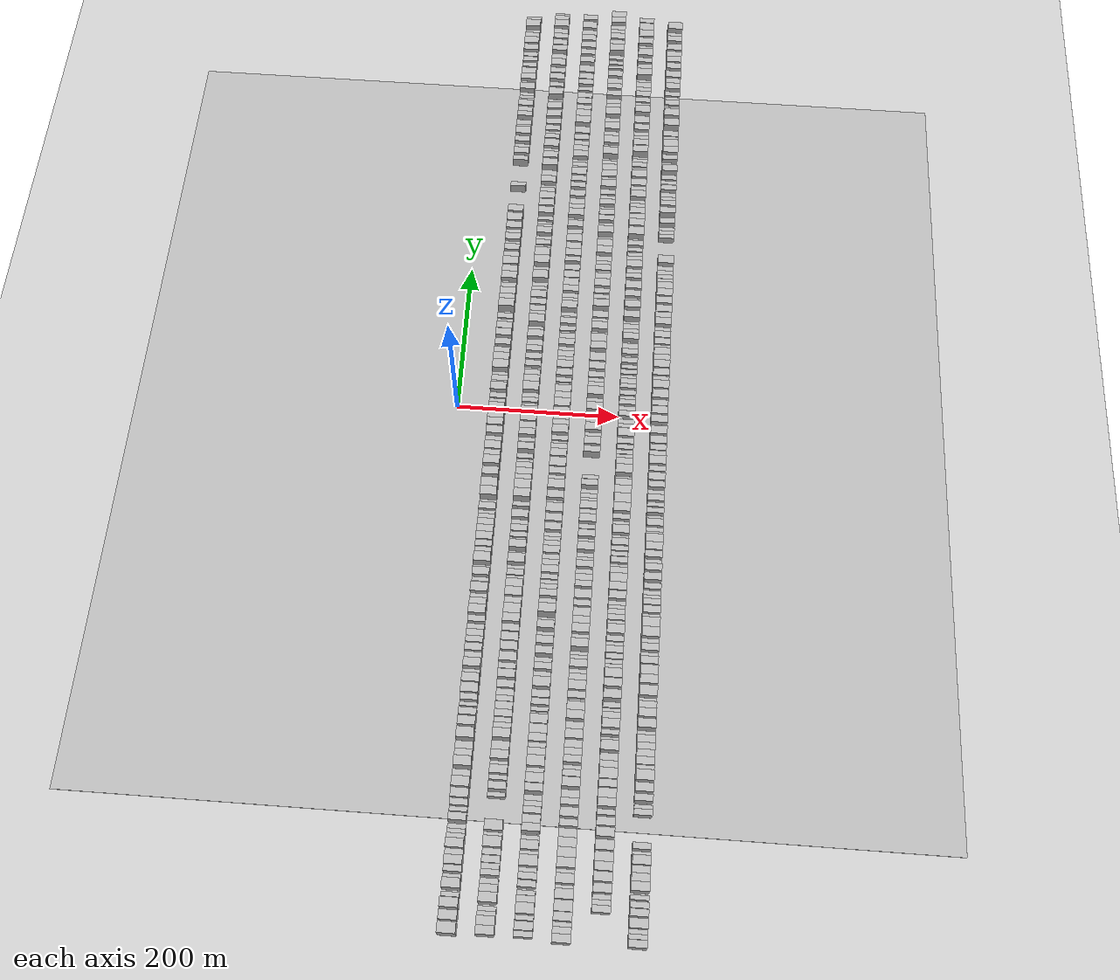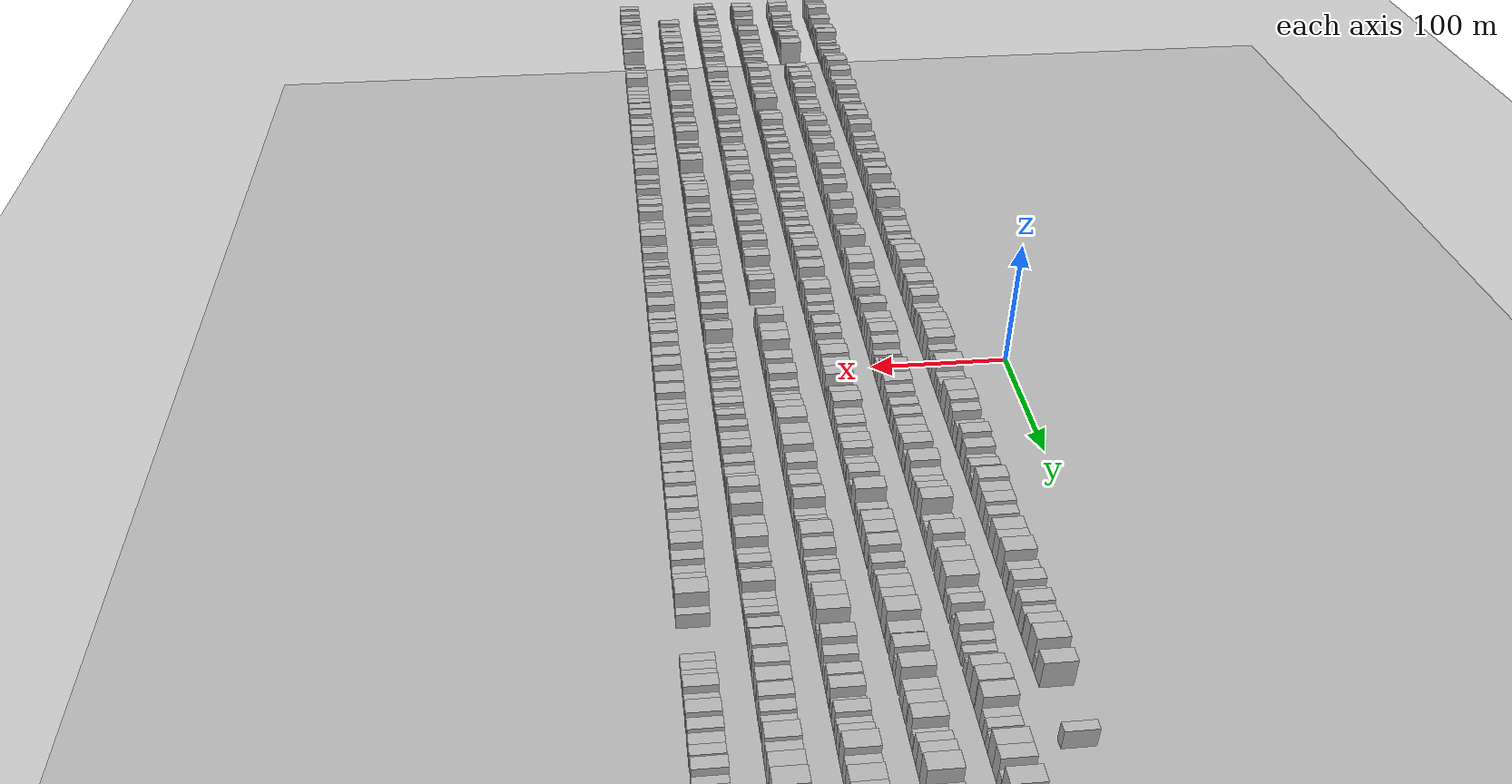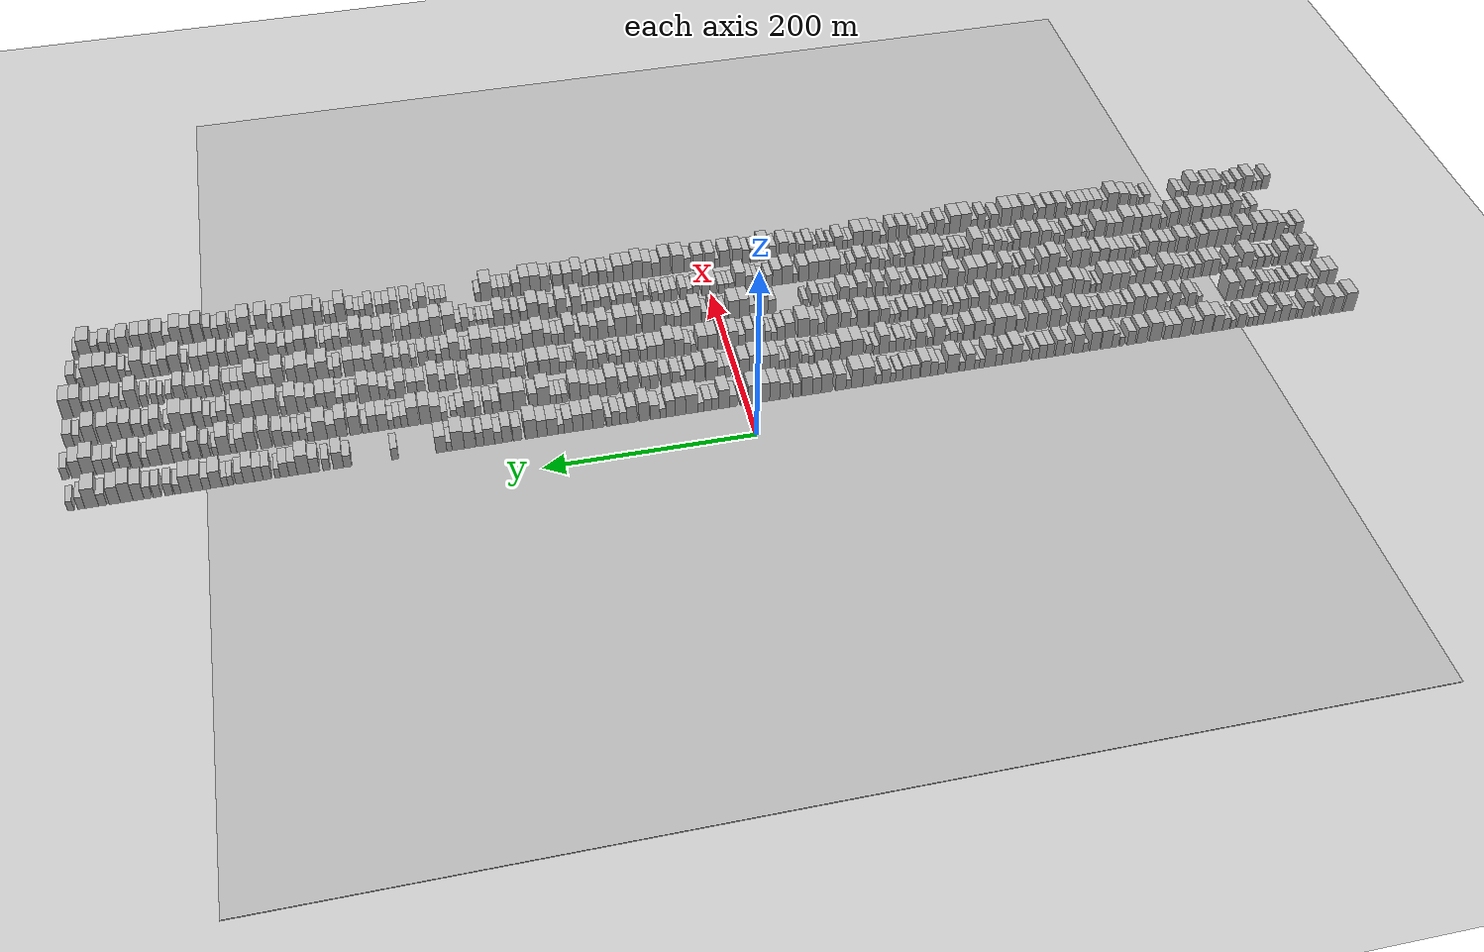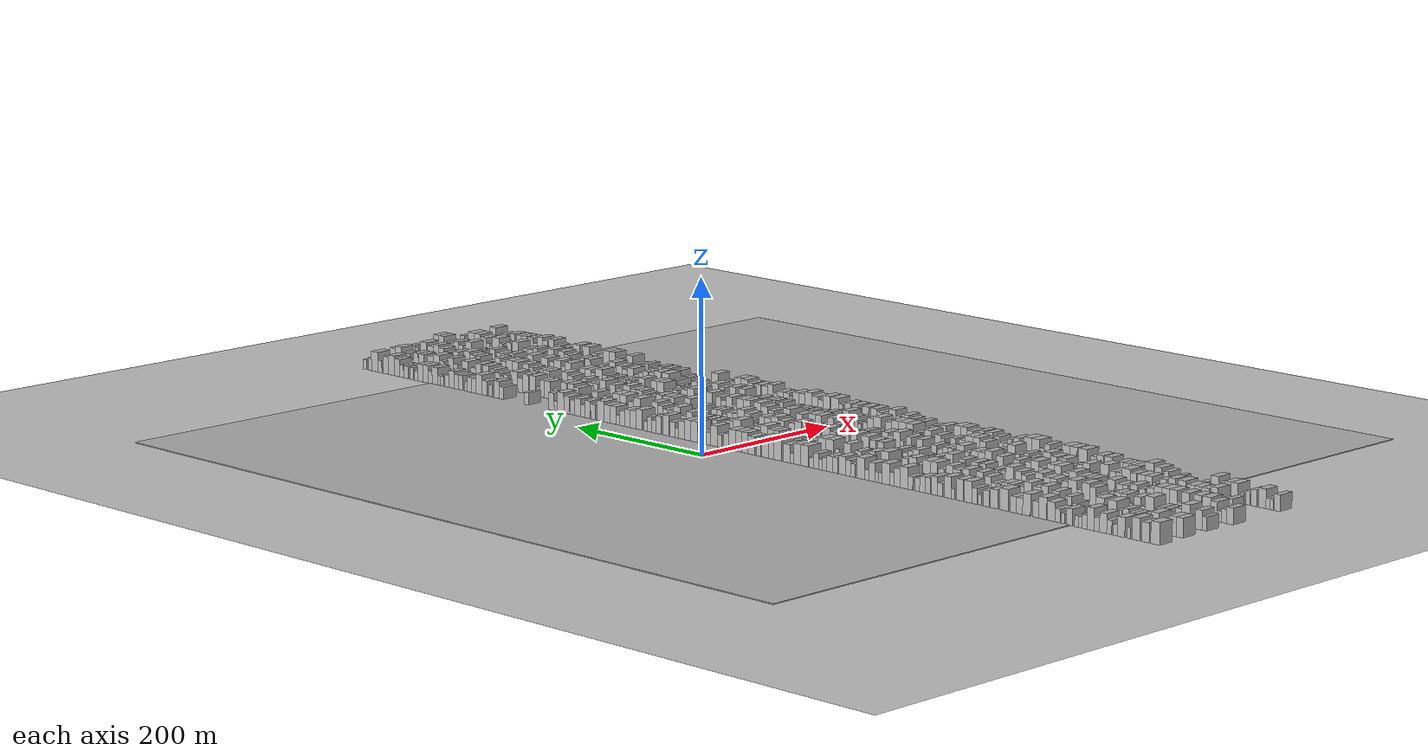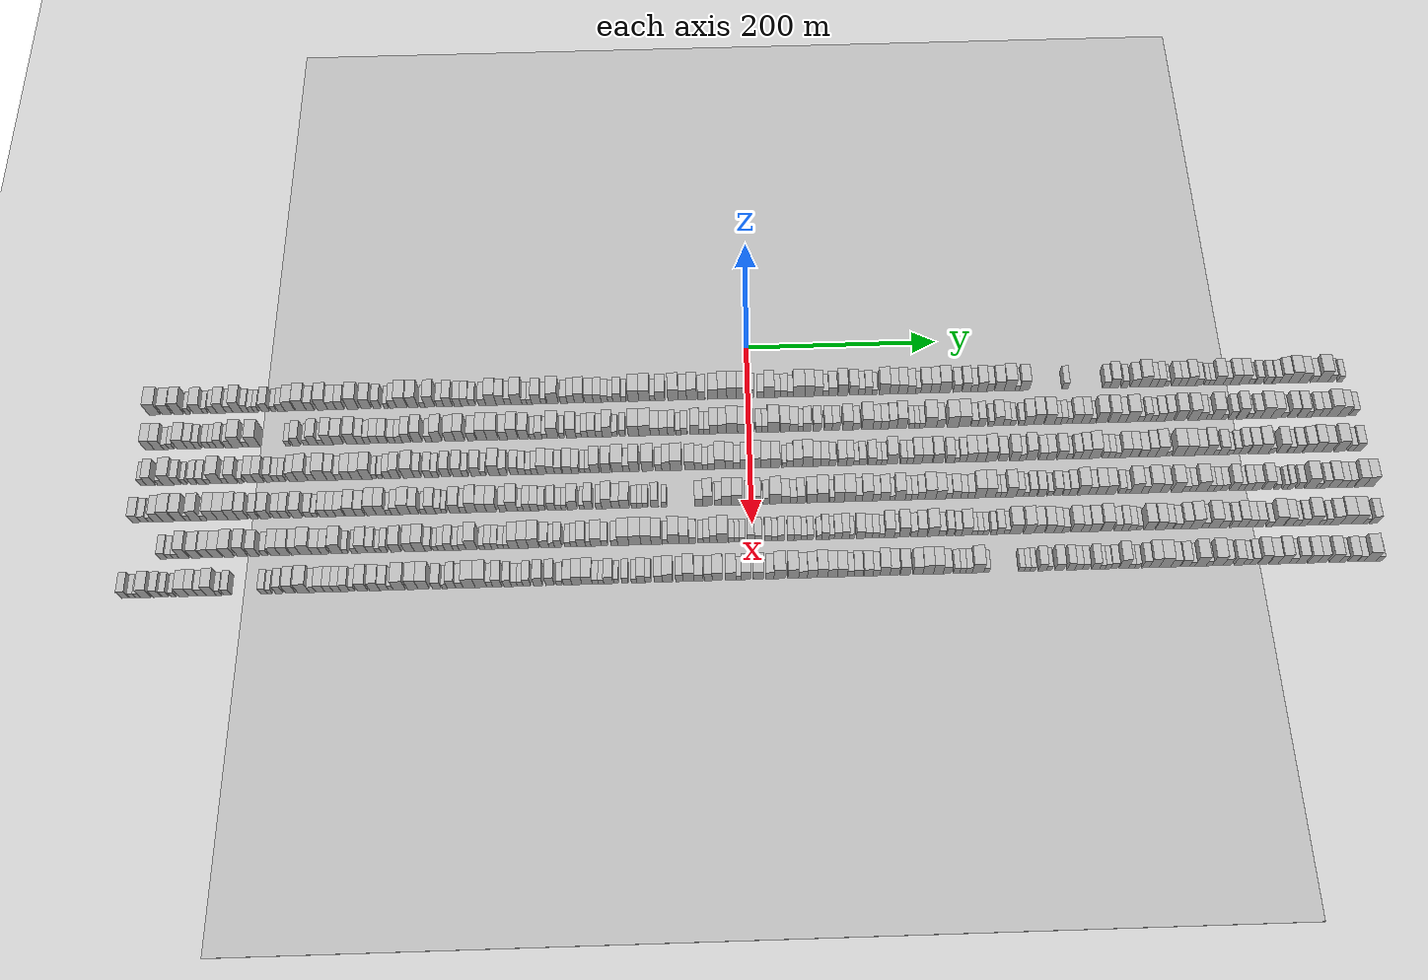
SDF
<?xml version="1.0" encoding="utf-8"?>

<sdf version="1.6">

   <world name="default">

      <gui fullscreen="0">

         <camera name="user_camera">

            <pose>-15 0 4.57585 0 0 0</pose>

            <view_controller>orbit</view_controller>

         </camera>

      </gui>

      <scene>

         <sky>

           <clouds>

             <speed>12</speed>

           </clouds>

         </sky>

         <ambient>0.4 0.4 0.4 1</ambient>

         <background>0.7 0.7 0.7 1</background>

         <shadows>1</shadows>

      </scene>

      <gravity>0 0 -9.8066</gravity>

      <magnetic_field>6e-06 2.3e-05 -4.2e-05</magnetic_field>

      <physics default="0" name="default_physics" type="ode">

         <ode>

            <solver>

               <type>quick</type>

               <iters>10</iters>

               <sor>1.0</sor>

               <use_dynamic_moi_rescaling>0</use_dynamic_moi_rescaling>

            </solver>

            <constraints>

               <cfm>0</cfm>

               <erp>0.2</erp>

               <contact_max_correcting_vel>100</contact_max_correcting_vel>

               <contact_surface_layer>0.001</contact_surface_layer>

            </constraints>

         </ode>

         <max_step_size>0.004</max_step_size>

         <real_time_factor>1</real_time_factor>

         <real_time_update_rate>250</real_time_update_rate>

      </physics>

      <light name="sun" type="directional">

         <cast_shadows>1</cast_shadows>

         <pose>0 0 10 0 0 0</pose>

         <diffuse>0.8 0.8 0.8 1</diffuse>

         <specular>0.2 0.2 0.2 1</specular>

         <attenuation>

            <range>1000</range>

            <constant>0.9</constant>

            <linear>0.01</linear>

            <quadratic>0.001</quadratic>

         </attenuation>

         <direction>-0.5 0.1 -0.9</direction>

      </light>

      <include>

         <name>ground_plane_1</name>

         <uri>model://HANNAS_ground_plane</uri>

         <pose>0 0 0  0 0 0</pose>

      </include>

      <include>

         <name>ground_plane_2</name>

         <uri>model://HANNAS_ground_plane</uri>

         <pose>100 0 0  0 0 0</pose>

      </include>

      <model name="building_1">

         <static>1</static>

         <pose frame="">50.0000 -614.0647 0 0.000000 0.000000 0.000000</pose>

         <link name="link">

            <pose frame="">0 0 12.00 0 0 0</pose>

            <collision name="collision">

               <geometry>

                  <box>

                     <size>20.0000 11.8707 24.0000</size>

                  </box>

               </geometry>

               <max_contacts>10</max_contacts>

               <surface>

                  <contact>

                     <ode/>

                  </contact>

                  <bounce/>

                  <friction>

                     <torsional>

                        <ode/>

                     </torsional>

                     <ode/>

                  </friction>

               </surface>

            </collision>

            <visual name="visual">

               <cast_shadows>0</cast_shadows>

               <geometry>

                  <box>

                     <size>20.0000 11.8707 24.0000</size>

                  </box>

               </geometry>

               <material>

                  <script>

                     <uri>model://HANNAS_wall/materials/scripts</uri>

                     <uri>model://HANNAS_wall/materials/textures</uri>

                     <name>vrc/HANNAS_wall</name>

                  </script>

               </material>

            </visual>

            <self_collide>0</self_collide>

            <enable_wind>0</enable_wind>

            <kinematic>0</kinematic>

         </link>

      </model>

      <model name="building_2">

         <static>1</static>

         <pose frame="">50.0000 -601.0607 0 0.000000 0.000000 0.000000</pose>

         <link name="link">

            <pose frame="">0 0 10.50 0 0 0</pose>

            <collision name="collision">

               <geometry>

                  <box>

                     <size>20.0000 10.1372 21.0000</size>

                  </box>

               </geometry>

               <max_contacts>10</max_contacts>

               <surface>

                  <contact>

                     <ode/>

                  </contact>

                  <bounce/>

                  <friction>

                     <torsional>

                        <ode/>

                     </torsional>

                     <ode/>

                  </friction>

               </surface>

            </collision>

            <visual name="visual">

               <cast_shadows>0</cast_shadows>

               <geometry>

                  <box>

                     <size>20.0000 10.1372 21.0000</size>

                  </box>

               </geometry>

               <material>

                  <script>

                     <uri>model://HANNAS_wall/materials/scripts</uri>

                     <uri>model://HANNAS_wall/materials/textures</uri>

                     <name>vrc/HANNAS_wall</name>

                  </script>

               </material>

            </visual>

            <self_collide>0</self_collide>

            <enable_wind>0</enable_wind>

            <kinematic>0</kinematic>

         </link>

      </model>

      <model name="building_3">

         <static>1</static>

         <pose frame="">50.0000 -588.9129 0 0.000000 0.000000 0.000000</pose>

         <link name="link">

            <pose frame="">0 0 12.00 0 0 0</pose>

            <collision name="collision">

               <geometry>

                  <box>

                     <size>20.0000 10.1585 24.0000</size>

                  </box>

               </geometry>

               <max_contacts>10</max_contacts>

               <surface>

                  <contact>

                     <ode/>

                  </contact>

                  <bounce/>

                  <friction>

                     <torsional>

                        <ode/>

                     </torsional>

                     <ode/>

                  </friction>

               </surface>

            </collision>

            <visual name="visual">

               <cast_shadows>0</cast_shadows>

               <geometry>

                  <box>

                     <size>20.0000 10.1585 24.0000</size>

                  </box>

               </geometry>

               <material>

                  <script>

                     <uri>model://HANNAS_wall/materials/scripts</uri>

                     <uri>model://HANNAS_wall/materials/textures</uri>

                     <name>vrc/HANNAS_wall</name>

                  </script>

               </material>

            </visual>

            <self_collide>0</self_collide>

            <enable_wind>0</enable_wind>

            <kinematic>0</kinematic>

         </link>

      </model>

      <model name="building_4">

         <static>1</static>

         <pose frame="">50.0000 -579.3778 0 0.000000 0.000000 0.000000</pose>

         <link name="link">

            <pose frame="">0 0 6.00 0 0 0</pose>

            <collision name="collision">

               <geometry>

                  <box>

                     <size>20.0000 4.9117 12.0000</size>

                  </box>

               </geometry>

               <max_contacts>10</max_contacts>

               <surface>

                  <contact>

                     <ode/>

                  </contact>

                  <bounce/>

                  <friction>

                     <torsional>

                        <ode/>

                     </torsional>

                     <ode/>

                  </friction>

               </surface>

            </collision>

            <visual name="visual">

               <cast_shadows>0</cast_shadows>

               <geometry>

                  <box>

                     <size>20.0000 4.9117 12.0000</size>

                  </box>

               </geometry>

               <material>

                  <script>

                     <uri>model://HANNAS_wall/materials/scripts</uri>

                     <uri>model://HANNAS_wall/materials/textures</uri>

                     <name>vrc/HANNAS_wall</name>

                  </script>

               </material>

            </visual>

            <self_collide>0</self_collide>

            <enable_wind>0</enable_wind>

            <kinematic>0</kinematic>

         </link>

      </model>

      <model name="building_5">

         <static>1</static>

         <pose frame="">50.0000 -568.7903 0 0.000000 0.000000 0.000000</pose>

         <link name="link">

            <pose frame="">0 0 10.50 0 0 0</pose>

            <collision name="collision">

               <geometry>

                  <box>

                     <size>20.0000 10.2632 21.0000</size>

                  </box>

               </geometry>

               <max_contacts>10</max_contacts>

               <surface>

                  <contact>

                     <ode/>

                  </contact>

                  <bounce/>

                  <friction>

                     <torsional>

                        <ode/>

                     </torsional>

                     <ode/>

                  </friction>

               </surface>

            </collision>

            <visual name="visual">

               <cast_shadows>0</cast_shadows>

               <geometry>

                  <box>

                     <size>20.0000 10.2632 21.0000</size>

                  </box>

               </geometry>

               <material>

                  <script>

                     <uri>model://HANNAS_wall/materials/scripts</uri>

                     <uri>model://HANNAS_wall/materials/textures</uri>

                     <name>vrc/HANNAS_wall</name>

                  </script>

               </material>

            </visual>

            <self_collide>0</self_collide>

            <enable_wind>0</enable_wind>

            <kinematic>0</kinematic>

         </link>

      </model>

      <model name="building_6">

         <static>1</static>

         <pose frame="">50.0000 -561.1024 0 0.000000 0.000000 0.000000</pose>

         <link name="link">

            <pose frame="">0 0 6.00 0 0 0</pose>

            <collision name="collision">

               <geometry>

                  <box>

                     <size>20.0000 5.1128 12.0000</size>

                  </box>

               </geometry>

               <max_contacts>10</max_contacts>

               <surface>

                  <contact>

                     <ode/>

                  </contact>

                  <bounce/>

                  <friction>

                     <torsional>

                        <ode/>

                     </torsional>

                     <ode/>

                  </friction>

               </surface>

            </collision>

            <visual name="visual">

               <cast_shadows>0</cast_shadows>

               <geometry>

                  <box>

                     <size>20.0000 5.1128 12.0000</size>

                  </box>

               </geometry>

               <material>

                  <script>

                     <uri>model://HANNAS_wall/materials/scripts</uri>

                     <uri>model://HANNAS_wall/materials/textures</uri>

                     <name>vrc/HANNAS_wall</name>

                  </script>

               </material>

            </visual>

            <self_collide>0</self_collide>

            <enable_wind>0</enable_wind>

            <kinematic>0</kinematic>

         </link>

      </model>

      <model name="building_7">

         <static>1</static>

         <pose frame="">50.0000 -553.1415 0 0.000000 0.000000 0.000000</pose>

         <link name="link">

            <pose frame="">0 0 7.50 0 0 0</pose>

            <collision name="collision">

               <geometry>

                  <box>

                     <size>20.0000 6.8089 15.0000</size>

                  </box>

               </geometry>

               <max_contacts>10</max_contacts>

               <surface>

                  <contact>

                     <ode/>

                  </contact>

                  <bounce/>

                  <friction>

                     <torsional>

                        <ode/>

                     </torsional>

                     <ode/>

                  </friction>

               </surface>

            </collision>

            <visual name="visual">

               <cast_shadows>0</cast_shadows>

               <geometry>

                  <box>

                     <size>20.0000 6.8089 15.0000</size>

                  </box>

               </geometry>

               <material>

                  <script>

                     <uri>model://HANNAS_wall/materials/scripts</uri>

                     <uri>model://HANNAS_wall/materials/textures</uri>

                     <name>vrc/HANNAS_wall</name>

                  </script>

               </material>

            </visual>

            <self_collide>0</self_collide>

            <enable_wind>0</enable_wind>

            <kinematic>0</kinematic>

         </link>

      </model>

      <model name="building_8">

         <static>1</static>

         <pose frame="">50.0000 -544.9592 0 0.000000 0.000000 0.000000</pose>

         <link name="link">

            <pose frame="">0 0 10.50 0 0 0</pose>

            <collision name="collision">

               <geometry>

                  <box>

                     <size>20.0000 9.5557 21.0000</size>

                  </box>

               </geometry>

               <max_contacts>10</max_contacts>

               <surface>

                  <contact>

                     <ode/>

                  </contact>

                  <bounce/>

                  <friction>

                     <torsional>

                        <ode/>

                     </torsional>

                     <ode/>

                  </friction>

               </surface>

            </collision>

            <visual name="visual">

               <cast_shadows>0</cast_shadows>

               <geometry>

                  <box>

                     <size>20.0000 9.5557 21.0000</size>

                  </box>

               </geometry>

               <material>

                  <script>

                     <uri>model://HANNAS_wall/materials/scripts</uri>

                     <uri>model://HANNAS_wall/materials/textures</uri>

                     <name>vrc/HANNAS_wall</name>

                  </script>

               </material>

            </visual>

            <self_collide>0</self_collide>

            <enable_wind>0</enable_wind>

            <kinematic>0</kinematic>

         </link>

      </model>

      <model name="building_9">

         <static>1</static>

         <pose frame="">50.0000 -536.5706 0 0.000000 0.000000 0.000000</pose>

         <link name="link">

            <pose frame="">0 0 7.50 0 0 0</pose>

            <collision name="collision">

               <geometry>

                  <box>

                     <size>20.0000 7.2216 15.0000</size>

                  </box>

               </geometry>

               <max_contacts>10</max_contacts>

               <surface>

                  <contact>

                     <ode/>

                  </contact>

                  <bounce/>

                  <friction>

                     <torsional>

                        <ode/>

                     </torsional>

                     <ode/>

                  </friction>

               </surface>

            </collision>

            <visual name="visual">

               <cast_shadows>0</cast_shadows>

               <geometry>

                  <box>

                     <size>20.0000 7.2216 15.0000</size>

                  </box>

               </geometry>

               <material>

                  <script>

                     <uri>model://HANNAS_wall/materials/scripts</uri>

                     <uri>model://HANNAS_wall/materials/textures</uri>

                     <name>vrc/HANNAS_wall</name>

                  </script>

               </material>

            </visual>

            <self_collide>0</self_collide>

            <enable_wind>0</enable_wind>

            <kinematic>0</kinematic>

         </link>

      </model>

      <model name="building_10">

         <static>1</static>

         <pose frame="">50.0000 -528.0604 0 0.000000 0.000000 0.000000</pose>

         <link name="link">

            <pose frame="">0 0 12.00 0 0 0</pose>

            <collision name="collision">

               <geometry>

                  <box>

                     <size>20.0000 9.7987 24.0000</size>

                  </box>

               </geometry>

               <max_contacts>10</max_contacts>

               <surface>

                  <contact>

                     <ode/>

                  </contact>

                  <bounce/>

                  <friction>

                     <torsional>

                        <ode/>

                     </torsional>

                     <ode/>

                  </friction>

               </surface>

            </collision>

            <visual name="visual">

               <cast_shadows>0</cast_shadows>

               <geometry>

                  <box>

                     <size>20.0000 9.7987 24.0000</size>

                  </box>

               </geometry>

               <material>

                  <script>

                     <uri>model://HANNAS_wall/materials/scripts</uri>

                     <uri>model://HANNAS_wall/materials/textures</uri>

                     <name>vrc/HANNAS_wall</name>

                  </script>

               </material>

            </visual>

            <self_collide>0</self_collide>

            <enable_wind>0</enable_wind>

            <kinematic>0</kinematic>

         </link>

      </model>

      <model name="building_11">

         <static>1</static>

         <pose frame="">50.0000 -519.9152 0 0.000000 0.000000 0.000000</pose>

         <link name="link">

            <pose frame="">0 0 7.50 0 0 0</pose>

            <collision name="collision">

               <geometry>

                  <box>

                     <size>20.0000 6.4918 15.0000</size>

                  </box>

               </geometry>

               <max_contacts>10</max_contacts>

               <surface>

                  <contact>

                     <ode/>

                  </contact>

                  <bounce/>

                  <friction>

                     <torsional>

                        <ode/>

                     </torsional>

                     <ode/>

                  </friction>

               </surface>

            </collision>

            <visual name="visual">

               <cast_shadows>0</cast_shadows>

               <geometry>

                  <box>

                     <size>20.0000 6.4918 15.0000</size>

                  </box>

               </geometry>

               <material>

                  <script>

                     <uri>model://HANNAS_wall/materials/scripts</uri>

                     <uri>model://HANNAS_wall/materials/textures</uri>

                     <name>vrc/HANNAS_wall</name>

                  </script>

               </material>

            </visual>

            <self_collide>0</self_collide>

            <enable_wind>0</enable_wind>

            <kinematic>0</kinematic>

         </link>

      </model>

      <model name="building_12">

         <static>1</static>

         <pose frame="">50.0000 -514.1275 0 0.000000 0.000000 0.000000</pose>

         <link name="link">

            <pose frame="">0 0 6.00 0 0 0</pose>

            <collision name="collision">

               <geometry>

                  <box>

                     <size>20.0000 5.0837 12.0000</size>

                  </box>

               </geometry>

               <max_contacts>10</max_contacts>

               <surface>

                  <contact>

                     <ode/>

                  </contact>

                  <bounce/>

                  <friction>

                     <torsional>

                        <ode/>

                     </torsional>

                     <ode/>

                  </friction>

               </surface>

            </collision>

            <visual name="visual">

               <cast_shadows>0</cast_shadows>

               <geometry>

                  <box>

                     <size>20.0000 5.0837 12.0000</size>

                  </box>

               </geometry>

               <material>

                  <script>

                     <uri>model://HANNAS_wall/materials/scripts</uri>

                     <uri>model://HANNAS_wall/materials/textures</uri>

                     <name>vrc/HANNAS_wall</name>

                  </script>

               </material>

            </visual>

            <self_collide>0</self_collide>

            <enable_wind>0</enable_wind>

            <kinematic>0</kinematic>

         </link>

      </model>

      <model name="building_13">

         <static>1</static>

         <pose frame="">50.0000 -509.0317 0 0.000000 0.000000 0.000000</pose>

         <link name="link">

            <pose frame="">0 0 6.00 0 0 0</pose>

            <collision name="collision">

               <geometry>

                  <box>

                     <size>20.0000 5.1077 12.0000</size>

                  </box>

               </geometry>

               <max_contacts>10</max_contacts>

               <surface>

                  <contact>

                     <ode/>

                  </contact>

                  <bounce/>

                  <friction>

                     <torsional>

                        <ode/>

                     </torsional>

                     <ode/>

                  </friction>

               </surface>

            </collision>

            <visual name="visual">

               <cast_shadows>0</cast_shadows>

               <geometry>

                  <box>

                     <size>20.0000 5.1077 12.0000</size>

                  </box>

               </geometry>

               <material>

                  <script>

                     <uri>model://HANNAS_wall/materials/scripts</uri>

                     <uri>model://HANNAS_wall/materials/textures</uri>

                     <name>vrc/HANNAS_wall</name>

                  </script>

               </material>

            </visual>

            <self_collide>0</self_collide>

            <enable_wind>0</enable_wind>

            <kinematic>0</kinematic>

         </link>

      </model>

      <model name="building_14">

         <static>1</static>

         <pose frame="">50.0000 -499.3584 0 0.000000 0.000000 0.000000</pose>

         <link name="link">

            <pose frame="">0 0 9.00 0 0 0</pose>

            <collision name="collision">

               <geometry>

                  <box>

                     <size>20.0000 8.2390 18.0000</size>

                  </box>

               </geometry>

               <max_contacts>10</max_contacts>

               <surface>

                  <contact>

                     <ode/>

                  </contact>

                  <bounce/>

                  <friction>

                     <torsional>

                        <ode/>

                     </torsional>

                     <ode/>

                  </friction>

               </surface>

            </collision>

            <visual name="visual">

               <cast_shadows>0</cast_shadows>

               <geometry>

                  <box>

                     <size>20.0000 8.2390 18.0000</size>

                  </box>

               </geometry>

               <material>

                  <script>

                     <uri>model://HANNAS_wall/materials/scripts</uri>

                     <uri>model://HANNAS_wall/materials/textures</uri>

                     <name>vrc/HANNAS_wall</name>

                  </script>

               </material>

            </visual>

            <self_collide>0</self_collide>

            <enable_wind>0</enable_wind>

            <kinematic>0</kinematic>

         </link>

      </model>

      <model name="building_15">

         <static>1</static>

         <pose frame="">50.0000 -490.6600 0 0.000000 0.000000 0.000000</pose>

         <link name="link">

            <pose frame="">0 0 6.00 0 0 0</pose>

            <collision name="collision">

               <geometry>

                  <box>

                     <size>20.0000 5.1577 12.0000</size>

                  </box>

               </geometry>

               <max_contacts>10</max_contacts>

               <surface>

                  <contact>

                     <ode/>

                  </contact>

                  <bounce/>

                  <friction>

                     <torsional>

                        <ode/>

                     </torsional>

                     <ode/>

                  </friction>

               </surface>

            </collision>

            <visual name="visual">

               <cast_shadows>0</cast_shadows>

               <geometry>

                  <box>

                     <size>20.0000 5.1577 12.0000</size>

                  </box>

               </geometry>

               <material>

                  <script>

                     <uri>model://HANNAS_wall/materials/scripts</uri>

                     <uri>model://HANNAS_wall/materials/textures</uri>

                     <name>vrc/HANNAS_wall</name>

                  </script>

               </material>

            </visual>

            <self_collide>0</self_collide>

            <enable_wind>0</enable_wind>

            <kinematic>0</kinematic>

         </link>

      </model>

      <model name="building_16">

         <static>1</static>

         <pose frame="">50.0000 -483.3832 0 0.000000 0.000000 0.000000</pose>

         <link name="link">

            <pose frame="">0 0 7.50 0 0 0</pose>

            <collision name="collision">

               <geometry>

                  <box>

                     <size>20.0000 7.3959 15.0000</size>

                  </box>

               </geometry>

               <max_contacts>10</max_contacts>

               <surface>

                  <contact>

                     <ode/>

                  </contact>

                  <bounce/>

                  <friction>

                     <torsional>

                        <ode/>

                     </torsional>

                     <ode/>

                  </friction>

               </surface>

            </collision>

            <visual name="visual">

               <cast_shadows>0</cast_shadows>

               <geometry>

                  <box>

                     <size>20.0000 7.3959 15.0000</size>

                  </box>

               </geometry>

               <material>

                  <script>

                     <uri>model://HANNAS_wall/materials/scripts</uri>

                     <uri>model://HANNAS_wall/materials/textures</uri>

                     <name>vrc/HANNAS_wall</name>

                  </script>

               </material>

            </visual>

            <self_collide>0</self_collide>

            <enable_wind>0</enable_wind>

            <kinematic>0</kinematic>

         </link>

      </model>

      <model name="building_17">

         <static>1</static>

         <pose frame="">50.0000 -474.5680 0 0.000000 0.000000 0.000000</pose>

         <link name="link">

            <pose frame="">0 0 10.50 0 0 0</pose>

            <collision name="collision">

               <geometry>

                  <box>

                     <size>20.0000 10.2346 21.0000</size>

                  </box>

               </geometry>

               <max_contacts>10</max_contacts>

               <surface>

                  <contact>

                     <ode/>

                  </contact>

                  <bounce/>

                  <friction>

                     <torsional>

                        <ode/>

                     </torsional>

                     <ode/>

                  </friction>

               </surface>

            </collision>

            <visual name="visual">

               <cast_shadows>0</cast_shadows>

               <geometry>

                  <box>

                     <size>20.0000 10.2346 21.0000</size>

                  </box>

               </geometry>

               <material>

                  <script>

                     <uri>model://HANNAS_wall/materials/scripts</uri>

                     <uri>model://HANNAS_wall/materials/textures</uri>

                     <name>vrc/HANNAS_wall</name>

                  </script>

               </material>

            </visual>

            <self_collide>0</self_collide>

            <enable_wind>0</enable_wind>

            <kinematic>0</kinematic>

         </link>

      </model>

      <model name="building_18">

         <static>1</static>

         <pose frame="">50.0000 -462.9156 0 0.000000 0.000000 0.000000</pose>

         <link name="link">

            <pose frame="">0 0 12.00 0 0 0</pose>

            <collision name="collision">

               <geometry>

                  <box>

                     <size>20.0000 11.0701 24.0000</size>

                  </box>

               </geometry>

               <max_contacts>10</max_contacts>

               <surface>

                  <contact>

                     <ode/>

                  </contact>

                  <bounce/>

                  <friction>

                     <torsional>

                        <ode/>

                     </torsional>

                     <ode/>

                  </friction>

               </surface>

            </collision>

            <visual name="visual">

               <cast_shadows>0</cast_shadows>

               <geometry>

                  <box>

                     <size>20.0000 11.0701 24.0000</size>

                  </box>

               </geometry>

               <material>

                  <script>

                     <uri>model://HANNAS_wall/materials/scripts</uri>

                     <uri>model://HANNAS_wall/materials/textures</uri>

                     <name>vrc/HANNAS_wall</name>

                  </script>

               </material>

            </visual>

            <self_collide>0</self_collide>

            <enable_wind>0</enable_wind>

            <kinematic>0</kinematic>

         </link>

      </model>

      <model name="building_19">

         <static>1</static>

         <pose frame="">50.0000 -453.2186 0 0.000000 0.000000 0.000000</pose>

         <link name="link">

            <pose frame="">0 0 9.00 0 0 0</pose>

            <collision name="collision">

               <geometry>

                  <box>

                     <size>20.0000 8.3239 18.0000</size>

                  </box>

               </geometry>

               <max_contacts>10</max_contacts>

               <surface>

                  <contact>

                     <ode/>

                  </contact>

                  <bounce/>

                  <friction>

                     <torsional>

                        <ode/>

                     </torsional>

                     <ode/>

                  </friction>

               </surface>

            </collision>

            <visual name="visual">

               <cast_shadows>0</cast_shadows>

               <geometry>

                  <box>

                     <size>20.0000 8.3239 18.0000</size>

                  </box>

               </geometry>

               <material>

                  <script>

                     <uri>model://HANNAS_wall/materials/scripts</uri>

                     <uri>model://HANNAS_wall/materials/textures</uri>

                     <name>vrc/HANNAS_wall</name>

                  </script>

               </material>

            </visual>

            <self_collide>0</self_collide>

            <enable_wind>0</enable_wind>

            <kinematic>0</kinematic>

         </link>

      </model>

      <model name="building_20">

         <static>1</static>

         <pose frame="">50.0000 -440.6181 0 0.000000 0.000000 0.000000</pose>

         <link name="link">

            <pose frame="">0 0 12.00 0 0 0</pose>

            <collision name="collision">

               <geometry>

                  <box>

                     <size>20.0000 10.8770 24.0000</size>

                  </box>

               </geometry>

               <max_contacts>10</max_contacts>

               <surface>

                  <contact>

                     <ode/>

                  </contact>

                  <bounce/>

                  <friction>

                     <torsional>

                        <ode/>

                     </torsional>

                     <ode/>

                  </friction>

               </surface>

            </collision>

            <visual name="visual">

               <cast_shadows>0</cast_shadows>

               <geometry>

                  <box>

                     <size>20.0000 10.8770 24.0000</size>

                  </box>

               </geometry>

               <material>

                  <script>

                     <uri>model://HANNAS_wall/materials/scripts</uri>

                     <uri>model://HANNAS_wall/materials/textures</uri>

                     <name>vrc/HANNAS_wall</name>

                  </script>

               </material>

            </visual>

            <self_collide>0</self_collide>

            <enable_wind>0</enable_wind>

            <kinematic>0</kinematic>

         </link>

      </model>

      <model name="building_21">

         <static>1</static>

         <pose frame="">50.0000 -430.7888 0 0.000000 0.000000 0.000000</pose>

         <link name="link">

            <pose frame="">0 0 9.00 0 0 0</pose>

            <collision name="collision">

               <geometry>

                  <box>

                     <size>20.0000 8.7816 18.0000</size>

                  </box>

               </geometry>

               <max_contacts>10</max_contacts>

               <surface>

                  <contact>

                     <ode/>

                  </contact>

                  <bounce/>

                  <friction>

                     <torsional>

                        <ode/>

                     </torsional>

                     <ode/>

                  </friction>

               </surface>

            </collision>

            <visual name="visual">

               <cast_shadows>0</cast_shadows>

               <geometry>

                  <box>

                     <size>20.0000 8.7816 18.0000</size>

                  </box>

               </geometry>

               <material>

                  <script>

                     <uri>model://HANNAS_wall/materials/scripts</uri>

                     <uri>model://HANNAS_wall/materials/textures</uri>

                     <name>vrc/HANNAS_wall</name>

                  </script>

               </material>

            </visual>

            <self_collide>0</self_collide>

            <enable_wind>0</enable_wind>

            <kinematic>0</kinematic>

         </link>

      </model>

      <model name="building_22">

         <static>1</static>

         <pose frame="">50.0000 -422.2587 0 0.000000 0.000000 0.000000</pose>

         <link name="link">

            <pose frame="">0 0 9.00 0 0 0</pose>

            <collision name="collision">

               <geometry>

                  <box>

                     <size>20.0000 8.2787 18.0000</size>

                  </box>

               </geometry>

               <max_contacts>10</max_contacts>

               <surface>

                  <contact>

                     <ode/>

                  </contact>

                  <bounce/>

                  <friction>

                     <torsional>

                        <ode/>

                     </torsional>

                     <ode/>

                  </friction>

               </surface>

            </collision>

            <visual name="visual">

               <cast_shadows>0</cast_shadows>

               <geometry>

                  <box>

                     <size>20.0000 8.2787 18.0000</size>

                  </box>

               </geometry>

               <material>

                  <script>

                     <uri>model://HANNAS_wall/materials/scripts</uri>

                     <uri>model://HANNAS_wall/materials/textures</uri>

                     <name>vrc/HANNAS_wall</name>

                  </script>

               </material>

            </visual>

            <self_collide>0</self_collide>

            <enable_wind>0</enable_wind>

            <kinematic>0</kinematic>

         </link>

      </model>

      <model name="building_23">

         <static>1</static>

         <pose frame="">50.0000 -409.2521 0 0.000000 0.000000 0.000000</pose>

         <link name="link">

            <pose frame="">0 0 12.00 0 0 0</pose>

            <collision name="collision">

               <geometry>

                  <box>

                     <size>20.0000 11.7345 24.0000</size>

                  </box>

               </geometry>

               <max_contacts>10</max_contacts>

               <surface>

                  <contact>

                     <ode/>

                  </contact>

                  <bounce/>

                  <friction>

                     <torsional>

                        <ode/>

                     </torsional>

                     <ode/>

                  </friction>

               </surface>

            </collision>

            <visual name="visual">

               <cast_shadows>0</cast_shadows>

               <geometry>

                  <box>

                     <size>20.0000 11.7345 24.0000</size>

                  </box>

               </geometry>

               <material>

                  <script>

                     <uri>model://HANNAS_wall/materials/scripts</uri>

                     <uri>model://HANNAS_wall/materials/textures</uri>

                     <name>vrc/HANNAS_wall</name>

                  </script>

               </material>

            </visual>

            <self_collide>0</self_collide>

            <enable_wind>0</enable_wind>

            <kinematic>0</kinematic>

         </link>

      </model>

      <model name="building_24">

         <static>1</static>

         <pose frame="">50.0000 -395.3235 0 0.000000 0.000000 0.000000</pose>

         <link name="link">

            <pose frame="">0 0 10.50 0 0 0</pose>

            <collision name="collision">

               <geometry>

                  <box>

                     <size>20.0000 10.1227 21.0000</size>

                  </box>

               </geometry>

               <max_contacts>10</max_contacts>

               <surface>

                  <contact>

                     <ode/>

                  </contact>

                  <bounce/>

                  <friction>

                     <torsional>

                        <ode/>

                     </torsional>

                     <ode/>

                  </friction>

               </surface>

            </collision>

            <visual name="visual">

               <cast_shadows>0</cast_shadows>

               <geometry>

                  <box>

                     <size>20.0000 10.1227 21.0000</size>

                  </box>

               </geometry>

               <material>

                  <script>

                     <uri>model://HANNAS_wall/materials/scripts</uri>

                     <uri>model://HANNAS_wall/materials/textures</uri>

                     <name>vrc/HANNAS_wall</name>

                  </script>

               </material>

            </visual>

            <self_collide>0</self_collide>

            <enable_wind>0</enable_wind>

            <kinematic>0</kinematic>

         </link>

      </model>

      <model name="building_25">

         <static>1</static>

         <pose frame="">50.0000 -384.2467 0 0.000000 0.000000 0.000000</pose>

         <link name="link">

            <pose frame="">0 0 9.00 0 0 0</pose>

            <collision name="collision">

               <geometry>

                  <box>

                     <size>20.0000 8.0308 18.0000</size>

                  </box>

               </geometry>

               <max_contacts>10</max_contacts>

               <surface>

                  <contact>

                     <ode/>

                  </contact>

                  <bounce/>

                  <friction>

                     <torsional>

                        <ode/>

                     </torsional>

                     <ode/>

                  </friction>

               </surface>

            </collision>

            <visual name="visual">

               <cast_shadows>0</cast_shadows>

               <geometry>

                  <box>

                     <size>20.0000 8.0308 18.0000</size>

                  </box>

               </geometry>

               <material>

                  <script>

                     <uri>model://HANNAS_wall/materials/scripts</uri>

                     <uri>model://HANNAS_wall/materials/textures</uri>

                     <name>vrc/HANNAS_wall</name>

                  </script>

               </material>

            </visual>

            <self_collide>0</self_collide>

            <enable_wind>0</enable_wind>

            <kinematic>0</kinematic>

         </link>

      </model>

      <model name="building_26">

         <static>1</static>

         <pose frame="">50.0000 -374.8311 0 0.000000 0.000000 0.000000</pose>

         <link name="link">

            <pose frame="">0 0 6.00 0 0 0</pose>

            <collision name="collision">

               <geometry>

                  <box>

                     <size>20.0000 4.8004 12.0000</size>

                  </box>

               </geometry>

               <max_contacts>10</max_contacts>

               <surface>

                  <contact>

                     <ode/>

                  </contact>

                  <bounce/>

                  <friction>

                     <torsional>

                        <ode/>

                     </torsional>

                     <ode/>

                  </friction>

               </surface>

            </collision>

            <visual name="visual">

               <cast_shadows>0</cast_shadows>

               <geometry>

                  <box>

                     <size>20.0000 4.8004 12.0000</size>

                  </box>

               </geometry>

               <material>

                  <script>

                     <uri>model://HANNAS_wall/materials/scripts</uri>

                     <uri>model://HANNAS_wall/materials/textures</uri>

                     <name>vrc/HANNAS_wall</name>

                  </script>

               </material>

            </visual>

            <self_collide>0</self_collide>

            <enable_wind>0</enable_wind>

            <kinematic>0</kinematic>

         </link>

      </model>

      <model name="building_27">

         <static>1</static>

         <pose frame="">50.0000 -367.8223 0 0.000000 0.000000 0.000000</pose>

         <link name="link">

            <pose frame="">0 0 9.00 0 0 0</pose>

            <collision name="collision">

               <geometry>

                  <box>

                     <size>20.0000 7.2173 18.0000</size>

                  </box>

               </geometry>

               <max_contacts>10</max_contacts>

               <surface>

                  <contact>

                     <ode/>

                  </contact>

                  <bounce/>

                  <friction>

                     <torsional>

                        <ode/>

                     </torsional>

                     <ode/>

                  </friction>

               </surface>

            </collision>

            <visual name="visual">

               <cast_shadows>0</cast_shadows>

               <geometry>

                  <box>

                     <size>20.0000 7.2173 18.0000</size>

                  </box>

               </geometry>

               <material>

                  <script>

                     <uri>model://HANNAS_wall/materials/scripts</uri>

                     <uri>model://HANNAS_wall/materials/textures</uri>

                     <name>vrc/HANNAS_wall</name>

                  </script>

               </material>

            </visual>

            <self_collide>0</self_collide>

            <enable_wind>0</enable_wind>

            <kinematic>0</kinematic>

         </link>

      </model>

      <model name="building_28">

         <static>1</static>

         <pose frame="">50.0000 -358.6477 0 0.000000 0.000000 0.000000</pose>

         <link name="link">

            <pose frame="">0 0 12.00 0 0 0</pose>

            <collision name="collision">

               <geometry>

                  <box>

                     <size>20.0000 11.1320 24.0000</size>

                  </box>

               </geometry>

               <max_contacts>10</max_contacts>

               <surface>

                  <contact>

                     <ode/>

                  </contact>

                  <bounce/>

                  <friction>

                     <torsional>

                        <ode/>

                     </torsional>

                     <ode/>

                  </friction>

               </surface>

            </collision>

            <visual name="visual">

               <cast_shadows>0</cast_shadows>

               <geometry>

                  <box>

                     <size>20.0000 11.1320 24.0000</size>

                  </box>

               </geometry>

               <material>

                  <script>

                     <uri>model://HANNAS_wall/materials/scripts</uri>

                     <uri>model://HANNAS_wall/materials/textures</uri>

                     <name>vrc/HANNAS_wall</name>

                  </script>

               </material>

            </visual>

            <self_collide>0</self_collide>

            <enable_wind>0</enable_wind>

            <kinematic>0</kinematic>

         </link>

      </model>

      <model name="building_29">

         <static>1</static>

         <pose frame="">50.0000 -347.0237 0 0.000000 0.000000 0.000000</pose>

         <link name="link">

            <pose frame="">0 0 12.00 0 0 0</pose>

            <collision name="collision">

               <geometry>

                  <box>

                     <size>20.0000 10.1159 24.0000</size>

                  </box>

               </geometry>

               <max_contacts>10</max_contacts>

               <surface>

                  <contact>

                     <ode/>

                  </contact>

                  <bounce/>

                  <friction>

                     <torsional>

                        <ode/>

                     </torsional>

                     <ode/>

                  </friction>

               </surface>

            </collision>

            <visual name="visual">

               <cast_shadows>0</cast_shadows>

               <geometry>

                  <box>

                     <size>20.0000 10.1159 24.0000</size>

                  </box>

               </geometry>

               <material>

                  <script>

                     <uri>model://HANNAS_wall/materials/scripts</uri>

                     <uri>model://HANNAS_wall/materials/textures</uri>

                     <name>vrc/HANNAS_wall</name>

                  </script>

               </material>

            </visual>

            <self_collide>0</self_collide>

            <enable_wind>0</enable_wind>

            <kinematic>0</kinematic>

         </link>

      </model>

      <model name="building_30">

         <static>1</static>

         <pose frame="">50.0000 -337.2994 0 0.000000 0.000000 0.000000</pose>

         <link name="link">

            <pose frame="">0 0 6.00 0 0 0</pose>

            <collision name="collision">

               <geometry>

                  <box>

                     <size>20.0000 5.3329 12.0000</size>

                  </box>

               </geometry>

               <max_contacts>10</max_contacts>

               <surface>

                  <contact>

                     <ode/>

                  </contact>

                  <bounce/>

                  <friction>

                     <torsional>

                        <ode/>

                     </torsional>

                     <ode/>

                  </friction>

               </surface>

            </collision>

            <visual name="visual">

               <cast_shadows>0</cast_shadows>

               <geometry>

                  <box>

                     <size>20.0000 5.3329 12.0000</size>

                  </box>

               </geometry>

               <material>

                  <script>

                     <uri>model://HANNAS_wall/materials/scripts</uri>

                     <uri>model://HANNAS_wall/materials/textures</uri>

                     <name>vrc/HANNAS_wall</name>

                  </script>

               </material>

            </visual>

            <self_collide>0</self_collide>

            <enable_wind>0</enable_wind>

            <kinematic>0</kinematic>

         </link>

      </model>

      <model name="building_31">

         <static>1</static>

         <pose frame="">50.0000 -329.6168 0 0.000000 0.000000 0.000000</pose>

         <link name="link">

            <pose frame="">0 0 12.00 0 0 0</pose>

            <collision name="collision">

               <geometry>

                  <box>

                     <size>20.0000 10.0321 24.0000</size>

                  </box>

               </geometry>

               <max_contacts>10</max_contacts>

               <surface>

                  <contact>

                     <ode/>

                  </contact>

                  <bounce/>

                  <friction>

                     <torsional>

                        <ode/>

                     </torsional>

                     <ode/>

                  </friction>

               </surface>

            </collision>

            <visual name="visual">

               <cast_shadows>0</cast_shadows>

               <geometry>

                  <box>

                     <size>20.0000 10.0321 24.0000</size>

                  </box>

               </geometry>

               <material>

                  <script>

                     <uri>model://HANNAS_wall/materials/scripts</uri>

                     <uri>model://HANNAS_wall/materials/textures</uri>

                     <name>vrc/HANNAS_wall</name>

                  </script>

               </material>

            </visual>

            <self_collide>0</self_collide>

            <enable_wind>0</enable_wind>

            <kinematic>0</kinematic>

         </link>

      </model>

      <model name="building_32">

         <static>1</static>

         <pose frame="">50.0000 -318.9343 0 0.000000 0.000000 0.000000</pose>

         <link name="link">

            <pose frame="">0 0 7.50 0 0 0</pose>

            <collision name="collision">

               <geometry>

                  <box>

                     <size>20.0000 7.3329 15.0000</size>

                  </box>

               </geometry>

               <max_contacts>10</max_contacts>

               <surface>

                  <contact>

                     <ode/>

                  </contact>

                  <bounce/>

                  <friction>

                     <torsional>

                        <ode/>

                     </torsional>

                     <ode/>

                  </friction>

               </surface>

            </collision>

            <visual name="visual">

               <cast_shadows>0</cast_shadows>

               <geometry>

                  <box>

                     <size>20.0000 7.3329 15.0000</size>

                  </box>

               </geometry>

               <material>

                  <script>

                     <uri>model://HANNAS_wall/materials/scripts</uri>

                     <uri>model://HANNAS_wall/materials/textures</uri>

                     <name>vrc/HANNAS_wall</name>

                  </script>

               </material>

            </visual>

            <self_collide>0</self_collide>

            <enable_wind>0</enable_wind>

            <kinematic>0</kinematic>

         </link>

      </model>

      <model name="building_33">

         <static>1</static>

         <pose frame="">50.0000 -310.8922 0 0.000000 0.000000 0.000000</pose>

         <link name="link">

            <pose frame="">0 0 10.50 0 0 0</pose>

            <collision name="collision">

               <geometry>

                  <box>

                     <size>20.0000 8.7513 21.0000</size>

                  </box>

               </geometry>

               <max_contacts>10</max_contacts>

               <surface>

                  <contact>

                     <ode/>

                  </contact>

                  <bounce/>

                  <friction>

                     <torsional>

                        <ode/>

                     </torsional>

                     <ode/>

                  </friction>

               </surface>

            </collision>

            <visual name="visual">

               <cast_shadows>0</cast_shadows>

               <geometry>

                  <box>

                     <size>20.0000 8.7513 21.0000</size>

                  </box>

               </geometry>

               <material>

                  <script>

                     <uri>model://HANNAS_wall/materials/scripts</uri>

                     <uri>model://HANNAS_wall/materials/textures</uri>

                     <name>vrc/HANNAS_wall</name>

                  </script>

               </material>

            </visual>

            <self_collide>0</self_collide>

            <enable_wind>0</enable_wind>

            <kinematic>0</kinematic>

         </link>

      </model>

      <model name="building_34">

         <static>1</static>

         <pose frame="">50.0000 -300.9000 0 0.000000 0.000000 0.000000</pose>

         <link name="link">

            <pose frame="">0 0 9.00 0 0 0</pose>

            <collision name="collision">

               <geometry>

                  <box>

                     <size>20.0000 7.2331 18.0000</size>

                  </box>

               </geometry>

               <max_contacts>10</max_contacts>

               <surface>

                  <contact>

                     <ode/>

                  </contact>

                  <bounce/>

                  <friction>

                     <torsional>

                        <ode/>

                     </torsional>

                     <ode/>

                  </friction>

               </surface>

            </collision>

            <visual name="visual">

               <cast_shadows>0</cast_shadows>

               <geometry>

                  <box>

                     <size>20.0000 7.2331 18.0000</size>

                  </box>

               </geometry>

               <material>

                  <script>

                     <uri>model://HANNAS_wall/materials/scripts</uri>

                     <uri>model://HANNAS_wall/materials/textures</uri>

                     <name>vrc/HANNAS_wall</name>

                  </script>

               </material>

            </visual>

            <self_collide>0</self_collide>

            <enable_wind>0</enable_wind>

            <kinematic>0</kinematic>

         </link>

      </model>

      <model name="building_35">

         <static>1</static>

         <pose frame="">50.0000 -293.3137 0 0.000000 0.000000 0.000000</pose>

         <link name="link">

            <pose frame="">0 0 9.00 0 0 0</pose>

            <collision name="collision">

               <geometry>

                  <box>

                     <size>20.0000 7.9395 18.0000</size>

                  </box>

               </geometry>

               <max_contacts>10</max_contacts>

               <surface>

                  <contact>

                     <ode/>

                  </contact>

                  <bounce/>

                  <friction>

                     <torsional>

                        <ode/>

                     </torsional>

                     <ode/>

                  </friction>

               </surface>

            </collision>

            <visual name="visual">

               <cast_shadows>0</cast_shadows>

               <geometry>

                  <box>

                     <size>20.0000 7.9395 18.0000</size>

                  </box>

               </geometry>

               <material>

                  <script>

                     <uri>model://HANNAS_wall/materials/scripts</uri>

                     <uri>model://HANNAS_wall/materials/textures</uri>

                     <name>vrc/HANNAS_wall</name>

                  </script>

               </material>

            </visual>

            <self_collide>0</self_collide>

            <enable_wind>0</enable_wind>

            <kinematic>0</kinematic>

         </link>

      </model>

      <model name="building_36">

         <static>1</static>

         <pose frame="">50.0000 -285.8344 0 0.000000 0.000000 0.000000</pose>

         <link name="link">

            <pose frame="">0 0 7.50 0 0 0</pose>

            <collision name="collision">

               <geometry>

                  <box>

                     <size>20.0000 7.0191 15.0000</size>

                  </box>

               </geometry>

               <max_contacts>10</max_contacts>

               <surface>

                  <contact>

                     <ode/>

                  </contact>

                  <bounce/>

                  <friction>

                     <torsional>

                        <ode/>

                     </torsional>

                     <ode/>

                  </friction>

               </surface>

            </collision>

            <visual name="visual">

               <cast_shadows>0</cast_shadows>

               <geometry>

                  <box>

                     <size>20.0000 7.0191 15.0000</size>

                  </box>

               </geometry>

               <material>

                  <script>

                     <uri>model://HANNAS_wall/materials/scripts</uri>

                     <uri>model://HANNAS_wall/materials/textures</uri>

                     <name>vrc/HANNAS_wall</name>

                  </script>

               </material>

            </visual>

            <self_collide>0</self_collide>

            <enable_wind>0</enable_wind>

            <kinematic>0</kinematic>

         </link>

      </model>

      <model name="building_37">

         <static>1</static>

         <pose frame="">50.0000 -275.5826 0 0.000000 0.000000 0.000000</pose>

         <link name="link">

            <pose frame="">0 0 7.50 0 0 0</pose>

            <collision name="collision">

               <geometry>

                  <box>

                     <size>20.0000 7.4845 15.0000</size>

                  </box>

               </geometry>

               <max_contacts>10</max_contacts>

               <surface>

                  <contact>

                     <ode/>

                  </contact>

                  <bounce/>

                  <friction>

                     <torsional>

                        <ode/>

                     </torsional>

                     <ode/>

                  </friction>

               </surface>

            </collision>

            <visual name="visual">

               <cast_shadows>0</cast_shadows>

               <geometry>

                  <box>

                     <size>20.0000 7.4845 15.0000</size>

                  </box>

               </geometry>

               <material>

                  <script>

                     <uri>model://HANNAS_wall/materials/scripts</uri>

                     <uri>model://HANNAS_wall/materials/textures</uri>

                     <name>vrc/HANNAS_wall</name>

                  </script>

               </material>

            </visual>

            <self_collide>0</self_collide>

            <enable_wind>0</enable_wind>

            <kinematic>0</kinematic>

         </link>

      </model>

      <model name="building_38">

         <static>1</static>

         <pose frame="">50.0000 -266.4854 0 0.000000 0.000000 0.000000</pose>

         <link name="link">

            <pose frame="">0 0 12.00 0 0 0</pose>

            <collision name="collision">

               <geometry>

                  <box>

                     <size>20.0000 10.7098 24.0000</size>

                  </box>

               </geometry>

               <max_contacts>10</max_contacts>

               <surface>

                  <contact>

                     <ode/>

                  </contact>

                  <bounce/>

                  <friction>

                     <torsional>

                        <ode/>

                     </torsional>

                     <ode/>

                  </friction>

               </surface>

            </collision>

            <visual name="visual">

               <cast_shadows>0</cast_shadows>

               <geometry>

                  <box>

                     <size>20.0000 10.7098 24.0000</size>

                  </box>

               </geometry>

               <material>

                  <script>

                     <uri>model://HANNAS_wall/materials/scripts</uri>

                     <uri>model://HANNAS_wall/materials/textures</uri>

                     <name>vrc/HANNAS_wall</name>

                  </script>

               </material>

            </visual>

            <self_collide>0</self_collide>

            <enable_wind>0</enable_wind>

            <kinematic>0</kinematic>

         </link>

      </model>

      <model name="building_39">

         <static>1</static>

         <pose frame="">50.0000 -256.7298 0 0.000000 0.000000 0.000000</pose>

         <link name="link">

            <pose frame="">0 0 10.50 0 0 0</pose>

            <collision name="collision">

               <geometry>

                  <box>

                     <size>20.0000 8.8016 21.0000</size>

                  </box>

               </geometry>

               <max_contacts>10</max_contacts>

               <surface>

                  <contact>

                     <ode/>

                  </contact>

                  <bounce/>

                  <friction>

                     <torsional>

                        <ode/>

                     </torsional>

                     <ode/>

                  </friction>

               </surface>

            </collision>

            <visual name="visual">

               <cast_shadows>0</cast_shadows>

               <geometry>

                  <box>

                     <size>20.0000 8.8016 21.0000</size>

                  </box>

               </geometry>

               <material>

                  <script>

                     <uri>model://HANNAS_wall/materials/scripts</uri>

                     <uri>model://HANNAS_wall/materials/textures</uri>

                     <name>vrc/HANNAS_wall</name>

                  </script>

               </material>

            </visual>

            <self_collide>0</self_collide>

            <enable_wind>0</enable_wind>

            <kinematic>0</kinematic>

         </link>

      </model>

      <model name="building_40">

         <static>1</static>

         <pose frame="">50.0000 -248.9597 0 0.000000 0.000000 0.000000</pose>

         <link name="link">

            <pose frame="">0 0 7.50 0 0 0</pose>

            <collision name="collision">

               <geometry>

                  <box>

                     <size>20.0000 6.7386 15.0000</size>

                  </box>

               </geometry>

               <max_contacts>10</max_contacts>

               <surface>

                  <contact>

                     <ode/>

                  </contact>

                  <bounce/>

                  <friction>

                     <torsional>

                        <ode/>

                     </torsional>

                     <ode/>

                  </friction>

               </surface>

            </collision>

            <visual name="visual">

               <cast_shadows>0</cast_shadows>

               <geometry>

                  <box>

                     <size>20.0000 6.7386 15.0000</size>

                  </box>

               </geometry>

               <material>

                  <script>

                     <uri>model://HANNAS_wall/materials/scripts</uri>

                     <uri>model://HANNAS_wall/materials/textures</uri>

                     <name>vrc/HANNAS_wall</name>

                  </script>

               </material>

            </visual>

            <self_collide>0</self_collide>

            <enable_wind>0</enable_wind>

            <kinematic>0</kinematic>

         </link>

      </model>

      <model name="building_41">

         <static>1</static>

         <pose frame="">50.0000 -240.0426 0 0.000000 0.000000 0.000000</pose>

         <link name="link">

            <pose frame="">0 0 12.00 0 0 0</pose>

            <collision name="collision">

               <geometry>

                  <box>

                     <size>20.0000 11.0955 24.0000</size>

                  </box>

               </geometry>

               <max_contacts>10</max_contacts>

               <surface>

                  <contact>

                     <ode/>

                  </contact>

                  <bounce/>

                  <friction>

                     <torsional>

                        <ode/>

                     </torsional>

                     <ode/>

                  </friction>

               </surface>

            </collision>

            <visual name="visual">

               <cast_shadows>0</cast_shadows>

               <geometry>

                  <box>

                     <size>20.0000 11.0955 24.0000</size>

                  </box>

               </geometry>

               <material>

                  <script>

                     <uri>model://HANNAS_wall/materials/scripts</uri>

                     <uri>model://HANNAS_wall/materials/textures</uri>

                     <name>vrc/HANNAS_wall</name>

                  </script>

               </material>

            </visual>

            <self_collide>0</self_collide>

            <enable_wind>0</enable_wind>

            <kinematic>0</kinematic>

         </link>

      </model>

      <model name="building_42">

         <static>1</static>

         <pose frame="">50.0000 -231.9525 0 0.000000 0.000000 0.000000</pose>

         <link name="link">

            <pose frame="">0 0 6.00 0 0 0</pose>

            <collision name="collision">

               <geometry>

                  <box>

                     <size>20.0000 5.0847 12.0000</size>

                  </box>

               </geometry>

               <max_contacts>10</max_contacts>

               <surface>

                  <contact>

                     <ode/>

                  </contact>

                  <bounce/>

                  <friction>

                     <torsional>

                        <ode/>

                     </torsional>

                     <ode/>

                  </friction>

               </surface>

            </collision>

            <visual name="visual">

               <cast_shadows>0</cast_shadows>

               <geometry>

                  <box>

                     <size>20.0000 5.0847 12.0000</size>

                  </box>

               </geometry>

               <material>

                  <script>

                     <uri>model://HANNAS_wall/materials/scripts</uri>

                     <uri>model://HANNAS_wall/materials/textures</uri>

                     <name>vrc/HANNAS_wall</name>

                  </script>

               </material>

            </visual>

            <self_collide>0</self_collide>

            <enable_wind>0</enable_wind>

            <kinematic>0</kinematic>

         </link>

      </model>

      <model name="building_43">

         <static>1</static>

         <pose frame="">50.0000 -226.9144 0 0.000000 0.000000 0.000000</pose>

         <link name="link">

            <pose frame="">0 0 6.00 0 0 0</pose>

            <collision name="collision">

               <geometry>

                  <box>

                     <size>20.0000 4.9913 12.0000</size>

                  </box>

               </geometry>

               <max_contacts>10</max_contacts>

               <surface>

                  <contact>

                     <ode/>

                  </contact>

                  <bounce/>

                  <friction>

                     <torsional>

                        <ode/>

                     </torsional>

                     <ode/>

                  </friction>

               </surface>

            </collision>

            <visual name="visual">

               <cast_shadows>0</cast_shadows>

               <geometry>

                  <box>

                     <size>20.0000 4.9913 12.0000</size>

                  </box>

               </geometry>

               <material>

                  <script>

                     <uri>model://HANNAS_wall/materials/scripts</uri>

                     <uri>model://HANNAS_wall/materials/textures</uri>

                     <name>vrc/HANNAS_wall</name>

                  </script>

               </material>

            </visual>

            <self_collide>0</self_collide>

            <enable_wind>0</enable_wind>

            <kinematic>0</kinematic>

         </link>

      </model>

      <model name="building_44">

         <static>1</static>

         <pose frame="">50.0000 -219.6413 0 0.000000 0.000000 0.000000</pose>

         <link name="link">

            <pose frame="">0 0 10.50 0 0 0</pose>

            <collision name="collision">

               <geometry>

                  <box>

                     <size>20.0000 9.5550 21.0000</size>

                  </box>

               </geometry>

               <max_contacts>10</max_contacts>

               <surface>

                  <contact>

                     <ode/>

                  </contact>

                  <bounce/>

                  <friction>

                     <torsional>

                        <ode/>

                     </torsional>

                     <ode/>

                  </friction>

               </surface>

            </collision>

            <visual name="visual">

               <cast_shadows>0</cast_shadows>

               <geometry>

                  <box>

                     <size>20.0000 9.5550 21.0000</size>

                  </box>

               </geometry>

               <material>

                  <script>

                     <uri>model://HANNAS_wall/materials/scripts</uri>

                     <uri>model://HANNAS_wall/materials/textures</uri>

                     <name>vrc/HANNAS_wall</name>

                  </script>

               </material>

            </visual>

            <self_collide>0</self_collide>

            <enable_wind>0</enable_wind>

            <kinematic>0</kinematic>

         </link>

      </model>

      <model name="building_45">

         <static>1</static>

         <pose frame="">50.0000 -212.1446 0 0.000000 0.000000 0.000000</pose>

         <link name="link">

            <pose frame="">0 0 6.00 0 0 0</pose>

            <collision name="collision">

               <geometry>

                  <box>

                     <size>20.0000 5.4385 12.0000</size>

                  </box>

               </geometry>

               <max_contacts>10</max_contacts>

               <surface>

                  <contact>

                     <ode/>

                  </contact>

                  <bounce/>

                  <friction>

                     <torsional>

                        <ode/>

                     </torsional>

                     <ode/>

                  </friction>

               </surface>

            </collision>

            <visual name="visual">

               <cast_shadows>0</cast_shadows>

               <geometry>

                  <box>

                     <size>20.0000 5.4385 12.0000</size>

                  </box>

               </geometry>

               <material>

                  <script>

                     <uri>model://HANNAS_wall/materials/scripts</uri>

                     <uri>model://HANNAS_wall/materials/textures</uri>

                     <name>vrc/HANNAS_wall</name>

                  </script>

               </material>

            </visual>

            <self_collide>0</self_collide>

            <enable_wind>0</enable_wind>

            <kinematic>0</kinematic>

         </link>

      </model>

      <model name="building_46">

         <static>1</static>

         <pose frame="">50.0000 -202.5630 0 0.000000 0.000000 0.000000</pose>

         <link name="link">

            <pose frame="">0 0 12.00 0 0 0</pose>

            <collision name="collision">

               <geometry>

                  <box>

                     <size>20.0000 11.7247 24.0000</size>

                  </box>

               </geometry>

               <max_contacts>10</max_contacts>

               <surface>

                  <contact>

                     <ode/>

                  </contact>

                  <bounce/>

                  <friction>

                     <torsional>

                        <ode/>

                     </torsional>

                     <ode/>

                  </friction>

               </surface>

            </collision>

            <visual name="visual">

               <cast_shadows>0</cast_shadows>

               <geometry>

                  <box>

                     <size>20.0000 11.7247 24.0000</size>

                  </box>

               </geometry>

               <material>

                  <script>

                     <uri>model://HANNAS_wall/materials/scripts</uri>

                     <uri>model://HANNAS_wall/materials/textures</uri>

                     <name>vrc/HANNAS_wall</name>

                  </script>

               </material>

            </visual>

            <self_collide>0</self_collide>

            <enable_wind>0</enable_wind>

            <kinematic>0</kinematic>

         </link>

      </model>

      <model name="building_47">

         <static>1</static>

         <pose frame="">50.0000 -191.1888 0 0.000000 0.000000 0.000000</pose>

         <link name="link">

            <pose frame="">0 0 7.50 0 0 0</pose>

            <collision name="collision">

               <geometry>

                  <box>

                     <size>20.0000 7.0238 15.0000</size>

                  </box>

               </geometry>

               <max_contacts>10</max_contacts>

               <surface>

                  <contact>

                     <ode/>

                  </contact>

                  <bounce/>

                  <friction>

                     <torsional>

                        <ode/>

                     </torsional>

                     <ode/>

                  </friction>

               </surface>

            </collision>

            <visual name="visual">

               <cast_shadows>0</cast_shadows>

               <geometry>

                  <box>

                     <size>20.0000 7.0238 15.0000</size>

                  </box>

               </geometry>

               <material>

                  <script>

                     <uri>model://HANNAS_wall/materials/scripts</uri>

                     <uri>model://HANNAS_wall/materials/textures</uri>

                     <name>vrc/HANNAS_wall</name>

                  </script>

               </material>

            </visual>

            <self_collide>0</self_collide>

            <enable_wind>0</enable_wind>

            <kinematic>0</kinematic>

         </link>

      </model>

      <model name="building_48">

         <static>1</static>

         <pose frame="">50.0000 -183.8771 0 0.000000 0.000000 0.000000</pose>

         <link name="link">

            <pose frame="">0 0 9.00 0 0 0</pose>

            <collision name="collision">

               <geometry>

                  <box>

                     <size>20.0000 7.5996 18.0000</size>

                  </box>

               </geometry>

               <max_contacts>10</max_contacts>

               <surface>

                  <contact>

                     <ode/>

                  </contact>

                  <bounce/>

                  <friction>

                     <torsional>

                        <ode/>

                     </torsional>

                     <ode/>

                  </friction>

               </surface>

            </collision>

            <visual name="visual">

               <cast_shadows>0</cast_shadows>

               <geometry>

                  <box>

                     <size>20.0000 7.5996 18.0000</size>

                  </box>

               </geometry>

               <material>

                  <script>

                     <uri>model://HANNAS_wall/materials/scripts</uri>

                     <uri>model://HANNAS_wall/materials/textures</uri>

                     <name>vrc/HANNAS_wall</name>

                  </script>

               </material>

            </visual>

            <self_collide>0</self_collide>

            <enable_wind>0</enable_wind>

            <kinematic>0</kinematic>

         </link>

      </model>

      <model name="building_49">

         <static>1</static>

         <pose frame="">50.0000 -175.2569 0 0.000000 0.000000 0.000000</pose>

         <link name="link">

            <pose frame="">0 0 10.50 0 0 0</pose>

            <collision name="collision">

               <geometry>

                  <box>

                     <size>20.0000 9.6407 21.0000</size>

                  </box>

               </geometry>

               <max_contacts>10</max_contacts>

               <surface>

                  <contact>

                     <ode/>

                  </contact>

                  <bounce/>

                  <friction>

                     <torsional>

                        <ode/>

                     </torsional>

                     <ode/>

                  </friction>

               </surface>

            </collision>

            <visual name="visual">

               <cast_shadows>0</cast_shadows>

               <geometry>

                  <box>

                     <size>20.0000 9.6407 21.0000</size>

                  </box>

               </geometry>

               <material>

                  <script>

                     <uri>model://HANNAS_wall/materials/scripts</uri>

                     <uri>model://HANNAS_wall/materials/textures</uri>

                     <name>vrc/HANNAS_wall</name>

                  </script>

               </material>

            </visual>

            <self_collide>0</self_collide>

            <enable_wind>0</enable_wind>

            <kinematic>0</kinematic>

         </link>

      </model>

      <model name="building_50">

         <static>1</static>

         <pose frame="">50.0000 -164.9805 0 0.000000 0.000000 0.000000</pose>

         <link name="link">

            <pose frame="">0 0 9.00 0 0 0</pose>

            <collision name="collision">

               <geometry>

                  <box>

                     <size>20.0000 8.9122 18.0000</size>

                  </box>

               </geometry>

               <max_contacts>10</max_contacts>

               <surface>

                  <contact>

                     <ode/>

                  </contact>

                  <bounce/>

                  <friction>

                     <torsional>

                        <ode/>

                     </torsional>

                     <ode/>

                  </friction>

               </surface>

            </collision>

            <visual name="visual">

               <cast_shadows>0</cast_shadows>

               <geometry>

                  <box>

                     <size>20.0000 8.9122 18.0000</size>

                  </box>

               </geometry>

               <material>

                  <script>

                     <uri>model://HANNAS_wall/materials/scripts</uri>

                     <uri>model://HANNAS_wall/materials/textures</uri>

                     <name>vrc/HANNAS_wall</name>

                  </script>

               </material>

            </visual>

            <self_collide>0</self_collide>

            <enable_wind>0</enable_wind>

            <kinematic>0</kinematic>

         </link>

      </model>

      <model name="building_51">

         <static>1</static>

         <pose frame="">50.0000 -156.5188 0 0.000000 0.000000 0.000000</pose>

         <link name="link">

            <pose frame="">0 0 9.00 0 0 0</pose>

            <collision name="collision">

               <geometry>

                  <box>

                     <size>20.0000 8.0112 18.0000</size>

                  </box>

               </geometry>

               <max_contacts>10</max_contacts>

               <surface>

                  <contact>

                     <ode/>

                  </contact>

                  <bounce/>

                  <friction>

                     <torsional>

                        <ode/>

                     </torsional>

                     <ode/>

                  </friction>

               </surface>

            </collision>

            <visual name="visual">

               <cast_shadows>0</cast_shadows>

               <geometry>

                  <box>

                     <size>20.0000 8.0112 18.0000</size>

                  </box>

               </geometry>

               <material>

                  <script>

                     <uri>model://HANNAS_wall/materials/scripts</uri>

                     <uri>model://HANNAS_wall/materials/textures</uri>

                     <name>vrc/HANNAS_wall</name>

                  </script>

               </material>

            </visual>

            <self_collide>0</self_collide>

            <enable_wind>0</enable_wind>

            <kinematic>0</kinematic>

         </link>

      </model>

      <model name="building_52">

         <static>1</static>

         <pose frame="">50.0000 -149.0171 0 0.000000 0.000000 0.000000</pose>

         <link name="link">

            <pose frame="">0 0 7.50 0 0 0</pose>

            <collision name="collision">

               <geometry>

                  <box>

                     <size>20.0000 6.9921 15.0000</size>

                  </box>

               </geometry>

               <max_contacts>10</max_contacts>

               <surface>

                  <contact>

                     <ode/>

                  </contact>

                  <bounce/>

                  <friction>

                     <torsional>

                        <ode/>

                     </torsional>

                     <ode/>

                  </friction>

               </surface>

            </collision>

            <visual name="visual">

               <cast_shadows>0</cast_shadows>

               <geometry>

                  <box>

                     <size>20.0000 6.9921 15.0000</size>

                  </box>

               </geometry>

               <material>

                  <script>

                     <uri>model://HANNAS_wall/materials/scripts</uri>

                     <uri>model://HANNAS_wall/materials/textures</uri>

                     <name>vrc/HANNAS_wall</name>

                  </script>

               </material>

            </visual>

            <self_collide>0</self_collide>

            <enable_wind>0</enable_wind>

            <kinematic>0</kinematic>

         </link>

      </model>

      <model name="building_53">

         <static>1</static>

         <pose frame="">50.0000 -142.9342 0 0.000000 0.000000 0.000000</pose>

         <link name="link">

            <pose frame="">0 0 6.00 0 0 0</pose>

            <collision name="collision">

               <geometry>

                  <box>

                     <size>20.0000 5.1737 12.0000</size>

                  </box>

               </geometry>

               <max_contacts>10</max_contacts>

               <surface>

                  <contact>

                     <ode/>

                  </contact>

                  <bounce/>

                  <friction>

                     <torsional>

                        <ode/>

                     </torsional>

                     <ode/>

                  </friction>

               </surface>

            </collision>

            <visual name="visual">

               <cast_shadows>0</cast_shadows>

               <geometry>

                  <box>

                     <size>20.0000 5.1737 12.0000</size>

                  </box>

               </geometry>

               <material>

                  <script>

                     <uri>model://HANNAS_wall/materials/scripts</uri>

                     <uri>model://HANNAS_wall/materials/textures</uri>

                     <name>vrc/HANNAS_wall</name>

                  </script>

               </material>

            </visual>

            <self_collide>0</self_collide>

            <enable_wind>0</enable_wind>

            <kinematic>0</kinematic>

         </link>

      </model>

      <model name="building_54">

         <static>1</static>

         <pose frame="">50.0000 -136.0577 0 0.000000 0.000000 0.000000</pose>

         <link name="link">

            <pose frame="">0 0 9.00 0 0 0</pose>

            <collision name="collision">

               <geometry>

                  <box>

                     <size>20.0000 8.5793 18.0000</size>

                  </box>

               </geometry>

               <max_contacts>10</max_contacts>

               <surface>

                  <contact>

                     <ode/>

                  </contact>

                  <bounce/>

                  <friction>

                     <torsional>

                        <ode/>

                     </torsional>

                     <ode/>

                  </friction>

               </surface>

            </collision>

            <visual name="visual">

               <cast_shadows>0</cast_shadows>

               <geometry>

                  <box>

                     <size>20.0000 8.5793 18.0000</size>

                  </box>

               </geometry>

               <material>

                  <script>

                     <uri>model://HANNAS_wall/materials/scripts</uri>

                     <uri>model://HANNAS_wall/materials/textures</uri>

                     <name>vrc/HANNAS_wall</name>

                  </script>

               </material>

            </visual>

            <self_collide>0</self_collide>

            <enable_wind>0</enable_wind>

            <kinematic>0</kinematic>

         </link>

      </model>

      <model name="building_55">

         <static>1</static>

         <pose frame="">50.0000 -129.1107 0 0.000000 0.000000 0.000000</pose>

         <link name="link">

            <pose frame="">0 0 6.00 0 0 0</pose>

            <collision name="collision">

               <geometry>

                  <box>

                     <size>20.0000 5.3147 12.0000</size>

                  </box>

               </geometry>

               <max_contacts>10</max_contacts>

               <surface>

                  <contact>

                     <ode/>

                  </contact>

                  <bounce/>

                  <friction>

                     <torsional>

                        <ode/>

                     </torsional>

                     <ode/>

                  </friction>

               </surface>

            </collision>

            <visual name="visual">

               <cast_shadows>0</cast_shadows>

               <geometry>

                  <box>

                     <size>20.0000 5.3147 12.0000</size>

                  </box>

               </geometry>

               <material>

                  <script>

                     <uri>model://HANNAS_wall/materials/scripts</uri>

                     <uri>model://HANNAS_wall/materials/textures</uri>

                     <name>vrc/HANNAS_wall</name>

                  </script>

               </material>

            </visual>

            <self_collide>0</self_collide>

            <enable_wind>0</enable_wind>

            <kinematic>0</kinematic>

         </link>

      </model>

      <model name="building_56">

         <static>1</static>

         <pose frame="">50.0000 -118.7897 0 0.000000 0.000000 0.000000</pose>

         <link name="link">

            <pose frame="">0 0 12.00 0 0 0</pose>

            <collision name="collision">

               <geometry>

                  <box>

                     <size>20.0000 11.3274 24.0000</size>

                  </box>

               </geometry>

               <max_contacts>10</max_contacts>

               <surface>

                  <contact>

                     <ode/>

                  </contact>

                  <bounce/>

                  <friction>

                     <torsional>

                        <ode/>

                     </torsional>

                     <ode/>

                  </friction>

               </surface>

            </collision>

            <visual name="visual">

               <cast_shadows>0</cast_shadows>

               <geometry>

                  <box>

                     <size>20.0000 11.3274 24.0000</size>

                  </box>

               </geometry>

               <material>

                  <script>

                     <uri>model://HANNAS_wall/materials/scripts</uri>

                     <uri>model://HANNAS_wall/materials/textures</uri>

                     <name>vrc/HANNAS_wall</name>

                  </script>

               </material>

            </visual>

            <self_collide>0</self_collide>

            <enable_wind>0</enable_wind>

            <kinematic>0</kinematic>

         </link>

      </model>

      <model name="building_57">

         <static>1</static>

         <pose frame="">50.0000 -107.4738 0 0.000000 0.000000 0.000000</pose>

         <link name="link">

            <pose frame="">0 0 12.00 0 0 0</pose>

            <collision name="collision">

               <geometry>

                  <box>

                     <size>20.0000 11.3045 24.0000</size>

                  </box>

               </geometry>

               <max_contacts>10</max_contacts>

               <surface>

                  <contact>

                     <ode/>

                  </contact>

                  <bounce/>

                  <friction>

                     <torsional>

                        <ode/>

                     </torsional>

                     <ode/>

                  </friction>

               </surface>

            </collision>

            <visual name="visual">

               <cast_shadows>0</cast_shadows>

               <geometry>

                  <box>

                     <size>20.0000 11.3045 24.0000</size>

                  </box>

               </geometry>

               <material>

                  <script>

                     <uri>model://HANNAS_wall/materials/scripts</uri>

                     <uri>model://HANNAS_wall/materials/textures</uri>

                     <name>vrc/HANNAS_wall</name>

                  </script>

               </material>

            </visual>

            <self_collide>0</self_collide>

            <enable_wind>0</enable_wind>

            <kinematic>0</kinematic>

         </link>

      </model>

      <model name="building_58">

         <static>1</static>

         <pose frame="">50.0000 -99.1936 0 0.000000 0.000000 0.000000</pose>

         <link name="link">

            <pose frame="">0 0 6.00 0 0 0</pose>

            <collision name="collision">

               <geometry>

                  <box>

                     <size>20.0000 5.2559 12.0000</size>

                  </box>

               </geometry>

               <max_contacts>10</max_contacts>

               <surface>

                  <contact>

                     <ode/>

                  </contact>

                  <bounce/>

                  <friction>

                     <torsional>

                        <ode/>

                     </torsional>

                     <ode/>

                  </friction>

               </surface>

            </collision>

            <visual name="visual">

               <cast_shadows>0</cast_shadows>

               <geometry>

                  <box>

                     <size>20.0000 5.2559 12.0000</size>

                  </box>

               </geometry>

               <material>

                  <script>

                     <uri>model://HANNAS_wall/materials/scripts</uri>

                     <uri>model://HANNAS_wall/materials/textures</uri>

                     <name>vrc/HANNAS_wall</name>

                  </script>

               </material>

            </visual>

            <self_collide>0</self_collide>

            <enable_wind>0</enable_wind>

            <kinematic>0</kinematic>

         </link>

      </model>

      <model name="building_59">

         <static>1</static>

         <pose frame="">50.0000 -91.4151 0 0.000000 0.000000 0.000000</pose>

         <link name="link">

            <pose frame="">0 0 10.50 0 0 0</pose>

            <collision name="collision">

               <geometry>

                  <box>

                     <size>20.0000 10.3010 21.0000</size>

                  </box>

               </geometry>

               <max_contacts>10</max_contacts>

               <surface>

                  <contact>

                     <ode/>

                  </contact>

                  <bounce/>

                  <friction>

                     <torsional>

                        <ode/>

                     </torsional>

                     <ode/>

                  </friction>

               </surface>

            </collision>

            <visual name="visual">

               <cast_shadows>0</cast_shadows>

               <geometry>

                  <box>

                     <size>20.0000 10.3010 21.0000</size>

                  </box>

               </geometry>

               <material>

                  <script>

                     <uri>model://HANNAS_wall/materials/scripts</uri>

                     <uri>model://HANNAS_wall/materials/textures</uri>

                     <name>vrc/HANNAS_wall</name>

                  </script>

               </material>

            </visual>

            <self_collide>0</self_collide>

            <enable_wind>0</enable_wind>

            <kinematic>0</kinematic>

         </link>

      </model>

      <model name="building_60">

         <static>1</static>

         <pose frame="">50.0000 -77.7323 0 0.000000 0.000000 0.000000</pose>

         <link name="link">

            <pose frame="">0 0 12.00 0 0 0</pose>

            <collision name="collision">

               <geometry>

                  <box>

                     <size>20.0000 11.0646 24.0000</size>

                  </box>

               </geometry>

               <max_contacts>10</max_contacts>

               <surface>

                  <contact>

                     <ode/>

                  </contact>

                  <bounce/>

                  <friction>

                     <torsional>

                        <ode/>

                     </torsional>

                     <ode/>

                  </friction>

               </surface>

            </collision>

            <visual name="visual">

               <cast_shadows>0</cast_shadows>

               <geometry>

                  <box>

                     <size>20.0000 11.0646 24.0000</size>

                  </box>

               </geometry>

               <material>

                  <script>

                     <uri>model://HANNAS_wall/materials/scripts</uri>

                     <uri>model://HANNAS_wall/materials/textures</uri>

                     <name>vrc/HANNAS_wall</name>

                  </script>

               </material>

            </visual>

            <self_collide>0</self_collide>

            <enable_wind>0</enable_wind>

            <kinematic>0</kinematic>

         </link>

      </model>

      <model name="building_61">

         <static>1</static>

         <pose frame="">50.0000 -67.9628 0 0.000000 0.000000 0.000000</pose>

         <link name="link">

            <pose frame="">0 0 10.50 0 0 0</pose>

            <collision name="collision">

               <geometry>

                  <box>

                     <size>20.0000 8.4744 21.0000</size>

                  </box>

               </geometry>

               <max_contacts>10</max_contacts>

               <surface>

                  <contact>

                     <ode/>

                  </contact>

                  <bounce/>

                  <friction>

                     <torsional>

                        <ode/>

                     </torsional>

                     <ode/>

                  </friction>

               </surface>

            </collision>

            <visual name="visual">

               <cast_shadows>0</cast_shadows>

               <geometry>

                  <box>

                     <size>20.0000 8.4744 21.0000</size>

                  </box>

               </geometry>

               <material>

                  <script>

                     <uri>model://HANNAS_wall/materials/scripts</uri>

                     <uri>model://HANNAS_wall/materials/textures</uri>

                     <name>vrc/HANNAS_wall</name>

                  </script>

               </material>

            </visual>

            <self_collide>0</self_collide>

            <enable_wind>0</enable_wind>

            <kinematic>0</kinematic>

         </link>

      </model>

      <model name="building_62">

         <static>1</static>

         <pose frame="">50.0000 -58.4521 0 0.000000 0.000000 0.000000</pose>

         <link name="link">

            <pose frame="">0 0 12.00 0 0 0</pose>

            <collision name="collision">

               <geometry>

                  <box>

                     <size>20.0000 10.5471 24.0000</size>

                  </box>

               </geometry>

               <max_contacts>10</max_contacts>

               <surface>

                  <contact>

                     <ode/>

                  </contact>

                  <bounce/>

                  <friction>

                     <torsional>

                        <ode/>

                     </torsional>

                     <ode/>

                  </friction>

               </surface>

            </collision>

            <visual name="visual">

               <cast_shadows>0</cast_shadows>

               <geometry>

                  <box>

                     <size>20.0000 10.5471 24.0000</size>

                  </box>

               </geometry>

               <material>

                  <script>

                     <uri>model://HANNAS_wall/materials/scripts</uri>

                     <uri>model://HANNAS_wall/materials/textures</uri>

                     <name>vrc/HANNAS_wall</name>

                  </script>

               </material>

            </visual>

            <self_collide>0</self_collide>

            <enable_wind>0</enable_wind>

            <kinematic>0</kinematic>

         </link>

      </model>

      <model name="building_63">

         <static>1</static>

         <pose frame="">50.0000 -48.3704 0 0.000000 0.000000 0.000000</pose>

         <link name="link">

            <pose frame="">0 0 9.00 0 0 0</pose>

            <collision name="collision">

               <geometry>

                  <box>

                     <size>20.0000 7.6163 18.0000</size>

                  </box>

               </geometry>

               <max_contacts>10</max_contacts>

               <surface>

                  <contact>

                     <ode/>

                  </contact>

                  <bounce/>

                  <friction>

                     <torsional>

                        <ode/>

                     </torsional>

                     <ode/>

                  </friction>

               </surface>

            </collision>

            <visual name="visual">

               <cast_shadows>0</cast_shadows>

               <geometry>

                  <box>

                     <size>20.0000 7.6163 18.0000</size>

                  </box>

               </geometry>

               <material>

                  <script>

                     <uri>model://HANNAS_wall/materials/scripts</uri>

                     <uri>model://HANNAS_wall/materials/textures</uri>

                     <name>vrc/HANNAS_wall</name>

                  </script>

               </material>

            </visual>

            <self_collide>0</self_collide>

            <enable_wind>0</enable_wind>

            <kinematic>0</kinematic>

         </link>

      </model>

      <model name="building_64">

         <static>1</static>

         <pose frame="">50.0000 -36.5707 0 0.000000 0.000000 0.000000</pose>

         <link name="link">

            <pose frame="">0 0 10.50 0 0 0</pose>

            <collision name="collision">

               <geometry>

                  <box>

                     <size>20.0000 9.9831 21.0000</size>

                  </box>

               </geometry>

               <max_contacts>10</max_contacts>

               <surface>

                  <contact>

                     <ode/>

                  </contact>

                  <bounce/>

                  <friction>

                     <torsional>

                        <ode/>

                     </torsional>

                     <ode/>

                  </friction>

               </surface>

            </collision>

            <visual name="visual">

               <cast_shadows>0</cast_shadows>

               <geometry>

                  <box>

                     <size>20.0000 9.9831 21.0000</size>

                  </box>

               </geometry>

               <material>

                  <script>

                     <uri>model://HANNAS_wall/materials/scripts</uri>

                     <uri>model://HANNAS_wall/materials/textures</uri>

                     <name>vrc/HANNAS_wall</name>

                  </script>

               </material>

            </visual>

            <self_collide>0</self_collide>

            <enable_wind>0</enable_wind>

            <kinematic>0</kinematic>

         </link>

      </model>

      <model name="building_65">

         <static>1</static>

         <pose frame="">50.0000 -26.7552 0 0.000000 0.000000 0.000000</pose>

         <link name="link">

            <pose frame="">0 0 12.00 0 0 0</pose>

            <collision name="collision">

               <geometry>

                  <box>

                     <size>20.0000 9.6478 24.0000</size>

                  </box>

               </geometry>

               <max_contacts>10</max_contacts>

               <surface>

                  <contact>

                     <ode/>

                  </contact>

                  <bounce/>

                  <friction>

                     <torsional>

                        <ode/>

                     </torsional>

                     <ode/>

                  </friction>

               </surface>

            </collision>

            <visual name="visual">

               <cast_shadows>0</cast_shadows>

               <geometry>

                  <box>

                     <size>20.0000 9.6478 24.0000</size>

                  </box>

               </geometry>

               <material>

                  <script>

                     <uri>model://HANNAS_wall/materials/scripts</uri>

                     <uri>model://HANNAS_wall/materials/textures</uri>

                     <name>vrc/HANNAS_wall</name>

                  </script>

               </material>

            </visual>

            <self_collide>0</self_collide>

            <enable_wind>0</enable_wind>

            <kinematic>0</kinematic>

         </link>

      </model>

      <model name="building_66">

         <static>1</static>

         <pose frame="">50.0000 -16.9286 0 0.000000 0.000000 0.000000</pose>

         <link name="link">

            <pose frame="">0 0 12.00 0 0 0</pose>

            <collision name="collision">

               <geometry>

                  <box>

                     <size>20.0000 10.0054 24.0000</size>

                  </box>

               </geometry>

               <max_contacts>10</max_contacts>

               <surface>

                  <contact>

                     <ode/>

                  </contact>

                  <bounce/>

                  <friction>

                     <torsional>

                        <ode/>

                     </torsional>

                     <ode/>

                  </friction>

               </surface>

            </collision>

            <visual name="visual">

               <cast_shadows>0</cast_shadows>

               <geometry>

                  <box>

                     <size>20.0000 10.0054 24.0000</size>

                  </box>

               </geometry>

               <material>

                  <script>

                     <uri>model://HANNAS_wall/materials/scripts</uri>

                     <uri>model://HANNAS_wall/materials/textures</uri>

                     <name>vrc/HANNAS_wall</name>

                  </script>

               </material>

            </visual>

            <self_collide>0</self_collide>

            <enable_wind>0</enable_wind>

            <kinematic>0</kinematic>

         </link>

      </model>

      <model name="building_67">

         <static>1</static>

         <pose frame="">50.0000 -6.4677 0 0.000000 0.000000 0.000000</pose>

         <link name="link">

            <pose frame="">0 0 12.00 0 0 0</pose>

            <collision name="collision">

               <geometry>

                  <box>

                     <size>20.0000 10.9163 24.0000</size>

                  </box>

               </geometry>

               <max_contacts>10</max_contacts>

               <surface>

                  <contact>

                     <ode/>

                  </contact>

                  <bounce/>

                  <friction>

                     <torsional>

                        <ode/>

                     </torsional>

                     <ode/>

                  </friction>

               </surface>

            </collision>

            <visual name="visual">

               <cast_shadows>0</cast_shadows>

               <geometry>

                  <box>

                     <size>20.0000 10.9163 24.0000</size>

                  </box>

               </geometry>

               <material>

                  <script>

                     <uri>model://HANNAS_wall/materials/scripts</uri>

                     <uri>model://HANNAS_wall/materials/textures</uri>

                     <name>vrc/HANNAS_wall</name>

                  </script>

               </material>

            </visual>

            <self_collide>0</self_collide>

            <enable_wind>0</enable_wind>

            <kinematic>0</kinematic>

         </link>

      </model>

      <model name="building_68">

         <static>1</static>

         <pose frame="">50.0000 2.7453 0 0.000000 0.000000 0.000000</pose>

         <link name="link">

            <pose frame="">0 0 9.00 0 0 0</pose>

            <collision name="collision">

               <geometry>

                  <box>

                     <size>20.0000 7.5098 18.0000</size>

                  </box>

               </geometry>

               <max_contacts>10</max_contacts>

               <surface>

                  <contact>

                     <ode/>

                  </contact>

                  <bounce/>

                  <friction>

                     <torsional>

                        <ode/>

                     </torsional>

                     <ode/>

                  </friction>

               </surface>

            </collision>

            <visual name="visual">

               <cast_shadows>0</cast_shadows>

               <geometry>

                  <box>

                     <size>20.0000 7.5098 18.0000</size>

                  </box>

               </geometry>

               <material>

                  <script>

                     <uri>model://HANNAS_wall/materials/scripts</uri>

                     <uri>model://HANNAS_wall/materials/textures</uri>

                     <name>vrc/HANNAS_wall</name>

                  </script>

               </material>

            </visual>

            <self_collide>0</self_collide>

            <enable_wind>0</enable_wind>

            <kinematic>0</kinematic>

         </link>

      </model>

      <model name="building_69">

         <static>1</static>

         <pose frame="">50.0000 13.1117 0 0.000000 0.000000 0.000000</pose>

         <link name="link">

            <pose frame="">0 0 7.50 0 0 0</pose>

            <collision name="collision">

               <geometry>

                  <box>

                     <size>20.0000 7.2229 15.0000</size>

                  </box>

               </geometry>

               <max_contacts>10</max_contacts>

               <surface>

                  <contact>

                     <ode/>

                  </contact>

                  <bounce/>

                  <friction>

                     <torsional>

                        <ode/>

                     </torsional>

                     <ode/>

                  </friction>

               </surface>

            </collision>

            <visual name="visual">

               <cast_shadows>0</cast_shadows>

               <geometry>

                  <box>

                     <size>20.0000 7.2229 15.0000</size>

                  </box>

               </geometry>

               <material>

                  <script>

                     <uri>model://HANNAS_wall/materials/scripts</uri>

                     <uri>model://HANNAS_wall/materials/textures</uri>

                     <name>vrc/HANNAS_wall</name>

                  </script>

               </material>

            </visual>

            <self_collide>0</self_collide>

            <enable_wind>0</enable_wind>

            <kinematic>0</kinematic>

         </link>

      </model>

      <model name="building_70">

         <static>1</static>

         <pose frame="">50.0000 21.9807 0 0.000000 0.000000 0.000000</pose>

         <link name="link">

            <pose frame="">0 0 12.00 0 0 0</pose>

            <collision name="collision">

               <geometry>

                  <box>

                     <size>20.0000 10.5153 24.0000</size>

                  </box>

               </geometry>

               <max_contacts>10</max_contacts>

               <surface>

                  <contact>

                     <ode/>

                  </contact>

                  <bounce/>

                  <friction>

                     <torsional>

                        <ode/>

                     </torsional>

                     <ode/>

                  </friction>

               </surface>

            </collision>

            <visual name="visual">

               <cast_shadows>0</cast_shadows>

               <geometry>

                  <box>

                     <size>20.0000 10.5153 24.0000</size>

                  </box>

               </geometry>

               <material>

                  <script>

                     <uri>model://HANNAS_wall/materials/scripts</uri>

                     <uri>model://HANNAS_wall/materials/textures</uri>

                     <name>vrc/HANNAS_wall</name>

                  </script>

               </material>

            </visual>

            <self_collide>0</self_collide>

            <enable_wind>0</enable_wind>

            <kinematic>0</kinematic>

         </link>

      </model>

      <model name="building_71">

         <static>1</static>

         <pose frame="">50.0000 30.4927 0 0.000000 0.000000 0.000000</pose>

         <link name="link">

            <pose frame="">0 0 7.50 0 0 0</pose>

            <collision name="collision">

               <geometry>

                  <box>

                     <size>20.0000 6.5086 15.0000</size>

                  </box>

               </geometry>

               <max_contacts>10</max_contacts>

               <surface>

                  <contact>

                     <ode/>

                  </contact>

                  <bounce/>

                  <friction>

                     <torsional>

                        <ode/>

                     </torsional>

                     <ode/>

                  </friction>

               </surface>

            </collision>

            <visual name="visual">

               <cast_shadows>0</cast_shadows>

               <geometry>

                  <box>

                     <size>20.0000 6.5086 15.0000</size>

                  </box>

               </geometry>

               <material>

                  <script>

                     <uri>model://HANNAS_wall/materials/scripts</uri>

                     <uri>model://HANNAS_wall/materials/textures</uri>

                     <name>vrc/HANNAS_wall</name>

                  </script>

               </material>

            </visual>

            <self_collide>0</self_collide>

            <enable_wind>0</enable_wind>

            <kinematic>0</kinematic>

         </link>

      </model>

      <model name="building_72">

         <static>1</static>

         <pose frame="">50.0000 37.4899 0 0.000000 0.000000 0.000000</pose>

         <link name="link">

            <pose frame="">0 0 7.50 0 0 0</pose>

            <collision name="collision">

               <geometry>

                  <box>

                     <size>20.0000 7.4859 15.0000</size>

                  </box>

               </geometry>

               <max_contacts>10</max_contacts>

               <surface>

                  <contact>

                     <ode/>

                  </contact>

                  <bounce/>

                  <friction>

                     <torsional>

                        <ode/>

                     </torsional>

                     <ode/>

                  </friction>

               </surface>

            </collision>

            <visual name="visual">

               <cast_shadows>0</cast_shadows>

               <geometry>

                  <box>

                     <size>20.0000 7.4859 15.0000</size>

                  </box>

               </geometry>

               <material>

                  <script>

                     <uri>model://HANNAS_wall/materials/scripts</uri>

                     <uri>model://HANNAS_wall/materials/textures</uri>

                     <name>vrc/HANNAS_wall</name>

                  </script>

               </material>

            </visual>

            <self_collide>0</self_collide>

            <enable_wind>0</enable_wind>

            <kinematic>0</kinematic>

         </link>

      </model>

      <model name="building_73">

         <static>1</static>

         <pose frame="">50.0000 44.1917 0 0.000000 0.000000 0.000000</pose>

         <link name="link">

            <pose frame="">0 0 6.00 0 0 0</pose>

            <collision name="collision">

               <geometry>

                  <box>

                     <size>20.0000 5.9176 12.0000</size>

                  </box>

               </geometry>

               <max_contacts>10</max_contacts>

               <surface>

                  <contact>

                     <ode/>

                  </contact>

                  <bounce/>

                  <friction>

                     <torsional>

                        <ode/>

                     </torsional>

                     <ode/>

                  </friction>

               </surface>

            </collision>

            <visual name="visual">

               <cast_shadows>0</cast_shadows>

               <geometry>

                  <box>

                     <size>20.0000 5.9176 12.0000</size>

                  </box>

               </geometry>

               <material>

                  <script>

                     <uri>model://HANNAS_wall/materials/scripts</uri>

                     <uri>model://HANNAS_wall/materials/textures</uri>

                     <name>vrc/HANNAS_wall</name>

                  </script>

               </material>

            </visual>

            <self_collide>0</self_collide>

            <enable_wind>0</enable_wind>

            <kinematic>0</kinematic>

         </link>

      </model>

      <model name="building_74">

         <static>1</static>

         <pose frame="">50.0000 53.0995 0 0.000000 0.000000 0.000000</pose>

         <link name="link">

            <pose frame="">0 0 12.00 0 0 0</pose>

            <collision name="collision">

               <geometry>

                  <box>

                     <size>20.0000 11.8979 24.0000</size>

                  </box>

               </geometry>

               <max_contacts>10</max_contacts>

               <surface>

                  <contact>

                     <ode/>

                  </contact>

                  <bounce/>

                  <friction>

                     <torsional>

                        <ode/>

                     </torsional>

                     <ode/>

                  </friction>

               </surface>

            </collision>

            <visual name="visual">

               <cast_shadows>0</cast_shadows>

               <geometry>

                  <box>

                     <size>20.0000 11.8979 24.0000</size>

                  </box>

               </geometry>

               <material>

                  <script>

                     <uri>model://HANNAS_wall/materials/scripts</uri>

                     <uri>model://HANNAS_wall/materials/textures</uri>

                     <name>vrc/HANNAS_wall</name>

                  </script>

               </material>

            </visual>

            <self_collide>0</self_collide>

            <enable_wind>0</enable_wind>

            <kinematic>0</kinematic>

         </link>

      </model>

      <model name="building_75">

         <static>1</static>

         <pose frame="">50.0000 64.0061 0 0.000000 0.000000 0.000000</pose>

         <link name="link">

            <pose frame="">0 0 12.00 0 0 0</pose>

            <collision name="collision">

               <geometry>

                  <box>

                     <size>20.0000 9.9154 24.0000</size>

                  </box>

               </geometry>

               <max_contacts>10</max_contacts>

               <surface>

                  <contact>

                     <ode/>

                  </contact>

                  <bounce/>

                  <friction>

                     <torsional>

                        <ode/>

                     </torsional>

                     <ode/>

                  </friction>

               </surface>

            </collision>

            <visual name="visual">

               <cast_shadows>0</cast_shadows>

               <geometry>

                  <box>

                     <size>20.0000 9.9154 24.0000</size>

                  </box>

               </geometry>

               <material>

                  <script>

                     <uri>model://HANNAS_wall/materials/scripts</uri>

                     <uri>model://HANNAS_wall/materials/textures</uri>

                     <name>vrc/HANNAS_wall</name>

                  </script>

               </material>

            </visual>

            <self_collide>0</self_collide>

            <enable_wind>0</enable_wind>

            <kinematic>0</kinematic>

         </link>

      </model>

      <model name="building_76">

         <static>1</static>

         <pose frame="">50.0000 73.4314 0 0.000000 0.000000 0.000000</pose>

         <link name="link">

            <pose frame="">0 0 10.50 0 0 0</pose>

            <collision name="collision">

               <geometry>

                  <box>

                     <size>20.0000 8.9352 21.0000</size>

                  </box>

               </geometry>

               <max_contacts>10</max_contacts>

               <surface>

                  <contact>

                     <ode/>

                  </contact>

                  <bounce/>

                  <friction>

                     <torsional>

                        <ode/>

                     </torsional>

                     <ode/>

                  </friction>

               </surface>

            </collision>

            <visual name="visual">

               <cast_shadows>0</cast_shadows>

               <geometry>

                  <box>

                     <size>20.0000 8.9352 21.0000</size>

                  </box>

               </geometry>

               <material>

                  <script>

                     <uri>model://HANNAS_wall/materials/scripts</uri>

                     <uri>model://HANNAS_wall/materials/textures</uri>

                     <name>vrc/HANNAS_wall</name>

                  </script>

               </material>

            </visual>

            <self_collide>0</self_collide>

            <enable_wind>0</enable_wind>

            <kinematic>0</kinematic>

         </link>

      </model>

      <model name="building_77">

         <static>1</static>

         <pose frame="">50.0000 80.8159 0 0.000000 0.000000 0.000000</pose>

         <link name="link">

            <pose frame="">0 0 6.00 0 0 0</pose>

            <collision name="collision">

               <geometry>

                  <box>

                     <size>20.0000 5.8337 12.0000</size>

                  </box>

               </geometry>

               <max_contacts>10</max_contacts>

               <surface>

                  <contact>

                     <ode/>

                  </contact>

                  <bounce/>

                  <friction>

                     <torsional>

                        <ode/>

                     </torsional>

                     <ode/>

                  </friction>

               </surface>

            </collision>

            <visual name="visual">

               <cast_shadows>0</cast_shadows>

               <geometry>

                  <box>

                     <size>20.0000 5.8337 12.0000</size>

                  </box>

               </geometry>

               <material>

                  <script>

                     <uri>model://HANNAS_wall/materials/scripts</uri>

                     <uri>model://HANNAS_wall/materials/textures</uri>

                     <name>vrc/HANNAS_wall</name>

                  </script>

               </material>

            </visual>

            <self_collide>0</self_collide>

            <enable_wind>0</enable_wind>

            <kinematic>0</kinematic>

         </link>

      </model>

      <model name="building_78">

         <static>1</static>

         <pose frame="">50.0000 88.1796 0 0.000000 0.000000 0.000000</pose>

         <link name="link">

            <pose frame="">0 0 9.00 0 0 0</pose>

            <collision name="collision">

               <geometry>

                  <box>

                     <size>20.0000 8.8938 18.0000</size>

                  </box>

               </geometry>

               <max_contacts>10</max_contacts>

               <surface>

                  <contact>

                     <ode/>

                  </contact>

                  <bounce/>

                  <friction>

                     <torsional>

                        <ode/>

                     </torsional>

                     <ode/>

                  </friction>

               </surface>

            </collision>

            <visual name="visual">

               <cast_shadows>0</cast_shadows>

               <geometry>

                  <box>

                     <size>20.0000 8.8938 18.0000</size>

                  </box>

               </geometry>

               <material>

                  <script>

                     <uri>model://HANNAS_wall/materials/scripts</uri>

                     <uri>model://HANNAS_wall/materials/textures</uri>

                     <name>vrc/HANNAS_wall</name>

                  </script>

               </material>

            </visual>

            <self_collide>0</self_collide>

            <enable_wind>0</enable_wind>

            <kinematic>0</kinematic>

         </link>

      </model>

      <model name="building_79">

         <static>1</static>

         <pose frame="">50.0000 98.5539 0 0.000000 0.000000 0.000000</pose>

         <link name="link">

            <pose frame="">0 0 12.00 0 0 0</pose>

            <collision name="collision">

               <geometry>

                  <box>

                     <size>20.0000 9.8548 24.0000</size>

                  </box>

               </geometry>

               <max_contacts>10</max_contacts>

               <surface>

                  <contact>

                     <ode/>

                  </contact>

                  <bounce/>

                  <friction>

                     <torsional>

                        <ode/>

                     </torsional>

                     <ode/>

                  </friction>

               </surface>

            </collision>

            <visual name="visual">

               <cast_shadows>0</cast_shadows>

               <geometry>

                  <box>

                     <size>20.0000 9.8548 24.0000</size>

                  </box>

               </geometry>

               <material>

                  <script>

                     <uri>model://HANNAS_wall/materials/scripts</uri>

                     <uri>model://HANNAS_wall/materials/textures</uri>

                     <name>vrc/HANNAS_wall</name>

                  </script>

               </material>

            </visual>

            <self_collide>0</self_collide>

            <enable_wind>0</enable_wind>

            <kinematic>0</kinematic>

         </link>

      </model>

      <model name="building_80">

         <static>1</static>

         <pose frame="">50.0000 110.1919 0 0.000000 0.000000 0.000000</pose>

         <link name="link">

            <pose frame="">0 0 10.50 0 0 0</pose>

            <collision name="collision">

               <geometry>

                  <box>

                     <size>20.0000 9.4211 21.0000</size>

                  </box>

               </geometry>

               <max_contacts>10</max_contacts>

               <surface>

                  <contact>

                     <ode/>

                  </contact>

                  <bounce/>

                  <friction>

                     <torsional>

                        <ode/>

                     </torsional>

                     <ode/>

                  </friction>

               </surface>

            </collision>

            <visual name="visual">

               <cast_shadows>0</cast_shadows>

               <geometry>

                  <box>

                     <size>20.0000 9.4211 21.0000</size>

                  </box>

               </geometry>

               <material>

                  <script>

                     <uri>model://HANNAS_wall/materials/scripts</uri>

                     <uri>model://HANNAS_wall/materials/textures</uri>

                     <name>vrc/HANNAS_wall</name>

                  </script>

               </material>

            </visual>

            <self_collide>0</self_collide>

            <enable_wind>0</enable_wind>

            <kinematic>0</kinematic>

         </link>

      </model>

      <model name="building_81">

         <static>1</static>

         <pose frame="">50.0000 118.2377 0 0.000000 0.000000 0.000000</pose>

         <link name="link">

            <pose frame="">0 0 7.50 0 0 0</pose>

            <collision name="collision">

               <geometry>

                  <box>

                     <size>20.0000 6.6705 15.0000</size>

                  </box>

               </geometry>

               <max_contacts>10</max_contacts>

               <surface>

                  <contact>

                     <ode/>

                  </contact>

                  <bounce/>

                  <friction>

                     <torsional>

                        <ode/>

                     </torsional>

                     <ode/>

                  </friction>

               </surface>

            </collision>

            <visual name="visual">

               <cast_shadows>0</cast_shadows>

               <geometry>

                  <box>

                     <size>20.0000 6.6705 15.0000</size>

                  </box>

               </geometry>

               <material>

                  <script>

                     <uri>model://HANNAS_wall/materials/scripts</uri>

                     <uri>model://HANNAS_wall/materials/textures</uri>

                     <name>vrc/HANNAS_wall</name>

                  </script>

               </material>

            </visual>

            <self_collide>0</self_collide>

            <enable_wind>0</enable_wind>

            <kinematic>0</kinematic>

         </link>

      </model>

      <model name="building_82">

         <static>1</static>

         <pose frame="">50.0000 125.3388 0 0.000000 0.000000 0.000000</pose>

         <link name="link">

            <pose frame="">0 0 9.00 0 0 0</pose>

            <collision name="collision">

               <geometry>

                  <box>

                     <size>20.0000 7.5318 18.0000</size>

                  </box>

               </geometry>

               <max_contacts>10</max_contacts>

               <surface>

                  <contact>

                     <ode/>

                  </contact>

                  <bounce/>

                  <friction>

                     <torsional>

                        <ode/>

                     </torsional>

                     <ode/>

                  </friction>

               </surface>

            </collision>

            <visual name="visual">

               <cast_shadows>0</cast_shadows>

               <geometry>

                  <box>

                     <size>20.0000 7.5318 18.0000</size>

                  </box>

               </geometry>

               <material>

                  <script>

                     <uri>model://HANNAS_wall/materials/scripts</uri>

                     <uri>model://HANNAS_wall/materials/textures</uri>

                     <name>vrc/HANNAS_wall</name>

                  </script>

               </material>

            </visual>

            <self_collide>0</self_collide>

            <enable_wind>0</enable_wind>

            <kinematic>0</kinematic>

         </link>

      </model>

      <model name="building_83">

         <static>1</static>

         <pose frame="">50.0000 131.7995 0 0.000000 0.000000 0.000000</pose>

         <link name="link">

            <pose frame="">0 0 6.00 0 0 0</pose>

            <collision name="collision">

               <geometry>

                  <box>

                     <size>20.0000 5.3895 12.0000</size>

                  </box>

               </geometry>

               <max_contacts>10</max_contacts>

               <surface>

                  <contact>

                     <ode/>

                  </contact>

                  <bounce/>

                  <friction>

                     <torsional>

                        <ode/>

                     </torsional>

                     <ode/>

                  </friction>

               </surface>

            </collision>

            <visual name="visual">

               <cast_shadows>0</cast_shadows>

               <geometry>

                  <box>

                     <size>20.0000 5.3895 12.0000</size>

                  </box>

               </geometry>

               <material>

                  <script>

                     <uri>model://HANNAS_wall/materials/scripts</uri>

                     <uri>model://HANNAS_wall/materials/textures</uri>

                     <name>vrc/HANNAS_wall</name>

                  </script>

               </material>

            </visual>

            <self_collide>0</self_collide>

            <enable_wind>0</enable_wind>

            <kinematic>0</kinematic>

         </link>

      </model>

      <model name="building_84">

         <static>1</static>

         <pose frame="">50.0000 141.9292 0 0.000000 0.000000 0.000000</pose>

         <link name="link">

            <pose frame="">0 0 12.00 0 0 0</pose>

            <collision name="collision">

               <geometry>

                  <box>

                     <size>20.0000 10.8699 24.0000</size>

                  </box>

               </geometry>

               <max_contacts>10</max_contacts>

               <surface>

                  <contact>

                     <ode/>

                  </contact>

                  <bounce/>

                  <friction>

                     <torsional>

                        <ode/>

                     </torsional>

                     <ode/>

                  </friction>

               </surface>

            </collision>

            <visual name="visual">

               <cast_shadows>0</cast_shadows>

               <geometry>

                  <box>

                     <size>20.0000 10.8699 24.0000</size>

                  </box>

               </geometry>

               <material>

                  <script>

                     <uri>model://HANNAS_wall/materials/scripts</uri>

                     <uri>model://HANNAS_wall/materials/textures</uri>

                     <name>vrc/HANNAS_wall</name>

                  </script>

               </material>

            </visual>

            <self_collide>0</self_collide>

            <enable_wind>0</enable_wind>

            <kinematic>0</kinematic>

         </link>

      </model>

      <model name="building_85">

         <static>1</static>

         <pose frame="">50.0000 151.8474 0 0.000000 0.000000 0.000000</pose>

         <link name="link">

            <pose frame="">0 0 10.50 0 0 0</pose>

            <collision name="collision">

               <geometry>

                  <box>

                     <size>20.0000 8.9664 21.0000</size>

                  </box>

               </geometry>

               <max_contacts>10</max_contacts>

               <surface>

                  <contact>

                     <ode/>

                  </contact>

                  <bounce/>

                  <friction>

                     <torsional>

                        <ode/>

                     </torsional>

                     <ode/>

                  </friction>

               </surface>

            </collision>

            <visual name="visual">

               <cast_shadows>0</cast_shadows>

               <geometry>

                  <box>

                     <size>20.0000 8.9664 21.0000</size>

                  </box>

               </geometry>

               <material>

                  <script>

                     <uri>model://HANNAS_wall/materials/scripts</uri>

                     <uri>model://HANNAS_wall/materials/textures</uri>

                     <name>vrc/HANNAS_wall</name>

                  </script>

               </material>

            </visual>

            <self_collide>0</self_collide>

            <enable_wind>0</enable_wind>

            <kinematic>0</kinematic>

         </link>

      </model>

      <model name="building_86">

         <static>1</static>

         <pose frame="">50.0000 161.1051 0 0.000000 0.000000 0.000000</pose>

         <link name="link">

            <pose frame="">0 0 10.50 0 0 0</pose>

            <collision name="collision">

               <geometry>

                  <box>

                     <size>20.0000 9.5489 21.0000</size>

                  </box>

               </geometry>

               <max_contacts>10</max_contacts>

               <surface>

                  <contact>

                     <ode/>

                  </contact>

                  <bounce/>

                  <friction>

                     <torsional>

                        <ode/>

                     </torsional>

                     <ode/>

                  </friction>

               </surface>

            </collision>

            <visual name="visual">

               <cast_shadows>0</cast_shadows>

               <geometry>

                  <box>

                     <size>20.0000 9.5489 21.0000</size>

                  </box>

               </geometry>

               <material>

                  <script>

                     <uri>model://HANNAS_wall/materials/scripts</uri>

                     <uri>model://HANNAS_wall/materials/textures</uri>

                     <name>vrc/HANNAS_wall</name>

                  </script>

               </material>

            </visual>

            <self_collide>0</self_collide>

            <enable_wind>0</enable_wind>

            <kinematic>0</kinematic>

         </link>

      </model>

      <model name="building_87">

         <static>1</static>

         <pose frame="">50.0000 170.0418 0 0.000000 0.000000 0.000000</pose>

         <link name="link">

            <pose frame="">0 0 9.00 0 0 0</pose>

            <collision name="collision">

               <geometry>

                  <box>

                     <size>20.0000 8.3246 18.0000</size>

                  </box>

               </geometry>

               <max_contacts>10</max_contacts>

               <surface>

                  <contact>

                     <ode/>

                  </contact>

                  <bounce/>

                  <friction>

                     <torsional>

                        <ode/>

                     </torsional>

                     <ode/>

                  </friction>

               </surface>

            </collision>

            <visual name="visual">

               <cast_shadows>0</cast_shadows>

               <geometry>

                  <box>

                     <size>20.0000 8.3246 18.0000</size>

                  </box>

               </geometry>

               <material>

                  <script>

                     <uri>model://HANNAS_wall/materials/scripts</uri>

                     <uri>model://HANNAS_wall/materials/textures</uri>

                     <name>vrc/HANNAS_wall</name>

                  </script>

               </material>

            </visual>

            <self_collide>0</self_collide>

            <enable_wind>0</enable_wind>

            <kinematic>0</kinematic>

         </link>

      </model>

      <model name="building_88">

         <static>1</static>

         <pose frame="">50.0000 176.9949 0 0.000000 0.000000 0.000000</pose>

         <link name="link">

            <pose frame="">0 0 6.00 0 0 0</pose>

            <collision name="collision">

               <geometry>

                  <box>

                     <size>20.0000 5.5816 12.0000</size>

                  </box>

               </geometry>

               <max_contacts>10</max_contacts>

               <surface>

                  <contact>

                     <ode/>

                  </contact>

                  <bounce/>

                  <friction>

                     <torsional>

                        <ode/>

                     </torsional>

                     <ode/>

                  </friction>

               </surface>

            </collision>

            <visual name="visual">

               <cast_shadows>0</cast_shadows>

               <geometry>

                  <box>

                     <size>20.0000 5.5816 12.0000</size>

                  </box>

               </geometry>

               <material>

                  <script>

                     <uri>model://HANNAS_wall/materials/scripts</uri>

                     <uri>model://HANNAS_wall/materials/textures</uri>

                     <name>vrc/HANNAS_wall</name>

                  </script>

               </material>

            </visual>

            <self_collide>0</self_collide>

            <enable_wind>0</enable_wind>

            <kinematic>0</kinematic>

         </link>

      </model>

      <model name="building_89">

         <static>1</static>

         <pose frame="">50.0000 184.9259 0 0.000000 0.000000 0.000000</pose>

         <link name="link">

            <pose frame="">0 0 10.50 0 0 0</pose>

            <collision name="collision">

               <geometry>

                  <box>

                     <size>20.0000 10.2804 21.0000</size>

                  </box>

               </geometry>

               <max_contacts>10</max_contacts>

               <surface>

                  <contact>

                     <ode/>

                  </contact>

                  <bounce/>

                  <friction>

                     <torsional>

                        <ode/>

                     </torsional>

                     <ode/>

                  </friction>

               </surface>

            </collision>

            <visual name="visual">

               <cast_shadows>0</cast_shadows>

               <geometry>

                  <box>

                     <size>20.0000 10.2804 21.0000</size>

                  </box>

               </geometry>

               <material>

                  <script>

                     <uri>model://HANNAS_wall/materials/scripts</uri>

                     <uri>model://HANNAS_wall/materials/textures</uri>

                     <name>vrc/HANNAS_wall</name>

                  </script>

               </material>

            </visual>

            <self_collide>0</self_collide>

            <enable_wind>0</enable_wind>

            <kinematic>0</kinematic>

         </link>

      </model>

      <model name="building_90">

         <static>1</static>

         <pose frame="">50.0000 194.7069 0 0.000000 0.000000 0.000000</pose>

         <link name="link">

            <pose frame="">0 0 10.50 0 0 0</pose>

            <collision name="collision">

               <geometry>

                  <box>

                     <size>20.0000 9.2816 21.0000</size>

                  </box>

               </geometry>

               <max_contacts>10</max_contacts>

               <surface>

                  <contact>

                     <ode/>

                  </contact>

                  <bounce/>

                  <friction>

                     <torsional>

                        <ode/>

                     </torsional>

                     <ode/>

                  </friction>

               </surface>

            </collision>

            <visual name="visual">

               <cast_shadows>0</cast_shadows>

               <geometry>

                  <box>

                     <size>20.0000 9.2816 21.0000</size>

                  </box>

               </geometry>

               <material>

                  <script>

                     <uri>model://HANNAS_wall/materials/scripts</uri>

                     <uri>model://HANNAS_wall/materials/textures</uri>

                     <name>vrc/HANNAS_wall</name>

                  </script>

               </material>

            </visual>

            <self_collide>0</self_collide>

            <enable_wind>0</enable_wind>

            <kinematic>0</kinematic>

         </link>

      </model>

      <model name="building_91">

         <static>1</static>

         <pose frame="">50.0000 205.0362 0 0.000000 0.000000 0.000000</pose>

         <link name="link">

            <pose frame="">0 0 12.00 0 0 0</pose>

            <collision name="collision">

               <geometry>

                  <box>

                     <size>20.0000 11.3770 24.0000</size>

                  </box>

               </geometry>

               <max_contacts>10</max_contacts>

               <surface>

                  <contact>

                     <ode/>

                  </contact>

                  <bounce/>

                  <friction>

                     <torsional>

                        <ode/>

                     </torsional>

                     <ode/>

                  </friction>

               </surface>

            </collision>

            <visual name="visual">

               <cast_shadows>0</cast_shadows>

               <geometry>

                  <box>

                     <size>20.0000 11.3770 24.0000</size>

                  </box>

               </geometry>

               <material>

                  <script>

                     <uri>model://HANNAS_wall/materials/scripts</uri>

                     <uri>model://HANNAS_wall/materials/textures</uri>

                     <name>vrc/HANNAS_wall</name>

                  </script>

               </material>

            </visual>

            <self_collide>0</self_collide>

            <enable_wind>0</enable_wind>

            <kinematic>0</kinematic>

         </link>

      </model>

      <model name="building_92">

         <static>1</static>

         <pose frame="">50.0000 217.8585 0 0.000000 0.000000 0.000000</pose>

         <link name="link">

            <pose frame="">0 0 9.00 0 0 0</pose>

            <collision name="collision">

               <geometry>

                  <box>

                     <size>20.0000 8.2677 18.0000</size>

                  </box>

               </geometry>

               <max_contacts>10</max_contacts>

               <surface>

                  <contact>

                     <ode/>

                  </contact>

                  <bounce/>

                  <friction>

                     <torsional>

                        <ode/>

                     </torsional>

                     <ode/>

                  </friction>

               </surface>

            </collision>

            <visual name="visual">

               <cast_shadows>0</cast_shadows>

               <geometry>

                  <box>

                     <size>20.0000 8.2677 18.0000</size>

                  </box>

               </geometry>

               <material>

                  <script>

                     <uri>model://HANNAS_wall/materials/scripts</uri>

                     <uri>model://HANNAS_wall/materials/textures</uri>

                     <name>vrc/HANNAS_wall</name>

                  </script>

               </material>

            </visual>

            <self_collide>0</self_collide>

            <enable_wind>0</enable_wind>

            <kinematic>0</kinematic>

         </link>

      </model>

      <model name="building_93">

         <static>1</static>

         <pose frame="">50.0000 227.4027 0 0.000000 0.000000 0.000000</pose>

         <link name="link">

            <pose frame="">0 0 10.50 0 0 0</pose>

            <collision name="collision">

               <geometry>

                  <box>

                     <size>20.0000 8.8206 21.0000</size>

                  </box>

               </geometry>

               <max_contacts>10</max_contacts>

               <surface>

                  <contact>

                     <ode/>

                  </contact>

                  <bounce/>

                  <friction>

                     <torsional>

                        <ode/>

                     </torsional>

                     <ode/>

                  </friction>

               </surface>

            </collision>

            <visual name="visual">

               <cast_shadows>0</cast_shadows>

               <geometry>

                  <box>

                     <size>20.0000 8.8206 21.0000</size>

                  </box>

               </geometry>

               <material>

                  <script>

                     <uri>model://HANNAS_wall/materials/scripts</uri>

                     <uri>model://HANNAS_wall/materials/textures</uri>

                     <name>vrc/HANNAS_wall</name>

                  </script>

               </material>

            </visual>

            <self_collide>0</self_collide>

            <enable_wind>0</enable_wind>

            <kinematic>0</kinematic>

         </link>

      </model>

      <model name="building_94">

         <static>1</static>

         <pose frame="">50.0000 235.4547 0 0.000000 0.000000 0.000000</pose>

         <link name="link">

            <pose frame="">0 0 7.50 0 0 0</pose>

            <collision name="collision">

               <geometry>

                  <box>

                     <size>20.0000 7.2835 15.0000</size>

                  </box>

               </geometry>

               <max_contacts>10</max_contacts>

               <surface>

                  <contact>

                     <ode/>

                  </contact>

                  <bounce/>

                  <friction>

                     <torsional>

                        <ode/>

                     </torsional>

                     <ode/>

                  </friction>

               </surface>

            </collision>

            <visual name="visual">

               <cast_shadows>0</cast_shadows>

               <geometry>

                  <box>

                     <size>20.0000 7.2835 15.0000</size>

                  </box>

               </geometry>

               <material>

                  <script>

                     <uri>model://HANNAS_wall/materials/scripts</uri>

                     <uri>model://HANNAS_wall/materials/textures</uri>

                     <name>vrc/HANNAS_wall</name>

                  </script>

               </material>

            </visual>

            <self_collide>0</self_collide>

            <enable_wind>0</enable_wind>

            <kinematic>0</kinematic>

         </link>

      </model>

      <model name="building_95">

         <static>1</static>

         <pose frame="">50.0000 243.9097 0 0.000000 0.000000 0.000000</pose>

         <link name="link">

            <pose frame="">0 0 10.50 0 0 0</pose>

            <collision name="collision">

               <geometry>

                  <box>

                     <size>20.0000 9.6265 21.0000</size>

                  </box>

               </geometry>

               <max_contacts>10</max_contacts>

               <surface>

                  <contact>

                     <ode/>

                  </contact>

                  <bounce/>

                  <friction>

                     <torsional>

                        <ode/>

                     </torsional>

                     <ode/>

                  </friction>

               </surface>

            </collision>

            <visual name="visual">

               <cast_shadows>0</cast_shadows>

               <geometry>

                  <box>

                     <size>20.0000 9.6265 21.0000</size>

                  </box>

               </geometry>

               <material>

                  <script>

                     <uri>model://HANNAS_wall/materials/scripts</uri>

                     <uri>model://HANNAS_wall/materials/textures</uri>

                     <name>vrc/HANNAS_wall</name>

                  </script>

               </material>

            </visual>

            <self_collide>0</self_collide>

            <enable_wind>0</enable_wind>

            <kinematic>0</kinematic>

         </link>

      </model>

      <model name="building_96">

         <static>1</static>

         <pose frame="">50.0000 252.3314 0 0.000000 0.000000 0.000000</pose>

         <link name="link">

            <pose frame="">0 0 9.00 0 0 0</pose>

            <collision name="collision">

               <geometry>

                  <box>

                     <size>20.0000 7.2169 18.0000</size>

                  </box>

               </geometry>

               <max_contacts>10</max_contacts>

               <surface>

                  <contact>

                     <ode/>

                  </contact>

                  <bounce/>

                  <friction>

                     <torsional>

                        <ode/>

                     </torsional>

                     <ode/>

                  </friction>

               </surface>

            </collision>

            <visual name="visual">

               <cast_shadows>0</cast_shadows>

               <geometry>

                  <box>

                     <size>20.0000 7.2169 18.0000</size>

                  </box>

               </geometry>

               <material>

                  <script>

                     <uri>model://HANNAS_wall/materials/scripts</uri>

                     <uri>model://HANNAS_wall/materials/textures</uri>

                     <name>vrc/HANNAS_wall</name>

                  </script>

               </material>

            </visual>

            <self_collide>0</self_collide>

            <enable_wind>0</enable_wind>

            <kinematic>0</kinematic>

         </link>

      </model>

      <model name="building_97">

         <static>1</static>

         <pose frame="">50.0000 261.9530 0 0.000000 0.000000 0.000000</pose>

         <link name="link">

            <pose frame="">0 0 10.50 0 0 0</pose>

            <collision name="collision">

               <geometry>

                  <box>

                     <size>20.0000 10.0264 21.0000</size>

                  </box>

               </geometry>

               <max_contacts>10</max_contacts>

               <surface>

                  <contact>

                     <ode/>

                  </contact>

                  <bounce/>

                  <friction>

                     <torsional>

                        <ode/>

                     </torsional>

                     <ode/>

                  </friction>

               </surface>

            </collision>

            <visual name="visual">

               <cast_shadows>0</cast_shadows>

               <geometry>

                  <box>

                     <size>20.0000 10.0264 21.0000</size>

                  </box>

               </geometry>

               <material>

                  <script>

                     <uri>model://HANNAS_wall/materials/scripts</uri>

                     <uri>model://HANNAS_wall/materials/textures</uri>

                     <name>vrc/HANNAS_wall</name>

                  </script>

               </material>

            </visual>

            <self_collide>0</self_collide>

            <enable_wind>0</enable_wind>

            <kinematic>0</kinematic>

         </link>

      </model>

      <model name="building_98">

         <static>1</static>

         <pose frame="">50.0000 272.6972 0 0.000000 0.000000 0.000000</pose>

         <link name="link">

            <pose frame="">0 0 12.00 0 0 0</pose>

            <collision name="collision">

               <geometry>

                  <box>

                     <size>20.0000 11.4619 24.0000</size>

                  </box>

               </geometry>

               <max_contacts>10</max_contacts>

               <surface>

                  <contact>

                     <ode/>

                  </contact>

                  <bounce/>

                  <friction>

                     <torsional>

                        <ode/>

                     </torsional>

                     <ode/>

                  </friction>

               </surface>

            </collision>

            <visual name="visual">

               <cast_shadows>0</cast_shadows>

               <geometry>

                  <box>

                     <size>20.0000 11.4619 24.0000</size>

                  </box>

               </geometry>

               <material>

                  <script>

                     <uri>model://HANNAS_wall/materials/scripts</uri>

                     <uri>model://HANNAS_wall/materials/textures</uri>

                     <name>vrc/HANNAS_wall</name>

                  </script>

               </material>

            </visual>

            <self_collide>0</self_collide>

            <enable_wind>0</enable_wind>

            <kinematic>0</kinematic>

         </link>

      </model>

      <model name="building_99">

         <static>1</static>

         <pose frame="">50.0000 280.8445 0 0.000000 0.000000 0.000000</pose>

         <link name="link">

            <pose frame="">0 0 6.00 0 0 0</pose>

            <collision name="collision">

               <geometry>

                  <box>

                     <size>20.0000 4.8327 12.0000</size>

                  </box>

               </geometry>

               <max_contacts>10</max_contacts>

               <surface>

                  <contact>

                     <ode/>

                  </contact>

                  <bounce/>

                  <friction>

                     <torsional>

                        <ode/>

                     </torsional>

                     <ode/>

                  </friction>

               </surface>

            </collision>

            <visual name="visual">

               <cast_shadows>0</cast_shadows>

               <geometry>

                  <box>

                     <size>20.0000 4.8327 12.0000</size>

                  </box>

               </geometry>

               <material>

                  <script>

                     <uri>model://HANNAS_wall/materials/scripts</uri>

                     <uri>model://HANNAS_wall/materials/textures</uri>

                     <name>vrc/HANNAS_wall</name>

                  </script>

               </material>

            </visual>

            <self_collide>0</self_collide>

            <enable_wind>0</enable_wind>

            <kinematic>0</kinematic>

         </link>

      </model>

      <model name="building_100">

         <static>1</static>

         <pose frame="">50.0000 288.2170 0 0.000000 0.000000 0.000000</pose>

         <link name="link">

            <pose frame="">0 0 10.50 0 0 0</pose>

            <collision name="collision">

               <geometry>

                  <box>

                     <size>20.0000 9.9124 21.0000</size>

                  </box>

               </geometry>

               <max_contacts>10</max_contacts>

               <surface>

                  <contact>

                     <ode/>

                  </contact>

                  <bounce/>

                  <friction>

                     <torsional>

                        <ode/>

                     </torsional>

                     <ode/>

                  </friction>

               </surface>

            </collision>

            <visual name="visual">

               <cast_shadows>0</cast_shadows>

               <geometry>

                  <box>

                     <size>20.0000 9.9124 21.0000</size>

                  </box>

               </geometry>

               <material>

                  <script>

                     <uri>model://HANNAS_wall/materials/scripts</uri>

                     <uri>model://HANNAS_wall/materials/textures</uri>

                     <name>vrc/HANNAS_wall</name>

                  </script>

               </material>

            </visual>

            <self_collide>0</self_collide>

            <enable_wind>0</enable_wind>

            <kinematic>0</kinematic>

         </link>

      </model>

      <model name="building_101">

         <static>1</static>

         <pose frame="">50.0000 330.6214 0 0.000000 0.000000 0.000000</pose>

         <link name="link">

            <pose frame="">0 0 7.50 0 0 0</pose>

            <collision name="collision">

               <geometry>

                  <box>

                     <size>20.0000 6.2988 15.0000</size>

                  </box>

               </geometry>

               <max_contacts>10</max_contacts>

               <surface>

                  <contact>

                     <ode/>

                  </contact>

                  <bounce/>

                  <friction>

                     <torsional>

                        <ode/>

                     </torsional>

                     <ode/>

                  </friction>

               </surface>

            </collision>

            <visual name="visual">

               <cast_shadows>0</cast_shadows>

               <geometry>

                  <box>

                     <size>20.0000 6.2988 15.0000</size>

                  </box>

               </geometry>

               <material>

                  <script>

                     <uri>model://HANNAS_wall/materials/scripts</uri>

                     <uri>model://HANNAS_wall/materials/textures</uri>

                     <name>vrc/HANNAS_wall</name>

                  </script>

               </material>

            </visual>

            <self_collide>0</self_collide>

            <enable_wind>0</enable_wind>

            <kinematic>0</kinematic>

         </link>

      </model>

      <model name="building_102">

         <static>1</static>

         <pose frame="">50.0000 373.6239 0 0.000000 0.000000 0.000000</pose>

         <link name="link">

            <pose frame="">0 0 7.50 0 0 0</pose>

            <collision name="collision">

               <geometry>

                  <box>

                     <size>20.0000 7.2355 15.0000</size>

                  </box>

               </geometry>

               <max_contacts>10</max_contacts>

               <surface>

                  <contact>

                     <ode/>

                  </contact>

                  <bounce/>

                  <friction>

                     <torsional>

                        <ode/>

                     </torsional>

                     <ode/>

                  </friction>

               </surface>

            </collision>

            <visual name="visual">

               <cast_shadows>0</cast_shadows>

               <geometry>

                  <box>

                     <size>20.0000 7.2355 15.0000</size>

                  </box>

               </geometry>

               <material>

                  <script>

                     <uri>model://HANNAS_wall/materials/scripts</uri>

                     <uri>model://HANNAS_wall/materials/textures</uri>

                     <name>vrc/HANNAS_wall</name>

                  </script>

               </material>

            </visual>

            <self_collide>0</self_collide>

            <enable_wind>0</enable_wind>

            <kinematic>0</kinematic>

         </link>

      </model>

      <model name="building_103">

         <static>1</static>

         <pose frame="">50.0000 381.9095 0 0.000000 0.000000 0.000000</pose>

         <link name="link">

            <pose frame="">0 0 10.50 0 0 0</pose>

            <collision name="collision">

               <geometry>

                  <box>

                     <size>20.0000 9.3357 21.0000</size>

                  </box>

               </geometry>

               <max_contacts>10</max_contacts>

               <surface>

                  <contact>

                     <ode/>

                  </contact>

                  <bounce/>

                  <friction>

                     <torsional>

                        <ode/>

                     </torsional>

                     <ode/>

                  </friction>

               </surface>

            </collision>

            <visual name="visual">

               <cast_shadows>0</cast_shadows>

               <geometry>

                  <box>

                     <size>20.0000 9.3357 21.0000</size>

                  </box>

               </geometry>

               <material>

                  <script>

                     <uri>model://HANNAS_wall/materials/scripts</uri>

                     <uri>model://HANNAS_wall/materials/textures</uri>

                     <name>vrc/HANNAS_wall</name>

                  </script>

               </material>

            </visual>

            <self_collide>0</self_collide>

            <enable_wind>0</enable_wind>

            <kinematic>0</kinematic>

         </link>

      </model>

      <model name="building_104">

         <static>1</static>

         <pose frame="">50.0000 392.7868 0 0.000000 0.000000 0.000000</pose>

         <link name="link">

            <pose frame="">0 0 7.50 0 0 0</pose>

            <collision name="collision">

               <geometry>

                  <box>

                     <size>20.0000 6.4188 15.0000</size>

                  </box>

               </geometry>

               <max_contacts>10</max_contacts>

               <surface>

                  <contact>

                     <ode/>

                  </contact>

                  <bounce/>

                  <friction>

                     <torsional>

                        <ode/>

                     </torsional>

                     <ode/>

                  </friction>

               </surface>

            </collision>

            <visual name="visual">

               <cast_shadows>0</cast_shadows>

               <geometry>

                  <box>

                     <size>20.0000 6.4188 15.0000</size>

                  </box>

               </geometry>

               <material>

                  <script>

                     <uri>model://HANNAS_wall/materials/scripts</uri>

                     <uri>model://HANNAS_wall/materials/textures</uri>

                     <name>vrc/HANNAS_wall</name>

                  </script>

               </material>

            </visual>

            <self_collide>0</self_collide>

            <enable_wind>0</enable_wind>

            <kinematic>0</kinematic>

         </link>

      </model>

      <model name="building_105">

         <static>1</static>

         <pose frame="">50.0000 403.3970 0 0.000000 0.000000 0.000000</pose>

         <link name="link">

            <pose frame="">0 0 9.00 0 0 0</pose>

            <collision name="collision">

               <geometry>

                  <box>

                     <size>20.0000 8.8015 18.0000</size>

                  </box>

               </geometry>

               <max_contacts>10</max_contacts>

               <surface>

                  <contact>

                     <ode/>

                  </contact>

                  <bounce/>

                  <friction>

                     <torsional>

                        <ode/>

                     </torsional>

                     <ode/>

                  </friction>

               </surface>

            </collision>

            <visual name="visual">

               <cast_shadows>0</cast_shadows>

               <geometry>

                  <box>

                     <size>20.0000 8.8015 18.0000</size>

                  </box>

               </geometry>

               <material>

                  <script>

                     <uri>model://HANNAS_wall/materials/scripts</uri>

                     <uri>model://HANNAS_wall/materials/textures</uri>

                     <name>vrc/HANNAS_wall</name>

                  </script>

               </material>

            </visual>

            <self_collide>0</self_collide>

            <enable_wind>0</enable_wind>

            <kinematic>0</kinematic>

         </link>

      </model>

      <model name="building_106">

         <static>1</static>

         <pose frame="">50.0000 413.3961 0 0.000000 0.000000 0.000000</pose>

         <link name="link">

            <pose frame="">0 0 12.00 0 0 0</pose>

            <collision name="collision">

               <geometry>

                  <box>

                     <size>20.0000 11.1968 24.0000</size>

                  </box>

               </geometry>

               <max_contacts>10</max_contacts>

               <surface>

                  <contact>

                     <ode/>

                  </contact>

                  <bounce/>

                  <friction>

                     <torsional>

                        <ode/>

                     </torsional>

                     <ode/>

                  </friction>

               </surface>

            </collision>

            <visual name="visual">

               <cast_shadows>0</cast_shadows>

               <geometry>

                  <box>

                     <size>20.0000 11.1968 24.0000</size>

                  </box>

               </geometry>

               <material>

                  <script>

                     <uri>model://HANNAS_wall/materials/scripts</uri>

                     <uri>model://HANNAS_wall/materials/textures</uri>

                     <name>vrc/HANNAS_wall</name>

                  </script>

               </material>

            </visual>

            <self_collide>0</self_collide>

            <enable_wind>0</enable_wind>

            <kinematic>0</kinematic>

         </link>

      </model>

      <model name="building_107">

         <static>1</static>

         <pose frame="">50.0000 422.7425 0 0.000000 0.000000 0.000000</pose>

         <link name="link">

            <pose frame="">0 0 9.00 0 0 0</pose>

            <collision name="collision">

               <geometry>

                  <box>

                     <size>20.0000 7.4959 18.0000</size>

                  </box>

               </geometry>

               <max_contacts>10</max_contacts>

               <surface>

                  <contact>

                     <ode/>

                  </contact>

                  <bounce/>

                  <friction>

                     <torsional>

                        <ode/>

                     </torsional>

                     <ode/>

                  </friction>

               </surface>

            </collision>

            <visual name="visual">

               <cast_shadows>0</cast_shadows>

               <geometry>

                  <box>

                     <size>20.0000 7.4959 18.0000</size>

                  </box>

               </geometry>

               <material>

                  <script>

                     <uri>model://HANNAS_wall/materials/scripts</uri>

                     <uri>model://HANNAS_wall/materials/textures</uri>

                     <name>vrc/HANNAS_wall</name>

                  </script>

               </material>

            </visual>

            <self_collide>0</self_collide>

            <enable_wind>0</enable_wind>

            <kinematic>0</kinematic>

         </link>

      </model>

      <model name="building_108">

         <static>1</static>

         <pose frame="">50.0000 430.3907 0 0.000000 0.000000 0.000000</pose>

         <link name="link">

            <pose frame="">0 0 9.00 0 0 0</pose>

            <collision name="collision">

               <geometry>

                  <box>

                     <size>20.0000 7.8006 18.0000</size>

                  </box>

               </geometry>

               <max_contacts>10</max_contacts>

               <surface>

                  <contact>

                     <ode/>

                  </contact>

                  <bounce/>

                  <friction>

                     <torsional>

                        <ode/>

                     </torsional>

                     <ode/>

                  </friction>

               </surface>

            </collision>

            <visual name="visual">

               <cast_shadows>0</cast_shadows>

               <geometry>

                  <box>

                     <size>20.0000 7.8006 18.0000</size>

                  </box>

               </geometry>

               <material>

                  <script>

                     <uri>model://HANNAS_wall/materials/scripts</uri>

                     <uri>model://HANNAS_wall/materials/textures</uri>

                     <name>vrc/HANNAS_wall</name>

                  </script>

               </material>

            </visual>

            <self_collide>0</self_collide>

            <enable_wind>0</enable_wind>

            <kinematic>0</kinematic>

         </link>

      </model>

      <model name="building_109">

         <static>1</static>

         <pose frame="">50.0000 436.7287 0 0.000000 0.000000 0.000000</pose>

         <link name="link">

            <pose frame="">0 0 6.00 0 0 0</pose>

            <collision name="collision">

               <geometry>

                  <box>

                     <size>20.0000 4.8754 12.0000</size>

                  </box>

               </geometry>

               <max_contacts>10</max_contacts>

               <surface>

                  <contact>

                     <ode/>

                  </contact>

                  <bounce/>

                  <friction>

                     <torsional>

                        <ode/>

                     </torsional>

                     <ode/>

                  </friction>

               </surface>

            </collision>

            <visual name="visual">

               <cast_shadows>0</cast_shadows>

               <geometry>

                  <box>

                     <size>20.0000 4.8754 12.0000</size>

                  </box>

               </geometry>

               <material>

                  <script>

                     <uri>model://HANNAS_wall/materials/scripts</uri>

                     <uri>model://HANNAS_wall/materials/textures</uri>

                     <name>vrc/HANNAS_wall</name>

                  </script>

               </material>

            </visual>

            <self_collide>0</self_collide>

            <enable_wind>0</enable_wind>

            <kinematic>0</kinematic>

         </link>

      </model>

      <model name="building_110">

         <static>1</static>

         <pose frame="">50.0000 445.9561 0 0.000000 0.000000 0.000000</pose>

         <link name="link">

            <pose frame="">0 0 9.00 0 0 0</pose>

            <collision name="collision">

               <geometry>

                  <box>

                     <size>20.0000 7.5793 18.0000</size>

                  </box>

               </geometry>

               <max_contacts>10</max_contacts>

               <surface>

                  <contact>

                     <ode/>

                  </contact>

                  <bounce/>

                  <friction>

                     <torsional>

                        <ode/>

                     </torsional>

                     <ode/>

                  </friction>

               </surface>

            </collision>

            <visual name="visual">

               <cast_shadows>0</cast_shadows>

               <geometry>

                  <box>

                     <size>20.0000 7.5793 18.0000</size>

                  </box>

               </geometry>

               <material>

                  <script>

                     <uri>model://HANNAS_wall/materials/scripts</uri>

                     <uri>model://HANNAS_wall/materials/textures</uri>

                     <name>vrc/HANNAS_wall</name>

                  </script>

               </material>

            </visual>

            <self_collide>0</self_collide>

            <enable_wind>0</enable_wind>

            <kinematic>0</kinematic>

         </link>

      </model>

      <model name="building_111">

         <static>1</static>

         <pose frame="">50.0000 453.5369 0 0.000000 0.000000 0.000000</pose>

         <link name="link">

            <pose frame="">0 0 9.00 0 0 0</pose>

            <collision name="collision">

               <geometry>

                  <box>

                     <size>20.0000 7.5823 18.0000</size>

                  </box>

               </geometry>

               <max_contacts>10</max_contacts>

               <surface>

                  <contact>

                     <ode/>

                  </contact>

                  <bounce/>

                  <friction>

                     <torsional>

                        <ode/>

                     </torsional>

                     <ode/>

                  </friction>

               </surface>

            </collision>

            <visual name="visual">

               <cast_shadows>0</cast_shadows>

               <geometry>

                  <box>

                     <size>20.0000 7.5823 18.0000</size>

                  </box>

               </geometry>

               <material>

                  <script>

                     <uri>model://HANNAS_wall/materials/scripts</uri>

                     <uri>model://HANNAS_wall/materials/textures</uri>

                     <name>vrc/HANNAS_wall</name>

                  </script>

               </material>

            </visual>

            <self_collide>0</self_collide>

            <enable_wind>0</enable_wind>

            <kinematic>0</kinematic>

         </link>

      </model>

      <model name="building_112">

         <static>1</static>

         <pose frame="">50.0000 462.0447 0 0.000000 0.000000 0.000000</pose>

         <link name="link">

            <pose frame="">0 0 10.50 0 0 0</pose>

            <collision name="collision">

               <geometry>

                  <box>

                     <size>20.0000 9.4333 21.0000</size>

                  </box>

               </geometry>

               <max_contacts>10</max_contacts>

               <surface>

                  <contact>

                     <ode/>

                  </contact>

                  <bounce/>

                  <friction>

                     <torsional>

                        <ode/>

                     </torsional>

                     <ode/>

                  </friction>

               </surface>

            </collision>

            <visual name="visual">

               <cast_shadows>0</cast_shadows>

               <geometry>

                  <box>

                     <size>20.0000 9.4333 21.0000</size>

                  </box>

               </geometry>

               <material>

                  <script>

                     <uri>model://HANNAS_wall/materials/scripts</uri>

                     <uri>model://HANNAS_wall/materials/textures</uri>

                     <name>vrc/HANNAS_wall</name>

                  </script>

               </material>

            </visual>

            <self_collide>0</self_collide>

            <enable_wind>0</enable_wind>

            <kinematic>0</kinematic>

         </link>

      </model>

      <model name="building_113">

         <static>1</static>

         <pose frame="">50.0000 470.3872 0 0.000000 0.000000 0.000000</pose>

         <link name="link">

            <pose frame="">0 0 7.50 0 0 0</pose>

            <collision name="collision">

               <geometry>

                  <box>

                     <size>20.0000 7.2516 15.0000</size>

                  </box>

               </geometry>

               <max_contacts>10</max_contacts>

               <surface>

                  <contact>

                     <ode/>

                  </contact>

                  <bounce/>

                  <friction>

                     <torsional>

                        <ode/>

                     </torsional>

                     <ode/>

                  </friction>

               </surface>

            </collision>

            <visual name="visual">

               <cast_shadows>0</cast_shadows>

               <geometry>

                  <box>

                     <size>20.0000 7.2516 15.0000</size>

                  </box>

               </geometry>

               <material>

                  <script>

                     <uri>model://HANNAS_wall/materials/scripts</uri>

                     <uri>model://HANNAS_wall/materials/textures</uri>

                     <name>vrc/HANNAS_wall</name>

                  </script>

               </material>

            </visual>

            <self_collide>0</self_collide>

            <enable_wind>0</enable_wind>

            <kinematic>0</kinematic>

         </link>

      </model>

      <model name="building_114">

         <static>1</static>

         <pose frame="">50.0000 478.5228 0 0.000000 0.000000 0.000000</pose>

         <link name="link">

            <pose frame="">0 0 6.00 0 0 0</pose>

            <collision name="collision">

               <geometry>

                  <box>

                     <size>20.0000 5.0196 12.0000</size>

                  </box>

               </geometry>

               <max_contacts>10</max_contacts>

               <surface>

                  <contact>

                     <ode/>

                  </contact>

                  <bounce/>

                  <friction>

                     <torsional>

                        <ode/>

                     </torsional>

                     <ode/>

                  </friction>

               </surface>

            </collision>

            <visual name="visual">

               <cast_shadows>0</cast_shadows>

               <geometry>

                  <box>

                     <size>20.0000 5.0196 12.0000</size>

                  </box>

               </geometry>

               <material>

                  <script>

                     <uri>model://HANNAS_wall/materials/scripts</uri>

                     <uri>model://HANNAS_wall/materials/textures</uri>

                     <name>vrc/HANNAS_wall</name>

                  </script>

               </material>

            </visual>

            <self_collide>0</self_collide>

            <enable_wind>0</enable_wind>

            <kinematic>0</kinematic>

         </link>

      </model>

      <model name="building_115">

         <static>1</static>

         <pose frame="">50.0000 483.6006 0 0.000000 0.000000 0.000000</pose>

         <link name="link">

            <pose frame="">0 0 6.00 0 0 0</pose>

            <collision name="collision">

               <geometry>

                  <box>

                     <size>20.0000 5.1360 12.0000</size>

                  </box>

               </geometry>

               <max_contacts>10</max_contacts>

               <surface>

                  <contact>

                     <ode/>

                  </contact>

                  <bounce/>

                  <friction>

                     <torsional>

                        <ode/>

                     </torsional>

                     <ode/>

                  </friction>

               </surface>

            </collision>

            <visual name="visual">

               <cast_shadows>0</cast_shadows>

               <geometry>

                  <box>

                     <size>20.0000 5.1360 12.0000</size>

                  </box>

               </geometry>

               <material>

                  <script>

                     <uri>model://HANNAS_wall/materials/scripts</uri>

                     <uri>model://HANNAS_wall/materials/textures</uri>

                     <name>vrc/HANNAS_wall</name>

                  </script>

               </material>

            </visual>

            <self_collide>0</self_collide>

            <enable_wind>0</enable_wind>

            <kinematic>0</kinematic>

         </link>

      </model>

      <model name="building_116">

         <static>1</static>

         <pose frame="">50.0000 491.2625 0 0.000000 0.000000 0.000000</pose>

         <link name="link">

            <pose frame="">0 0 10.50 0 0 0</pose>

            <collision name="collision">

               <geometry>

                  <box>

                     <size>20.0000 10.1878 21.0000</size>

                  </box>

               </geometry>

               <max_contacts>10</max_contacts>

               <surface>

                  <contact>

                     <ode/>

                  </contact>

                  <bounce/>

                  <friction>

                     <torsional>

                        <ode/>

                     </torsional>

                     <ode/>

                  </friction>

               </surface>

            </collision>

            <visual name="visual">

               <cast_shadows>0</cast_shadows>

               <geometry>

                  <box>

                     <size>20.0000 10.1878 21.0000</size>

                  </box>

               </geometry>

               <material>

                  <script>

                     <uri>model://HANNAS_wall/materials/scripts</uri>

                     <uri>model://HANNAS_wall/materials/textures</uri>

                     <name>vrc/HANNAS_wall</name>

                  </script>

               </material>

            </visual>

            <self_collide>0</self_collide>

            <enable_wind>0</enable_wind>

            <kinematic>0</kinematic>

         </link>

      </model>

      <model name="building_117">

         <static>1</static>

         <pose frame="">50.0000 499.8749 0 0.000000 0.000000 0.000000</pose>

         <link name="link">

            <pose frame="">0 0 7.50 0 0 0</pose>

            <collision name="collision">

               <geometry>

                  <box>

                     <size>20.0000 7.0372 15.0000</size>

                  </box>

               </geometry>

               <max_contacts>10</max_contacts>

               <surface>

                  <contact>

                     <ode/>

                  </contact>

                  <bounce/>

                  <friction>

                     <torsional>

                        <ode/>

                     </torsional>

                     <ode/>

                  </friction>

               </surface>

            </collision>

            <visual name="visual">

               <cast_shadows>0</cast_shadows>

               <geometry>

                  <box>

                     <size>20.0000 7.0372 15.0000</size>

                  </box>

               </geometry>

               <material>

                  <script>

                     <uri>model://HANNAS_wall/materials/scripts</uri>

                     <uri>model://HANNAS_wall/materials/textures</uri>

                     <name>vrc/HANNAS_wall</name>

                  </script>

               </material>

            </visual>

            <self_collide>0</self_collide>

            <enable_wind>0</enable_wind>

            <kinematic>0</kinematic>

         </link>

      </model>

      <model name="building_118">

         <static>1</static>

         <pose frame="">50.0000 508.2300 0 0.000000 0.000000 0.000000</pose>

         <link name="link">

            <pose frame="">0 0 10.50 0 0 0</pose>

            <collision name="collision">

               <geometry>

                  <box>

                     <size>20.0000 9.6730 21.0000</size>

                  </box>

               </geometry>

               <max_contacts>10</max_contacts>

               <surface>

                  <contact>

                     <ode/>

                  </contact>

                  <bounce/>

                  <friction>

                     <torsional>

                        <ode/>

                     </torsional>

                     <ode/>

                  </friction>

               </surface>

            </collision>

            <visual name="visual">

               <cast_shadows>0</cast_shadows>

               <geometry>

                  <box>

                     <size>20.0000 9.6730 21.0000</size>

                  </box>

               </geometry>

               <material>

                  <script>

                     <uri>model://HANNAS_wall/materials/scripts</uri>

                     <uri>model://HANNAS_wall/materials/textures</uri>

                     <name>vrc/HANNAS_wall</name>

                  </script>

               </material>

            </visual>

            <self_collide>0</self_collide>

            <enable_wind>0</enable_wind>

            <kinematic>0</kinematic>

         </link>

      </model>

      <model name="building_119">

         <static>1</static>

         <pose frame="">50.0000 517.9013 0 0.000000 0.000000 0.000000</pose>

         <link name="link">

            <pose frame="">0 0 10.50 0 0 0</pose>

            <collision name="collision">

               <geometry>

                  <box>

                     <size>20.0000 9.6695 21.0000</size>

                  </box>

               </geometry>

               <max_contacts>10</max_contacts>

               <surface>

                  <contact>

                     <ode/>

                  </contact>

                  <bounce/>

                  <friction>

                     <torsional>

                        <ode/>

                     </torsional>

                     <ode/>

                  </friction>

               </surface>

            </collision>

            <visual name="visual">

               <cast_shadows>0</cast_shadows>

               <geometry>

                  <box>

                     <size>20.0000 9.6695 21.0000</size>

                  </box>

               </geometry>

               <material>

                  <script>

                     <uri>model://HANNAS_wall/materials/scripts</uri>

                     <uri>model://HANNAS_wall/materials/textures</uri>

                     <name>vrc/HANNAS_wall</name>

                  </script>

               </material>

            </visual>

            <self_collide>0</self_collide>

            <enable_wind>0</enable_wind>

            <kinematic>0</kinematic>

         </link>

      </model>

      <model name="building_120">

         <static>1</static>

         <pose frame="">50.0000 525.6360 0 0.000000 0.000000 0.000000</pose>

         <link name="link">

            <pose frame="">0 0 6.00 0 0 0</pose>

            <collision name="collision">

               <geometry>

                  <box>

                     <size>20.0000 5.7998 12.0000</size>

                  </box>

               </geometry>

               <max_contacts>10</max_contacts>

               <surface>

                  <contact>

                     <ode/>

                  </contact>

                  <bounce/>

                  <friction>

                     <torsional>

                        <ode/>

                     </torsional>

                     <ode/>

                  </friction>

               </surface>

            </collision>

            <visual name="visual">

               <cast_shadows>0</cast_shadows>

               <geometry>

                  <box>

                     <size>20.0000 5.7998 12.0000</size>

                  </box>

               </geometry>

               <material>

                  <script>

                     <uri>model://HANNAS_wall/materials/scripts</uri>

                     <uri>model://HANNAS_wall/materials/textures</uri>

                     <name>vrc/HANNAS_wall</name>

                  </script>

               </material>

            </visual>

            <self_collide>0</self_collide>

            <enable_wind>0</enable_wind>

            <kinematic>0</kinematic>

         </link>

      </model>

      <model name="building_121">

         <static>1</static>

         <pose frame="">50.0000 533.1571 0 0.000000 0.000000 0.000000</pose>

         <link name="link">

            <pose frame="">0 0 7.50 0 0 0</pose>

            <collision name="collision">

               <geometry>

                  <box>

                     <size>20.0000 7.2424 15.0000</size>

                  </box>

               </geometry>

               <max_contacts>10</max_contacts>

               <surface>

                  <contact>

                     <ode/>

                  </contact>

                  <bounce/>

                  <friction>

                     <torsional>

                        <ode/>

                     </torsional>

                     <ode/>

                  </friction>

               </surface>

            </collision>

            <visual name="visual">

               <cast_shadows>0</cast_shadows>

               <geometry>

                  <box>

                     <size>20.0000 7.2424 15.0000</size>

                  </box>

               </geometry>

               <material>

                  <script>

                     <uri>model://HANNAS_wall/materials/scripts</uri>

                     <uri>model://HANNAS_wall/materials/textures</uri>

                     <name>vrc/HANNAS_wall</name>

                  </script>

               </material>

            </visual>

            <self_collide>0</self_collide>

            <enable_wind>0</enable_wind>

            <kinematic>0</kinematic>

         </link>

      </model>

      <model name="building_122">

         <static>1</static>

         <pose frame="">50.0000 543.4093 0 0.000000 0.000000 0.000000</pose>

         <link name="link">

            <pose frame="">0 0 7.50 0 0 0</pose>

            <collision name="collision">

               <geometry>

                  <box>

                     <size>20.0000 7.2619 15.0000</size>

                  </box>

               </geometry>

               <max_contacts>10</max_contacts>

               <surface>

                  <contact>

                     <ode/>

                  </contact>

                  <bounce/>

                  <friction>

                     <torsional>

                        <ode/>

                     </torsional>

                     <ode/>

                  </friction>

               </surface>

            </collision>

            <visual name="visual">

               <cast_shadows>0</cast_shadows>

               <geometry>

                  <box>

                     <size>20.0000 7.2619 15.0000</size>

                  </box>

               </geometry>

               <material>

                  <script>

                     <uri>model://HANNAS_wall/materials/scripts</uri>

                     <uri>model://HANNAS_wall/materials/textures</uri>

                     <name>vrc/HANNAS_wall</name>

                  </script>

               </material>

            </visual>

            <self_collide>0</self_collide>

            <enable_wind>0</enable_wind>

            <kinematic>0</kinematic>

         </link>

      </model>

      <model name="building_123">

         <static>1</static>

         <pose frame="">50.0000 551.6006 0 0.000000 0.000000 0.000000</pose>

         <link name="link">

            <pose frame="">0 0 7.50 0 0 0</pose>

            <collision name="collision">

               <geometry>

                  <box>

                     <size>20.0000 7.1207 15.0000</size>

                  </box>

               </geometry>

               <max_contacts>10</max_contacts>

               <surface>

                  <contact>

                     <ode/>

                  </contact>

                  <bounce/>

                  <friction>

                     <torsional>

                        <ode/>

                     </torsional>

                     <ode/>

                  </friction>

               </surface>

            </collision>

            <visual name="visual">

               <cast_shadows>0</cast_shadows>

               <geometry>

                  <box>

                     <size>20.0000 7.1207 15.0000</size>

                  </box>

               </geometry>

               <material>

                  <script>

                     <uri>model://HANNAS_wall/materials/scripts</uri>

                     <uri>model://HANNAS_wall/materials/textures</uri>

                     <name>vrc/HANNAS_wall</name>

                  </script>

               </material>

            </visual>

            <self_collide>0</self_collide>

            <enable_wind>0</enable_wind>

            <kinematic>0</kinematic>

         </link>

      </model>

      <model name="building_124">

         <static>1</static>

         <pose frame="">50.0000 559.9631 0 0.000000 0.000000 0.000000</pose>

         <link name="link">

            <pose frame="">0 0 10.50 0 0 0</pose>

            <collision name="collision">

               <geometry>

                  <box>

                     <size>20.0000 9.6043 21.0000</size>

                  </box>

               </geometry>

               <max_contacts>10</max_contacts>

               <surface>

                  <contact>

                     <ode/>

                  </contact>

                  <bounce/>

                  <friction>

                     <torsional>

                        <ode/>

                     </torsional>

                     <ode/>

                  </friction>

               </surface>

            </collision>

            <visual name="visual">

               <cast_shadows>0</cast_shadows>

               <geometry>

                  <box>

                     <size>20.0000 9.6043 21.0000</size>

                  </box>

               </geometry>

               <material>

                  <script>

                     <uri>model://HANNAS_wall/materials/scripts</uri>

                     <uri>model://HANNAS_wall/materials/textures</uri>

                     <name>vrc/HANNAS_wall</name>

                  </script>

               </material>

            </visual>

            <self_collide>0</self_collide>

            <enable_wind>0</enable_wind>

            <kinematic>0</kinematic>

         </link>

      </model>

      <model name="building_125">

         <static>1</static>

         <pose frame="">50.0000 570.2019 0 0.000000 0.000000 0.000000</pose>

         <link name="link">

            <pose frame="">0 0 12.00 0 0 0</pose>

            <collision name="collision">

               <geometry>

                  <box>

                     <size>20.0000 10.8734 24.0000</size>

                  </box>

               </geometry>

               <max_contacts>10</max_contacts>

               <surface>

                  <contact>

                     <ode/>

                  </contact>

                  <bounce/>

                  <friction>

                     <torsional>

                        <ode/>

                     </torsional>

                     <ode/>

                  </friction>

               </surface>

            </collision>

            <visual name="visual">

               <cast_shadows>0</cast_shadows>

               <geometry>

                  <box>

                     <size>20.0000 10.8734 24.0000</size>

                  </box>

               </geometry>

               <material>

                  <script>

                     <uri>model://HANNAS_wall/materials/scripts</uri>

                     <uri>model://HANNAS_wall/materials/textures</uri>

                     <name>vrc/HANNAS_wall</name>

                  </script>

               </material>

            </visual>

            <self_collide>0</self_collide>

            <enable_wind>0</enable_wind>

            <kinematic>0</kinematic>

         </link>

      </model>

      <model name="building_126">

         <static>1</static>

         <pose frame="">50.0000 580.6736 0 0.000000 0.000000 0.000000</pose>

         <link name="link">

            <pose frame="">0 0 10.50 0 0 0</pose>

            <collision name="collision">

               <geometry>

                  <box>

                     <size>20.0000 10.0700 21.0000</size>

                  </box>

               </geometry>

               <max_contacts>10</max_contacts>

               <surface>

                  <contact>

                     <ode/>

                  </contact>

                  <bounce/>

                  <friction>

                     <torsional>

                        <ode/>

                     </torsional>

                     <ode/>

                  </friction>

               </surface>

            </collision>

            <visual name="visual">

               <cast_shadows>0</cast_shadows>

               <geometry>

                  <box>

                     <size>20.0000 10.0700 21.0000</size>

                  </box>

               </geometry>

               <material>

                  <script>

                     <uri>model://HANNAS_wall/materials/scripts</uri>

                     <uri>model://HANNAS_wall/materials/textures</uri>

                     <name>vrc/HANNAS_wall</name>

                  </script>

               </material>

            </visual>

            <self_collide>0</self_collide>

            <enable_wind>0</enable_wind>

            <kinematic>0</kinematic>

         </link>

      </model>

      <model name="building_127">

         <static>1</static>

         <pose frame="">50.0000 591.2926 0 0.000000 0.000000 0.000000</pose>

         <link name="link">

            <pose frame="">0 0 7.50 0 0 0</pose>

            <collision name="collision">

               <geometry>

                  <box>

                     <size>20.0000 7.1679 15.0000</size>

                  </box>

               </geometry>

               <max_contacts>10</max_contacts>

               <surface>

                  <contact>

                     <ode/>

                  </contact>

                  <bounce/>

                  <friction>

                     <torsional>

                        <ode/>

                     </torsional>

                     <ode/>

                  </friction>

               </surface>

            </collision>

            <visual name="visual">

               <cast_shadows>0</cast_shadows>

               <geometry>

                  <box>

                     <size>20.0000 7.1679 15.0000</size>

                  </box>

               </geometry>

               <material>

                  <script>

                     <uri>model://HANNAS_wall/materials/scripts</uri>

                     <uri>model://HANNAS_wall/materials/textures</uri>

                     <name>vrc/HANNAS_wall</name>

                  </script>

               </material>

            </visual>

            <self_collide>0</self_collide>

            <enable_wind>0</enable_wind>

            <kinematic>0</kinematic>

         </link>

      </model>

      <model name="building_128">

         <static>1</static>

         <pose frame="">50.0000 600.7836 0 0.000000 0.000000 0.000000</pose>

         <link name="link">

            <pose frame="">0 0 12.00 0 0 0</pose>

            <collision name="collision">

               <geometry>

                  <box>

                     <size>20.0000 11.8140 24.0000</size>

                  </box>

               </geometry>

               <max_contacts>10</max_contacts>

               <surface>

                  <contact>

                     <ode/>

                  </contact>

                  <bounce/>

                  <friction>

                     <torsional>

                        <ode/>

                     </torsional>

                     <ode/>

                  </friction>

               </surface>

            </collision>

            <visual name="visual">

               <cast_shadows>0</cast_shadows>

               <geometry>

                  <box>

                     <size>20.0000 11.8140 24.0000</size>

                  </box>

               </geometry>

               <material>

                  <script>

                     <uri>model://HANNAS_wall/materials/scripts</uri>

                     <uri>model://HANNAS_wall/materials/textures</uri>

                     <name>vrc/HANNAS_wall</name>

                  </script>

               </material>

            </visual>

            <self_collide>0</self_collide>

            <enable_wind>0</enable_wind>

            <kinematic>0</kinematic>

         </link>

      </model>

      <model name="building_129">

         <static>1</static>

         <pose frame="">50.0000 609.8811 0 0.000000 0.000000 0.000000</pose>

         <link name="link">

            <pose frame="">0 0 7.50 0 0 0</pose>

            <collision name="collision">

               <geometry>

                  <box>

                     <size>20.0000 6.3809 15.0000</size>

                  </box>

               </geometry>

               <max_contacts>10</max_contacts>

               <surface>

                  <contact>

                     <ode/>

                  </contact>

                  <bounce/>

                  <friction>

                     <torsional>

                        <ode/>

                     </torsional>

                     <ode/>

                  </friction>

               </surface>

            </collision>

            <visual name="visual">

               <cast_shadows>0</cast_shadows>

               <geometry>

                  <box>

                     <size>20.0000 6.3809 15.0000</size>

                  </box>

               </geometry>

               <material>

                  <script>

                     <uri>model://HANNAS_wall/materials/scripts</uri>

                     <uri>model://HANNAS_wall/materials/textures</uri>

                     <name>vrc/HANNAS_wall</name>

                  </script>

               </material>

            </visual>

            <self_collide>0</self_collide>

            <enable_wind>0</enable_wind>

            <kinematic>0</kinematic>

         </link>

      </model>

      <model name="building_130">

         <static>1</static>

         <pose frame="">50.0000 618.9133 0 0.000000 0.000000 0.000000</pose>

         <link name="link">

            <pose frame="">0 0 6.00 0 0 0</pose>

            <collision name="collision">

               <geometry>

                  <box>

                     <size>20.0000 5.6835 12.0000</size>

                  </box>

               </geometry>

               <max_contacts>10</max_contacts>

               <surface>

                  <contact>

                     <ode/>

                  </contact>

                  <bounce/>

                  <friction>

                     <torsional>

                        <ode/>

                     </torsional>

                     <ode/>

                  </friction>

               </surface>

            </collision>

            <visual name="visual">

               <cast_shadows>0</cast_shadows>

               <geometry>

                  <box>

                     <size>20.0000 5.6835 12.0000</size>

                  </box>

               </geometry>

               <material>

                  <script>

                     <uri>model://HANNAS_wall/materials/scripts</uri>

                     <uri>model://HANNAS_wall/materials/textures</uri>

                     <name>vrc/HANNAS_wall</name>

                  </script>

               </material>

            </visual>

            <self_collide>0</self_collide>

            <enable_wind>0</enable_wind>

            <kinematic>0</kinematic>

         </link>

      </model>

      <model name="building_131">

         <static>1</static>

         <pose frame="">90.0000 -613.3997 0 0.000000 0.000000 0.000000</pose>

         <link name="link">

            <pose frame="">0 0 10.50 0 0 0</pose>

            <collision name="collision">

               <geometry>

                  <box>

                     <size>20.0000 9.2005 21.0000</size>

                  </box>

               </geometry>

               <max_contacts>10</max_contacts>

               <surface>

                  <contact>

                     <ode/>

                  </contact>

                  <bounce/>

                  <friction>

                     <torsional>

                        <ode/>

                     </torsional>

                     <ode/>

                  </friction>

               </surface>

            </collision>

            <visual name="visual">

               <cast_shadows>0</cast_shadows>

               <geometry>

                  <box>

                     <size>20.0000 9.2005 21.0000</size>

                  </box>

               </geometry>

               <material>

                  <script>

                     <uri>model://HANNAS_wall/materials/scripts</uri>

                     <uri>model://HANNAS_wall/materials/textures</uri>

                     <name>vrc/HANNAS_wall</name>

                  </script>

               </material>

            </visual>

            <self_collide>0</self_collide>

            <enable_wind>0</enable_wind>

            <kinematic>0</kinematic>

         </link>

      </model>

      <model name="building_132">

         <static>1</static>

         <pose frame="">90.0000 -604.0309 0 0.000000 0.000000 0.000000</pose>

         <link name="link">

            <pose frame="">0 0 10.50 0 0 0</pose>

            <collision name="collision">

               <geometry>

                  <box>

                     <size>20.0000 9.5371 21.0000</size>

                  </box>

               </geometry>

               <max_contacts>10</max_contacts>

               <surface>

                  <contact>

                     <ode/>

                  </contact>

                  <bounce/>

                  <friction>

                     <torsional>

                        <ode/>

                     </torsional>

                     <ode/>

                  </friction>

               </surface>

            </collision>

            <visual name="visual">

               <cast_shadows>0</cast_shadows>

               <geometry>

                  <box>

                     <size>20.0000 9.5371 21.0000</size>

                  </box>

               </geometry>

               <material>

                  <script>

                     <uri>model://HANNAS_wall/materials/scripts</uri>

                     <uri>model://HANNAS_wall/materials/textures</uri>

                     <name>vrc/HANNAS_wall</name>

                  </script>

               </material>

            </visual>

            <self_collide>0</self_collide>

            <enable_wind>0</enable_wind>

            <kinematic>0</kinematic>

         </link>

      </model>

      <model name="building_133">

         <static>1</static>

         <pose frame="">90.0000 -596.4315 0 0.000000 0.000000 0.000000</pose>

         <link name="link">

            <pose frame="">0 0 6.00 0 0 0</pose>

            <collision name="collision">

               <geometry>

                  <box>

                     <size>20.0000 5.6618 12.0000</size>

                  </box>

               </geometry>

               <max_contacts>10</max_contacts>

               <surface>

                  <contact>

                     <ode/>

                  </contact>

                  <bounce/>

                  <friction>

                     <torsional>

                        <ode/>

                     </torsional>

                     <ode/>

                  </friction>

               </surface>

            </collision>

            <visual name="visual">

               <cast_shadows>0</cast_shadows>

               <geometry>

                  <box>

                     <size>20.0000 5.6618 12.0000</size>

                  </box>

               </geometry>

               <material>

                  <script>

                     <uri>model://HANNAS_wall/materials/scripts</uri>

                     <uri>model://HANNAS_wall/materials/textures</uri>

                     <name>vrc/HANNAS_wall</name>

                  </script>

               </material>

            </visual>

            <self_collide>0</self_collide>

            <enable_wind>0</enable_wind>

            <kinematic>0</kinematic>

         </link>

      </model>

      <model name="building_134">

         <static>1</static>

         <pose frame="">90.0000 -591.1035 0 0.000000 0.000000 0.000000</pose>

         <link name="link">

            <pose frame="">0 0 6.00 0 0 0</pose>

            <collision name="collision">

               <geometry>

                  <box>

                     <size>20.0000 4.9941 12.0000</size>

                  </box>

               </geometry>

               <max_contacts>10</max_contacts>

               <surface>

                  <contact>

                     <ode/>

                  </contact>

                  <bounce/>

                  <friction>

                     <torsional>

                        <ode/>

                     </torsional>

                     <ode/>

                  </friction>

               </surface>

            </collision>

            <visual name="visual">

               <cast_shadows>0</cast_shadows>

               <geometry>

                  <box>

                     <size>20.0000 4.9941 12.0000</size>

                  </box>

               </geometry>

               <material>

                  <script>

                     <uri>model://HANNAS_wall/materials/scripts</uri>

                     <uri>model://HANNAS_wall/materials/textures</uri>

                     <name>vrc/HANNAS_wall</name>

                  </script>

               </material>

            </visual>

            <self_collide>0</self_collide>

            <enable_wind>0</enable_wind>

            <kinematic>0</kinematic>

         </link>

      </model>

      <model name="building_135">

         <static>1</static>

         <pose frame="">90.0000 -580.3953 0 0.000000 0.000000 0.000000</pose>

         <link name="link">

            <pose frame="">0 0 10.50 0 0 0</pose>

            <collision name="collision">

               <geometry>

                  <box>

                     <size>20.0000 10.4223 21.0000</size>

                  </box>

               </geometry>

               <max_contacts>10</max_contacts>

               <surface>

                  <contact>

                     <ode/>

                  </contact>

                  <bounce/>

                  <friction>

                     <torsional>

                        <ode/>

                     </torsional>

                     <ode/>

                  </friction>

               </surface>

            </collision>

            <visual name="visual">

               <cast_shadows>0</cast_shadows>

               <geometry>

                  <box>

                     <size>20.0000 10.4223 21.0000</size>

                  </box>

               </geometry>

               <material>

                  <script>

                     <uri>model://HANNAS_wall/materials/scripts</uri>

                     <uri>model://HANNAS_wall/materials/textures</uri>

                     <name>vrc/HANNAS_wall</name>

                  </script>

               </material>

            </visual>

            <self_collide>0</self_collide>

            <enable_wind>0</enable_wind>

            <kinematic>0</kinematic>

         </link>

      </model>

      <model name="building_136">

         <static>1</static>

         <pose frame="">90.0000 -571.0325 0 0.000000 0.000000 0.000000</pose>

         <link name="link">

            <pose frame="">0 0 9.00 0 0 0</pose>

            <collision name="collision">

               <geometry>

                  <box>

                     <size>20.0000 8.3033 18.0000</size>

                  </box>

               </geometry>

               <max_contacts>10</max_contacts>

               <surface>

                  <contact>

                     <ode/>

                  </contact>

                  <bounce/>

                  <friction>

                     <torsional>

                        <ode/>

                     </torsional>

                     <ode/>

                  </friction>

               </surface>

            </collision>

            <visual name="visual">

               <cast_shadows>0</cast_shadows>

               <geometry>

                  <box>

                     <size>20.0000 8.3033 18.0000</size>

                  </box>

               </geometry>

               <material>

                  <script>

                     <uri>model://HANNAS_wall/materials/scripts</uri>

                     <uri>model://HANNAS_wall/materials/textures</uri>

                     <name>vrc/HANNAS_wall</name>

                  </script>

               </material>

            </visual>

            <self_collide>0</self_collide>

            <enable_wind>0</enable_wind>

            <kinematic>0</kinematic>

         </link>

      </model>

      <model name="building_137">

         <static>1</static>

         <pose frame="">90.0000 -563.7155 0 0.000000 0.000000 0.000000</pose>

         <link name="link">

            <pose frame="">0 0 7.50 0 0 0</pose>

            <collision name="collision">

               <geometry>

                  <box>

                     <size>20.0000 6.3308 15.0000</size>

                  </box>

               </geometry>

               <max_contacts>10</max_contacts>

               <surface>

                  <contact>

                     <ode/>

                  </contact>

                  <bounce/>

                  <friction>

                     <torsional>

                        <ode/>

                     </torsional>

                     <ode/>

                  </friction>

               </surface>

            </collision>

            <visual name="visual">

               <cast_shadows>0</cast_shadows>

               <geometry>

                  <box>

                     <size>20.0000 6.3308 15.0000</size>

                  </box>

               </geometry>

               <material>

                  <script>

                     <uri>model://HANNAS_wall/materials/scripts</uri>

                     <uri>model://HANNAS_wall/materials/textures</uri>

                     <name>vrc/HANNAS_wall</name>

                  </script>

               </material>

            </visual>

            <self_collide>0</self_collide>

            <enable_wind>0</enable_wind>

            <kinematic>0</kinematic>

         </link>

      </model>

      <model name="building_138">

         <static>1</static>

         <pose frame="">90.0000 -554.4207 0 0.000000 0.000000 0.000000</pose>

         <link name="link">

            <pose frame="">0 0 7.50 0 0 0</pose>

            <collision name="collision">

               <geometry>

                  <box>

                     <size>20.0000 6.2587 15.0000</size>

                  </box>

               </geometry>

               <max_contacts>10</max_contacts>

               <surface>

                  <contact>

                     <ode/>

                  </contact>

                  <bounce/>

                  <friction>

                     <torsional>

                        <ode/>

                     </torsional>

                     <ode/>

                  </friction>

               </surface>

            </collision>

            <visual name="visual">

               <cast_shadows>0</cast_shadows>

               <geometry>

                  <box>

                     <size>20.0000 6.2587 15.0000</size>

                  </box>

               </geometry>

               <material>

                  <script>

                     <uri>model://HANNAS_wall/materials/scripts</uri>

                     <uri>model://HANNAS_wall/materials/textures</uri>

                     <name>vrc/HANNAS_wall</name>

                  </script>

               </material>

            </visual>

            <self_collide>0</self_collide>

            <enable_wind>0</enable_wind>

            <kinematic>0</kinematic>

         </link>

      </model>

      <model name="building_139">

         <static>1</static>

         <pose frame="">90.0000 -548.2397 0 0.000000 0.000000 0.000000</pose>

         <link name="link">

            <pose frame="">0 0 7.50 0 0 0</pose>

            <collision name="collision">

               <geometry>

                  <box>

                     <size>20.0000 6.1033 15.0000</size>

                  </box>

               </geometry>

               <max_contacts>10</max_contacts>

               <surface>

                  <contact>

                     <ode/>

                  </contact>

                  <bounce/>

                  <friction>

                     <torsional>

                        <ode/>

                     </torsional>

                     <ode/>

                  </friction>

               </surface>

            </collision>

            <visual name="visual">

               <cast_shadows>0</cast_shadows>

               <geometry>

                  <box>

                     <size>20.0000 6.1033 15.0000</size>

                  </box>

               </geometry>

               <material>

                  <script>

                     <uri>model://HANNAS_wall/materials/scripts</uri>

                     <uri>model://HANNAS_wall/materials/textures</uri>

                     <name>vrc/HANNAS_wall</name>

                  </script>

               </material>

            </visual>

            <self_collide>0</self_collide>

            <enable_wind>0</enable_wind>

            <kinematic>0</kinematic>

         </link>

      </model>

      <model name="building_140">

         <static>1</static>

         <pose frame="">90.0000 -541.3703 0 0.000000 0.000000 0.000000</pose>

         <link name="link">

            <pose frame="">0 0 9.00 0 0 0</pose>

            <collision name="collision">

               <geometry>

                  <box>

                     <size>20.0000 7.6355 18.0000</size>

                  </box>

               </geometry>

               <max_contacts>10</max_contacts>

               <surface>

                  <contact>

                     <ode/>

                  </contact>

                  <bounce/>

                  <friction>

                     <torsional>

                        <ode/>

                     </torsional>

                     <ode/>

                  </friction>

               </surface>

            </collision>

            <visual name="visual">

               <cast_shadows>0</cast_shadows>

               <geometry>

                  <box>

                     <size>20.0000 7.6355 18.0000</size>

                  </box>

               </geometry>

               <material>

                  <script>

                     <uri>model://HANNAS_wall/materials/scripts</uri>

                     <uri>model://HANNAS_wall/materials/textures</uri>

                     <name>vrc/HANNAS_wall</name>

                  </script>

               </material>

            </visual>

            <self_collide>0</self_collide>

            <enable_wind>0</enable_wind>

            <kinematic>0</kinematic>

         </link>

      </model>

      <model name="building_141">

         <static>1</static>

         <pose frame="">90.0000 -533.0863 0 0.000000 0.000000 0.000000</pose>

         <link name="link">

            <pose frame="">0 0 7.50 0 0 0</pose>

            <collision name="collision">

               <geometry>

                  <box>

                     <size>20.0000 6.9325 15.0000</size>

                  </box>

               </geometry>

               <max_contacts>10</max_contacts>

               <surface>

                  <contact>

                     <ode/>

                  </contact>

                  <bounce/>

                  <friction>

                     <torsional>

                        <ode/>

                     </torsional>

                     <ode/>

                  </friction>

               </surface>

            </collision>

            <visual name="visual">

               <cast_shadows>0</cast_shadows>

               <geometry>

                  <box>

                     <size>20.0000 6.9325 15.0000</size>

                  </box>

               </geometry>

               <material>

                  <script>

                     <uri>model://HANNAS_wall/materials/scripts</uri>

                     <uri>model://HANNAS_wall/materials/textures</uri>

                     <name>vrc/HANNAS_wall</name>

                  </script>

               </material>

            </visual>

            <self_collide>0</self_collide>

            <enable_wind>0</enable_wind>

            <kinematic>0</kinematic>

         </link>

      </model>

      <model name="building_142">

         <static>1</static>

         <pose frame="">90.0000 -523.8484 0 0.000000 0.000000 0.000000</pose>

         <link name="link">

            <pose frame="">0 0 12.00 0 0 0</pose>

            <collision name="collision">

               <geometry>

                  <box>

                     <size>20.0000 11.5434 24.0000</size>

                  </box>

               </geometry>

               <max_contacts>10</max_contacts>

               <surface>

                  <contact>

                     <ode/>

                  </contact>

                  <bounce/>

                  <friction>

                     <torsional>

                        <ode/>

                     </torsional>

                     <ode/>

                  </friction>

               </surface>

            </collision>

            <visual name="visual">

               <cast_shadows>0</cast_shadows>

               <geometry>

                  <box>

                     <size>20.0000 11.5434 24.0000</size>

                  </box>

               </geometry>

               <material>

                  <script>

                     <uri>model://HANNAS_wall/materials/scripts</uri>

                     <uri>model://HANNAS_wall/materials/textures</uri>

                     <name>vrc/HANNAS_wall</name>

                  </script>

               </material>

            </visual>

            <self_collide>0</self_collide>

            <enable_wind>0</enable_wind>

            <kinematic>0</kinematic>

         </link>

      </model>

      <model name="building_143">

         <static>1</static>

         <pose frame="">90.0000 -515.1799 0 0.000000 0.000000 0.000000</pose>

         <link name="link">

            <pose frame="">0 0 6.00 0 0 0</pose>

            <collision name="collision">

               <geometry>

                  <box>

                     <size>20.0000 5.7935 12.0000</size>

                  </box>

               </geometry>

               <max_contacts>10</max_contacts>

               <surface>

                  <contact>

                     <ode/>

                  </contact>

                  <bounce/>

                  <friction>

                     <torsional>

                        <ode/>

                     </torsional>

                     <ode/>

                  </friction>

               </surface>

            </collision>

            <visual name="visual">

               <cast_shadows>0</cast_shadows>

               <geometry>

                  <box>

                     <size>20.0000 5.7935 12.0000</size>

                  </box>

               </geometry>

               <material>

                  <script>

                     <uri>model://HANNAS_wall/materials/scripts</uri>

                     <uri>model://HANNAS_wall/materials/textures</uri>

                     <name>vrc/HANNAS_wall</name>

                  </script>

               </material>

            </visual>

            <self_collide>0</self_collide>

            <enable_wind>0</enable_wind>

            <kinematic>0</kinematic>

         </link>

      </model>

      <model name="building_144">

         <static>1</static>

         <pose frame="">90.0000 -506.5988 0 0.000000 0.000000 0.000000</pose>

         <link name="link">

            <pose frame="">0 0 12.00 0 0 0</pose>

            <collision name="collision">

               <geometry>

                  <box>

                     <size>20.0000 11.3687 24.0000</size>

                  </box>

               </geometry>

               <max_contacts>10</max_contacts>

               <surface>

                  <contact>

                     <ode/>

                  </contact>

                  <bounce/>

                  <friction>

                     <torsional>

                        <ode/>

                     </torsional>

                     <ode/>

                  </friction>

               </surface>

            </collision>

            <visual name="visual">

               <cast_shadows>0</cast_shadows>

               <geometry>

                  <box>

                     <size>20.0000 11.3687 24.0000</size>

                  </box>

               </geometry>

               <material>

                  <script>

                     <uri>model://HANNAS_wall/materials/scripts</uri>

                     <uri>model://HANNAS_wall/materials/textures</uri>

                     <name>vrc/HANNAS_wall</name>

                  </script>

               </material>

            </visual>

            <self_collide>0</self_collide>

            <enable_wind>0</enable_wind>

            <kinematic>0</kinematic>

         </link>

      </model>

      <model name="building_145">

         <static>1</static>

         <pose frame="">90.0000 -472.2191 0 0.000000 0.000000 0.000000</pose>

         <link name="link">

            <pose frame="">0 0 6.00 0 0 0</pose>

            <collision name="collision">

               <geometry>

                  <box>

                     <size>20.0000 5.1303 12.0000</size>

                  </box>

               </geometry>

               <max_contacts>10</max_contacts>

               <surface>

                  <contact>

                     <ode/>

                  </contact>

                  <bounce/>

                  <friction>

                     <torsional>

                        <ode/>

                     </torsional>

                     <ode/>

                  </friction>

               </surface>

            </collision>

            <visual name="visual">

               <cast_shadows>0</cast_shadows>

               <geometry>

                  <box>

                     <size>20.0000 5.1303 12.0000</size>

                  </box>

               </geometry>

               <material>

                  <script>

                     <uri>model://HANNAS_wall/materials/scripts</uri>

                     <uri>model://HANNAS_wall/materials/textures</uri>

                     <name>vrc/HANNAS_wall</name>

                  </script>

               </material>

            </visual>

            <self_collide>0</self_collide>

            <enable_wind>0</enable_wind>

            <kinematic>0</kinematic>

         </link>

      </model>

      <model name="building_146">

         <static>1</static>

         <pose frame="">90.0000 -463.4423 0 0.000000 0.000000 0.000000</pose>

         <link name="link">

            <pose frame="">0 0 9.00 0 0 0</pose>

            <collision name="collision">

               <geometry>

                  <box>

                     <size>20.0000 8.4232 18.0000</size>

                  </box>

               </geometry>

               <max_contacts>10</max_contacts>

               <surface>

                  <contact>

                     <ode/>

                  </contact>

                  <bounce/>

                  <friction>

                     <torsional>

                        <ode/>

                     </torsional>

                     <ode/>

                  </friction>

               </surface>

            </collision>

            <visual name="visual">

               <cast_shadows>0</cast_shadows>

               <geometry>

                  <box>

                     <size>20.0000 8.4232 18.0000</size>

                  </box>

               </geometry>

               <material>

                  <script>

                     <uri>model://HANNAS_wall/materials/scripts</uri>

                     <uri>model://HANNAS_wall/materials/textures</uri>

                     <name>vrc/HANNAS_wall</name>

                  </script>

               </material>

            </visual>

            <self_collide>0</self_collide>

            <enable_wind>0</enable_wind>

            <kinematic>0</kinematic>

         </link>

      </model>

      <model name="building_147">

         <static>1</static>

         <pose frame="">90.0000 -453.5476 0 0.000000 0.000000 0.000000</pose>

         <link name="link">

            <pose frame="">0 0 6.00 0 0 0</pose>

            <collision name="collision">

               <geometry>

                  <box>

                     <size>20.0000 5.3661 12.0000</size>

                  </box>

               </geometry>

               <max_contacts>10</max_contacts>

               <surface>

                  <contact>

                     <ode/>

                  </contact>

                  <bounce/>

                  <friction>

                     <torsional>

                        <ode/>

                     </torsional>

                     <ode/>

                  </friction>

               </surface>

            </collision>

            <visual name="visual">

               <cast_shadows>0</cast_shadows>

               <geometry>

                  <box>

                     <size>20.0000 5.3661 12.0000</size>

                  </box>

               </geometry>

               <material>

                  <script>

                     <uri>model://HANNAS_wall/materials/scripts</uri>

                     <uri>model://HANNAS_wall/materials/textures</uri>

                     <name>vrc/HANNAS_wall</name>

                  </script>

               </material>

            </visual>

            <self_collide>0</self_collide>

            <enable_wind>0</enable_wind>

            <kinematic>0</kinematic>

         </link>

      </model>

      <model name="building_148">

         <static>1</static>

         <pose frame="">90.0000 -446.2421 0 0.000000 0.000000 0.000000</pose>

         <link name="link">

            <pose frame="">0 0 10.50 0 0 0</pose>

            <collision name="collision">

               <geometry>

                  <box>

                     <size>20.0000 9.2450 21.0000</size>

                  </box>

               </geometry>

               <max_contacts>10</max_contacts>

               <surface>

                  <contact>

                     <ode/>

                  </contact>

                  <bounce/>

                  <friction>

                     <torsional>

                        <ode/>

                     </torsional>

                     <ode/>

                  </friction>

               </surface>

            </collision>

            <visual name="visual">

               <cast_shadows>0</cast_shadows>

               <geometry>

                  <box>

                     <size>20.0000 9.2450 21.0000</size>

                  </box>

               </geometry>

               <material>

                  <script>

                     <uri>model://HANNAS_wall/materials/scripts</uri>

                     <uri>model://HANNAS_wall/materials/textures</uri>

                     <name>vrc/HANNAS_wall</name>

                  </script>

               </material>

            </visual>

            <self_collide>0</self_collide>

            <enable_wind>0</enable_wind>

            <kinematic>0</kinematic>

         </link>

      </model>

      <model name="building_149">

         <static>1</static>

         <pose frame="">90.0000 -438.6717 0 0.000000 0.000000 0.000000</pose>

         <link name="link">

            <pose frame="">0 0 6.00 0 0 0</pose>

            <collision name="collision">

               <geometry>

                  <box>

                     <size>20.0000 5.8957 12.0000</size>

                  </box>

               </geometry>

               <max_contacts>10</max_contacts>

               <surface>

                  <contact>

                     <ode/>

                  </contact>

                  <bounce/>

                  <friction>

                     <torsional>

                        <ode/>

                     </torsional>

                     <ode/>

                  </friction>

               </surface>

            </collision>

            <visual name="visual">

               <cast_shadows>0</cast_shadows>

               <geometry>

                  <box>

                     <size>20.0000 5.8957 12.0000</size>

                  </box>

               </geometry>

               <material>

                  <script>

                     <uri>model://HANNAS_wall/materials/scripts</uri>

                     <uri>model://HANNAS_wall/materials/textures</uri>

                     <name>vrc/HANNAS_wall</name>

                  </script>

               </material>

            </visual>

            <self_collide>0</self_collide>

            <enable_wind>0</enable_wind>

            <kinematic>0</kinematic>

         </link>

      </model>

      <model name="building_150">

         <static>1</static>

         <pose frame="">90.0000 -430.8221 0 0.000000 0.000000 0.000000</pose>

         <link name="link">

            <pose frame="">0 0 12.00 0 0 0</pose>

            <collision name="collision">

               <geometry>

                  <box>

                     <size>20.0000 9.8035 24.0000</size>

                  </box>

               </geometry>

               <max_contacts>10</max_contacts>

               <surface>

                  <contact>

                     <ode/>

                  </contact>

                  <bounce/>

                  <friction>

                     <torsional>

                        <ode/>

                     </torsional>

                     <ode/>

                  </friction>

               </surface>

            </collision>

            <visual name="visual">

               <cast_shadows>0</cast_shadows>

               <geometry>

                  <box>

                     <size>20.0000 9.8035 24.0000</size>

                  </box>

               </geometry>

               <material>

                  <script>

                     <uri>model://HANNAS_wall/materials/scripts</uri>

                     <uri>model://HANNAS_wall/materials/textures</uri>

                     <name>vrc/HANNAS_wall</name>

                  </script>

               </material>

            </visual>

            <self_collide>0</self_collide>

            <enable_wind>0</enable_wind>

            <kinematic>0</kinematic>

         </link>

      </model>

      <model name="building_151">

         <static>1</static>

         <pose frame="">90.0000 -420.6980 0 0.000000 0.000000 0.000000</pose>

         <link name="link">

            <pose frame="">0 0 10.50 0 0 0</pose>

            <collision name="collision">

               <geometry>

                  <box>

                     <size>20.0000 10.4447 21.0000</size>

                  </box>

               </geometry>

               <max_contacts>10</max_contacts>

               <surface>

                  <contact>

                     <ode/>

                  </contact>

                  <bounce/>

                  <friction>

                     <torsional>

                        <ode/>

                     </torsional>

                     <ode/>

                  </friction>

               </surface>

            </collision>

            <visual name="visual">

               <cast_shadows>0</cast_shadows>

               <geometry>

                  <box>

                     <size>20.0000 10.4447 21.0000</size>

                  </box>

               </geometry>

               <material>

                  <script>

                     <uri>model://HANNAS_wall/materials/scripts</uri>

                     <uri>model://HANNAS_wall/materials/textures</uri>

                     <name>vrc/HANNAS_wall</name>

                  </script>

               </material>

            </visual>

            <self_collide>0</self_collide>

            <enable_wind>0</enable_wind>

            <kinematic>0</kinematic>

         </link>

      </model>

      <model name="building_152">

         <static>1</static>

         <pose frame="">90.0000 -407.1530 0 0.000000 0.000000 0.000000</pose>

         <link name="link">

            <pose frame="">0 0 12.00 0 0 0</pose>

            <collision name="collision">

               <geometry>

                  <box>

                     <size>20.0000 10.6453 24.0000</size>

                  </box>

               </geometry>

               <max_contacts>10</max_contacts>

               <surface>

                  <contact>

                     <ode/>

                  </contact>

                  <bounce/>

                  <friction>

                     <torsional>

                        <ode/>

                     </torsional>

                     <ode/>

                  </friction>

               </surface>

            </collision>

            <visual name="visual">

               <cast_shadows>0</cast_shadows>

               <geometry>

                  <box>

                     <size>20.0000 10.6453 24.0000</size>

                  </box>

               </geometry>

               <material>

                  <script>

                     <uri>model://HANNAS_wall/materials/scripts</uri>

                     <uri>model://HANNAS_wall/materials/textures</uri>

                     <name>vrc/HANNAS_wall</name>

                  </script>

               </material>

            </visual>

            <self_collide>0</self_collide>

            <enable_wind>0</enable_wind>

            <kinematic>0</kinematic>

         </link>

      </model>

      <model name="building_153">

         <static>1</static>

         <pose frame="">90.0000 -398.0143 0 0.000000 0.000000 0.000000</pose>

         <link name="link">

            <pose frame="">0 0 9.00 0 0 0</pose>

            <collision name="collision">

               <geometry>

                  <box>

                     <size>20.0000 7.6323 18.0000</size>

                  </box>

               </geometry>

               <max_contacts>10</max_contacts>

               <surface>

                  <contact>

                     <ode/>

                  </contact>

                  <bounce/>

                  <friction>

                     <torsional>

                        <ode/>

                     </torsional>

                     <ode/>

                  </friction>

               </surface>

            </collision>

            <visual name="visual">

               <cast_shadows>0</cast_shadows>

               <geometry>

                  <box>

                     <size>20.0000 7.6323 18.0000</size>

                  </box>

               </geometry>

               <material>

                  <script>

                     <uri>model://HANNAS_wall/materials/scripts</uri>

                     <uri>model://HANNAS_wall/materials/textures</uri>

                     <name>vrc/HANNAS_wall</name>

                  </script>

               </material>

            </visual>

            <self_collide>0</self_collide>

            <enable_wind>0</enable_wind>

            <kinematic>0</kinematic>

         </link>

      </model>

      <model name="building_154">

         <static>1</static>

         <pose frame="">90.0000 -390.9142 0 0.000000 0.000000 0.000000</pose>

         <link name="link">

            <pose frame="">0 0 7.50 0 0 0</pose>

            <collision name="collision">

               <geometry>

                  <box>

                     <size>20.0000 6.5679 15.0000</size>

                  </box>

               </geometry>

               <max_contacts>10</max_contacts>

               <surface>

                  <contact>

                     <ode/>

                  </contact>

                  <bounce/>

                  <friction>

                     <torsional>

                        <ode/>

                     </torsional>

                     <ode/>

                  </friction>

               </surface>

            </collision>

            <visual name="visual">

               <cast_shadows>0</cast_shadows>

               <geometry>

                  <box>

                     <size>20.0000 6.5679 15.0000</size>

                  </box>

               </geometry>

               <material>

                  <script>

                     <uri>model://HANNAS_wall/materials/scripts</uri>

                     <uri>model://HANNAS_wall/materials/textures</uri>

                     <name>vrc/HANNAS_wall</name>

                  </script>

               </material>

            </visual>

            <self_collide>0</self_collide>

            <enable_wind>0</enable_wind>

            <kinematic>0</kinematic>

         </link>

      </model>

      <model name="building_155">

         <static>1</static>

         <pose frame="">90.0000 -383.4702 0 0.000000 0.000000 0.000000</pose>

         <link name="link">

            <pose frame="">0 0 9.00 0 0 0</pose>

            <collision name="collision">

               <geometry>

                  <box>

                     <size>20.0000 8.3200 18.0000</size>

                  </box>

               </geometry>

               <max_contacts>10</max_contacts>

               <surface>

                  <contact>

                     <ode/>

                  </contact>

                  <bounce/>

                  <friction>

                     <torsional>

                        <ode/>

                     </torsional>

                     <ode/>

                  </friction>

               </surface>

            </collision>

            <visual name="visual">

               <cast_shadows>0</cast_shadows>

               <geometry>

                  <box>

                     <size>20.0000 8.3200 18.0000</size>

                  </box>

               </geometry>

               <material>

                  <script>

                     <uri>model://HANNAS_wall/materials/scripts</uri>

                     <uri>model://HANNAS_wall/materials/textures</uri>

                     <name>vrc/HANNAS_wall</name>

                  </script>

               </material>

            </visual>

            <self_collide>0</self_collide>

            <enable_wind>0</enable_wind>

            <kinematic>0</kinematic>

         </link>

      </model>

      <model name="building_156">

         <static>1</static>

         <pose frame="">90.0000 -374.9344 0 0.000000 0.000000 0.000000</pose>

         <link name="link">

            <pose frame="">0 0 9.00 0 0 0</pose>

            <collision name="collision">

               <geometry>

                  <box>

                     <size>20.0000 8.7517 18.0000</size>

                  </box>

               </geometry>

               <max_contacts>10</max_contacts>

               <surface>

                  <contact>

                     <ode/>

                  </contact>

                  <bounce/>

                  <friction>

                     <torsional>

                        <ode/>

                     </torsional>

                     <ode/>

                  </friction>

               </surface>

            </collision>

            <visual name="visual">

               <cast_shadows>0</cast_shadows>

               <geometry>

                  <box>

                     <size>20.0000 8.7517 18.0000</size>

                  </box>

               </geometry>

               <material>

                  <script>

                     <uri>model://HANNAS_wall/materials/scripts</uri>

                     <uri>model://HANNAS_wall/materials/textures</uri>

                     <name>vrc/HANNAS_wall</name>

                  </script>

               </material>

            </visual>

            <self_collide>0</self_collide>

            <enable_wind>0</enable_wind>

            <kinematic>0</kinematic>

         </link>

      </model>

      <model name="building_157">

         <static>1</static>

         <pose frame="">90.0000 -366.1807 0 0.000000 0.000000 0.000000</pose>

         <link name="link">

            <pose frame="">0 0 7.50 0 0 0</pose>

            <collision name="collision">

               <geometry>

                  <box>

                     <size>20.0000 6.7557 15.0000</size>

                  </box>

               </geometry>

               <max_contacts>10</max_contacts>

               <surface>

                  <contact>

                     <ode/>

                  </contact>

                  <bounce/>

                  <friction>

                     <torsional>

                        <ode/>

                     </torsional>

                     <ode/>

                  </friction>

               </surface>

            </collision>

            <visual name="visual">

               <cast_shadows>0</cast_shadows>

               <geometry>

                  <box>

                     <size>20.0000 6.7557 15.0000</size>

                  </box>

               </geometry>

               <material>

                  <script>

                     <uri>model://HANNAS_wall/materials/scripts</uri>

                     <uri>model://HANNAS_wall/materials/textures</uri>

                     <name>vrc/HANNAS_wall</name>

                  </script>

               </material>

            </visual>

            <self_collide>0</self_collide>

            <enable_wind>0</enable_wind>

            <kinematic>0</kinematic>

         </link>

      </model>

      <model name="building_158">

         <static>1</static>

         <pose frame="">90.0000 -359.0996 0 0.000000 0.000000 0.000000</pose>

         <link name="link">

            <pose frame="">0 0 7.50 0 0 0</pose>

            <collision name="collision">

               <geometry>

                  <box>

                     <size>20.0000 7.4064 15.0000</size>

                  </box>

               </geometry>

               <max_contacts>10</max_contacts>

               <surface>

                  <contact>

                     <ode/>

                  </contact>

                  <bounce/>

                  <friction>

                     <torsional>

                        <ode/>

                     </torsional>

                     <ode/>

                  </friction>

               </surface>

            </collision>

            <visual name="visual">

               <cast_shadows>0</cast_shadows>

               <geometry>

                  <box>

                     <size>20.0000 7.4064 15.0000</size>

                  </box>

               </geometry>

               <material>

                  <script>

                     <uri>model://HANNAS_wall/materials/scripts</uri>

                     <uri>model://HANNAS_wall/materials/textures</uri>

                     <name>vrc/HANNAS_wall</name>

                  </script>

               </material>

            </visual>

            <self_collide>0</self_collide>

            <enable_wind>0</enable_wind>

            <kinematic>0</kinematic>

         </link>

      </model>

      <model name="building_159">

         <static>1</static>

         <pose frame="">90.0000 -350.9977 0 0.000000 0.000000 0.000000</pose>

         <link name="link">

            <pose frame="">0 0 10.50 0 0 0</pose>

            <collision name="collision">

               <geometry>

                  <box>

                     <size>20.0000 8.7975 21.0000</size>

                  </box>

               </geometry>

               <max_contacts>10</max_contacts>

               <surface>

                  <contact>

                     <ode/>

                  </contact>

                  <bounce/>

                  <friction>

                     <torsional>

                        <ode/>

                     </torsional>

                     <ode/>

                  </friction>

               </surface>

            </collision>

            <visual name="visual">

               <cast_shadows>0</cast_shadows>

               <geometry>

                  <box>

                     <size>20.0000 8.7975 21.0000</size>

                  </box>

               </geometry>

               <material>

                  <script>

                     <uri>model://HANNAS_wall/materials/scripts</uri>

                     <uri>model://HANNAS_wall/materials/textures</uri>

                     <name>vrc/HANNAS_wall</name>

                  </script>

               </material>

            </visual>

            <self_collide>0</self_collide>

            <enable_wind>0</enable_wind>

            <kinematic>0</kinematic>

         </link>

      </model>

      <model name="building_160">

         <static>1</static>

         <pose frame="">90.0000 -339.7776 0 0.000000 0.000000 0.000000</pose>

         <link name="link">

            <pose frame="">0 0 12.00 0 0 0</pose>

            <collision name="collision">

               <geometry>

                  <box>

                     <size>20.0000 9.6427 24.0000</size>

                  </box>

               </geometry>

               <max_contacts>10</max_contacts>

               <surface>

                  <contact>

                     <ode/>

                  </contact>

                  <bounce/>

                  <friction>

                     <torsional>

                        <ode/>

                     </torsional>

                     <ode/>

                  </friction>

               </surface>

            </collision>

            <visual name="visual">

               <cast_shadows>0</cast_shadows>

               <geometry>

                  <box>

                     <size>20.0000 9.6427 24.0000</size>

                  </box>

               </geometry>

               <material>

                  <script>

                     <uri>model://HANNAS_wall/materials/scripts</uri>

                     <uri>model://HANNAS_wall/materials/textures</uri>

                     <name>vrc/HANNAS_wall</name>

                  </script>

               </material>

            </visual>

            <self_collide>0</self_collide>

            <enable_wind>0</enable_wind>

            <kinematic>0</kinematic>

         </link>

      </model>

      <model name="building_161">

         <static>1</static>

         <pose frame="">90.0000 -328.5496 0 0.000000 0.000000 0.000000</pose>

         <link name="link">

            <pose frame="">0 0 7.50 0 0 0</pose>

            <collision name="collision">

               <geometry>

                  <box>

                     <size>20.0000 6.8134 15.0000</size>

                  </box>

               </geometry>

               <max_contacts>10</max_contacts>

               <surface>

                  <contact>

                     <ode/>

                  </contact>

                  <bounce/>

                  <friction>

                     <torsional>

                        <ode/>

                     </torsional>

                     <ode/>

                  </friction>

               </surface>

            </collision>

            <visual name="visual">

               <cast_shadows>0</cast_shadows>

               <geometry>

                  <box>

                     <size>20.0000 6.8134 15.0000</size>

                  </box>

               </geometry>

               <material>

                  <script>

                     <uri>model://HANNAS_wall/materials/scripts</uri>

                     <uri>model://HANNAS_wall/materials/textures</uri>

                     <name>vrc/HANNAS_wall</name>

                  </script>

               </material>

            </visual>

            <self_collide>0</self_collide>

            <enable_wind>0</enable_wind>

            <kinematic>0</kinematic>

         </link>

      </model>

      <model name="building_162">

         <static>1</static>

         <pose frame="">90.0000 -319.9287 0 0.000000 0.000000 0.000000</pose>

         <link name="link">

            <pose frame="">0 0 12.00 0 0 0</pose>

            <collision name="collision">

               <geometry>

                  <box>

                     <size>20.0000 10.4284 24.0000</size>

                  </box>

               </geometry>

               <max_contacts>10</max_contacts>

               <surface>

                  <contact>

                     <ode/>

                  </contact>

                  <bounce/>

                  <friction>

                     <torsional>

                        <ode/>

                     </torsional>

                     <ode/>

                  </friction>

               </surface>

            </collision>

            <visual name="visual">

               <cast_shadows>0</cast_shadows>

               <geometry>

                  <box>

                     <size>20.0000 10.4284 24.0000</size>

                  </box>

               </geometry>

               <material>

                  <script>

                     <uri>model://HANNAS_wall/materials/scripts</uri>

                     <uri>model://HANNAS_wall/materials/textures</uri>

                     <name>vrc/HANNAS_wall</name>

                  </script>

               </material>

            </visual>

            <self_collide>0</self_collide>

            <enable_wind>0</enable_wind>

            <kinematic>0</kinematic>

         </link>

      </model>

      <model name="building_163">

         <static>1</static>

         <pose frame="">90.0000 -306.5840 0 0.000000 0.000000 0.000000</pose>

         <link name="link">

            <pose frame="">0 0 10.50 0 0 0</pose>

            <collision name="collision">

               <geometry>

                  <box>

                     <size>20.0000 10.2610 21.0000</size>

                  </box>

               </geometry>

               <max_contacts>10</max_contacts>

               <surface>

                  <contact>

                     <ode/>

                  </contact>

                  <bounce/>

                  <friction>

                     <torsional>

                        <ode/>

                     </torsional>

                     <ode/>

                  </friction>

               </surface>

            </collision>

            <visual name="visual">

               <cast_shadows>0</cast_shadows>

               <geometry>

                  <box>

                     <size>20.0000 10.2610 21.0000</size>

                  </box>

               </geometry>

               <material>

                  <script>

                     <uri>model://HANNAS_wall/materials/scripts</uri>

                     <uri>model://HANNAS_wall/materials/textures</uri>

                     <name>vrc/HANNAS_wall</name>

                  </script>

               </material>

            </visual>

            <self_collide>0</self_collide>

            <enable_wind>0</enable_wind>

            <kinematic>0</kinematic>

         </link>

      </model>

      <model name="building_164">

         <static>1</static>

         <pose frame="">90.0000 -296.5458 0 0.000000 0.000000 0.000000</pose>

         <link name="link">

            <pose frame="">0 0 12.00 0 0 0</pose>

            <collision name="collision">

               <geometry>

                  <box>

                     <size>20.0000 9.8153 24.0000</size>

                  </box>

               </geometry>

               <max_contacts>10</max_contacts>

               <surface>

                  <contact>

                     <ode/>

                  </contact>

                  <bounce/>

                  <friction>

                     <torsional>

                        <ode/>

                     </torsional>

                     <ode/>

                  </friction>

               </surface>

            </collision>

            <visual name="visual">

               <cast_shadows>0</cast_shadows>

               <geometry>

                  <box>

                     <size>20.0000 9.8153 24.0000</size>

                  </box>

               </geometry>

               <material>

                  <script>

                     <uri>model://HANNAS_wall/materials/scripts</uri>

                     <uri>model://HANNAS_wall/materials/textures</uri>

                     <name>vrc/HANNAS_wall</name>

                  </script>

               </material>

            </visual>

            <self_collide>0</self_collide>

            <enable_wind>0</enable_wind>

            <kinematic>0</kinematic>

         </link>

      </model>

      <model name="building_165">

         <static>1</static>

         <pose frame="">90.0000 -284.2924 0 0.000000 0.000000 0.000000</pose>

         <link name="link">

            <pose frame="">0 0 9.00 0 0 0</pose>

            <collision name="collision">

               <geometry>

                  <box>

                     <size>20.0000 8.6915 18.0000</size>

                  </box>

               </geometry>

               <max_contacts>10</max_contacts>

               <surface>

                  <contact>

                     <ode/>

                  </contact>

                  <bounce/>

                  <friction>

                     <torsional>

                        <ode/>

                     </torsional>

                     <ode/>

                  </friction>

               </surface>

            </collision>

            <visual name="visual">

               <cast_shadows>0</cast_shadows>

               <geometry>

                  <box>

                     <size>20.0000 8.6915 18.0000</size>

                  </box>

               </geometry>

               <material>

                  <script>

                     <uri>model://HANNAS_wall/materials/scripts</uri>

                     <uri>model://HANNAS_wall/materials/textures</uri>

                     <name>vrc/HANNAS_wall</name>

                  </script>

               </material>

            </visual>

            <self_collide>0</self_collide>

            <enable_wind>0</enable_wind>

            <kinematic>0</kinematic>

         </link>

      </model>

      <model name="building_166">

         <static>1</static>

         <pose frame="">90.0000 -273.9540 0 0.000000 0.000000 0.000000</pose>

         <link name="link">

            <pose frame="">0 0 12.00 0 0 0</pose>

            <collision name="collision">

               <geometry>

                  <box>

                     <size>20.0000 9.9853 24.0000</size>

                  </box>

               </geometry>

               <max_contacts>10</max_contacts>

               <surface>

                  <contact>

                     <ode/>

                  </contact>

                  <bounce/>

                  <friction>

                     <torsional>

                        <ode/>

                     </torsional>

                     <ode/>

                  </friction>

               </surface>

            </collision>

            <visual name="visual">

               <cast_shadows>0</cast_shadows>

               <geometry>

                  <box>

                     <size>20.0000 9.9853 24.0000</size>

                  </box>

               </geometry>

               <material>

                  <script>

                     <uri>model://HANNAS_wall/materials/scripts</uri>

                     <uri>model://HANNAS_wall/materials/textures</uri>

                     <name>vrc/HANNAS_wall</name>

                  </script>

               </material>

            </visual>

            <self_collide>0</self_collide>

            <enable_wind>0</enable_wind>

            <kinematic>0</kinematic>

         </link>

      </model>

      <model name="building_167">

         <static>1</static>

         <pose frame="">90.0000 -263.0146 0 0.000000 0.000000 0.000000</pose>

         <link name="link">

            <pose frame="">0 0 12.00 0 0 0</pose>

            <collision name="collision">

               <geometry>

                  <box>

                     <size>20.0000 11.8936 24.0000</size>

                  </box>

               </geometry>

               <max_contacts>10</max_contacts>

               <surface>

                  <contact>

                     <ode/>

                  </contact>

                  <bounce/>

                  <friction>

                     <torsional>

                        <ode/>

                     </torsional>

                     <ode/>

                  </friction>

               </surface>

            </collision>

            <visual name="visual">

               <cast_shadows>0</cast_shadows>

               <geometry>

                  <box>

                     <size>20.0000 11.8936 24.0000</size>

                  </box>

               </geometry>

               <material>

                  <script>

                     <uri>model://HANNAS_wall/materials/scripts</uri>

                     <uri>model://HANNAS_wall/materials/textures</uri>

                     <name>vrc/HANNAS_wall</name>

                  </script>

               </material>

            </visual>

            <self_collide>0</self_collide>

            <enable_wind>0</enable_wind>

            <kinematic>0</kinematic>

         </link>

      </model>

      <model name="building_168">

         <static>1</static>

         <pose frame="">90.0000 -251.8723 0 0.000000 0.000000 0.000000</pose>

         <link name="link">

            <pose frame="">0 0 9.00 0 0 0</pose>

            <collision name="collision">

               <geometry>

                  <box>

                     <size>20.0000 8.3909 18.0000</size>

                  </box>

               </geometry>

               <max_contacts>10</max_contacts>

               <surface>

                  <contact>

                     <ode/>

                  </contact>

                  <bounce/>

                  <friction>

                     <torsional>

                        <ode/>

                     </torsional>

                     <ode/>

                  </friction>

               </surface>

            </collision>

            <visual name="visual">

               <cast_shadows>0</cast_shadows>

               <geometry>

                  <box>

                     <size>20.0000 8.3909 18.0000</size>

                  </box>

               </geometry>

               <material>

                  <script>

                     <uri>model://HANNAS_wall/materials/scripts</uri>

                     <uri>model://HANNAS_wall/materials/textures</uri>

                     <name>vrc/HANNAS_wall</name>

                  </script>

               </material>

            </visual>

            <self_collide>0</self_collide>

            <enable_wind>0</enable_wind>

            <kinematic>0</kinematic>

         </link>

      </model>

      <model name="building_169">

         <static>1</static>

         <pose frame="">90.0000 -242.3842 0 0.000000 0.000000 0.000000</pose>

         <link name="link">

            <pose frame="">0 0 12.00 0 0 0</pose>

            <collision name="collision">

               <geometry>

                  <box>

                     <size>20.0000 10.5854 24.0000</size>

                  </box>

               </geometry>

               <max_contacts>10</max_contacts>

               <surface>

                  <contact>

                     <ode/>

                  </contact>

                  <bounce/>

                  <friction>

                     <torsional>

                        <ode/>

                     </torsional>

                     <ode/>

                  </friction>

               </surface>

            </collision>

            <visual name="visual">

               <cast_shadows>0</cast_shadows>

               <geometry>

                  <box>

                     <size>20.0000 10.5854 24.0000</size>

                  </box>

               </geometry>

               <material>

                  <script>

                     <uri>model://HANNAS_wall/materials/scripts</uri>

                     <uri>model://HANNAS_wall/materials/textures</uri>

                     <name>vrc/HANNAS_wall</name>

                  </script>

               </material>

            </visual>

            <self_collide>0</self_collide>

            <enable_wind>0</enable_wind>

            <kinematic>0</kinematic>

         </link>

      </model>

      <model name="building_170">

         <static>1</static>

         <pose frame="">90.0000 -231.0860 0 0.000000 0.000000 0.000000</pose>

         <link name="link">

            <pose frame="">0 0 10.50 0 0 0</pose>

            <collision name="collision">

               <geometry>

                  <box>

                     <size>20.0000 10.0109 21.0000</size>

                  </box>

               </geometry>

               <max_contacts>10</max_contacts>

               <surface>

                  <contact>

                     <ode/>

                  </contact>

                  <bounce/>

                  <friction>

                     <torsional>

                        <ode/>

                     </torsional>

                     <ode/>

                  </friction>

               </surface>

            </collision>

            <visual name="visual">

               <cast_shadows>0</cast_shadows>

               <geometry>

                  <box>

                     <size>20.0000 10.0109 21.0000</size>

                  </box>

               </geometry>

               <material>

                  <script>

                     <uri>model://HANNAS_wall/materials/scripts</uri>

                     <uri>model://HANNAS_wall/materials/textures</uri>

                     <name>vrc/HANNAS_wall</name>

                  </script>

               </material>

            </visual>

            <self_collide>0</self_collide>

            <enable_wind>0</enable_wind>

            <kinematic>0</kinematic>

         </link>

      </model>

      <model name="building_171">

         <static>1</static>

         <pose frame="">90.0000 -222.4510 0 0.000000 0.000000 0.000000</pose>

         <link name="link">

            <pose frame="">0 0 6.00 0 0 0</pose>

            <collision name="collision">

               <geometry>

                  <box>

                     <size>20.0000 5.2591 12.0000</size>

                  </box>

               </geometry>

               <max_contacts>10</max_contacts>

               <surface>

                  <contact>

                     <ode/>

                  </contact>

                  <bounce/>

                  <friction>

                     <torsional>

                        <ode/>

                     </torsional>

                     <ode/>

                  </friction>

               </surface>

            </collision>

            <visual name="visual">

               <cast_shadows>0</cast_shadows>

               <geometry>

                  <box>

                     <size>20.0000 5.2591 12.0000</size>

                  </box>

               </geometry>

               <material>

                  <script>

                     <uri>model://HANNAS_wall/materials/scripts</uri>

                     <uri>model://HANNAS_wall/materials/textures</uri>

                     <name>vrc/HANNAS_wall</name>

                  </script>

               </material>

            </visual>

            <self_collide>0</self_collide>

            <enable_wind>0</enable_wind>

            <kinematic>0</kinematic>

         </link>

      </model>

      <model name="building_172">

         <static>1</static>

         <pose frame="">90.0000 -216.1184 0 0.000000 0.000000 0.000000</pose>

         <link name="link">

            <pose frame="">0 0 7.50 0 0 0</pose>

            <collision name="collision">

               <geometry>

                  <box>

                     <size>20.0000 7.4061 15.0000</size>

                  </box>

               </geometry>

               <max_contacts>10</max_contacts>

               <surface>

                  <contact>

                     <ode/>

                  </contact>

                  <bounce/>

                  <friction>

                     <torsional>

                        <ode/>

                     </torsional>

                     <ode/>

                  </friction>

               </surface>

            </collision>

            <visual name="visual">

               <cast_shadows>0</cast_shadows>

               <geometry>

                  <box>

                     <size>20.0000 7.4061 15.0000</size>

                  </box>

               </geometry>

               <material>

                  <script>

                     <uri>model://HANNAS_wall/materials/scripts</uri>

                     <uri>model://HANNAS_wall/materials/textures</uri>

                     <name>vrc/HANNAS_wall</name>

                  </script>

               </material>

            </visual>

            <self_collide>0</self_collide>

            <enable_wind>0</enable_wind>

            <kinematic>0</kinematic>

         </link>

      </model>

      <model name="building_173">

         <static>1</static>

         <pose frame="">90.0000 -209.7845 0 0.000000 0.000000 0.000000</pose>

         <link name="link">

            <pose frame="">0 0 6.00 0 0 0</pose>

            <collision name="collision">

               <geometry>

                  <box>

                     <size>20.0000 5.2618 12.0000</size>

                  </box>

               </geometry>

               <max_contacts>10</max_contacts>

               <surface>

                  <contact>

                     <ode/>

                  </contact>

                  <bounce/>

                  <friction>

                     <torsional>

                        <ode/>

                     </torsional>

                     <ode/>

                  </friction>

               </surface>

            </collision>

            <visual name="visual">

               <cast_shadows>0</cast_shadows>

               <geometry>

                  <box>

                     <size>20.0000 5.2618 12.0000</size>

                  </box>

               </geometry>

               <material>

                  <script>

                     <uri>model://HANNAS_wall/materials/scripts</uri>

                     <uri>model://HANNAS_wall/materials/textures</uri>

                     <name>vrc/HANNAS_wall</name>

                  </script>

               </material>

            </visual>

            <self_collide>0</self_collide>

            <enable_wind>0</enable_wind>

            <kinematic>0</kinematic>

         </link>

      </model>

      <model name="building_174">

         <static>1</static>

         <pose frame="">90.0000 -201.4237 0 0.000000 0.000000 0.000000</pose>

         <link name="link">

            <pose frame="">0 0 12.00 0 0 0</pose>

            <collision name="collision">

               <geometry>

                  <box>

                     <size>20.0000 11.4596 24.0000</size>

                  </box>

               </geometry>

               <max_contacts>10</max_contacts>

               <surface>

                  <contact>

                     <ode/>

                  </contact>

                  <bounce/>

                  <friction>

                     <torsional>

                        <ode/>

                     </torsional>

                     <ode/>

                  </friction>

               </surface>

            </collision>

            <visual name="visual">

               <cast_shadows>0</cast_shadows>

               <geometry>

                  <box>

                     <size>20.0000 11.4596 24.0000</size>

                  </box>

               </geometry>

               <material>

                  <script>

                     <uri>model://HANNAS_wall/materials/scripts</uri>

                     <uri>model://HANNAS_wall/materials/textures</uri>

                     <name>vrc/HANNAS_wall</name>

                  </script>

               </material>

            </visual>

            <self_collide>0</self_collide>

            <enable_wind>0</enable_wind>

            <kinematic>0</kinematic>

         </link>

      </model>

      <model name="building_175">

         <static>1</static>

         <pose frame="">90.0000 -192.0570 0 0.000000 0.000000 0.000000</pose>

         <link name="link">

            <pose frame="">0 0 6.00 0 0 0</pose>

            <collision name="collision">

               <geometry>

                  <box>

                     <size>20.0000 5.2739 12.0000</size>

                  </box>

               </geometry>

               <max_contacts>10</max_contacts>

               <surface>

                  <contact>

                     <ode/>

                  </contact>

                  <bounce/>

                  <friction>

                     <torsional>

                        <ode/>

                     </torsional>

                     <ode/>

                  </friction>

               </surface>

            </collision>

            <visual name="visual">

               <cast_shadows>0</cast_shadows>

               <geometry>

                  <box>

                     <size>20.0000 5.2739 12.0000</size>

                  </box>

               </geometry>

               <material>

                  <script>

                     <uri>model://HANNAS_wall/materials/scripts</uri>

                     <uri>model://HANNAS_wall/materials/textures</uri>

                     <name>vrc/HANNAS_wall</name>

                  </script>

               </material>

            </visual>

            <self_collide>0</self_collide>

            <enable_wind>0</enable_wind>

            <kinematic>0</kinematic>

         </link>

      </model>

      <model name="building_176">

         <static>1</static>

         <pose frame="">90.0000 -182.5187 0 0.000000 0.000000 0.000000</pose>

         <link name="link">

            <pose frame="">0 0 10.50 0 0 0</pose>

            <collision name="collision">

               <geometry>

                  <box>

                     <size>20.0000 9.8026 21.0000</size>

                  </box>

               </geometry>

               <max_contacts>10</max_contacts>

               <surface>

                  <contact>

                     <ode/>

                  </contact>

                  <bounce/>

                  <friction>

                     <torsional>

                        <ode/>

                     </torsional>

                     <ode/>

                  </friction>

               </surface>

            </collision>

            <visual name="visual">

               <cast_shadows>0</cast_shadows>

               <geometry>

                  <box>

                     <size>20.0000 9.8026 21.0000</size>

                  </box>

               </geometry>

               <material>

                  <script>

                     <uri>model://HANNAS_wall/materials/scripts</uri>

                     <uri>model://HANNAS_wall/materials/textures</uri>

                     <name>vrc/HANNAS_wall</name>

                  </script>

               </material>

            </visual>

            <self_collide>0</self_collide>

            <enable_wind>0</enable_wind>

            <kinematic>0</kinematic>

         </link>

      </model>

      <model name="building_177">

         <static>1</static>

         <pose frame="">90.0000 -174.9093 0 0.000000 0.000000 0.000000</pose>

         <link name="link">

            <pose frame="">0 0 6.00 0 0 0</pose>

            <collision name="collision">

               <geometry>

                  <box>

                     <size>20.0000 5.4163 12.0000</size>

                  </box>

               </geometry>

               <max_contacts>10</max_contacts>

               <surface>

                  <contact>

                     <ode/>

                  </contact>

                  <bounce/>

                  <friction>

                     <torsional>

                        <ode/>

                     </torsional>

                     <ode/>

                  </friction>

               </surface>

            </collision>

            <visual name="visual">

               <cast_shadows>0</cast_shadows>

               <geometry>

                  <box>

                     <size>20.0000 5.4163 12.0000</size>

                  </box>

               </geometry>

               <material>

                  <script>

                     <uri>model://HANNAS_wall/materials/scripts</uri>

                     <uri>model://HANNAS_wall/materials/textures</uri>

                     <name>vrc/HANNAS_wall</name>

                  </script>

               </material>

            </visual>

            <self_collide>0</self_collide>

            <enable_wind>0</enable_wind>

            <kinematic>0</kinematic>

         </link>

      </model>

      <model name="building_178">

         <static>1</static>

         <pose frame="">90.0000 -168.9414 0 0.000000 0.000000 0.000000</pose>

         <link name="link">

            <pose frame="">0 0 7.50 0 0 0</pose>

            <collision name="collision">

               <geometry>

                  <box>

                     <size>20.0000 6.5194 15.0000</size>

                  </box>

               </geometry>

               <max_contacts>10</max_contacts>

               <surface>

                  <contact>

                     <ode/>

                  </contact>

                  <bounce/>

                  <friction>

                     <torsional>

                        <ode/>

                     </torsional>

                     <ode/>

                  </friction>

               </surface>

            </collision>

            <visual name="visual">

               <cast_shadows>0</cast_shadows>

               <geometry>

                  <box>

                     <size>20.0000 6.5194 15.0000</size>

                  </box>

               </geometry>

               <material>

                  <script>

                     <uri>model://HANNAS_wall/materials/scripts</uri>

                     <uri>model://HANNAS_wall/materials/textures</uri>

                     <name>vrc/HANNAS_wall</name>

                  </script>

               </material>

            </visual>

            <self_collide>0</self_collide>

            <enable_wind>0</enable_wind>

            <kinematic>0</kinematic>

         </link>

      </model>

      <model name="building_179">

         <static>1</static>

         <pose frame="">90.0000 -161.5292 0 0.000000 0.000000 0.000000</pose>

         <link name="link">

            <pose frame="">0 0 9.00 0 0 0</pose>

            <collision name="collision">

               <geometry>

                  <box>

                     <size>20.0000 8.3050 18.0000</size>

                  </box>

               </geometry>

               <max_contacts>10</max_contacts>

               <surface>

                  <contact>

                     <ode/>

                  </contact>

                  <bounce/>

                  <friction>

                     <torsional>

                        <ode/>

                     </torsional>

                     <ode/>

                  </friction>

               </surface>

            </collision>

            <visual name="visual">

               <cast_shadows>0</cast_shadows>

               <geometry>

                  <box>

                     <size>20.0000 8.3050 18.0000</size>

                  </box>

               </geometry>

               <material>

                  <script>

                     <uri>model://HANNAS_wall/materials/scripts</uri>

                     <uri>model://HANNAS_wall/materials/textures</uri>

                     <name>vrc/HANNAS_wall</name>

                  </script>

               </material>

            </visual>

            <self_collide>0</self_collide>

            <enable_wind>0</enable_wind>

            <kinematic>0</kinematic>

         </link>

      </model>

      <model name="building_180">

         <static>1</static>

         <pose frame="">90.0000 -153.9781 0 0.000000 0.000000 0.000000</pose>

         <link name="link">

            <pose frame="">0 0 7.50 0 0 0</pose>

            <collision name="collision">

               <geometry>

                  <box>

                     <size>20.0000 6.7971 15.0000</size>

                  </box>

               </geometry>

               <max_contacts>10</max_contacts>

               <surface>

                  <contact>

                     <ode/>

                  </contact>

                  <bounce/>

                  <friction>

                     <torsional>

                        <ode/>

                     </torsional>

                     <ode/>

                  </friction>

               </surface>

            </collision>

            <visual name="visual">

               <cast_shadows>0</cast_shadows>

               <geometry>

                  <box>

                     <size>20.0000 6.7971 15.0000</size>

                  </box>

               </geometry>

               <material>

                  <script>

                     <uri>model://HANNAS_wall/materials/scripts</uri>

                     <uri>model://HANNAS_wall/materials/textures</uri>

                     <name>vrc/HANNAS_wall</name>

                  </script>

               </material>

            </visual>

            <self_collide>0</self_collide>

            <enable_wind>0</enable_wind>

            <kinematic>0</kinematic>

         </link>

      </model>

      <model name="building_181">

         <static>1</static>

         <pose frame="">90.0000 -145.6504 0 0.000000 0.000000 0.000000</pose>

         <link name="link">

            <pose frame="">0 0 12.00 0 0 0</pose>

            <collision name="collision">

               <geometry>

                  <box>

                     <size>20.0000 9.8584 24.0000</size>

                  </box>

               </geometry>

               <max_contacts>10</max_contacts>

               <surface>

                  <contact>

                     <ode/>

                  </contact>

                  <bounce/>

                  <friction>

                     <torsional>

                        <ode/>

                     </torsional>

                     <ode/>

                  </friction>

               </surface>

            </collision>

            <visual name="visual">

               <cast_shadows>0</cast_shadows>

               <geometry>

                  <box>

                     <size>20.0000 9.8584 24.0000</size>

                  </box>

               </geometry>

               <material>

                  <script>

                     <uri>model://HANNAS_wall/materials/scripts</uri>

                     <uri>model://HANNAS_wall/materials/textures</uri>

                     <name>vrc/HANNAS_wall</name>

                  </script>

               </material>

            </visual>

            <self_collide>0</self_collide>

            <enable_wind>0</enable_wind>

            <kinematic>0</kinematic>

         </link>

      </model>

      <model name="building_182">

         <static>1</static>

         <pose frame="">90.0000 -137.8885 0 0.000000 0.000000 0.000000</pose>

         <link name="link">

            <pose frame="">0 0 6.00 0 0 0</pose>

            <collision name="collision">

               <geometry>

                  <box>

                     <size>20.0000 5.6654 12.0000</size>

                  </box>

               </geometry>

               <max_contacts>10</max_contacts>

               <surface>

                  <contact>

                     <ode/>

                  </contact>

                  <bounce/>

                  <friction>

                     <torsional>

                        <ode/>

                     </torsional>

                     <ode/>

                  </friction>

               </surface>

            </collision>

            <visual name="visual">

               <cast_shadows>0</cast_shadows>

               <geometry>

                  <box>

                     <size>20.0000 5.6654 12.0000</size>

                  </box>

               </geometry>

               <material>

                  <script>

                     <uri>model://HANNAS_wall/materials/scripts</uri>

                     <uri>model://HANNAS_wall/materials/textures</uri>

                     <name>vrc/HANNAS_wall</name>

                  </script>

               </material>

            </visual>

            <self_collide>0</self_collide>

            <enable_wind>0</enable_wind>

            <kinematic>0</kinematic>

         </link>

      </model>

      <model name="building_183">

         <static>1</static>

         <pose frame="">90.0000 -130.0543 0 0.000000 0.000000 0.000000</pose>

         <link name="link">

            <pose frame="">0 0 7.50 0 0 0</pose>

            <collision name="collision">

               <geometry>

                  <box>

                     <size>20.0000 6.0030 15.0000</size>

                  </box>

               </geometry>

               <max_contacts>10</max_contacts>

               <surface>

                  <contact>

                     <ode/>

                  </contact>

                  <bounce/>

                  <friction>

                     <torsional>

                        <ode/>

                     </torsional>

                     <ode/>

                  </friction>

               </surface>

            </collision>

            <visual name="visual">

               <cast_shadows>0</cast_shadows>

               <geometry>

                  <box>

                     <size>20.0000 6.0030 15.0000</size>

                  </box>

               </geometry>

               <material>

                  <script>

                     <uri>model://HANNAS_wall/materials/scripts</uri>

                     <uri>model://HANNAS_wall/materials/textures</uri>

                     <name>vrc/HANNAS_wall</name>

                  </script>

               </material>

            </visual>

            <self_collide>0</self_collide>

            <enable_wind>0</enable_wind>

            <kinematic>0</kinematic>

         </link>

      </model>

      <model name="building_184">

         <static>1</static>

         <pose frame="">90.0000 -118.5906 0 0.000000 0.000000 0.000000</pose>

         <link name="link">

            <pose frame="">0 0 12.00 0 0 0</pose>

            <collision name="collision">

               <geometry>

                  <box>

                     <size>20.0000 10.9243 24.0000</size>

                  </box>

               </geometry>

               <max_contacts>10</max_contacts>

               <surface>

                  <contact>

                     <ode/>

                  </contact>

                  <bounce/>

                  <friction>

                     <torsional>

                        <ode/>

                     </torsional>

                     <ode/>

                  </friction>

               </surface>

            </collision>

            <visual name="visual">

               <cast_shadows>0</cast_shadows>

               <geometry>

                  <box>

                     <size>20.0000 10.9243 24.0000</size>

                  </box>

               </geometry>

               <material>

                  <script>

                     <uri>model://HANNAS_wall/materials/scripts</uri>

                     <uri>model://HANNAS_wall/materials/textures</uri>

                     <name>vrc/HANNAS_wall</name>

                  </script>

               </material>

            </visual>

            <self_collide>0</self_collide>

            <enable_wind>0</enable_wind>

            <kinematic>0</kinematic>

         </link>

      </model>

      <model name="building_185">

         <static>1</static>

         <pose frame="">90.0000 -107.2223 0 0.000000 0.000000 0.000000</pose>

         <link name="link">

            <pose frame="">0 0 12.00 0 0 0</pose>

            <collision name="collision">

               <geometry>

                  <box>

                     <size>20.0000 11.8123 24.0000</size>

                  </box>

               </geometry>

               <max_contacts>10</max_contacts>

               <surface>

                  <contact>

                     <ode/>

                  </contact>

                  <bounce/>

                  <friction>

                     <torsional>

                        <ode/>

                     </torsional>

                     <ode/>

                  </friction>

               </surface>

            </collision>

            <visual name="visual">

               <cast_shadows>0</cast_shadows>

               <geometry>

                  <box>

                     <size>20.0000 11.8123 24.0000</size>

                  </box>

               </geometry>

               <material>

                  <script>

                     <uri>model://HANNAS_wall/materials/scripts</uri>

                     <uri>model://HANNAS_wall/materials/textures</uri>

                     <name>vrc/HANNAS_wall</name>

                  </script>

               </material>

            </visual>

            <self_collide>0</self_collide>

            <enable_wind>0</enable_wind>

            <kinematic>0</kinematic>

         </link>

      </model>

      <model name="building_186">

         <static>1</static>

         <pose frame="">90.0000 -96.8286 0 0.000000 0.000000 0.000000</pose>

         <link name="link">

            <pose frame="">0 0 9.00 0 0 0</pose>

            <collision name="collision">

               <geometry>

                  <box>

                     <size>20.0000 8.9752 18.0000</size>

                  </box>

               </geometry>

               <max_contacts>10</max_contacts>

               <surface>

                  <contact>

                     <ode/>

                  </contact>

                  <bounce/>

                  <friction>

                     <torsional>

                        <ode/>

                     </torsional>

                     <ode/>

                  </friction>

               </surface>

            </collision>

            <visual name="visual">

               <cast_shadows>0</cast_shadows>

               <geometry>

                  <box>

                     <size>20.0000 8.9752 18.0000</size>

                  </box>

               </geometry>

               <material>

                  <script>

                     <uri>model://HANNAS_wall/materials/scripts</uri>

                     <uri>model://HANNAS_wall/materials/textures</uri>

                     <name>vrc/HANNAS_wall</name>

                  </script>

               </material>

            </visual>

            <self_collide>0</self_collide>

            <enable_wind>0</enable_wind>

            <kinematic>0</kinematic>

         </link>

      </model>

      <model name="building_187">

         <static>1</static>

         <pose frame="">90.0000 -87.9574 0 0.000000 0.000000 0.000000</pose>

         <link name="link">

            <pose frame="">0 0 9.00 0 0 0</pose>

            <collision name="collision">

               <geometry>

                  <box>

                     <size>20.0000 8.7671 18.0000</size>

                  </box>

               </geometry>

               <max_contacts>10</max_contacts>

               <surface>

                  <contact>

                     <ode/>

                  </contact>

                  <bounce/>

                  <friction>

                     <torsional>

                        <ode/>

                     </torsional>

                     <ode/>

                  </friction>

               </surface>

            </collision>

            <visual name="visual">

               <cast_shadows>0</cast_shadows>

               <geometry>

                  <box>

                     <size>20.0000 8.7671 18.0000</size>

                  </box>

               </geometry>

               <material>

                  <script>

                     <uri>model://HANNAS_wall/materials/scripts</uri>

                     <uri>model://HANNAS_wall/materials/textures</uri>

                     <name>vrc/HANNAS_wall</name>

                  </script>

               </material>

            </visual>

            <self_collide>0</self_collide>

            <enable_wind>0</enable_wind>

            <kinematic>0</kinematic>

         </link>

      </model>

      <model name="building_188">

         <static>1</static>

         <pose frame="">90.0000 -79.9496 0 0.000000 0.000000 0.000000</pose>

         <link name="link">

            <pose frame="">0 0 9.00 0 0 0</pose>

            <collision name="collision">

               <geometry>

                  <box>

                     <size>20.0000 7.2484 18.0000</size>

                  </box>

               </geometry>

               <max_contacts>10</max_contacts>

               <surface>

                  <contact>

                     <ode/>

                  </contact>

                  <bounce/>

                  <friction>

                     <torsional>

                        <ode/>

                     </torsional>

                     <ode/>

                  </friction>

               </surface>

            </collision>

            <visual name="visual">

               <cast_shadows>0</cast_shadows>

               <geometry>

                  <box>

                     <size>20.0000 7.2484 18.0000</size>

                  </box>

               </geometry>

               <material>

                  <script>

                     <uri>model://HANNAS_wall/materials/scripts</uri>

                     <uri>model://HANNAS_wall/materials/textures</uri>

                     <name>vrc/HANNAS_wall</name>

                  </script>

               </material>

            </visual>

            <self_collide>0</self_collide>

            <enable_wind>0</enable_wind>

            <kinematic>0</kinematic>

         </link>

      </model>

      <model name="building_189">

         <static>1</static>

         <pose frame="">90.0000 -72.7634 0 0.000000 0.000000 0.000000</pose>

         <link name="link">

            <pose frame="">0 0 6.00 0 0 0</pose>

            <collision name="collision">

               <geometry>

                  <box>

                     <size>20.0000 5.1242 12.0000</size>

                  </box>

               </geometry>

               <max_contacts>10</max_contacts>

               <surface>

                  <contact>

                     <ode/>

                  </contact>

                  <bounce/>

                  <friction>

                     <torsional>

                        <ode/>

                     </torsional>

                     <ode/>

                  </friction>

               </surface>

            </collision>

            <visual name="visual">

               <cast_shadows>0</cast_shadows>

               <geometry>

                  <box>

                     <size>20.0000 5.1242 12.0000</size>

                  </box>

               </geometry>

               <material>

                  <script>

                     <uri>model://HANNAS_wall/materials/scripts</uri>

                     <uri>model://HANNAS_wall/materials/textures</uri>

                     <name>vrc/HANNAS_wall</name>

                  </script>

               </material>

            </visual>

            <self_collide>0</self_collide>

            <enable_wind>0</enable_wind>

            <kinematic>0</kinematic>

         </link>

      </model>

      <model name="building_190">

         <static>1</static>

         <pose frame="">90.0000 -66.8589 0 0.000000 0.000000 0.000000</pose>

         <link name="link">

            <pose frame="">0 0 7.50 0 0 0</pose>

            <collision name="collision">

               <geometry>

                  <box>

                     <size>20.0000 6.6847 15.0000</size>

                  </box>

               </geometry>

               <max_contacts>10</max_contacts>

               <surface>

                  <contact>

                     <ode/>

                  </contact>

                  <bounce/>

                  <friction>

                     <torsional>

                        <ode/>

                     </torsional>

                     <ode/>

                  </friction>

               </surface>

            </collision>

            <visual name="visual">

               <cast_shadows>0</cast_shadows>

               <geometry>

                  <box>

                     <size>20.0000 6.6847 15.0000</size>

                  </box>

               </geometry>

               <material>

                  <script>

                     <uri>model://HANNAS_wall/materials/scripts</uri>

                     <uri>model://HANNAS_wall/materials/textures</uri>

                     <name>vrc/HANNAS_wall</name>

                  </script>

               </material>

            </visual>

            <self_collide>0</self_collide>

            <enable_wind>0</enable_wind>

            <kinematic>0</kinematic>

         </link>

      </model>

      <model name="building_191">

         <static>1</static>

         <pose frame="">90.0000 -55.9741 0 0.000000 0.000000 0.000000</pose>

         <link name="link">

            <pose frame="">0 0 10.50 0 0 0</pose>

            <collision name="collision">

               <geometry>

                  <box>

                     <size>20.0000 9.0850 21.0000</size>

                  </box>

               </geometry>

               <max_contacts>10</max_contacts>

               <surface>

                  <contact>

                     <ode/>

                  </contact>

                  <bounce/>

                  <friction>

                     <torsional>

                        <ode/>

                     </torsional>

                     <ode/>

                  </friction>

               </surface>

            </collision>

            <visual name="visual">

               <cast_shadows>0</cast_shadows>

               <geometry>

                  <box>

                     <size>20.0000 9.0850 21.0000</size>

                  </box>

               </geometry>

               <material>

                  <script>

                     <uri>model://HANNAS_wall/materials/scripts</uri>

                     <uri>model://HANNAS_wall/materials/textures</uri>

                     <name>vrc/HANNAS_wall</name>

                  </script>

               </material>

            </visual>

            <self_collide>0</self_collide>

            <enable_wind>0</enable_wind>

            <kinematic>0</kinematic>

         </link>

      </model>

      <model name="building_192">

         <static>1</static>

         <pose frame="">90.0000 -48.8987 0 0.000000 0.000000 0.000000</pose>

         <link name="link">

            <pose frame="">0 0 6.00 0 0 0</pose>

            <collision name="collision">

               <geometry>

                  <box>

                     <size>20.0000 5.0657 12.0000</size>

                  </box>

               </geometry>

               <max_contacts>10</max_contacts>

               <surface>

                  <contact>

                     <ode/>

                  </contact>

                  <bounce/>

                  <friction>

                     <torsional>

                        <ode/>

                     </torsional>

                     <ode/>

                  </friction>

               </surface>

            </collision>

            <visual name="visual">

               <cast_shadows>0</cast_shadows>

               <geometry>

                  <box>

                     <size>20.0000 5.0657 12.0000</size>

                  </box>

               </geometry>

               <material>

                  <script>

                     <uri>model://HANNAS_wall/materials/scripts</uri>

                     <uri>model://HANNAS_wall/materials/textures</uri>

                     <name>vrc/HANNAS_wall</name>

                  </script>

               </material>

            </visual>

            <self_collide>0</self_collide>

            <enable_wind>0</enable_wind>

            <kinematic>0</kinematic>

         </link>

      </model>

      <model name="building_193">

         <static>1</static>

         <pose frame="">90.0000 -43.5372 0 0.000000 0.000000 0.000000</pose>

         <link name="link">

            <pose frame="">0 0 6.00 0 0 0</pose>

            <collision name="collision">

               <geometry>

                  <box>

                     <size>20.0000 5.6573 12.0000</size>

                  </box>

               </geometry>

               <max_contacts>10</max_contacts>

               <surface>

                  <contact>

                     <ode/>

                  </contact>

                  <bounce/>

                  <friction>

                     <torsional>

                        <ode/>

                     </torsional>

                     <ode/>

                  </friction>

               </surface>

            </collision>

            <visual name="visual">

               <cast_shadows>0</cast_shadows>

               <geometry>

                  <box>

                     <size>20.0000 5.6573 12.0000</size>

                  </box>

               </geometry>

               <material>

                  <script>

                     <uri>model://HANNAS_wall/materials/scripts</uri>

                     <uri>model://HANNAS_wall/materials/textures</uri>

                     <name>vrc/HANNAS_wall</name>

                  </script>

               </material>

            </visual>

            <self_collide>0</self_collide>

            <enable_wind>0</enable_wind>

            <kinematic>0</kinematic>

         </link>

      </model>

      <model name="building_194">

         <static>1</static>

         <pose frame="">90.0000 -36.3750 0 0.000000 0.000000 0.000000</pose>

         <link name="link">

            <pose frame="">0 0 10.50 0 0 0</pose>

            <collision name="collision">

               <geometry>

                  <box>

                     <size>20.0000 8.6672 21.0000</size>

                  </box>

               </geometry>

               <max_contacts>10</max_contacts>

               <surface>

                  <contact>

                     <ode/>

                  </contact>

                  <bounce/>

                  <friction>

                     <torsional>

                        <ode/>

                     </torsional>

                     <ode/>

                  </friction>

               </surface>

            </collision>

            <visual name="visual">

               <cast_shadows>0</cast_shadows>

               <geometry>

                  <box>

                     <size>20.0000 8.6672 21.0000</size>

                  </box>

               </geometry>

               <material>

                  <script>

                     <uri>model://HANNAS_wall/materials/scripts</uri>

                     <uri>model://HANNAS_wall/materials/textures</uri>

                     <name>vrc/HANNAS_wall</name>

                  </script>

               </material>

            </visual>

            <self_collide>0</self_collide>

            <enable_wind>0</enable_wind>

            <kinematic>0</kinematic>

         </link>

      </model>

      <model name="building_195">

         <static>1</static>

         <pose frame="">90.0000 -27.6956 0 0.000000 0.000000 0.000000</pose>

         <link name="link">

            <pose frame="">0 0 10.50 0 0 0</pose>

            <collision name="collision">

               <geometry>

                  <box>

                     <size>20.0000 8.6914 21.0000</size>

                  </box>

               </geometry>

               <max_contacts>10</max_contacts>

               <surface>

                  <contact>

                     <ode/>

                  </contact>

                  <bounce/>

                  <friction>

                     <torsional>

                        <ode/>

                     </torsional>

                     <ode/>

                  </friction>

               </surface>

            </collision>

            <visual name="visual">

               <cast_shadows>0</cast_shadows>

               <geometry>

                  <box>

                     <size>20.0000 8.6914 21.0000</size>

                  </box>

               </geometry>

               <material>

                  <script>

                     <uri>model://HANNAS_wall/materials/scripts</uri>

                     <uri>model://HANNAS_wall/materials/textures</uri>

                     <name>vrc/HANNAS_wall</name>

                  </script>

               </material>

            </visual>

            <self_collide>0</self_collide>

            <enable_wind>0</enable_wind>

            <kinematic>0</kinematic>

         </link>

      </model>

      <model name="building_196">

         <static>1</static>

         <pose frame="">90.0000 -17.5672 0 0.000000 0.000000 0.000000</pose>

         <link name="link">

            <pose frame="">0 0 12.00 0 0 0</pose>

            <collision name="collision">

               <geometry>

                  <box>

                     <size>20.0000 11.5655 24.0000</size>

                  </box>

               </geometry>

               <max_contacts>10</max_contacts>

               <surface>

                  <contact>

                     <ode/>

                  </contact>

                  <bounce/>

                  <friction>

                     <torsional>

                        <ode/>

                     </torsional>

                     <ode/>

                  </friction>

               </surface>

            </collision>

            <visual name="visual">

               <cast_shadows>0</cast_shadows>

               <geometry>

                  <box>

                     <size>20.0000 11.5655 24.0000</size>

                  </box>

               </geometry>

               <material>

                  <script>

                     <uri>model://HANNAS_wall/materials/scripts</uri>

                     <uri>model://HANNAS_wall/materials/textures</uri>

                     <name>vrc/HANNAS_wall</name>

                  </script>

               </material>

            </visual>

            <self_collide>0</self_collide>

            <enable_wind>0</enable_wind>

            <kinematic>0</kinematic>

         </link>

      </model>

      <model name="building_197">

         <static>1</static>

         <pose frame="">90.0000 -6.8051 0 0.000000 0.000000 0.000000</pose>

         <link name="link">

            <pose frame="">0 0 10.50 0 0 0</pose>

            <collision name="collision">

               <geometry>

                  <box>

                     <size>20.0000 9.9586 21.0000</size>

                  </box>

               </geometry>

               <max_contacts>10</max_contacts>

               <surface>

                  <contact>

                     <ode/>

                  </contact>

                  <bounce/>

                  <friction>

                     <torsional>

                        <ode/>

                     </torsional>

                     <ode/>

                  </friction>

               </surface>

            </collision>

            <visual name="visual">

               <cast_shadows>0</cast_shadows>

               <geometry>

                  <box>

                     <size>20.0000 9.9586 21.0000</size>

                  </box>

               </geometry>

               <material>

                  <script>

                     <uri>model://HANNAS_wall/materials/scripts</uri>

                     <uri>model://HANNAS_wall/materials/textures</uri>

                     <name>vrc/HANNAS_wall</name>

                  </script>

               </material>

            </visual>

            <self_collide>0</self_collide>

            <enable_wind>0</enable_wind>

            <kinematic>0</kinematic>

         </link>

      </model>

      <model name="building_198">

         <static>1</static>

         <pose frame="">90.0000 1.3695 0 0.000000 0.000000 0.000000</pose>

         <link name="link">

            <pose frame="">0 0 7.50 0 0 0</pose>

            <collision name="collision">

               <geometry>

                  <box>

                     <size>20.0000 6.3907 15.0000</size>

                  </box>

               </geometry>

               <max_contacts>10</max_contacts>

               <surface>

                  <contact>

                     <ode/>

                  </contact>

                  <bounce/>

                  <friction>

                     <torsional>

                        <ode/>

                     </torsional>

                     <ode/>

                  </friction>

               </surface>

            </collision>

            <visual name="visual">

               <cast_shadows>0</cast_shadows>

               <geometry>

                  <box>

                     <size>20.0000 6.3907 15.0000</size>

                  </box>

               </geometry>

               <material>

                  <script>

                     <uri>model://HANNAS_wall/materials/scripts</uri>

                     <uri>model://HANNAS_wall/materials/textures</uri>

                     <name>vrc/HANNAS_wall</name>

                  </script>

               </material>

            </visual>

            <self_collide>0</self_collide>

            <enable_wind>0</enable_wind>

            <kinematic>0</kinematic>

         </link>

      </model>

      <model name="building_199">

         <static>1</static>

         <pose frame="">90.0000 9.7603 0 0.000000 0.000000 0.000000</pose>

         <link name="link">

            <pose frame="">0 0 7.50 0 0 0</pose>

            <collision name="collision">

               <geometry>

                  <box>

                     <size>20.0000 6.3908 15.0000</size>

                  </box>

               </geometry>

               <max_contacts>10</max_contacts>

               <surface>

                  <contact>

                     <ode/>

                  </contact>

                  <bounce/>

                  <friction>

                     <torsional>

                        <ode/>

                     </torsional>

                     <ode/>

                  </friction>

               </surface>

            </collision>

            <visual name="visual">

               <cast_shadows>0</cast_shadows>

               <geometry>

                  <box>

                     <size>20.0000 6.3908 15.0000</size>

                  </box>

               </geometry>

               <material>

                  <script>

                     <uri>model://HANNAS_wall/materials/scripts</uri>

                     <uri>model://HANNAS_wall/materials/textures</uri>

                     <name>vrc/HANNAS_wall</name>

                  </script>

               </material>

            </visual>

            <self_collide>0</self_collide>

            <enable_wind>0</enable_wind>

            <kinematic>0</kinematic>

         </link>

      </model>

      <model name="building_200">

         <static>1</static>

         <pose frame="">90.0000 16.0520 0 0.000000 0.000000 0.000000</pose>

         <link name="link">

            <pose frame="">0 0 7.50 0 0 0</pose>

            <collision name="collision">

               <geometry>

                  <box>

                     <size>20.0000 6.1927 15.0000</size>

                  </box>

               </geometry>

               <max_contacts>10</max_contacts>

               <surface>

                  <contact>

                     <ode/>

                  </contact>

                  <bounce/>

                  <friction>

                     <torsional>

                        <ode/>

                     </torsional>

                     <ode/>

                  </friction>

               </surface>

            </collision>

            <visual name="visual">

               <cast_shadows>0</cast_shadows>

               <geometry>

                  <box>

                     <size>20.0000 6.1927 15.0000</size>

                  </box>

               </geometry>

               <material>

                  <script>

                     <uri>model://HANNAS_wall/materials/scripts</uri>

                     <uri>model://HANNAS_wall/materials/textures</uri>

                     <name>vrc/HANNAS_wall</name>

                  </script>

               </material>

            </visual>

            <self_collide>0</self_collide>

            <enable_wind>0</enable_wind>

            <kinematic>0</kinematic>

         </link>

      </model>

      <model name="building_201">

         <static>1</static>

         <pose frame="">90.0000 24.9885 0 0.000000 0.000000 0.000000</pose>

         <link name="link">

            <pose frame="">0 0 12.00 0 0 0</pose>

            <collision name="collision">

               <geometry>

                  <box>

                     <size>20.0000 11.6802 24.0000</size>

                  </box>

               </geometry>

               <max_contacts>10</max_contacts>

               <surface>

                  <contact>

                     <ode/>

                  </contact>

                  <bounce/>

                  <friction>

                     <torsional>

                        <ode/>

                     </torsional>

                     <ode/>

                  </friction>

               </surface>

            </collision>

            <visual name="visual">

               <cast_shadows>0</cast_shadows>

               <geometry>

                  <box>

                     <size>20.0000 11.6802 24.0000</size>

                  </box>

               </geometry>

               <material>

                  <script>

                     <uri>model://HANNAS_wall/materials/scripts</uri>

                     <uri>model://HANNAS_wall/materials/textures</uri>

                     <name>vrc/HANNAS_wall</name>

                  </script>

               </material>

            </visual>

            <self_collide>0</self_collide>

            <enable_wind>0</enable_wind>

            <kinematic>0</kinematic>

         </link>

      </model>

      <model name="building_202">

         <static>1</static>

         <pose frame="">90.0000 36.7633 0 0.000000 0.000000 0.000000</pose>

         <link name="link">

            <pose frame="">0 0 10.50 0 0 0</pose>

            <collision name="collision">

               <geometry>

                  <box>

                     <size>20.0000 9.8695 21.0000</size>

                  </box>

               </geometry>

               <max_contacts>10</max_contacts>

               <surface>

                  <contact>

                     <ode/>

                  </contact>

                  <bounce/>

                  <friction>

                     <torsional>

                        <ode/>

                     </torsional>

                     <ode/>

                  </friction>

               </surface>

            </collision>

            <visual name="visual">

               <cast_shadows>0</cast_shadows>

               <geometry>

                  <box>

                     <size>20.0000 9.8695 21.0000</size>

                  </box>

               </geometry>

               <material>

                  <script>

                     <uri>model://HANNAS_wall/materials/scripts</uri>

                     <uri>model://HANNAS_wall/materials/textures</uri>

                     <name>vrc/HANNAS_wall</name>

                  </script>

               </material>

            </visual>

            <self_collide>0</self_collide>

            <enable_wind>0</enable_wind>

            <kinematic>0</kinematic>

         </link>

      </model>

      <model name="building_203">

         <static>1</static>

         <pose frame="">90.0000 46.1852 0 0.000000 0.000000 0.000000</pose>

         <link name="link">

            <pose frame="">0 0 9.00 0 0 0</pose>

            <collision name="collision">

               <geometry>

                  <box>

                     <size>20.0000 8.9742 18.0000</size>

                  </box>

               </geometry>

               <max_contacts>10</max_contacts>

               <surface>

                  <contact>

                     <ode/>

                  </contact>

                  <bounce/>

                  <friction>

                     <torsional>

                        <ode/>

                     </torsional>

                     <ode/>

                  </friction>

               </surface>

            </collision>

            <visual name="visual">

               <cast_shadows>0</cast_shadows>

               <geometry>

                  <box>

                     <size>20.0000 8.9742 18.0000</size>

                  </box>

               </geometry>

               <material>

                  <script>

                     <uri>model://HANNAS_wall/materials/scripts</uri>

                     <uri>model://HANNAS_wall/materials/textures</uri>

                     <name>vrc/HANNAS_wall</name>

                  </script>

               </material>

            </visual>

            <self_collide>0</self_collide>

            <enable_wind>0</enable_wind>

            <kinematic>0</kinematic>

         </link>

      </model>

      <model name="building_204">

         <static>1</static>

         <pose frame="">90.0000 53.2055 0 0.000000 0.000000 0.000000</pose>

         <link name="link">

            <pose frame="">0 0 6.00 0 0 0</pose>

            <collision name="collision">

               <geometry>

                  <box>

                     <size>20.0000 5.0664 12.0000</size>

                  </box>

               </geometry>

               <max_contacts>10</max_contacts>

               <surface>

                  <contact>

                     <ode/>

                  </contact>

                  <bounce/>

                  <friction>

                     <torsional>

                        <ode/>

                     </torsional>

                     <ode/>

                  </friction>

               </surface>

            </collision>

            <visual name="visual">

               <cast_shadows>0</cast_shadows>

               <geometry>

                  <box>

                     <size>20.0000 5.0664 12.0000</size>

                  </box>

               </geometry>

               <material>

                  <script>

                     <uri>model://HANNAS_wall/materials/scripts</uri>

                     <uri>model://HANNAS_wall/materials/textures</uri>

                     <name>vrc/HANNAS_wall</name>

                  </script>

               </material>

            </visual>

            <self_collide>0</self_collide>

            <enable_wind>0</enable_wind>

            <kinematic>0</kinematic>

         </link>

      </model>

      <model name="building_205">

         <static>1</static>

         <pose frame="">90.0000 59.8243 0 0.000000 0.000000 0.000000</pose>

         <link name="link">

            <pose frame="">0 0 9.00 0 0 0</pose>

            <collision name="collision">

               <geometry>

                  <box>

                     <size>20.0000 8.1713 18.0000</size>

                  </box>

               </geometry>

               <max_contacts>10</max_contacts>

               <surface>

                  <contact>

                     <ode/>

                  </contact>

                  <bounce/>

                  <friction>

                     <torsional>

                        <ode/>

                     </torsional>

                     <ode/>

                  </friction>

               </surface>

            </collision>

            <visual name="visual">

               <cast_shadows>0</cast_shadows>

               <geometry>

                  <box>

                     <size>20.0000 8.1713 18.0000</size>

                  </box>

               </geometry>

               <material>

                  <script>

                     <uri>model://HANNAS_wall/materials/scripts</uri>

                     <uri>model://HANNAS_wall/materials/textures</uri>

                     <name>vrc/HANNAS_wall</name>

                  </script>

               </material>

            </visual>

            <self_collide>0</self_collide>

            <enable_wind>0</enable_wind>

            <kinematic>0</kinematic>

         </link>

      </model>

      <model name="building_206">

         <static>1</static>

         <pose frame="">90.0000 70.1009 0 0.000000 0.000000 0.000000</pose>

         <link name="link">

            <pose frame="">0 0 9.00 0 0 0</pose>

            <collision name="collision">

               <geometry>

                  <box>

                     <size>20.0000 8.3819 18.0000</size>

                  </box>

               </geometry>

               <max_contacts>10</max_contacts>

               <surface>

                  <contact>

                     <ode/>

                  </contact>

                  <bounce/>

                  <friction>

                     <torsional>

                        <ode/>

                     </torsional>

                     <ode/>

                  </friction>

               </surface>

            </collision>

            <visual name="visual">

               <cast_shadows>0</cast_shadows>

               <geometry>

                  <box>

                     <size>20.0000 8.3819 18.0000</size>

                  </box>

               </geometry>

               <material>

                  <script>

                     <uri>model://HANNAS_wall/materials/scripts</uri>

                     <uri>model://HANNAS_wall/materials/textures</uri>

                     <name>vrc/HANNAS_wall</name>

                  </script>

               </material>

            </visual>

            <self_collide>0</self_collide>

            <enable_wind>0</enable_wind>

            <kinematic>0</kinematic>

         </link>

      </model>

      <model name="building_207">

         <static>1</static>

         <pose frame="">90.0000 81.3185 0 0.000000 0.000000 0.000000</pose>

         <link name="link">

            <pose frame="">0 0 9.00 0 0 0</pose>

            <collision name="collision">

               <geometry>

                  <box>

                     <size>20.0000 8.0533 18.0000</size>

                  </box>

               </geometry>

               <max_contacts>10</max_contacts>

               <surface>

                  <contact>

                     <ode/>

                  </contact>

                  <bounce/>

                  <friction>

                     <torsional>

                        <ode/>

                     </torsional>

                     <ode/>

                  </friction>

               </surface>

            </collision>

            <visual name="visual">

               <cast_shadows>0</cast_shadows>

               <geometry>

                  <box>

                     <size>20.0000 8.0533 18.0000</size>

                  </box>

               </geometry>

               <material>

                  <script>

                     <uri>model://HANNAS_wall/materials/scripts</uri>

                     <uri>model://HANNAS_wall/materials/textures</uri>

                     <name>vrc/HANNAS_wall</name>

                  </script>

               </material>

            </visual>

            <self_collide>0</self_collide>

            <enable_wind>0</enable_wind>

            <kinematic>0</kinematic>

         </link>

      </model>

      <model name="building_208">

         <static>1</static>

         <pose frame="">90.0000 89.3182 0 0.000000 0.000000 0.000000</pose>

         <link name="link">

            <pose frame="">0 0 9.00 0 0 0</pose>

            <collision name="collision">

               <geometry>

                  <box>

                     <size>20.0000 7.9461 18.0000</size>

                  </box>

               </geometry>

               <max_contacts>10</max_contacts>

               <surface>

                  <contact>

                     <ode/>

                  </contact>

                  <bounce/>

                  <friction>

                     <torsional>

                        <ode/>

                     </torsional>

                     <ode/>

                  </friction>

               </surface>

            </collision>

            <visual name="visual">

               <cast_shadows>0</cast_shadows>

               <geometry>

                  <box>

                     <size>20.0000 7.9461 18.0000</size>

                  </box>

               </geometry>

               <material>

                  <script>

                     <uri>model://HANNAS_wall/materials/scripts</uri>

                     <uri>model://HANNAS_wall/materials/textures</uri>

                     <name>vrc/HANNAS_wall</name>

                  </script>

               </material>

            </visual>

            <self_collide>0</self_collide>

            <enable_wind>0</enable_wind>

            <kinematic>0</kinematic>

         </link>

      </model>

      <model name="building_209">

         <static>1</static>

         <pose frame="">90.0000 101.4234 0 0.000000 0.000000 0.000000</pose>

         <link name="link">

            <pose frame="">0 0 10.50 0 0 0</pose>

            <collision name="collision">

               <geometry>

                  <box>

                     <size>20.0000 10.2644 21.0000</size>

                  </box>

               </geometry>

               <max_contacts>10</max_contacts>

               <surface>

                  <contact>

                     <ode/>

                  </contact>

                  <bounce/>

                  <friction>

                     <torsional>

                        <ode/>

                     </torsional>

                     <ode/>

                  </friction>

               </surface>

            </collision>

            <visual name="visual">

               <cast_shadows>0</cast_shadows>

               <geometry>

                  <box>

                     <size>20.0000 10.2644 21.0000</size>

                  </box>

               </geometry>

               <material>

                  <script>

                     <uri>model://HANNAS_wall/materials/scripts</uri>

                     <uri>model://HANNAS_wall/materials/textures</uri>

                     <name>vrc/HANNAS_wall</name>

                  </script>

               </material>

            </visual>

            <self_collide>0</self_collide>

            <enable_wind>0</enable_wind>

            <kinematic>0</kinematic>

         </link>

      </model>

      <model name="building_210">

         <static>1</static>

         <pose frame="">90.0000 110.2679 0 0.000000 0.000000 0.000000</pose>

         <link name="link">

            <pose frame="">0 0 7.50 0 0 0</pose>

            <collision name="collision">

               <geometry>

                  <box>

                     <size>20.0000 7.4246 15.0000</size>

                  </box>

               </geometry>

               <max_contacts>10</max_contacts>

               <surface>

                  <contact>

                     <ode/>

                  </contact>

                  <bounce/>

                  <friction>

                     <torsional>

                        <ode/>

                     </torsional>

                     <ode/>

                  </friction>

               </surface>

            </collision>

            <visual name="visual">

               <cast_shadows>0</cast_shadows>

               <geometry>

                  <box>

                     <size>20.0000 7.4246 15.0000</size>

                  </box>

               </geometry>

               <material>

                  <script>

                     <uri>model://HANNAS_wall/materials/scripts</uri>

                     <uri>model://HANNAS_wall/materials/textures</uri>

                     <name>vrc/HANNAS_wall</name>

                  </script>

               </material>

            </visual>

            <self_collide>0</self_collide>

            <enable_wind>0</enable_wind>

            <kinematic>0</kinematic>

         </link>

      </model>

      <model name="building_211">

         <static>1</static>

         <pose frame="">90.0000 121.6777 0 0.000000 0.000000 0.000000</pose>

         <link name="link">

            <pose frame="">0 0 12.00 0 0 0</pose>

            <collision name="collision">

               <geometry>

                  <box>

                     <size>20.0000 11.3949 24.0000</size>

                  </box>

               </geometry>

               <max_contacts>10</max_contacts>

               <surface>

                  <contact>

                     <ode/>

                  </contact>

                  <bounce/>

                  <friction>

                     <torsional>

                        <ode/>

                     </torsional>

                     <ode/>

                  </friction>

               </surface>

            </collision>

            <visual name="visual">

               <cast_shadows>0</cast_shadows>

               <geometry>

                  <box>

                     <size>20.0000 11.3949 24.0000</size>

                  </box>

               </geometry>

               <material>

                  <script>

                     <uri>model://HANNAS_wall/materials/scripts</uri>

                     <uri>model://HANNAS_wall/materials/textures</uri>

                     <name>vrc/HANNAS_wall</name>

                  </script>

               </material>

            </visual>

            <self_collide>0</self_collide>

            <enable_wind>0</enable_wind>

            <kinematic>0</kinematic>

         </link>

      </model>

      <model name="building_212">

         <static>1</static>

         <pose frame="">90.0000 131.4079 0 0.000000 0.000000 0.000000</pose>

         <link name="link">

            <pose frame="">0 0 9.00 0 0 0</pose>

            <collision name="collision">

               <geometry>

                  <box>

                     <size>20.0000 8.0655 18.0000</size>

                  </box>

               </geometry>

               <max_contacts>10</max_contacts>

               <surface>

                  <contact>

                     <ode/>

                  </contact>

                  <bounce/>

                  <friction>

                     <torsional>

                        <ode/>

                     </torsional>

                     <ode/>

                  </friction>

               </surface>

            </collision>

            <visual name="visual">

               <cast_shadows>0</cast_shadows>

               <geometry>

                  <box>

                     <size>20.0000 8.0655 18.0000</size>

                  </box>

               </geometry>

               <material>

                  <script>

                     <uri>model://HANNAS_wall/materials/scripts</uri>

                     <uri>model://HANNAS_wall/materials/textures</uri>

                     <name>vrc/HANNAS_wall</name>

                  </script>

               </material>

            </visual>

            <self_collide>0</self_collide>

            <enable_wind>0</enable_wind>

            <kinematic>0</kinematic>

         </link>

      </model>

      <model name="building_213">

         <static>1</static>

         <pose frame="">90.0000 139.4725 0 0.000000 0.000000 0.000000</pose>

         <link name="link">

            <pose frame="">0 0 9.00 0 0 0</pose>

            <collision name="collision">

               <geometry>

                  <box>

                     <size>20.0000 8.0638 18.0000</size>

                  </box>

               </geometry>

               <max_contacts>10</max_contacts>

               <surface>

                  <contact>

                     <ode/>

                  </contact>

                  <bounce/>

                  <friction>

                     <torsional>

                        <ode/>

                     </torsional>

                     <ode/>

                  </friction>

               </surface>

            </collision>

            <visual name="visual">

               <cast_shadows>0</cast_shadows>

               <geometry>

                  <box>

                     <size>20.0000 8.0638 18.0000</size>

                  </box>

               </geometry>

               <material>

                  <script>

                     <uri>model://HANNAS_wall/materials/scripts</uri>

                     <uri>model://HANNAS_wall/materials/textures</uri>

                     <name>vrc/HANNAS_wall</name>

                  </script>

               </material>

            </visual>

            <self_collide>0</self_collide>

            <enable_wind>0</enable_wind>

            <kinematic>0</kinematic>

         </link>

      </model>

      <model name="building_214">

         <static>1</static>

         <pose frame="">90.0000 147.8341 0 0.000000 0.000000 0.000000</pose>

         <link name="link">

            <pose frame="">0 0 10.50 0 0 0</pose>

            <collision name="collision">

               <geometry>

                  <box>

                     <size>20.0000 8.6593 21.0000</size>

                  </box>

               </geometry>

               <max_contacts>10</max_contacts>

               <surface>

                  <contact>

                     <ode/>

                  </contact>

                  <bounce/>

                  <friction>

                     <torsional>

                        <ode/>

                     </torsional>

                     <ode/>

                  </friction>

               </surface>

            </collision>

            <visual name="visual">

               <cast_shadows>0</cast_shadows>

               <geometry>

                  <box>

                     <size>20.0000 8.6593 21.0000</size>

                  </box>

               </geometry>

               <material>

                  <script>

                     <uri>model://HANNAS_wall/materials/scripts</uri>

                     <uri>model://HANNAS_wall/materials/textures</uri>

                     <name>vrc/HANNAS_wall</name>

                  </script>

               </material>

            </visual>

            <self_collide>0</self_collide>

            <enable_wind>0</enable_wind>

            <kinematic>0</kinematic>

         </link>

      </model>

      <model name="building_215">

         <static>1</static>

         <pose frame="">90.0000 157.2550 0 0.000000 0.000000 0.000000</pose>

         <link name="link">

            <pose frame="">0 0 12.00 0 0 0</pose>

            <collision name="collision">

               <geometry>

                  <box>

                     <size>20.0000 10.1827 24.0000</size>

                  </box>

               </geometry>

               <max_contacts>10</max_contacts>

               <surface>

                  <contact>

                     <ode/>

                  </contact>

                  <bounce/>

                  <friction>

                     <torsional>

                        <ode/>

                     </torsional>

                     <ode/>

                  </friction>

               </surface>

            </collision>

            <visual name="visual">

               <cast_shadows>0</cast_shadows>

               <geometry>

                  <box>

                     <size>20.0000 10.1827 24.0000</size>

                  </box>

               </geometry>

               <material>

                  <script>

                     <uri>model://HANNAS_wall/materials/scripts</uri>

                     <uri>model://HANNAS_wall/materials/textures</uri>

                     <name>vrc/HANNAS_wall</name>

                  </script>

               </material>

            </visual>

            <self_collide>0</self_collide>

            <enable_wind>0</enable_wind>

            <kinematic>0</kinematic>

         </link>

      </model>

      <model name="building_216">

         <static>1</static>

         <pose frame="">90.0000 167.2280 0 0.000000 0.000000 0.000000</pose>

         <link name="link">

            <pose frame="">0 0 6.00 0 0 0</pose>

            <collision name="collision">

               <geometry>

                  <box>

                     <size>20.0000 5.7632 12.0000</size>

                  </box>

               </geometry>

               <max_contacts>10</max_contacts>

               <surface>

                  <contact>

                     <ode/>

                  </contact>

                  <bounce/>

                  <friction>

                     <torsional>

                        <ode/>

                     </torsional>

                     <ode/>

                  </friction>

               </surface>

            </collision>

            <visual name="visual">

               <cast_shadows>0</cast_shadows>

               <geometry>

                  <box>

                     <size>20.0000 5.7632 12.0000</size>

                  </box>

               </geometry>

               <material>

                  <script>

                     <uri>model://HANNAS_wall/materials/scripts</uri>

                     <uri>model://HANNAS_wall/materials/textures</uri>

                     <name>vrc/HANNAS_wall</name>

                  </script>

               </material>

            </visual>

            <self_collide>0</self_collide>

            <enable_wind>0</enable_wind>

            <kinematic>0</kinematic>

         </link>

      </model>

      <model name="building_217">

         <static>1</static>

         <pose frame="">90.0000 172.7026 0 0.000000 0.000000 0.000000</pose>

         <link name="link">

            <pose frame="">0 0 6.00 0 0 0</pose>

            <collision name="collision">

               <geometry>

                  <box>

                     <size>20.0000 5.1862 12.0000</size>

                  </box>

               </geometry>

               <max_contacts>10</max_contacts>

               <surface>

                  <contact>

                     <ode/>

                  </contact>

                  <bounce/>

                  <friction>

                     <torsional>

                        <ode/>

                     </torsional>

                     <ode/>

                  </friction>

               </surface>

            </collision>

            <visual name="visual">

               <cast_shadows>0</cast_shadows>

               <geometry>

                  <box>

                     <size>20.0000 5.1862 12.0000</size>

                  </box>

               </geometry>

               <material>

                  <script>

                     <uri>model://HANNAS_wall/materials/scripts</uri>

                     <uri>model://HANNAS_wall/materials/textures</uri>

                     <name>vrc/HANNAS_wall</name>

                  </script>

               </material>

            </visual>

            <self_collide>0</self_collide>

            <enable_wind>0</enable_wind>

            <kinematic>0</kinematic>

         </link>

      </model>

      <model name="building_218">

         <static>1</static>

         <pose frame="">90.0000 178.1284 0 0.000000 0.000000 0.000000</pose>

         <link name="link">

            <pose frame="">0 0 6.00 0 0 0</pose>

            <collision name="collision">

               <geometry>

                  <box>

                     <size>20.0000 5.6655 12.0000</size>

                  </box>

               </geometry>

               <max_contacts>10</max_contacts>

               <surface>

                  <contact>

                     <ode/>

                  </contact>

                  <bounce/>

                  <friction>

                     <torsional>

                        <ode/>

                     </torsional>

                     <ode/>

                  </friction>

               </surface>

            </collision>

            <visual name="visual">

               <cast_shadows>0</cast_shadows>

               <geometry>

                  <box>

                     <size>20.0000 5.6655 12.0000</size>

                  </box>

               </geometry>

               <material>

                  <script>

                     <uri>model://HANNAS_wall/materials/scripts</uri>

                     <uri>model://HANNAS_wall/materials/textures</uri>

                     <name>vrc/HANNAS_wall</name>

                  </script>

               </material>

            </visual>

            <self_collide>0</self_collide>

            <enable_wind>0</enable_wind>

            <kinematic>0</kinematic>

         </link>

      </model>

      <model name="building_219">

         <static>1</static>

         <pose frame="">90.0000 186.9507 0 0.000000 0.000000 0.000000</pose>

         <link name="link">

            <pose frame="">0 0 12.00 0 0 0</pose>

            <collision name="collision">

               <geometry>

                  <box>

                     <size>20.0000 11.9791 24.0000</size>

                  </box>

               </geometry>

               <max_contacts>10</max_contacts>

               <surface>

                  <contact>

                     <ode/>

                  </contact>

                  <bounce/>

                  <friction>

                     <torsional>

                        <ode/>

                     </torsional>

                     <ode/>

                  </friction>

               </surface>

            </collision>

            <visual name="visual">

               <cast_shadows>0</cast_shadows>

               <geometry>

                  <box>

                     <size>20.0000 11.9791 24.0000</size>

                  </box>

               </geometry>

               <material>

                  <script>

                     <uri>model://HANNAS_wall/materials/scripts</uri>

                     <uri>model://HANNAS_wall/materials/textures</uri>

                     <name>vrc/HANNAS_wall</name>

                  </script>

               </material>

            </visual>

            <self_collide>0</self_collide>

            <enable_wind>0</enable_wind>

            <kinematic>0</kinematic>

         </link>

      </model>

      <model name="building_220">

         <static>1</static>

         <pose frame="">90.0000 196.9672 0 0.000000 0.000000 0.000000</pose>

         <link name="link">

            <pose frame="">0 0 9.00 0 0 0</pose>

            <collision name="collision">

               <geometry>

                  <box>

                     <size>20.0000 8.0538 18.0000</size>

                  </box>

               </geometry>

               <max_contacts>10</max_contacts>

               <surface>

                  <contact>

                     <ode/>

                  </contact>

                  <bounce/>

                  <friction>

                     <torsional>

                        <ode/>

                     </torsional>

                     <ode/>

                  </friction>

               </surface>

            </collision>

            <visual name="visual">

               <cast_shadows>0</cast_shadows>

               <geometry>

                  <box>

                     <size>20.0000 8.0538 18.0000</size>

                  </box>

               </geometry>

               <material>

                  <script>

                     <uri>model://HANNAS_wall/materials/scripts</uri>

                     <uri>model://HANNAS_wall/materials/textures</uri>

                     <name>vrc/HANNAS_wall</name>

                  </script>

               </material>

            </visual>

            <self_collide>0</self_collide>

            <enable_wind>0</enable_wind>

            <kinematic>0</kinematic>

         </link>

      </model>

      <model name="building_221">

         <static>1</static>

         <pose frame="">90.0000 209.8350 0 0.000000 0.000000 0.000000</pose>

         <link name="link">

            <pose frame="">0 0 12.00 0 0 0</pose>

            <collision name="collision">

               <geometry>

                  <box>

                     <size>20.0000 11.6819 24.0000</size>

                  </box>

               </geometry>

               <max_contacts>10</max_contacts>

               <surface>

                  <contact>

                     <ode/>

                  </contact>

                  <bounce/>

                  <friction>

                     <torsional>

                        <ode/>

                     </torsional>

                     <ode/>

                  </friction>

               </surface>

            </collision>

            <visual name="visual">

               <cast_shadows>0</cast_shadows>

               <geometry>

                  <box>

                     <size>20.0000 11.6819 24.0000</size>

                  </box>

               </geometry>

               <material>

                  <script>

                     <uri>model://HANNAS_wall/materials/scripts</uri>

                     <uri>model://HANNAS_wall/materials/textures</uri>

                     <name>vrc/HANNAS_wall</name>

                  </script>

               </material>

            </visual>

            <self_collide>0</self_collide>

            <enable_wind>0</enable_wind>

            <kinematic>0</kinematic>

         </link>

      </model>

      <model name="building_222">

         <static>1</static>

         <pose frame="">90.0000 221.5888 0 0.000000 0.000000 0.000000</pose>

         <link name="link">

            <pose frame="">0 0 12.00 0 0 0</pose>

            <collision name="collision">

               <geometry>

                  <box>

                     <size>20.0000 11.8256 24.0000</size>

                  </box>

               </geometry>

               <max_contacts>10</max_contacts>

               <surface>

                  <contact>

                     <ode/>

                  </contact>

                  <bounce/>

                  <friction>

                     <torsional>

                        <ode/>

                     </torsional>

                     <ode/>

                  </friction>

               </surface>

            </collision>

            <visual name="visual">

               <cast_shadows>0</cast_shadows>

               <geometry>

                  <box>

                     <size>20.0000 11.8256 24.0000</size>

                  </box>

               </geometry>

               <material>

                  <script>

                     <uri>model://HANNAS_wall/materials/scripts</uri>

                     <uri>model://HANNAS_wall/materials/textures</uri>

                     <name>vrc/HANNAS_wall</name>

                  </script>

               </material>

            </visual>

            <self_collide>0</self_collide>

            <enable_wind>0</enable_wind>

            <kinematic>0</kinematic>

         </link>

      </model>

      <model name="building_223">

         <static>1</static>

         <pose frame="">90.0000 232.0956 0 0.000000 0.000000 0.000000</pose>

         <link name="link">

            <pose frame="">0 0 7.50 0 0 0</pose>

            <collision name="collision">

               <geometry>

                  <box>

                     <size>20.0000 7.1879 15.0000</size>

                  </box>

               </geometry>

               <max_contacts>10</max_contacts>

               <surface>

                  <contact>

                     <ode/>

                  </contact>

                  <bounce/>

                  <friction>

                     <torsional>

                        <ode/>

                     </torsional>

                     <ode/>

                  </friction>

               </surface>

            </collision>

            <visual name="visual">

               <cast_shadows>0</cast_shadows>

               <geometry>

                  <box>

                     <size>20.0000 7.1879 15.0000</size>

                  </box>

               </geometry>

               <material>

                  <script>

                     <uri>model://HANNAS_wall/materials/scripts</uri>

                     <uri>model://HANNAS_wall/materials/textures</uri>

                     <name>vrc/HANNAS_wall</name>

                  </script>

               </material>

            </visual>

            <self_collide>0</self_collide>

            <enable_wind>0</enable_wind>

            <kinematic>0</kinematic>

         </link>

      </model>

      <model name="building_224">

         <static>1</static>

         <pose frame="">90.0000 239.5042 0 0.000000 0.000000 0.000000</pose>

         <link name="link">

            <pose frame="">0 0 9.00 0 0 0</pose>

            <collision name="collision">

               <geometry>

                  <box>

                     <size>20.0000 7.6293 18.0000</size>

                  </box>

               </geometry>

               <max_contacts>10</max_contacts>

               <surface>

                  <contact>

                     <ode/>

                  </contact>

                  <bounce/>

                  <friction>

                     <torsional>

                        <ode/>

                     </torsional>

                     <ode/>

                  </friction>

               </surface>

            </collision>

            <visual name="visual">

               <cast_shadows>0</cast_shadows>

               <geometry>

                  <box>

                     <size>20.0000 7.6293 18.0000</size>

                  </box>

               </geometry>

               <material>

                  <script>

                     <uri>model://HANNAS_wall/materials/scripts</uri>

                     <uri>model://HANNAS_wall/materials/textures</uri>

                     <name>vrc/HANNAS_wall</name>

                  </script>

               </material>

            </visual>

            <self_collide>0</self_collide>

            <enable_wind>0</enable_wind>

            <kinematic>0</kinematic>

         </link>

      </model>

      <model name="building_225">

         <static>1</static>

         <pose frame="">90.0000 249.2200 0 0.000000 0.000000 0.000000</pose>

         <link name="link">

            <pose frame="">0 0 6.00 0 0 0</pose>

            <collision name="collision">

               <geometry>

                  <box>

                     <size>20.0000 5.8024 12.0000</size>

                  </box>

               </geometry>

               <max_contacts>10</max_contacts>

               <surface>

                  <contact>

                     <ode/>

                  </contact>

                  <bounce/>

                  <friction>

                     <torsional>

                        <ode/>

                     </torsional>

                     <ode/>

                  </friction>

               </surface>

            </collision>

            <visual name="visual">

               <cast_shadows>0</cast_shadows>

               <geometry>

                  <box>

                     <size>20.0000 5.8024 12.0000</size>

                  </box>

               </geometry>

               <material>

                  <script>

                     <uri>model://HANNAS_wall/materials/scripts</uri>

                     <uri>model://HANNAS_wall/materials/textures</uri>

                     <name>vrc/HANNAS_wall</name>

                  </script>

               </material>

            </visual>

            <self_collide>0</self_collide>

            <enable_wind>0</enable_wind>

            <kinematic>0</kinematic>

         </link>

      </model>

      <model name="building_226">

         <static>1</static>

         <pose frame="">90.0000 256.8421 0 0.000000 0.000000 0.000000</pose>

         <link name="link">

            <pose frame="">0 0 10.50 0 0 0</pose>

            <collision name="collision">

               <geometry>

                  <box>

                     <size>20.0000 9.4418 21.0000</size>

                  </box>

               </geometry>

               <max_contacts>10</max_contacts>

               <surface>

                  <contact>

                     <ode/>

                  </contact>

                  <bounce/>

                  <friction>

                     <torsional>

                        <ode/>

                     </torsional>

                     <ode/>

                  </friction>

               </surface>

            </collision>

            <visual name="visual">

               <cast_shadows>0</cast_shadows>

               <geometry>

                  <box>

                     <size>20.0000 9.4418 21.0000</size>

                  </box>

               </geometry>

               <material>

                  <script>

                     <uri>model://HANNAS_wall/materials/scripts</uri>

                     <uri>model://HANNAS_wall/materials/textures</uri>

                     <name>vrc/HANNAS_wall</name>

                  </script>

               </material>

            </visual>

            <self_collide>0</self_collide>

            <enable_wind>0</enable_wind>

            <kinematic>0</kinematic>

         </link>

      </model>

      <model name="building_227">

         <static>1</static>

         <pose frame="">90.0000 265.2929 0 0.000000 0.000000 0.000000</pose>

         <link name="link">

            <pose frame="">0 0 7.50 0 0 0</pose>

            <collision name="collision">

               <geometry>

                  <box>

                     <size>20.0000 7.4597 15.0000</size>

                  </box>

               </geometry>

               <max_contacts>10</max_contacts>

               <surface>

                  <contact>

                     <ode/>

                  </contact>

                  <bounce/>

                  <friction>

                     <torsional>

                        <ode/>

                     </torsional>

                     <ode/>

                  </friction>

               </surface>

            </collision>

            <visual name="visual">

               <cast_shadows>0</cast_shadows>

               <geometry>

                  <box>

                     <size>20.0000 7.4597 15.0000</size>

                  </box>

               </geometry>

               <material>

                  <script>

                     <uri>model://HANNAS_wall/materials/scripts</uri>

                     <uri>model://HANNAS_wall/materials/textures</uri>

                     <name>vrc/HANNAS_wall</name>

                  </script>

               </material>

            </visual>

            <self_collide>0</self_collide>

            <enable_wind>0</enable_wind>

            <kinematic>0</kinematic>

         </link>

      </model>

      <model name="building_228">

         <static>1</static>

         <pose frame="">90.0000 271.8470 0 0.000000 0.000000 0.000000</pose>

         <link name="link">

            <pose frame="">0 0 6.00 0 0 0</pose>

            <collision name="collision">

               <geometry>

                  <box>

                     <size>20.0000 5.6486 12.0000</size>

                  </box>

               </geometry>

               <max_contacts>10</max_contacts>

               <surface>

                  <contact>

                     <ode/>

                  </contact>

                  <bounce/>

                  <friction>

                     <torsional>

                        <ode/>

                     </torsional>

                     <ode/>

                  </friction>

               </surface>

            </collision>

            <visual name="visual">

               <cast_shadows>0</cast_shadows>

               <geometry>

                  <box>

                     <size>20.0000 5.6486 12.0000</size>

                  </box>

               </geometry>

               <material>

                  <script>

                     <uri>model://HANNAS_wall/materials/scripts</uri>

                     <uri>model://HANNAS_wall/materials/textures</uri>

                     <name>vrc/HANNAS_wall</name>

                  </script>

               </material>

            </visual>

            <self_collide>0</self_collide>

            <enable_wind>0</enable_wind>

            <kinematic>0</kinematic>

         </link>

      </model>

      <model name="building_229">

         <static>1</static>

         <pose frame="">90.0000 280.5936 0 0.000000 0.000000 0.000000</pose>

         <link name="link">

            <pose frame="">0 0 6.00 0 0 0</pose>

            <collision name="collision">

               <geometry>

                  <box>

                     <size>20.0000 5.8447 12.0000</size>

                  </box>

               </geometry>

               <max_contacts>10</max_contacts>

               <surface>

                  <contact>

                     <ode/>

                  </contact>

                  <bounce/>

                  <friction>

                     <torsional>

                        <ode/>

                     </torsional>

                     <ode/>

                  </friction>

               </surface>

            </collision>

            <visual name="visual">

               <cast_shadows>0</cast_shadows>

               <geometry>

                  <box>

                     <size>20.0000 5.8447 12.0000</size>

                  </box>

               </geometry>

               <material>

                  <script>

                     <uri>model://HANNAS_wall/materials/scripts</uri>

                     <uri>model://HANNAS_wall/materials/textures</uri>

                     <name>vrc/HANNAS_wall</name>

                  </script>

               </material>

            </visual>

            <self_collide>0</self_collide>

            <enable_wind>0</enable_wind>

            <kinematic>0</kinematic>

         </link>

      </model>

      <model name="building_230">

         <static>1</static>

         <pose frame="">90.0000 288.3706 0 0.000000 0.000000 0.000000</pose>

         <link name="link">

            <pose frame="">0 0 10.50 0 0 0</pose>

            <collision name="collision">

               <geometry>

                  <box>

                     <size>20.0000 9.7092 21.0000</size>

                  </box>

               </geometry>

               <max_contacts>10</max_contacts>

               <surface>

                  <contact>

                     <ode/>

                  </contact>

                  <bounce/>

                  <friction>

                     <torsional>

                        <ode/>

                     </torsional>

                     <ode/>

                  </friction>

               </surface>

            </collision>

            <visual name="visual">

               <cast_shadows>0</cast_shadows>

               <geometry>

                  <box>

                     <size>20.0000 9.7092 21.0000</size>

                  </box>

               </geometry>

               <material>

                  <script>

                     <uri>model://HANNAS_wall/materials/scripts</uri>

                     <uri>model://HANNAS_wall/materials/textures</uri>

                     <name>vrc/HANNAS_wall</name>

                  </script>

               </material>

            </visual>

            <self_collide>0</self_collide>

            <enable_wind>0</enable_wind>

            <kinematic>0</kinematic>

         </link>

      </model>

      <model name="building_231">

         <static>1</static>

         <pose frame="">90.0000 298.2600 0 0.000000 0.000000 0.000000</pose>

         <link name="link">

            <pose frame="">0 0 12.00 0 0 0</pose>

            <collision name="collision">

               <geometry>

                  <box>

                     <size>20.0000 10.0698 24.0000</size>

                  </box>

               </geometry>

               <max_contacts>10</max_contacts>

               <surface>

                  <contact>

                     <ode/>

                  </contact>

                  <bounce/>

                  <friction>

                     <torsional>

                        <ode/>

                     </torsional>

                     <ode/>

                  </friction>

               </surface>

            </collision>

            <visual name="visual">

               <cast_shadows>0</cast_shadows>

               <geometry>

                  <box>

                     <size>20.0000 10.0698 24.0000</size>

                  </box>

               </geometry>

               <material>

                  <script>

                     <uri>model://HANNAS_wall/materials/scripts</uri>

                     <uri>model://HANNAS_wall/materials/textures</uri>

                     <name>vrc/HANNAS_wall</name>

                  </script>

               </material>

            </visual>

            <self_collide>0</self_collide>

            <enable_wind>0</enable_wind>

            <kinematic>0</kinematic>

         </link>

      </model>

      <model name="building_232">

         <static>1</static>

         <pose frame="">90.0000 309.6060 0 0.000000 0.000000 0.000000</pose>

         <link name="link">

            <pose frame="">0 0 12.00 0 0 0</pose>

            <collision name="collision">

               <geometry>

                  <box>

                     <size>20.0000 10.6221 24.0000</size>

                  </box>

               </geometry>

               <max_contacts>10</max_contacts>

               <surface>

                  <contact>

                     <ode/>

                  </contact>

                  <bounce/>

                  <friction>

                     <torsional>

                        <ode/>

                     </torsional>

                     <ode/>

                  </friction>

               </surface>

            </collision>

            <visual name="visual">

               <cast_shadows>0</cast_shadows>

               <geometry>

                  <box>

                     <size>20.0000 10.6221 24.0000</size>

                  </box>

               </geometry>

               <material>

                  <script>

                     <uri>model://HANNAS_wall/materials/scripts</uri>

                     <uri>model://HANNAS_wall/materials/textures</uri>

                     <name>vrc/HANNAS_wall</name>

                  </script>

               </material>

            </visual>

            <self_collide>0</self_collide>

            <enable_wind>0</enable_wind>

            <kinematic>0</kinematic>

         </link>

      </model>

      <model name="building_233">

         <static>1</static>

         <pose frame="">90.0000 318.0301 0 0.000000 0.000000 0.000000</pose>

         <link name="link">

            <pose frame="">0 0 7.50 0 0 0</pose>

            <collision name="collision">

               <geometry>

                  <box>

                     <size>20.0000 6.2261 15.0000</size>

                  </box>

               </geometry>

               <max_contacts>10</max_contacts>

               <surface>

                  <contact>

                     <ode/>

                  </contact>

                  <bounce/>

                  <friction>

                     <torsional>

                        <ode/>

                     </torsional>

                     <ode/>

                  </friction>

               </surface>

            </collision>

            <visual name="visual">

               <cast_shadows>0</cast_shadows>

               <geometry>

                  <box>

                     <size>20.0000 6.2261 15.0000</size>

                  </box>

               </geometry>

               <material>

                  <script>

                     <uri>model://HANNAS_wall/materials/scripts</uri>

                     <uri>model://HANNAS_wall/materials/textures</uri>

                     <name>vrc/HANNAS_wall</name>

                  </script>

               </material>

            </visual>

            <self_collide>0</self_collide>

            <enable_wind>0</enable_wind>

            <kinematic>0</kinematic>

         </link>

      </model>

      <model name="building_234">

         <static>1</static>

         <pose frame="">90.0000 324.3517 0 0.000000 0.000000 0.000000</pose>

         <link name="link">

            <pose frame="">0 0 7.50 0 0 0</pose>

            <collision name="collision">

               <geometry>

                  <box>

                     <size>20.0000 6.4171 15.0000</size>

                  </box>

               </geometry>

               <max_contacts>10</max_contacts>

               <surface>

                  <contact>

                     <ode/>

                  </contact>

                  <bounce/>

                  <friction>

                     <torsional>

                        <ode/>

                     </torsional>

                     <ode/>

                  </friction>

               </surface>

            </collision>

            <visual name="visual">

               <cast_shadows>0</cast_shadows>

               <geometry>

                  <box>

                     <size>20.0000 6.4171 15.0000</size>

                  </box>

               </geometry>

               <material>

                  <script>

                     <uri>model://HANNAS_wall/materials/scripts</uri>

                     <uri>model://HANNAS_wall/materials/textures</uri>

                     <name>vrc/HANNAS_wall</name>

                  </script>

               </material>

            </visual>

            <self_collide>0</self_collide>

            <enable_wind>0</enable_wind>

            <kinematic>0</kinematic>

         </link>

      </model>

      <model name="building_235">

         <static>1</static>

         <pose frame="">90.0000 330.2365 0 0.000000 0.000000 0.000000</pose>

         <link name="link">

            <pose frame="">0 0 6.00 0 0 0</pose>

            <collision name="collision">

               <geometry>

                  <box>

                     <size>20.0000 5.3525 12.0000</size>

                  </box>

               </geometry>

               <max_contacts>10</max_contacts>

               <surface>

                  <contact>

                     <ode/>

                  </contact>

                  <bounce/>

                  <friction>

                     <torsional>

                        <ode/>

                     </torsional>

                     <ode/>

                  </friction>

               </surface>

            </collision>

            <visual name="visual">

               <cast_shadows>0</cast_shadows>

               <geometry>

                  <box>

                     <size>20.0000 5.3525 12.0000</size>

                  </box>

               </geometry>

               <material>

                  <script>

                     <uri>model://HANNAS_wall/materials/scripts</uri>

                     <uri>model://HANNAS_wall/materials/textures</uri>

                     <name>vrc/HANNAS_wall</name>

                  </script>

               </material>

            </visual>

            <self_collide>0</self_collide>

            <enable_wind>0</enable_wind>

            <kinematic>0</kinematic>

         </link>

      </model>

      <model name="building_236">

         <static>1</static>

         <pose frame="">90.0000 337.8178 0 0.000000 0.000000 0.000000</pose>

         <link name="link">

            <pose frame="">0 0 10.50 0 0 0</pose>

            <collision name="collision">

               <geometry>

                  <box>

                     <size>20.0000 9.8101 21.0000</size>

                  </box>

               </geometry>

               <max_contacts>10</max_contacts>

               <surface>

                  <contact>

                     <ode/>

                  </contact>

                  <bounce/>

                  <friction>

                     <torsional>

                        <ode/>

                     </torsional>

                     <ode/>

                  </friction>

               </surface>

            </collision>

            <visual name="visual">

               <cast_shadows>0</cast_shadows>

               <geometry>

                  <box>

                     <size>20.0000 9.8101 21.0000</size>

                  </box>

               </geometry>

               <material>

                  <script>

                     <uri>model://HANNAS_wall/materials/scripts</uri>

                     <uri>model://HANNAS_wall/materials/textures</uri>

                     <name>vrc/HANNAS_wall</name>

                  </script>

               </material>

            </visual>

            <self_collide>0</self_collide>

            <enable_wind>0</enable_wind>

            <kinematic>0</kinematic>

         </link>

      </model>

      <model name="building_237">

         <static>1</static>

         <pose frame="">90.0000 347.0343 0 0.000000 0.000000 0.000000</pose>

         <link name="link">

            <pose frame="">0 0 10.50 0 0 0</pose>

            <collision name="collision">

               <geometry>

                  <box>

                     <size>20.0000 8.6230 21.0000</size>

                  </box>

               </geometry>

               <max_contacts>10</max_contacts>

               <surface>

                  <contact>

                     <ode/>

                  </contact>

                  <bounce/>

                  <friction>

                     <torsional>

                        <ode/>

                     </torsional>

                     <ode/>

                  </friction>

               </surface>

            </collision>

            <visual name="visual">

               <cast_shadows>0</cast_shadows>

               <geometry>

                  <box>

                     <size>20.0000 8.6230 21.0000</size>

                  </box>

               </geometry>

               <material>

                  <script>

                     <uri>model://HANNAS_wall/materials/scripts</uri>

                     <uri>model://HANNAS_wall/materials/textures</uri>

                     <name>vrc/HANNAS_wall</name>

                  </script>

               </material>

            </visual>

            <self_collide>0</self_collide>

            <enable_wind>0</enable_wind>

            <kinematic>0</kinematic>

         </link>

      </model>

      <model name="building_238">

         <static>1</static>

         <pose frame="">90.0000 354.2292 0 0.000000 0.000000 0.000000</pose>

         <link name="link">

            <pose frame="">0 0 6.00 0 0 0</pose>

            <collision name="collision">

               <geometry>

                  <box>

                     <size>20.0000 5.7667 12.0000</size>

                  </box>

               </geometry>

               <max_contacts>10</max_contacts>

               <surface>

                  <contact>

                     <ode/>

                  </contact>

                  <bounce/>

                  <friction>

                     <torsional>

                        <ode/>

                     </torsional>

                     <ode/>

                  </friction>

               </surface>

            </collision>

            <visual name="visual">

               <cast_shadows>0</cast_shadows>

               <geometry>

                  <box>

                     <size>20.0000 5.7667 12.0000</size>

                  </box>

               </geometry>

               <material>

                  <script>

                     <uri>model://HANNAS_wall/materials/scripts</uri>

                     <uri>model://HANNAS_wall/materials/textures</uri>

                     <name>vrc/HANNAS_wall</name>

                  </script>

               </material>

            </visual>

            <self_collide>0</self_collide>

            <enable_wind>0</enable_wind>

            <kinematic>0</kinematic>

         </link>

      </model>

      <model name="building_239">

         <static>1</static>

         <pose frame="">90.0000 363.4562 0 0.000000 0.000000 0.000000</pose>

         <link name="link">

            <pose frame="">0 0 12.00 0 0 0</pose>

            <collision name="collision">

               <geometry>

                  <box>

                     <size>20.0000 10.6874 24.0000</size>

                  </box>

               </geometry>

               <max_contacts>10</max_contacts>

               <surface>

                  <contact>

                     <ode/>

                  </contact>

                  <bounce/>

                  <friction>

                     <torsional>

                        <ode/>

                     </torsional>

                     <ode/>

                  </friction>

               </surface>

            </collision>

            <visual name="visual">

               <cast_shadows>0</cast_shadows>

               <geometry>

                  <box>

                     <size>20.0000 10.6874 24.0000</size>

                  </box>

               </geometry>

               <material>

                  <script>

                     <uri>model://HANNAS_wall/materials/scripts</uri>

                     <uri>model://HANNAS_wall/materials/textures</uri>

                     <name>vrc/HANNAS_wall</name>

                  </script>

               </material>

            </visual>

            <self_collide>0</self_collide>

            <enable_wind>0</enable_wind>

            <kinematic>0</kinematic>

         </link>

      </model>

      <model name="building_240">

         <static>1</static>

         <pose frame="">90.0000 375.7469 0 0.000000 0.000000 0.000000</pose>

         <link name="link">

            <pose frame="">0 0 12.00 0 0 0</pose>

            <collision name="collision">

               <geometry>

                  <box>

                     <size>20.0000 9.8940 24.0000</size>

                  </box>

               </geometry>

               <max_contacts>10</max_contacts>

               <surface>

                  <contact>

                     <ode/>

                  </contact>

                  <bounce/>

                  <friction>

                     <torsional>

                        <ode/>

                     </torsional>

                     <ode/>

                  </friction>

               </surface>

            </collision>

            <visual name="visual">

               <cast_shadows>0</cast_shadows>

               <geometry>

                  <box>

                     <size>20.0000 9.8940 24.0000</size>

                  </box>

               </geometry>

               <material>

                  <script>

                     <uri>model://HANNAS_wall/materials/scripts</uri>

                     <uri>model://HANNAS_wall/materials/textures</uri>

                     <name>vrc/HANNAS_wall</name>

                  </script>

               </material>

            </visual>

            <self_collide>0</self_collide>

            <enable_wind>0</enable_wind>

            <kinematic>0</kinematic>

         </link>

      </model>

      <model name="building_241">

         <static>1</static>

         <pose frame="">90.0000 384.9485 0 0.000000 0.000000 0.000000</pose>

         <link name="link">

            <pose frame="">0 0 9.00 0 0 0</pose>

            <collision name="collision">

               <geometry>

                  <box>

                     <size>20.0000 8.5091 18.0000</size>

                  </box>

               </geometry>

               <max_contacts>10</max_contacts>

               <surface>

                  <contact>

                     <ode/>

                  </contact>

                  <bounce/>

                  <friction>

                     <torsional>

                        <ode/>

                     </torsional>

                     <ode/>

                  </friction>

               </surface>

            </collision>

            <visual name="visual">

               <cast_shadows>0</cast_shadows>

               <geometry>

                  <box>

                     <size>20.0000 8.5091 18.0000</size>

                  </box>

               </geometry>

               <material>

                  <script>

                     <uri>model://HANNAS_wall/materials/scripts</uri>

                     <uri>model://HANNAS_wall/materials/textures</uri>

                     <name>vrc/HANNAS_wall</name>

                  </script>

               </material>

            </visual>

            <self_collide>0</self_collide>

            <enable_wind>0</enable_wind>

            <kinematic>0</kinematic>

         </link>

      </model>

      <model name="building_242">

         <static>1</static>

         <pose frame="">90.0000 395.1212 0 0.000000 0.000000 0.000000</pose>

         <link name="link">

            <pose frame="">0 0 12.00 0 0 0</pose>

            <collision name="collision">

               <geometry>

                  <box>

                     <size>20.0000 11.8363 24.0000</size>

                  </box>

               </geometry>

               <max_contacts>10</max_contacts>

               <surface>

                  <contact>

                     <ode/>

                  </contact>

                  <bounce/>

                  <friction>

                     <torsional>

                        <ode/>

                     </torsional>

                     <ode/>

                  </friction>

               </surface>

            </collision>

            <visual name="visual">

               <cast_shadows>0</cast_shadows>

               <geometry>

                  <box>

                     <size>20.0000 11.8363 24.0000</size>

                  </box>

               </geometry>

               <material>

                  <script>

                     <uri>model://HANNAS_wall/materials/scripts</uri>

                     <uri>model://HANNAS_wall/materials/textures</uri>

                     <name>vrc/HANNAS_wall</name>

                  </script>

               </material>

            </visual>

            <self_collide>0</self_collide>

            <enable_wind>0</enable_wind>

            <kinematic>0</kinematic>

         </link>

      </model>

      <model name="building_243">

         <static>1</static>

         <pose frame="">90.0000 404.0355 0 0.000000 0.000000 0.000000</pose>

         <link name="link">

            <pose frame="">0 0 6.00 0 0 0</pose>

            <collision name="collision">

               <geometry>

                  <box>

                     <size>20.0000 5.9922 12.0000</size>

                  </box>

               </geometry>

               <max_contacts>10</max_contacts>

               <surface>

                  <contact>

                     <ode/>

                  </contact>

                  <bounce/>

                  <friction>

                     <torsional>

                        <ode/>

                     </torsional>

                     <ode/>

                  </friction>

               </surface>

            </collision>

            <visual name="visual">

               <cast_shadows>0</cast_shadows>

               <geometry>

                  <box>

                     <size>20.0000 5.9922 12.0000</size>

                  </box>

               </geometry>

               <material>

                  <script>

                     <uri>model://HANNAS_wall/materials/scripts</uri>

                     <uri>model://HANNAS_wall/materials/textures</uri>

                     <name>vrc/HANNAS_wall</name>

                  </script>

               </material>

            </visual>

            <self_collide>0</self_collide>

            <enable_wind>0</enable_wind>

            <kinematic>0</kinematic>

         </link>

      </model>

      <model name="building_244">

         <static>1</static>

         <pose frame="">90.0000 410.6411 0 0.000000 0.000000 0.000000</pose>

         <link name="link">

            <pose frame="">0 0 9.00 0 0 0</pose>

            <collision name="collision">

               <geometry>

                  <box>

                     <size>20.0000 7.2190 18.0000</size>

                  </box>

               </geometry>

               <max_contacts>10</max_contacts>

               <surface>

                  <contact>

                     <ode/>

                  </contact>

                  <bounce/>

                  <friction>

                     <torsional>

                        <ode/>

                     </torsional>

                     <ode/>

                  </friction>

               </surface>

            </collision>

            <visual name="visual">

               <cast_shadows>0</cast_shadows>

               <geometry>

                  <box>

                     <size>20.0000 7.2190 18.0000</size>

                  </box>

               </geometry>

               <material>

                  <script>

                     <uri>model://HANNAS_wall/materials/scripts</uri>

                     <uri>model://HANNAS_wall/materials/textures</uri>

                     <name>vrc/HANNAS_wall</name>

                  </script>

               </material>

            </visual>

            <self_collide>0</self_collide>

            <enable_wind>0</enable_wind>

            <kinematic>0</kinematic>

         </link>

      </model>

      <model name="building_245">

         <static>1</static>

         <pose frame="">90.0000 417.3107 0 0.000000 0.000000 0.000000</pose>

         <link name="link">

            <pose frame="">0 0 7.50 0 0 0</pose>

            <collision name="collision">

               <geometry>

                  <box>

                     <size>20.0000 6.1203 15.0000</size>

                  </box>

               </geometry>

               <max_contacts>10</max_contacts>

               <surface>

                  <contact>

                     <ode/>

                  </contact>

                  <bounce/>

                  <friction>

                     <torsional>

                        <ode/>

                     </torsional>

                     <ode/>

                  </friction>

               </surface>

            </collision>

            <visual name="visual">

               <cast_shadows>0</cast_shadows>

               <geometry>

                  <box>

                     <size>20.0000 6.1203 15.0000</size>

                  </box>

               </geometry>

               <material>

                  <script>

                     <uri>model://HANNAS_wall/materials/scripts</uri>

                     <uri>model://HANNAS_wall/materials/textures</uri>

                     <name>vrc/HANNAS_wall</name>

                  </script>

               </material>

            </visual>

            <self_collide>0</self_collide>

            <enable_wind>0</enable_wind>

            <kinematic>0</kinematic>

         </link>

      </model>

      <model name="building_246">

         <static>1</static>

         <pose frame="">90.0000 424.5598 0 0.000000 0.000000 0.000000</pose>

         <link name="link">

            <pose frame="">0 0 9.00 0 0 0</pose>

            <collision name="collision">

               <geometry>

                  <box>

                     <size>20.0000 8.3779 18.0000</size>

                  </box>

               </geometry>

               <max_contacts>10</max_contacts>

               <surface>

                  <contact>

                     <ode/>

                  </contact>

                  <bounce/>

                  <friction>

                     <torsional>

                        <ode/>

                     </torsional>

                     <ode/>

                  </friction>

               </surface>

            </collision>

            <visual name="visual">

               <cast_shadows>0</cast_shadows>

               <geometry>

                  <box>

                     <size>20.0000 8.3779 18.0000</size>

                  </box>

               </geometry>

               <material>

                  <script>

                     <uri>model://HANNAS_wall/materials/scripts</uri>

                     <uri>model://HANNAS_wall/materials/textures</uri>

                     <name>vrc/HANNAS_wall</name>

                  </script>

               </material>

            </visual>

            <self_collide>0</self_collide>

            <enable_wind>0</enable_wind>

            <kinematic>0</kinematic>

         </link>

      </model>

      <model name="building_247">

         <static>1</static>

         <pose frame="">90.0000 433.1530 0 0.000000 0.000000 0.000000</pose>

         <link name="link">

            <pose frame="">0 0 10.50 0 0 0</pose>

            <collision name="collision">

               <geometry>

                  <box>

                     <size>20.0000 8.8085 21.0000</size>

                  </box>

               </geometry>

               <max_contacts>10</max_contacts>

               <surface>

                  <contact>

                     <ode/>

                  </contact>

                  <bounce/>

                  <friction>

                     <torsional>

                        <ode/>

                     </torsional>

                     <ode/>

                  </friction>

               </surface>

            </collision>

            <visual name="visual">

               <cast_shadows>0</cast_shadows>

               <geometry>

                  <box>

                     <size>20.0000 8.8085 21.0000</size>

                  </box>

               </geometry>

               <material>

                  <script>

                     <uri>model://HANNAS_wall/materials/scripts</uri>

                     <uri>model://HANNAS_wall/materials/textures</uri>

                     <name>vrc/HANNAS_wall</name>

                  </script>

               </material>

            </visual>

            <self_collide>0</self_collide>

            <enable_wind>0</enable_wind>

            <kinematic>0</kinematic>

         </link>

      </model>

      <model name="building_248">

         <static>1</static>

         <pose frame="">90.0000 444.8565 0 0.000000 0.000000 0.000000</pose>

         <link name="link">

            <pose frame="">0 0 12.00 0 0 0</pose>

            <collision name="collision">

               <geometry>

                  <box>

                     <size>20.0000 10.5984 24.0000</size>

                  </box>

               </geometry>

               <max_contacts>10</max_contacts>

               <surface>

                  <contact>

                     <ode/>

                  </contact>

                  <bounce/>

                  <friction>

                     <torsional>

                        <ode/>

                     </torsional>

                     <ode/>

                  </friction>

               </surface>

            </collision>

            <visual name="visual">

               <cast_shadows>0</cast_shadows>

               <geometry>

                  <box>

                     <size>20.0000 10.5984 24.0000</size>

                  </box>

               </geometry>

               <material>

                  <script>

                     <uri>model://HANNAS_wall/materials/scripts</uri>

                     <uri>model://HANNAS_wall/materials/textures</uri>

                     <name>vrc/HANNAS_wall</name>

                  </script>

               </material>

            </visual>

            <self_collide>0</self_collide>

            <enable_wind>0</enable_wind>

            <kinematic>0</kinematic>

         </link>

      </model>

      <model name="building_249">

         <static>1</static>

         <pose frame="">90.0000 458.4073 0 0.000000 0.000000 0.000000</pose>

         <link name="link">

            <pose frame="">0 0 12.00 0 0 0</pose>

            <collision name="collision">

               <geometry>

                  <box>

                     <size>20.0000 10.5032 24.0000</size>

                  </box>

               </geometry>

               <max_contacts>10</max_contacts>

               <surface>

                  <contact>

                     <ode/>

                  </contact>

                  <bounce/>

                  <friction>

                     <torsional>

                        <ode/>

                     </torsional>

                     <ode/>

                  </friction>

               </surface>

            </collision>

            <visual name="visual">

               <cast_shadows>0</cast_shadows>

               <geometry>

                  <box>

                     <size>20.0000 10.5032 24.0000</size>

                  </box>

               </geometry>

               <material>

                  <script>

                     <uri>model://HANNAS_wall/materials/scripts</uri>

                     <uri>model://HANNAS_wall/materials/textures</uri>

                     <name>vrc/HANNAS_wall</name>

                  </script>

               </material>

            </visual>

            <self_collide>0</self_collide>

            <enable_wind>0</enable_wind>

            <kinematic>0</kinematic>

         </link>

      </model>

      <model name="building_250">

         <static>1</static>

         <pose frame="">90.0000 467.7437 0 0.000000 0.000000 0.000000</pose>

         <link name="link">

            <pose frame="">0 0 9.00 0 0 0</pose>

            <collision name="collision">

               <geometry>

                  <box>

                     <size>20.0000 8.1696 18.0000</size>

                  </box>

               </geometry>

               <max_contacts>10</max_contacts>

               <surface>

                  <contact>

                     <ode/>

                  </contact>

                  <bounce/>

                  <friction>

                     <torsional>

                        <ode/>

                     </torsional>

                     <ode/>

                  </friction>

               </surface>

            </collision>

            <visual name="visual">

               <cast_shadows>0</cast_shadows>

               <geometry>

                  <box>

                     <size>20.0000 8.1696 18.0000</size>

                  </box>

               </geometry>

               <material>

                  <script>

                     <uri>model://HANNAS_wall/materials/scripts</uri>

                     <uri>model://HANNAS_wall/materials/textures</uri>

                     <name>vrc/HANNAS_wall</name>

                  </script>

               </material>

            </visual>

            <self_collide>0</self_collide>

            <enable_wind>0</enable_wind>

            <kinematic>0</kinematic>

         </link>

      </model>

      <model name="building_251">

         <static>1</static>

         <pose frame="">90.0000 474.4030 0 0.000000 0.000000 0.000000</pose>

         <link name="link">

            <pose frame="">0 0 6.00 0 0 0</pose>

            <collision name="collision">

               <geometry>

                  <box>

                     <size>20.0000 5.1491 12.0000</size>

                  </box>

               </geometry>

               <max_contacts>10</max_contacts>

               <surface>

                  <contact>

                     <ode/>

                  </contact>

                  <bounce/>

                  <friction>

                     <torsional>

                        <ode/>

                     </torsional>

                     <ode/>

                  </friction>

               </surface>

            </collision>

            <visual name="visual">

               <cast_shadows>0</cast_shadows>

               <geometry>

                  <box>

                     <size>20.0000 5.1491 12.0000</size>

                  </box>

               </geometry>

               <material>

                  <script>

                     <uri>model://HANNAS_wall/materials/scripts</uri>

                     <uri>model://HANNAS_wall/materials/textures</uri>

                     <name>vrc/HANNAS_wall</name>

                  </script>

               </material>

            </visual>

            <self_collide>0</self_collide>

            <enable_wind>0</enable_wind>

            <kinematic>0</kinematic>

         </link>

      </model>

      <model name="building_252">

         <static>1</static>

         <pose frame="">90.0000 482.6559 0 0.000000 0.000000 0.000000</pose>

         <link name="link">

            <pose frame="">0 0 12.00 0 0 0</pose>

            <collision name="collision">

               <geometry>

                  <box>

                     <size>20.0000 11.3567 24.0000</size>

                  </box>

               </geometry>

               <max_contacts>10</max_contacts>

               <surface>

                  <contact>

                     <ode/>

                  </contact>

                  <bounce/>

                  <friction>

                     <torsional>

                        <ode/>

                     </torsional>

                     <ode/>

                  </friction>

               </surface>

            </collision>

            <visual name="visual">

               <cast_shadows>0</cast_shadows>

               <geometry>

                  <box>

                     <size>20.0000 11.3567 24.0000</size>

                  </box>

               </geometry>

               <material>

                  <script>

                     <uri>model://HANNAS_wall/materials/scripts</uri>

                     <uri>model://HANNAS_wall/materials/textures</uri>

                     <name>vrc/HANNAS_wall</name>

                  </script>

               </material>

            </visual>

            <self_collide>0</self_collide>

            <enable_wind>0</enable_wind>

            <kinematic>0</kinematic>

         </link>

      </model>

      <model name="building_253">

         <static>1</static>

         <pose frame="">90.0000 490.8058 0 0.000000 0.000000 0.000000</pose>

         <link name="link">

            <pose frame="">0 0 6.00 0 0 0</pose>

            <collision name="collision">

               <geometry>

                  <box>

                     <size>20.0000 4.9433 12.0000</size>

                  </box>

               </geometry>

               <max_contacts>10</max_contacts>

               <surface>

                  <contact>

                     <ode/>

                  </contact>

                  <bounce/>

                  <friction>

                     <torsional>

                        <ode/>

                     </torsional>

                     <ode/>

                  </friction>

               </surface>

            </collision>

            <visual name="visual">

               <cast_shadows>0</cast_shadows>

               <geometry>

                  <box>

                     <size>20.0000 4.9433 12.0000</size>

                  </box>

               </geometry>

               <material>

                  <script>

                     <uri>model://HANNAS_wall/materials/scripts</uri>

                     <uri>model://HANNAS_wall/materials/textures</uri>

                     <name>vrc/HANNAS_wall</name>

                  </script>

               </material>

            </visual>

            <self_collide>0</self_collide>

            <enable_wind>0</enable_wind>

            <kinematic>0</kinematic>

         </link>

      </model>

      <model name="building_254">

         <static>1</static>

         <pose frame="">90.0000 498.9172 0 0.000000 0.000000 0.000000</pose>

         <link name="link">

            <pose frame="">0 0 9.00 0 0 0</pose>

            <collision name="collision">

               <geometry>

                  <box>

                     <size>20.0000 7.2795 18.0000</size>

                  </box>

               </geometry>

               <max_contacts>10</max_contacts>

               <surface>

                  <contact>

                     <ode/>

                  </contact>

                  <bounce/>

                  <friction>

                     <torsional>

                        <ode/>

                     </torsional>

                     <ode/>

                  </friction>

               </surface>

            </collision>

            <visual name="visual">

               <cast_shadows>0</cast_shadows>

               <geometry>

                  <box>

                     <size>20.0000 7.2795 18.0000</size>

                  </box>

               </geometry>

               <material>

                  <script>

                     <uri>model://HANNAS_wall/materials/scripts</uri>

                     <uri>model://HANNAS_wall/materials/textures</uri>

                     <name>vrc/HANNAS_wall</name>

                  </script>

               </material>

            </visual>

            <self_collide>0</self_collide>

            <enable_wind>0</enable_wind>

            <kinematic>0</kinematic>

         </link>

      </model>

      <model name="building_255">

         <static>1</static>

         <pose frame="">90.0000 508.4036 0 0.000000 0.000000 0.000000</pose>

         <link name="link">

            <pose frame="">0 0 12.00 0 0 0</pose>

            <collision name="collision">

               <geometry>

                  <box>

                     <size>20.0000 9.6932 24.0000</size>

                  </box>

               </geometry>

               <max_contacts>10</max_contacts>

               <surface>

                  <contact>

                     <ode/>

                  </contact>

                  <bounce/>

                  <friction>

                     <torsional>

                        <ode/>

                     </torsional>

                     <ode/>

                  </friction>

               </surface>

            </collision>

            <visual name="visual">

               <cast_shadows>0</cast_shadows>

               <geometry>

                  <box>

                     <size>20.0000 9.6932 24.0000</size>

                  </box>

               </geometry>

               <material>

                  <script>

                     <uri>model://HANNAS_wall/materials/scripts</uri>

                     <uri>model://HANNAS_wall/materials/textures</uri>

                     <name>vrc/HANNAS_wall</name>

                  </script>

               </material>

            </visual>

            <self_collide>0</self_collide>

            <enable_wind>0</enable_wind>

            <kinematic>0</kinematic>

         </link>

      </model>

      <model name="building_256">

         <static>1</static>

         <pose frame="">90.0000 516.9651 0 0.000000 0.000000 0.000000</pose>

         <link name="link">

            <pose frame="">0 0 6.00 0 0 0</pose>

            <collision name="collision">

               <geometry>

                  <box>

                     <size>20.0000 5.4298 12.0000</size>

                  </box>

               </geometry>

               <max_contacts>10</max_contacts>

               <surface>

                  <contact>

                     <ode/>

                  </contact>

                  <bounce/>

                  <friction>

                     <torsional>

                        <ode/>

                     </torsional>

                     <ode/>

                  </friction>

               </surface>

            </collision>

            <visual name="visual">

               <cast_shadows>0</cast_shadows>

               <geometry>

                  <box>

                     <size>20.0000 5.4298 12.0000</size>

                  </box>

               </geometry>

               <material>

                  <script>

                     <uri>model://HANNAS_wall/materials/scripts</uri>

                     <uri>model://HANNAS_wall/materials/textures</uri>

                     <name>vrc/HANNAS_wall</name>

                  </script>

               </material>

            </visual>

            <self_collide>0</self_collide>

            <enable_wind>0</enable_wind>

            <kinematic>0</kinematic>

         </link>

      </model>

      <model name="building_257">

         <static>1</static>

         <pose frame="">90.0000 524.0116 0 0.000000 0.000000 0.000000</pose>

         <link name="link">

            <pose frame="">0 0 9.00 0 0 0</pose>

            <collision name="collision">

               <geometry>

                  <box>

                     <size>20.0000 8.6632 18.0000</size>

                  </box>

               </geometry>

               <max_contacts>10</max_contacts>

               <surface>

                  <contact>

                     <ode/>

                  </contact>

                  <bounce/>

                  <friction>

                     <torsional>

                        <ode/>

                     </torsional>

                     <ode/>

                  </friction>

               </surface>

            </collision>

            <visual name="visual">

               <cast_shadows>0</cast_shadows>

               <geometry>

                  <box>

                     <size>20.0000 8.6632 18.0000</size>

                  </box>

               </geometry>

               <material>

                  <script>

                     <uri>model://HANNAS_wall/materials/scripts</uri>

                     <uri>model://HANNAS_wall/materials/textures</uri>

                     <name>vrc/HANNAS_wall</name>

                  </script>

               </material>

            </visual>

            <self_collide>0</self_collide>

            <enable_wind>0</enable_wind>

            <kinematic>0</kinematic>

         </link>

      </model>

      <model name="building_258">

         <static>1</static>

         <pose frame="">90.0000 533.8277 0 0.000000 0.000000 0.000000</pose>

         <link name="link">

            <pose frame="">0 0 12.00 0 0 0</pose>

            <collision name="collision">

               <geometry>

                  <box>

                     <size>20.0000 10.9690 24.0000</size>

                  </box>

               </geometry>

               <max_contacts>10</max_contacts>

               <surface>

                  <contact>

                     <ode/>

                  </contact>

                  <bounce/>

                  <friction>

                     <torsional>

                        <ode/>

                     </torsional>

                     <ode/>

                  </friction>

               </surface>

            </collision>

            <visual name="visual">

               <cast_shadows>0</cast_shadows>

               <geometry>

                  <box>

                     <size>20.0000 10.9690 24.0000</size>

                  </box>

               </geometry>

               <material>

                  <script>

                     <uri>model://HANNAS_wall/materials/scripts</uri>

                     <uri>model://HANNAS_wall/materials/textures</uri>

                     <name>vrc/HANNAS_wall</name>

                  </script>

               </material>

            </visual>

            <self_collide>0</self_collide>

            <enable_wind>0</enable_wind>

            <kinematic>0</kinematic>

         </link>

      </model>

      <model name="building_259">

         <static>1</static>

         <pose frame="">90.0000 544.5603 0 0.000000 0.000000 0.000000</pose>

         <link name="link">

            <pose frame="">0 0 10.50 0 0 0</pose>

            <collision name="collision">

               <geometry>

                  <box>

                     <size>20.0000 10.4961 21.0000</size>

                  </box>

               </geometry>

               <max_contacts>10</max_contacts>

               <surface>

                  <contact>

                     <ode/>

                  </contact>

                  <bounce/>

                  <friction>

                     <torsional>

                        <ode/>

                     </torsional>

                     <ode/>

                  </friction>

               </surface>

            </collision>

            <visual name="visual">

               <cast_shadows>0</cast_shadows>

               <geometry>

                  <box>

                     <size>20.0000 10.4961 21.0000</size>

                  </box>

               </geometry>

               <material>

                  <script>

                     <uri>model://HANNAS_wall/materials/scripts</uri>

                     <uri>model://HANNAS_wall/materials/textures</uri>

                     <name>vrc/HANNAS_wall</name>

                  </script>

               </material>

            </visual>

            <self_collide>0</self_collide>

            <enable_wind>0</enable_wind>

            <kinematic>0</kinematic>

         </link>

      </model>

      <model name="building_260">

         <static>1</static>

         <pose frame="">90.0000 552.7948 0 0.000000 0.000000 0.000000</pose>

         <link name="link">

            <pose frame="">0 0 6.00 0 0 0</pose>

            <collision name="collision">

               <geometry>

                  <box>

                     <size>20.0000 5.9730 12.0000</size>

                  </box>

               </geometry>

               <max_contacts>10</max_contacts>

               <surface>

                  <contact>

                     <ode/>

                  </contact>

                  <bounce/>

                  <friction>

                     <torsional>

                        <ode/>

                     </torsional>

                     <ode/>

                  </friction>

               </surface>

            </collision>

            <visual name="visual">

               <cast_shadows>0</cast_shadows>

               <geometry>

                  <box>

                     <size>20.0000 5.9730 12.0000</size>

                  </box>

               </geometry>

               <material>

                  <script>

                     <uri>model://HANNAS_wall/materials/scripts</uri>

                     <uri>model://HANNAS_wall/materials/textures</uri>

                     <name>vrc/HANNAS_wall</name>

                  </script>

               </material>

            </visual>

            <self_collide>0</self_collide>

            <enable_wind>0</enable_wind>

            <kinematic>0</kinematic>

         </link>

      </model>

      <model name="building_261">

         <static>1</static>

         <pose frame="">90.0000 561.2911 0 0.000000 0.000000 0.000000</pose>

         <link name="link">

            <pose frame="">0 0 10.50 0 0 0</pose>

            <collision name="collision">

               <geometry>

                  <box>

                     <size>20.0000 9.0195 21.0000</size>

                  </box>

               </geometry>

               <max_contacts>10</max_contacts>

               <surface>

                  <contact>

                     <ode/>

                  </contact>

                  <bounce/>

                  <friction>

                     <torsional>

                        <ode/>

                     </torsional>

                     <ode/>

                  </friction>

               </surface>

            </collision>

            <visual name="visual">

               <cast_shadows>0</cast_shadows>

               <geometry>

                  <box>

                     <size>20.0000 9.0195 21.0000</size>

                  </box>

               </geometry>

               <material>

                  <script>

                     <uri>model://HANNAS_wall/materials/scripts</uri>

                     <uri>model://HANNAS_wall/materials/textures</uri>

                     <name>vrc/HANNAS_wall</name>

                  </script>

               </material>

            </visual>

            <self_collide>0</self_collide>

            <enable_wind>0</enable_wind>

            <kinematic>0</kinematic>

         </link>

      </model>

      <model name="building_262">

         <static>1</static>

         <pose frame="">90.0000 571.4587 0 0.000000 0.000000 0.000000</pose>

         <link name="link">

            <pose frame="">0 0 10.50 0 0 0</pose>

            <collision name="collision">

               <geometry>

                  <box>

                     <size>20.0000 9.3157 21.0000</size>

                  </box>

               </geometry>

               <max_contacts>10</max_contacts>

               <surface>

                  <contact>

                     <ode/>

                  </contact>

                  <bounce/>

                  <friction>

                     <torsional>

                        <ode/>

                     </torsional>

                     <ode/>

                  </friction>

               </surface>

            </collision>

            <visual name="visual">

               <cast_shadows>0</cast_shadows>

               <geometry>

                  <box>

                     <size>20.0000 9.3157 21.0000</size>

                  </box>

               </geometry>

               <material>

                  <script>

                     <uri>model://HANNAS_wall/materials/scripts</uri>

                     <uri>model://HANNAS_wall/materials/textures</uri>

                     <name>vrc/HANNAS_wall</name>

                  </script>

               </material>

            </visual>

            <self_collide>0</self_collide>

            <enable_wind>0</enable_wind>

            <kinematic>0</kinematic>

         </link>

      </model>

      <model name="building_263">

         <static>1</static>

         <pose frame="">90.0000 578.6727 0 0.000000 0.000000 0.000000</pose>

         <link name="link">

            <pose frame="">0 0 6.00 0 0 0</pose>

            <collision name="collision">

               <geometry>

                  <box>

                     <size>20.0000 5.1123 12.0000</size>

                  </box>

               </geometry>

               <max_contacts>10</max_contacts>

               <surface>

                  <contact>

                     <ode/>

                  </contact>

                  <bounce/>

                  <friction>

                     <torsional>

                        <ode/>

                     </torsional>

                     <ode/>

                  </friction>

               </surface>

            </collision>

            <visual name="visual">

               <cast_shadows>0</cast_shadows>

               <geometry>

                  <box>

                     <size>20.0000 5.1123 12.0000</size>

                  </box>

               </geometry>

               <material>

                  <script>

                     <uri>model://HANNAS_wall/materials/scripts</uri>

                     <uri>model://HANNAS_wall/materials/textures</uri>

                     <name>vrc/HANNAS_wall</name>

                  </script>

               </material>

            </visual>

            <self_collide>0</self_collide>

            <enable_wind>0</enable_wind>

            <kinematic>0</kinematic>

         </link>

      </model>

      <model name="building_264">

         <static>1</static>

         <pose frame="">90.0000 585.4815 0 0.000000 0.000000 0.000000</pose>

         <link name="link">

            <pose frame="">0 0 9.00 0 0 0</pose>

            <collision name="collision">

               <geometry>

                  <box>

                     <size>20.0000 8.5053 18.0000</size>

                  </box>

               </geometry>

               <max_contacts>10</max_contacts>

               <surface>

                  <contact>

                     <ode/>

                  </contact>

                  <bounce/>

                  <friction>

                     <torsional>

                        <ode/>

                     </torsional>

                     <ode/>

                  </friction>

               </surface>

            </collision>

            <visual name="visual">

               <cast_shadows>0</cast_shadows>

               <geometry>

                  <box>

                     <size>20.0000 8.5053 18.0000</size>

                  </box>

               </geometry>

               <material>

                  <script>

                     <uri>model://HANNAS_wall/materials/scripts</uri>

                     <uri>model://HANNAS_wall/materials/textures</uri>

                     <name>vrc/HANNAS_wall</name>

                  </script>

               </material>

            </visual>

            <self_collide>0</self_collide>

            <enable_wind>0</enable_wind>

            <kinematic>0</kinematic>

         </link>

      </model>

      <model name="building_265">

         <static>1</static>

         <pose frame="">90.0000 593.7122 0 0.000000 0.000000 0.000000</pose>

         <link name="link">

            <pose frame="">0 0 9.00 0 0 0</pose>

            <collision name="collision">

               <geometry>

                  <box>

                     <size>20.0000 7.9563 18.0000</size>

                  </box>

               </geometry>

               <max_contacts>10</max_contacts>

               <surface>

                  <contact>

                     <ode/>

                  </contact>

                  <bounce/>

                  <friction>

                     <torsional>

                        <ode/>

                     </torsional>

                     <ode/>

                  </friction>

               </surface>

            </collision>

            <visual name="visual">

               <cast_shadows>0</cast_shadows>

               <geometry>

                  <box>

                     <size>20.0000 7.9563 18.0000</size>

                  </box>

               </geometry>

               <material>

                  <script>

                     <uri>model://HANNAS_wall/materials/scripts</uri>

                     <uri>model://HANNAS_wall/materials/textures</uri>

                     <name>vrc/HANNAS_wall</name>

                  </script>

               </material>

            </visual>

            <self_collide>0</self_collide>

            <enable_wind>0</enable_wind>

            <kinematic>0</kinematic>

         </link>

      </model>

      <model name="building_266">

         <static>1</static>

         <pose frame="">90.0000 603.5068 0 0.000000 0.000000 0.000000</pose>

         <link name="link">

            <pose frame="">0 0 12.00 0 0 0</pose>

            <collision name="collision">

               <geometry>

                  <box>

                     <size>20.0000 11.6327 24.0000</size>

                  </box>

               </geometry>

               <max_contacts>10</max_contacts>

               <surface>

                  <contact>

                     <ode/>

                  </contact>

                  <bounce/>

                  <friction>

                     <torsional>

                        <ode/>

                     </torsional>

                     <ode/>

                  </friction>

               </surface>

            </collision>

            <visual name="visual">

               <cast_shadows>0</cast_shadows>

               <geometry>

                  <box>

                     <size>20.0000 11.6327 24.0000</size>

                  </box>

               </geometry>

               <material>

                  <script>

                     <uri>model://HANNAS_wall/materials/scripts</uri>

                     <uri>model://HANNAS_wall/materials/textures</uri>

                     <name>vrc/HANNAS_wall</name>

                  </script>

               </material>

            </visual>

            <self_collide>0</self_collide>

            <enable_wind>0</enable_wind>

            <kinematic>0</kinematic>

         </link>

      </model>

      <model name="building_267">

         <static>1</static>

         <pose frame="">90.0000 614.2384 0 0.000000 0.000000 0.000000</pose>

         <link name="link">

            <pose frame="">0 0 10.50 0 0 0</pose>

            <collision name="collision">

               <geometry>

                  <box>

                     <size>20.0000 9.8306 21.0000</size>

                  </box>

               </geometry>

               <max_contacts>10</max_contacts>

               <surface>

                  <contact>

                     <ode/>

                  </contact>

                  <bounce/>

                  <friction>

                     <torsional>

                        <ode/>

                     </torsional>

                     <ode/>

                  </friction>

               </surface>

            </collision>

            <visual name="visual">

               <cast_shadows>0</cast_shadows>

               <geometry>

                  <box>

                     <size>20.0000 9.8306 21.0000</size>

                  </box>

               </geometry>

               <material>

                  <script>

                     <uri>model://HANNAS_wall/materials/scripts</uri>

                     <uri>model://HANNAS_wall/materials/textures</uri>

                     <name>vrc/HANNAS_wall</name>

                  </script>

               </material>

            </visual>

            <self_collide>0</self_collide>

            <enable_wind>0</enable_wind>

            <kinematic>0</kinematic>

         </link>

      </model>

      <model name="building_268">

         <static>1</static>

         <pose frame="">90.0000 624.4491 0 0.000000 0.000000 0.000000</pose>

         <link name="link">

            <pose frame="">0 0 7.50 0 0 0</pose>

            <collision name="collision">

               <geometry>

                  <box>

                     <size>20.0000 6.5906 15.0000</size>

                  </box>

               </geometry>

               <max_contacts>10</max_contacts>

               <surface>

                  <contact>

                     <ode/>

                  </contact>

                  <bounce/>

                  <friction>

                     <torsional>

                        <ode/>

                     </torsional>

                     <ode/>

                  </friction>

               </surface>

            </collision>

            <visual name="visual">

               <cast_shadows>0</cast_shadows>

               <geometry>

                  <box>

                     <size>20.0000 6.5906 15.0000</size>

                  </box>

               </geometry>

               <material>

                  <script>

                     <uri>model://HANNAS_wall/materials/scripts</uri>

                     <uri>model://HANNAS_wall/materials/textures</uri>

                     <name>vrc/HANNAS_wall</name>

                  </script>

               </material>

            </visual>

            <self_collide>0</self_collide>

            <enable_wind>0</enable_wind>

            <kinematic>0</kinematic>

         </link>

      </model>

      <model name="building_269">

         <static>1</static>

         <pose frame="">130.0000 -613.9835 0 0.000000 0.000000 0.000000</pose>

         <link name="link">

            <pose frame="">0 0 7.50 0 0 0</pose>

            <collision name="collision">

               <geometry>

                  <box>

                     <size>20.0000 6.0331 15.0000</size>

                  </box>

               </geometry>

               <max_contacts>10</max_contacts>

               <surface>

                  <contact>

                     <ode/>

                  </contact>

                  <bounce/>

                  <friction>

                     <torsional>

                        <ode/>

                     </torsional>

                     <ode/>

                  </friction>

               </surface>

            </collision>

            <visual name="visual">

               <cast_shadows>0</cast_shadows>

               <geometry>

                  <box>

                     <size>20.0000 6.0331 15.0000</size>

                  </box>

               </geometry>

               <material>

                  <script>

                     <uri>model://HANNAS_wall/materials/scripts</uri>

                     <uri>model://HANNAS_wall/materials/textures</uri>

                     <name>vrc/HANNAS_wall</name>

                  </script>

               </material>

            </visual>

            <self_collide>0</self_collide>

            <enable_wind>0</enable_wind>

            <kinematic>0</kinematic>

         </link>

      </model>

      <model name="building_270">

         <static>1</static>

         <pose frame="">130.0000 -606.4680 0 0.000000 0.000000 0.000000</pose>

         <link name="link">

            <pose frame="">0 0 10.50 0 0 0</pose>

            <collision name="collision">

               <geometry>

                  <box>

                     <size>20.0000 8.9979 21.0000</size>

                  </box>

               </geometry>

               <max_contacts>10</max_contacts>

               <surface>

                  <contact>

                     <ode/>

                  </contact>

                  <bounce/>

                  <friction>

                     <torsional>

                        <ode/>

                     </torsional>

                     <ode/>

                  </friction>

               </surface>

            </collision>

            <visual name="visual">

               <cast_shadows>0</cast_shadows>

               <geometry>

                  <box>

                     <size>20.0000 8.9979 21.0000</size>

                  </box>

               </geometry>

               <material>

                  <script>

                     <uri>model://HANNAS_wall/materials/scripts</uri>

                     <uri>model://HANNAS_wall/materials/textures</uri>

                     <name>vrc/HANNAS_wall</name>

                  </script>

               </material>

            </visual>

            <self_collide>0</self_collide>

            <enable_wind>0</enable_wind>

            <kinematic>0</kinematic>

         </link>

      </model>

      <model name="building_271">

         <static>1</static>

         <pose frame="">130.0000 -597.3083 0 0.000000 0.000000 0.000000</pose>

         <link name="link">

            <pose frame="">0 0 6.00 0 0 0</pose>

            <collision name="collision">

               <geometry>

                  <box>

                     <size>20.0000 5.3214 12.0000</size>

                  </box>

               </geometry>

               <max_contacts>10</max_contacts>

               <surface>

                  <contact>

                     <ode/>

                  </contact>

                  <bounce/>

                  <friction>

                     <torsional>

                        <ode/>

                     </torsional>

                     <ode/>

                  </friction>

               </surface>

            </collision>

            <visual name="visual">

               <cast_shadows>0</cast_shadows>

               <geometry>

                  <box>

                     <size>20.0000 5.3214 12.0000</size>

                  </box>

               </geometry>

               <material>

                  <script>

                     <uri>model://HANNAS_wall/materials/scripts</uri>

                     <uri>model://HANNAS_wall/materials/textures</uri>

                     <name>vrc/HANNAS_wall</name>

                  </script>

               </material>

            </visual>

            <self_collide>0</self_collide>

            <enable_wind>0</enable_wind>

            <kinematic>0</kinematic>

         </link>

      </model>

      <model name="building_272">

         <static>1</static>

         <pose frame="">130.0000 -588.9761 0 0.000000 0.000000 0.000000</pose>

         <link name="link">

            <pose frame="">0 0 12.00 0 0 0</pose>

            <collision name="collision">

               <geometry>

                  <box>

                     <size>20.0000 11.3430 24.0000</size>

                  </box>

               </geometry>

               <max_contacts>10</max_contacts>

               <surface>

                  <contact>

                     <ode/>

                  </contact>

                  <bounce/>

                  <friction>

                     <torsional>

                        <ode/>

                     </torsional>

                     <ode/>

                  </friction>

               </surface>

            </collision>

            <visual name="visual">

               <cast_shadows>0</cast_shadows>

               <geometry>

                  <box>

                     <size>20.0000 11.3430 24.0000</size>

                  </box>

               </geometry>

               <material>

                  <script>

                     <uri>model://HANNAS_wall/materials/scripts</uri>

                     <uri>model://HANNAS_wall/materials/textures</uri>

                     <name>vrc/HANNAS_wall</name>

                  </script>

               </material>

            </visual>

            <self_collide>0</self_collide>

            <enable_wind>0</enable_wind>

            <kinematic>0</kinematic>

         </link>

      </model>

      <model name="building_273">

         <static>1</static>

         <pose frame="">130.0000 -579.4441 0 0.000000 0.000000 0.000000</pose>

         <link name="link">

            <pose frame="">0 0 9.00 0 0 0</pose>

            <collision name="collision">

               <geometry>

                  <box>

                     <size>20.0000 7.7209 18.0000</size>

                  </box>

               </geometry>

               <max_contacts>10</max_contacts>

               <surface>

                  <contact>

                     <ode/>

                  </contact>

                  <bounce/>

                  <friction>

                     <torsional>

                        <ode/>

                     </torsional>

                     <ode/>

                  </friction>

               </surface>

            </collision>

            <visual name="visual">

               <cast_shadows>0</cast_shadows>

               <geometry>

                  <box>

                     <size>20.0000 7.7209 18.0000</size>

                  </box>

               </geometry>

               <material>

                  <script>

                     <uri>model://HANNAS_wall/materials/scripts</uri>

                     <uri>model://HANNAS_wall/materials/textures</uri>

                     <name>vrc/HANNAS_wall</name>

                  </script>

               </material>

            </visual>

            <self_collide>0</self_collide>

            <enable_wind>0</enable_wind>

            <kinematic>0</kinematic>

         </link>

      </model>

      <model name="building_274">

         <static>1</static>

         <pose frame="">130.0000 -572.1626 0 0.000000 0.000000 0.000000</pose>

         <link name="link">

            <pose frame="">0 0 6.00 0 0 0</pose>

            <collision name="collision">

               <geometry>

                  <box>

                     <size>20.0000 4.8422 12.0000</size>

                  </box>

               </geometry>

               <max_contacts>10</max_contacts>

               <surface>

                  <contact>

                     <ode/>

                  </contact>

                  <bounce/>

                  <friction>

                     <torsional>

                        <ode/>

                     </torsional>

                     <ode/>

                  </friction>

               </surface>

            </collision>

            <visual name="visual">

               <cast_shadows>0</cast_shadows>

               <geometry>

                  <box>

                     <size>20.0000 4.8422 12.0000</size>

                  </box>

               </geometry>

               <material>

                  <script>

                     <uri>model://HANNAS_wall/materials/scripts</uri>

                     <uri>model://HANNAS_wall/materials/textures</uri>

                     <name>vrc/HANNAS_wall</name>

                  </script>

               </material>

            </visual>

            <self_collide>0</self_collide>

            <enable_wind>0</enable_wind>

            <kinematic>0</kinematic>

         </link>

      </model>

      <model name="building_275">

         <static>1</static>

         <pose frame="">130.0000 -563.2270 0 0.000000 0.000000 0.000000</pose>

         <link name="link">

            <pose frame="">0 0 7.50 0 0 0</pose>

            <collision name="collision">

               <geometry>

                  <box>

                     <size>20.0000 7.0288 15.0000</size>

                  </box>

               </geometry>

               <max_contacts>10</max_contacts>

               <surface>

                  <contact>

                     <ode/>

                  </contact>

                  <bounce/>

                  <friction>

                     <torsional>

                        <ode/>

                     </torsional>

                     <ode/>

                  </friction>

               </surface>

            </collision>

            <visual name="visual">

               <cast_shadows>0</cast_shadows>

               <geometry>

                  <box>

                     <size>20.0000 7.0288 15.0000</size>

                  </box>

               </geometry>

               <material>

                  <script>

                     <uri>model://HANNAS_wall/materials/scripts</uri>

                     <uri>model://HANNAS_wall/materials/textures</uri>

                     <name>vrc/HANNAS_wall</name>

                  </script>

               </material>

            </visual>

            <self_collide>0</self_collide>

            <enable_wind>0</enable_wind>

            <kinematic>0</kinematic>

         </link>

      </model>

      <model name="building_276">

         <static>1</static>

         <pose frame="">130.0000 -555.1033 0 0.000000 0.000000 0.000000</pose>

         <link name="link">

            <pose frame="">0 0 7.50 0 0 0</pose>

            <collision name="collision">

               <geometry>

                  <box>

                     <size>20.0000 7.2187 15.0000</size>

                  </box>

               </geometry>

               <max_contacts>10</max_contacts>

               <surface>

                  <contact>

                     <ode/>

                  </contact>

                  <bounce/>

                  <friction>

                     <torsional>

                        <ode/>

                     </torsional>

                     <ode/>

                  </friction>

               </surface>

            </collision>

            <visual name="visual">

               <cast_shadows>0</cast_shadows>

               <geometry>

                  <box>

                     <size>20.0000 7.2187 15.0000</size>

                  </box>

               </geometry>

               <material>

                  <script>

                     <uri>model://HANNAS_wall/materials/scripts</uri>

                     <uri>model://HANNAS_wall/materials/textures</uri>

                     <name>vrc/HANNAS_wall</name>

                  </script>

               </material>

            </visual>

            <self_collide>0</self_collide>

            <enable_wind>0</enable_wind>

            <kinematic>0</kinematic>

         </link>

      </model>

      <model name="building_277">

         <static>1</static>

         <pose frame="">130.0000 -548.8752 0 0.000000 0.000000 0.000000</pose>

         <link name="link">

            <pose frame="">0 0 6.00 0 0 0</pose>

            <collision name="collision">

               <geometry>

                  <box>

                     <size>20.0000 5.2375 12.0000</size>

                  </box>

               </geometry>

               <max_contacts>10</max_contacts>

               <surface>

                  <contact>

                     <ode/>

                  </contact>

                  <bounce/>

                  <friction>

                     <torsional>

                        <ode/>

                     </torsional>

                     <ode/>

                  </friction>

               </surface>

            </collision>

            <visual name="visual">

               <cast_shadows>0</cast_shadows>

               <geometry>

                  <box>

                     <size>20.0000 5.2375 12.0000</size>

                  </box>

               </geometry>

               <material>

                  <script>

                     <uri>model://HANNAS_wall/materials/scripts</uri>

                     <uri>model://HANNAS_wall/materials/textures</uri>

                     <name>vrc/HANNAS_wall</name>

                  </script>

               </material>

            </visual>

            <self_collide>0</self_collide>

            <enable_wind>0</enable_wind>

            <kinematic>0</kinematic>

         </link>

      </model>

      <model name="building_278">

         <static>1</static>

         <pose frame="">130.0000 -540.4434 0 0.000000 0.000000 0.000000</pose>

         <link name="link">

            <pose frame="">0 0 12.00 0 0 0</pose>

            <collision name="collision">

               <geometry>

                  <box>

                     <size>20.0000 11.6261 24.0000</size>

                  </box>

               </geometry>

               <max_contacts>10</max_contacts>

               <surface>

                  <contact>

                     <ode/>

                  </contact>

                  <bounce/>

                  <friction>

                     <torsional>

                        <ode/>

                     </torsional>

                     <ode/>

                  </friction>

               </surface>

            </collision>

            <visual name="visual">

               <cast_shadows>0</cast_shadows>

               <geometry>

                  <box>

                     <size>20.0000 11.6261 24.0000</size>

                  </box>

               </geometry>

               <material>

                  <script>

                     <uri>model://HANNAS_wall/materials/scripts</uri>

                     <uri>model://HANNAS_wall/materials/textures</uri>

                     <name>vrc/HANNAS_wall</name>

                  </script>

               </material>

            </visual>

            <self_collide>0</self_collide>

            <enable_wind>0</enable_wind>

            <kinematic>0</kinematic>

         </link>

      </model>

      <model name="building_279">

         <static>1</static>

         <pose frame="">130.0000 -531.7332 0 0.000000 0.000000 0.000000</pose>

         <link name="link">

            <pose frame="">0 0 6.00 0 0 0</pose>

            <collision name="collision">

               <geometry>

                  <box>

                     <size>20.0000 5.7943 12.0000</size>

                  </box>

               </geometry>

               <max_contacts>10</max_contacts>

               <surface>

                  <contact>

                     <ode/>

                  </contact>

                  <bounce/>

                  <friction>

                     <torsional>

                        <ode/>

                     </torsional>

                     <ode/>

                  </friction>

               </surface>

            </collision>

            <visual name="visual">

               <cast_shadows>0</cast_shadows>

               <geometry>

                  <box>

                     <size>20.0000 5.7943 12.0000</size>

                  </box>

               </geometry>

               <material>

                  <script>

                     <uri>model://HANNAS_wall/materials/scripts</uri>

                     <uri>model://HANNAS_wall/materials/textures</uri>

                     <name>vrc/HANNAS_wall</name>

                  </script>

               </material>

            </visual>

            <self_collide>0</self_collide>

            <enable_wind>0</enable_wind>

            <kinematic>0</kinematic>

         </link>

      </model>

      <model name="building_280">

         <static>1</static>

         <pose frame="">130.0000 -523.9139 0 0.000000 0.000000 0.000000</pose>

         <link name="link">

            <pose frame="">0 0 10.50 0 0 0</pose>

            <collision name="collision">

               <geometry>

                  <box>

                     <size>20.0000 9.8442 21.0000</size>

                  </box>

               </geometry>

               <max_contacts>10</max_contacts>

               <surface>

                  <contact>

                     <ode/>

                  </contact>

                  <bounce/>

                  <friction>

                     <torsional>

                        <ode/>

                     </torsional>

                     <ode/>

                  </friction>

               </surface>

            </collision>

            <visual name="visual">

               <cast_shadows>0</cast_shadows>

               <geometry>

                  <box>

                     <size>20.0000 9.8442 21.0000</size>

                  </box>

               </geometry>

               <material>

                  <script>

                     <uri>model://HANNAS_wall/materials/scripts</uri>

                     <uri>model://HANNAS_wall/materials/textures</uri>

                     <name>vrc/HANNAS_wall</name>

                  </script>

               </material>

            </visual>

            <self_collide>0</self_collide>

            <enable_wind>0</enable_wind>

            <kinematic>0</kinematic>

         </link>

      </model>

      <model name="building_281">

         <static>1</static>

         <pose frame="">130.0000 -515.4103 0 0.000000 0.000000 0.000000</pose>

         <link name="link">

            <pose frame="">0 0 6.00 0 0 0</pose>

            <collision name="collision">

               <geometry>

                  <box>

                     <size>20.0000 5.1631 12.0000</size>

                  </box>

               </geometry>

               <max_contacts>10</max_contacts>

               <surface>

                  <contact>

                     <ode/>

                  </contact>

                  <bounce/>

                  <friction>

                     <torsional>

                        <ode/>

                     </torsional>

                     <ode/>

                  </friction>

               </surface>

            </collision>

            <visual name="visual">

               <cast_shadows>0</cast_shadows>

               <geometry>

                  <box>

                     <size>20.0000 5.1631 12.0000</size>

                  </box>

               </geometry>

               <material>

                  <script>

                     <uri>model://HANNAS_wall/materials/scripts</uri>

                     <uri>model://HANNAS_wall/materials/textures</uri>

                     <name>vrc/HANNAS_wall</name>

                  </script>

               </material>

            </visual>

            <self_collide>0</self_collide>

            <enable_wind>0</enable_wind>

            <kinematic>0</kinematic>

         </link>

      </model>

      <model name="building_282">

         <static>1</static>

         <pose frame="">130.0000 -505.5357 0 0.000000 0.000000 0.000000</pose>

         <link name="link">

            <pose frame="">0 0 10.50 0 0 0</pose>

            <collision name="collision">

               <geometry>

                  <box>

                     <size>20.0000 8.5862 21.0000</size>

                  </box>

               </geometry>

               <max_contacts>10</max_contacts>

               <surface>

                  <contact>

                     <ode/>

                  </contact>

                  <bounce/>

                  <friction>

                     <torsional>

                        <ode/>

                     </torsional>

                     <ode/>

                  </friction>

               </surface>

            </collision>

            <visual name="visual">

               <cast_shadows>0</cast_shadows>

               <geometry>

                  <box>

                     <size>20.0000 8.5862 21.0000</size>

                  </box>

               </geometry>

               <material>

                  <script>

                     <uri>model://HANNAS_wall/materials/scripts</uri>

                     <uri>model://HANNAS_wall/materials/textures</uri>

                     <name>vrc/HANNAS_wall</name>

                  </script>

               </material>

            </visual>

            <self_collide>0</self_collide>

            <enable_wind>0</enable_wind>

            <kinematic>0</kinematic>

         </link>

      </model>

      <model name="building_283">

         <static>1</static>

         <pose frame="">130.0000 -496.7783 0 0.000000 0.000000 0.000000</pose>

         <link name="link">

            <pose frame="">0 0 10.50 0 0 0</pose>

            <collision name="collision">

               <geometry>

                  <box>

                     <size>20.0000 8.9286 21.0000</size>

                  </box>

               </geometry>

               <max_contacts>10</max_contacts>

               <surface>

                  <contact>

                     <ode/>

                  </contact>

                  <bounce/>

                  <friction>

                     <torsional>

                        <ode/>

                     </torsional>

                     <ode/>

                  </friction>

               </surface>

            </collision>

            <visual name="visual">

               <cast_shadows>0</cast_shadows>

               <geometry>

                  <box>

                     <size>20.0000 8.9286 21.0000</size>

                  </box>

               </geometry>

               <material>

                  <script>

                     <uri>model://HANNAS_wall/materials/scripts</uri>

                     <uri>model://HANNAS_wall/materials/textures</uri>

                     <name>vrc/HANNAS_wall</name>

                  </script>

               </material>

            </visual>

            <self_collide>0</self_collide>

            <enable_wind>0</enable_wind>

            <kinematic>0</kinematic>

         </link>

      </model>

      <model name="building_284">

         <static>1</static>

         <pose frame="">130.0000 -486.6291 0 0.000000 0.000000 0.000000</pose>

         <link name="link">

            <pose frame="">0 0 9.00 0 0 0</pose>

            <collision name="collision">

               <geometry>

                  <box>

                     <size>20.0000 7.3698 18.0000</size>

                  </box>

               </geometry>

               <max_contacts>10</max_contacts>

               <surface>

                  <contact>

                     <ode/>

                  </contact>

                  <bounce/>

                  <friction>

                     <torsional>

                        <ode/>

                     </torsional>

                     <ode/>

                  </friction>

               </surface>

            </collision>

            <visual name="visual">

               <cast_shadows>0</cast_shadows>

               <geometry>

                  <box>

                     <size>20.0000 7.3698 18.0000</size>

                  </box>

               </geometry>

               <material>

                  <script>

                     <uri>model://HANNAS_wall/materials/scripts</uri>

                     <uri>model://HANNAS_wall/materials/textures</uri>

                     <name>vrc/HANNAS_wall</name>

                  </script>

               </material>

            </visual>

            <self_collide>0</self_collide>

            <enable_wind>0</enable_wind>

            <kinematic>0</kinematic>

         </link>

      </model>

      <model name="building_285">

         <static>1</static>

         <pose frame="">130.0000 -479.7828 0 0.000000 0.000000 0.000000</pose>

         <link name="link">

            <pose frame="">0 0 7.50 0 0 0</pose>

            <collision name="collision">

               <geometry>

                  <box>

                     <size>20.0000 6.3229 15.0000</size>

                  </box>

               </geometry>

               <max_contacts>10</max_contacts>

               <surface>

                  <contact>

                     <ode/>

                  </contact>

                  <bounce/>

                  <friction>

                     <torsional>

                        <ode/>

                     </torsional>

                     <ode/>

                  </friction>

               </surface>

            </collision>

            <visual name="visual">

               <cast_shadows>0</cast_shadows>

               <geometry>

                  <box>

                     <size>20.0000 6.3229 15.0000</size>

                  </box>

               </geometry>

               <material>

                  <script>

                     <uri>model://HANNAS_wall/materials/scripts</uri>

                     <uri>model://HANNAS_wall/materials/textures</uri>

                     <name>vrc/HANNAS_wall</name>

                  </script>

               </material>

            </visual>

            <self_collide>0</self_collide>

            <enable_wind>0</enable_wind>

            <kinematic>0</kinematic>

         </link>

      </model>

      <model name="building_286">

         <static>1</static>

         <pose frame="">130.0000 -473.4945 0 0.000000 0.000000 0.000000</pose>

         <link name="link">

            <pose frame="">0 0 7.50 0 0 0</pose>

            <collision name="collision">

               <geometry>

                  <box>

                     <size>20.0000 6.2537 15.0000</size>

                  </box>

               </geometry>

               <max_contacts>10</max_contacts>

               <surface>

                  <contact>

                     <ode/>

                  </contact>

                  <bounce/>

                  <friction>

                     <torsional>

                        <ode/>

                     </torsional>

                     <ode/>

                  </friction>

               </surface>

            </collision>

            <visual name="visual">

               <cast_shadows>0</cast_shadows>

               <geometry>

                  <box>

                     <size>20.0000 6.2537 15.0000</size>

                  </box>

               </geometry>

               <material>

                  <script>

                     <uri>model://HANNAS_wall/materials/scripts</uri>

                     <uri>model://HANNAS_wall/materials/textures</uri>

                     <name>vrc/HANNAS_wall</name>

                  </script>

               </material>

            </visual>

            <self_collide>0</self_collide>

            <enable_wind>0</enable_wind>

            <kinematic>0</kinematic>

         </link>

      </model>

      <model name="building_287">

         <static>1</static>

         <pose frame="">130.0000 -463.0679 0 0.000000 0.000000 0.000000</pose>

         <link name="link">

            <pose frame="">0 0 10.50 0 0 0</pose>

            <collision name="collision">

               <geometry>

                  <box>

                     <size>20.0000 8.5994 21.0000</size>

                  </box>

               </geometry>

               <max_contacts>10</max_contacts>

               <surface>

                  <contact>

                     <ode/>

                  </contact>

                  <bounce/>

                  <friction>

                     <torsional>

                        <ode/>

                     </torsional>

                     <ode/>

                  </friction>

               </surface>

            </collision>

            <visual name="visual">

               <cast_shadows>0</cast_shadows>

               <geometry>

                  <box>

                     <size>20.0000 8.5994 21.0000</size>

                  </box>

               </geometry>

               <material>

                  <script>

                     <uri>model://HANNAS_wall/materials/scripts</uri>

                     <uri>model://HANNAS_wall/materials/textures</uri>

                     <name>vrc/HANNAS_wall</name>

                  </script>

               </material>

            </visual>

            <self_collide>0</self_collide>

            <enable_wind>0</enable_wind>

            <kinematic>0</kinematic>

         </link>

      </model>

      <model name="building_288">

         <static>1</static>

         <pose frame="">130.0000 -453.3747 0 0.000000 0.000000 0.000000</pose>

         <link name="link">

            <pose frame="">0 0 12.00 0 0 0</pose>

            <collision name="collision">

               <geometry>

                  <box>

                     <size>20.0000 10.7871 24.0000</size>

                  </box>

               </geometry>

               <max_contacts>10</max_contacts>

               <surface>

                  <contact>

                     <ode/>

                  </contact>

                  <bounce/>

                  <friction>

                     <torsional>

                        <ode/>

                     </torsional>

                     <ode/>

                  </friction>

               </surface>

            </collision>

            <visual name="visual">

               <cast_shadows>0</cast_shadows>

               <geometry>

                  <box>

                     <size>20.0000 10.7871 24.0000</size>

                  </box>

               </geometry>

               <material>

                  <script>

                     <uri>model://HANNAS_wall/materials/scripts</uri>

                     <uri>model://HANNAS_wall/materials/textures</uri>

                     <name>vrc/HANNAS_wall</name>

                  </script>

               </material>

            </visual>

            <self_collide>0</self_collide>

            <enable_wind>0</enable_wind>

            <kinematic>0</kinematic>

         </link>

      </model>

      <model name="building_289">

         <static>1</static>

         <pose frame="">130.0000 -444.3567 0 0.000000 0.000000 0.000000</pose>

         <link name="link">

            <pose frame="">0 0 7.50 0 0 0</pose>

            <collision name="collision">

               <geometry>

                  <box>

                     <size>20.0000 7.2487 15.0000</size>

                  </box>

               </geometry>

               <max_contacts>10</max_contacts>

               <surface>

                  <contact>

                     <ode/>

                  </contact>

                  <bounce/>

                  <friction>

                     <torsional>

                        <ode/>

                     </torsional>

                     <ode/>

                  </friction>

               </surface>

            </collision>

            <visual name="visual">

               <cast_shadows>0</cast_shadows>

               <geometry>

                  <box>

                     <size>20.0000 7.2487 15.0000</size>

                  </box>

               </geometry>

               <material>

                  <script>

                     <uri>model://HANNAS_wall/materials/scripts</uri>

                     <uri>model://HANNAS_wall/materials/textures</uri>

                     <name>vrc/HANNAS_wall</name>

                  </script>

               </material>

            </visual>

            <self_collide>0</self_collide>

            <enable_wind>0</enable_wind>

            <kinematic>0</kinematic>

         </link>

      </model>

      <model name="building_290">

         <static>1</static>

         <pose frame="">130.0000 -434.7741 0 0.000000 0.000000 0.000000</pose>

         <link name="link">

            <pose frame="">0 0 12.00 0 0 0</pose>

            <collision name="collision">

               <geometry>

                  <box>

                     <size>20.0000 11.9165 24.0000</size>

                  </box>

               </geometry>

               <max_contacts>10</max_contacts>

               <surface>

                  <contact>

                     <ode/>

                  </contact>

                  <bounce/>

                  <friction>

                     <torsional>

                        <ode/>

                     </torsional>

                     <ode/>

                  </friction>

               </surface>

            </collision>

            <visual name="visual">

               <cast_shadows>0</cast_shadows>

               <geometry>

                  <box>

                     <size>20.0000 11.9165 24.0000</size>

                  </box>

               </geometry>

               <material>

                  <script>

                     <uri>model://HANNAS_wall/materials/scripts</uri>

                     <uri>model://HANNAS_wall/materials/textures</uri>

                     <name>vrc/HANNAS_wall</name>

                  </script>

               </material>

            </visual>

            <self_collide>0</self_collide>

            <enable_wind>0</enable_wind>

            <kinematic>0</kinematic>

         </link>

      </model>

      <model name="building_291">

         <static>1</static>

         <pose frame="">130.0000 -424.4605 0 0.000000 0.000000 0.000000</pose>

         <link name="link">

            <pose frame="">0 0 10.50 0 0 0</pose>

            <collision name="collision">

               <geometry>

                  <box>

                     <size>20.0000 8.7107 21.0000</size>

                  </box>

               </geometry>

               <max_contacts>10</max_contacts>

               <surface>

                  <contact>

                     <ode/>

                  </contact>

                  <bounce/>

                  <friction>

                     <torsional>

                        <ode/>

                     </torsional>

                     <ode/>

                  </friction>

               </surface>

            </collision>

            <visual name="visual">

               <cast_shadows>0</cast_shadows>

               <geometry>

                  <box>

                     <size>20.0000 8.7107 21.0000</size>

                  </box>

               </geometry>

               <material>

                  <script>

                     <uri>model://HANNAS_wall/materials/scripts</uri>

                     <uri>model://HANNAS_wall/materials/textures</uri>

                     <name>vrc/HANNAS_wall</name>

                  </script>

               </material>

            </visual>

            <self_collide>0</self_collide>

            <enable_wind>0</enable_wind>

            <kinematic>0</kinematic>

         </link>

      </model>

      <model name="building_292">

         <static>1</static>

         <pose frame="">130.0000 -416.5527 0 0.000000 0.000000 0.000000</pose>

         <link name="link">

            <pose frame="">0 0 7.50 0 0 0</pose>

            <collision name="collision">

               <geometry>

                  <box>

                     <size>20.0000 7.1049 15.0000</size>

                  </box>

               </geometry>

               <max_contacts>10</max_contacts>

               <surface>

                  <contact>

                     <ode/>

                  </contact>

                  <bounce/>

                  <friction>

                     <torsional>

                        <ode/>

                     </torsional>

                     <ode/>

                  </friction>

               </surface>

            </collision>

            <visual name="visual">

               <cast_shadows>0</cast_shadows>

               <geometry>

                  <box>

                     <size>20.0000 7.1049 15.0000</size>

                  </box>

               </geometry>

               <material>

                  <script>

                     <uri>model://HANNAS_wall/materials/scripts</uri>

                     <uri>model://HANNAS_wall/materials/textures</uri>

                     <name>vrc/HANNAS_wall</name>

                  </script>

               </material>

            </visual>

            <self_collide>0</self_collide>

            <enable_wind>0</enable_wind>

            <kinematic>0</kinematic>

         </link>

      </model>

      <model name="building_293">

         <static>1</static>

         <pose frame="">130.0000 -408.3748 0 0.000000 0.000000 0.000000</pose>

         <link name="link">

            <pose frame="">0 0 10.50 0 0 0</pose>

            <collision name="collision">

               <geometry>

                  <box>

                     <size>20.0000 9.2510 21.0000</size>

                  </box>

               </geometry>

               <max_contacts>10</max_contacts>

               <surface>

                  <contact>

                     <ode/>

                  </contact>

                  <bounce/>

                  <friction>

                     <torsional>

                        <ode/>

                     </torsional>

                     <ode/>

                  </friction>

               </surface>

            </collision>

            <visual name="visual">

               <cast_shadows>0</cast_shadows>

               <geometry>

                  <box>

                     <size>20.0000 9.2510 21.0000</size>

                  </box>

               </geometry>

               <material>

                  <script>

                     <uri>model://HANNAS_wall/materials/scripts</uri>

                     <uri>model://HANNAS_wall/materials/textures</uri>

                     <name>vrc/HANNAS_wall</name>

                  </script>

               </material>

            </visual>

            <self_collide>0</self_collide>

            <enable_wind>0</enable_wind>

            <kinematic>0</kinematic>

         </link>

      </model>

      <model name="building_294">

         <static>1</static>

         <pose frame="">130.0000 -398.7276 0 0.000000 0.000000 0.000000</pose>

         <link name="link">

            <pose frame="">0 0 10.50 0 0 0</pose>

            <collision name="collision">

               <geometry>

                  <box>

                     <size>20.0000 10.0433 21.0000</size>

                  </box>

               </geometry>

               <max_contacts>10</max_contacts>

               <surface>

                  <contact>

                     <ode/>

                  </contact>

                  <bounce/>

                  <friction>

                     <torsional>

                        <ode/>

                     </torsional>

                     <ode/>

                  </friction>

               </surface>

            </collision>

            <visual name="visual">

               <cast_shadows>0</cast_shadows>

               <geometry>

                  <box>

                     <size>20.0000 10.0433 21.0000</size>

                  </box>

               </geometry>

               <material>

                  <script>

                     <uri>model://HANNAS_wall/materials/scripts</uri>

                     <uri>model://HANNAS_wall/materials/textures</uri>

                     <name>vrc/HANNAS_wall</name>

                  </script>

               </material>

            </visual>

            <self_collide>0</self_collide>

            <enable_wind>0</enable_wind>

            <kinematic>0</kinematic>

         </link>

      </model>

      <model name="building_295">

         <static>1</static>

         <pose frame="">130.0000 -388.5037 0 0.000000 0.000000 0.000000</pose>

         <link name="link">

            <pose frame="">0 0 12.00 0 0 0</pose>

            <collision name="collision">

               <geometry>

                  <box>

                     <size>20.0000 10.4047 24.0000</size>

                  </box>

               </geometry>

               <max_contacts>10</max_contacts>

               <surface>

                  <contact>

                     <ode/>

                  </contact>

                  <bounce/>

                  <friction>

                     <torsional>

                        <ode/>

                     </torsional>

                     <ode/>

                  </friction>

               </surface>

            </collision>

            <visual name="visual">

               <cast_shadows>0</cast_shadows>

               <geometry>

                  <box>

                     <size>20.0000 10.4047 24.0000</size>

                  </box>

               </geometry>

               <material>

                  <script>

                     <uri>model://HANNAS_wall/materials/scripts</uri>

                     <uri>model://HANNAS_wall/materials/textures</uri>

                     <name>vrc/HANNAS_wall</name>

                  </script>

               </material>

            </visual>

            <self_collide>0</self_collide>

            <enable_wind>0</enable_wind>

            <kinematic>0</kinematic>

         </link>

      </model>

      <model name="building_296">

         <static>1</static>

         <pose frame="">130.0000 -380.8718 0 0.000000 0.000000 0.000000</pose>

         <link name="link">

            <pose frame="">0 0 6.00 0 0 0</pose>

            <collision name="collision">

               <geometry>

                  <box>

                     <size>20.0000 4.8590 12.0000</size>

                  </box>

               </geometry>

               <max_contacts>10</max_contacts>

               <surface>

                  <contact>

                     <ode/>

                  </contact>

                  <bounce/>

                  <friction>

                     <torsional>

                        <ode/>

                     </torsional>

                     <ode/>

                  </friction>

               </surface>

            </collision>

            <visual name="visual">

               <cast_shadows>0</cast_shadows>

               <geometry>

                  <box>

                     <size>20.0000 4.8590 12.0000</size>

                  </box>

               </geometry>

               <material>

                  <script>

                     <uri>model://HANNAS_wall/materials/scripts</uri>

                     <uri>model://HANNAS_wall/materials/textures</uri>

                     <name>vrc/HANNAS_wall</name>

                  </script>

               </material>

            </visual>

            <self_collide>0</self_collide>

            <enable_wind>0</enable_wind>

            <kinematic>0</kinematic>

         </link>

      </model>

      <model name="building_297">

         <static>1</static>

         <pose frame="">130.0000 -374.8850 0 0.000000 0.000000 0.000000</pose>

         <link name="link">

            <pose frame="">0 0 6.00 0 0 0</pose>

            <collision name="collision">

               <geometry>

                  <box>

                     <size>20.0000 5.1148 12.0000</size>

                  </box>

               </geometry>

               <max_contacts>10</max_contacts>

               <surface>

                  <contact>

                     <ode/>

                  </contact>

                  <bounce/>

                  <friction>

                     <torsional>

                        <ode/>

                     </torsional>

                     <ode/>

                  </friction>

               </surface>

            </collision>

            <visual name="visual">

               <cast_shadows>0</cast_shadows>

               <geometry>

                  <box>

                     <size>20.0000 5.1148 12.0000</size>

                  </box>

               </geometry>

               <material>

                  <script>

                     <uri>model://HANNAS_wall/materials/scripts</uri>

                     <uri>model://HANNAS_wall/materials/textures</uri>

                     <name>vrc/HANNAS_wall</name>

                  </script>

               </material>

            </visual>

            <self_collide>0</self_collide>

            <enable_wind>0</enable_wind>

            <kinematic>0</kinematic>

         </link>

      </model>

      <model name="building_298">

         <static>1</static>

         <pose frame="">130.0000 -367.6358 0 0.000000 0.000000 0.000000</pose>

         <link name="link">

            <pose frame="">0 0 9.00 0 0 0</pose>

            <collision name="collision">

               <geometry>

                  <box>

                     <size>20.0000 7.3835 18.0000</size>

                  </box>

               </geometry>

               <max_contacts>10</max_contacts>

               <surface>

                  <contact>

                     <ode/>

                  </contact>

                  <bounce/>

                  <friction>

                     <torsional>

                        <ode/>

                     </torsional>

                     <ode/>

                  </friction>

               </surface>

            </collision>

            <visual name="visual">

               <cast_shadows>0</cast_shadows>

               <geometry>

                  <box>

                     <size>20.0000 7.3835 18.0000</size>

                  </box>

               </geometry>

               <material>

                  <script>

                     <uri>model://HANNAS_wall/materials/scripts</uri>

                     <uri>model://HANNAS_wall/materials/textures</uri>

                     <name>vrc/HANNAS_wall</name>

                  </script>

               </material>

            </visual>

            <self_collide>0</self_collide>

            <enable_wind>0</enable_wind>

            <kinematic>0</kinematic>

         </link>

      </model>

      <model name="building_299">

         <static>1</static>

         <pose frame="">130.0000 -359.5038 0 0.000000 0.000000 0.000000</pose>

         <link name="link">

            <pose frame="">0 0 10.50 0 0 0</pose>

            <collision name="collision">

               <geometry>

                  <box>

                     <size>20.0000 8.8806 21.0000</size>

                  </box>

               </geometry>

               <max_contacts>10</max_contacts>

               <surface>

                  <contact>

                     <ode/>

                  </contact>

                  <bounce/>

                  <friction>

                     <torsional>

                        <ode/>

                     </torsional>

                     <ode/>

                  </friction>

               </surface>

            </collision>

            <visual name="visual">

               <cast_shadows>0</cast_shadows>

               <geometry>

                  <box>

                     <size>20.0000 8.8806 21.0000</size>

                  </box>

               </geometry>

               <material>

                  <script>

                     <uri>model://HANNAS_wall/materials/scripts</uri>

                     <uri>model://HANNAS_wall/materials/textures</uri>

                     <name>vrc/HANNAS_wall</name>

                  </script>

               </material>

            </visual>

            <self_collide>0</self_collide>

            <enable_wind>0</enable_wind>

            <kinematic>0</kinematic>

         </link>

      </model>

      <model name="building_300">

         <static>1</static>

         <pose frame="">130.0000 -346.3968 0 0.000000 0.000000 0.000000</pose>

         <link name="link">

            <pose frame="">0 0 12.00 0 0 0</pose>

            <collision name="collision">

               <geometry>

                  <box>

                     <size>20.0000 11.3335 24.0000</size>

                  </box>

               </geometry>

               <max_contacts>10</max_contacts>

               <surface>

                  <contact>

                     <ode/>

                  </contact>

                  <bounce/>

                  <friction>

                     <torsional>

                        <ode/>

                     </torsional>

                     <ode/>

                  </friction>

               </surface>

            </collision>

            <visual name="visual">

               <cast_shadows>0</cast_shadows>

               <geometry>

                  <box>

                     <size>20.0000 11.3335 24.0000</size>

                  </box>

               </geometry>

               <material>

                  <script>

                     <uri>model://HANNAS_wall/materials/scripts</uri>

                     <uri>model://HANNAS_wall/materials/textures</uri>

                     <name>vrc/HANNAS_wall</name>

                  </script>

               </material>

            </visual>

            <self_collide>0</self_collide>

            <enable_wind>0</enable_wind>

            <kinematic>0</kinematic>

         </link>

      </model>

      <model name="building_301">

         <static>1</static>

         <pose frame="">130.0000 -337.0668 0 0.000000 0.000000 0.000000</pose>

         <link name="link">

            <pose frame="">0 0 9.00 0 0 0</pose>

            <collision name="collision">

               <geometry>

                  <box>

                     <size>20.0000 7.3266 18.0000</size>

                  </box>

               </geometry>

               <max_contacts>10</max_contacts>

               <surface>

                  <contact>

                     <ode/>

                  </contact>

                  <bounce/>

                  <friction>

                     <torsional>

                        <ode/>

                     </torsional>

                     <ode/>

                  </friction>

               </surface>

            </collision>

            <visual name="visual">

               <cast_shadows>0</cast_shadows>

               <geometry>

                  <box>

                     <size>20.0000 7.3266 18.0000</size>

                  </box>

               </geometry>

               <material>

                  <script>

                     <uri>model://HANNAS_wall/materials/scripts</uri>

                     <uri>model://HANNAS_wall/materials/textures</uri>

                     <name>vrc/HANNAS_wall</name>

                  </script>

               </material>

            </visual>

            <self_collide>0</self_collide>

            <enable_wind>0</enable_wind>

            <kinematic>0</kinematic>

         </link>

      </model>

      <model name="building_302">

         <static>1</static>

         <pose frame="">130.0000 -326.5060 0 0.000000 0.000000 0.000000</pose>

         <link name="link">

            <pose frame="">0 0 9.00 0 0 0</pose>

            <collision name="collision">

               <geometry>

                  <box>

                     <size>20.0000 7.7950 18.0000</size>

                  </box>

               </geometry>

               <max_contacts>10</max_contacts>

               <surface>

                  <contact>

                     <ode/>

                  </contact>

                  <bounce/>

                  <friction>

                     <torsional>

                        <ode/>

                     </torsional>

                     <ode/>

                  </friction>

               </surface>

            </collision>

            <visual name="visual">

               <cast_shadows>0</cast_shadows>

               <geometry>

                  <box>

                     <size>20.0000 7.7950 18.0000</size>

                  </box>

               </geometry>

               <material>

                  <script>

                     <uri>model://HANNAS_wall/materials/scripts</uri>

                     <uri>model://HANNAS_wall/materials/textures</uri>

                     <name>vrc/HANNAS_wall</name>

                  </script>

               </material>

            </visual>

            <self_collide>0</self_collide>

            <enable_wind>0</enable_wind>

            <kinematic>0</kinematic>

         </link>

      </model>

      <model name="building_303">

         <static>1</static>

         <pose frame="">130.0000 -319.3804 0 0.000000 0.000000 0.000000</pose>

         <link name="link">

            <pose frame="">0 0 7.50 0 0 0</pose>

            <collision name="collision">

               <geometry>

                  <box>

                     <size>20.0000 6.4562 15.0000</size>

                  </box>

               </geometry>

               <max_contacts>10</max_contacts>

               <surface>

                  <contact>

                     <ode/>

                  </contact>

                  <bounce/>

                  <friction>

                     <torsional>

                        <ode/>

                     </torsional>

                     <ode/>

                  </friction>

               </surface>

            </collision>

            <visual name="visual">

               <cast_shadows>0</cast_shadows>

               <geometry>

                  <box>

                     <size>20.0000 6.4562 15.0000</size>

                  </box>

               </geometry>

               <material>

                  <script>

                     <uri>model://HANNAS_wall/materials/scripts</uri>

                     <uri>model://HANNAS_wall/materials/textures</uri>

                     <name>vrc/HANNAS_wall</name>

                  </script>

               </material>

            </visual>

            <self_collide>0</self_collide>

            <enable_wind>0</enable_wind>

            <kinematic>0</kinematic>

         </link>

      </model>

      <model name="building_304">

         <static>1</static>

         <pose frame="">130.0000 -308.7238 0 0.000000 0.000000 0.000000</pose>

         <link name="link">

            <pose frame="">0 0 10.50 0 0 0</pose>

            <collision name="collision">

               <geometry>

                  <box>

                     <size>20.0000 8.8570 21.0000</size>

                  </box>

               </geometry>

               <max_contacts>10</max_contacts>

               <surface>

                  <contact>

                     <ode/>

                  </contact>

                  <bounce/>

                  <friction>

                     <torsional>

                        <ode/>

                     </torsional>

                     <ode/>

                  </friction>

               </surface>

            </collision>

            <visual name="visual">

               <cast_shadows>0</cast_shadows>

               <geometry>

                  <box>

                     <size>20.0000 8.8570 21.0000</size>

                  </box>

               </geometry>

               <material>

                  <script>

                     <uri>model://HANNAS_wall/materials/scripts</uri>

                     <uri>model://HANNAS_wall/materials/textures</uri>

                     <name>vrc/HANNAS_wall</name>

                  </script>

               </material>

            </visual>

            <self_collide>0</self_collide>

            <enable_wind>0</enable_wind>

            <kinematic>0</kinematic>

         </link>

      </model>

      <model name="building_305">

         <static>1</static>

         <pose frame="">130.0000 -296.6509 0 0.000000 0.000000 0.000000</pose>

         <link name="link">

            <pose frame="">0 0 10.50 0 0 0</pose>

            <collision name="collision">

               <geometry>

                  <box>

                     <size>20.0000 9.2887 21.0000</size>

                  </box>

               </geometry>

               <max_contacts>10</max_contacts>

               <surface>

                  <contact>

                     <ode/>

                  </contact>

                  <bounce/>

                  <friction>

                     <torsional>

                        <ode/>

                     </torsional>

                     <ode/>

                  </friction>

               </surface>

            </collision>

            <visual name="visual">

               <cast_shadows>0</cast_shadows>

               <geometry>

                  <box>

                     <size>20.0000 9.2887 21.0000</size>

                  </box>

               </geometry>

               <material>

                  <script>

                     <uri>model://HANNAS_wall/materials/scripts</uri>

                     <uri>model://HANNAS_wall/materials/textures</uri>

                     <name>vrc/HANNAS_wall</name>

                  </script>

               </material>

            </visual>

            <self_collide>0</self_collide>

            <enable_wind>0</enable_wind>

            <kinematic>0</kinematic>

         </link>

      </model>

      <model name="building_306">

         <static>1</static>

         <pose frame="">130.0000 -288.9346 0 0.000000 0.000000 0.000000</pose>

         <link name="link">

            <pose frame="">0 0 7.50 0 0 0</pose>

            <collision name="collision">

               <geometry>

                  <box>

                     <size>20.0000 6.1439 15.0000</size>

                  </box>

               </geometry>

               <max_contacts>10</max_contacts>

               <surface>

                  <contact>

                     <ode/>

                  </contact>

                  <bounce/>

                  <friction>

                     <torsional>

                        <ode/>

                     </torsional>

                     <ode/>

                  </friction>

               </surface>

            </collision>

            <visual name="visual">

               <cast_shadows>0</cast_shadows>

               <geometry>

                  <box>

                     <size>20.0000 6.1439 15.0000</size>

                  </box>

               </geometry>

               <material>

                  <script>

                     <uri>model://HANNAS_wall/materials/scripts</uri>

                     <uri>model://HANNAS_wall/materials/textures</uri>

                     <name>vrc/HANNAS_wall</name>

                  </script>

               </material>

            </visual>

            <self_collide>0</self_collide>

            <enable_wind>0</enable_wind>

            <kinematic>0</kinematic>

         </link>

      </model>

      <model name="building_307">

         <static>1</static>

         <pose frame="">130.0000 -278.1703 0 0.000000 0.000000 0.000000</pose>

         <link name="link">

            <pose frame="">0 0 10.50 0 0 0</pose>

            <collision name="collision">

               <geometry>

                  <box>

                     <size>20.0000 9.3846 21.0000</size>

                  </box>

               </geometry>

               <max_contacts>10</max_contacts>

               <surface>

                  <contact>

                     <ode/>

                  </contact>

                  <bounce/>

                  <friction>

                     <torsional>

                        <ode/>

                     </torsional>

                     <ode/>

                  </friction>

               </surface>

            </collision>

            <visual name="visual">

               <cast_shadows>0</cast_shadows>

               <geometry>

                  <box>

                     <size>20.0000 9.3846 21.0000</size>

                  </box>

               </geometry>

               <material>

                  <script>

                     <uri>model://HANNAS_wall/materials/scripts</uri>

                     <uri>model://HANNAS_wall/materials/textures</uri>

                     <name>vrc/HANNAS_wall</name>

                  </script>

               </material>

            </visual>

            <self_collide>0</self_collide>

            <enable_wind>0</enable_wind>

            <kinematic>0</kinematic>

         </link>

      </model>

      <model name="building_308">

         <static>1</static>

         <pose frame="">130.0000 -270.7089 0 0.000000 0.000000 0.000000</pose>

         <link name="link">

            <pose frame="">0 0 6.00 0 0 0</pose>

            <collision name="collision">

               <geometry>

                  <box>

                     <size>20.0000 5.5382 12.0000</size>

                  </box>

               </geometry>

               <max_contacts>10</max_contacts>

               <surface>

                  <contact>

                     <ode/>

                  </contact>

                  <bounce/>

                  <friction>

                     <torsional>

                        <ode/>

                     </torsional>

                     <ode/>

                  </friction>

               </surface>

            </collision>

            <visual name="visual">

               <cast_shadows>0</cast_shadows>

               <geometry>

                  <box>

                     <size>20.0000 5.5382 12.0000</size>

                  </box>

               </geometry>

               <material>

                  <script>

                     <uri>model://HANNAS_wall/materials/scripts</uri>

                     <uri>model://HANNAS_wall/materials/textures</uri>

                     <name>vrc/HANNAS_wall</name>

                  </script>

               </material>

            </visual>

            <self_collide>0</self_collide>

            <enable_wind>0</enable_wind>

            <kinematic>0</kinematic>

         </link>

      </model>

      <model name="building_309">

         <static>1</static>

         <pose frame="">130.0000 -259.5459 0 0.000000 0.000000 0.000000</pose>

         <link name="link">

            <pose frame="">0 0 12.00 0 0 0</pose>

            <collision name="collision">

               <geometry>

                  <box>

                     <size>20.0000 10.7880 24.0000</size>

                  </box>

               </geometry>

               <max_contacts>10</max_contacts>

               <surface>

                  <contact>

                     <ode/>

                  </contact>

                  <bounce/>

                  <friction>

                     <torsional>

                        <ode/>

                     </torsional>

                     <ode/>

                  </friction>

               </surface>

            </collision>

            <visual name="visual">

               <cast_shadows>0</cast_shadows>

               <geometry>

                  <box>

                     <size>20.0000 10.7880 24.0000</size>

                  </box>

               </geometry>

               <material>

                  <script>

                     <uri>model://HANNAS_wall/materials/scripts</uri>

                     <uri>model://HANNAS_wall/materials/textures</uri>

                     <name>vrc/HANNAS_wall</name>

                  </script>

               </material>

            </visual>

            <self_collide>0</self_collide>

            <enable_wind>0</enable_wind>

            <kinematic>0</kinematic>

         </link>

      </model>

      <model name="building_310">

         <static>1</static>

         <pose frame="">130.0000 -250.3165 0 0.000000 0.000000 0.000000</pose>

         <link name="link">

            <pose frame="">0 0 9.00 0 0 0</pose>

            <collision name="collision">

               <geometry>

                  <box>

                     <size>20.0000 7.6708 18.0000</size>

                  </box>

               </geometry>

               <max_contacts>10</max_contacts>

               <surface>

                  <contact>

                     <ode/>

                  </contact>

                  <bounce/>

                  <friction>

                     <torsional>

                        <ode/>

                     </torsional>

                     <ode/>

                  </friction>

               </surface>

            </collision>

            <visual name="visual">

               <cast_shadows>0</cast_shadows>

               <geometry>

                  <box>

                     <size>20.0000 7.6708 18.0000</size>

                  </box>

               </geometry>

               <material>

                  <script>

                     <uri>model://HANNAS_wall/materials/scripts</uri>

                     <uri>model://HANNAS_wall/materials/textures</uri>

                     <name>vrc/HANNAS_wall</name>

                  </script>

               </material>

            </visual>

            <self_collide>0</self_collide>

            <enable_wind>0</enable_wind>

            <kinematic>0</kinematic>

         </link>

      </model>

      <model name="building_311">

         <static>1</static>

         <pose frame="">130.0000 -239.3849 0 0.000000 0.000000 0.000000</pose>

         <link name="link">

            <pose frame="">0 0 9.00 0 0 0</pose>

            <collision name="collision">

               <geometry>

                  <box>

                     <size>20.0000 8.1924 18.0000</size>

                  </box>

               </geometry>

               <max_contacts>10</max_contacts>

               <surface>

                  <contact>

                     <ode/>

                  </contact>

                  <bounce/>

                  <friction>

                     <torsional>

                        <ode/>

                     </torsional>

                     <ode/>

                  </friction>

               </surface>

            </collision>

            <visual name="visual">

               <cast_shadows>0</cast_shadows>

               <geometry>

                  <box>

                     <size>20.0000 8.1924 18.0000</size>

                  </box>

               </geometry>

               <material>

                  <script>

                     <uri>model://HANNAS_wall/materials/scripts</uri>

                     <uri>model://HANNAS_wall/materials/textures</uri>

                     <name>vrc/HANNAS_wall</name>

                  </script>

               </material>

            </visual>

            <self_collide>0</self_collide>

            <enable_wind>0</enable_wind>

            <kinematic>0</kinematic>

         </link>

      </model>

      <model name="building_312">

         <static>1</static>

         <pose frame="">130.0000 -231.6470 0 0.000000 0.000000 0.000000</pose>

         <link name="link">

            <pose frame="">0 0 7.50 0 0 0</pose>

            <collision name="collision">

               <geometry>

                  <box>

                     <size>20.0000 7.2834 15.0000</size>

                  </box>

               </geometry>

               <max_contacts>10</max_contacts>

               <surface>

                  <contact>

                     <ode/>

                  </contact>

                  <bounce/>

                  <friction>

                     <torsional>

                        <ode/>

                     </torsional>

                     <ode/>

                  </friction>

               </surface>

            </collision>

            <visual name="visual">

               <cast_shadows>0</cast_shadows>

               <geometry>

                  <box>

                     <size>20.0000 7.2834 15.0000</size>

                  </box>

               </geometry>

               <material>

                  <script>

                     <uri>model://HANNAS_wall/materials/scripts</uri>

                     <uri>model://HANNAS_wall/materials/textures</uri>

                     <name>vrc/HANNAS_wall</name>

                  </script>

               </material>

            </visual>

            <self_collide>0</self_collide>

            <enable_wind>0</enable_wind>

            <kinematic>0</kinematic>

         </link>

      </model>

      <model name="building_313">

         <static>1</static>

         <pose frame="">130.0000 -225.0626 0 0.000000 0.000000 0.000000</pose>

         <link name="link">

            <pose frame="">0 0 6.00 0 0 0</pose>

            <collision name="collision">

               <geometry>

                  <box>

                     <size>20.0000 5.8854 12.0000</size>

                  </box>

               </geometry>

               <max_contacts>10</max_contacts>

               <surface>

                  <contact>

                     <ode/>

                  </contact>

                  <bounce/>

                  <friction>

                     <torsional>

                        <ode/>

                     </torsional>

                     <ode/>

                  </friction>

               </surface>

            </collision>

            <visual name="visual">

               <cast_shadows>0</cast_shadows>

               <geometry>

                  <box>

                     <size>20.0000 5.8854 12.0000</size>

                  </box>

               </geometry>

               <material>

                  <script>

                     <uri>model://HANNAS_wall/materials/scripts</uri>

                     <uri>model://HANNAS_wall/materials/textures</uri>

                     <name>vrc/HANNAS_wall</name>

                  </script>

               </material>

            </visual>

            <self_collide>0</self_collide>

            <enable_wind>0</enable_wind>

            <kinematic>0</kinematic>

         </link>

      </model>

      <model name="building_314">

         <static>1</static>

         <pose frame="">130.0000 -218.9593 0 0.000000 0.000000 0.000000</pose>

         <link name="link">

            <pose frame="">0 0 7.50 0 0 0</pose>

            <collision name="collision">

               <geometry>

                  <box>

                     <size>20.0000 6.3211 15.0000</size>

                  </box>

               </geometry>

               <max_contacts>10</max_contacts>

               <surface>

                  <contact>

                     <ode/>

                  </contact>

                  <bounce/>

                  <friction>

                     <torsional>

                        <ode/>

                     </torsional>

                     <ode/>

                  </friction>

               </surface>

            </collision>

            <visual name="visual">

               <cast_shadows>0</cast_shadows>

               <geometry>

                  <box>

                     <size>20.0000 6.3211 15.0000</size>

                  </box>

               </geometry>

               <material>

                  <script>

                     <uri>model://HANNAS_wall/materials/scripts</uri>

                     <uri>model://HANNAS_wall/materials/textures</uri>

                     <name>vrc/HANNAS_wall</name>

                  </script>

               </material>

            </visual>

            <self_collide>0</self_collide>

            <enable_wind>0</enable_wind>

            <kinematic>0</kinematic>

         </link>

      </model>

      <model name="building_315">

         <static>1</static>

         <pose frame="">130.0000 -211.2364 0 0.000000 0.000000 0.000000</pose>

         <link name="link">

            <pose frame="">0 0 10.50 0 0 0</pose>

            <collision name="collision">

               <geometry>

                  <box>

                     <size>20.0000 9.1247 21.0000</size>

                  </box>

               </geometry>

               <max_contacts>10</max_contacts>

               <surface>

                  <contact>

                     <ode/>

                  </contact>

                  <bounce/>

                  <friction>

                     <torsional>

                        <ode/>

                     </torsional>

                     <ode/>

                  </friction>

               </surface>

            </collision>

            <visual name="visual">

               <cast_shadows>0</cast_shadows>

               <geometry>

                  <box>

                     <size>20.0000 9.1247 21.0000</size>

                  </box>

               </geometry>

               <material>

                  <script>

                     <uri>model://HANNAS_wall/materials/scripts</uri>

                     <uri>model://HANNAS_wall/materials/textures</uri>

                     <name>vrc/HANNAS_wall</name>

                  </script>

               </material>

            </visual>

            <self_collide>0</self_collide>

            <enable_wind>0</enable_wind>

            <kinematic>0</kinematic>

         </link>

      </model>

      <model name="building_316">

         <static>1</static>

         <pose frame="">130.0000 -202.6644 0 0.000000 0.000000 0.000000</pose>

         <link name="link">

            <pose frame="">0 0 9.00 0 0 0</pose>

            <collision name="collision">

               <geometry>

                  <box>

                     <size>20.0000 8.0192 18.0000</size>

                  </box>

               </geometry>

               <max_contacts>10</max_contacts>

               <surface>

                  <contact>

                     <ode/>

                  </contact>

                  <bounce/>

                  <friction>

                     <torsional>

                        <ode/>

                     </torsional>

                     <ode/>

                  </friction>

               </surface>

            </collision>

            <visual name="visual">

               <cast_shadows>0</cast_shadows>

               <geometry>

                  <box>

                     <size>20.0000 8.0192 18.0000</size>

                  </box>

               </geometry>

               <material>

                  <script>

                     <uri>model://HANNAS_wall/materials/scripts</uri>

                     <uri>model://HANNAS_wall/materials/textures</uri>

                     <name>vrc/HANNAS_wall</name>

                  </script>

               </material>

            </visual>

            <self_collide>0</self_collide>

            <enable_wind>0</enable_wind>

            <kinematic>0</kinematic>

         </link>

      </model>

      <model name="building_317">

         <static>1</static>

         <pose frame="">130.0000 -194.9638 0 0.000000 0.000000 0.000000</pose>

         <link name="link">

            <pose frame="">0 0 7.50 0 0 0</pose>

            <collision name="collision">

               <geometry>

                  <box>

                     <size>20.0000 7.3819 15.0000</size>

                  </box>

               </geometry>

               <max_contacts>10</max_contacts>

               <surface>

                  <contact>

                     <ode/>

                  </contact>

                  <bounce/>

                  <friction>

                     <torsional>

                        <ode/>

                     </torsional>

                     <ode/>

                  </friction>

               </surface>

            </collision>

            <visual name="visual">

               <cast_shadows>0</cast_shadows>

               <geometry>

                  <box>

                     <size>20.0000 7.3819 15.0000</size>

                  </box>

               </geometry>

               <material>

                  <script>

                     <uri>model://HANNAS_wall/materials/scripts</uri>

                     <uri>model://HANNAS_wall/materials/textures</uri>

                     <name>vrc/HANNAS_wall</name>

                  </script>

               </material>

            </visual>

            <self_collide>0</self_collide>

            <enable_wind>0</enable_wind>

            <kinematic>0</kinematic>

         </link>

      </model>

      <model name="building_318">

         <static>1</static>

         <pose frame="">130.0000 -185.8036 0 0.000000 0.000000 0.000000</pose>

         <link name="link">

            <pose frame="">0 0 9.00 0 0 0</pose>

            <collision name="collision">

               <geometry>

                  <box>

                     <size>20.0000 8.9386 18.0000</size>

                  </box>

               </geometry>

               <max_contacts>10</max_contacts>

               <surface>

                  <contact>

                     <ode/>

                  </contact>

                  <bounce/>

                  <friction>

                     <torsional>

                        <ode/>

                     </torsional>

                     <ode/>

                  </friction>

               </surface>

            </collision>

            <visual name="visual">

               <cast_shadows>0</cast_shadows>

               <geometry>

                  <box>

                     <size>20.0000 8.9386 18.0000</size>

                  </box>

               </geometry>

               <material>

                  <script>

                     <uri>model://HANNAS_wall/materials/scripts</uri>

                     <uri>model://HANNAS_wall/materials/textures</uri>

                     <name>vrc/HANNAS_wall</name>

                  </script>

               </material>

            </visual>

            <self_collide>0</self_collide>

            <enable_wind>0</enable_wind>

            <kinematic>0</kinematic>

         </link>

      </model>

      <model name="building_319">

         <static>1</static>

         <pose frame="">130.0000 -177.5914 0 0.000000 0.000000 0.000000</pose>

         <link name="link">

            <pose frame="">0 0 7.50 0 0 0</pose>

            <collision name="collision">

               <geometry>

                  <box>

                     <size>20.0000 7.4857 15.0000</size>

                  </box>

               </geometry>

               <max_contacts>10</max_contacts>

               <surface>

                  <contact>

                     <ode/>

                  </contact>

                  <bounce/>

                  <friction>

                     <torsional>

                        <ode/>

                     </torsional>

                     <ode/>

                  </friction>

               </surface>

            </collision>

            <visual name="visual">

               <cast_shadows>0</cast_shadows>

               <geometry>

                  <box>

                     <size>20.0000 7.4857 15.0000</size>

                  </box>

               </geometry>

               <material>

                  <script>

                     <uri>model://HANNAS_wall/materials/scripts</uri>

                     <uri>model://HANNAS_wall/materials/textures</uri>

                     <name>vrc/HANNAS_wall</name>

                  </script>

               </material>

            </visual>

            <self_collide>0</self_collide>

            <enable_wind>0</enable_wind>

            <kinematic>0</kinematic>

         </link>

      </model>

      <model name="building_320">

         <static>1</static>

         <pose frame="">130.0000 -170.3745 0 0.000000 0.000000 0.000000</pose>

         <link name="link">

            <pose frame="">0 0 6.00 0 0 0</pose>

            <collision name="collision">

               <geometry>

                  <box>

                     <size>20.0000 4.9482 12.0000</size>

                  </box>

               </geometry>

               <max_contacts>10</max_contacts>

               <surface>

                  <contact>

                     <ode/>

                  </contact>

                  <bounce/>

                  <friction>

                     <torsional>

                        <ode/>

                     </torsional>

                     <ode/>

                  </friction>

               </surface>

            </collision>

            <visual name="visual">

               <cast_shadows>0</cast_shadows>

               <geometry>

                  <box>

                     <size>20.0000 4.9482 12.0000</size>

                  </box>

               </geometry>

               <material>

                  <script>

                     <uri>model://HANNAS_wall/materials/scripts</uri>

                     <uri>model://HANNAS_wall/materials/textures</uri>

                     <name>vrc/HANNAS_wall</name>

                  </script>

               </material>

            </visual>

            <self_collide>0</self_collide>

            <enable_wind>0</enable_wind>

            <kinematic>0</kinematic>

         </link>

      </model>

      <model name="building_321">

         <static>1</static>

         <pose frame="">130.0000 -165.2555 0 0.000000 0.000000 0.000000</pose>

         <link name="link">

            <pose frame="">0 0 6.00 0 0 0</pose>

            <collision name="collision">

               <geometry>

                  <box>

                     <size>20.0000 5.2898 12.0000</size>

                  </box>

               </geometry>

               <max_contacts>10</max_contacts>

               <surface>

                  <contact>

                     <ode/>

                  </contact>

                  <bounce/>

                  <friction>

                     <torsional>

                        <ode/>

                     </torsional>

                     <ode/>

                  </friction>

               </surface>

            </collision>

            <visual name="visual">

               <cast_shadows>0</cast_shadows>

               <geometry>

                  <box>

                     <size>20.0000 5.2898 12.0000</size>

                  </box>

               </geometry>

               <material>

                  <script>

                     <uri>model://HANNAS_wall/materials/scripts</uri>

                     <uri>model://HANNAS_wall/materials/textures</uri>

                     <name>vrc/HANNAS_wall</name>

                  </script>

               </material>

            </visual>

            <self_collide>0</self_collide>

            <enable_wind>0</enable_wind>

            <kinematic>0</kinematic>

         </link>

      </model>

      <model name="building_322">

         <static>1</static>

         <pose frame="">130.0000 -157.9068 0 0.000000 0.000000 0.000000</pose>

         <link name="link">

            <pose frame="">0 0 10.50 0 0 0</pose>

            <collision name="collision">

               <geometry>

                  <box>

                     <size>20.0000 9.4076 21.0000</size>

                  </box>

               </geometry>

               <max_contacts>10</max_contacts>

               <surface>

                  <contact>

                     <ode/>

                  </contact>

                  <bounce/>

                  <friction>

                     <torsional>

                        <ode/>

                     </torsional>

                     <ode/>

                  </friction>

               </surface>

            </collision>

            <visual name="visual">

               <cast_shadows>0</cast_shadows>

               <geometry>

                  <box>

                     <size>20.0000 9.4076 21.0000</size>

                  </box>

               </geometry>

               <material>

                  <script>

                     <uri>model://HANNAS_wall/materials/scripts</uri>

                     <uri>model://HANNAS_wall/materials/textures</uri>

                     <name>vrc/HANNAS_wall</name>

                  </script>

               </material>

            </visual>

            <self_collide>0</self_collide>

            <enable_wind>0</enable_wind>

            <kinematic>0</kinematic>

         </link>

      </model>

      <model name="building_323">

         <static>1</static>

         <pose frame="">130.0000 -146.4135 0 0.000000 0.000000 0.000000</pose>

         <link name="link">

            <pose frame="">0 0 10.50 0 0 0</pose>

            <collision name="collision">

               <geometry>

                  <box>

                     <size>20.0000 9.5789 21.0000</size>

                  </box>

               </geometry>

               <max_contacts>10</max_contacts>

               <surface>

                  <contact>

                     <ode/>

                  </contact>

                  <bounce/>

                  <friction>

                     <torsional>

                        <ode/>

                     </torsional>

                     <ode/>

                  </friction>

               </surface>

            </collision>

            <visual name="visual">

               <cast_shadows>0</cast_shadows>

               <geometry>

                  <box>

                     <size>20.0000 9.5789 21.0000</size>

                  </box>

               </geometry>

               <material>

                  <script>

                     <uri>model://HANNAS_wall/materials/scripts</uri>

                     <uri>model://HANNAS_wall/materials/textures</uri>

                     <name>vrc/HANNAS_wall</name>

                  </script>

               </material>

            </visual>

            <self_collide>0</self_collide>

            <enable_wind>0</enable_wind>

            <kinematic>0</kinematic>

         </link>

      </model>

      <model name="building_324">

         <static>1</static>

         <pose frame="">130.0000 -134.8944 0 0.000000 0.000000 0.000000</pose>

         <link name="link">

            <pose frame="">0 0 12.00 0 0 0</pose>

            <collision name="collision">

               <geometry>

                  <box>

                     <size>20.0000 11.4594 24.0000</size>

                  </box>

               </geometry>

               <max_contacts>10</max_contacts>

               <surface>

                  <contact>

                     <ode/>

                  </contact>

                  <bounce/>

                  <friction>

                     <torsional>

                        <ode/>

                     </torsional>

                     <ode/>

                  </friction>

               </surface>

            </collision>

            <visual name="visual">

               <cast_shadows>0</cast_shadows>

               <geometry>

                  <box>

                     <size>20.0000 11.4594 24.0000</size>

                  </box>

               </geometry>

               <material>

                  <script>

                     <uri>model://HANNAS_wall/materials/scripts</uri>

                     <uri>model://HANNAS_wall/materials/textures</uri>

                     <name>vrc/HANNAS_wall</name>

                  </script>

               </material>

            </visual>

            <self_collide>0</self_collide>

            <enable_wind>0</enable_wind>

            <kinematic>0</kinematic>

         </link>

      </model>

      <model name="building_325">

         <static>1</static>

         <pose frame="">130.0000 -125.9646 0 0.000000 0.000000 0.000000</pose>

         <link name="link">

            <pose frame="">0 0 7.50 0 0 0</pose>

            <collision name="collision">

               <geometry>

                  <box>

                     <size>20.0000 6.4001 15.0000</size>

                  </box>

               </geometry>

               <max_contacts>10</max_contacts>

               <surface>

                  <contact>

                     <ode/>

                  </contact>

                  <bounce/>

                  <friction>

                     <torsional>

                        <ode/>

                     </torsional>

                     <ode/>

                  </friction>

               </surface>

            </collision>

            <visual name="visual">

               <cast_shadows>0</cast_shadows>

               <geometry>

                  <box>

                     <size>20.0000 6.4001 15.0000</size>

                  </box>

               </geometry>

               <material>

                  <script>

                     <uri>model://HANNAS_wall/materials/scripts</uri>

                     <uri>model://HANNAS_wall/materials/textures</uri>

                     <name>vrc/HANNAS_wall</name>

                  </script>

               </material>

            </visual>

            <self_collide>0</self_collide>

            <enable_wind>0</enable_wind>

            <kinematic>0</kinematic>

         </link>

      </model>

      <model name="building_326">

         <static>1</static>

         <pose frame="">130.0000 -117.8555 0 0.000000 0.000000 0.000000</pose>

         <link name="link">

            <pose frame="">0 0 12.00 0 0 0</pose>

            <collision name="collision">

               <geometry>

                  <box>

                     <size>20.0000 9.8183 24.0000</size>

                  </box>

               </geometry>

               <max_contacts>10</max_contacts>

               <surface>

                  <contact>

                     <ode/>

                  </contact>

                  <bounce/>

                  <friction>

                     <torsional>

                        <ode/>

                     </torsional>

                     <ode/>

                  </friction>

               </surface>

            </collision>

            <visual name="visual">

               <cast_shadows>0</cast_shadows>

               <geometry>

                  <box>

                     <size>20.0000 9.8183 24.0000</size>

                  </box>

               </geometry>

               <material>

                  <script>

                     <uri>model://HANNAS_wall/materials/scripts</uri>

                     <uri>model://HANNAS_wall/materials/textures</uri>

                     <name>vrc/HANNAS_wall</name>

                  </script>

               </material>

            </visual>

            <self_collide>0</self_collide>

            <enable_wind>0</enable_wind>

            <kinematic>0</kinematic>

         </link>

      </model>

      <model name="building_327">

         <static>1</static>

         <pose frame="">130.0000 -104.2628 0 0.000000 0.000000 0.000000</pose>

         <link name="link">

            <pose frame="">0 0 12.00 0 0 0</pose>

            <collision name="collision">

               <geometry>

                  <box>

                     <size>20.0000 11.3670 24.0000</size>

                  </box>

               </geometry>

               <max_contacts>10</max_contacts>

               <surface>

                  <contact>

                     <ode/>

                  </contact>

                  <bounce/>

                  <friction>

                     <torsional>

                        <ode/>

                     </torsional>

                     <ode/>

                  </friction>

               </surface>

            </collision>

            <visual name="visual">

               <cast_shadows>0</cast_shadows>

               <geometry>

                  <box>

                     <size>20.0000 11.3670 24.0000</size>

                  </box>

               </geometry>

               <material>

                  <script>

                     <uri>model://HANNAS_wall/materials/scripts</uri>

                     <uri>model://HANNAS_wall/materials/textures</uri>

                     <name>vrc/HANNAS_wall</name>

                  </script>

               </material>

            </visual>

            <self_collide>0</self_collide>

            <enable_wind>0</enable_wind>

            <kinematic>0</kinematic>

         </link>

      </model>

      <model name="building_328">

         <static>1</static>

         <pose frame="">130.0000 -93.2230 0 0.000000 0.000000 0.000000</pose>

         <link name="link">

            <pose frame="">0 0 7.50 0 0 0</pose>

            <collision name="collision">

               <geometry>

                  <box>

                     <size>20.0000 6.7126 15.0000</size>

                  </box>

               </geometry>

               <max_contacts>10</max_contacts>

               <surface>

                  <contact>

                     <ode/>

                  </contact>

                  <bounce/>

                  <friction>

                     <torsional>

                        <ode/>

                     </torsional>

                     <ode/>

                  </friction>

               </surface>

            </collision>

            <visual name="visual">

               <cast_shadows>0</cast_shadows>

               <geometry>

                  <box>

                     <size>20.0000 6.7126 15.0000</size>

                  </box>

               </geometry>

               <material>

                  <script>

                     <uri>model://HANNAS_wall/materials/scripts</uri>

                     <uri>model://HANNAS_wall/materials/textures</uri>

                     <name>vrc/HANNAS_wall</name>

                  </script>

               </material>

            </visual>

            <self_collide>0</self_collide>

            <enable_wind>0</enable_wind>

            <kinematic>0</kinematic>

         </link>

      </model>

      <model name="building_329">

         <static>1</static>

         <pose frame="">130.0000 -85.5588 0 0.000000 0.000000 0.000000</pose>

         <link name="link">

            <pose frame="">0 0 10.50 0 0 0</pose>

            <collision name="collision">

               <geometry>

                  <box>

                     <size>20.0000 8.6159 21.0000</size>

                  </box>

               </geometry>

               <max_contacts>10</max_contacts>

               <surface>

                  <contact>

                     <ode/>

                  </contact>

                  <bounce/>

                  <friction>

                     <torsional>

                        <ode/>

                     </torsional>

                     <ode/>

                  </friction>

               </surface>

            </collision>

            <visual name="visual">

               <cast_shadows>0</cast_shadows>

               <geometry>

                  <box>

                     <size>20.0000 8.6159 21.0000</size>

                  </box>

               </geometry>

               <material>

                  <script>

                     <uri>model://HANNAS_wall/materials/scripts</uri>

                     <uri>model://HANNAS_wall/materials/textures</uri>

                     <name>vrc/HANNAS_wall</name>

                  </script>

               </material>

            </visual>

            <self_collide>0</self_collide>

            <enable_wind>0</enable_wind>

            <kinematic>0</kinematic>

         </link>

      </model>

      <model name="building_330">

         <static>1</static>

         <pose frame="">130.0000 -75.3850 0 0.000000 0.000000 0.000000</pose>

         <link name="link">

            <pose frame="">0 0 12.00 0 0 0</pose>

            <collision name="collision">

               <geometry>

                  <box>

                     <size>20.0000 11.7319 24.0000</size>

                  </box>

               </geometry>

               <max_contacts>10</max_contacts>

               <surface>

                  <contact>

                     <ode/>

                  </contact>

                  <bounce/>

                  <friction>

                     <torsional>

                        <ode/>

                     </torsional>

                     <ode/>

                  </friction>

               </surface>

            </collision>

            <visual name="visual">

               <cast_shadows>0</cast_shadows>

               <geometry>

                  <box>

                     <size>20.0000 11.7319 24.0000</size>

                  </box>

               </geometry>

               <material>

                  <script>

                     <uri>model://HANNAS_wall/materials/scripts</uri>

                     <uri>model://HANNAS_wall/materials/textures</uri>

                     <name>vrc/HANNAS_wall</name>

                  </script>

               </material>

            </visual>

            <self_collide>0</self_collide>

            <enable_wind>0</enable_wind>

            <kinematic>0</kinematic>

         </link>

      </model>

      <model name="building_331">

         <static>1</static>

         <pose frame="">130.0000 -61.5649 0 0.000000 0.000000 0.000000</pose>

         <link name="link">

            <pose frame="">0 0 10.50 0 0 0</pose>

            <collision name="collision">

               <geometry>

                  <box>

                     <size>20.0000 9.9082 21.0000</size>

                  </box>

               </geometry>

               <max_contacts>10</max_contacts>

               <surface>

                  <contact>

                     <ode/>

                  </contact>

                  <bounce/>

                  <friction>

                     <torsional>

                        <ode/>

                     </torsional>

                     <ode/>

                  </friction>

               </surface>

            </collision>

            <visual name="visual">

               <cast_shadows>0</cast_shadows>

               <geometry>

                  <box>

                     <size>20.0000 9.9082 21.0000</size>

                  </box>

               </geometry>

               <material>

                  <script>

                     <uri>model://HANNAS_wall/materials/scripts</uri>

                     <uri>model://HANNAS_wall/materials/textures</uri>

                     <name>vrc/HANNAS_wall</name>

                  </script>

               </material>

            </visual>

            <self_collide>0</self_collide>

            <enable_wind>0</enable_wind>

            <kinematic>0</kinematic>

         </link>

      </model>

      <model name="building_332">

         <static>1</static>

         <pose frame="">130.0000 -52.6525 0 0.000000 0.000000 0.000000</pose>

         <link name="link">

            <pose frame="">0 0 9.00 0 0 0</pose>

            <collision name="collision">

               <geometry>

                  <box>

                     <size>20.0000 7.9168 18.0000</size>

                  </box>

               </geometry>

               <max_contacts>10</max_contacts>

               <surface>

                  <contact>

                     <ode/>

                  </contact>

                  <bounce/>

                  <friction>

                     <torsional>

                        <ode/>

                     </torsional>

                     <ode/>

                  </friction>

               </surface>

            </collision>

            <visual name="visual">

               <cast_shadows>0</cast_shadows>

               <geometry>

                  <box>

                     <size>20.0000 7.9168 18.0000</size>

                  </box>

               </geometry>

               <material>

                  <script>

                     <uri>model://HANNAS_wall/materials/scripts</uri>

                     <uri>model://HANNAS_wall/materials/textures</uri>

                     <name>vrc/HANNAS_wall</name>

                  </script>

               </material>

            </visual>

            <self_collide>0</self_collide>

            <enable_wind>0</enable_wind>

            <kinematic>0</kinematic>

         </link>

      </model>

      <model name="building_333">

         <static>1</static>

         <pose frame="">130.0000 -45.8507 0 0.000000 0.000000 0.000000</pose>

         <link name="link">

            <pose frame="">0 0 6.00 0 0 0</pose>

            <collision name="collision">

               <geometry>

                  <box>

                     <size>20.0000 5.6868 12.0000</size>

                  </box>

               </geometry>

               <max_contacts>10</max_contacts>

               <surface>

                  <contact>

                     <ode/>

                  </contact>

                  <bounce/>

                  <friction>

                     <torsional>

                        <ode/>

                     </torsional>

                     <ode/>

                  </friction>

               </surface>

            </collision>

            <visual name="visual">

               <cast_shadows>0</cast_shadows>

               <geometry>

                  <box>

                     <size>20.0000 5.6868 12.0000</size>

                  </box>

               </geometry>

               <material>

                  <script>

                     <uri>model://HANNAS_wall/materials/scripts</uri>

                     <uri>model://HANNAS_wall/materials/textures</uri>

                     <name>vrc/HANNAS_wall</name>

                  </script>

               </material>

            </visual>

            <self_collide>0</self_collide>

            <enable_wind>0</enable_wind>

            <kinematic>0</kinematic>

         </link>

      </model>

      <model name="building_334">

         <static>1</static>

         <pose frame="">130.0000 -39.6949 0 0.000000 0.000000 0.000000</pose>

         <link name="link">

            <pose frame="">0 0 7.50 0 0 0</pose>

            <collision name="collision">

               <geometry>

                  <box>

                     <size>20.0000 6.6247 15.0000</size>

                  </box>

               </geometry>

               <max_contacts>10</max_contacts>

               <surface>

                  <contact>

                     <ode/>

                  </contact>

                  <bounce/>

                  <friction>

                     <torsional>

                        <ode/>

                     </torsional>

                     <ode/>

                  </friction>

               </surface>

            </collision>

            <visual name="visual">

               <cast_shadows>0</cast_shadows>

               <geometry>

                  <box>

                     <size>20.0000 6.6247 15.0000</size>

                  </box>

               </geometry>

               <material>

                  <script>

                     <uri>model://HANNAS_wall/materials/scripts</uri>

                     <uri>model://HANNAS_wall/materials/textures</uri>

                     <name>vrc/HANNAS_wall</name>

                  </script>

               </material>

            </visual>

            <self_collide>0</self_collide>

            <enable_wind>0</enable_wind>

            <kinematic>0</kinematic>

         </link>

      </model>

      <model name="building_335">

         <static>1</static>

         <pose frame="">130.0000 -31.0289 0 0.000000 0.000000 0.000000</pose>

         <link name="link">

            <pose frame="">0 0 12.00 0 0 0</pose>

            <collision name="collision">

               <geometry>

                  <box>

                     <size>20.0000 10.7073 24.0000</size>

                  </box>

               </geometry>

               <max_contacts>10</max_contacts>

               <surface>

                  <contact>

                     <ode/>

                  </contact>

                  <bounce/>

                  <friction>

                     <torsional>

                        <ode/>

                     </torsional>

                     <ode/>

                  </friction>

               </surface>

            </collision>

            <visual name="visual">

               <cast_shadows>0</cast_shadows>

               <geometry>

                  <box>

                     <size>20.0000 10.7073 24.0000</size>

                  </box>

               </geometry>

               <material>

                  <script>

                     <uri>model://HANNAS_wall/materials/scripts</uri>

                     <uri>model://HANNAS_wall/materials/textures</uri>

                     <name>vrc/HANNAS_wall</name>

                  </script>

               </material>

            </visual>

            <self_collide>0</self_collide>

            <enable_wind>0</enable_wind>

            <kinematic>0</kinematic>

         </link>

      </model>

      <model name="building_336">

         <static>1</static>

         <pose frame="">130.0000 -21.4346 0 0.000000 0.000000 0.000000</pose>

         <link name="link">

            <pose frame="">0 0 10.50 0 0 0</pose>

            <collision name="collision">

               <geometry>

                  <box>

                     <size>20.0000 8.4813 21.0000</size>

                  </box>

               </geometry>

               <max_contacts>10</max_contacts>

               <surface>

                  <contact>

                     <ode/>

                  </contact>

                  <bounce/>

                  <friction>

                     <torsional>

                        <ode/>

                     </torsional>

                     <ode/>

                  </friction>

               </surface>

            </collision>

            <visual name="visual">

               <cast_shadows>0</cast_shadows>

               <geometry>

                  <box>

                     <size>20.0000 8.4813 21.0000</size>

                  </box>

               </geometry>

               <material>

                  <script>

                     <uri>model://HANNAS_wall/materials/scripts</uri>

                     <uri>model://HANNAS_wall/materials/textures</uri>

                     <name>vrc/HANNAS_wall</name>

                  </script>

               </material>

            </visual>

            <self_collide>0</self_collide>

            <enable_wind>0</enable_wind>

            <kinematic>0</kinematic>

         </link>

      </model>

      <model name="building_337">

         <static>1</static>

         <pose frame="">130.0000 -13.5529 0 0.000000 0.000000 0.000000</pose>

         <link name="link">

            <pose frame="">0 0 7.50 0 0 0</pose>

            <collision name="collision">

               <geometry>

                  <box>

                     <size>20.0000 7.2821 15.0000</size>

                  </box>

               </geometry>

               <max_contacts>10</max_contacts>

               <surface>

                  <contact>

                     <ode/>

                  </contact>

                  <bounce/>

                  <friction>

                     <torsional>

                        <ode/>

                     </torsional>

                     <ode/>

                  </friction>

               </surface>

            </collision>

            <visual name="visual">

               <cast_shadows>0</cast_shadows>

               <geometry>

                  <box>

                     <size>20.0000 7.2821 15.0000</size>

                  </box>

               </geometry>

               <material>

                  <script>

                     <uri>model://HANNAS_wall/materials/scripts</uri>

                     <uri>model://HANNAS_wall/materials/textures</uri>

                     <name>vrc/HANNAS_wall</name>

                  </script>

               </material>

            </visual>

            <self_collide>0</self_collide>

            <enable_wind>0</enable_wind>

            <kinematic>0</kinematic>

         </link>

      </model>

      <model name="building_338">

         <static>1</static>

         <pose frame="">130.0000 -5.1177 0 0.000000 0.000000 0.000000</pose>

         <link name="link">

            <pose frame="">0 0 10.50 0 0 0</pose>

            <collision name="collision">

               <geometry>

                  <box>

                     <size>20.0000 9.5883 21.0000</size>

                  </box>

               </geometry>

               <max_contacts>10</max_contacts>

               <surface>

                  <contact>

                     <ode/>

                  </contact>

                  <bounce/>

                  <friction>

                     <torsional>

                        <ode/>

                     </torsional>

                     <ode/>

                  </friction>

               </surface>

            </collision>

            <visual name="visual">

               <cast_shadows>0</cast_shadows>

               <geometry>

                  <box>

                     <size>20.0000 9.5883 21.0000</size>

                  </box>

               </geometry>

               <material>

                  <script>

                     <uri>model://HANNAS_wall/materials/scripts</uri>

                     <uri>model://HANNAS_wall/materials/textures</uri>

                     <name>vrc/HANNAS_wall</name>

                  </script>

               </material>

            </visual>

            <self_collide>0</self_collide>

            <enable_wind>0</enable_wind>

            <kinematic>0</kinematic>

         </link>

      </model>

      <model name="building_339">

         <static>1</static>

         <pose frame="">130.0000 5.2632 0 0.000000 0.000000 0.000000</pose>

         <link name="link">

            <pose frame="">0 0 12.00 0 0 0</pose>

            <collision name="collision">

               <geometry>

                  <box>

                     <size>20.0000 11.1736 24.0000</size>

                  </box>

               </geometry>

               <max_contacts>10</max_contacts>

               <surface>

                  <contact>

                     <ode/>

                  </contact>

                  <bounce/>

                  <friction>

                     <torsional>

                        <ode/>

                     </torsional>

                     <ode/>

                  </friction>

               </surface>

            </collision>

            <visual name="visual">

               <cast_shadows>0</cast_shadows>

               <geometry>

                  <box>

                     <size>20.0000 11.1736 24.0000</size>

                  </box>

               </geometry>

               <material>

                  <script>

                     <uri>model://HANNAS_wall/materials/scripts</uri>

                     <uri>model://HANNAS_wall/materials/textures</uri>

                     <name>vrc/HANNAS_wall</name>

                  </script>

               </material>

            </visual>

            <self_collide>0</self_collide>

            <enable_wind>0</enable_wind>

            <kinematic>0</kinematic>

         </link>

      </model>

      <model name="building_340">

         <static>1</static>

         <pose frame="">130.0000 15.8299 0 0.000000 0.000000 0.000000</pose>

         <link name="link">

            <pose frame="">0 0 10.50 0 0 0</pose>

            <collision name="collision">

               <geometry>

                  <box>

                     <size>20.0000 9.9596 21.0000</size>

                  </box>

               </geometry>

               <max_contacts>10</max_contacts>

               <surface>

                  <contact>

                     <ode/>

                  </contact>

                  <bounce/>

                  <friction>

                     <torsional>

                        <ode/>

                     </torsional>

                     <ode/>

                  </friction>

               </surface>

            </collision>

            <visual name="visual">

               <cast_shadows>0</cast_shadows>

               <geometry>

                  <box>

                     <size>20.0000 9.9596 21.0000</size>

                  </box>

               </geometry>

               <material>

                  <script>

                     <uri>model://HANNAS_wall/materials/scripts</uri>

                     <uri>model://HANNAS_wall/materials/textures</uri>

                     <name>vrc/HANNAS_wall</name>

                  </script>

               </material>

            </visual>

            <self_collide>0</self_collide>

            <enable_wind>0</enable_wind>

            <kinematic>0</kinematic>

         </link>

      </model>

      <model name="building_341">

         <static>1</static>

         <pose frame="">130.0000 25.5092 0 0.000000 0.000000 0.000000</pose>

         <link name="link">

            <pose frame="">0 0 10.50 0 0 0</pose>

            <collision name="collision">

               <geometry>

                  <box>

                     <size>20.0000 9.3991 21.0000</size>

                  </box>

               </geometry>

               <max_contacts>10</max_contacts>

               <surface>

                  <contact>

                     <ode/>

                  </contact>

                  <bounce/>

                  <friction>

                     <torsional>

                        <ode/>

                     </torsional>

                     <ode/>

                  </friction>

               </surface>

            </collision>

            <visual name="visual">

               <cast_shadows>0</cast_shadows>

               <geometry>

                  <box>

                     <size>20.0000 9.3991 21.0000</size>

                  </box>

               </geometry>

               <material>

                  <script>

                     <uri>model://HANNAS_wall/materials/scripts</uri>

                     <uri>model://HANNAS_wall/materials/textures</uri>

                     <name>vrc/HANNAS_wall</name>

                  </script>

               </material>

            </visual>

            <self_collide>0</self_collide>

            <enable_wind>0</enable_wind>

            <kinematic>0</kinematic>

         </link>

      </model>

      <model name="building_342">

         <static>1</static>

         <pose frame="">130.0000 34.6546 0 0.000000 0.000000 0.000000</pose>

         <link name="link">

            <pose frame="">0 0 6.00 0 0 0</pose>

            <collision name="collision">

               <geometry>

                  <box>

                     <size>20.0000 4.8918 12.0000</size>

                  </box>

               </geometry>

               <max_contacts>10</max_contacts>

               <surface>

                  <contact>

                     <ode/>

                  </contact>

                  <bounce/>

                  <friction>

                     <torsional>

                        <ode/>

                     </torsional>

                     <ode/>

                  </friction>

               </surface>

            </collision>

            <visual name="visual">

               <cast_shadows>0</cast_shadows>

               <geometry>

                  <box>

                     <size>20.0000 4.8918 12.0000</size>

                  </box>

               </geometry>

               <material>

                  <script>

                     <uri>model://HANNAS_wall/materials/scripts</uri>

                     <uri>model://HANNAS_wall/materials/textures</uri>

                     <name>vrc/HANNAS_wall</name>

                  </script>

               </material>

            </visual>

            <self_collide>0</self_collide>

            <enable_wind>0</enable_wind>

            <kinematic>0</kinematic>

         </link>

      </model>

      <model name="building_343">

         <static>1</static>

         <pose frame="">130.0000 40.4305 0 0.000000 0.000000 0.000000</pose>

         <link name="link">

            <pose frame="">0 0 7.50 0 0 0</pose>

            <collision name="collision">

               <geometry>

                  <box>

                     <size>20.0000 6.6600 15.0000</size>

                  </box>

               </geometry>

               <max_contacts>10</max_contacts>

               <surface>

                  <contact>

                     <ode/>

                  </contact>

                  <bounce/>

                  <friction>

                     <torsional>

                        <ode/>

                     </torsional>

                     <ode/>

                  </friction>

               </surface>

            </collision>

            <visual name="visual">

               <cast_shadows>0</cast_shadows>

               <geometry>

                  <box>

                     <size>20.0000 6.6600 15.0000</size>

                  </box>

               </geometry>

               <material>

                  <script>

                     <uri>model://HANNAS_wall/materials/scripts</uri>

                     <uri>model://HANNAS_wall/materials/textures</uri>

                     <name>vrc/HANNAS_wall</name>

                  </script>

               </material>

            </visual>

            <self_collide>0</self_collide>

            <enable_wind>0</enable_wind>

            <kinematic>0</kinematic>

         </link>

      </model>

      <model name="building_344">

         <static>1</static>

         <pose frame="">130.0000 48.5092 0 0.000000 0.000000 0.000000</pose>

         <link name="link">

            <pose frame="">0 0 10.50 0 0 0</pose>

            <collision name="collision">

               <geometry>

                  <box>

                     <size>20.0000 9.4973 21.0000</size>

                  </box>

               </geometry>

               <max_contacts>10</max_contacts>

               <surface>

                  <contact>

                     <ode/>

                  </contact>

                  <bounce/>

                  <friction>

                     <torsional>

                        <ode/>

                     </torsional>

                     <ode/>

                  </friction>

               </surface>

            </collision>

            <visual name="visual">

               <cast_shadows>0</cast_shadows>

               <geometry>

                  <box>

                     <size>20.0000 9.4973 21.0000</size>

                  </box>

               </geometry>

               <material>

                  <script>

                     <uri>model://HANNAS_wall/materials/scripts</uri>

                     <uri>model://HANNAS_wall/materials/textures</uri>

                     <name>vrc/HANNAS_wall</name>

                  </script>

               </material>

            </visual>

            <self_collide>0</self_collide>

            <enable_wind>0</enable_wind>

            <kinematic>0</kinematic>

         </link>

      </model>

      <model name="building_345">

         <static>1</static>

         <pose frame="">130.0000 58.3825 0 0.000000 0.000000 0.000000</pose>

         <link name="link">

            <pose frame="">0 0 12.00 0 0 0</pose>

            <collision name="collision">

               <geometry>

                  <box>

                     <size>20.0000 10.2495 24.0000</size>

                  </box>

               </geometry>

               <max_contacts>10</max_contacts>

               <surface>

                  <contact>

                     <ode/>

                  </contact>

                  <bounce/>

                  <friction>

                     <torsional>

                        <ode/>

                     </torsional>

                     <ode/>

                  </friction>

               </surface>

            </collision>

            <visual name="visual">

               <cast_shadows>0</cast_shadows>

               <geometry>

                  <box>

                     <size>20.0000 10.2495 24.0000</size>

                  </box>

               </geometry>

               <material>

                  <script>

                     <uri>model://HANNAS_wall/materials/scripts</uri>

                     <uri>model://HANNAS_wall/materials/textures</uri>

                     <name>vrc/HANNAS_wall</name>

                  </script>

               </material>

            </visual>

            <self_collide>0</self_collide>

            <enable_wind>0</enable_wind>

            <kinematic>0</kinematic>

         </link>

      </model>

      <model name="building_346">

         <static>1</static>

         <pose frame="">130.0000 67.6126 0 0.000000 0.000000 0.000000</pose>

         <link name="link">

            <pose frame="">0 0 9.00 0 0 0</pose>

            <collision name="collision">

               <geometry>

                  <box>

                     <size>20.0000 8.2106 18.0000</size>

                  </box>

               </geometry>

               <max_contacts>10</max_contacts>

               <surface>

                  <contact>

                     <ode/>

                  </contact>

                  <bounce/>

                  <friction>

                     <torsional>

                        <ode/>

                     </torsional>

                     <ode/>

                  </friction>

               </surface>

            </collision>

            <visual name="visual">

               <cast_shadows>0</cast_shadows>

               <geometry>

                  <box>

                     <size>20.0000 8.2106 18.0000</size>

                  </box>

               </geometry>

               <material>

                  <script>

                     <uri>model://HANNAS_wall/materials/scripts</uri>

                     <uri>model://HANNAS_wall/materials/textures</uri>

                     <name>vrc/HANNAS_wall</name>

                  </script>

               </material>

            </visual>

            <self_collide>0</self_collide>

            <enable_wind>0</enable_wind>

            <kinematic>0</kinematic>

         </link>

      </model>

      <model name="building_347">

         <static>1</static>

         <pose frame="">130.0000 75.9115 0 0.000000 0.000000 0.000000</pose>

         <link name="link">

            <pose frame="">0 0 9.00 0 0 0</pose>

            <collision name="collision">

               <geometry>

                  <box>

                     <size>20.0000 8.3872 18.0000</size>

                  </box>

               </geometry>

               <max_contacts>10</max_contacts>

               <surface>

                  <contact>

                     <ode/>

                  </contact>

                  <bounce/>

                  <friction>

                     <torsional>

                        <ode/>

                     </torsional>

                     <ode/>

                  </friction>

               </surface>

            </collision>

            <visual name="visual">

               <cast_shadows>0</cast_shadows>

               <geometry>

                  <box>

                     <size>20.0000 8.3872 18.0000</size>

                  </box>

               </geometry>

               <material>

                  <script>

                     <uri>model://HANNAS_wall/materials/scripts</uri>

                     <uri>model://HANNAS_wall/materials/textures</uri>

                     <name>vrc/HANNAS_wall</name>

                  </script>

               </material>

            </visual>

            <self_collide>0</self_collide>

            <enable_wind>0</enable_wind>

            <kinematic>0</kinematic>

         </link>

      </model>

      <model name="building_348">

         <static>1</static>

         <pose frame="">130.0000 83.6707 0 0.000000 0.000000 0.000000</pose>

         <link name="link">

            <pose frame="">0 0 7.50 0 0 0</pose>

            <collision name="collision">

               <geometry>

                  <box>

                     <size>20.0000 7.1312 15.0000</size>

                  </box>

               </geometry>

               <max_contacts>10</max_contacts>

               <surface>

                  <contact>

                     <ode/>

                  </contact>

                  <bounce/>

                  <friction>

                     <torsional>

                        <ode/>

                     </torsional>

                     <ode/>

                  </friction>

               </surface>

            </collision>

            <visual name="visual">

               <cast_shadows>0</cast_shadows>

               <geometry>

                  <box>

                     <size>20.0000 7.1312 15.0000</size>

                  </box>

               </geometry>

               <material>

                  <script>

                     <uri>model://HANNAS_wall/materials/scripts</uri>

                     <uri>model://HANNAS_wall/materials/textures</uri>

                     <name>vrc/HANNAS_wall</name>

                  </script>

               </material>

            </visual>

            <self_collide>0</self_collide>

            <enable_wind>0</enable_wind>

            <kinematic>0</kinematic>

         </link>

      </model>

      <model name="building_349">

         <static>1</static>

         <pose frame="">130.0000 93.5987 0 0.000000 0.000000 0.000000</pose>

         <link name="link">

            <pose frame="">0 0 9.00 0 0 0</pose>

            <collision name="collision">

               <geometry>

                  <box>

                     <size>20.0000 8.7247 18.0000</size>

                  </box>

               </geometry>

               <max_contacts>10</max_contacts>

               <surface>

                  <contact>

                     <ode/>

                  </contact>

                  <bounce/>

                  <friction>

                     <torsional>

                        <ode/>

                     </torsional>

                     <ode/>

                  </friction>

               </surface>

            </collision>

            <visual name="visual">

               <cast_shadows>0</cast_shadows>

               <geometry>

                  <box>

                     <size>20.0000 8.7247 18.0000</size>

                  </box>

               </geometry>

               <material>

                  <script>

                     <uri>model://HANNAS_wall/materials/scripts</uri>

                     <uri>model://HANNAS_wall/materials/textures</uri>

                     <name>vrc/HANNAS_wall</name>

                  </script>

               </material>

            </visual>

            <self_collide>0</self_collide>

            <enable_wind>0</enable_wind>

            <kinematic>0</kinematic>

         </link>

      </model>

      <model name="building_350">

         <static>1</static>

         <pose frame="">130.0000 101.5778 0 0.000000 0.000000 0.000000</pose>

         <link name="link">

            <pose frame="">0 0 9.00 0 0 0</pose>

            <collision name="collision">

               <geometry>

                  <box>

                     <size>20.0000 7.2336 18.0000</size>

                  </box>

               </geometry>

               <max_contacts>10</max_contacts>

               <surface>

                  <contact>

                     <ode/>

                  </contact>

                  <bounce/>

                  <friction>

                     <torsional>

                        <ode/>

                     </torsional>

                     <ode/>

                  </friction>

               </surface>

            </collision>

            <visual name="visual">

               <cast_shadows>0</cast_shadows>

               <geometry>

                  <box>

                     <size>20.0000 7.2336 18.0000</size>

                  </box>

               </geometry>

               <material>

                  <script>

                     <uri>model://HANNAS_wall/materials/scripts</uri>

                     <uri>model://HANNAS_wall/materials/textures</uri>

                     <name>vrc/HANNAS_wall</name>

                  </script>

               </material>

            </visual>

            <self_collide>0</self_collide>

            <enable_wind>0</enable_wind>

            <kinematic>0</kinematic>

         </link>

      </model>

      <model name="building_351">

         <static>1</static>

         <pose frame="">130.0000 107.9066 0 0.000000 0.000000 0.000000</pose>

         <link name="link">

            <pose frame="">0 0 6.00 0 0 0</pose>

            <collision name="collision">

               <geometry>

                  <box>

                     <size>20.0000 5.4239 12.0000</size>

                  </box>

               </geometry>

               <max_contacts>10</max_contacts>

               <surface>

                  <contact>

                     <ode/>

                  </contact>

                  <bounce/>

                  <friction>

                     <torsional>

                        <ode/>

                     </torsional>

                     <ode/>

                  </friction>

               </surface>

            </collision>

            <visual name="visual">

               <cast_shadows>0</cast_shadows>

               <geometry>

                  <box>

                     <size>20.0000 5.4239 12.0000</size>

                  </box>

               </geometry>

               <material>

                  <script>

                     <uri>model://HANNAS_wall/materials/scripts</uri>

                     <uri>model://HANNAS_wall/materials/textures</uri>

                     <name>vrc/HANNAS_wall</name>

                  </script>

               </material>

            </visual>

            <self_collide>0</self_collide>

            <enable_wind>0</enable_wind>

            <kinematic>0</kinematic>

         </link>

      </model>

      <model name="building_352">

         <static>1</static>

         <pose frame="">130.0000 114.1567 0 0.000000 0.000000 0.000000</pose>

         <link name="link">

            <pose frame="">0 0 7.50 0 0 0</pose>

            <collision name="collision">

               <geometry>

                  <box>

                     <size>20.0000 7.0765 15.0000</size>

                  </box>

               </geometry>

               <max_contacts>10</max_contacts>

               <surface>

                  <contact>

                     <ode/>

                  </contact>

                  <bounce/>

                  <friction>

                     <torsional>

                        <ode/>

                     </torsional>

                     <ode/>

                  </friction>

               </surface>

            </collision>

            <visual name="visual">

               <cast_shadows>0</cast_shadows>

               <geometry>

                  <box>

                     <size>20.0000 7.0765 15.0000</size>

                  </box>

               </geometry>

               <material>

                  <script>

                     <uri>model://HANNAS_wall/materials/scripts</uri>

                     <uri>model://HANNAS_wall/materials/textures</uri>

                     <name>vrc/HANNAS_wall</name>

                  </script>

               </material>

            </visual>

            <self_collide>0</self_collide>

            <enable_wind>0</enable_wind>

            <kinematic>0</kinematic>

         </link>

      </model>

      <model name="building_353">

         <static>1</static>

         <pose frame="">130.0000 123.9784 0 0.000000 0.000000 0.000000</pose>

         <link name="link">

            <pose frame="">0 0 9.00 0 0 0</pose>

            <collision name="collision">

               <geometry>

                  <box>

                     <size>20.0000 8.5667 18.0000</size>

                  </box>

               </geometry>

               <max_contacts>10</max_contacts>

               <surface>

                  <contact>

                     <ode/>

                  </contact>

                  <bounce/>

                  <friction>

                     <torsional>

                        <ode/>

                     </torsional>

                     <ode/>

                  </friction>

               </surface>

            </collision>

            <visual name="visual">

               <cast_shadows>0</cast_shadows>

               <geometry>

                  <box>

                     <size>20.0000 8.5667 18.0000</size>

                  </box>

               </geometry>

               <material>

                  <script>

                     <uri>model://HANNAS_wall/materials/scripts</uri>

                     <uri>model://HANNAS_wall/materials/textures</uri>

                     <name>vrc/HANNAS_wall</name>

                  </script>

               </material>

            </visual>

            <self_collide>0</self_collide>

            <enable_wind>0</enable_wind>

            <kinematic>0</kinematic>

         </link>

      </model>

      <model name="building_354">

         <static>1</static>

         <pose frame="">130.0000 130.9368 0 0.000000 0.000000 0.000000</pose>

         <link name="link">

            <pose frame="">0 0 6.00 0 0 0</pose>

            <collision name="collision">

               <geometry>

                  <box>

                     <size>20.0000 5.3502 12.0000</size>

                  </box>

               </geometry>

               <max_contacts>10</max_contacts>

               <surface>

                  <contact>

                     <ode/>

                  </contact>

                  <bounce/>

                  <friction>

                     <torsional>

                        <ode/>

                     </torsional>

                     <ode/>

                  </friction>

               </surface>

            </collision>

            <visual name="visual">

               <cast_shadows>0</cast_shadows>

               <geometry>

                  <box>

                     <size>20.0000 5.3502 12.0000</size>

                  </box>

               </geometry>

               <material>

                  <script>

                     <uri>model://HANNAS_wall/materials/scripts</uri>

                     <uri>model://HANNAS_wall/materials/textures</uri>

                     <name>vrc/HANNAS_wall</name>

                  </script>

               </material>

            </visual>

            <self_collide>0</self_collide>

            <enable_wind>0</enable_wind>

            <kinematic>0</kinematic>

         </link>

      </model>

      <model name="building_355">

         <static>1</static>

         <pose frame="">130.0000 136.3821 0 0.000000 0.000000 0.000000</pose>

         <link name="link">

            <pose frame="">0 0 6.00 0 0 0</pose>

            <collision name="collision">

               <geometry>

                  <box>

                     <size>20.0000 5.5404 12.0000</size>

                  </box>

               </geometry>

               <max_contacts>10</max_contacts>

               <surface>

                  <contact>

                     <ode/>

                  </contact>

                  <bounce/>

                  <friction>

                     <torsional>

                        <ode/>

                     </torsional>

                     <ode/>

                  </friction>

               </surface>

            </collision>

            <visual name="visual">

               <cast_shadows>0</cast_shadows>

               <geometry>

                  <box>

                     <size>20.0000 5.5404 12.0000</size>

                  </box>

               </geometry>

               <material>

                  <script>

                     <uri>model://HANNAS_wall/materials/scripts</uri>

                     <uri>model://HANNAS_wall/materials/textures</uri>

                     <name>vrc/HANNAS_wall</name>

                  </script>

               </material>

            </visual>

            <self_collide>0</self_collide>

            <enable_wind>0</enable_wind>

            <kinematic>0</kinematic>

         </link>

      </model>

      <model name="building_356">

         <static>1</static>

         <pose frame="">130.0000 144.5022 0 0.000000 0.000000 0.000000</pose>

         <link name="link">

            <pose frame="">0 0 12.00 0 0 0</pose>

            <collision name="collision">

               <geometry>

                  <box>

                     <size>20.0000 10.6997 24.0000</size>

                  </box>

               </geometry>

               <max_contacts>10</max_contacts>

               <surface>

                  <contact>

                     <ode/>

                  </contact>

                  <bounce/>

                  <friction>

                     <torsional>

                        <ode/>

                     </torsional>

                     <ode/>

                  </friction>

               </surface>

            </collision>

            <visual name="visual">

               <cast_shadows>0</cast_shadows>

               <geometry>

                  <box>

                     <size>20.0000 10.6997 24.0000</size>

                  </box>

               </geometry>

               <material>

                  <script>

                     <uri>model://HANNAS_wall/materials/scripts</uri>

                     <uri>model://HANNAS_wall/materials/textures</uri>

                     <name>vrc/HANNAS_wall</name>

                  </script>

               </material>

            </visual>

            <self_collide>0</self_collide>

            <enable_wind>0</enable_wind>

            <kinematic>0</kinematic>

         </link>

      </model>

      <model name="building_357">

         <static>1</static>

         <pose frame="">130.0000 156.0625 0 0.000000 0.000000 0.000000</pose>

         <link name="link">

            <pose frame="">0 0 7.50 0 0 0</pose>

            <collision name="collision">

               <geometry>

                  <box>

                     <size>20.0000 6.4210 15.0000</size>

                  </box>

               </geometry>

               <max_contacts>10</max_contacts>

               <surface>

                  <contact>

                     <ode/>

                  </contact>

                  <bounce/>

                  <friction>

                     <torsional>

                        <ode/>

                     </torsional>

                     <ode/>

                  </friction>

               </surface>

            </collision>

            <visual name="visual">

               <cast_shadows>0</cast_shadows>

               <geometry>

                  <box>

                     <size>20.0000 6.4210 15.0000</size>

                  </box>

               </geometry>

               <material>

                  <script>

                     <uri>model://HANNAS_wall/materials/scripts</uri>

                     <uri>model://HANNAS_wall/materials/textures</uri>

                     <name>vrc/HANNAS_wall</name>

                  </script>

               </material>

            </visual>

            <self_collide>0</self_collide>

            <enable_wind>0</enable_wind>

            <kinematic>0</kinematic>

         </link>

      </model>

      <model name="building_358">

         <static>1</static>

         <pose frame="">130.0000 162.5771 0 0.000000 0.000000 0.000000</pose>

         <link name="link">

            <pose frame="">0 0 7.50 0 0 0</pose>

            <collision name="collision">

               <geometry>

                  <box>

                     <size>20.0000 6.6081 15.0000</size>

                  </box>

               </geometry>

               <max_contacts>10</max_contacts>

               <surface>

                  <contact>

                     <ode/>

                  </contact>

                  <bounce/>

                  <friction>

                     <torsional>

                        <ode/>

                     </torsional>

                     <ode/>

                  </friction>

               </surface>

            </collision>

            <visual name="visual">

               <cast_shadows>0</cast_shadows>

               <geometry>

                  <box>

                     <size>20.0000 6.6081 15.0000</size>

                  </box>

               </geometry>

               <material>

                  <script>

                     <uri>model://HANNAS_wall/materials/scripts</uri>

                     <uri>model://HANNAS_wall/materials/textures</uri>

                     <name>vrc/HANNAS_wall</name>

                  </script>

               </material>

            </visual>

            <self_collide>0</self_collide>

            <enable_wind>0</enable_wind>

            <kinematic>0</kinematic>

         </link>

      </model>

      <model name="building_359">

         <static>1</static>

         <pose frame="">130.0000 170.2885 0 0.000000 0.000000 0.000000</pose>

         <link name="link">

            <pose frame="">0 0 10.50 0 0 0</pose>

            <collision name="collision">

               <geometry>

                  <box>

                     <size>20.0000 8.8147 21.0000</size>

                  </box>

               </geometry>

               <max_contacts>10</max_contacts>

               <surface>

                  <contact>

                     <ode/>

                  </contact>

                  <bounce/>

                  <friction>

                     <torsional>

                        <ode/>

                     </torsional>

                     <ode/>

                  </friction>

               </surface>

            </collision>

            <visual name="visual">

               <cast_shadows>0</cast_shadows>

               <geometry>

                  <box>

                     <size>20.0000 8.8147 21.0000</size>

                  </box>

               </geometry>

               <material>

                  <script>

                     <uri>model://HANNAS_wall/materials/scripts</uri>

                     <uri>model://HANNAS_wall/materials/textures</uri>

                     <name>vrc/HANNAS_wall</name>

                  </script>

               </material>

            </visual>

            <self_collide>0</self_collide>

            <enable_wind>0</enable_wind>

            <kinematic>0</kinematic>

         </link>

      </model>

      <model name="building_360">

         <static>1</static>

         <pose frame="">130.0000 179.9246 0 0.000000 0.000000 0.000000</pose>

         <link name="link">

            <pose frame="">0 0 10.50 0 0 0</pose>

            <collision name="collision">

               <geometry>

                  <box>

                     <size>20.0000 10.4574 21.0000</size>

                  </box>

               </geometry>

               <max_contacts>10</max_contacts>

               <surface>

                  <contact>

                     <ode/>

                  </contact>

                  <bounce/>

                  <friction>

                     <torsional>

                        <ode/>

                     </torsional>

                     <ode/>

                  </friction>

               </surface>

            </collision>

            <visual name="visual">

               <cast_shadows>0</cast_shadows>

               <geometry>

                  <box>

                     <size>20.0000 10.4574 21.0000</size>

                  </box>

               </geometry>

               <material>

                  <script>

                     <uri>model://HANNAS_wall/materials/scripts</uri>

                     <uri>model://HANNAS_wall/materials/textures</uri>

                     <name>vrc/HANNAS_wall</name>

                  </script>

               </material>

            </visual>

            <self_collide>0</self_collide>

            <enable_wind>0</enable_wind>

            <kinematic>0</kinematic>

         </link>

      </model>

      <model name="building_361">

         <static>1</static>

         <pose frame="">130.0000 191.1960 0 0.000000 0.000000 0.000000</pose>

         <link name="link">

            <pose frame="">0 0 10.50 0 0 0</pose>

            <collision name="collision">

               <geometry>

                  <box>

                     <size>20.0000 10.0855 21.0000</size>

                  </box>

               </geometry>

               <max_contacts>10</max_contacts>

               <surface>

                  <contact>

                     <ode/>

                  </contact>

                  <bounce/>

                  <friction>

                     <torsional>

                        <ode/>

                     </torsional>

                     <ode/>

                  </friction>

               </surface>

            </collision>

            <visual name="visual">

               <cast_shadows>0</cast_shadows>

               <geometry>

                  <box>

                     <size>20.0000 10.0855 21.0000</size>

                  </box>

               </geometry>

               <material>

                  <script>

                     <uri>model://HANNAS_wall/materials/scripts</uri>

                     <uri>model://HANNAS_wall/materials/textures</uri>

                     <name>vrc/HANNAS_wall</name>

                  </script>

               </material>

            </visual>

            <self_collide>0</self_collide>

            <enable_wind>0</enable_wind>

            <kinematic>0</kinematic>

         </link>

      </model>

      <model name="building_362">

         <static>1</static>

         <pose frame="">130.0000 203.5257 0 0.000000 0.000000 0.000000</pose>

         <link name="link">

            <pose frame="">0 0 9.00 0 0 0</pose>

            <collision name="collision">

               <geometry>

                  <box>

                     <size>20.0000 8.5740 18.0000</size>

                  </box>

               </geometry>

               <max_contacts>10</max_contacts>

               <surface>

                  <contact>

                     <ode/>

                  </contact>

                  <bounce/>

                  <friction>

                     <torsional>

                        <ode/>

                     </torsional>

                     <ode/>

                  </friction>

               </surface>

            </collision>

            <visual name="visual">

               <cast_shadows>0</cast_shadows>

               <geometry>

                  <box>

                     <size>20.0000 8.5740 18.0000</size>

                  </box>

               </geometry>

               <material>

                  <script>

                     <uri>model://HANNAS_wall/materials/scripts</uri>

                     <uri>model://HANNAS_wall/materials/textures</uri>

                     <name>vrc/HANNAS_wall</name>

                  </script>

               </material>

            </visual>

            <self_collide>0</self_collide>

            <enable_wind>0</enable_wind>

            <kinematic>0</kinematic>

         </link>

      </model>

      <model name="building_363">

         <static>1</static>

         <pose frame="">130.0000 210.3344 0 0.000000 0.000000 0.000000</pose>

         <link name="link">

            <pose frame="">0 0 6.00 0 0 0</pose>

            <collision name="collision">

               <geometry>

                  <box>

                     <size>20.0000 5.0434 12.0000</size>

                  </box>

               </geometry>

               <max_contacts>10</max_contacts>

               <surface>

                  <contact>

                     <ode/>

                  </contact>

                  <bounce/>

                  <friction>

                     <torsional>

                        <ode/>

                     </torsional>

                     <ode/>

                  </friction>

               </surface>

            </collision>

            <visual name="visual">

               <cast_shadows>0</cast_shadows>

               <geometry>

                  <box>

                     <size>20.0000 5.0434 12.0000</size>

                  </box>

               </geometry>

               <material>

                  <script>

                     <uri>model://HANNAS_wall/materials/scripts</uri>

                     <uri>model://HANNAS_wall/materials/textures</uri>

                     <name>vrc/HANNAS_wall</name>

                  </script>

               </material>

            </visual>

            <self_collide>0</self_collide>

            <enable_wind>0</enable_wind>

            <kinematic>0</kinematic>

         </link>

      </model>

      <model name="building_364">

         <static>1</static>

         <pose frame="">130.0000 216.4618 0 0.000000 0.000000 0.000000</pose>

         <link name="link">

            <pose frame="">0 0 9.00 0 0 0</pose>

            <collision name="collision">

               <geometry>

                  <box>

                     <size>20.0000 7.2114 18.0000</size>

                  </box>

               </geometry>

               <max_contacts>10</max_contacts>

               <surface>

                  <contact>

                     <ode/>

                  </contact>

                  <bounce/>

                  <friction>

                     <torsional>

                        <ode/>

                     </torsional>

                     <ode/>

                  </friction>

               </surface>

            </collision>

            <visual name="visual">

               <cast_shadows>0</cast_shadows>

               <geometry>

                  <box>

                     <size>20.0000 7.2114 18.0000</size>

                  </box>

               </geometry>

               <material>

                  <script>

                     <uri>model://HANNAS_wall/materials/scripts</uri>

                     <uri>model://HANNAS_wall/materials/textures</uri>

                     <name>vrc/HANNAS_wall</name>

                  </script>

               </material>

            </visual>

            <self_collide>0</self_collide>

            <enable_wind>0</enable_wind>

            <kinematic>0</kinematic>

         </link>

      </model>

      <model name="building_365">

         <static>1</static>

         <pose frame="">130.0000 225.1356 0 0.000000 0.000000 0.000000</pose>

         <link name="link">

            <pose frame="">0 0 10.50 0 0 0</pose>

            <collision name="collision">

               <geometry>

                  <box>

                     <size>20.0000 10.1361 21.0000</size>

                  </box>

               </geometry>

               <max_contacts>10</max_contacts>

               <surface>

                  <contact>

                     <ode/>

                  </contact>

                  <bounce/>

                  <friction>

                     <torsional>

                        <ode/>

                     </torsional>

                     <ode/>

                  </friction>

               </surface>

            </collision>

            <visual name="visual">

               <cast_shadows>0</cast_shadows>

               <geometry>

                  <box>

                     <size>20.0000 10.1361 21.0000</size>

                  </box>

               </geometry>

               <material>

                  <script>

                     <uri>model://HANNAS_wall/materials/scripts</uri>

                     <uri>model://HANNAS_wall/materials/textures</uri>

                     <name>vrc/HANNAS_wall</name>

                  </script>

               </material>

            </visual>

            <self_collide>0</self_collide>

            <enable_wind>0</enable_wind>

            <kinematic>0</kinematic>

         </link>

      </model>

      <model name="building_366">

         <static>1</static>

         <pose frame="">130.0000 235.0115 0 0.000000 0.000000 0.000000</pose>

         <link name="link">

            <pose frame="">0 0 10.50 0 0 0</pose>

            <collision name="collision">

               <geometry>

                  <box>

                     <size>20.0000 9.6157 21.0000</size>

                  </box>

               </geometry>

               <max_contacts>10</max_contacts>

               <surface>

                  <contact>

                     <ode/>

                  </contact>

                  <bounce/>

                  <friction>

                     <torsional>

                        <ode/>

                     </torsional>

                     <ode/>

                  </friction>

               </surface>

            </collision>

            <visual name="visual">

               <cast_shadows>0</cast_shadows>

               <geometry>

                  <box>

                     <size>20.0000 9.6157 21.0000</size>

                  </box>

               </geometry>

               <material>

                  <script>

                     <uri>model://HANNAS_wall/materials/scripts</uri>

                     <uri>model://HANNAS_wall/materials/textures</uri>

                     <name>vrc/HANNAS_wall</name>

                  </script>

               </material>

            </visual>

            <self_collide>0</self_collide>

            <enable_wind>0</enable_wind>

            <kinematic>0</kinematic>

         </link>

      </model>

      <model name="building_367">

         <static>1</static>

         <pose frame="">130.0000 245.3782 0 0.000000 0.000000 0.000000</pose>

         <link name="link">

            <pose frame="">0 0 12.00 0 0 0</pose>

            <collision name="collision">

               <geometry>

                  <box>

                     <size>20.0000 11.1177 24.0000</size>

                  </box>

               </geometry>

               <max_contacts>10</max_contacts>

               <surface>

                  <contact>

                     <ode/>

                  </contact>

                  <bounce/>

                  <friction>

                     <torsional>

                        <ode/>

                     </torsional>

                     <ode/>

                  </friction>

               </surface>

            </collision>

            <visual name="visual">

               <cast_shadows>0</cast_shadows>

               <geometry>

                  <box>

                     <size>20.0000 11.1177 24.0000</size>

                  </box>

               </geometry>

               <material>

                  <script>

                     <uri>model://HANNAS_wall/materials/scripts</uri>

                     <uri>model://HANNAS_wall/materials/textures</uri>

                     <name>vrc/HANNAS_wall</name>

                  </script>

               </material>

            </visual>

            <self_collide>0</self_collide>

            <enable_wind>0</enable_wind>

            <kinematic>0</kinematic>

         </link>

      </model>

      <model name="building_368">

         <static>1</static>

         <pose frame="">130.0000 257.3779 0 0.000000 0.000000 0.000000</pose>

         <link name="link">

            <pose frame="">0 0 9.00 0 0 0</pose>

            <collision name="collision">

               <geometry>

                  <box>

                     <size>20.0000 8.8816 18.0000</size>

                  </box>

               </geometry>

               <max_contacts>10</max_contacts>

               <surface>

                  <contact>

                     <ode/>

                  </contact>

                  <bounce/>

                  <friction>

                     <torsional>

                        <ode/>

                     </torsional>

                     <ode/>

                  </friction>

               </surface>

            </collision>

            <visual name="visual">

               <cast_shadows>0</cast_shadows>

               <geometry>

                  <box>

                     <size>20.0000 8.8816 18.0000</size>

                  </box>

               </geometry>

               <material>

                  <script>

                     <uri>model://HANNAS_wall/materials/scripts</uri>

                     <uri>model://HANNAS_wall/materials/textures</uri>

                     <name>vrc/HANNAS_wall</name>

                  </script>

               </material>

            </visual>

            <self_collide>0</self_collide>

            <enable_wind>0</enable_wind>

            <kinematic>0</kinematic>

         </link>

      </model>

      <model name="building_369">

         <static>1</static>

         <pose frame="">130.0000 269.6115 0 0.000000 0.000000 0.000000</pose>

         <link name="link">

            <pose frame="">0 0 10.50 0 0 0</pose>

            <collision name="collision">

               <geometry>

                  <box>

                     <size>20.0000 9.5856 21.0000</size>

                  </box>

               </geometry>

               <max_contacts>10</max_contacts>

               <surface>

                  <contact>

                     <ode/>

                  </contact>

                  <bounce/>

                  <friction>

                     <torsional>

                        <ode/>

                     </torsional>

                     <ode/>

                  </friction>

               </surface>

            </collision>

            <visual name="visual">

               <cast_shadows>0</cast_shadows>

               <geometry>

                  <box>

                     <size>20.0000 9.5856 21.0000</size>

                  </box>

               </geometry>

               <material>

                  <script>

                     <uri>model://HANNAS_wall/materials/scripts</uri>

                     <uri>model://HANNAS_wall/materials/textures</uri>

                     <name>vrc/HANNAS_wall</name>

                  </script>

               </material>

            </visual>

            <self_collide>0</self_collide>

            <enable_wind>0</enable_wind>

            <kinematic>0</kinematic>

         </link>

      </model>

      <model name="building_370">

         <static>1</static>

         <pose frame="">130.0000 277.6211 0 0.000000 0.000000 0.000000</pose>

         <link name="link">

            <pose frame="">0 0 7.50 0 0 0</pose>

            <collision name="collision">

               <geometry>

                  <box>

                     <size>20.0000 6.4337 15.0000</size>

                  </box>

               </geometry>

               <max_contacts>10</max_contacts>

               <surface>

                  <contact>

                     <ode/>

                  </contact>

                  <bounce/>

                  <friction>

                     <torsional>

                        <ode/>

                     </torsional>

                     <ode/>

                  </friction>

               </surface>

            </collision>

            <visual name="visual">

               <cast_shadows>0</cast_shadows>

               <geometry>

                  <box>

                     <size>20.0000 6.4337 15.0000</size>

                  </box>

               </geometry>

               <material>

                  <script>

                     <uri>model://HANNAS_wall/materials/scripts</uri>

                     <uri>model://HANNAS_wall/materials/textures</uri>

                     <name>vrc/HANNAS_wall</name>

                  </script>

               </material>

            </visual>

            <self_collide>0</self_collide>

            <enable_wind>0</enable_wind>

            <kinematic>0</kinematic>

         </link>

      </model>

      <model name="building_371">

         <static>1</static>

         <pose frame="">130.0000 285.9586 0 0.000000 0.000000 0.000000</pose>

         <link name="link">

            <pose frame="">0 0 12.00 0 0 0</pose>

            <collision name="collision">

               <geometry>

                  <box>

                     <size>20.0000 10.2414 24.0000</size>

                  </box>

               </geometry>

               <max_contacts>10</max_contacts>

               <surface>

                  <contact>

                     <ode/>

                  </contact>

                  <bounce/>

                  <friction>

                     <torsional>

                        <ode/>

                     </torsional>

                     <ode/>

                  </friction>

               </surface>

            </collision>

            <visual name="visual">

               <cast_shadows>0</cast_shadows>

               <geometry>

                  <box>

                     <size>20.0000 10.2414 24.0000</size>

                  </box>

               </geometry>

               <material>

                  <script>

                     <uri>model://HANNAS_wall/materials/scripts</uri>

                     <uri>model://HANNAS_wall/materials/textures</uri>

                     <name>vrc/HANNAS_wall</name>

                  </script>

               </material>

            </visual>

            <self_collide>0</self_collide>

            <enable_wind>0</enable_wind>

            <kinematic>0</kinematic>

         </link>

      </model>

      <model name="building_372">

         <static>1</static>

         <pose frame="">130.0000 298.0460 0 0.000000 0.000000 0.000000</pose>

         <link name="link">

            <pose frame="">0 0 9.00 0 0 0</pose>

            <collision name="collision">

               <geometry>

                  <box>

                     <size>20.0000 7.9334 18.0000</size>

                  </box>

               </geometry>

               <max_contacts>10</max_contacts>

               <surface>

                  <contact>

                     <ode/>

                  </contact>

                  <bounce/>

                  <friction>

                     <torsional>

                        <ode/>

                     </torsional>

                     <ode/>

                  </friction>

               </surface>

            </collision>

            <visual name="visual">

               <cast_shadows>0</cast_shadows>

               <geometry>

                  <box>

                     <size>20.0000 7.9334 18.0000</size>

                  </box>

               </geometry>

               <material>

                  <script>

                     <uri>model://HANNAS_wall/materials/scripts</uri>

                     <uri>model://HANNAS_wall/materials/textures</uri>

                     <name>vrc/HANNAS_wall</name>

                  </script>

               </material>

            </visual>

            <self_collide>0</self_collide>

            <enable_wind>0</enable_wind>

            <kinematic>0</kinematic>

         </link>

      </model>

      <model name="building_373">

         <static>1</static>

         <pose frame="">130.0000 306.3938 0 0.000000 0.000000 0.000000</pose>

         <link name="link">

            <pose frame="">0 0 9.00 0 0 0</pose>

            <collision name="collision">

               <geometry>

                  <box>

                     <size>20.0000 8.7620 18.0000</size>

                  </box>

               </geometry>

               <max_contacts>10</max_contacts>

               <surface>

                  <contact>

                     <ode/>

                  </contact>

                  <bounce/>

                  <friction>

                     <torsional>

                        <ode/>

                     </torsional>

                     <ode/>

                  </friction>

               </surface>

            </collision>

            <visual name="visual">

               <cast_shadows>0</cast_shadows>

               <geometry>

                  <box>

                     <size>20.0000 8.7620 18.0000</size>

                  </box>

               </geometry>

               <material>

                  <script>

                     <uri>model://HANNAS_wall/materials/scripts</uri>

                     <uri>model://HANNAS_wall/materials/textures</uri>

                     <name>vrc/HANNAS_wall</name>

                  </script>

               </material>

            </visual>

            <self_collide>0</self_collide>

            <enable_wind>0</enable_wind>

            <kinematic>0</kinematic>

         </link>

      </model>

      <model name="building_374">

         <static>1</static>

         <pose frame="">130.0000 317.5948 0 0.000000 0.000000 0.000000</pose>

         <link name="link">

            <pose frame="">0 0 10.50 0 0 0</pose>

            <collision name="collision">

               <geometry>

                  <box>

                     <size>20.0000 9.6400 21.0000</size>

                  </box>

               </geometry>

               <max_contacts>10</max_contacts>

               <surface>

                  <contact>

                     <ode/>

                  </contact>

                  <bounce/>

                  <friction>

                     <torsional>

                        <ode/>

                     </torsional>

                     <ode/>

                  </friction>

               </surface>

            </collision>

            <visual name="visual">

               <cast_shadows>0</cast_shadows>

               <geometry>

                  <box>

                     <size>20.0000 9.6400 21.0000</size>

                  </box>

               </geometry>

               <material>

                  <script>

                     <uri>model://HANNAS_wall/materials/scripts</uri>

                     <uri>model://HANNAS_wall/materials/textures</uri>

                     <name>vrc/HANNAS_wall</name>

                  </script>

               </material>

            </visual>

            <self_collide>0</self_collide>

            <enable_wind>0</enable_wind>

            <kinematic>0</kinematic>

         </link>

      </model>

      <model name="building_375">

         <static>1</static>

         <pose frame="">130.0000 325.3711 0 0.000000 0.000000 0.000000</pose>

         <link name="link">

            <pose frame="">0 0 6.00 0 0 0</pose>

            <collision name="collision">

               <geometry>

                  <box>

                     <size>20.0000 5.9127 12.0000</size>

                  </box>

               </geometry>

               <max_contacts>10</max_contacts>

               <surface>

                  <contact>

                     <ode/>

                  </contact>

                  <bounce/>

                  <friction>

                     <torsional>

                        <ode/>

                     </torsional>

                     <ode/>

                  </friction>

               </surface>

            </collision>

            <visual name="visual">

               <cast_shadows>0</cast_shadows>

               <geometry>

                  <box>

                     <size>20.0000 5.9127 12.0000</size>

                  </box>

               </geometry>

               <material>

                  <script>

                     <uri>model://HANNAS_wall/materials/scripts</uri>

                     <uri>model://HANNAS_wall/materials/textures</uri>

                     <name>vrc/HANNAS_wall</name>

                  </script>

               </material>

            </visual>

            <self_collide>0</self_collide>

            <enable_wind>0</enable_wind>

            <kinematic>0</kinematic>

         </link>

      </model>

      <model name="building_376">

         <static>1</static>

         <pose frame="">130.0000 333.2766 0 0.000000 0.000000 0.000000</pose>

         <link name="link">

            <pose frame="">0 0 9.00 0 0 0</pose>

            <collision name="collision">

               <geometry>

                  <box>

                     <size>20.0000 7.8982 18.0000</size>

                  </box>

               </geometry>

               <max_contacts>10</max_contacts>

               <surface>

                  <contact>

                     <ode/>

                  </contact>

                  <bounce/>

                  <friction>

                     <torsional>

                        <ode/>

                     </torsional>

                     <ode/>

                  </friction>

               </surface>

            </collision>

            <visual name="visual">

               <cast_shadows>0</cast_shadows>

               <geometry>

                  <box>

                     <size>20.0000 7.8982 18.0000</size>

                  </box>

               </geometry>

               <material>

                  <script>

                     <uri>model://HANNAS_wall/materials/scripts</uri>

                     <uri>model://HANNAS_wall/materials/textures</uri>

                     <name>vrc/HANNAS_wall</name>

                  </script>

               </material>

            </visual>

            <self_collide>0</self_collide>

            <enable_wind>0</enable_wind>

            <kinematic>0</kinematic>

         </link>

      </model>

      <model name="building_377">

         <static>1</static>

         <pose frame="">130.0000 341.5682 0 0.000000 0.000000 0.000000</pose>

         <link name="link">

            <pose frame="">0 0 10.50 0 0 0</pose>

            <collision name="collision">

               <geometry>

                  <box>

                     <size>20.0000 8.6850 21.0000</size>

                  </box>

               </geometry>

               <max_contacts>10</max_contacts>

               <surface>

                  <contact>

                     <ode/>

                  </contact>

                  <bounce/>

                  <friction>

                     <torsional>

                        <ode/>

                     </torsional>

                     <ode/>

                  </friction>

               </surface>

            </collision>

            <visual name="visual">

               <cast_shadows>0</cast_shadows>

               <geometry>

                  <box>

                     <size>20.0000 8.6850 21.0000</size>

                  </box>

               </geometry>

               <material>

                  <script>

                     <uri>model://HANNAS_wall/materials/scripts</uri>

                     <uri>model://HANNAS_wall/materials/textures</uri>

                     <name>vrc/HANNAS_wall</name>

                  </script>

               </material>

            </visual>

            <self_collide>0</self_collide>

            <enable_wind>0</enable_wind>

            <kinematic>0</kinematic>

         </link>

      </model>

      <model name="building_378">

         <static>1</static>

         <pose frame="">130.0000 351.3577 0 0.000000 0.000000 0.000000</pose>

         <link name="link">

            <pose frame="">0 0 12.00 0 0 0</pose>

            <collision name="collision">

               <geometry>

                  <box>

                     <size>20.0000 10.8939 24.0000</size>

                  </box>

               </geometry>

               <max_contacts>10</max_contacts>

               <surface>

                  <contact>

                     <ode/>

                  </contact>

                  <bounce/>

                  <friction>

                     <torsional>

                        <ode/>

                     </torsional>

                     <ode/>

                  </friction>

               </surface>

            </collision>

            <visual name="visual">

               <cast_shadows>0</cast_shadows>

               <geometry>

                  <box>

                     <size>20.0000 10.8939 24.0000</size>

                  </box>

               </geometry>

               <material>

                  <script>

                     <uri>model://HANNAS_wall/materials/scripts</uri>

                     <uri>model://HANNAS_wall/materials/textures</uri>

                     <name>vrc/HANNAS_wall</name>

                  </script>

               </material>

            </visual>

            <self_collide>0</self_collide>

            <enable_wind>0</enable_wind>

            <kinematic>0</kinematic>

         </link>

      </model>

      <model name="building_379">

         <static>1</static>

         <pose frame="">130.0000 362.0340 0 0.000000 0.000000 0.000000</pose>

         <link name="link">

            <pose frame="">0 0 7.50 0 0 0</pose>

            <collision name="collision">

               <geometry>

                  <box>

                     <size>20.0000 6.4586 15.0000</size>

                  </box>

               </geometry>

               <max_contacts>10</max_contacts>

               <surface>

                  <contact>

                     <ode/>

                  </contact>

                  <bounce/>

                  <friction>

                     <torsional>

                        <ode/>

                     </torsional>

                     <ode/>

                  </friction>

               </surface>

            </collision>

            <visual name="visual">

               <cast_shadows>0</cast_shadows>

               <geometry>

                  <box>

                     <size>20.0000 6.4586 15.0000</size>

                  </box>

               </geometry>

               <material>

                  <script>

                     <uri>model://HANNAS_wall/materials/scripts</uri>

                     <uri>model://HANNAS_wall/materials/textures</uri>

                     <name>vrc/HANNAS_wall</name>

                  </script>

               </material>

            </visual>

            <self_collide>0</self_collide>

            <enable_wind>0</enable_wind>

            <kinematic>0</kinematic>

         </link>

      </model>

      <model name="building_380">

         <static>1</static>

         <pose frame="">130.0000 368.5137 0 0.000000 0.000000 0.000000</pose>

         <link name="link">

            <pose frame="">0 0 7.50 0 0 0</pose>

            <collision name="collision">

               <geometry>

                  <box>

                     <size>20.0000 6.5008 15.0000</size>

                  </box>

               </geometry>

               <max_contacts>10</max_contacts>

               <surface>

                  <contact>

                     <ode/>

                  </contact>

                  <bounce/>

                  <friction>

                     <torsional>

                        <ode/>

                     </torsional>

                     <ode/>

                  </friction>

               </surface>

            </collision>

            <visual name="visual">

               <cast_shadows>0</cast_shadows>

               <geometry>

                  <box>

                     <size>20.0000 6.5008 15.0000</size>

                  </box>

               </geometry>

               <material>

                  <script>

                     <uri>model://HANNAS_wall/materials/scripts</uri>

                     <uri>model://HANNAS_wall/materials/textures</uri>

                     <name>vrc/HANNAS_wall</name>

                  </script>

               </material>

            </visual>

            <self_collide>0</self_collide>

            <enable_wind>0</enable_wind>

            <kinematic>0</kinematic>

         </link>

      </model>

      <model name="building_381">

         <static>1</static>

         <pose frame="">130.0000 374.6399 0 0.000000 0.000000 0.000000</pose>

         <link name="link">

            <pose frame="">0 0 6.00 0 0 0</pose>

            <collision name="collision">

               <geometry>

                  <box>

                     <size>20.0000 5.7516 12.0000</size>

                  </box>

               </geometry>

               <max_contacts>10</max_contacts>

               <surface>

                  <contact>

                     <ode/>

                  </contact>

                  <bounce/>

                  <friction>

                     <torsional>

                        <ode/>

                     </torsional>

                     <ode/>

                  </friction>

               </surface>

            </collision>

            <visual name="visual">

               <cast_shadows>0</cast_shadows>

               <geometry>

                  <box>

                     <size>20.0000 5.7516 12.0000</size>

                  </box>

               </geometry>

               <material>

                  <script>

                     <uri>model://HANNAS_wall/materials/scripts</uri>

                     <uri>model://HANNAS_wall/materials/textures</uri>

                     <name>vrc/HANNAS_wall</name>

                  </script>

               </material>

            </visual>

            <self_collide>0</self_collide>

            <enable_wind>0</enable_wind>

            <kinematic>0</kinematic>

         </link>

      </model>

      <model name="building_382">

         <static>1</static>

         <pose frame="">130.0000 382.3277 0 0.000000 0.000000 0.000000</pose>

         <link name="link">

            <pose frame="">0 0 10.50 0 0 0</pose>

            <collision name="collision">

               <geometry>

                  <box>

                     <size>20.0000 9.6239 21.0000</size>

                  </box>

               </geometry>

               <max_contacts>10</max_contacts>

               <surface>

                  <contact>

                     <ode/>

                  </contact>

                  <bounce/>

                  <friction>

                     <torsional>

                        <ode/>

                     </torsional>

                     <ode/>

                  </friction>

               </surface>

            </collision>

            <visual name="visual">

               <cast_shadows>0</cast_shadows>

               <geometry>

                  <box>

                     <size>20.0000 9.6239 21.0000</size>

                  </box>

               </geometry>

               <material>

                  <script>

                     <uri>model://HANNAS_wall/materials/scripts</uri>

                     <uri>model://HANNAS_wall/materials/textures</uri>

                     <name>vrc/HANNAS_wall</name>

                  </script>

               </material>

            </visual>

            <self_collide>0</self_collide>

            <enable_wind>0</enable_wind>

            <kinematic>0</kinematic>

         </link>

      </model>

      <model name="building_383">

         <static>1</static>

         <pose frame="">130.0000 391.4639 0 0.000000 0.000000 0.000000</pose>

         <link name="link">

            <pose frame="">0 0 10.50 0 0 0</pose>

            <collision name="collision">

               <geometry>

                  <box>

                     <size>20.0000 8.6486 21.0000</size>

                  </box>

               </geometry>

               <max_contacts>10</max_contacts>

               <surface>

                  <contact>

                     <ode/>

                  </contact>

                  <bounce/>

                  <friction>

                     <torsional>

                        <ode/>

                     </torsional>

                     <ode/>

                  </friction>

               </surface>

            </collision>

            <visual name="visual">

               <cast_shadows>0</cast_shadows>

               <geometry>

                  <box>

                     <size>20.0000 8.6486 21.0000</size>

                  </box>

               </geometry>

               <material>

                  <script>

                     <uri>model://HANNAS_wall/materials/scripts</uri>

                     <uri>model://HANNAS_wall/materials/textures</uri>

                     <name>vrc/HANNAS_wall</name>

                  </script>

               </material>

            </visual>

            <self_collide>0</self_collide>

            <enable_wind>0</enable_wind>

            <kinematic>0</kinematic>

         </link>

      </model>

      <model name="building_384">

         <static>1</static>

         <pose frame="">130.0000 401.0364 0 0.000000 0.000000 0.000000</pose>

         <link name="link">

            <pose frame="">0 0 9.00 0 0 0</pose>

            <collision name="collision">

               <geometry>

                  <box>

                     <size>20.0000 8.4963 18.0000</size>

                  </box>

               </geometry>

               <max_contacts>10</max_contacts>

               <surface>

                  <contact>

                     <ode/>

                  </contact>

                  <bounce/>

                  <friction>

                     <torsional>

                        <ode/>

                     </torsional>

                     <ode/>

                  </friction>

               </surface>

            </collision>

            <visual name="visual">

               <cast_shadows>0</cast_shadows>

               <geometry>

                  <box>

                     <size>20.0000 8.4963 18.0000</size>

                  </box>

               </geometry>

               <material>

                  <script>

                     <uri>model://HANNAS_wall/materials/scripts</uri>

                     <uri>model://HANNAS_wall/materials/textures</uri>

                     <name>vrc/HANNAS_wall</name>

                  </script>

               </material>

            </visual>

            <self_collide>0</self_collide>

            <enable_wind>0</enable_wind>

            <kinematic>0</kinematic>

         </link>

      </model>

      <model name="building_385">

         <static>1</static>

         <pose frame="">130.0000 409.5737 0 0.000000 0.000000 0.000000</pose>

         <link name="link">

            <pose frame="">0 0 10.50 0 0 0</pose>

            <collision name="collision">

               <geometry>

                  <box>

                     <size>20.0000 8.5783 21.0000</size>

                  </box>

               </geometry>

               <max_contacts>10</max_contacts>

               <surface>

                  <contact>

                     <ode/>

                  </contact>

                  <bounce/>

                  <friction>

                     <torsional>

                        <ode/>

                     </torsional>

                     <ode/>

                  </friction>

               </surface>

            </collision>

            <visual name="visual">

               <cast_shadows>0</cast_shadows>

               <geometry>

                  <box>

                     <size>20.0000 8.5783 21.0000</size>

                  </box>

               </geometry>

               <material>

                  <script>

                     <uri>model://HANNAS_wall/materials/scripts</uri>

                     <uri>model://HANNAS_wall/materials/textures</uri>

                     <name>vrc/HANNAS_wall</name>

                  </script>

               </material>

            </visual>

            <self_collide>0</self_collide>

            <enable_wind>0</enable_wind>

            <kinematic>0</kinematic>

         </link>

      </model>

      <model name="building_386">

         <static>1</static>

         <pose frame="">130.0000 419.1543 0 0.000000 0.000000 0.000000</pose>

         <link name="link">

            <pose frame="">0 0 12.00 0 0 0</pose>

            <collision name="collision">

               <geometry>

                  <box>

                     <size>20.0000 10.5829 24.0000</size>

                  </box>

               </geometry>

               <max_contacts>10</max_contacts>

               <surface>

                  <contact>

                     <ode/>

                  </contact>

                  <bounce/>

                  <friction>

                     <torsional>

                        <ode/>

                     </torsional>

                     <ode/>

                  </friction>

               </surface>

            </collision>

            <visual name="visual">

               <cast_shadows>0</cast_shadows>

               <geometry>

                  <box>

                     <size>20.0000 10.5829 24.0000</size>

                  </box>

               </geometry>

               <material>

                  <script>

                     <uri>model://HANNAS_wall/materials/scripts</uri>

                     <uri>model://HANNAS_wall/materials/textures</uri>

                     <name>vrc/HANNAS_wall</name>

                  </script>

               </material>

            </visual>

            <self_collide>0</self_collide>

            <enable_wind>0</enable_wind>

            <kinematic>0</kinematic>

         </link>

      </model>

      <model name="building_387">

         <static>1</static>

         <pose frame="">130.0000 426.9914 0 0.000000 0.000000 0.000000</pose>

         <link name="link">

            <pose frame="">0 0 6.00 0 0 0</pose>

            <collision name="collision">

               <geometry>

                  <box>

                     <size>20.0000 5.0914 12.0000</size>

                  </box>

               </geometry>

               <max_contacts>10</max_contacts>

               <surface>

                  <contact>

                     <ode/>

                  </contact>

                  <bounce/>

                  <friction>

                     <torsional>

                        <ode/>

                     </torsional>

                     <ode/>

                  </friction>

               </surface>

            </collision>

            <visual name="visual">

               <cast_shadows>0</cast_shadows>

               <geometry>

                  <box>

                     <size>20.0000 5.0914 12.0000</size>

                  </box>

               </geometry>

               <material>

                  <script>

                     <uri>model://HANNAS_wall/materials/scripts</uri>

                     <uri>model://HANNAS_wall/materials/textures</uri>

                     <name>vrc/HANNAS_wall</name>

                  </script>

               </material>

            </visual>

            <self_collide>0</self_collide>

            <enable_wind>0</enable_wind>

            <kinematic>0</kinematic>

         </link>

      </model>

      <model name="building_388">

         <static>1</static>

         <pose frame="">130.0000 437.2520 0 0.000000 0.000000 0.000000</pose>

         <link name="link">

            <pose frame="">0 0 12.00 0 0 0</pose>

            <collision name="collision">

               <geometry>

                  <box>

                     <size>20.0000 11.4298 24.0000</size>

                  </box>

               </geometry>

               <max_contacts>10</max_contacts>

               <surface>

                  <contact>

                     <ode/>

                  </contact>

                  <bounce/>

                  <friction>

                     <torsional>

                        <ode/>

                     </torsional>

                     <ode/>

                  </friction>

               </surface>

            </collision>

            <visual name="visual">

               <cast_shadows>0</cast_shadows>

               <geometry>

                  <box>

                     <size>20.0000 11.4298 24.0000</size>

                  </box>

               </geometry>

               <material>

                  <script>

                     <uri>model://HANNAS_wall/materials/scripts</uri>

                     <uri>model://HANNAS_wall/materials/textures</uri>

                     <name>vrc/HANNAS_wall</name>

                  </script>

               </material>

            </visual>

            <self_collide>0</self_collide>

            <enable_wind>0</enable_wind>

            <kinematic>0</kinematic>

         </link>

      </model>

      <model name="building_389">

         <static>1</static>

         <pose frame="">130.0000 448.3407 0 0.000000 0.000000 0.000000</pose>

         <link name="link">

            <pose frame="">0 0 12.00 0 0 0</pose>

            <collision name="collision">

               <geometry>

                  <box>

                     <size>20.0000 10.7475 24.0000</size>

                  </box>

               </geometry>

               <max_contacts>10</max_contacts>

               <surface>

                  <contact>

                     <ode/>

                  </contact>

                  <bounce/>

                  <friction>

                     <torsional>

                        <ode/>

                     </torsional>

                     <ode/>

                  </friction>

               </surface>

            </collision>

            <visual name="visual">

               <cast_shadows>0</cast_shadows>

               <geometry>

                  <box>

                     <size>20.0000 10.7475 24.0000</size>

                  </box>

               </geometry>

               <material>

                  <script>

                     <uri>model://HANNAS_wall/materials/scripts</uri>

                     <uri>model://HANNAS_wall/materials/textures</uri>

                     <name>vrc/HANNAS_wall</name>

                  </script>

               </material>

            </visual>

            <self_collide>0</self_collide>

            <enable_wind>0</enable_wind>

            <kinematic>0</kinematic>

         </link>

      </model>

      <model name="building_390">

         <static>1</static>

         <pose frame="">130.0000 458.6576 0 0.000000 0.000000 0.000000</pose>

         <link name="link">

            <pose frame="">0 0 10.50 0 0 0</pose>

            <collision name="collision">

               <geometry>

                  <box>

                     <size>20.0000 9.8865 21.0000</size>

                  </box>

               </geometry>

               <max_contacts>10</max_contacts>

               <surface>

                  <contact>

                     <ode/>

                  </contact>

                  <bounce/>

                  <friction>

                     <torsional>

                        <ode/>

                     </torsional>

                     <ode/>

                  </friction>

               </surface>

            </collision>

            <visual name="visual">

               <cast_shadows>0</cast_shadows>

               <geometry>

                  <box>

                     <size>20.0000 9.8865 21.0000</size>

                  </box>

               </geometry>

               <material>

                  <script>

                     <uri>model://HANNAS_wall/materials/scripts</uri>

                     <uri>model://HANNAS_wall/materials/textures</uri>

                     <name>vrc/HANNAS_wall</name>

                  </script>

               </material>

            </visual>

            <self_collide>0</self_collide>

            <enable_wind>0</enable_wind>

            <kinematic>0</kinematic>

         </link>

      </model>

      <model name="building_391">

         <static>1</static>

         <pose frame="">130.0000 468.4294 0 0.000000 0.000000 0.000000</pose>

         <link name="link">

            <pose frame="">0 0 12.00 0 0 0</pose>

            <collision name="collision">

               <geometry>

                  <box>

                     <size>20.0000 9.6571 24.0000</size>

                  </box>

               </geometry>

               <max_contacts>10</max_contacts>

               <surface>

                  <contact>

                     <ode/>

                  </contact>

                  <bounce/>

                  <friction>

                     <torsional>

                        <ode/>

                     </torsional>

                     <ode/>

                  </friction>

               </surface>

            </collision>

            <visual name="visual">

               <cast_shadows>0</cast_shadows>

               <geometry>

                  <box>

                     <size>20.0000 9.6571 24.0000</size>

                  </box>

               </geometry>

               <material>

                  <script>

                     <uri>model://HANNAS_wall/materials/scripts</uri>

                     <uri>model://HANNAS_wall/materials/textures</uri>

                     <name>vrc/HANNAS_wall</name>

                  </script>

               </material>

            </visual>

            <self_collide>0</self_collide>

            <enable_wind>0</enable_wind>

            <kinematic>0</kinematic>

         </link>

      </model>

      <model name="building_392">

         <static>1</static>

         <pose frame="">130.0000 475.8567 0 0.000000 0.000000 0.000000</pose>

         <link name="link">

            <pose frame="">0 0 6.00 0 0 0</pose>

            <collision name="collision">

               <geometry>

                  <box>

                     <size>20.0000 5.1975 12.0000</size>

                  </box>

               </geometry>

               <max_contacts>10</max_contacts>

               <surface>

                  <contact>

                     <ode/>

                  </contact>

                  <bounce/>

                  <friction>

                     <torsional>

                        <ode/>

                     </torsional>

                     <ode/>

                  </friction>

               </surface>

            </collision>

            <visual name="visual">

               <cast_shadows>0</cast_shadows>

               <geometry>

                  <box>

                     <size>20.0000 5.1975 12.0000</size>

                  </box>

               </geometry>

               <material>

                  <script>

                     <uri>model://HANNAS_wall/materials/scripts</uri>

                     <uri>model://HANNAS_wall/materials/textures</uri>

                     <name>vrc/HANNAS_wall</name>

                  </script>

               </material>

            </visual>

            <self_collide>0</self_collide>

            <enable_wind>0</enable_wind>

            <kinematic>0</kinematic>

         </link>

      </model>

      <model name="building_393">

         <static>1</static>

         <pose frame="">130.0000 482.8201 0 0.000000 0.000000 0.000000</pose>

         <link name="link">

            <pose frame="">0 0 9.00 0 0 0</pose>

            <collision name="collision">

               <geometry>

                  <box>

                     <size>20.0000 8.7292 18.0000</size>

                  </box>

               </geometry>

               <max_contacts>10</max_contacts>

               <surface>

                  <contact>

                     <ode/>

                  </contact>

                  <bounce/>

                  <friction>

                     <torsional>

                        <ode/>

                     </torsional>

                     <ode/>

                  </friction>

               </surface>

            </collision>

            <visual name="visual">

               <cast_shadows>0</cast_shadows>

               <geometry>

                  <box>

                     <size>20.0000 8.7292 18.0000</size>

                  </box>

               </geometry>

               <material>

                  <script>

                     <uri>model://HANNAS_wall/materials/scripts</uri>

                     <uri>model://HANNAS_wall/materials/textures</uri>

                     <name>vrc/HANNAS_wall</name>

                  </script>

               </material>

            </visual>

            <self_collide>0</self_collide>

            <enable_wind>0</enable_wind>

            <kinematic>0</kinematic>

         </link>

      </model>

      <model name="building_394">

         <static>1</static>

         <pose frame="">130.0000 490.0511 0 0.000000 0.000000 0.000000</pose>

         <link name="link">

            <pose frame="">0 0 6.00 0 0 0</pose>

            <collision name="collision">

               <geometry>

                  <box>

                     <size>20.0000 5.7328 12.0000</size>

                  </box>

               </geometry>

               <max_contacts>10</max_contacts>

               <surface>

                  <contact>

                     <ode/>

                  </contact>

                  <bounce/>

                  <friction>

                     <torsional>

                        <ode/>

                     </torsional>

                     <ode/>

                  </friction>

               </surface>

            </collision>

            <visual name="visual">

               <cast_shadows>0</cast_shadows>

               <geometry>

                  <box>

                     <size>20.0000 5.7328 12.0000</size>

                  </box>

               </geometry>

               <material>

                  <script>

                     <uri>model://HANNAS_wall/materials/scripts</uri>

                     <uri>model://HANNAS_wall/materials/textures</uri>

                     <name>vrc/HANNAS_wall</name>

                  </script>

               </material>

            </visual>

            <self_collide>0</self_collide>

            <enable_wind>0</enable_wind>

            <kinematic>0</kinematic>

         </link>

      </model>

      <model name="building_395">

         <static>1</static>

         <pose frame="">130.0000 496.2345 0 0.000000 0.000000 0.000000</pose>

         <link name="link">

            <pose frame="">0 0 7.50 0 0 0</pose>

            <collision name="collision">

               <geometry>

                  <box>

                     <size>20.0000 6.6340 15.0000</size>

                  </box>

               </geometry>

               <max_contacts>10</max_contacts>

               <surface>

                  <contact>

                     <ode/>

                  </contact>

                  <bounce/>

                  <friction>

                     <torsional>

                        <ode/>

                     </torsional>

                     <ode/>

                  </friction>

               </surface>

            </collision>

            <visual name="visual">

               <cast_shadows>0</cast_shadows>

               <geometry>

                  <box>

                     <size>20.0000 6.6340 15.0000</size>

                  </box>

               </geometry>

               <material>

                  <script>

                     <uri>model://HANNAS_wall/materials/scripts</uri>

                     <uri>model://HANNAS_wall/materials/textures</uri>

                     <name>vrc/HANNAS_wall</name>

                  </script>

               </material>

            </visual>

            <self_collide>0</self_collide>

            <enable_wind>0</enable_wind>

            <kinematic>0</kinematic>

         </link>

      </model>

      <model name="building_396">

         <static>1</static>

         <pose frame="">130.0000 503.7884 0 0.000000 0.000000 0.000000</pose>

         <link name="link">

            <pose frame="">0 0 10.50 0 0 0</pose>

            <collision name="collision">

               <geometry>

                  <box>

                     <size>20.0000 8.4738 21.0000</size>

                  </box>

               </geometry>

               <max_contacts>10</max_contacts>

               <surface>

                  <contact>

                     <ode/>

                  </contact>

                  <bounce/>

                  <friction>

                     <torsional>

                        <ode/>

                     </torsional>

                     <ode/>

                  </friction>

               </surface>

            </collision>

            <visual name="visual">

               <cast_shadows>0</cast_shadows>

               <geometry>

                  <box>

                     <size>20.0000 8.4738 21.0000</size>

                  </box>

               </geometry>

               <material>

                  <script>

                     <uri>model://HANNAS_wall/materials/scripts</uri>

                     <uri>model://HANNAS_wall/materials/textures</uri>

                     <name>vrc/HANNAS_wall</name>

                  </script>

               </material>

            </visual>

            <self_collide>0</self_collide>

            <enable_wind>0</enable_wind>

            <kinematic>0</kinematic>

         </link>

      </model>

      <model name="building_397">

         <static>1</static>

         <pose frame="">130.0000 513.8648 0 0.000000 0.000000 0.000000</pose>

         <link name="link">

            <pose frame="">0 0 10.50 0 0 0</pose>

            <collision name="collision">

               <geometry>

                  <box>

                     <size>20.0000 9.6791 21.0000</size>

                  </box>

               </geometry>

               <max_contacts>10</max_contacts>

               <surface>

                  <contact>

                     <ode/>

                  </contact>

                  <bounce/>

                  <friction>

                     <torsional>

                        <ode/>

                     </torsional>

                     <ode/>

                  </friction>

               </surface>

            </collision>

            <visual name="visual">

               <cast_shadows>0</cast_shadows>

               <geometry>

                  <box>

                     <size>20.0000 9.6791 21.0000</size>

                  </box>

               </geometry>

               <material>

                  <script>

                     <uri>model://HANNAS_wall/materials/scripts</uri>

                     <uri>model://HANNAS_wall/materials/textures</uri>

                     <name>vrc/HANNAS_wall</name>

                  </script>

               </material>

            </visual>

            <self_collide>0</self_collide>

            <enable_wind>0</enable_wind>

            <kinematic>0</kinematic>

         </link>

      </model>

      <model name="building_398">

         <static>1</static>

         <pose frame="">130.0000 524.2824 0 0.000000 0.000000 0.000000</pose>

         <link name="link">

            <pose frame="">0 0 12.00 0 0 0</pose>

            <collision name="collision">

               <geometry>

                  <box>

                     <size>20.0000 11.1559 24.0000</size>

                  </box>

               </geometry>

               <max_contacts>10</max_contacts>

               <surface>

                  <contact>

                     <ode/>

                  </contact>

                  <bounce/>

                  <friction>

                     <torsional>

                        <ode/>

                     </torsional>

                     <ode/>

                  </friction>

               </surface>

            </collision>

            <visual name="visual">

               <cast_shadows>0</cast_shadows>

               <geometry>

                  <box>

                     <size>20.0000 11.1559 24.0000</size>

                  </box>

               </geometry>

               <material>

                  <script>

                     <uri>model://HANNAS_wall/materials/scripts</uri>

                     <uri>model://HANNAS_wall/materials/textures</uri>

                     <name>vrc/HANNAS_wall</name>

                  </script>

               </material>

            </visual>

            <self_collide>0</self_collide>

            <enable_wind>0</enable_wind>

            <kinematic>0</kinematic>

         </link>

      </model>

      <model name="building_399">

         <static>1</static>

         <pose frame="">130.0000 532.7590 0 0.000000 0.000000 0.000000</pose>

         <link name="link">

            <pose frame="">0 0 6.00 0 0 0</pose>

            <collision name="collision">

               <geometry>

                  <box>

                     <size>20.0000 5.7972 12.0000</size>

                  </box>

               </geometry>

               <max_contacts>10</max_contacts>

               <surface>

                  <contact>

                     <ode/>

                  </contact>

                  <bounce/>

                  <friction>

                     <torsional>

                        <ode/>

                     </torsional>

                     <ode/>

                  </friction>

               </surface>

            </collision>

            <visual name="visual">

               <cast_shadows>0</cast_shadows>

               <geometry>

                  <box>

                     <size>20.0000 5.7972 12.0000</size>

                  </box>

               </geometry>

               <material>

                  <script>

                     <uri>model://HANNAS_wall/materials/scripts</uri>

                     <uri>model://HANNAS_wall/materials/textures</uri>

                     <name>vrc/HANNAS_wall</name>

                  </script>

               </material>

            </visual>

            <self_collide>0</self_collide>

            <enable_wind>0</enable_wind>

            <kinematic>0</kinematic>

         </link>

      </model>

      <model name="building_400">

         <static>1</static>

         <pose frame="">130.0000 543.3756 0 0.000000 0.000000 0.000000</pose>

         <link name="link">

            <pose frame="">0 0 10.50 0 0 0</pose>

            <collision name="collision">

               <geometry>

                  <box>

                     <size>20.0000 9.4361 21.0000</size>

                  </box>

               </geometry>

               <max_contacts>10</max_contacts>

               <surface>

                  <contact>

                     <ode/>

                  </contact>

                  <bounce/>

                  <friction>

                     <torsional>

                        <ode/>

                     </torsional>

                     <ode/>

                  </friction>

               </surface>

            </collision>

            <visual name="visual">

               <cast_shadows>0</cast_shadows>

               <geometry>

                  <box>

                     <size>20.0000 9.4361 21.0000</size>

                  </box>

               </geometry>

               <material>

                  <script>

                     <uri>model://HANNAS_wall/materials/scripts</uri>

                     <uri>model://HANNAS_wall/materials/textures</uri>

                     <name>vrc/HANNAS_wall</name>

                  </script>

               </material>

            </visual>

            <self_collide>0</self_collide>

            <enable_wind>0</enable_wind>

            <kinematic>0</kinematic>

         </link>

      </model>

      <model name="building_401">

         <static>1</static>

         <pose frame="">130.0000 552.1238 0 0.000000 0.000000 0.000000</pose>

         <link name="link">

            <pose frame="">0 0 7.50 0 0 0</pose>

            <collision name="collision">

               <geometry>

                  <box>

                     <size>20.0000 6.0603 15.0000</size>

                  </box>

               </geometry>

               <max_contacts>10</max_contacts>

               <surface>

                  <contact>

                     <ode/>

                  </contact>

                  <bounce/>

                  <friction>

                     <torsional>

                        <ode/>

                     </torsional>

                     <ode/>

                  </friction>

               </surface>

            </collision>

            <visual name="visual">

               <cast_shadows>0</cast_shadows>

               <geometry>

                  <box>

                     <size>20.0000 6.0603 15.0000</size>

                  </box>

               </geometry>

               <material>

                  <script>

                     <uri>model://HANNAS_wall/materials/scripts</uri>

                     <uri>model://HANNAS_wall/materials/textures</uri>

                     <name>vrc/HANNAS_wall</name>

                  </script>

               </material>

            </visual>

            <self_collide>0</self_collide>

            <enable_wind>0</enable_wind>

            <kinematic>0</kinematic>

         </link>

      </model>

      <model name="building_402">

         <static>1</static>

         <pose frame="">130.0000 559.5986 0 0.000000 0.000000 0.000000</pose>

         <link name="link">

            <pose frame="">0 0 9.00 0 0 0</pose>

            <collision name="collision">

               <geometry>

                  <box>

                     <size>20.0000 8.8893 18.0000</size>

                  </box>

               </geometry>

               <max_contacts>10</max_contacts>

               <surface>

                  <contact>

                     <ode/>

                  </contact>

                  <bounce/>

                  <friction>

                     <torsional>

                        <ode/>

                     </torsional>

                     <ode/>

                  </friction>

               </surface>

            </collision>

            <visual name="visual">

               <cast_shadows>0</cast_shadows>

               <geometry>

                  <box>

                     <size>20.0000 8.8893 18.0000</size>

                  </box>

               </geometry>

               <material>

                  <script>

                     <uri>model://HANNAS_wall/materials/scripts</uri>

                     <uri>model://HANNAS_wall/materials/textures</uri>

                     <name>vrc/HANNAS_wall</name>

                  </script>

               </material>

            </visual>

            <self_collide>0</self_collide>

            <enable_wind>0</enable_wind>

            <kinematic>0</kinematic>

         </link>

      </model>

      <model name="building_403">

         <static>1</static>

         <pose frame="">130.0000 570.0678 0 0.000000 0.000000 0.000000</pose>

         <link name="link">

            <pose frame="">0 0 10.50 0 0 0</pose>

            <collision name="collision">

               <geometry>

                  <box>

                     <size>20.0000 10.0492 21.0000</size>

                  </box>

               </geometry>

               <max_contacts>10</max_contacts>

               <surface>

                  <contact>

                     <ode/>

                  </contact>

                  <bounce/>

                  <friction>

                     <torsional>

                        <ode/>

                     </torsional>

                     <ode/>

                  </friction>

               </surface>

            </collision>

            <visual name="visual">

               <cast_shadows>0</cast_shadows>

               <geometry>

                  <box>

                     <size>20.0000 10.0492 21.0000</size>

                  </box>

               </geometry>

               <material>

                  <script>

                     <uri>model://HANNAS_wall/materials/scripts</uri>

                     <uri>model://HANNAS_wall/materials/textures</uri>

                     <name>vrc/HANNAS_wall</name>

                  </script>

               </material>

            </visual>

            <self_collide>0</self_collide>

            <enable_wind>0</enable_wind>

            <kinematic>0</kinematic>

         </link>

      </model>

      <model name="building_404">

         <static>1</static>

         <pose frame="">130.0000 579.9050 0 0.000000 0.000000 0.000000</pose>

         <link name="link">

            <pose frame="">0 0 12.00 0 0 0</pose>

            <collision name="collision">

               <geometry>

                  <box>

                     <size>20.0000 9.6251 24.0000</size>

                  </box>

               </geometry>

               <max_contacts>10</max_contacts>

               <surface>

                  <contact>

                     <ode/>

                  </contact>

                  <bounce/>

                  <friction>

                     <torsional>

                        <ode/>

                     </torsional>

                     <ode/>

                  </friction>

               </surface>

            </collision>

            <visual name="visual">

               <cast_shadows>0</cast_shadows>

               <geometry>

                  <box>

                     <size>20.0000 9.6251 24.0000</size>

                  </box>

               </geometry>

               <material>

                  <script>

                     <uri>model://HANNAS_wall/materials/scripts</uri>

                     <uri>model://HANNAS_wall/materials/textures</uri>

                     <name>vrc/HANNAS_wall</name>

                  </script>

               </material>

            </visual>

            <self_collide>0</self_collide>

            <enable_wind>0</enable_wind>

            <kinematic>0</kinematic>

         </link>

      </model>

      <model name="building_405">

         <static>1</static>

         <pose frame="">130.0000 589.9073 0 0.000000 0.000000 0.000000</pose>

         <link name="link">

            <pose frame="">0 0 10.50 0 0 0</pose>

            <collision name="collision">

               <geometry>

                  <box>

                     <size>20.0000 10.3795 21.0000</size>

                  </box>

               </geometry>

               <max_contacts>10</max_contacts>

               <surface>

                  <contact>

                     <ode/>

                  </contact>

                  <bounce/>

                  <friction>

                     <torsional>

                        <ode/>

                     </torsional>

                     <ode/>

                  </friction>

               </surface>

            </collision>

            <visual name="visual">

               <cast_shadows>0</cast_shadows>

               <geometry>

                  <box>

                     <size>20.0000 10.3795 21.0000</size>

                  </box>

               </geometry>

               <material>

                  <script>

                     <uri>model://HANNAS_wall/materials/scripts</uri>

                     <uri>model://HANNAS_wall/materials/textures</uri>

                     <name>vrc/HANNAS_wall</name>

                  </script>

               </material>

            </visual>

            <self_collide>0</self_collide>

            <enable_wind>0</enable_wind>

            <kinematic>0</kinematic>

         </link>

      </model>

      <model name="building_406">

         <static>1</static>

         <pose frame="">130.0000 602.7180 0 0.000000 0.000000 0.000000</pose>

         <link name="link">

            <pose frame="">0 0 12.00 0 0 0</pose>

            <collision name="collision">

               <geometry>

                  <box>

                     <size>20.0000 11.2420 24.0000</size>

                  </box>

               </geometry>

               <max_contacts>10</max_contacts>

               <surface>

                  <contact>

                     <ode/>

                  </contact>

                  <bounce/>

                  <friction>

                     <torsional>

                        <ode/>

                     </torsional>

                     <ode/>

                  </friction>

               </surface>

            </collision>

            <visual name="visual">

               <cast_shadows>0</cast_shadows>

               <geometry>

                  <box>

                     <size>20.0000 11.2420 24.0000</size>

                  </box>

               </geometry>

               <material>

                  <script>

                     <uri>model://HANNAS_wall/materials/scripts</uri>

                     <uri>model://HANNAS_wall/materials/textures</uri>

                     <name>vrc/HANNAS_wall</name>

                  </script>

               </material>

            </visual>

            <self_collide>0</self_collide>

            <enable_wind>0</enable_wind>

            <kinematic>0</kinematic>

         </link>

      </model>

      <model name="building_407">

         <static>1</static>

         <pose frame="">130.0000 614.3889 0 0.000000 0.000000 0.000000</pose>

         <link name="link">

            <pose frame="">0 0 7.50 0 0 0</pose>

            <collision name="collision">

               <geometry>

                  <box>

                     <size>20.0000 6.0997 15.0000</size>

                  </box>

               </geometry>

               <max_contacts>10</max_contacts>

               <surface>

                  <contact>

                     <ode/>

                  </contact>

                  <bounce/>

                  <friction>

                     <torsional>

                        <ode/>

                     </torsional>

                     <ode/>

                  </friction>

               </surface>

            </collision>

            <visual name="visual">

               <cast_shadows>0</cast_shadows>

               <geometry>

                  <box>

                     <size>20.0000 6.0997 15.0000</size>

                  </box>

               </geometry>

               <material>

                  <script>

                     <uri>model://HANNAS_wall/materials/scripts</uri>

                     <uri>model://HANNAS_wall/materials/textures</uri>

                     <name>vrc/HANNAS_wall</name>

                  </script>

               </material>

            </visual>

            <self_collide>0</self_collide>

            <enable_wind>0</enable_wind>

            <kinematic>0</kinematic>

         </link>

      </model>

      <model name="building_408">

         <static>1</static>

         <pose frame="">130.0000 621.6252 0 0.000000 0.000000 0.000000</pose>

         <link name="link">

            <pose frame="">0 0 9.00 0 0 0</pose>

            <collision name="collision">

               <geometry>

                  <box>

                     <size>20.0000 8.3729 18.0000</size>

                  </box>

               </geometry>

               <max_contacts>10</max_contacts>

               <surface>

                  <contact>

                     <ode/>

                  </contact>

                  <bounce/>

                  <friction>

                     <torsional>

                        <ode/>

                     </torsional>

                     <ode/>

                  </friction>

               </surface>

            </collision>

            <visual name="visual">

               <cast_shadows>0</cast_shadows>

               <geometry>

                  <box>

                     <size>20.0000 8.3729 18.0000</size>

                  </box>

               </geometry>

               <material>

                  <script>

                     <uri>model://HANNAS_wall/materials/scripts</uri>

                     <uri>model://HANNAS_wall/materials/textures</uri>

                     <name>vrc/HANNAS_wall</name>

                  </script>

               </material>

            </visual>

            <self_collide>0</self_collide>

            <enable_wind>0</enable_wind>

            <kinematic>0</kinematic>

         </link>

      </model>

      <model name="building_409">

         <static>1</static>

         <pose frame="">170.0000 -615.5773 0 0.000000 0.000000 0.000000</pose>

         <link name="link">

            <pose frame="">0 0 9.00 0 0 0</pose>

            <collision name="collision">

               <geometry>

                  <box>

                     <size>20.0000 8.8454 18.0000</size>

                  </box>

               </geometry>

               <max_contacts>10</max_contacts>

               <surface>

                  <contact>

                     <ode/>

                  </contact>

                  <bounce/>

                  <friction>

                     <torsional>

                        <ode/>

                     </torsional>

                     <ode/>

                  </friction>

               </surface>

            </collision>

            <visual name="visual">

               <cast_shadows>0</cast_shadows>

               <geometry>

                  <box>

                     <size>20.0000 8.8454 18.0000</size>

                  </box>

               </geometry>

               <material>

                  <script>

                     <uri>model://HANNAS_wall/materials/scripts</uri>

                     <uri>model://HANNAS_wall/materials/textures</uri>

                     <name>vrc/HANNAS_wall</name>

                  </script>

               </material>

            </visual>

            <self_collide>0</self_collide>

            <enable_wind>0</enable_wind>

            <kinematic>0</kinematic>

         </link>

      </model>

      <model name="building_410">

         <static>1</static>

         <pose frame="">170.0000 -607.5293 0 0.000000 0.000000 0.000000</pose>

         <link name="link">

            <pose frame="">0 0 7.50 0 0 0</pose>

            <collision name="collision">

               <geometry>

                  <box>

                     <size>20.0000 7.2507 15.0000</size>

                  </box>

               </geometry>

               <max_contacts>10</max_contacts>

               <surface>

                  <contact>

                     <ode/>

                  </contact>

                  <bounce/>

                  <friction>

                     <torsional>

                        <ode/>

                     </torsional>

                     <ode/>

                  </friction>

               </surface>

            </collision>

            <visual name="visual">

               <cast_shadows>0</cast_shadows>

               <geometry>

                  <box>

                     <size>20.0000 7.2507 15.0000</size>

                  </box>

               </geometry>

               <material>

                  <script>

                     <uri>model://HANNAS_wall/materials/scripts</uri>

                     <uri>model://HANNAS_wall/materials/textures</uri>

                     <name>vrc/HANNAS_wall</name>

                  </script>

               </material>

            </visual>

            <self_collide>0</self_collide>

            <enable_wind>0</enable_wind>

            <kinematic>0</kinematic>

         </link>

      </model>

      <model name="building_411">

         <static>1</static>

         <pose frame="">170.0000 -601.2851 0 0.000000 0.000000 0.000000</pose>

         <link name="link">

            <pose frame="">0 0 6.00 0 0 0</pose>

            <collision name="collision">

               <geometry>

                  <box>

                     <size>20.0000 5.2377 12.0000</size>

                  </box>

               </geometry>

               <max_contacts>10</max_contacts>

               <surface>

                  <contact>

                     <ode/>

                  </contact>

                  <bounce/>

                  <friction>

                     <torsional>

                        <ode/>

                     </torsional>

                     <ode/>

                  </friction>

               </surface>

            </collision>

            <visual name="visual">

               <cast_shadows>0</cast_shadows>

               <geometry>

                  <box>

                     <size>20.0000 5.2377 12.0000</size>

                  </box>

               </geometry>

               <material>

                  <script>

                     <uri>model://HANNAS_wall/materials/scripts</uri>

                     <uri>model://HANNAS_wall/materials/textures</uri>

                     <name>vrc/HANNAS_wall</name>

                  </script>

               </material>

            </visual>

            <self_collide>0</self_collide>

            <enable_wind>0</enable_wind>

            <kinematic>0</kinematic>

         </link>

      </model>

      <model name="building_412">

         <static>1</static>

         <pose frame="">170.0000 -594.0950 0 0.000000 0.000000 0.000000</pose>

         <link name="link">

            <pose frame="">0 0 10.50 0 0 0</pose>

            <collision name="collision">

               <geometry>

                  <box>

                     <size>20.0000 9.1425 21.0000</size>

                  </box>

               </geometry>

               <max_contacts>10</max_contacts>

               <surface>

                  <contact>

                     <ode/>

                  </contact>

                  <bounce/>

                  <friction>

                     <torsional>

                        <ode/>

                     </torsional>

                     <ode/>

                  </friction>

               </surface>

            </collision>

            <visual name="visual">

               <cast_shadows>0</cast_shadows>

               <geometry>

                  <box>

                     <size>20.0000 9.1425 21.0000</size>

                  </box>

               </geometry>

               <material>

                  <script>

                     <uri>model://HANNAS_wall/materials/scripts</uri>

                     <uri>model://HANNAS_wall/materials/textures</uri>

                     <name>vrc/HANNAS_wall</name>

                  </script>

               </material>

            </visual>

            <self_collide>0</self_collide>

            <enable_wind>0</enable_wind>

            <kinematic>0</kinematic>

         </link>

      </model>

      <model name="building_413">

         <static>1</static>

         <pose frame="">170.0000 -583.7956 0 0.000000 0.000000 0.000000</pose>

         <link name="link">

            <pose frame="">0 0 12.00 0 0 0</pose>

            <collision name="collision">

               <geometry>

                  <box>

                     <size>20.0000 11.4564 24.0000</size>

                  </box>

               </geometry>

               <max_contacts>10</max_contacts>

               <surface>

                  <contact>

                     <ode/>

                  </contact>

                  <bounce/>

                  <friction>

                     <torsional>

                        <ode/>

                     </torsional>

                     <ode/>

                  </friction>

               </surface>

            </collision>

            <visual name="visual">

               <cast_shadows>0</cast_shadows>

               <geometry>

                  <box>

                     <size>20.0000 11.4564 24.0000</size>

                  </box>

               </geometry>

               <material>

                  <script>

                     <uri>model://HANNAS_wall/materials/scripts</uri>

                     <uri>model://HANNAS_wall/materials/textures</uri>

                     <name>vrc/HANNAS_wall</name>

                  </script>

               </material>

            </visual>

            <self_collide>0</self_collide>

            <enable_wind>0</enable_wind>

            <kinematic>0</kinematic>

         </link>

      </model>

      <model name="building_414">

         <static>1</static>

         <pose frame="">170.0000 -571.8328 0 0.000000 0.000000 0.000000</pose>

         <link name="link">

            <pose frame="">0 0 12.00 0 0 0</pose>

            <collision name="collision">

               <geometry>

                  <box>

                     <size>20.0000 10.4691 24.0000</size>

                  </box>

               </geometry>

               <max_contacts>10</max_contacts>

               <surface>

                  <contact>

                     <ode/>

                  </contact>

                  <bounce/>

                  <friction>

                     <torsional>

                        <ode/>

                     </torsional>

                     <ode/>

                  </friction>

               </surface>

            </collision>

            <visual name="visual">

               <cast_shadows>0</cast_shadows>

               <geometry>

                  <box>

                     <size>20.0000 10.4691 24.0000</size>

                  </box>

               </geometry>

               <material>

                  <script>

                     <uri>model://HANNAS_wall/materials/scripts</uri>

                     <uri>model://HANNAS_wall/materials/textures</uri>

                     <name>vrc/HANNAS_wall</name>

                  </script>

               </material>

            </visual>

            <self_collide>0</self_collide>

            <enable_wind>0</enable_wind>

            <kinematic>0</kinematic>

         </link>

      </model>

      <model name="building_415">

         <static>1</static>

         <pose frame="">170.0000 -563.9743 0 0.000000 0.000000 0.000000</pose>

         <link name="link">

            <pose frame="">0 0 6.00 0 0 0</pose>

            <collision name="collision">

               <geometry>

                  <box>

                     <size>20.0000 5.2481 12.0000</size>

                  </box>

               </geometry>

               <max_contacts>10</max_contacts>

               <surface>

                  <contact>

                     <ode/>

                  </contact>

                  <bounce/>

                  <friction>

                     <torsional>

                        <ode/>

                     </torsional>

                     <ode/>

                  </friction>

               </surface>

            </collision>

            <visual name="visual">

               <cast_shadows>0</cast_shadows>

               <geometry>

                  <box>

                     <size>20.0000 5.2481 12.0000</size>

                  </box>

               </geometry>

               <material>

                  <script>

                     <uri>model://HANNAS_wall/materials/scripts</uri>

                     <uri>model://HANNAS_wall/materials/textures</uri>

                     <name>vrc/HANNAS_wall</name>

                  </script>

               </material>

            </visual>

            <self_collide>0</self_collide>

            <enable_wind>0</enable_wind>

            <kinematic>0</kinematic>

         </link>

      </model>

      <model name="building_416">

         <static>1</static>

         <pose frame="">170.0000 -556.1006 0 0.000000 0.000000 0.000000</pose>

         <link name="link">

            <pose frame="">0 0 12.00 0 0 0</pose>

            <collision name="collision">

               <geometry>

                  <box>

                     <size>20.0000 10.4992 24.0000</size>

                  </box>

               </geometry>

               <max_contacts>10</max_contacts>

               <surface>

                  <contact>

                     <ode/>

                  </contact>

                  <bounce/>

                  <friction>

                     <torsional>

                        <ode/>

                     </torsional>

                     <ode/>

                  </friction>

               </surface>

            </collision>

            <visual name="visual">

               <cast_shadows>0</cast_shadows>

               <geometry>

                  <box>

                     <size>20.0000 10.4992 24.0000</size>

                  </box>

               </geometry>

               <material>

                  <script>

                     <uri>model://HANNAS_wall/materials/scripts</uri>

                     <uri>model://HANNAS_wall/materials/textures</uri>

                     <name>vrc/HANNAS_wall</name>

                  </script>

               </material>

            </visual>

            <self_collide>0</self_collide>

            <enable_wind>0</enable_wind>

            <kinematic>0</kinematic>

         </link>

      </model>

      <model name="building_417">

         <static>1</static>

         <pose frame="">170.0000 -547.8974 0 0.000000 0.000000 0.000000</pose>

         <link name="link">

            <pose frame="">0 0 6.00 0 0 0</pose>

            <collision name="collision">

               <geometry>

                  <box>

                     <size>20.0000 5.9073 12.0000</size>

                  </box>

               </geometry>

               <max_contacts>10</max_contacts>

               <surface>

                  <contact>

                     <ode/>

                  </contact>

                  <bounce/>

                  <friction>

                     <torsional>

                        <ode/>

                     </torsional>

                     <ode/>

                  </friction>

               </surface>

            </collision>

            <visual name="visual">

               <cast_shadows>0</cast_shadows>

               <geometry>

                  <box>

                     <size>20.0000 5.9073 12.0000</size>

                  </box>

               </geometry>

               <material>

                  <script>

                     <uri>model://HANNAS_wall/materials/scripts</uri>

                     <uri>model://HANNAS_wall/materials/textures</uri>

                     <name>vrc/HANNAS_wall</name>

                  </script>

               </material>

            </visual>

            <self_collide>0</self_collide>

            <enable_wind>0</enable_wind>

            <kinematic>0</kinematic>

         </link>

      </model>

      <model name="building_418">

         <static>1</static>

         <pose frame="">170.0000 -539.7551 0 0.000000 0.000000 0.000000</pose>

         <link name="link">

            <pose frame="">0 0 12.00 0 0 0</pose>

            <collision name="collision">

               <geometry>

                  <box>

                     <size>20.0000 10.3773 24.0000</size>

                  </box>

               </geometry>

               <max_contacts>10</max_contacts>

               <surface>

                  <contact>

                     <ode/>

                  </contact>

                  <bounce/>

                  <friction>

                     <torsional>

                        <ode/>

                     </torsional>

                     <ode/>

                  </friction>

               </surface>

            </collision>

            <visual name="visual">

               <cast_shadows>0</cast_shadows>

               <geometry>

                  <box>

                     <size>20.0000 10.3773 24.0000</size>

                  </box>

               </geometry>

               <material>

                  <script>

                     <uri>model://HANNAS_wall/materials/scripts</uri>

                     <uri>model://HANNAS_wall/materials/textures</uri>

                     <name>vrc/HANNAS_wall</name>

                  </script>

               </material>

            </visual>

            <self_collide>0</self_collide>

            <enable_wind>0</enable_wind>

            <kinematic>0</kinematic>

         </link>

      </model>

      <model name="building_419">

         <static>1</static>

         <pose frame="">170.0000 -529.3177 0 0.000000 0.000000 0.000000</pose>

         <link name="link">

            <pose frame="">0 0 12.00 0 0 0</pose>

            <collision name="collision">

               <geometry>

                  <box>

                     <size>20.0000 10.4975 24.0000</size>

                  </box>

               </geometry>

               <max_contacts>10</max_contacts>

               <surface>

                  <contact>

                     <ode/>

                  </contact>

                  <bounce/>

                  <friction>

                     <torsional>

                        <ode/>

                     </torsional>

                     <ode/>

                  </friction>

               </surface>

            </collision>

            <visual name="visual">

               <cast_shadows>0</cast_shadows>

               <geometry>

                  <box>

                     <size>20.0000 10.4975 24.0000</size>

                  </box>

               </geometry>

               <material>

                  <script>

                     <uri>model://HANNAS_wall/materials/scripts</uri>

                     <uri>model://HANNAS_wall/materials/textures</uri>

                     <name>vrc/HANNAS_wall</name>

                  </script>

               </material>

            </visual>

            <self_collide>0</self_collide>

            <enable_wind>0</enable_wind>

            <kinematic>0</kinematic>

         </link>

      </model>

      <model name="building_420">

         <static>1</static>

         <pose frame="">170.0000 -518.9870 0 0.000000 0.000000 0.000000</pose>

         <link name="link">

            <pose frame="">0 0 12.00 0 0 0</pose>

            <collision name="collision">

               <geometry>

                  <box>

                     <size>20.0000 10.1640 24.0000</size>

                  </box>

               </geometry>

               <max_contacts>10</max_contacts>

               <surface>

                  <contact>

                     <ode/>

                  </contact>

                  <bounce/>

                  <friction>

                     <torsional>

                        <ode/>

                     </torsional>

                     <ode/>

                  </friction>

               </surface>

            </collision>

            <visual name="visual">

               <cast_shadows>0</cast_shadows>

               <geometry>

                  <box>

                     <size>20.0000 10.1640 24.0000</size>

                  </box>

               </geometry>

               <material>

                  <script>

                     <uri>model://HANNAS_wall/materials/scripts</uri>

                     <uri>model://HANNAS_wall/materials/textures</uri>

                     <name>vrc/HANNAS_wall</name>

                  </script>

               </material>

            </visual>

            <self_collide>0</self_collide>

            <enable_wind>0</enable_wind>

            <kinematic>0</kinematic>

         </link>

      </model>

      <model name="building_421">

         <static>1</static>

         <pose frame="">170.0000 -509.0309 0 0.000000 0.000000 0.000000</pose>

         <link name="link">

            <pose frame="">0 0 10.50 0 0 0</pose>

            <collision name="collision">

               <geometry>

                  <box>

                     <size>20.0000 9.7484 21.0000</size>

                  </box>

               </geometry>

               <max_contacts>10</max_contacts>

               <surface>

                  <contact>

                     <ode/>

                  </contact>

                  <bounce/>

                  <friction>

                     <torsional>

                        <ode/>

                     </torsional>

                     <ode/>

                  </friction>

               </surface>

            </collision>

            <visual name="visual">

               <cast_shadows>0</cast_shadows>

               <geometry>

                  <box>

                     <size>20.0000 9.7484 21.0000</size>

                  </box>

               </geometry>

               <material>

                  <script>

                     <uri>model://HANNAS_wall/materials/scripts</uri>

                     <uri>model://HANNAS_wall/materials/textures</uri>

                     <name>vrc/HANNAS_wall</name>

                  </script>

               </material>

            </visual>

            <self_collide>0</self_collide>

            <enable_wind>0</enable_wind>

            <kinematic>0</kinematic>

         </link>

      </model>

      <model name="building_422">

         <static>1</static>

         <pose frame="">170.0000 -497.3444 0 0.000000 0.000000 0.000000</pose>

         <link name="link">

            <pose frame="">0 0 9.00 0 0 0</pose>

            <collision name="collision">

               <geometry>

                  <box>

                     <size>20.0000 7.6246 18.0000</size>

                  </box>

               </geometry>

               <max_contacts>10</max_contacts>

               <surface>

                  <contact>

                     <ode/>

                  </contact>

                  <bounce/>

                  <friction>

                     <torsional>

                        <ode/>

                     </torsional>

                     <ode/>

                  </friction>

               </surface>

            </collision>

            <visual name="visual">

               <cast_shadows>0</cast_shadows>

               <geometry>

                  <box>

                     <size>20.0000 7.6246 18.0000</size>

                  </box>

               </geometry>

               <material>

                  <script>

                     <uri>model://HANNAS_wall/materials/scripts</uri>

                     <uri>model://HANNAS_wall/materials/textures</uri>

                     <name>vrc/HANNAS_wall</name>

                  </script>

               </material>

            </visual>

            <self_collide>0</self_collide>

            <enable_wind>0</enable_wind>

            <kinematic>0</kinematic>

         </link>

      </model>

      <model name="building_423">

         <static>1</static>

         <pose frame="">170.0000 -486.5003 0 0.000000 0.000000 0.000000</pose>

         <link name="link">

            <pose frame="">0 0 10.50 0 0 0</pose>

            <collision name="collision">

               <geometry>

                  <box>

                     <size>20.0000 10.0636 21.0000</size>

                  </box>

               </geometry>

               <max_contacts>10</max_contacts>

               <surface>

                  <contact>

                     <ode/>

                  </contact>

                  <bounce/>

                  <friction>

                     <torsional>

                        <ode/>

                     </torsional>

                     <ode/>

                  </friction>

               </surface>

            </collision>

            <visual name="visual">

               <cast_shadows>0</cast_shadows>

               <geometry>

                  <box>

                     <size>20.0000 10.0636 21.0000</size>

                  </box>

               </geometry>

               <material>

                  <script>

                     <uri>model://HANNAS_wall/materials/scripts</uri>

                     <uri>model://HANNAS_wall/materials/textures</uri>

                     <name>vrc/HANNAS_wall</name>

                  </script>

               </material>

            </visual>

            <self_collide>0</self_collide>

            <enable_wind>0</enable_wind>

            <kinematic>0</kinematic>

         </link>

      </model>

      <model name="building_424">

         <static>1</static>

         <pose frame="">170.0000 -474.7204 0 0.000000 0.000000 0.000000</pose>

         <link name="link">

            <pose frame="">0 0 9.00 0 0 0</pose>

            <collision name="collision">

               <geometry>

                  <box>

                     <size>20.0000 7.4962 18.0000</size>

                  </box>

               </geometry>

               <max_contacts>10</max_contacts>

               <surface>

                  <contact>

                     <ode/>

                  </contact>

                  <bounce/>

                  <friction>

                     <torsional>

                        <ode/>

                     </torsional>

                     <ode/>

                  </friction>

               </surface>

            </collision>

            <visual name="visual">

               <cast_shadows>0</cast_shadows>

               <geometry>

                  <box>

                     <size>20.0000 7.4962 18.0000</size>

                  </box>

               </geometry>

               <material>

                  <script>

                     <uri>model://HANNAS_wall/materials/scripts</uri>

                     <uri>model://HANNAS_wall/materials/textures</uri>

                     <name>vrc/HANNAS_wall</name>

                  </script>

               </material>

            </visual>

            <self_collide>0</self_collide>

            <enable_wind>0</enable_wind>

            <kinematic>0</kinematic>

         </link>

      </model>

      <model name="building_425">

         <static>1</static>

         <pose frame="">170.0000 -466.7962 0 0.000000 0.000000 0.000000</pose>

         <link name="link">

            <pose frame="">0 0 9.00 0 0 0</pose>

            <collision name="collision">

               <geometry>

                  <box>

                     <size>20.0000 8.3522 18.0000</size>

                  </box>

               </geometry>

               <max_contacts>10</max_contacts>

               <surface>

                  <contact>

                     <ode/>

                  </contact>

                  <bounce/>

                  <friction>

                     <torsional>

                        <ode/>

                     </torsional>

                     <ode/>

                  </friction>

               </surface>

            </collision>

            <visual name="visual">

               <cast_shadows>0</cast_shadows>

               <geometry>

                  <box>

                     <size>20.0000 8.3522 18.0000</size>

                  </box>

               </geometry>

               <material>

                  <script>

                     <uri>model://HANNAS_wall/materials/scripts</uri>

                     <uri>model://HANNAS_wall/materials/textures</uri>

                     <name>vrc/HANNAS_wall</name>

                  </script>

               </material>

            </visual>

            <self_collide>0</self_collide>

            <enable_wind>0</enable_wind>

            <kinematic>0</kinematic>

         </link>

      </model>

      <model name="building_426">

         <static>1</static>

         <pose frame="">170.0000 -454.4233 0 0.000000 0.000000 0.000000</pose>

         <link name="link">

            <pose frame="">0 0 10.50 0 0 0</pose>

            <collision name="collision">

               <geometry>

                  <box>

                     <size>20.0000 10.3938 21.0000</size>

                  </box>

               </geometry>

               <max_contacts>10</max_contacts>

               <surface>

                  <contact>

                     <ode/>

                  </contact>

                  <bounce/>

                  <friction>

                     <torsional>

                        <ode/>

                     </torsional>

                     <ode/>

                  </friction>

               </surface>

            </collision>

            <visual name="visual">

               <cast_shadows>0</cast_shadows>

               <geometry>

                  <box>

                     <size>20.0000 10.3938 21.0000</size>

                  </box>

               </geometry>

               <material>

                  <script>

                     <uri>model://HANNAS_wall/materials/scripts</uri>

                     <uri>model://HANNAS_wall/materials/textures</uri>

                     <name>vrc/HANNAS_wall</name>

                  </script>

               </material>

            </visual>

            <self_collide>0</self_collide>

            <enable_wind>0</enable_wind>

            <kinematic>0</kinematic>

         </link>

      </model>

      <model name="building_427">

         <static>1</static>

         <pose frame="">170.0000 -443.4804 0 0.000000 0.000000 0.000000</pose>

         <link name="link">

            <pose frame="">0 0 7.50 0 0 0</pose>

            <collision name="collision">

               <geometry>

                  <box>

                     <size>20.0000 7.4918 15.0000</size>

                  </box>

               </geometry>

               <max_contacts>10</max_contacts>

               <surface>

                  <contact>

                     <ode/>

                  </contact>

                  <bounce/>

                  <friction>

                     <torsional>

                        <ode/>

                     </torsional>

                     <ode/>

                  </friction>

               </surface>

            </collision>

            <visual name="visual">

               <cast_shadows>0</cast_shadows>

               <geometry>

                  <box>

                     <size>20.0000 7.4918 15.0000</size>

                  </box>

               </geometry>

               <material>

                  <script>

                     <uri>model://HANNAS_wall/materials/scripts</uri>

                     <uri>model://HANNAS_wall/materials/textures</uri>

                     <name>vrc/HANNAS_wall</name>

                  </script>

               </material>

            </visual>

            <self_collide>0</self_collide>

            <enable_wind>0</enable_wind>

            <kinematic>0</kinematic>

         </link>

      </model>

      <model name="building_428">

         <static>1</static>

         <pose frame="">170.0000 -437.1403 0 0.000000 0.000000 0.000000</pose>

         <link name="link">

            <pose frame="">0 0 6.00 0 0 0</pose>

            <collision name="collision">

               <geometry>

                  <box>

                     <size>20.0000 5.1885 12.0000</size>

                  </box>

               </geometry>

               <max_contacts>10</max_contacts>

               <surface>

                  <contact>

                     <ode/>

                  </contact>

                  <bounce/>

                  <friction>

                     <torsional>

                        <ode/>

                     </torsional>

                     <ode/>

                  </friction>

               </surface>

            </collision>

            <visual name="visual">

               <cast_shadows>0</cast_shadows>

               <geometry>

                  <box>

                     <size>20.0000 5.1885 12.0000</size>

                  </box>

               </geometry>

               <material>

                  <script>

                     <uri>model://HANNAS_wall/materials/scripts</uri>

                     <uri>model://HANNAS_wall/materials/textures</uri>

                     <name>vrc/HANNAS_wall</name>

                  </script>

               </material>

            </visual>

            <self_collide>0</self_collide>

            <enable_wind>0</enable_wind>

            <kinematic>0</kinematic>

         </link>

      </model>

      <model name="building_429">

         <static>1</static>

         <pose frame="">170.0000 -428.5635 0 0.000000 0.000000 0.000000</pose>

         <link name="link">

            <pose frame="">0 0 9.00 0 0 0</pose>

            <collision name="collision">

               <geometry>

                  <box>

                     <size>20.0000 7.9651 18.0000</size>

                  </box>

               </geometry>

               <max_contacts>10</max_contacts>

               <surface>

                  <contact>

                     <ode/>

                  </contact>

                  <bounce/>

                  <friction>

                     <torsional>

                        <ode/>

                     </torsional>

                     <ode/>

                  </friction>

               </surface>

            </collision>

            <visual name="visual">

               <cast_shadows>0</cast_shadows>

               <geometry>

                  <box>

                     <size>20.0000 7.9651 18.0000</size>

                  </box>

               </geometry>

               <material>

                  <script>

                     <uri>model://HANNAS_wall/materials/scripts</uri>

                     <uri>model://HANNAS_wall/materials/textures</uri>

                     <name>vrc/HANNAS_wall</name>

                  </script>

               </material>

            </visual>

            <self_collide>0</self_collide>

            <enable_wind>0</enable_wind>

            <kinematic>0</kinematic>

         </link>

      </model>

      <model name="building_430">

         <static>1</static>

         <pose frame="">170.0000 -420.6002 0 0.000000 0.000000 0.000000</pose>

         <link name="link">

            <pose frame="">0 0 9.00 0 0 0</pose>

            <collision name="collision">

               <geometry>

                  <box>

                     <size>20.0000 7.9614 18.0000</size>

                  </box>

               </geometry>

               <max_contacts>10</max_contacts>

               <surface>

                  <contact>

                     <ode/>

                  </contact>

                  <bounce/>

                  <friction>

                     <torsional>

                        <ode/>

                     </torsional>

                     <ode/>

                  </friction>

               </surface>

            </collision>

            <visual name="visual">

               <cast_shadows>0</cast_shadows>

               <geometry>

                  <box>

                     <size>20.0000 7.9614 18.0000</size>

                  </box>

               </geometry>

               <material>

                  <script>

                     <uri>model://HANNAS_wall/materials/scripts</uri>

                     <uri>model://HANNAS_wall/materials/textures</uri>

                     <name>vrc/HANNAS_wall</name>

                  </script>

               </material>

            </visual>

            <self_collide>0</self_collide>

            <enable_wind>0</enable_wind>

            <kinematic>0</kinematic>

         </link>

      </model>

      <model name="building_431">

         <static>1</static>

         <pose frame="">170.0000 -412.1795 0 0.000000 0.000000 0.000000</pose>

         <link name="link">

            <pose frame="">0 0 9.00 0 0 0</pose>

            <collision name="collision">

               <geometry>

                  <box>

                     <size>20.0000 8.8801 18.0000</size>

                  </box>

               </geometry>

               <max_contacts>10</max_contacts>

               <surface>

                  <contact>

                     <ode/>

                  </contact>

                  <bounce/>

                  <friction>

                     <torsional>

                        <ode/>

                     </torsional>

                     <ode/>

                  </friction>

               </surface>

            </collision>

            <visual name="visual">

               <cast_shadows>0</cast_shadows>

               <geometry>

                  <box>

                     <size>20.0000 8.8801 18.0000</size>

                  </box>

               </geometry>

               <material>

                  <script>

                     <uri>model://HANNAS_wall/materials/scripts</uri>

                     <uri>model://HANNAS_wall/materials/textures</uri>

                     <name>vrc/HANNAS_wall</name>

                  </script>

               </material>

            </visual>

            <self_collide>0</self_collide>

            <enable_wind>0</enable_wind>

            <kinematic>0</kinematic>

         </link>

      </model>

      <model name="building_432">

         <static>1</static>

         <pose frame="">170.0000 -401.6012 0 0.000000 0.000000 0.000000</pose>

         <link name="link">

            <pose frame="">0 0 10.50 0 0 0</pose>

            <collision name="collision">

               <geometry>

                  <box>

                     <size>20.0000 10.2764 21.0000</size>

                  </box>

               </geometry>

               <max_contacts>10</max_contacts>

               <surface>

                  <contact>

                     <ode/>

                  </contact>

                  <bounce/>

                  <friction>

                     <torsional>

                        <ode/>

                     </torsional>

                     <ode/>

                  </friction>

               </surface>

            </collision>

            <visual name="visual">

               <cast_shadows>0</cast_shadows>

               <geometry>

                  <box>

                     <size>20.0000 10.2764 21.0000</size>

                  </box>

               </geometry>

               <material>

                  <script>

                     <uri>model://HANNAS_wall/materials/scripts</uri>

                     <uri>model://HANNAS_wall/materials/textures</uri>

                     <name>vrc/HANNAS_wall</name>

                  </script>

               </material>

            </visual>

            <self_collide>0</self_collide>

            <enable_wind>0</enable_wind>

            <kinematic>0</kinematic>

         </link>

      </model>

      <model name="building_433">

         <static>1</static>

         <pose frame="">170.0000 -392.0845 0 0.000000 0.000000 0.000000</pose>

         <link name="link">

            <pose frame="">0 0 9.00 0 0 0</pose>

            <collision name="collision">

               <geometry>

                  <box>

                     <size>20.0000 8.7571 18.0000</size>

                  </box>

               </geometry>

               <max_contacts>10</max_contacts>

               <surface>

                  <contact>

                     <ode/>

                  </contact>

                  <bounce/>

                  <friction>

                     <torsional>

                        <ode/>

                     </torsional>

                     <ode/>

                  </friction>

               </surface>

            </collision>

            <visual name="visual">

               <cast_shadows>0</cast_shadows>

               <geometry>

                  <box>

                     <size>20.0000 8.7571 18.0000</size>

                  </box>

               </geometry>

               <material>

                  <script>

                     <uri>model://HANNAS_wall/materials/scripts</uri>

                     <uri>model://HANNAS_wall/materials/textures</uri>

                     <name>vrc/HANNAS_wall</name>

                  </script>

               </material>

            </visual>

            <self_collide>0</self_collide>

            <enable_wind>0</enable_wind>

            <kinematic>0</kinematic>

         </link>

      </model>

      <model name="building_434">

         <static>1</static>

         <pose frame="">170.0000 -380.7752 0 0.000000 0.000000 0.000000</pose>

         <link name="link">

            <pose frame="">0 0 12.00 0 0 0</pose>

            <collision name="collision">

               <geometry>

                  <box>

                     <size>20.0000 9.8614 24.0000</size>

                  </box>

               </geometry>

               <max_contacts>10</max_contacts>

               <surface>

                  <contact>

                     <ode/>

                  </contact>

                  <bounce/>

                  <friction>

                     <torsional>

                        <ode/>

                     </torsional>

                     <ode/>

                  </friction>

               </surface>

            </collision>

            <visual name="visual">

               <cast_shadows>0</cast_shadows>

               <geometry>

                  <box>

                     <size>20.0000 9.8614 24.0000</size>

                  </box>

               </geometry>

               <material>

                  <script>

                     <uri>model://HANNAS_wall/materials/scripts</uri>

                     <uri>model://HANNAS_wall/materials/textures</uri>

                     <name>vrc/HANNAS_wall</name>

                  </script>

               </material>

            </visual>

            <self_collide>0</self_collide>

            <enable_wind>0</enable_wind>

            <kinematic>0</kinematic>

         </link>

      </model>

      <model name="building_435">

         <static>1</static>

         <pose frame="">170.0000 -370.9908 0 0.000000 0.000000 0.000000</pose>

         <link name="link">

            <pose frame="">0 0 12.00 0 0 0</pose>

            <collision name="collision">

               <geometry>

                  <box>

                     <size>20.0000 9.7075 24.0000</size>

                  </box>

               </geometry>

               <max_contacts>10</max_contacts>

               <surface>

                  <contact>

                     <ode/>

                  </contact>

                  <bounce/>

                  <friction>

                     <torsional>

                        <ode/>

                     </torsional>

                     <ode/>

                  </friction>

               </surface>

            </collision>

            <visual name="visual">

               <cast_shadows>0</cast_shadows>

               <geometry>

                  <box>

                     <size>20.0000 9.7075 24.0000</size>

                  </box>

               </geometry>

               <material>

                  <script>

                     <uri>model://HANNAS_wall/materials/scripts</uri>

                     <uri>model://HANNAS_wall/materials/textures</uri>

                     <name>vrc/HANNAS_wall</name>

                  </script>

               </material>

            </visual>

            <self_collide>0</self_collide>

            <enable_wind>0</enable_wind>

            <kinematic>0</kinematic>

         </link>

      </model>

      <model name="building_436">

         <static>1</static>

         <pose frame="">170.0000 -363.5128 0 0.000000 0.000000 0.000000</pose>

         <link name="link">

            <pose frame="">0 0 6.00 0 0 0</pose>

            <collision name="collision">

               <geometry>

                  <box>

                     <size>20.0000 5.2486 12.0000</size>

                  </box>

               </geometry>

               <max_contacts>10</max_contacts>

               <surface>

                  <contact>

                     <ode/>

                  </contact>

                  <bounce/>

                  <friction>

                     <torsional>

                        <ode/>

                     </torsional>

                     <ode/>

                  </friction>

               </surface>

            </collision>

            <visual name="visual">

               <cast_shadows>0</cast_shadows>

               <geometry>

                  <box>

                     <size>20.0000 5.2486 12.0000</size>

                  </box>

               </geometry>

               <material>

                  <script>

                     <uri>model://HANNAS_wall/materials/scripts</uri>

                     <uri>model://HANNAS_wall/materials/textures</uri>

                     <name>vrc/HANNAS_wall</name>

                  </script>

               </material>

            </visual>

            <self_collide>0</self_collide>

            <enable_wind>0</enable_wind>

            <kinematic>0</kinematic>

         </link>

      </model>

      <model name="building_437">

         <static>1</static>

         <pose frame="">170.0000 -356.8444 0 0.000000 0.000000 0.000000</pose>

         <link name="link">

            <pose frame="">0 0 9.00 0 0 0</pose>

            <collision name="collision">

               <geometry>

                  <box>

                     <size>20.0000 8.0882 18.0000</size>

                  </box>

               </geometry>

               <max_contacts>10</max_contacts>

               <surface>

                  <contact>

                     <ode/>

                  </contact>

                  <bounce/>

                  <friction>

                     <torsional>

                        <ode/>

                     </torsional>

                     <ode/>

                  </friction>

               </surface>

            </collision>

            <visual name="visual">

               <cast_shadows>0</cast_shadows>

               <geometry>

                  <box>

                     <size>20.0000 8.0882 18.0000</size>

                  </box>

               </geometry>

               <material>

                  <script>

                     <uri>model://HANNAS_wall/materials/scripts</uri>

                     <uri>model://HANNAS_wall/materials/textures</uri>

                     <name>vrc/HANNAS_wall</name>

                  </script>

               </material>

            </visual>

            <self_collide>0</self_collide>

            <enable_wind>0</enable_wind>

            <kinematic>0</kinematic>

         </link>

      </model>

      <model name="building_438">

         <static>1</static>

         <pose frame="">170.0000 -347.3635 0 0.000000 0.000000 0.000000</pose>

         <link name="link">

            <pose frame="">0 0 12.00 0 0 0</pose>

            <collision name="collision">

               <geometry>

                  <box>

                     <size>20.0000 10.8737 24.0000</size>

                  </box>

               </geometry>

               <max_contacts>10</max_contacts>

               <surface>

                  <contact>

                     <ode/>

                  </contact>

                  <bounce/>

                  <friction>

                     <torsional>

                        <ode/>

                     </torsional>

                     <ode/>

                  </friction>

               </surface>

            </collision>

            <visual name="visual">

               <cast_shadows>0</cast_shadows>

               <geometry>

                  <box>

                     <size>20.0000 10.8737 24.0000</size>

                  </box>

               </geometry>

               <material>

                  <script>

                     <uri>model://HANNAS_wall/materials/scripts</uri>

                     <uri>model://HANNAS_wall/materials/textures</uri>

                     <name>vrc/HANNAS_wall</name>

                  </script>

               </material>

            </visual>

            <self_collide>0</self_collide>

            <enable_wind>0</enable_wind>

            <kinematic>0</kinematic>

         </link>

      </model>

      <model name="building_439">

         <static>1</static>

         <pose frame="">170.0000 -337.7231 0 0.000000 0.000000 0.000000</pose>

         <link name="link">

            <pose frame="">0 0 10.50 0 0 0</pose>

            <collision name="collision">

               <geometry>

                  <box>

                     <size>20.0000 8.4072 21.0000</size>

                  </box>

               </geometry>

               <max_contacts>10</max_contacts>

               <surface>

                  <contact>

                     <ode/>

                  </contact>

                  <bounce/>

                  <friction>

                     <torsional>

                        <ode/>

                     </torsional>

                     <ode/>

                  </friction>

               </surface>

            </collision>

            <visual name="visual">

               <cast_shadows>0</cast_shadows>

               <geometry>

                  <box>

                     <size>20.0000 8.4072 21.0000</size>

                  </box>

               </geometry>

               <material>

                  <script>

                     <uri>model://HANNAS_wall/materials/scripts</uri>

                     <uri>model://HANNAS_wall/materials/textures</uri>

                     <name>vrc/HANNAS_wall</name>

                  </script>

               </material>

            </visual>

            <self_collide>0</self_collide>

            <enable_wind>0</enable_wind>

            <kinematic>0</kinematic>

         </link>

      </model>

      <model name="building_440">

         <static>1</static>

         <pose frame="">170.0000 -328.7533 0 0.000000 0.000000 0.000000</pose>

         <link name="link">

            <pose frame="">0 0 6.00 0 0 0</pose>

            <collision name="collision">

               <geometry>

                  <box>

                     <size>20.0000 5.5322 12.0000</size>

                  </box>

               </geometry>

               <max_contacts>10</max_contacts>

               <surface>

                  <contact>

                     <ode/>

                  </contact>

                  <bounce/>

                  <friction>

                     <torsional>

                        <ode/>

                     </torsional>

                     <ode/>

                  </friction>

               </surface>

            </collision>

            <visual name="visual">

               <cast_shadows>0</cast_shadows>

               <geometry>

                  <box>

                     <size>20.0000 5.5322 12.0000</size>

                  </box>

               </geometry>

               <material>

                  <script>

                     <uri>model://HANNAS_wall/materials/scripts</uri>

                     <uri>model://HANNAS_wall/materials/textures</uri>

                     <name>vrc/HANNAS_wall</name>

                  </script>

               </material>

            </visual>

            <self_collide>0</self_collide>

            <enable_wind>0</enable_wind>

            <kinematic>0</kinematic>

         </link>

      </model>

      <model name="building_441">

         <static>1</static>

         <pose frame="">170.0000 -321.4134 0 0.000000 0.000000 0.000000</pose>

         <link name="link">

            <pose frame="">0 0 10.50 0 0 0</pose>

            <collision name="collision">

               <geometry>

                  <box>

                     <size>20.0000 9.1477 21.0000</size>

                  </box>

               </geometry>

               <max_contacts>10</max_contacts>

               <surface>

                  <contact>

                     <ode/>

                  </contact>

                  <bounce/>

                  <friction>

                     <torsional>

                        <ode/>

                     </torsional>

                     <ode/>

                  </friction>

               </surface>

            </collision>

            <visual name="visual">

               <cast_shadows>0</cast_shadows>

               <geometry>

                  <box>

                     <size>20.0000 9.1477 21.0000</size>

                  </box>

               </geometry>

               <material>

                  <script>

                     <uri>model://HANNAS_wall/materials/scripts</uri>

                     <uri>model://HANNAS_wall/materials/textures</uri>

                     <name>vrc/HANNAS_wall</name>

                  </script>

               </material>

            </visual>

            <self_collide>0</self_collide>

            <enable_wind>0</enable_wind>

            <kinematic>0</kinematic>

         </link>

      </model>

      <model name="building_442">

         <static>1</static>

         <pose frame="">170.0000 -313.7286 0 0.000000 0.000000 0.000000</pose>

         <link name="link">

            <pose frame="">0 0 7.50 0 0 0</pose>

            <collision name="collision">

               <geometry>

                  <box>

                     <size>20.0000 6.2219 15.0000</size>

                  </box>

               </geometry>

               <max_contacts>10</max_contacts>

               <surface>

                  <contact>

                     <ode/>

                  </contact>

                  <bounce/>

                  <friction>

                     <torsional>

                        <ode/>

                     </torsional>

                     <ode/>

                  </friction>

               </surface>

            </collision>

            <visual name="visual">

               <cast_shadows>0</cast_shadows>

               <geometry>

                  <box>

                     <size>20.0000 6.2219 15.0000</size>

                  </box>

               </geometry>

               <material>

                  <script>

                     <uri>model://HANNAS_wall/materials/scripts</uri>

                     <uri>model://HANNAS_wall/materials/textures</uri>

                     <name>vrc/HANNAS_wall</name>

                  </script>

               </material>

            </visual>

            <self_collide>0</self_collide>

            <enable_wind>0</enable_wind>

            <kinematic>0</kinematic>

         </link>

      </model>

      <model name="building_443">

         <static>1</static>

         <pose frame="">170.0000 -308.0451 0 0.000000 0.000000 0.000000</pose>

         <link name="link">

            <pose frame="">0 0 6.00 0 0 0</pose>

            <collision name="collision">

               <geometry>

                  <box>

                     <size>20.0000 5.1451 12.0000</size>

                  </box>

               </geometry>

               <max_contacts>10</max_contacts>

               <surface>

                  <contact>

                     <ode/>

                  </contact>

                  <bounce/>

                  <friction>

                     <torsional>

                        <ode/>

                     </torsional>

                     <ode/>

                  </friction>

               </surface>

            </collision>

            <visual name="visual">

               <cast_shadows>0</cast_shadows>

               <geometry>

                  <box>

                     <size>20.0000 5.1451 12.0000</size>

                  </box>

               </geometry>

               <material>

                  <script>

                     <uri>model://HANNAS_wall/materials/scripts</uri>

                     <uri>model://HANNAS_wall/materials/textures</uri>

                     <name>vrc/HANNAS_wall</name>

                  </script>

               </material>

            </visual>

            <self_collide>0</self_collide>

            <enable_wind>0</enable_wind>

            <kinematic>0</kinematic>

         </link>

      </model>

      <model name="building_444">

         <static>1</static>

         <pose frame="">170.0000 -297.3879 0 0.000000 0.000000 0.000000</pose>

         <link name="link">

            <pose frame="">0 0 10.50 0 0 0</pose>

            <collision name="collision">

               <geometry>

                  <box>

                     <size>20.0000 10.1693 21.0000</size>

                  </box>

               </geometry>

               <max_contacts>10</max_contacts>

               <surface>

                  <contact>

                     <ode/>

                  </contact>

                  <bounce/>

                  <friction>

                     <torsional>

                        <ode/>

                     </torsional>

                     <ode/>

                  </friction>

               </surface>

            </collision>

            <visual name="visual">

               <cast_shadows>0</cast_shadows>

               <geometry>

                  <box>

                     <size>20.0000 10.1693 21.0000</size>

                  </box>

               </geometry>

               <material>

                  <script>

                     <uri>model://HANNAS_wall/materials/scripts</uri>

                     <uri>model://HANNAS_wall/materials/textures</uri>

                     <name>vrc/HANNAS_wall</name>

                  </script>

               </material>

            </visual>

            <self_collide>0</self_collide>

            <enable_wind>0</enable_wind>

            <kinematic>0</kinematic>

         </link>

      </model>

      <model name="building_445">

         <static>1</static>

         <pose frame="">170.0000 -289.1580 0 0.000000 0.000000 0.000000</pose>

         <link name="link">

            <pose frame="">0 0 7.50 0 0 0</pose>

            <collision name="collision">

               <geometry>

                  <box>

                     <size>20.0000 6.2905 15.0000</size>

                  </box>

               </geometry>

               <max_contacts>10</max_contacts>

               <surface>

                  <contact>

                     <ode/>

                  </contact>

                  <bounce/>

                  <friction>

                     <torsional>

                        <ode/>

                     </torsional>

                     <ode/>

                  </friction>

               </surface>

            </collision>

            <visual name="visual">

               <cast_shadows>0</cast_shadows>

               <geometry>

                  <box>

                     <size>20.0000 6.2905 15.0000</size>

                  </box>

               </geometry>

               <material>

                  <script>

                     <uri>model://HANNAS_wall/materials/scripts</uri>

                     <uri>model://HANNAS_wall/materials/textures</uri>

                     <name>vrc/HANNAS_wall</name>

                  </script>

               </material>

            </visual>

            <self_collide>0</self_collide>

            <enable_wind>0</enable_wind>

            <kinematic>0</kinematic>

         </link>

      </model>

      <model name="building_446">

         <static>1</static>

         <pose frame="">170.0000 -280.7615 0 0.000000 0.000000 0.000000</pose>

         <link name="link">

            <pose frame="">0 0 12.00 0 0 0</pose>

            <collision name="collision">

               <geometry>

                  <box>

                     <size>20.0000 10.5026 24.0000</size>

                  </box>

               </geometry>

               <max_contacts>10</max_contacts>

               <surface>

                  <contact>

                     <ode/>

                  </contact>

                  <bounce/>

                  <friction>

                     <torsional>

                        <ode/>

                     </torsional>

                     <ode/>

                  </friction>

               </surface>

            </collision>

            <visual name="visual">

               <cast_shadows>0</cast_shadows>

               <geometry>

                  <box>

                     <size>20.0000 10.5026 24.0000</size>

                  </box>

               </geometry>

               <material>

                  <script>

                     <uri>model://HANNAS_wall/materials/scripts</uri>

                     <uri>model://HANNAS_wall/materials/textures</uri>

                     <name>vrc/HANNAS_wall</name>

                  </script>

               </material>

            </visual>

            <self_collide>0</self_collide>

            <enable_wind>0</enable_wind>

            <kinematic>0</kinematic>

         </link>

      </model>

      <model name="building_447">

         <static>1</static>

         <pose frame="">170.0000 -270.6434 0 0.000000 0.000000 0.000000</pose>

         <link name="link">

            <pose frame="">0 0 10.50 0 0 0</pose>

            <collision name="collision">

               <geometry>

                  <box>

                     <size>20.0000 9.7336 21.0000</size>

                  </box>

               </geometry>

               <max_contacts>10</max_contacts>

               <surface>

                  <contact>

                     <ode/>

                  </contact>

                  <bounce/>

                  <friction>

                     <torsional>

                        <ode/>

                     </torsional>

                     <ode/>

                  </friction>

               </surface>

            </collision>

            <visual name="visual">

               <cast_shadows>0</cast_shadows>

               <geometry>

                  <box>

                     <size>20.0000 9.7336 21.0000</size>

                  </box>

               </geometry>

               <material>

                  <script>

                     <uri>model://HANNAS_wall/materials/scripts</uri>

                     <uri>model://HANNAS_wall/materials/textures</uri>

                     <name>vrc/HANNAS_wall</name>

                  </script>

               </material>

            </visual>

            <self_collide>0</self_collide>

            <enable_wind>0</enable_wind>

            <kinematic>0</kinematic>

         </link>

      </model>

      <model name="building_448">

         <static>1</static>

         <pose frame="">170.0000 -260.7798 0 0.000000 0.000000 0.000000</pose>

         <link name="link">

            <pose frame="">0 0 10.50 0 0 0</pose>

            <collision name="collision">

               <geometry>

                  <box>

                     <size>20.0000 9.9936 21.0000</size>

                  </box>

               </geometry>

               <max_contacts>10</max_contacts>

               <surface>

                  <contact>

                     <ode/>

                  </contact>

                  <bounce/>

                  <friction>

                     <torsional>

                        <ode/>

                     </torsional>

                     <ode/>

                  </friction>

               </surface>

            </collision>

            <visual name="visual">

               <cast_shadows>0</cast_shadows>

               <geometry>

                  <box>

                     <size>20.0000 9.9936 21.0000</size>

                  </box>

               </geometry>

               <material>

                  <script>

                     <uri>model://HANNAS_wall/materials/scripts</uri>

                     <uri>model://HANNAS_wall/materials/textures</uri>

                     <name>vrc/HANNAS_wall</name>

                  </script>

               </material>

            </visual>

            <self_collide>0</self_collide>

            <enable_wind>0</enable_wind>

            <kinematic>0</kinematic>

         </link>

      </model>

      <model name="building_449">

         <static>1</static>

         <pose frame="">170.0000 -249.1024 0 0.000000 0.000000 0.000000</pose>

         <link name="link">

            <pose frame="">0 0 9.00 0 0 0</pose>

            <collision name="collision">

               <geometry>

                  <box>

                     <size>20.0000 7.3612 18.0000</size>

                  </box>

               </geometry>

               <max_contacts>10</max_contacts>

               <surface>

                  <contact>

                     <ode/>

                  </contact>

                  <bounce/>

                  <friction>

                     <torsional>

                        <ode/>

                     </torsional>

                     <ode/>

                  </friction>

               </surface>

            </collision>

            <visual name="visual">

               <cast_shadows>0</cast_shadows>

               <geometry>

                  <box>

                     <size>20.0000 7.3612 18.0000</size>

                  </box>

               </geometry>

               <material>

                  <script>

                     <uri>model://HANNAS_wall/materials/scripts</uri>

                     <uri>model://HANNAS_wall/materials/textures</uri>

                     <name>vrc/HANNAS_wall</name>

                  </script>

               </material>

            </visual>

            <self_collide>0</self_collide>

            <enable_wind>0</enable_wind>

            <kinematic>0</kinematic>

         </link>

      </model>

      <model name="building_450">

         <static>1</static>

         <pose frame="">170.0000 -239.9937 0 0.000000 0.000000 0.000000</pose>

         <link name="link">

            <pose frame="">0 0 12.00 0 0 0</pose>

            <collision name="collision">

               <geometry>

                  <box>

                     <size>20.0000 10.8562 24.0000</size>

                  </box>

               </geometry>

               <max_contacts>10</max_contacts>

               <surface>

                  <contact>

                     <ode/>

                  </contact>

                  <bounce/>

                  <friction>

                     <torsional>

                        <ode/>

                     </torsional>

                     <ode/>

                  </friction>

               </surface>

            </collision>

            <visual name="visual">

               <cast_shadows>0</cast_shadows>

               <geometry>

                  <box>

                     <size>20.0000 10.8562 24.0000</size>

                  </box>

               </geometry>

               <material>

                  <script>

                     <uri>model://HANNAS_wall/materials/scripts</uri>

                     <uri>model://HANNAS_wall/materials/textures</uri>

                     <name>vrc/HANNAS_wall</name>

                  </script>

               </material>

            </visual>

            <self_collide>0</self_collide>

            <enable_wind>0</enable_wind>

            <kinematic>0</kinematic>

         </link>

      </model>

      <model name="building_451">

         <static>1</static>

         <pose frame="">170.0000 -231.8443 0 0.000000 0.000000 0.000000</pose>

         <link name="link">

            <pose frame="">0 0 6.00 0 0 0</pose>

            <collision name="collision">

               <geometry>

                  <box>

                     <size>20.0000 5.4425 12.0000</size>

                  </box>

               </geometry>

               <max_contacts>10</max_contacts>

               <surface>

                  <contact>

                     <ode/>

                  </contact>

                  <bounce/>

                  <friction>

                     <torsional>

                        <ode/>

                     </torsional>

                     <ode/>

                  </friction>

               </surface>

            </collision>

            <visual name="visual">

               <cast_shadows>0</cast_shadows>

               <geometry>

                  <box>

                     <size>20.0000 5.4425 12.0000</size>

                  </box>

               </geometry>

               <material>

                  <script>

                     <uri>model://HANNAS_wall/materials/scripts</uri>

                     <uri>model://HANNAS_wall/materials/textures</uri>

                     <name>vrc/HANNAS_wall</name>

                  </script>

               </material>

            </visual>

            <self_collide>0</self_collide>

            <enable_wind>0</enable_wind>

            <kinematic>0</kinematic>

         </link>

      </model>

      <model name="building_452">

         <static>1</static>

         <pose frame="">170.0000 -225.4843 0 0.000000 0.000000 0.000000</pose>

         <link name="link">

            <pose frame="">0 0 9.00 0 0 0</pose>

            <collision name="collision">

               <geometry>

                  <box>

                     <size>20.0000 7.2774 18.0000</size>

                  </box>

               </geometry>

               <max_contacts>10</max_contacts>

               <surface>

                  <contact>

                     <ode/>

                  </contact>

                  <bounce/>

                  <friction>

                     <torsional>

                        <ode/>

                     </torsional>

                     <ode/>

                  </friction>

               </surface>

            </collision>

            <visual name="visual">

               <cast_shadows>0</cast_shadows>

               <geometry>

                  <box>

                     <size>20.0000 7.2774 18.0000</size>

                  </box>

               </geometry>

               <material>

                  <script>

                     <uri>model://HANNAS_wall/materials/scripts</uri>

                     <uri>model://HANNAS_wall/materials/textures</uri>

                     <name>vrc/HANNAS_wall</name>

                  </script>

               </material>

            </visual>

            <self_collide>0</self_collide>

            <enable_wind>0</enable_wind>

            <kinematic>0</kinematic>

         </link>

      </model>

      <model name="building_453">

         <static>1</static>

         <pose frame="">170.0000 -217.8162 0 0.000000 0.000000 0.000000</pose>

         <link name="link">

            <pose frame="">0 0 9.00 0 0 0</pose>

            <collision name="collision">

               <geometry>

                  <box>

                     <size>20.0000 8.0588 18.0000</size>

                  </box>

               </geometry>

               <max_contacts>10</max_contacts>

               <surface>

                  <contact>

                     <ode/>

                  </contact>

                  <bounce/>

                  <friction>

                     <torsional>

                        <ode/>

                     </torsional>

                     <ode/>

                  </friction>

               </surface>

            </collision>

            <visual name="visual">

               <cast_shadows>0</cast_shadows>

               <geometry>

                  <box>

                     <size>20.0000 8.0588 18.0000</size>

                  </box>

               </geometry>

               <material>

                  <script>

                     <uri>model://HANNAS_wall/materials/scripts</uri>

                     <uri>model://HANNAS_wall/materials/textures</uri>

                     <name>vrc/HANNAS_wall</name>

                  </script>

               </material>

            </visual>

            <self_collide>0</self_collide>

            <enable_wind>0</enable_wind>

            <kinematic>0</kinematic>

         </link>

      </model>

      <model name="building_454">

         <static>1</static>

         <pose frame="">170.0000 -210.3371 0 0.000000 0.000000 0.000000</pose>

         <link name="link">

            <pose frame="">0 0 7.50 0 0 0</pose>

            <collision name="collision">

               <geometry>

                  <box>

                     <size>20.0000 6.8994 15.0000</size>

                  </box>

               </geometry>

               <max_contacts>10</max_contacts>

               <surface>

                  <contact>

                     <ode/>

                  </contact>

                  <bounce/>

                  <friction>

                     <torsional>

                        <ode/>

                     </torsional>

                     <ode/>

                  </friction>

               </surface>

            </collision>

            <visual name="visual">

               <cast_shadows>0</cast_shadows>

               <geometry>

                  <box>

                     <size>20.0000 6.8994 15.0000</size>

                  </box>

               </geometry>

               <material>

                  <script>

                     <uri>model://HANNAS_wall/materials/scripts</uri>

                     <uri>model://HANNAS_wall/materials/textures</uri>

                     <name>vrc/HANNAS_wall</name>

                  </script>

               </material>

            </visual>

            <self_collide>0</self_collide>

            <enable_wind>0</enable_wind>

            <kinematic>0</kinematic>

         </link>

      </model>

      <model name="building_455">

         <static>1</static>

         <pose frame="">170.0000 -200.8837 0 0.000000 0.000000 0.000000</pose>

         <link name="link">

            <pose frame="">0 0 9.00 0 0 0</pose>

            <collision name="collision">

               <geometry>

                  <box>

                     <size>20.0000 8.0074 18.0000</size>

                  </box>

               </geometry>

               <max_contacts>10</max_contacts>

               <surface>

                  <contact>

                     <ode/>

                  </contact>

                  <bounce/>

                  <friction>

                     <torsional>

                        <ode/>

                     </torsional>

                     <ode/>

                  </friction>

               </surface>

            </collision>

            <visual name="visual">

               <cast_shadows>0</cast_shadows>

               <geometry>

                  <box>

                     <size>20.0000 8.0074 18.0000</size>

                  </box>

               </geometry>

               <material>

                  <script>

                     <uri>model://HANNAS_wall/materials/scripts</uri>

                     <uri>model://HANNAS_wall/materials/textures</uri>

                     <name>vrc/HANNAS_wall</name>

                  </script>

               </material>

            </visual>

            <self_collide>0</self_collide>

            <enable_wind>0</enable_wind>

            <kinematic>0</kinematic>

         </link>

      </model>

      <model name="building_456">

         <static>1</static>

         <pose frame="">170.0000 -193.8971 0 0.000000 0.000000 0.000000</pose>

         <link name="link">

            <pose frame="">0 0 6.00 0 0 0</pose>

            <collision name="collision">

               <geometry>

                  <box>

                     <size>20.0000 5.9659 12.0000</size>

                  </box>

               </geometry>

               <max_contacts>10</max_contacts>

               <surface>

                  <contact>

                     <ode/>

                  </contact>

                  <bounce/>

                  <friction>

                     <torsional>

                        <ode/>

                     </torsional>

                     <ode/>

                  </friction>

               </surface>

            </collision>

            <visual name="visual">

               <cast_shadows>0</cast_shadows>

               <geometry>

                  <box>

                     <size>20.0000 5.9659 12.0000</size>

                  </box>

               </geometry>

               <material>

                  <script>

                     <uri>model://HANNAS_wall/materials/scripts</uri>

                     <uri>model://HANNAS_wall/materials/textures</uri>

                     <name>vrc/HANNAS_wall</name>

                  </script>

               </material>

            </visual>

            <self_collide>0</self_collide>

            <enable_wind>0</enable_wind>

            <kinematic>0</kinematic>

         </link>

      </model>

      <model name="building_457">

         <static>1</static>

         <pose frame="">170.0000 -188.3424 0 0.000000 0.000000 0.000000</pose>

         <link name="link">

            <pose frame="">0 0 6.00 0 0 0</pose>

            <collision name="collision">

               <geometry>

                  <box>

                     <size>20.0000 5.1435 12.0000</size>

                  </box>

               </geometry>

               <max_contacts>10</max_contacts>

               <surface>

                  <contact>

                     <ode/>

                  </contact>

                  <bounce/>

                  <friction>

                     <torsional>

                        <ode/>

                     </torsional>

                     <ode/>

                  </friction>

               </surface>

            </collision>

            <visual name="visual">

               <cast_shadows>0</cast_shadows>

               <geometry>

                  <box>

                     <size>20.0000 5.1435 12.0000</size>

                  </box>

               </geometry>

               <material>

                  <script>

                     <uri>model://HANNAS_wall/materials/scripts</uri>

                     <uri>model://HANNAS_wall/materials/textures</uri>

                     <name>vrc/HANNAS_wall</name>

                  </script>

               </material>

            </visual>

            <self_collide>0</self_collide>

            <enable_wind>0</enable_wind>

            <kinematic>0</kinematic>

         </link>

      </model>

      <model name="building_458">

         <static>1</static>

         <pose frame="">170.0000 -179.7180 0 0.000000 0.000000 0.000000</pose>

         <link name="link">

            <pose frame="">0 0 10.50 0 0 0</pose>

            <collision name="collision">

               <geometry>

                  <box>

                     <size>20.0000 10.1053 21.0000</size>

                  </box>

               </geometry>

               <max_contacts>10</max_contacts>

               <surface>

                  <contact>

                     <ode/>

                  </contact>

                  <bounce/>

                  <friction>

                     <torsional>

                        <ode/>

                     </torsional>

                     <ode/>

                  </friction>

               </surface>

            </collision>

            <visual name="visual">

               <cast_shadows>0</cast_shadows>

               <geometry>

                  <box>

                     <size>20.0000 10.1053 21.0000</size>

                  </box>

               </geometry>

               <material>

                  <script>

                     <uri>model://HANNAS_wall/materials/scripts</uri>

                     <uri>model://HANNAS_wall/materials/textures</uri>

                     <name>vrc/HANNAS_wall</name>

                  </script>

               </material>

            </visual>

            <self_collide>0</self_collide>

            <enable_wind>0</enable_wind>

            <kinematic>0</kinematic>

         </link>

      </model>

      <model name="building_459">

         <static>1</static>

         <pose frame="">170.0000 -170.2269 0 0.000000 0.000000 0.000000</pose>

         <link name="link">

            <pose frame="">0 0 6.00 0 0 0</pose>

            <collision name="collision">

               <geometry>

                  <box>

                     <size>20.0000 4.8769 12.0000</size>

                  </box>

               </geometry>

               <max_contacts>10</max_contacts>

               <surface>

                  <contact>

                     <ode/>

                  </contact>

                  <bounce/>

                  <friction>

                     <torsional>

                        <ode/>

                     </torsional>

                     <ode/>

                  </friction>

               </surface>

            </collision>

            <visual name="visual">

               <cast_shadows>0</cast_shadows>

               <geometry>

                  <box>

                     <size>20.0000 4.8769 12.0000</size>

                  </box>

               </geometry>

               <material>

                  <script>

                     <uri>model://HANNAS_wall/materials/scripts</uri>

                     <uri>model://HANNAS_wall/materials/textures</uri>

                     <name>vrc/HANNAS_wall</name>

                  </script>

               </material>

            </visual>

            <self_collide>0</self_collide>

            <enable_wind>0</enable_wind>

            <kinematic>0</kinematic>

         </link>

      </model>

      <model name="building_460">

         <static>1</static>

         <pose frame="">170.0000 -163.5722 0 0.000000 0.000000 0.000000</pose>

         <link name="link">

            <pose frame="">0 0 10.50 0 0 0</pose>

            <collision name="collision">

               <geometry>

                  <box>

                     <size>20.0000 8.4324 21.0000</size>

                  </box>

               </geometry>

               <max_contacts>10</max_contacts>

               <surface>

                  <contact>

                     <ode/>

                  </contact>

                  <bounce/>

                  <friction>

                     <torsional>

                        <ode/>

                     </torsional>

                     <ode/>

                  </friction>

               </surface>

            </collision>

            <visual name="visual">

               <cast_shadows>0</cast_shadows>

               <geometry>

                  <box>

                     <size>20.0000 8.4324 21.0000</size>

                  </box>

               </geometry>

               <material>

                  <script>

                     <uri>model://HANNAS_wall/materials/scripts</uri>

                     <uri>model://HANNAS_wall/materials/textures</uri>

                     <name>vrc/HANNAS_wall</name>

                  </script>

               </material>

            </visual>

            <self_collide>0</self_collide>

            <enable_wind>0</enable_wind>

            <kinematic>0</kinematic>

         </link>

      </model>

      <model name="building_461">

         <static>1</static>

         <pose frame="">170.0000 -153.2986 0 0.000000 0.000000 0.000000</pose>

         <link name="link">

            <pose frame="">0 0 7.50 0 0 0</pose>

            <collision name="collision">

               <geometry>

                  <box>

                     <size>20.0000 6.1147 15.0000</size>

                  </box>

               </geometry>

               <max_contacts>10</max_contacts>

               <surface>

                  <contact>

                     <ode/>

                  </contact>

                  <bounce/>

                  <friction>

                     <torsional>

                        <ode/>

                     </torsional>

                     <ode/>

                  </friction>

               </surface>

            </collision>

            <visual name="visual">

               <cast_shadows>0</cast_shadows>

               <geometry>

                  <box>

                     <size>20.0000 6.1147 15.0000</size>

                  </box>

               </geometry>

               <material>

                  <script>

                     <uri>model://HANNAS_wall/materials/scripts</uri>

                     <uri>model://HANNAS_wall/materials/textures</uri>

                     <name>vrc/HANNAS_wall</name>

                  </script>

               </material>

            </visual>

            <self_collide>0</self_collide>

            <enable_wind>0</enable_wind>

            <kinematic>0</kinematic>

         </link>

      </model>

      <model name="building_462">

         <static>1</static>

         <pose frame="">170.0000 -145.3566 0 0.000000 0.000000 0.000000</pose>

         <link name="link">

            <pose frame="">0 0 12.00 0 0 0</pose>

            <collision name="collision">

               <geometry>

                  <box>

                     <size>20.0000 9.7693 24.0000</size>

                  </box>

               </geometry>

               <max_contacts>10</max_contacts>

               <surface>

                  <contact>

                     <ode/>

                  </contact>

                  <bounce/>

                  <friction>

                     <torsional>

                        <ode/>

                     </torsional>

                     <ode/>

                  </friction>

               </surface>

            </collision>

            <visual name="visual">

               <cast_shadows>0</cast_shadows>

               <geometry>

                  <box>

                     <size>20.0000 9.7693 24.0000</size>

                  </box>

               </geometry>

               <material>

                  <script>

                     <uri>model://HANNAS_wall/materials/scripts</uri>

                     <uri>model://HANNAS_wall/materials/textures</uri>

                     <name>vrc/HANNAS_wall</name>

                  </script>

               </material>

            </visual>

            <self_collide>0</self_collide>

            <enable_wind>0</enable_wind>

            <kinematic>0</kinematic>

         </link>

      </model>

      <model name="building_463">

         <static>1</static>

         <pose frame="">170.0000 -136.4211 0 0.000000 0.000000 0.000000</pose>

         <link name="link">

            <pose frame="">0 0 9.00 0 0 0</pose>

            <collision name="collision">

               <geometry>

                  <box>

                     <size>20.0000 8.1017 18.0000</size>

                  </box>

               </geometry>

               <max_contacts>10</max_contacts>

               <surface>

                  <contact>

                     <ode/>

                  </contact>

                  <bounce/>

                  <friction>

                     <torsional>

                        <ode/>

                     </torsional>

                     <ode/>

                  </friction>

               </surface>

            </collision>

            <visual name="visual">

               <cast_shadows>0</cast_shadows>

               <geometry>

                  <box>

                     <size>20.0000 8.1017 18.0000</size>

                  </box>

               </geometry>

               <material>

                  <script>

                     <uri>model://HANNAS_wall/materials/scripts</uri>

                     <uri>model://HANNAS_wall/materials/textures</uri>

                     <name>vrc/HANNAS_wall</name>

                  </script>

               </material>

            </visual>

            <self_collide>0</self_collide>

            <enable_wind>0</enable_wind>

            <kinematic>0</kinematic>

         </link>

      </model>

      <model name="building_464">

         <static>1</static>

         <pose frame="">170.0000 -127.4775 0 0.000000 0.000000 0.000000</pose>

         <link name="link">

            <pose frame="">0 0 10.50 0 0 0</pose>

            <collision name="collision">

               <geometry>

                  <box>

                     <size>20.0000 9.7855 21.0000</size>

                  </box>

               </geometry>

               <max_contacts>10</max_contacts>

               <surface>

                  <contact>

                     <ode/>

                  </contact>

                  <bounce/>

                  <friction>

                     <torsional>

                        <ode/>

                     </torsional>

                     <ode/>

                  </friction>

               </surface>

            </collision>

            <visual name="visual">

               <cast_shadows>0</cast_shadows>

               <geometry>

                  <box>

                     <size>20.0000 9.7855 21.0000</size>

                  </box>

               </geometry>

               <material>

                  <script>

                     <uri>model://HANNAS_wall/materials/scripts</uri>

                     <uri>model://HANNAS_wall/materials/textures</uri>

                     <name>vrc/HANNAS_wall</name>

                  </script>

               </material>

            </visual>

            <self_collide>0</self_collide>

            <enable_wind>0</enable_wind>

            <kinematic>0</kinematic>

         </link>

      </model>

      <model name="building_465">

         <static>1</static>

         <pose frame="">170.0000 -117.9126 0 0.000000 0.000000 0.000000</pose>

         <link name="link">

            <pose frame="">0 0 6.00 0 0 0</pose>

            <collision name="collision">

               <geometry>

                  <box>

                     <size>20.0000 5.3442 12.0000</size>

                  </box>

               </geometry>

               <max_contacts>10</max_contacts>

               <surface>

                  <contact>

                     <ode/>

                  </contact>

                  <bounce/>

                  <friction>

                     <torsional>

                        <ode/>

                     </torsional>

                     <ode/>

                  </friction>

               </surface>

            </collision>

            <visual name="visual">

               <cast_shadows>0</cast_shadows>

               <geometry>

                  <box>

                     <size>20.0000 5.3442 12.0000</size>

                  </box>

               </geometry>

               <material>

                  <script>

                     <uri>model://HANNAS_wall/materials/scripts</uri>

                     <uri>model://HANNAS_wall/materials/textures</uri>

                     <name>vrc/HANNAS_wall</name>

                  </script>

               </material>

            </visual>

            <self_collide>0</self_collide>

            <enable_wind>0</enable_wind>

            <kinematic>0</kinematic>

         </link>

      </model>

      <model name="building_466">

         <static>1</static>

         <pose frame="">170.0000 -112.3767 0 0.000000 0.000000 0.000000</pose>

         <link name="link">

            <pose frame="">0 0 6.00 0 0 0</pose>

            <collision name="collision">

               <geometry>

                  <box>

                     <size>20.0000 5.7277 12.0000</size>

                  </box>

               </geometry>

               <max_contacts>10</max_contacts>

               <surface>

                  <contact>

                     <ode/>

                  </contact>

                  <bounce/>

                  <friction>

                     <torsional>

                        <ode/>

                     </torsional>

                     <ode/>

                  </friction>

               </surface>

            </collision>

            <visual name="visual">

               <cast_shadows>0</cast_shadows>

               <geometry>

                  <box>

                     <size>20.0000 5.7277 12.0000</size>

                  </box>

               </geometry>

               <material>

                  <script>

                     <uri>model://HANNAS_wall/materials/scripts</uri>

                     <uri>model://HANNAS_wall/materials/textures</uri>

                     <name>vrc/HANNAS_wall</name>

                  </script>

               </material>

            </visual>

            <self_collide>0</self_collide>

            <enable_wind>0</enable_wind>

            <kinematic>0</kinematic>

         </link>

      </model>

      <model name="building_467">

         <static>1</static>

         <pose frame="">170.0000 -106.8365 0 0.000000 0.000000 0.000000</pose>

         <link name="link">

            <pose frame="">0 0 6.00 0 0 0</pose>

            <collision name="collision">

               <geometry>

                  <box>

                     <size>20.0000 5.3526 12.0000</size>

                  </box>

               </geometry>

               <max_contacts>10</max_contacts>

               <surface>

                  <contact>

                     <ode/>

                  </contact>

                  <bounce/>

                  <friction>

                     <torsional>

                        <ode/>

                     </torsional>

                     <ode/>

                  </friction>

               </surface>

            </collision>

            <visual name="visual">

               <cast_shadows>0</cast_shadows>

               <geometry>

                  <box>

                     <size>20.0000 5.3526 12.0000</size>

                  </box>

               </geometry>

               <material>

                  <script>

                     <uri>model://HANNAS_wall/materials/scripts</uri>

                     <uri>model://HANNAS_wall/materials/textures</uri>

                     <name>vrc/HANNAS_wall</name>

                  </script>

               </material>

            </visual>

            <self_collide>0</self_collide>

            <enable_wind>0</enable_wind>

            <kinematic>0</kinematic>

         </link>

      </model>

      <model name="building_468">

         <static>1</static>

         <pose frame="">170.0000 -97.2520 0 0.000000 0.000000 0.000000</pose>

         <link name="link">

            <pose frame="">0 0 9.00 0 0 0</pose>

            <collision name="collision">

               <geometry>

                  <box>

                     <size>20.0000 7.8163 18.0000</size>

                  </box>

               </geometry>

               <max_contacts>10</max_contacts>

               <surface>

                  <contact>

                     <ode/>

                  </contact>

                  <bounce/>

                  <friction>

                     <torsional>

                        <ode/>

                     </torsional>

                     <ode/>

                  </friction>

               </surface>

            </collision>

            <visual name="visual">

               <cast_shadows>0</cast_shadows>

               <geometry>

                  <box>

                     <size>20.0000 7.8163 18.0000</size>

                  </box>

               </geometry>

               <material>

                  <script>

                     <uri>model://HANNAS_wall/materials/scripts</uri>

                     <uri>model://HANNAS_wall/materials/textures</uri>

                     <name>vrc/HANNAS_wall</name>

                  </script>

               </material>

            </visual>

            <self_collide>0</self_collide>

            <enable_wind>0</enable_wind>

            <kinematic>0</kinematic>

         </link>

      </model>

      <model name="building_469">

         <static>1</static>

         <pose frame="">170.0000 -87.7280 0 0.000000 0.000000 0.000000</pose>

         <link name="link">

            <pose frame="">0 0 6.00 0 0 0</pose>

            <collision name="collision">

               <geometry>

                  <box>

                     <size>20.0000 5.2318 12.0000</size>

                  </box>

               </geometry>

               <max_contacts>10</max_contacts>

               <surface>

                  <contact>

                     <ode/>

                  </contact>

                  <bounce/>

                  <friction>

                     <torsional>

                        <ode/>

                     </torsional>

                     <ode/>

                  </friction>

               </surface>

            </collision>

            <visual name="visual">

               <cast_shadows>0</cast_shadows>

               <geometry>

                  <box>

                     <size>20.0000 5.2318 12.0000</size>

                  </box>

               </geometry>

               <material>

                  <script>

                     <uri>model://HANNAS_wall/materials/scripts</uri>

                     <uri>model://HANNAS_wall/materials/textures</uri>

                     <name>vrc/HANNAS_wall</name>

                  </script>

               </material>

            </visual>

            <self_collide>0</self_collide>

            <enable_wind>0</enable_wind>

            <kinematic>0</kinematic>

         </link>

      </model>

      <model name="building_470">

         <static>1</static>

         <pose frame="">170.0000 -52.9093 0 0.000000 0.000000 0.000000</pose>

         <link name="link">

            <pose frame="">0 0 9.00 0 0 0</pose>

            <collision name="collision">

               <geometry>

                  <box>

                     <size>20.0000 8.1352 18.0000</size>

                  </box>

               </geometry>

               <max_contacts>10</max_contacts>

               <surface>

                  <contact>

                     <ode/>

                  </contact>

                  <bounce/>

                  <friction>

                     <torsional>

                        <ode/>

                     </torsional>

                     <ode/>

                  </friction>

               </surface>

            </collision>

            <visual name="visual">

               <cast_shadows>0</cast_shadows>

               <geometry>

                  <box>

                     <size>20.0000 8.1352 18.0000</size>

                  </box>

               </geometry>

               <material>

                  <script>

                     <uri>model://HANNAS_wall/materials/scripts</uri>

                     <uri>model://HANNAS_wall/materials/textures</uri>

                     <name>vrc/HANNAS_wall</name>

                  </script>

               </material>

            </visual>

            <self_collide>0</self_collide>

            <enable_wind>0</enable_wind>

            <kinematic>0</kinematic>

         </link>

      </model>

      <model name="building_471">

         <static>1</static>

         <pose frame="">170.0000 -43.9746 0 0.000000 0.000000 0.000000</pose>

         <link name="link">

            <pose frame="">0 0 12.00 0 0 0</pose>

            <collision name="collision">

               <geometry>

                  <box>

                     <size>20.0000 9.7342 24.0000</size>

                  </box>

               </geometry>

               <max_contacts>10</max_contacts>

               <surface>

                  <contact>

                     <ode/>

                  </contact>

                  <bounce/>

                  <friction>

                     <torsional>

                        <ode/>

                     </torsional>

                     <ode/>

                  </friction>

               </surface>

            </collision>

            <visual name="visual">

               <cast_shadows>0</cast_shadows>

               <geometry>

                  <box>

                     <size>20.0000 9.7342 24.0000</size>

                  </box>

               </geometry>

               <material>

                  <script>

                     <uri>model://HANNAS_wall/materials/scripts</uri>

                     <uri>model://HANNAS_wall/materials/textures</uri>

                     <name>vrc/HANNAS_wall</name>

                  </script>

               </material>

            </visual>

            <self_collide>0</self_collide>

            <enable_wind>0</enable_wind>

            <kinematic>0</kinematic>

         </link>

      </model>

      <model name="building_472">

         <static>1</static>

         <pose frame="">170.0000 -33.5180 0 0.000000 0.000000 0.000000</pose>

         <link name="link">

            <pose frame="">0 0 7.50 0 0 0</pose>

            <collision name="collision">

               <geometry>

                  <box>

                     <size>20.0000 7.1789 15.0000</size>

                  </box>

               </geometry>

               <max_contacts>10</max_contacts>

               <surface>

                  <contact>

                     <ode/>

                  </contact>

                  <bounce/>

                  <friction>

                     <torsional>

                        <ode/>

                     </torsional>

                     <ode/>

                  </friction>

               </surface>

            </collision>

            <visual name="visual">

               <cast_shadows>0</cast_shadows>

               <geometry>

                  <box>

                     <size>20.0000 7.1789 15.0000</size>

                  </box>

               </geometry>

               <material>

                  <script>

                     <uri>model://HANNAS_wall/materials/scripts</uri>

                     <uri>model://HANNAS_wall/materials/textures</uri>

                     <name>vrc/HANNAS_wall</name>

                  </script>

               </material>

            </visual>

            <self_collide>0</self_collide>

            <enable_wind>0</enable_wind>

            <kinematic>0</kinematic>

         </link>

      </model>

      <model name="building_473">

         <static>1</static>

         <pose frame="">170.0000 -24.9867 0 0.000000 0.000000 0.000000</pose>

         <link name="link">

            <pose frame="">0 0 12.00 0 0 0</pose>

            <collision name="collision">

               <geometry>

                  <box>

                     <size>20.0000 9.8836 24.0000</size>

                  </box>

               </geometry>

               <max_contacts>10</max_contacts>

               <surface>

                  <contact>

                     <ode/>

                  </contact>

                  <bounce/>

                  <friction>

                     <torsional>

                        <ode/>

                     </torsional>

                     <ode/>

                  </friction>

               </surface>

            </collision>

            <visual name="visual">

               <cast_shadows>0</cast_shadows>

               <geometry>

                  <box>

                     <size>20.0000 9.8836 24.0000</size>

                  </box>

               </geometry>

               <material>

                  <script>

                     <uri>model://HANNAS_wall/materials/scripts</uri>

                     <uri>model://HANNAS_wall/materials/textures</uri>

                     <name>vrc/HANNAS_wall</name>

                  </script>

               </material>

            </visual>

            <self_collide>0</self_collide>

            <enable_wind>0</enable_wind>

            <kinematic>0</kinematic>

         </link>

      </model>

      <model name="building_474">

         <static>1</static>

         <pose frame="">170.0000 -14.5535 0 0.000000 0.000000 0.000000</pose>

         <link name="link">

            <pose frame="">0 0 12.00 0 0 0</pose>

            <collision name="collision">

               <geometry>

                  <box>

                     <size>20.0000 10.9827 24.0000</size>

                  </box>

               </geometry>

               <max_contacts>10</max_contacts>

               <surface>

                  <contact>

                     <ode/>

                  </contact>

                  <bounce/>

                  <friction>

                     <torsional>

                        <ode/>

                     </torsional>

                     <ode/>

                  </friction>

               </surface>

            </collision>

            <visual name="visual">

               <cast_shadows>0</cast_shadows>

               <geometry>

                  <box>

                     <size>20.0000 10.9827 24.0000</size>

                  </box>

               </geometry>

               <material>

                  <script>

                     <uri>model://HANNAS_wall/materials/scripts</uri>

                     <uri>model://HANNAS_wall/materials/textures</uri>

                     <name>vrc/HANNAS_wall</name>

                  </script>

               </material>

            </visual>

            <self_collide>0</self_collide>

            <enable_wind>0</enable_wind>

            <kinematic>0</kinematic>

         </link>

      </model>

      <model name="building_475">

         <static>1</static>

         <pose frame="">170.0000 -3.8141 0 0.000000 0.000000 0.000000</pose>

         <link name="link">

            <pose frame="">0 0 7.50 0 0 0</pose>

            <collision name="collision">

               <geometry>

                  <box>

                     <size>20.0000 6.4961 15.0000</size>

                  </box>

               </geometry>

               <max_contacts>10</max_contacts>

               <surface>

                  <contact>

                     <ode/>

                  </contact>

                  <bounce/>

                  <friction>

                     <torsional>

                        <ode/>

                     </torsional>

                     <ode/>

                  </friction>

               </surface>

            </collision>

            <visual name="visual">

               <cast_shadows>0</cast_shadows>

               <geometry>

                  <box>

                     <size>20.0000 6.4961 15.0000</size>

                  </box>

               </geometry>

               <material>

                  <script>

                     <uri>model://HANNAS_wall/materials/scripts</uri>

                     <uri>model://HANNAS_wall/materials/textures</uri>

                     <name>vrc/HANNAS_wall</name>

                  </script>

               </material>

            </visual>

            <self_collide>0</self_collide>

            <enable_wind>0</enable_wind>

            <kinematic>0</kinematic>

         </link>

      </model>

      <model name="building_476">

         <static>1</static>

         <pose frame="">170.0000 4.3822 0 0.000000 0.000000 0.000000</pose>

         <link name="link">

            <pose frame="">0 0 10.50 0 0 0</pose>

            <collision name="collision">

               <geometry>

                  <box>

                     <size>20.0000 9.8967 21.0000</size>

                  </box>

               </geometry>

               <max_contacts>10</max_contacts>

               <surface>

                  <contact>

                     <ode/>

                  </contact>

                  <bounce/>

                  <friction>

                     <torsional>

                        <ode/>

                     </torsional>

                     <ode/>

                  </friction>

               </surface>

            </collision>

            <visual name="visual">

               <cast_shadows>0</cast_shadows>

               <geometry>

                  <box>

                     <size>20.0000 9.8967 21.0000</size>

                  </box>

               </geometry>

               <material>

                  <script>

                     <uri>model://HANNAS_wall/materials/scripts</uri>

                     <uri>model://HANNAS_wall/materials/textures</uri>

                     <name>vrc/HANNAS_wall</name>

                  </script>

               </material>

            </visual>

            <self_collide>0</self_collide>

            <enable_wind>0</enable_wind>

            <kinematic>0</kinematic>

         </link>

      </model>

      <model name="building_477">

         <static>1</static>

         <pose frame="">170.0000 14.4190 0 0.000000 0.000000 0.000000</pose>

         <link name="link">

            <pose frame="">0 0 7.50 0 0 0</pose>

            <collision name="collision">

               <geometry>

                  <box>

                     <size>20.0000 6.1769 15.0000</size>

                  </box>

               </geometry>

               <max_contacts>10</max_contacts>

               <surface>

                  <contact>

                     <ode/>

                  </contact>

                  <bounce/>

                  <friction>

                     <torsional>

                        <ode/>

                     </torsional>

                     <ode/>

                  </friction>

               </surface>

            </collision>

            <visual name="visual">

               <cast_shadows>0</cast_shadows>

               <geometry>

                  <box>

                     <size>20.0000 6.1769 15.0000</size>

                  </box>

               </geometry>

               <material>

                  <script>

                     <uri>model://HANNAS_wall/materials/scripts</uri>

                     <uri>model://HANNAS_wall/materials/textures</uri>

                     <name>vrc/HANNAS_wall</name>

                  </script>

               </material>

            </visual>

            <self_collide>0</self_collide>

            <enable_wind>0</enable_wind>

            <kinematic>0</kinematic>

         </link>

      </model>

      <model name="building_478">

         <static>1</static>

         <pose frame="">170.0000 24.1749 0 0.000000 0.000000 0.000000</pose>

         <link name="link">

            <pose frame="">0 0 12.00 0 0 0</pose>

            <collision name="collision">

               <geometry>

                  <box>

                     <size>20.0000 11.3350 24.0000</size>

                  </box>

               </geometry>

               <max_contacts>10</max_contacts>

               <surface>

                  <contact>

                     <ode/>

                  </contact>

                  <bounce/>

                  <friction>

                     <torsional>

                        <ode/>

                     </torsional>

                     <ode/>

                  </friction>

               </surface>

            </collision>

            <visual name="visual">

               <cast_shadows>0</cast_shadows>

               <geometry>

                  <box>

                     <size>20.0000 11.3350 24.0000</size>

                  </box>

               </geometry>

               <material>

                  <script>

                     <uri>model://HANNAS_wall/materials/scripts</uri>

                     <uri>model://HANNAS_wall/materials/textures</uri>

                     <name>vrc/HANNAS_wall</name>

                  </script>

               </material>

            </visual>

            <self_collide>0</self_collide>

            <enable_wind>0</enable_wind>

            <kinematic>0</kinematic>

         </link>

      </model>

      <model name="building_479">

         <static>1</static>

         <pose frame="">170.0000 34.2581 0 0.000000 0.000000 0.000000</pose>

         <link name="link">

            <pose frame="">0 0 9.00 0 0 0</pose>

            <collision name="collision">

               <geometry>

                  <box>

                     <size>20.0000 8.8314 18.0000</size>

                  </box>

               </geometry>

               <max_contacts>10</max_contacts>

               <surface>

                  <contact>

                     <ode/>

                  </contact>

                  <bounce/>

                  <friction>

                     <torsional>

                        <ode/>

                     </torsional>

                     <ode/>

                  </friction>

               </surface>

            </collision>

            <visual name="visual">

               <cast_shadows>0</cast_shadows>

               <geometry>

                  <box>

                     <size>20.0000 8.8314 18.0000</size>

                  </box>

               </geometry>

               <material>

                  <script>

                     <uri>model://HANNAS_wall/materials/scripts</uri>

                     <uri>model://HANNAS_wall/materials/textures</uri>

                     <name>vrc/HANNAS_wall</name>

                  </script>

               </material>

            </visual>

            <self_collide>0</self_collide>

            <enable_wind>0</enable_wind>

            <kinematic>0</kinematic>

         </link>

      </model>

      <model name="building_480">

         <static>1</static>

         <pose frame="">170.0000 42.1265 0 0.000000 0.000000 0.000000</pose>

         <link name="link">

            <pose frame="">0 0 7.50 0 0 0</pose>

            <collision name="collision">

               <geometry>

                  <box>

                     <size>20.0000 6.9055 15.0000</size>

                  </box>

               </geometry>

               <max_contacts>10</max_contacts>

               <surface>

                  <contact>

                     <ode/>

                  </contact>

                  <bounce/>

                  <friction>

                     <torsional>

                        <ode/>

                     </torsional>

                     <ode/>

                  </friction>

               </surface>

            </collision>

            <visual name="visual">

               <cast_shadows>0</cast_shadows>

               <geometry>

                  <box>

                     <size>20.0000 6.9055 15.0000</size>

                  </box>

               </geometry>

               <material>

                  <script>

                     <uri>model://HANNAS_wall/materials/scripts</uri>

                     <uri>model://HANNAS_wall/materials/textures</uri>

                     <name>vrc/HANNAS_wall</name>

                  </script>

               </material>

            </visual>

            <self_collide>0</self_collide>

            <enable_wind>0</enable_wind>

            <kinematic>0</kinematic>

         </link>

      </model>

      <model name="building_481">

         <static>1</static>

         <pose frame="">170.0000 49.5810 0 0.000000 0.000000 0.000000</pose>

         <link name="link">

            <pose frame="">0 0 9.00 0 0 0</pose>

            <collision name="collision">

               <geometry>

                  <box>

                     <size>20.0000 8.0035 18.0000</size>

                  </box>

               </geometry>

               <max_contacts>10</max_contacts>

               <surface>

                  <contact>

                     <ode/>

                  </contact>

                  <bounce/>

                  <friction>

                     <torsional>

                        <ode/>

                     </torsional>

                     <ode/>

                  </friction>

               </surface>

            </collision>

            <visual name="visual">

               <cast_shadows>0</cast_shadows>

               <geometry>

                  <box>

                     <size>20.0000 8.0035 18.0000</size>

                  </box>

               </geometry>

               <material>

                  <script>

                     <uri>model://HANNAS_wall/materials/scripts</uri>

                     <uri>model://HANNAS_wall/materials/textures</uri>

                     <name>vrc/HANNAS_wall</name>

                  </script>

               </material>

            </visual>

            <self_collide>0</self_collide>

            <enable_wind>0</enable_wind>

            <kinematic>0</kinematic>

         </link>

      </model>

      <model name="building_482">

         <static>1</static>

         <pose frame="">170.0000 60.7104 0 0.000000 0.000000 0.000000</pose>

         <link name="link">

            <pose frame="">0 0 10.50 0 0 0</pose>

            <collision name="collision">

               <geometry>

                  <box>

                     <size>20.0000 10.2553 21.0000</size>

                  </box>

               </geometry>

               <max_contacts>10</max_contacts>

               <surface>

                  <contact>

                     <ode/>

                  </contact>

                  <bounce/>

                  <friction>

                     <torsional>

                        <ode/>

                     </torsional>

                     <ode/>

                  </friction>

               </surface>

            </collision>

            <visual name="visual">

               <cast_shadows>0</cast_shadows>

               <geometry>

                  <box>

                     <size>20.0000 10.2553 21.0000</size>

                  </box>

               </geometry>

               <material>

                  <script>

                     <uri>model://HANNAS_wall/materials/scripts</uri>

                     <uri>model://HANNAS_wall/materials/textures</uri>

                     <name>vrc/HANNAS_wall</name>

                  </script>

               </material>

            </visual>

            <self_collide>0</self_collide>

            <enable_wind>0</enable_wind>

            <kinematic>0</kinematic>

         </link>

      </model>

      <model name="building_483">

         <static>1</static>

         <pose frame="">170.0000 71.6045 0 0.000000 0.000000 0.000000</pose>

         <link name="link">

            <pose frame="">0 0 12.00 0 0 0</pose>

            <collision name="collision">

               <geometry>

                  <box>

                     <size>20.0000 11.5330 24.0000</size>

                  </box>

               </geometry>

               <max_contacts>10</max_contacts>

               <surface>

                  <contact>

                     <ode/>

                  </contact>

                  <bounce/>

                  <friction>

                     <torsional>

                        <ode/>

                     </torsional>

                     <ode/>

                  </friction>

               </surface>

            </collision>

            <visual name="visual">

               <cast_shadows>0</cast_shadows>

               <geometry>

                  <box>

                     <size>20.0000 11.5330 24.0000</size>

                  </box>

               </geometry>

               <material>

                  <script>

                     <uri>model://HANNAS_wall/materials/scripts</uri>

                     <uri>model://HANNAS_wall/materials/textures</uri>

                     <name>vrc/HANNAS_wall</name>

                  </script>

               </material>

            </visual>

            <self_collide>0</self_collide>

            <enable_wind>0</enable_wind>

            <kinematic>0</kinematic>

         </link>

      </model>

      <model name="building_484">

         <static>1</static>

         <pose frame="">170.0000 80.8045 0 0.000000 0.000000 0.000000</pose>

         <link name="link">

            <pose frame="">0 0 6.00 0 0 0</pose>

            <collision name="collision">

               <geometry>

                  <box>

                     <size>20.0000 4.8670 12.0000</size>

                  </box>

               </geometry>

               <max_contacts>10</max_contacts>

               <surface>

                  <contact>

                     <ode/>

                  </contact>

                  <bounce/>

                  <friction>

                     <torsional>

                        <ode/>

                     </torsional>

                     <ode/>

                  </friction>

               </surface>

            </collision>

            <visual name="visual">

               <cast_shadows>0</cast_shadows>

               <geometry>

                  <box>

                     <size>20.0000 4.8670 12.0000</size>

                  </box>

               </geometry>

               <material>

                  <script>

                     <uri>model://HANNAS_wall/materials/scripts</uri>

                     <uri>model://HANNAS_wall/materials/textures</uri>

                     <name>vrc/HANNAS_wall</name>

                  </script>

               </material>

            </visual>

            <self_collide>0</self_collide>

            <enable_wind>0</enable_wind>

            <kinematic>0</kinematic>

         </link>

      </model>

      <model name="building_485">

         <static>1</static>

         <pose frame="">170.0000 88.2387 0 0.000000 0.000000 0.000000</pose>

         <link name="link">

            <pose frame="">0 0 12.00 0 0 0</pose>

            <collision name="collision">

               <geometry>

                  <box>

                     <size>20.0000 10.0013 24.0000</size>

                  </box>

               </geometry>

               <max_contacts>10</max_contacts>

               <surface>

                  <contact>

                     <ode/>

                  </contact>

                  <bounce/>

                  <friction>

                     <torsional>

                        <ode/>

                     </torsional>

                     <ode/>

                  </friction>

               </surface>

            </collision>

            <visual name="visual">

               <cast_shadows>0</cast_shadows>

               <geometry>

                  <box>

                     <size>20.0000 10.0013 24.0000</size>

                  </box>

               </geometry>

               <material>

                  <script>

                     <uri>model://HANNAS_wall/materials/scripts</uri>

                     <uri>model://HANNAS_wall/materials/textures</uri>

                     <name>vrc/HANNAS_wall</name>

                  </script>

               </material>

            </visual>

            <self_collide>0</self_collide>

            <enable_wind>0</enable_wind>

            <kinematic>0</kinematic>

         </link>

      </model>

      <model name="building_486">

         <static>1</static>

         <pose frame="">170.0000 98.8931 0 0.000000 0.000000 0.000000</pose>

         <link name="link">

            <pose frame="">0 0 12.00 0 0 0</pose>

            <collision name="collision">

               <geometry>

                  <box>

                     <size>20.0000 11.3076 24.0000</size>

                  </box>

               </geometry>

               <max_contacts>10</max_contacts>

               <surface>

                  <contact>

                     <ode/>

                  </contact>

                  <bounce/>

                  <friction>

                     <torsional>

                        <ode/>

                     </torsional>

                     <ode/>

                  </friction>

               </surface>

            </collision>

            <visual name="visual">

               <cast_shadows>0</cast_shadows>

               <geometry>

                  <box>

                     <size>20.0000 11.3076 24.0000</size>

                  </box>

               </geometry>

               <material>

                  <script>

                     <uri>model://HANNAS_wall/materials/scripts</uri>

                     <uri>model://HANNAS_wall/materials/textures</uri>

                     <name>vrc/HANNAS_wall</name>

                  </script>

               </material>

            </visual>

            <self_collide>0</self_collide>

            <enable_wind>0</enable_wind>

            <kinematic>0</kinematic>

         </link>

      </model>

      <model name="building_487">

         <static>1</static>

         <pose frame="">170.0000 108.0232 0 0.000000 0.000000 0.000000</pose>

         <link name="link">

            <pose frame="">0 0 7.50 0 0 0</pose>

            <collision name="collision">

               <geometry>

                  <box>

                     <size>20.0000 6.9526 15.0000</size>

                  </box>

               </geometry>

               <max_contacts>10</max_contacts>

               <surface>

                  <contact>

                     <ode/>

                  </contact>

                  <bounce/>

                  <friction>

                     <torsional>

                        <ode/>

                     </torsional>

                     <ode/>

                  </friction>

               </surface>

            </collision>

            <visual name="visual">

               <cast_shadows>0</cast_shadows>

               <geometry>

                  <box>

                     <size>20.0000 6.9526 15.0000</size>

                  </box>

               </geometry>

               <material>

                  <script>

                     <uri>model://HANNAS_wall/materials/scripts</uri>

                     <uri>model://HANNAS_wall/materials/textures</uri>

                     <name>vrc/HANNAS_wall</name>

                  </script>

               </material>

            </visual>

            <self_collide>0</self_collide>

            <enable_wind>0</enable_wind>

            <kinematic>0</kinematic>

         </link>

      </model>

      <model name="building_488">

         <static>1</static>

         <pose frame="">170.0000 116.7342 0 0.000000 0.000000 0.000000</pose>

         <link name="link">

            <pose frame="">0 0 12.00 0 0 0</pose>

            <collision name="collision">

               <geometry>

                  <box>

                     <size>20.0000 10.4694 24.0000</size>

                  </box>

               </geometry>

               <max_contacts>10</max_contacts>

               <surface>

                  <contact>

                     <ode/>

                  </contact>

                  <bounce/>

                  <friction>

                     <torsional>

                        <ode/>

                     </torsional>

                     <ode/>

                  </friction>

               </surface>

            </collision>

            <visual name="visual">

               <cast_shadows>0</cast_shadows>

               <geometry>

                  <box>

                     <size>20.0000 10.4694 24.0000</size>

                  </box>

               </geometry>

               <material>

                  <script>

                     <uri>model://HANNAS_wall/materials/scripts</uri>

                     <uri>model://HANNAS_wall/materials/textures</uri>

                     <name>vrc/HANNAS_wall</name>

                  </script>

               </material>

            </visual>

            <self_collide>0</self_collide>

            <enable_wind>0</enable_wind>

            <kinematic>0</kinematic>

         </link>

      </model>

      <model name="building_489">

         <static>1</static>

         <pose frame="">170.0000 125.7995 0 0.000000 0.000000 0.000000</pose>

         <link name="link">

            <pose frame="">0 0 9.00 0 0 0</pose>

            <collision name="collision">

               <geometry>

                  <box>

                     <size>20.0000 7.6612 18.0000</size>

                  </box>

               </geometry>

               <max_contacts>10</max_contacts>

               <surface>

                  <contact>

                     <ode/>

                  </contact>

                  <bounce/>

                  <friction>

                     <torsional>

                        <ode/>

                     </torsional>

                     <ode/>

                  </friction>

               </surface>

            </collision>

            <visual name="visual">

               <cast_shadows>0</cast_shadows>

               <geometry>

                  <box>

                     <size>20.0000 7.6612 18.0000</size>

                  </box>

               </geometry>

               <material>

                  <script>

                     <uri>model://HANNAS_wall/materials/scripts</uri>

                     <uri>model://HANNAS_wall/materials/textures</uri>

                     <name>vrc/HANNAS_wall</name>

                  </script>

               </material>

            </visual>

            <self_collide>0</self_collide>

            <enable_wind>0</enable_wind>

            <kinematic>0</kinematic>

         </link>

      </model>

      <model name="building_490">

         <static>1</static>

         <pose frame="">170.0000 134.3663 0 0.000000 0.000000 0.000000</pose>

         <link name="link">

            <pose frame="">0 0 10.50 0 0 0</pose>

            <collision name="collision">

               <geometry>

                  <box>

                     <size>20.0000 9.4724 21.0000</size>

                  </box>

               </geometry>

               <max_contacts>10</max_contacts>

               <surface>

                  <contact>

                     <ode/>

                  </contact>

                  <bounce/>

                  <friction>

                     <torsional>

                        <ode/>

                     </torsional>

                     <ode/>

                  </friction>

               </surface>

            </collision>

            <visual name="visual">

               <cast_shadows>0</cast_shadows>

               <geometry>

                  <box>

                     <size>20.0000 9.4724 21.0000</size>

                  </box>

               </geometry>

               <material>

                  <script>

                     <uri>model://HANNAS_wall/materials/scripts</uri>

                     <uri>model://HANNAS_wall/materials/textures</uri>

                     <name>vrc/HANNAS_wall</name>

                  </script>

               </material>

            </visual>

            <self_collide>0</self_collide>

            <enable_wind>0</enable_wind>

            <kinematic>0</kinematic>

         </link>

      </model>

      <model name="building_491">

         <static>1</static>

         <pose frame="">170.0000 141.7454 0 0.000000 0.000000 0.000000</pose>

         <link name="link">

            <pose frame="">0 0 6.00 0 0 0</pose>

            <collision name="collision">

               <geometry>

                  <box>

                     <size>20.0000 5.2858 12.0000</size>

                  </box>

               </geometry>

               <max_contacts>10</max_contacts>

               <surface>

                  <contact>

                     <ode/>

                  </contact>

                  <bounce/>

                  <friction>

                     <torsional>

                        <ode/>

                     </torsional>

                     <ode/>

                  </friction>

               </surface>

            </collision>

            <visual name="visual">

               <cast_shadows>0</cast_shadows>

               <geometry>

                  <box>

                     <size>20.0000 5.2858 12.0000</size>

                  </box>

               </geometry>

               <material>

                  <script>

                     <uri>model://HANNAS_wall/materials/scripts</uri>

                     <uri>model://HANNAS_wall/materials/textures</uri>

                     <name>vrc/HANNAS_wall</name>

                  </script>

               </material>

            </visual>

            <self_collide>0</self_collide>

            <enable_wind>0</enable_wind>

            <kinematic>0</kinematic>

         </link>

      </model>

      <model name="building_492">

         <static>1</static>

         <pose frame="">170.0000 149.5778 0 0.000000 0.000000 0.000000</pose>

         <link name="link">

            <pose frame="">0 0 12.00 0 0 0</pose>

            <collision name="collision">

               <geometry>

                  <box>

                     <size>20.0000 10.3790 24.0000</size>

                  </box>

               </geometry>

               <max_contacts>10</max_contacts>

               <surface>

                  <contact>

                     <ode/>

                  </contact>

                  <bounce/>

                  <friction>

                     <torsional>

                        <ode/>

                     </torsional>

                     <ode/>

                  </friction>

               </surface>

            </collision>

            <visual name="visual">

               <cast_shadows>0</cast_shadows>

               <geometry>

                  <box>

                     <size>20.0000 10.3790 24.0000</size>

                  </box>

               </geometry>

               <material>

                  <script>

                     <uri>model://HANNAS_wall/materials/scripts</uri>

                     <uri>model://HANNAS_wall/materials/textures</uri>

                     <name>vrc/HANNAS_wall</name>

                  </script>

               </material>

            </visual>

            <self_collide>0</self_collide>

            <enable_wind>0</enable_wind>

            <kinematic>0</kinematic>

         </link>

      </model>

      <model name="building_493">

         <static>1</static>

         <pose frame="">170.0000 157.8700 0 0.000000 0.000000 0.000000</pose>

         <link name="link">

            <pose frame="">0 0 7.50 0 0 0</pose>

            <collision name="collision">

               <geometry>

                  <box>

                     <size>20.0000 6.2055 15.0000</size>

                  </box>

               </geometry>

               <max_contacts>10</max_contacts>

               <surface>

                  <contact>

                     <ode/>

                  </contact>

                  <bounce/>

                  <friction>

                     <torsional>

                        <ode/>

                     </torsional>

                     <ode/>

                  </friction>

               </surface>

            </collision>

            <visual name="visual">

               <cast_shadows>0</cast_shadows>

               <geometry>

                  <box>

                     <size>20.0000 6.2055 15.0000</size>

                  </box>

               </geometry>

               <material>

                  <script>

                     <uri>model://HANNAS_wall/materials/scripts</uri>

                     <uri>model://HANNAS_wall/materials/textures</uri>

                     <name>vrc/HANNAS_wall</name>

                  </script>

               </material>

            </visual>

            <self_collide>0</self_collide>

            <enable_wind>0</enable_wind>

            <kinematic>0</kinematic>

         </link>

      </model>

      <model name="building_494">

         <static>1</static>

         <pose frame="">170.0000 164.1206 0 0.000000 0.000000 0.000000</pose>

         <link name="link">

            <pose frame="">0 0 7.50 0 0 0</pose>

            <collision name="collision">

               <geometry>

                  <box>

                     <size>20.0000 6.2956 15.0000</size>

                  </box>

               </geometry>

               <max_contacts>10</max_contacts>

               <surface>

                  <contact>

                     <ode/>

                  </contact>

                  <bounce/>

                  <friction>

                     <torsional>

                        <ode/>

                     </torsional>

                     <ode/>

                  </friction>

               </surface>

            </collision>

            <visual name="visual">

               <cast_shadows>0</cast_shadows>

               <geometry>

                  <box>

                     <size>20.0000 6.2956 15.0000</size>

                  </box>

               </geometry>

               <material>

                  <script>

                     <uri>model://HANNAS_wall/materials/scripts</uri>

                     <uri>model://HANNAS_wall/materials/textures</uri>

                     <name>vrc/HANNAS_wall</name>

                  </script>

               </material>

            </visual>

            <self_collide>0</self_collide>

            <enable_wind>0</enable_wind>

            <kinematic>0</kinematic>

         </link>

      </model>

      <model name="building_495">

         <static>1</static>

         <pose frame="">170.0000 170.9346 0 0.000000 0.000000 0.000000</pose>

         <link name="link">

            <pose frame="">0 0 9.00 0 0 0</pose>

            <collision name="collision">

               <geometry>

                  <box>

                     <size>20.0000 7.3326 18.0000</size>

                  </box>

               </geometry>

               <max_contacts>10</max_contacts>

               <surface>

                  <contact>

                     <ode/>

                  </contact>

                  <bounce/>

                  <friction>

                     <torsional>

                        <ode/>

                     </torsional>

                     <ode/>

                  </friction>

               </surface>

            </collision>

            <visual name="visual">

               <cast_shadows>0</cast_shadows>

               <geometry>

                  <box>

                     <size>20.0000 7.3326 18.0000</size>

                  </box>

               </geometry>

               <material>

                  <script>

                     <uri>model://HANNAS_wall/materials/scripts</uri>

                     <uri>model://HANNAS_wall/materials/textures</uri>

                     <name>vrc/HANNAS_wall</name>

                  </script>

               </material>

            </visual>

            <self_collide>0</self_collide>

            <enable_wind>0</enable_wind>

            <kinematic>0</kinematic>

         </link>

      </model>

      <model name="building_496">

         <static>1</static>

         <pose frame="">170.0000 180.0778 0 0.000000 0.000000 0.000000</pose>

         <link name="link">

            <pose frame="">0 0 12.00 0 0 0</pose>

            <collision name="collision">

               <geometry>

                  <box>

                     <size>20.0000 10.9537 24.0000</size>

                  </box>

               </geometry>

               <max_contacts>10</max_contacts>

               <surface>

                  <contact>

                     <ode/>

                  </contact>

                  <bounce/>

                  <friction>

                     <torsional>

                        <ode/>

                     </torsional>

                     <ode/>

                  </friction>

               </surface>

            </collision>

            <visual name="visual">

               <cast_shadows>0</cast_shadows>

               <geometry>

                  <box>

                     <size>20.0000 10.9537 24.0000</size>

                  </box>

               </geometry>

               <material>

                  <script>

                     <uri>model://HANNAS_wall/materials/scripts</uri>

                     <uri>model://HANNAS_wall/materials/textures</uri>

                     <name>vrc/HANNAS_wall</name>

                  </script>

               </material>

            </visual>

            <self_collide>0</self_collide>

            <enable_wind>0</enable_wind>

            <kinematic>0</kinematic>

         </link>

      </model>

      <model name="building_497">

         <static>1</static>

         <pose frame="">170.0000 190.6676 0 0.000000 0.000000 0.000000</pose>

         <link name="link">

            <pose frame="">0 0 10.50 0 0 0</pose>

            <collision name="collision">

               <geometry>

                  <box>

                     <size>20.0000 10.2257 21.0000</size>

                  </box>

               </geometry>

               <max_contacts>10</max_contacts>

               <surface>

                  <contact>

                     <ode/>

                  </contact>

                  <bounce/>

                  <friction>

                     <torsional>

                        <ode/>

                     </torsional>

                     <ode/>

                  </friction>

               </surface>

            </collision>

            <visual name="visual">

               <cast_shadows>0</cast_shadows>

               <geometry>

                  <box>

                     <size>20.0000 10.2257 21.0000</size>

                  </box>

               </geometry>

               <material>

                  <script>

                     <uri>model://HANNAS_wall/materials/scripts</uri>

                     <uri>model://HANNAS_wall/materials/textures</uri>

                     <name>vrc/HANNAS_wall</name>

                  </script>

               </material>

            </visual>

            <self_collide>0</self_collide>

            <enable_wind>0</enable_wind>

            <kinematic>0</kinematic>

         </link>

      </model>

      <model name="building_498">

         <static>1</static>

         <pose frame="">170.0000 198.8834 0 0.000000 0.000000 0.000000</pose>

         <link name="link">

            <pose frame="">0 0 7.50 0 0 0</pose>

            <collision name="collision">

               <geometry>

                  <box>

                     <size>20.0000 6.2059 15.0000</size>

                  </box>

               </geometry>

               <max_contacts>10</max_contacts>

               <surface>

                  <contact>

                     <ode/>

                  </contact>

                  <bounce/>

                  <friction>

                     <torsional>

                        <ode/>

                     </torsional>

                     <ode/>

                  </friction>

               </surface>

            </collision>

            <visual name="visual">

               <cast_shadows>0</cast_shadows>

               <geometry>

                  <box>

                     <size>20.0000 6.2059 15.0000</size>

                  </box>

               </geometry>

               <material>

                  <script>

                     <uri>model://HANNAS_wall/materials/scripts</uri>

                     <uri>model://HANNAS_wall/materials/textures</uri>

                     <name>vrc/HANNAS_wall</name>

                  </script>

               </material>

            </visual>

            <self_collide>0</self_collide>

            <enable_wind>0</enable_wind>

            <kinematic>0</kinematic>

         </link>

      </model>

      <model name="building_499">

         <static>1</static>

         <pose frame="">170.0000 206.3096 0 0.000000 0.000000 0.000000</pose>

         <link name="link">

            <pose frame="">0 0 9.00 0 0 0</pose>

            <collision name="collision">

               <geometry>

                  <box>

                     <size>20.0000 8.6467 18.0000</size>

                  </box>

               </geometry>

               <max_contacts>10</max_contacts>

               <surface>

                  <contact>

                     <ode/>

                  </contact>

                  <bounce/>

                  <friction>

                     <torsional>

                        <ode/>

                     </torsional>

                     <ode/>

                  </friction>

               </surface>

            </collision>

            <visual name="visual">

               <cast_shadows>0</cast_shadows>

               <geometry>

                  <box>

                     <size>20.0000 8.6467 18.0000</size>

                  </box>

               </geometry>

               <material>

                  <script>

                     <uri>model://HANNAS_wall/materials/scripts</uri>

                     <uri>model://HANNAS_wall/materials/textures</uri>

                     <name>vrc/HANNAS_wall</name>

                  </script>

               </material>

            </visual>

            <self_collide>0</self_collide>

            <enable_wind>0</enable_wind>

            <kinematic>0</kinematic>

         </link>

      </model>

      <model name="building_500">

         <static>1</static>

         <pose frame="">170.0000 214.1640 0 0.000000 0.000000 0.000000</pose>

         <link name="link">

            <pose frame="">0 0 7.50 0 0 0</pose>

            <collision name="collision">

               <geometry>

                  <box>

                     <size>20.0000 7.0620 15.0000</size>

                  </box>

               </geometry>

               <max_contacts>10</max_contacts>

               <surface>

                  <contact>

                     <ode/>

                  </contact>

                  <bounce/>

                  <friction>

                     <torsional>

                        <ode/>

                     </torsional>

                     <ode/>

                  </friction>

               </surface>

            </collision>

            <visual name="visual">

               <cast_shadows>0</cast_shadows>

               <geometry>

                  <box>

                     <size>20.0000 7.0620 15.0000</size>

                  </box>

               </geometry>

               <material>

                  <script>

                     <uri>model://HANNAS_wall/materials/scripts</uri>

                     <uri>model://HANNAS_wall/materials/textures</uri>

                     <name>vrc/HANNAS_wall</name>

                  </script>

               </material>

            </visual>

            <self_collide>0</self_collide>

            <enable_wind>0</enable_wind>

            <kinematic>0</kinematic>

         </link>

      </model>

      <model name="building_501">

         <static>1</static>

         <pose frame="">170.0000 221.3366 0 0.000000 0.000000 0.000000</pose>

         <link name="link">

            <pose frame="">0 0 7.50 0 0 0</pose>

            <collision name="collision">

               <geometry>

                  <box>

                     <size>20.0000 7.2833 15.0000</size>

                  </box>

               </geometry>

               <max_contacts>10</max_contacts>

               <surface>

                  <contact>

                     <ode/>

                  </contact>

                  <bounce/>

                  <friction>

                     <torsional>

                        <ode/>

                     </torsional>

                     <ode/>

                  </friction>

               </surface>

            </collision>

            <visual name="visual">

               <cast_shadows>0</cast_shadows>

               <geometry>

                  <box>

                     <size>20.0000 7.2833 15.0000</size>

                  </box>

               </geometry>

               <material>

                  <script>

                     <uri>model://HANNAS_wall/materials/scripts</uri>

                     <uri>model://HANNAS_wall/materials/textures</uri>

                     <name>vrc/HANNAS_wall</name>

                  </script>

               </material>

            </visual>

            <self_collide>0</self_collide>

            <enable_wind>0</enable_wind>

            <kinematic>0</kinematic>

         </link>

      </model>

      <model name="building_502">

         <static>1</static>

         <pose frame="">170.0000 230.2449 0 0.000000 0.000000 0.000000</pose>

         <link name="link">

            <pose frame="">0 0 12.00 0 0 0</pose>

            <collision name="collision">

               <geometry>

                  <box>

                     <size>20.0000 10.5332 24.0000</size>

                  </box>

               </geometry>

               <max_contacts>10</max_contacts>

               <surface>

                  <contact>

                     <ode/>

                  </contact>

                  <bounce/>

                  <friction>

                     <torsional>

                        <ode/>

                     </torsional>

                     <ode/>

                  </friction>

               </surface>

            </collision>

            <visual name="visual">

               <cast_shadows>0</cast_shadows>

               <geometry>

                  <box>

                     <size>20.0000 10.5332 24.0000</size>

                  </box>

               </geometry>

               <material>

                  <script>

                     <uri>model://HANNAS_wall/materials/scripts</uri>

                     <uri>model://HANNAS_wall/materials/textures</uri>

                     <name>vrc/HANNAS_wall</name>

                  </script>

               </material>

            </visual>

            <self_collide>0</self_collide>

            <enable_wind>0</enable_wind>

            <kinematic>0</kinematic>

         </link>

      </model>

      <model name="building_503">

         <static>1</static>

         <pose frame="">170.0000 240.6176 0 0.000000 0.000000 0.000000</pose>

         <link name="link">

            <pose frame="">0 0 12.00 0 0 0</pose>

            <collision name="collision">

               <geometry>

                  <box>

                     <size>20.0000 10.2122 24.0000</size>

                  </box>

               </geometry>

               <max_contacts>10</max_contacts>

               <surface>

                  <contact>

                     <ode/>

                  </contact>

                  <bounce/>

                  <friction>

                     <torsional>

                        <ode/>

                     </torsional>

                     <ode/>

                  </friction>

               </surface>

            </collision>

            <visual name="visual">

               <cast_shadows>0</cast_shadows>

               <geometry>

                  <box>

                     <size>20.0000 10.2122 24.0000</size>

                  </box>

               </geometry>

               <material>

                  <script>

                     <uri>model://HANNAS_wall/materials/scripts</uri>

                     <uri>model://HANNAS_wall/materials/textures</uri>

                     <name>vrc/HANNAS_wall</name>

                  </script>

               </material>

            </visual>

            <self_collide>0</self_collide>

            <enable_wind>0</enable_wind>

            <kinematic>0</kinematic>

         </link>

      </model>

      <model name="building_504">

         <static>1</static>

         <pose frame="">170.0000 248.3047 0 0.000000 0.000000 0.000000</pose>

         <link name="link">

            <pose frame="">0 0 6.00 0 0 0</pose>

            <collision name="collision">

               <geometry>

                  <box>

                     <size>20.0000 5.1620 12.0000</size>

                  </box>

               </geometry>

               <max_contacts>10</max_contacts>

               <surface>

                  <contact>

                     <ode/>

                  </contact>

                  <bounce/>

                  <friction>

                     <torsional>

                        <ode/>

                     </torsional>

                     <ode/>

                  </friction>

               </surface>

            </collision>

            <visual name="visual">

               <cast_shadows>0</cast_shadows>

               <geometry>

                  <box>

                     <size>20.0000 5.1620 12.0000</size>

                  </box>

               </geometry>

               <material>

                  <script>

                     <uri>model://HANNAS_wall/materials/scripts</uri>

                     <uri>model://HANNAS_wall/materials/textures</uri>

                     <name>vrc/HANNAS_wall</name>

                  </script>

               </material>

            </visual>

            <self_collide>0</self_collide>

            <enable_wind>0</enable_wind>

            <kinematic>0</kinematic>

         </link>

      </model>

      <model name="building_505">

         <static>1</static>

         <pose frame="">170.0000 253.6918 0 0.000000 0.000000 0.000000</pose>

         <link name="link">

            <pose frame="">0 0 6.00 0 0 0</pose>

            <collision name="collision">

               <geometry>

                  <box>

                     <size>20.0000 5.6122 12.0000</size>

                  </box>

               </geometry>

               <max_contacts>10</max_contacts>

               <surface>

                  <contact>

                     <ode/>

                  </contact>

                  <bounce/>

                  <friction>

                     <torsional>

                        <ode/>

                     </torsional>

                     <ode/>

                  </friction>

               </surface>

            </collision>

            <visual name="visual">

               <cast_shadows>0</cast_shadows>

               <geometry>

                  <box>

                     <size>20.0000 5.6122 12.0000</size>

                  </box>

               </geometry>

               <material>

                  <script>

                     <uri>model://HANNAS_wall/materials/scripts</uri>

                     <uri>model://HANNAS_wall/materials/textures</uri>

                     <name>vrc/HANNAS_wall</name>

                  </script>

               </material>

            </visual>

            <self_collide>0</self_collide>

            <enable_wind>0</enable_wind>

            <kinematic>0</kinematic>

         </link>

      </model>

      <model name="building_506">

         <static>1</static>

         <pose frame="">170.0000 261.5835 0 0.000000 0.000000 0.000000</pose>

         <link name="link">

            <pose frame="">0 0 12.00 0 0 0</pose>

            <collision name="collision">

               <geometry>

                  <box>

                     <size>20.0000 10.1713 24.0000</size>

                  </box>

               </geometry>

               <max_contacts>10</max_contacts>

               <surface>

                  <contact>

                     <ode/>

                  </contact>

                  <bounce/>

                  <friction>

                     <torsional>

                        <ode/>

                     </torsional>

                     <ode/>

                  </friction>

               </surface>

            </collision>

            <visual name="visual">

               <cast_shadows>0</cast_shadows>

               <geometry>

                  <box>

                     <size>20.0000 10.1713 24.0000</size>

                  </box>

               </geometry>

               <material>

                  <script>

                     <uri>model://HANNAS_wall/materials/scripts</uri>

                     <uri>model://HANNAS_wall/materials/textures</uri>

                     <name>vrc/HANNAS_wall</name>

                  </script>

               </material>

            </visual>

            <self_collide>0</self_collide>

            <enable_wind>0</enable_wind>

            <kinematic>0</kinematic>

         </link>

      </model>

      <model name="building_507">

         <static>1</static>

         <pose frame="">170.0000 270.4888 0 0.000000 0.000000 0.000000</pose>

         <link name="link">

            <pose frame="">0 0 9.00 0 0 0</pose>

            <collision name="collision">

               <geometry>

                  <box>

                     <size>20.0000 7.6393 18.0000</size>

                  </box>

               </geometry>

               <max_contacts>10</max_contacts>

               <surface>

                  <contact>

                     <ode/>

                  </contact>

                  <bounce/>

                  <friction>

                     <torsional>

                        <ode/>

                     </torsional>

                     <ode/>

                  </friction>

               </surface>

            </collision>

            <visual name="visual">

               <cast_shadows>0</cast_shadows>

               <geometry>

                  <box>

                     <size>20.0000 7.6393 18.0000</size>

                  </box>

               </geometry>

               <material>

                  <script>

                     <uri>model://HANNAS_wall/materials/scripts</uri>

                     <uri>model://HANNAS_wall/materials/textures</uri>

                     <name>vrc/HANNAS_wall</name>

                  </script>

               </material>

            </visual>

            <self_collide>0</self_collide>

            <enable_wind>0</enable_wind>

            <kinematic>0</kinematic>

         </link>

      </model>

      <model name="building_508">

         <static>1</static>

         <pose frame="">170.0000 276.9290 0 0.000000 0.000000 0.000000</pose>

         <link name="link">

            <pose frame="">0 0 6.00 0 0 0</pose>

            <collision name="collision">

               <geometry>

                  <box>

                     <size>20.0000 5.2411 12.0000</size>

                  </box>

               </geometry>

               <max_contacts>10</max_contacts>

               <surface>

                  <contact>

                     <ode/>

                  </contact>

                  <bounce/>

                  <friction>

                     <torsional>

                        <ode/>

                     </torsional>

                     <ode/>

                  </friction>

               </surface>

            </collision>

            <visual name="visual">

               <cast_shadows>0</cast_shadows>

               <geometry>

                  <box>

                     <size>20.0000 5.2411 12.0000</size>

                  </box>

               </geometry>

               <material>

                  <script>

                     <uri>model://HANNAS_wall/materials/scripts</uri>

                     <uri>model://HANNAS_wall/materials/textures</uri>

                     <name>vrc/HANNAS_wall</name>

                  </script>

               </material>

            </visual>

            <self_collide>0</self_collide>

            <enable_wind>0</enable_wind>

            <kinematic>0</kinematic>

         </link>

      </model>

      <model name="building_509">

         <static>1</static>

         <pose frame="">170.0000 283.4026 0 0.000000 0.000000 0.000000</pose>

         <link name="link">

            <pose frame="">0 0 9.00 0 0 0</pose>

            <collision name="collision">

               <geometry>

                  <box>

                     <size>20.0000 7.7061 18.0000</size>

                  </box>

               </geometry>

               <max_contacts>10</max_contacts>

               <surface>

                  <contact>

                     <ode/>

                  </contact>

                  <bounce/>

                  <friction>

                     <torsional>

                        <ode/>

                     </torsional>

                     <ode/>

                  </friction>

               </surface>

            </collision>

            <visual name="visual">

               <cast_shadows>0</cast_shadows>

               <geometry>

                  <box>

                     <size>20.0000 7.7061 18.0000</size>

                  </box>

               </geometry>

               <material>

                  <script>

                     <uri>model://HANNAS_wall/materials/scripts</uri>

                     <uri>model://HANNAS_wall/materials/textures</uri>

                     <name>vrc/HANNAS_wall</name>

                  </script>

               </material>

            </visual>

            <self_collide>0</self_collide>

            <enable_wind>0</enable_wind>

            <kinematic>0</kinematic>

         </link>

      </model>

      <model name="building_510">

         <static>1</static>

         <pose frame="">170.0000 292.4004 0 0.000000 0.000000 0.000000</pose>

         <link name="link">

            <pose frame="">0 0 9.00 0 0 0</pose>

            <collision name="collision">

               <geometry>

                  <box>

                     <size>20.0000 8.2895 18.0000</size>

                  </box>

               </geometry>

               <max_contacts>10</max_contacts>

               <surface>

                  <contact>

                     <ode/>

                  </contact>

                  <bounce/>

                  <friction>

                     <torsional>

                        <ode/>

                     </torsional>

                     <ode/>

                  </friction>

               </surface>

            </collision>

            <visual name="visual">

               <cast_shadows>0</cast_shadows>

               <geometry>

                  <box>

                     <size>20.0000 8.2895 18.0000</size>

                  </box>

               </geometry>

               <material>

                  <script>

                     <uri>model://HANNAS_wall/materials/scripts</uri>

                     <uri>model://HANNAS_wall/materials/textures</uri>

                     <name>vrc/HANNAS_wall</name>

                  </script>

               </material>

            </visual>

            <self_collide>0</self_collide>

            <enable_wind>0</enable_wind>

            <kinematic>0</kinematic>

         </link>

      </model>

      <model name="building_511">

         <static>1</static>

         <pose frame="">170.0000 301.1281 0 0.000000 0.000000 0.000000</pose>

         <link name="link">

            <pose frame="">0 0 6.00 0 0 0</pose>

            <collision name="collision">

               <geometry>

                  <box>

                     <size>20.0000 5.1659 12.0000</size>

                  </box>

               </geometry>

               <max_contacts>10</max_contacts>

               <surface>

                  <contact>

                     <ode/>

                  </contact>

                  <bounce/>

                  <friction>

                     <torsional>

                        <ode/>

                     </torsional>

                     <ode/>

                  </friction>

               </surface>

            </collision>

            <visual name="visual">

               <cast_shadows>0</cast_shadows>

               <geometry>

                  <box>

                     <size>20.0000 5.1659 12.0000</size>

                  </box>

               </geometry>

               <material>

                  <script>

                     <uri>model://HANNAS_wall/materials/scripts</uri>

                     <uri>model://HANNAS_wall/materials/textures</uri>

                     <name>vrc/HANNAS_wall</name>

                  </script>

               </material>

            </visual>

            <self_collide>0</self_collide>

            <enable_wind>0</enable_wind>

            <kinematic>0</kinematic>

         </link>

      </model>

      <model name="building_512">

         <static>1</static>

         <pose frame="">170.0000 308.7849 0 0.000000 0.000000 0.000000</pose>

         <link name="link">

            <pose frame="">0 0 9.00 0 0 0</pose>

            <collision name="collision">

               <geometry>

                  <box>

                     <size>20.0000 8.1478 18.0000</size>

                  </box>

               </geometry>

               <max_contacts>10</max_contacts>

               <surface>

                  <contact>

                     <ode/>

                  </contact>

                  <bounce/>

                  <friction>

                     <torsional>

                        <ode/>

                     </torsional>

                     <ode/>

                  </friction>

               </surface>

            </collision>

            <visual name="visual">

               <cast_shadows>0</cast_shadows>

               <geometry>

                  <box>

                     <size>20.0000 8.1478 18.0000</size>

                  </box>

               </geometry>

               <material>

                  <script>

                     <uri>model://HANNAS_wall/materials/scripts</uri>

                     <uri>model://HANNAS_wall/materials/textures</uri>

                     <name>vrc/HANNAS_wall</name>

                  </script>

               </material>

            </visual>

            <self_collide>0</self_collide>

            <enable_wind>0</enable_wind>

            <kinematic>0</kinematic>

         </link>

      </model>

      <model name="building_513">

         <static>1</static>

         <pose frame="">170.0000 316.9971 0 0.000000 0.000000 0.000000</pose>

         <link name="link">

            <pose frame="">0 0 7.50 0 0 0</pose>

            <collision name="collision">

               <geometry>

                  <box>

                     <size>20.0000 6.2766 15.0000</size>

                  </box>

               </geometry>

               <max_contacts>10</max_contacts>

               <surface>

                  <contact>

                     <ode/>

                  </contact>

                  <bounce/>

                  <friction>

                     <torsional>

                        <ode/>

                     </torsional>

                     <ode/>

                  </friction>

               </surface>

            </collision>

            <visual name="visual">

               <cast_shadows>0</cast_shadows>

               <geometry>

                  <box>

                     <size>20.0000 6.2766 15.0000</size>

                  </box>

               </geometry>

               <material>

                  <script>

                     <uri>model://HANNAS_wall/materials/scripts</uri>

                     <uri>model://HANNAS_wall/materials/textures</uri>

                     <name>vrc/HANNAS_wall</name>

                  </script>

               </material>

            </visual>

            <self_collide>0</self_collide>

            <enable_wind>0</enable_wind>

            <kinematic>0</kinematic>

         </link>

      </model>

      <model name="building_514">

         <static>1</static>

         <pose frame="">170.0000 324.0505 0 0.000000 0.000000 0.000000</pose>

         <link name="link">

            <pose frame="">0 0 9.00 0 0 0</pose>

            <collision name="collision">

               <geometry>

                  <box>

                     <size>20.0000 7.8302 18.0000</size>

                  </box>

               </geometry>

               <max_contacts>10</max_contacts>

               <surface>

                  <contact>

                     <ode/>

                  </contact>

                  <bounce/>

                  <friction>

                     <torsional>

                        <ode/>

                     </torsional>

                     <ode/>

                  </friction>

               </surface>

            </collision>

            <visual name="visual">

               <cast_shadows>0</cast_shadows>

               <geometry>

                  <box>

                     <size>20.0000 7.8302 18.0000</size>

                  </box>

               </geometry>

               <material>

                  <script>

                     <uri>model://HANNAS_wall/materials/scripts</uri>

                     <uri>model://HANNAS_wall/materials/textures</uri>

                     <name>vrc/HANNAS_wall</name>

                  </script>

               </material>

            </visual>

            <self_collide>0</self_collide>

            <enable_wind>0</enable_wind>

            <kinematic>0</kinematic>

         </link>

      </model>

      <model name="building_515">

         <static>1</static>

         <pose frame="">170.0000 334.4318 0 0.000000 0.000000 0.000000</pose>

         <link name="link">

            <pose frame="">0 0 12.00 0 0 0</pose>

            <collision name="collision">

               <geometry>

                  <box>

                     <size>20.0000 10.9324 24.0000</size>

                  </box>

               </geometry>

               <max_contacts>10</max_contacts>

               <surface>

                  <contact>

                     <ode/>

                  </contact>

                  <bounce/>

                  <friction>

                     <torsional>

                        <ode/>

                     </torsional>

                     <ode/>

                  </friction>

               </surface>

            </collision>

            <visual name="visual">

               <cast_shadows>0</cast_shadows>

               <geometry>

                  <box>

                     <size>20.0000 10.9324 24.0000</size>

                  </box>

               </geometry>

               <material>

                  <script>

                     <uri>model://HANNAS_wall/materials/scripts</uri>

                     <uri>model://HANNAS_wall/materials/textures</uri>

                     <name>vrc/HANNAS_wall</name>

                  </script>

               </material>

            </visual>

            <self_collide>0</self_collide>

            <enable_wind>0</enable_wind>

            <kinematic>0</kinematic>

         </link>

      </model>

      <model name="building_516">

         <static>1</static>

         <pose frame="">170.0000 343.7627 0 0.000000 0.000000 0.000000</pose>

         <link name="link">

            <pose frame="">0 0 9.00 0 0 0</pose>

            <collision name="collision">

               <geometry>

                  <box>

                     <size>20.0000 7.7295 18.0000</size>

                  </box>

               </geometry>

               <max_contacts>10</max_contacts>

               <surface>

                  <contact>

                     <ode/>

                  </contact>

                  <bounce/>

                  <friction>

                     <torsional>

                        <ode/>

                     </torsional>

                     <ode/>

                  </friction>

               </surface>

            </collision>

            <visual name="visual">

               <cast_shadows>0</cast_shadows>

               <geometry>

                  <box>

                     <size>20.0000 7.7295 18.0000</size>

                  </box>

               </geometry>

               <material>

                  <script>

                     <uri>model://HANNAS_wall/materials/scripts</uri>

                     <uri>model://HANNAS_wall/materials/textures</uri>

                     <name>vrc/HANNAS_wall</name>

                  </script>

               </material>

            </visual>

            <self_collide>0</self_collide>

            <enable_wind>0</enable_wind>

            <kinematic>0</kinematic>

         </link>

      </model>

      <model name="building_517">

         <static>1</static>

         <pose frame="">170.0000 352.6747 0 0.000000 0.000000 0.000000</pose>

         <link name="link">

            <pose frame="">0 0 10.50 0 0 0</pose>

            <collision name="collision">

               <geometry>

                  <box>

                     <size>20.0000 10.0945 21.0000</size>

                  </box>

               </geometry>

               <max_contacts>10</max_contacts>

               <surface>

                  <contact>

                     <ode/>

                  </contact>

                  <bounce/>

                  <friction>

                     <torsional>

                        <ode/>

                     </torsional>

                     <ode/>

                  </friction>

               </surface>

            </collision>

            <visual name="visual">

               <cast_shadows>0</cast_shadows>

               <geometry>

                  <box>

                     <size>20.0000 10.0945 21.0000</size>

                  </box>

               </geometry>

               <material>

                  <script>

                     <uri>model://HANNAS_wall/materials/scripts</uri>

                     <uri>model://HANNAS_wall/materials/textures</uri>

                     <name>vrc/HANNAS_wall</name>

                  </script>

               </material>

            </visual>

            <self_collide>0</self_collide>

            <enable_wind>0</enable_wind>

            <kinematic>0</kinematic>

         </link>

      </model>

      <model name="building_518">

         <static>1</static>

         <pose frame="">170.0000 362.5321 0 0.000000 0.000000 0.000000</pose>

         <link name="link">

            <pose frame="">0 0 10.50 0 0 0</pose>

            <collision name="collision">

               <geometry>

                  <box>

                     <size>20.0000 9.6202 21.0000</size>

                  </box>

               </geometry>

               <max_contacts>10</max_contacts>

               <surface>

                  <contact>

                     <ode/>

                  </contact>

                  <bounce/>

                  <friction>

                     <torsional>

                        <ode/>

                     </torsional>

                     <ode/>

                  </friction>

               </surface>

            </collision>

            <visual name="visual">

               <cast_shadows>0</cast_shadows>

               <geometry>

                  <box>

                     <size>20.0000 9.6202 21.0000</size>

                  </box>

               </geometry>

               <material>

                  <script>

                     <uri>model://HANNAS_wall/materials/scripts</uri>

                     <uri>model://HANNAS_wall/materials/textures</uri>

                     <name>vrc/HANNAS_wall</name>

                  </script>

               </material>

            </visual>

            <self_collide>0</self_collide>

            <enable_wind>0</enable_wind>

            <kinematic>0</kinematic>

         </link>

      </model>

      <model name="building_519">

         <static>1</static>

         <pose frame="">170.0000 373.7562 0 0.000000 0.000000 0.000000</pose>

         <link name="link">

            <pose frame="">0 0 7.50 0 0 0</pose>

            <collision name="collision">

               <geometry>

                  <box>

                     <size>20.0000 6.8281 15.0000</size>

                  </box>

               </geometry>

               <max_contacts>10</max_contacts>

               <surface>

                  <contact>

                     <ode/>

                  </contact>

                  <bounce/>

                  <friction>

                     <torsional>

                        <ode/>

                     </torsional>

                     <ode/>

                  </friction>

               </surface>

            </collision>

            <visual name="visual">

               <cast_shadows>0</cast_shadows>

               <geometry>

                  <box>

                     <size>20.0000 6.8281 15.0000</size>

                  </box>

               </geometry>

               <material>

                  <script>

                     <uri>model://HANNAS_wall/materials/scripts</uri>

                     <uri>model://HANNAS_wall/materials/textures</uri>

                     <name>vrc/HANNAS_wall</name>

                  </script>

               </material>

            </visual>

            <self_collide>0</self_collide>

            <enable_wind>0</enable_wind>

            <kinematic>0</kinematic>

         </link>

      </model>

      <model name="building_520">

         <static>1</static>

         <pose frame="">170.0000 379.6270 0 0.000000 0.000000 0.000000</pose>

         <link name="link">

            <pose frame="">0 0 6.00 0 0 0</pose>

            <collision name="collision">

               <geometry>

                  <box>

                     <size>20.0000 4.9136 12.0000</size>

                  </box>

               </geometry>

               <max_contacts>10</max_contacts>

               <surface>

                  <contact>

                     <ode/>

                  </contact>

                  <bounce/>

                  <friction>

                     <torsional>

                        <ode/>

                     </torsional>

                     <ode/>

                  </friction>

               </surface>

            </collision>

            <visual name="visual">

               <cast_shadows>0</cast_shadows>

               <geometry>

                  <box>

                     <size>20.0000 4.9136 12.0000</size>

                  </box>

               </geometry>

               <material>

                  <script>

                     <uri>model://HANNAS_wall/materials/scripts</uri>

                     <uri>model://HANNAS_wall/materials/textures</uri>

                     <name>vrc/HANNAS_wall</name>

                  </script>

               </material>

            </visual>

            <self_collide>0</self_collide>

            <enable_wind>0</enable_wind>

            <kinematic>0</kinematic>

         </link>

      </model>

      <model name="building_521">

         <static>1</static>

         <pose frame="">170.0000 387.7376 0 0.000000 0.000000 0.000000</pose>

         <link name="link">

            <pose frame="">0 0 12.00 0 0 0</pose>

            <collision name="collision">

               <geometry>

                  <box>

                     <size>20.0000 11.3075 24.0000</size>

                  </box>

               </geometry>

               <max_contacts>10</max_contacts>

               <surface>

                  <contact>

                     <ode/>

                  </contact>

                  <bounce/>

                  <friction>

                     <torsional>

                        <ode/>

                     </torsional>

                     <ode/>

                  </friction>

               </surface>

            </collision>

            <visual name="visual">

               <cast_shadows>0</cast_shadows>

               <geometry>

                  <box>

                     <size>20.0000 11.3075 24.0000</size>

                  </box>

               </geometry>

               <material>

                  <script>

                     <uri>model://HANNAS_wall/materials/scripts</uri>

                     <uri>model://HANNAS_wall/materials/textures</uri>

                     <name>vrc/HANNAS_wall</name>

                  </script>

               </material>

            </visual>

            <self_collide>0</self_collide>

            <enable_wind>0</enable_wind>

            <kinematic>0</kinematic>

         </link>

      </model>

      <model name="building_522">

         <static>1</static>

         <pose frame="">170.0000 397.0326 0 0.000000 0.000000 0.000000</pose>

         <link name="link">

            <pose frame="">0 0 9.00 0 0 0</pose>

            <collision name="collision">

               <geometry>

                  <box>

                     <size>20.0000 7.2826 18.0000</size>

                  </box>

               </geometry>

               <max_contacts>10</max_contacts>

               <surface>

                  <contact>

                     <ode/>

                  </contact>

                  <bounce/>

                  <friction>

                     <torsional>

                        <ode/>

                     </torsional>

                     <ode/>

                  </friction>

               </surface>

            </collision>

            <visual name="visual">

               <cast_shadows>0</cast_shadows>

               <geometry>

                  <box>

                     <size>20.0000 7.2826 18.0000</size>

                  </box>

               </geometry>

               <material>

                  <script>

                     <uri>model://HANNAS_wall/materials/scripts</uri>

                     <uri>model://HANNAS_wall/materials/textures</uri>

                     <name>vrc/HANNAS_wall</name>

                  </script>

               </material>

            </visual>

            <self_collide>0</self_collide>

            <enable_wind>0</enable_wind>

            <kinematic>0</kinematic>

         </link>

      </model>

      <model name="building_523">

         <static>1</static>

         <pose frame="">170.0000 406.6101 0 0.000000 0.000000 0.000000</pose>

         <link name="link">

            <pose frame="">0 0 12.00 0 0 0</pose>

            <collision name="collision">

               <geometry>

                  <box>

                     <size>20.0000 11.8724 24.0000</size>

                  </box>

               </geometry>

               <max_contacts>10</max_contacts>

               <surface>

                  <contact>

                     <ode/>

                  </contact>

                  <bounce/>

                  <friction>

                     <torsional>

                        <ode/>

                     </torsional>

                     <ode/>

                  </friction>

               </surface>

            </collision>

            <visual name="visual">

               <cast_shadows>0</cast_shadows>

               <geometry>

                  <box>

                     <size>20.0000 11.8724 24.0000</size>

                  </box>

               </geometry>

               <material>

                  <script>

                     <uri>model://HANNAS_wall/materials/scripts</uri>

                     <uri>model://HANNAS_wall/materials/textures</uri>

                     <name>vrc/HANNAS_wall</name>

                  </script>

               </material>

            </visual>

            <self_collide>0</self_collide>

            <enable_wind>0</enable_wind>

            <kinematic>0</kinematic>

         </link>

      </model>

      <model name="building_524">

         <static>1</static>

         <pose frame="">170.0000 416.7745 0 0.000000 0.000000 0.000000</pose>

         <link name="link">

            <pose frame="">0 0 10.50 0 0 0</pose>

            <collision name="collision">

               <geometry>

                  <box>

                     <size>20.0000 8.4566 21.0000</size>

                  </box>

               </geometry>

               <max_contacts>10</max_contacts>

               <surface>

                  <contact>

                     <ode/>

                  </contact>

                  <bounce/>

                  <friction>

                     <torsional>

                        <ode/>

                     </torsional>

                     <ode/>

                  </friction>

               </surface>

            </collision>

            <visual name="visual">

               <cast_shadows>0</cast_shadows>

               <geometry>

                  <box>

                     <size>20.0000 8.4566 21.0000</size>

                  </box>

               </geometry>

               <material>

                  <script>

                     <uri>model://HANNAS_wall/materials/scripts</uri>

                     <uri>model://HANNAS_wall/materials/textures</uri>

                     <name>vrc/HANNAS_wall</name>

                  </script>

               </material>

            </visual>

            <self_collide>0</self_collide>

            <enable_wind>0</enable_wind>

            <kinematic>0</kinematic>

         </link>

      </model>

      <model name="building_525">

         <static>1</static>

         <pose frame="">170.0000 429.5735 0 0.000000 0.000000 0.000000</pose>

         <link name="link">

            <pose frame="">0 0 12.00 0 0 0</pose>

            <collision name="collision">

               <geometry>

                  <box>

                     <size>20.0000 11.1415 24.0000</size>

                  </box>

               </geometry>

               <max_contacts>10</max_contacts>

               <surface>

                  <contact>

                     <ode/>

                  </contact>

                  <bounce/>

                  <friction>

                     <torsional>

                        <ode/>

                     </torsional>

                     <ode/>

                  </friction>

               </surface>

            </collision>

            <visual name="visual">

               <cast_shadows>0</cast_shadows>

               <geometry>

                  <box>

                     <size>20.0000 11.1415 24.0000</size>

                  </box>

               </geometry>

               <material>

                  <script>

                     <uri>model://HANNAS_wall/materials/scripts</uri>

                     <uri>model://HANNAS_wall/materials/textures</uri>

                     <name>vrc/HANNAS_wall</name>

                  </script>

               </material>

            </visual>

            <self_collide>0</self_collide>

            <enable_wind>0</enable_wind>

            <kinematic>0</kinematic>

         </link>

      </model>

      <model name="building_526">

         <static>1</static>

         <pose frame="">170.0000 438.6558 0 0.000000 0.000000 0.000000</pose>

         <link name="link">

            <pose frame="">0 0 7.50 0 0 0</pose>

            <collision name="collision">

               <geometry>

                  <box>

                     <size>20.0000 7.0231 15.0000</size>

                  </box>

               </geometry>

               <max_contacts>10</max_contacts>

               <surface>

                  <contact>

                     <ode/>

                  </contact>

                  <bounce/>

                  <friction>

                     <torsional>

                        <ode/>

                     </torsional>

                     <ode/>

                  </friction>

               </surface>

            </collision>

            <visual name="visual">

               <cast_shadows>0</cast_shadows>

               <geometry>

                  <box>

                     <size>20.0000 7.0231 15.0000</size>

                  </box>

               </geometry>

               <material>

                  <script>

                     <uri>model://HANNAS_wall/materials/scripts</uri>

                     <uri>model://HANNAS_wall/materials/textures</uri>

                     <name>vrc/HANNAS_wall</name>

                  </script>

               </material>

            </visual>

            <self_collide>0</self_collide>

            <enable_wind>0</enable_wind>

            <kinematic>0</kinematic>

         </link>

      </model>

      <model name="building_527">

         <static>1</static>

         <pose frame="">170.0000 445.3950 0 0.000000 0.000000 0.000000</pose>

         <link name="link">

            <pose frame="">0 0 7.50 0 0 0</pose>

            <collision name="collision">

               <geometry>

                  <box>

                     <size>20.0000 6.4554 15.0000</size>

                  </box>

               </geometry>

               <max_contacts>10</max_contacts>

               <surface>

                  <contact>

                     <ode/>

                  </contact>

                  <bounce/>

                  <friction>

                     <torsional>

                        <ode/>

                     </torsional>

                     <ode/>

                  </friction>

               </surface>

            </collision>

            <visual name="visual">

               <cast_shadows>0</cast_shadows>

               <geometry>

                  <box>

                     <size>20.0000 6.4554 15.0000</size>

                  </box>

               </geometry>

               <material>

                  <script>

                     <uri>model://HANNAS_wall/materials/scripts</uri>

                     <uri>model://HANNAS_wall/materials/textures</uri>

                     <name>vrc/HANNAS_wall</name>

                  </script>

               </material>

            </visual>

            <self_collide>0</self_collide>

            <enable_wind>0</enable_wind>

            <kinematic>0</kinematic>

         </link>

      </model>

      <model name="building_528">

         <static>1</static>

         <pose frame="">170.0000 454.4798 0 0.000000 0.000000 0.000000</pose>

         <link name="link">

            <pose frame="">0 0 12.00 0 0 0</pose>

            <collision name="collision">

               <geometry>

                  <box>

                     <size>20.0000 11.7142 24.0000</size>

                  </box>

               </geometry>

               <max_contacts>10</max_contacts>

               <surface>

                  <contact>

                     <ode/>

                  </contact>

                  <bounce/>

                  <friction>

                     <torsional>

                        <ode/>

                     </torsional>

                     <ode/>

                  </friction>

               </surface>

            </collision>

            <visual name="visual">

               <cast_shadows>0</cast_shadows>

               <geometry>

                  <box>

                     <size>20.0000 11.7142 24.0000</size>

                  </box>

               </geometry>

               <material>

                  <script>

                     <uri>model://HANNAS_wall/materials/scripts</uri>

                     <uri>model://HANNAS_wall/materials/textures</uri>

                     <name>vrc/HANNAS_wall</name>

                  </script>

               </material>

            </visual>

            <self_collide>0</self_collide>

            <enable_wind>0</enable_wind>

            <kinematic>0</kinematic>

         </link>

      </model>

      <model name="building_529">

         <static>1</static>

         <pose frame="">170.0000 463.6392 0 0.000000 0.000000 0.000000</pose>

         <link name="link">

            <pose frame="">0 0 7.50 0 0 0</pose>

            <collision name="collision">

               <geometry>

                  <box>

                     <size>20.0000 6.6045 15.0000</size>

                  </box>

               </geometry>

               <max_contacts>10</max_contacts>

               <surface>

                  <contact>

                     <ode/>

                  </contact>

                  <bounce/>

                  <friction>

                     <torsional>

                        <ode/>

                     </torsional>

                     <ode/>

                  </friction>

               </surface>

            </collision>

            <visual name="visual">

               <cast_shadows>0</cast_shadows>

               <geometry>

                  <box>

                     <size>20.0000 6.6045 15.0000</size>

                  </box>

               </geometry>

               <material>

                  <script>

                     <uri>model://HANNAS_wall/materials/scripts</uri>

                     <uri>model://HANNAS_wall/materials/textures</uri>

                     <name>vrc/HANNAS_wall</name>

                  </script>

               </material>

            </visual>

            <self_collide>0</self_collide>

            <enable_wind>0</enable_wind>

            <kinematic>0</kinematic>

         </link>

      </model>

      <model name="building_530">

         <static>1</static>

         <pose frame="">170.0000 470.2667 0 0.000000 0.000000 0.000000</pose>

         <link name="link">

            <pose frame="">0 0 7.50 0 0 0</pose>

            <collision name="collision">

               <geometry>

                  <box>

                     <size>20.0000 6.6507 15.0000</size>

                  </box>

               </geometry>

               <max_contacts>10</max_contacts>

               <surface>

                  <contact>

                     <ode/>

                  </contact>

                  <bounce/>

                  <friction>

                     <torsional>

                        <ode/>

                     </torsional>

                     <ode/>

                  </friction>

               </surface>

            </collision>

            <visual name="visual">

               <cast_shadows>0</cast_shadows>

               <geometry>

                  <box>

                     <size>20.0000 6.6507 15.0000</size>

                  </box>

               </geometry>

               <material>

                  <script>

                     <uri>model://HANNAS_wall/materials/scripts</uri>

                     <uri>model://HANNAS_wall/materials/textures</uri>

                     <name>vrc/HANNAS_wall</name>

                  </script>

               </material>

            </visual>

            <self_collide>0</self_collide>

            <enable_wind>0</enable_wind>

            <kinematic>0</kinematic>

         </link>

      </model>

      <model name="building_531">

         <static>1</static>

         <pose frame="">170.0000 477.2610 0 0.000000 0.000000 0.000000</pose>

         <link name="link">

            <pose frame="">0 0 7.50 0 0 0</pose>

            <collision name="collision">

               <geometry>

                  <box>

                     <size>20.0000 7.3378 15.0000</size>

                  </box>

               </geometry>

               <max_contacts>10</max_contacts>

               <surface>

                  <contact>

                     <ode/>

                  </contact>

                  <bounce/>

                  <friction>

                     <torsional>

                        <ode/>

                     </torsional>

                     <ode/>

                  </friction>

               </surface>

            </collision>

            <visual name="visual">

               <cast_shadows>0</cast_shadows>

               <geometry>

                  <box>

                     <size>20.0000 7.3378 15.0000</size>

                  </box>

               </geometry>

               <material>

                  <script>

                     <uri>model://HANNAS_wall/materials/scripts</uri>

                     <uri>model://HANNAS_wall/materials/textures</uri>

                     <name>vrc/HANNAS_wall</name>

                  </script>

               </material>

            </visual>

            <self_collide>0</self_collide>

            <enable_wind>0</enable_wind>

            <kinematic>0</kinematic>

         </link>

      </model>

      <model name="building_532">

         <static>1</static>

         <pose frame="">170.0000 487.2739 0 0.000000 0.000000 0.000000</pose>

         <link name="link">

            <pose frame="">0 0 10.50 0 0 0</pose>

            <collision name="collision">

               <geometry>

                  <box>

                     <size>20.0000 8.6882 21.0000</size>

                  </box>

               </geometry>

               <max_contacts>10</max_contacts>

               <surface>

                  <contact>

                     <ode/>

                  </contact>

                  <bounce/>

                  <friction>

                     <torsional>

                        <ode/>

                     </torsional>

                     <ode/>

                  </friction>

               </surface>

            </collision>

            <visual name="visual">

               <cast_shadows>0</cast_shadows>

               <geometry>

                  <box>

                     <size>20.0000 8.6882 21.0000</size>

                  </box>

               </geometry>

               <material>

                  <script>

                     <uri>model://HANNAS_wall/materials/scripts</uri>

                     <uri>model://HANNAS_wall/materials/textures</uri>

                     <name>vrc/HANNAS_wall</name>

                  </script>

               </material>

            </visual>

            <self_collide>0</self_collide>

            <enable_wind>0</enable_wind>

            <kinematic>0</kinematic>

         </link>

      </model>

      <model name="building_533">

         <static>1</static>

         <pose frame="">170.0000 494.7062 0 0.000000 0.000000 0.000000</pose>

         <link name="link">

            <pose frame="">0 0 7.50 0 0 0</pose>

            <collision name="collision">

               <geometry>

                  <box>

                     <size>20.0000 6.1763 15.0000</size>

                  </box>

               </geometry>

               <max_contacts>10</max_contacts>

               <surface>

                  <contact>

                     <ode/>

                  </contact>

                  <bounce/>

                  <friction>

                     <torsional>

                        <ode/>

                     </torsional>

                     <ode/>

                  </friction>

               </surface>

            </collision>

            <visual name="visual">

               <cast_shadows>0</cast_shadows>

               <geometry>

                  <box>

                     <size>20.0000 6.1763 15.0000</size>

                  </box>

               </geometry>

               <material>

                  <script>

                     <uri>model://HANNAS_wall/materials/scripts</uri>

                     <uri>model://HANNAS_wall/materials/textures</uri>

                     <name>vrc/HANNAS_wall</name>

                  </script>

               </material>

            </visual>

            <self_collide>0</self_collide>

            <enable_wind>0</enable_wind>

            <kinematic>0</kinematic>

         </link>

      </model>

      <model name="building_534">

         <static>1</static>

         <pose frame="">170.0000 501.8269 0 0.000000 0.000000 0.000000</pose>

         <link name="link">

            <pose frame="">0 0 9.00 0 0 0</pose>

            <collision name="collision">

               <geometry>

                  <box>

                     <size>20.0000 8.0651 18.0000</size>

                  </box>

               </geometry>

               <max_contacts>10</max_contacts>

               <surface>

                  <contact>

                     <ode/>

                  </contact>

                  <bounce/>

                  <friction>

                     <torsional>

                        <ode/>

                     </torsional>

                     <ode/>

                  </friction>

               </surface>

            </collision>

            <visual name="visual">

               <cast_shadows>0</cast_shadows>

               <geometry>

                  <box>

                     <size>20.0000 8.0651 18.0000</size>

                  </box>

               </geometry>

               <material>

                  <script>

                     <uri>model://HANNAS_wall/materials/scripts</uri>

                     <uri>model://HANNAS_wall/materials/textures</uri>

                     <name>vrc/HANNAS_wall</name>

                  </script>

               </material>

            </visual>

            <self_collide>0</self_collide>

            <enable_wind>0</enable_wind>

            <kinematic>0</kinematic>

         </link>

      </model>

      <model name="building_535">

         <static>1</static>

         <pose frame="">170.0000 510.2862 0 0.000000 0.000000 0.000000</pose>

         <link name="link">

            <pose frame="">0 0 9.00 0 0 0</pose>

            <collision name="collision">

               <geometry>

                  <box>

                     <size>20.0000 8.8534 18.0000</size>

                  </box>

               </geometry>

               <max_contacts>10</max_contacts>

               <surface>

                  <contact>

                     <ode/>

                  </contact>

                  <bounce/>

                  <friction>

                     <torsional>

                        <ode/>

                     </torsional>

                     <ode/>

                  </friction>

               </surface>

            </collision>

            <visual name="visual">

               <cast_shadows>0</cast_shadows>

               <geometry>

                  <box>

                     <size>20.0000 8.8534 18.0000</size>

                  </box>

               </geometry>

               <material>

                  <script>

                     <uri>model://HANNAS_wall/materials/scripts</uri>

                     <uri>model://HANNAS_wall/materials/textures</uri>

                     <name>vrc/HANNAS_wall</name>

                  </script>

               </material>

            </visual>

            <self_collide>0</self_collide>

            <enable_wind>0</enable_wind>

            <kinematic>0</kinematic>

         </link>

      </model>

      <model name="building_536">

         <static>1</static>

         <pose frame="">170.0000 521.4826 0 0.000000 0.000000 0.000000</pose>

         <link name="link">

            <pose frame="">0 0 10.50 0 0 0</pose>

            <collision name="collision">

               <geometry>

                  <box>

                     <size>20.0000 9.5393 21.0000</size>

                  </box>

               </geometry>

               <max_contacts>10</max_contacts>

               <surface>

                  <contact>

                     <ode/>

                  </contact>

                  <bounce/>

                  <friction>

                     <torsional>

                        <ode/>

                     </torsional>

                     <ode/>

                  </friction>

               </surface>

            </collision>

            <visual name="visual">

               <cast_shadows>0</cast_shadows>

               <geometry>

                  <box>

                     <size>20.0000 9.5393 21.0000</size>

                  </box>

               </geometry>

               <material>

                  <script>

                     <uri>model://HANNAS_wall/materials/scripts</uri>

                     <uri>model://HANNAS_wall/materials/textures</uri>

                     <name>vrc/HANNAS_wall</name>

                  </script>

               </material>

            </visual>

            <self_collide>0</self_collide>

            <enable_wind>0</enable_wind>

            <kinematic>0</kinematic>

         </link>

      </model>

      <model name="building_537">

         <static>1</static>

         <pose frame="">170.0000 531.0983 0 0.000000 0.000000 0.000000</pose>

         <link name="link">

            <pose frame="">0 0 6.00 0 0 0</pose>

            <collision name="collision">

               <geometry>

                  <box>

                     <size>20.0000 5.6921 12.0000</size>

                  </box>

               </geometry>

               <max_contacts>10</max_contacts>

               <surface>

                  <contact>

                     <ode/>

                  </contact>

                  <bounce/>

                  <friction>

                     <torsional>

                        <ode/>

                     </torsional>

                     <ode/>

                  </friction>

               </surface>

            </collision>

            <visual name="visual">

               <cast_shadows>0</cast_shadows>

               <geometry>

                  <box>

                     <size>20.0000 5.6921 12.0000</size>

                  </box>

               </geometry>

               <material>

                  <script>

                     <uri>model://HANNAS_wall/materials/scripts</uri>

                     <uri>model://HANNAS_wall/materials/textures</uri>

                     <name>vrc/HANNAS_wall</name>

                  </script>

               </material>

            </visual>

            <self_collide>0</self_collide>

            <enable_wind>0</enable_wind>

            <kinematic>0</kinematic>

         </link>

      </model>

      <model name="building_538">

         <static>1</static>

         <pose frame="">170.0000 539.3875 0 0.000000 0.000000 0.000000</pose>

         <link name="link">

            <pose frame="">0 0 6.00 0 0 0</pose>

            <collision name="collision">

               <geometry>

                  <box>

                     <size>20.0000 4.8865 12.0000</size>

                  </box>

               </geometry>

               <max_contacts>10</max_contacts>

               <surface>

                  <contact>

                     <ode/>

                  </contact>

                  <bounce/>

                  <friction>

                     <torsional>

                        <ode/>

                     </torsional>

                     <ode/>

                  </friction>

               </surface>

            </collision>

            <visual name="visual">

               <cast_shadows>0</cast_shadows>

               <geometry>

                  <box>

                     <size>20.0000 4.8865 12.0000</size>

                  </box>

               </geometry>

               <material>

                  <script>

                     <uri>model://HANNAS_wall/materials/scripts</uri>

                     <uri>model://HANNAS_wall/materials/textures</uri>

                     <name>vrc/HANNAS_wall</name>

                  </script>

               </material>

            </visual>

            <self_collide>0</self_collide>

            <enable_wind>0</enable_wind>

            <kinematic>0</kinematic>

         </link>

      </model>

      <model name="building_539">

         <static>1</static>

         <pose frame="">170.0000 544.8782 0 0.000000 0.000000 0.000000</pose>

         <link name="link">

            <pose frame="">0 0 7.50 0 0 0</pose>

            <collision name="collision">

               <geometry>

                  <box>

                     <size>20.0000 6.0950 15.0000</size>

                  </box>

               </geometry>

               <max_contacts>10</max_contacts>

               <surface>

                  <contact>

                     <ode/>

                  </contact>

                  <bounce/>

                  <friction>

                     <torsional>

                        <ode/>

                     </torsional>

                     <ode/>

                  </friction>

               </surface>

            </collision>

            <visual name="visual">

               <cast_shadows>0</cast_shadows>

               <geometry>

                  <box>

                     <size>20.0000 6.0950 15.0000</size>

                  </box>

               </geometry>

               <material>

                  <script>

                     <uri>model://HANNAS_wall/materials/scripts</uri>

                     <uri>model://HANNAS_wall/materials/textures</uri>

                     <name>vrc/HANNAS_wall</name>

                  </script>

               </material>

            </visual>

            <self_collide>0</self_collide>

            <enable_wind>0</enable_wind>

            <kinematic>0</kinematic>

         </link>

      </model>

      <model name="building_540">

         <static>1</static>

         <pose frame="">170.0000 554.2513 0 0.000000 0.000000 0.000000</pose>

         <link name="link">

            <pose frame="">0 0 7.50 0 0 0</pose>

            <collision name="collision">

               <geometry>

                  <box>

                     <size>20.0000 6.6512 15.0000</size>

                  </box>

               </geometry>

               <max_contacts>10</max_contacts>

               <surface>

                  <contact>

                     <ode/>

                  </contact>

                  <bounce/>

                  <friction>

                     <torsional>

                        <ode/>

                     </torsional>

                     <ode/>

                  </friction>

               </surface>

            </collision>

            <visual name="visual">

               <cast_shadows>0</cast_shadows>

               <geometry>

                  <box>

                     <size>20.0000 6.6512 15.0000</size>

                  </box>

               </geometry>

               <material>

                  <script>

                     <uri>model://HANNAS_wall/materials/scripts</uri>

                     <uri>model://HANNAS_wall/materials/textures</uri>

                     <name>vrc/HANNAS_wall</name>

                  </script>

               </material>

            </visual>

            <self_collide>0</self_collide>

            <enable_wind>0</enable_wind>

            <kinematic>0</kinematic>

         </link>

      </model>

      <model name="building_541">

         <static>1</static>

         <pose frame="">170.0000 565.2590 0 0.000000 0.000000 0.000000</pose>

         <link name="link">

            <pose frame="">0 0 12.00 0 0 0</pose>

            <collision name="collision">

               <geometry>

                  <box>

                     <size>20.0000 11.3643 24.0000</size>

                  </box>

               </geometry>

               <max_contacts>10</max_contacts>

               <surface>

                  <contact>

                     <ode/>

                  </contact>

                  <bounce/>

                  <friction>

                     <torsional>

                        <ode/>

                     </torsional>

                     <ode/>

                  </friction>

               </surface>

            </collision>

            <visual name="visual">

               <cast_shadows>0</cast_shadows>

               <geometry>

                  <box>

                     <size>20.0000 11.3643 24.0000</size>

                  </box>

               </geometry>

               <material>

                  <script>

                     <uri>model://HANNAS_wall/materials/scripts</uri>

                     <uri>model://HANNAS_wall/materials/textures</uri>

                     <name>vrc/HANNAS_wall</name>

                  </script>

               </material>

            </visual>

            <self_collide>0</self_collide>

            <enable_wind>0</enable_wind>

            <kinematic>0</kinematic>

         </link>

      </model>

      <model name="building_542">

         <static>1</static>

         <pose frame="">170.0000 573.3591 0 0.000000 0.000000 0.000000</pose>

         <link name="link">

            <pose frame="">0 0 6.00 0 0 0</pose>

            <collision name="collision">

               <geometry>

                  <box>

                     <size>20.0000 4.8358 12.0000</size>

                  </box>

               </geometry>

               <max_contacts>10</max_contacts>

               <surface>

                  <contact>

                     <ode/>

                  </contact>

                  <bounce/>

                  <friction>

                     <torsional>

                        <ode/>

                     </torsional>

                     <ode/>

                  </friction>

               </surface>

            </collision>

            <visual name="visual">

               <cast_shadows>0</cast_shadows>

               <geometry>

                  <box>

                     <size>20.0000 4.8358 12.0000</size>

                  </box>

               </geometry>

               <material>

                  <script>

                     <uri>model://HANNAS_wall/materials/scripts</uri>

                     <uri>model://HANNAS_wall/materials/textures</uri>

                     <name>vrc/HANNAS_wall</name>

                  </script>

               </material>

            </visual>

            <self_collide>0</self_collide>

            <enable_wind>0</enable_wind>

            <kinematic>0</kinematic>

         </link>

      </model>

      <model name="building_543">

         <static>1</static>

         <pose frame="">170.0000 579.6017 0 0.000000 0.000000 0.000000</pose>

         <link name="link">

            <pose frame="">0 0 9.00 0 0 0</pose>

            <collision name="collision">

               <geometry>

                  <box>

                     <size>20.0000 7.6495 18.0000</size>

                  </box>

               </geometry>

               <max_contacts>10</max_contacts>

               <surface>

                  <contact>

                     <ode/>

                  </contact>

                  <bounce/>

                  <friction>

                     <torsional>

                        <ode/>

                     </torsional>

                     <ode/>

                  </friction>

               </surface>

            </collision>

            <visual name="visual">

               <cast_shadows>0</cast_shadows>

               <geometry>

                  <box>

                     <size>20.0000 7.6495 18.0000</size>

                  </box>

               </geometry>

               <material>

                  <script>

                     <uri>model://HANNAS_wall/materials/scripts</uri>

                     <uri>model://HANNAS_wall/materials/textures</uri>

                     <name>vrc/HANNAS_wall</name>

                  </script>

               </material>

            </visual>

            <self_collide>0</self_collide>

            <enable_wind>0</enable_wind>

            <kinematic>0</kinematic>

         </link>

      </model>

      <model name="building_544">

         <static>1</static>

         <pose frame="">170.0000 588.2946 0 0.000000 0.000000 0.000000</pose>

         <link name="link">

            <pose frame="">0 0 10.50 0 0 0</pose>

            <collision name="collision">

               <geometry>

                  <box>

                     <size>20.0000 9.7362 21.0000</size>

                  </box>

               </geometry>

               <max_contacts>10</max_contacts>

               <surface>

                  <contact>

                     <ode/>

                  </contact>

                  <bounce/>

                  <friction>

                     <torsional>

                        <ode/>

                     </torsional>

                     <ode/>

                  </friction>

               </surface>

            </collision>

            <visual name="visual">

               <cast_shadows>0</cast_shadows>

               <geometry>

                  <box>

                     <size>20.0000 9.7362 21.0000</size>

                  </box>

               </geometry>

               <material>

                  <script>

                     <uri>model://HANNAS_wall/materials/scripts</uri>

                     <uri>model://HANNAS_wall/materials/textures</uri>

                     <name>vrc/HANNAS_wall</name>

                  </script>

               </material>

            </visual>

            <self_collide>0</self_collide>

            <enable_wind>0</enable_wind>

            <kinematic>0</kinematic>

         </link>

      </model>

      <model name="building_545">

         <static>1</static>

         <pose frame="">170.0000 597.5183 0 0.000000 0.000000 0.000000</pose>

         <link name="link">

            <pose frame="">0 0 9.00 0 0 0</pose>

            <collision name="collision">

               <geometry>

                  <box>

                     <size>20.0000 8.7113 18.0000</size>

                  </box>

               </geometry>

               <max_contacts>10</max_contacts>

               <surface>

                  <contact>

                     <ode/>

                  </contact>

                  <bounce/>

                  <friction>

                     <torsional>

                        <ode/>

                     </torsional>

                     <ode/>

                  </friction>

               </surface>

            </collision>

            <visual name="visual">

               <cast_shadows>0</cast_shadows>

               <geometry>

                  <box>

                     <size>20.0000 8.7113 18.0000</size>

                  </box>

               </geometry>

               <material>

                  <script>

                     <uri>model://HANNAS_wall/materials/scripts</uri>

                     <uri>model://HANNAS_wall/materials/textures</uri>

                     <name>vrc/HANNAS_wall</name>

                  </script>

               </material>

            </visual>

            <self_collide>0</self_collide>

            <enable_wind>0</enable_wind>

            <kinematic>0</kinematic>

         </link>

      </model>

      <model name="building_546">

         <static>1</static>

         <pose frame="">170.0000 605.5359 0 0.000000 0.000000 0.000000</pose>

         <link name="link">

            <pose frame="">0 0 9.00 0 0 0</pose>

            <collision name="collision">

               <geometry>

                  <box>

                     <size>20.0000 7.3240 18.0000</size>

                  </box>

               </geometry>

               <max_contacts>10</max_contacts>

               <surface>

                  <contact>

                     <ode/>

                  </contact>

                  <bounce/>

                  <friction>

                     <torsional>

                        <ode/>

                     </torsional>

                     <ode/>

                  </friction>

               </surface>

            </collision>

            <visual name="visual">

               <cast_shadows>0</cast_shadows>

               <geometry>

                  <box>

                     <size>20.0000 7.3240 18.0000</size>

                  </box>

               </geometry>

               <material>

                  <script>

                     <uri>model://HANNAS_wall/materials/scripts</uri>

                     <uri>model://HANNAS_wall/materials/textures</uri>

                     <name>vrc/HANNAS_wall</name>

                  </script>

               </material>

            </visual>

            <self_collide>0</self_collide>

            <enable_wind>0</enable_wind>

            <kinematic>0</kinematic>

         </link>

      </model>

      <model name="building_547">

         <static>1</static>

         <pose frame="">170.0000 615.0454 0 0.000000 0.000000 0.000000</pose>

         <link name="link">

            <pose frame="">0 0 12.00 0 0 0</pose>

            <collision name="collision">

               <geometry>

                  <box>

                     <size>20.0000 9.6948 24.0000</size>

                  </box>

               </geometry>

               <max_contacts>10</max_contacts>

               <surface>

                  <contact>

                     <ode/>

                  </contact>

                  <bounce/>

                  <friction>

                     <torsional>

                        <ode/>

                     </torsional>

                     <ode/>

                  </friction>

               </surface>

            </collision>

            <visual name="visual">

               <cast_shadows>0</cast_shadows>

               <geometry>

                  <box>

                     <size>20.0000 9.6948 24.0000</size>

                  </box>

               </geometry>

               <material>

                  <script>

                     <uri>model://HANNAS_wall/materials/scripts</uri>

                     <uri>model://HANNAS_wall/materials/textures</uri>

                     <name>vrc/HANNAS_wall</name>

                  </script>

               </material>

            </visual>

            <self_collide>0</self_collide>

            <enable_wind>0</enable_wind>

            <kinematic>0</kinematic>

         </link>

      </model>

      <model name="building_548">

         <static>1</static>

         <pose frame="">170.0000 624.8203 0 0.000000 0.000000 0.000000</pose>

         <link name="link">

            <pose frame="">0 0 12.00 0 0 0</pose>

            <collision name="collision">

               <geometry>

                  <box>

                     <size>20.0000 9.8550 24.0000</size>

                  </box>

               </geometry>

               <max_contacts>10</max_contacts>

               <surface>

                  <contact>

                     <ode/>

                  </contact>

                  <bounce/>

                  <friction>

                     <torsional>

                        <ode/>

                     </torsional>

                     <ode/>

                  </friction>

               </surface>

            </collision>

            <visual name="visual">

               <cast_shadows>0</cast_shadows>

               <geometry>

                  <box>

                     <size>20.0000 9.8550 24.0000</size>

                  </box>

               </geometry>

               <material>

                  <script>

                     <uri>model://HANNAS_wall/materials/scripts</uri>

                     <uri>model://HANNAS_wall/materials/textures</uri>

                     <name>vrc/HANNAS_wall</name>

                  </script>

               </material>

            </visual>

            <self_collide>0</self_collide>

            <enable_wind>0</enable_wind>

            <kinematic>0</kinematic>

         </link>

      </model>

      <model name="building_549">

         <static>1</static>

         <pose frame="">210.0000 -582.9353 0 0.000000 0.000000 0.000000</pose>

         <link name="link">

            <pose frame="">0 0 7.50 0 0 0</pose>

            <collision name="collision">

               <geometry>

                  <box>

                     <size>20.0000 7.3765 15.0000</size>

                  </box>

               </geometry>

               <max_contacts>10</max_contacts>

               <surface>

                  <contact>

                     <ode/>

                  </contact>

                  <bounce/>

                  <friction>

                     <torsional>

                        <ode/>

                     </torsional>

                     <ode/>

                  </friction>

               </surface>

            </collision>

            <visual name="visual">

               <cast_shadows>0</cast_shadows>

               <geometry>

                  <box>

                     <size>20.0000 7.3765 15.0000</size>

                  </box>

               </geometry>

               <material>

                  <script>

                     <uri>model://HANNAS_wall/materials/scripts</uri>

                     <uri>model://HANNAS_wall/materials/textures</uri>

                     <name>vrc/HANNAS_wall</name>

                  </script>

               </material>

            </visual>

            <self_collide>0</self_collide>

            <enable_wind>0</enable_wind>

            <kinematic>0</kinematic>

         </link>

      </model>

      <model name="building_550">

         <static>1</static>

         <pose frame="">210.0000 -576.3352 0 0.000000 0.000000 0.000000</pose>

         <link name="link">

            <pose frame="">0 0 6.00 0 0 0</pose>

            <collision name="collision">

               <geometry>

                  <box>

                     <size>20.0000 5.8237 12.0000</size>

                  </box>

               </geometry>

               <max_contacts>10</max_contacts>

               <surface>

                  <contact>

                     <ode/>

                  </contact>

                  <bounce/>

                  <friction>

                     <torsional>

                        <ode/>

                     </torsional>

                     <ode/>

                  </friction>

               </surface>

            </collision>

            <visual name="visual">

               <cast_shadows>0</cast_shadows>

               <geometry>

                  <box>

                     <size>20.0000 5.8237 12.0000</size>

                  </box>

               </geometry>

               <material>

                  <script>

                     <uri>model://HANNAS_wall/materials/scripts</uri>

                     <uri>model://HANNAS_wall/materials/textures</uri>

                     <name>vrc/HANNAS_wall</name>

                  </script>

               </material>

            </visual>

            <self_collide>0</self_collide>

            <enable_wind>0</enable_wind>

            <kinematic>0</kinematic>

         </link>

      </model>

      <model name="building_551">

         <static>1</static>

         <pose frame="">210.0000 -570.5397 0 0.000000 0.000000 0.000000</pose>

         <link name="link">

            <pose frame="">0 0 6.00 0 0 0</pose>

            <collision name="collision">

               <geometry>

                  <box>

                     <size>20.0000 5.7673 12.0000</size>

                  </box>

               </geometry>

               <max_contacts>10</max_contacts>

               <surface>

                  <contact>

                     <ode/>

                  </contact>

                  <bounce/>

                  <friction>

                     <torsional>

                        <ode/>

                     </torsional>

                     <ode/>

                  </friction>

               </surface>

            </collision>

            <visual name="visual">

               <cast_shadows>0</cast_shadows>

               <geometry>

                  <box>

                     <size>20.0000 5.7673 12.0000</size>

                  </box>

               </geometry>

               <material>

                  <script>

                     <uri>model://HANNAS_wall/materials/scripts</uri>

                     <uri>model://HANNAS_wall/materials/textures</uri>

                     <name>vrc/HANNAS_wall</name>

                  </script>

               </material>

            </visual>

            <self_collide>0</self_collide>

            <enable_wind>0</enable_wind>

            <kinematic>0</kinematic>

         </link>

      </model>

      <model name="building_552">

         <static>1</static>

         <pose frame="">210.0000 -562.8328 0 0.000000 0.000000 0.000000</pose>

         <link name="link">

            <pose frame="">0 0 12.00 0 0 0</pose>

            <collision name="collision">

               <geometry>

                  <box>

                     <size>20.0000 9.6465 24.0000</size>

                  </box>

               </geometry>

               <max_contacts>10</max_contacts>

               <surface>

                  <contact>

                     <ode/>

                  </contact>

                  <bounce/>

                  <friction>

                     <torsional>

                        <ode/>

                     </torsional>

                     <ode/>

                  </friction>

               </surface>

            </collision>

            <visual name="visual">

               <cast_shadows>0</cast_shadows>

               <geometry>

                  <box>

                     <size>20.0000 9.6465 24.0000</size>

                  </box>

               </geometry>

               <material>

                  <script>

                     <uri>model://HANNAS_wall/materials/scripts</uri>

                     <uri>model://HANNAS_wall/materials/textures</uri>

                     <name>vrc/HANNAS_wall</name>

                  </script>

               </material>

            </visual>

            <self_collide>0</self_collide>

            <enable_wind>0</enable_wind>

            <kinematic>0</kinematic>

         </link>

      </model>

      <model name="building_553">

         <static>1</static>

         <pose frame="">210.0000 -550.8886 0 0.000000 0.000000 0.000000</pose>

         <link name="link">

            <pose frame="">0 0 10.50 0 0 0</pose>

            <collision name="collision">

               <geometry>

                  <box>

                     <size>20.0000 10.2419 21.0000</size>

                  </box>

               </geometry>

               <max_contacts>10</max_contacts>

               <surface>

                  <contact>

                     <ode/>

                  </contact>

                  <bounce/>

                  <friction>

                     <torsional>

                        <ode/>

                     </torsional>

                     <ode/>

                  </friction>

               </surface>

            </collision>

            <visual name="visual">

               <cast_shadows>0</cast_shadows>

               <geometry>

                  <box>

                     <size>20.0000 10.2419 21.0000</size>

                  </box>

               </geometry>

               <material>

                  <script>

                     <uri>model://HANNAS_wall/materials/scripts</uri>

                     <uri>model://HANNAS_wall/materials/textures</uri>

                     <name>vrc/HANNAS_wall</name>

                  </script>

               </material>

            </visual>

            <self_collide>0</self_collide>

            <enable_wind>0</enable_wind>

            <kinematic>0</kinematic>

         </link>

      </model>

      <model name="building_554">

         <static>1</static>

         <pose frame="">210.0000 -540.0779 0 0.000000 0.000000 0.000000</pose>

         <link name="link">

            <pose frame="">0 0 10.50 0 0 0</pose>

            <collision name="collision">

               <geometry>

                  <box>

                     <size>20.0000 9.3793 21.0000</size>

                  </box>

               </geometry>

               <max_contacts>10</max_contacts>

               <surface>

                  <contact>

                     <ode/>

                  </contact>

                  <bounce/>

                  <friction>

                     <torsional>

                        <ode/>

                     </torsional>

                     <ode/>

                  </friction>

               </surface>

            </collision>

            <visual name="visual">

               <cast_shadows>0</cast_shadows>

               <geometry>

                  <box>

                     <size>20.0000 9.3793 21.0000</size>

                  </box>

               </geometry>

               <material>

                  <script>

                     <uri>model://HANNAS_wall/materials/scripts</uri>

                     <uri>model://HANNAS_wall/materials/textures</uri>

                     <name>vrc/HANNAS_wall</name>

                  </script>

               </material>

            </visual>

            <self_collide>0</self_collide>

            <enable_wind>0</enable_wind>

            <kinematic>0</kinematic>

         </link>

      </model>

      <model name="building_555">

         <static>1</static>

         <pose frame="">210.0000 -530.2033 0 0.000000 0.000000 0.000000</pose>

         <link name="link">

            <pose frame="">0 0 10.50 0 0 0</pose>

            <collision name="collision">

               <geometry>

                  <box>

                     <size>20.0000 10.3700 21.0000</size>

                  </box>

               </geometry>

               <max_contacts>10</max_contacts>

               <surface>

                  <contact>

                     <ode/>

                  </contact>

                  <bounce/>

                  <friction>

                     <torsional>

                        <ode/>

                     </torsional>

                     <ode/>

                  </friction>

               </surface>

            </collision>

            <visual name="visual">

               <cast_shadows>0</cast_shadows>

               <geometry>

                  <box>

                     <size>20.0000 10.3700 21.0000</size>

                  </box>

               </geometry>

               <material>

                  <script>

                     <uri>model://HANNAS_wall/materials/scripts</uri>

                     <uri>model://HANNAS_wall/materials/textures</uri>

                     <name>vrc/HANNAS_wall</name>

                  </script>

               </material>

            </visual>

            <self_collide>0</self_collide>

            <enable_wind>0</enable_wind>

            <kinematic>0</kinematic>

         </link>

      </model>

      <model name="building_556">

         <static>1</static>

         <pose frame="">210.0000 -518.5811 0 0.000000 0.000000 0.000000</pose>

         <link name="link">

            <pose frame="">0 0 12.00 0 0 0</pose>

            <collision name="collision">

               <geometry>

                  <box>

                     <size>20.0000 10.8743 24.0000</size>

                  </box>

               </geometry>

               <max_contacts>10</max_contacts>

               <surface>

                  <contact>

                     <ode/>

                  </contact>

                  <bounce/>

                  <friction>

                     <torsional>

                        <ode/>

                     </torsional>

                     <ode/>

                  </friction>

               </surface>

            </collision>

            <visual name="visual">

               <cast_shadows>0</cast_shadows>

               <geometry>

                  <box>

                     <size>20.0000 10.8743 24.0000</size>

                  </box>

               </geometry>

               <material>

                  <script>

                     <uri>model://HANNAS_wall/materials/scripts</uri>

                     <uri>model://HANNAS_wall/materials/textures</uri>

                     <name>vrc/HANNAS_wall</name>

                  </script>

               </material>

            </visual>

            <self_collide>0</self_collide>

            <enable_wind>0</enable_wind>

            <kinematic>0</kinematic>

         </link>

      </model>

      <model name="building_557">

         <static>1</static>

         <pose frame="">210.0000 -505.1703 0 0.000000 0.000000 0.000000</pose>

         <link name="link">

            <pose frame="">0 0 12.00 0 0 0</pose>

            <collision name="collision">

               <geometry>

                  <box>

                     <size>20.0000 9.9472 24.0000</size>

                  </box>

               </geometry>

               <max_contacts>10</max_contacts>

               <surface>

                  <contact>

                     <ode/>

                  </contact>

                  <bounce/>

                  <friction>

                     <torsional>

                        <ode/>

                     </torsional>

                     <ode/>

                  </friction>

               </surface>

            </collision>

            <visual name="visual">

               <cast_shadows>0</cast_shadows>

               <geometry>

                  <box>

                     <size>20.0000 9.9472 24.0000</size>

                  </box>

               </geometry>

               <material>

                  <script>

                     <uri>model://HANNAS_wall/materials/scripts</uri>

                     <uri>model://HANNAS_wall/materials/textures</uri>

                     <name>vrc/HANNAS_wall</name>

                  </script>

               </material>

            </visual>

            <self_collide>0</self_collide>

            <enable_wind>0</enable_wind>

            <kinematic>0</kinematic>

         </link>

      </model>

      <model name="building_558">

         <static>1</static>

         <pose frame="">210.0000 -493.5555 0 0.000000 0.000000 0.000000</pose>

         <link name="link">

            <pose frame="">0 0 10.50 0 0 0</pose>

            <collision name="collision">

               <geometry>

                  <box>

                     <size>20.0000 9.2826 21.0000</size>

                  </box>

               </geometry>

               <max_contacts>10</max_contacts>

               <surface>

                  <contact>

                     <ode/>

                  </contact>

                  <bounce/>

                  <friction>

                     <torsional>

                        <ode/>

                     </torsional>

                     <ode/>

                  </friction>

               </surface>

            </collision>

            <visual name="visual">

               <cast_shadows>0</cast_shadows>

               <geometry>

                  <box>

                     <size>20.0000 9.2826 21.0000</size>

                  </box>

               </geometry>

               <material>

                  <script>

                     <uri>model://HANNAS_wall/materials/scripts</uri>

                     <uri>model://HANNAS_wall/materials/textures</uri>

                     <name>vrc/HANNAS_wall</name>

                  </script>

               </material>

            </visual>

            <self_collide>0</self_collide>

            <enable_wind>0</enable_wind>

            <kinematic>0</kinematic>

         </link>

      </model>

      <model name="building_559">

         <static>1</static>

         <pose frame="">210.0000 -482.8533 0 0.000000 0.000000 0.000000</pose>

         <link name="link">

            <pose frame="">0 0 7.50 0 0 0</pose>

            <collision name="collision">

               <geometry>

                  <box>

                     <size>20.0000 6.1217 15.0000</size>

                  </box>

               </geometry>

               <max_contacts>10</max_contacts>

               <surface>

                  <contact>

                     <ode/>

                  </contact>

                  <bounce/>

                  <friction>

                     <torsional>

                        <ode/>

                     </torsional>

                     <ode/>

                  </friction>

               </surface>

            </collision>

            <visual name="visual">

               <cast_shadows>0</cast_shadows>

               <geometry>

                  <box>

                     <size>20.0000 6.1217 15.0000</size>

                  </box>

               </geometry>

               <material>

                  <script>

                     <uri>model://HANNAS_wall/materials/scripts</uri>

                     <uri>model://HANNAS_wall/materials/textures</uri>

                     <name>vrc/HANNAS_wall</name>

                  </script>

               </material>

            </visual>

            <self_collide>0</self_collide>

            <enable_wind>0</enable_wind>

            <kinematic>0</kinematic>

         </link>

      </model>

      <model name="building_560">

         <static>1</static>

         <pose frame="">210.0000 -473.1488 0 0.000000 0.000000 0.000000</pose>

         <link name="link">

            <pose frame="">0 0 10.50 0 0 0</pose>

            <collision name="collision">

               <geometry>

                  <box>

                     <size>20.0000 9.2872 21.0000</size>

                  </box>

               </geometry>

               <max_contacts>10</max_contacts>

               <surface>

                  <contact>

                     <ode/>

                  </contact>

                  <bounce/>

                  <friction>

                     <torsional>

                        <ode/>

                     </torsional>

                     <ode/>

                  </friction>

               </surface>

            </collision>

            <visual name="visual">

               <cast_shadows>0</cast_shadows>

               <geometry>

                  <box>

                     <size>20.0000 9.2872 21.0000</size>

                  </box>

               </geometry>

               <material>

                  <script>

                     <uri>model://HANNAS_wall/materials/scripts</uri>

                     <uri>model://HANNAS_wall/materials/textures</uri>

                     <name>vrc/HANNAS_wall</name>

                  </script>

               </material>

            </visual>

            <self_collide>0</self_collide>

            <enable_wind>0</enable_wind>

            <kinematic>0</kinematic>

         </link>

      </model>

      <model name="building_561">

         <static>1</static>

         <pose frame="">210.0000 -463.3242 0 0.000000 0.000000 0.000000</pose>

         <link name="link">

            <pose frame="">0 0 10.50 0 0 0</pose>

            <collision name="collision">

               <geometry>

                  <box>

                     <size>20.0000 10.3621 21.0000</size>

                  </box>

               </geometry>

               <max_contacts>10</max_contacts>

               <surface>

                  <contact>

                     <ode/>

                  </contact>

                  <bounce/>

                  <friction>

                     <torsional>

                        <ode/>

                     </torsional>

                     <ode/>

                  </friction>

               </surface>

            </collision>

            <visual name="visual">

               <cast_shadows>0</cast_shadows>

               <geometry>

                  <box>

                     <size>20.0000 10.3621 21.0000</size>

                  </box>

               </geometry>

               <material>

                  <script>

                     <uri>model://HANNAS_wall/materials/scripts</uri>

                     <uri>model://HANNAS_wall/materials/textures</uri>

                     <name>vrc/HANNAS_wall</name>

                  </script>

               </material>

            </visual>

            <self_collide>0</self_collide>

            <enable_wind>0</enable_wind>

            <kinematic>0</kinematic>

         </link>

      </model>

      <model name="building_562">

         <static>1</static>

         <pose frame="">210.0000 -452.8515 0 0.000000 0.000000 0.000000</pose>

         <link name="link">

            <pose frame="">0 0 10.50 0 0 0</pose>

            <collision name="collision">

               <geometry>

                  <box>

                     <size>20.0000 8.5832 21.0000</size>

                  </box>

               </geometry>

               <max_contacts>10</max_contacts>

               <surface>

                  <contact>

                     <ode/>

                  </contact>

                  <bounce/>

                  <friction>

                     <torsional>

                        <ode/>

                     </torsional>

                     <ode/>

                  </friction>

               </surface>

            </collision>

            <visual name="visual">

               <cast_shadows>0</cast_shadows>

               <geometry>

                  <box>

                     <size>20.0000 8.5832 21.0000</size>

                  </box>

               </geometry>

               <material>

                  <script>

                     <uri>model://HANNAS_wall/materials/scripts</uri>

                     <uri>model://HANNAS_wall/materials/textures</uri>

                     <name>vrc/HANNAS_wall</name>

                  </script>

               </material>

            </visual>

            <self_collide>0</self_collide>

            <enable_wind>0</enable_wind>

            <kinematic>0</kinematic>

         </link>

      </model>

      <model name="building_563">

         <static>1</static>

         <pose frame="">210.0000 -442.6322 0 0.000000 0.000000 0.000000</pose>

         <link name="link">

            <pose frame="">0 0 12.00 0 0 0</pose>

            <collision name="collision">

               <geometry>

                  <box>

                     <size>20.0000 11.8555 24.0000</size>

                  </box>

               </geometry>

               <max_contacts>10</max_contacts>

               <surface>

                  <contact>

                     <ode/>

                  </contact>

                  <bounce/>

                  <friction>

                     <torsional>

                        <ode/>

                     </torsional>

                     <ode/>

                  </friction>

               </surface>

            </collision>

            <visual name="visual">

               <cast_shadows>0</cast_shadows>

               <geometry>

                  <box>

                     <size>20.0000 11.8555 24.0000</size>

                  </box>

               </geometry>

               <material>

                  <script>

                     <uri>model://HANNAS_wall/materials/scripts</uri>

                     <uri>model://HANNAS_wall/materials/textures</uri>

                     <name>vrc/HANNAS_wall</name>

                  </script>

               </material>

            </visual>

            <self_collide>0</self_collide>

            <enable_wind>0</enable_wind>

            <kinematic>0</kinematic>

         </link>

      </model>

      <model name="building_564">

         <static>1</static>

         <pose frame="">210.0000 -432.2557 0 0.000000 0.000000 0.000000</pose>

         <link name="link">

            <pose frame="">0 0 9.00 0 0 0</pose>

            <collision name="collision">

               <geometry>

                  <box>

                     <size>20.0000 8.8976 18.0000</size>

                  </box>

               </geometry>

               <max_contacts>10</max_contacts>

               <surface>

                  <contact>

                     <ode/>

                  </contact>

                  <bounce/>

                  <friction>

                     <torsional>

                        <ode/>

                     </torsional>

                     <ode/>

                  </friction>

               </surface>

            </collision>

            <visual name="visual">

               <cast_shadows>0</cast_shadows>

               <geometry>

                  <box>

                     <size>20.0000 8.8976 18.0000</size>

                  </box>

               </geometry>

               <material>

                  <script>

                     <uri>model://HANNAS_wall/materials/scripts</uri>

                     <uri>model://HANNAS_wall/materials/textures</uri>

                     <name>vrc/HANNAS_wall</name>

                  </script>

               </material>

            </visual>

            <self_collide>0</self_collide>

            <enable_wind>0</enable_wind>

            <kinematic>0</kinematic>

         </link>

      </model>

      <model name="building_565">

         <static>1</static>

         <pose frame="">210.0000 -423.7216 0 0.000000 0.000000 0.000000</pose>

         <link name="link">

            <pose frame="">0 0 9.00 0 0 0</pose>

            <collision name="collision">

               <geometry>

                  <box>

                     <size>20.0000 8.1706 18.0000</size>

                  </box>

               </geometry>

               <max_contacts>10</max_contacts>

               <surface>

                  <contact>

                     <ode/>

                  </contact>

                  <bounce/>

                  <friction>

                     <torsional>

                        <ode/>

                     </torsional>

                     <ode/>

                  </friction>

               </surface>

            </collision>

            <visual name="visual">

               <cast_shadows>0</cast_shadows>

               <geometry>

                  <box>

                     <size>20.0000 8.1706 18.0000</size>

                  </box>

               </geometry>

               <material>

                  <script>

                     <uri>model://HANNAS_wall/materials/scripts</uri>

                     <uri>model://HANNAS_wall/materials/textures</uri>

                     <name>vrc/HANNAS_wall</name>

                  </script>

               </material>

            </visual>

            <self_collide>0</self_collide>

            <enable_wind>0</enable_wind>

            <kinematic>0</kinematic>

         </link>

      </model>

      <model name="building_566">

         <static>1</static>

         <pose frame="">210.0000 -411.9865 0 0.000000 0.000000 0.000000</pose>

         <link name="link">

            <pose frame="">0 0 12.00 0 0 0</pose>

            <collision name="collision">

               <geometry>

                  <box>

                     <size>20.0000 11.2995 24.0000</size>

                  </box>

               </geometry>

               <max_contacts>10</max_contacts>

               <surface>

                  <contact>

                     <ode/>

                  </contact>

                  <bounce/>

                  <friction>

                     <torsional>

                        <ode/>

                     </torsional>

                     <ode/>

                  </friction>

               </surface>

            </collision>

            <visual name="visual">

               <cast_shadows>0</cast_shadows>

               <geometry>

                  <box>

                     <size>20.0000 11.2995 24.0000</size>

                  </box>

               </geometry>

               <material>

                  <script>

                     <uri>model://HANNAS_wall/materials/scripts</uri>

                     <uri>model://HANNAS_wall/materials/textures</uri>

                     <name>vrc/HANNAS_wall</name>

                  </script>

               </material>

            </visual>

            <self_collide>0</self_collide>

            <enable_wind>0</enable_wind>

            <kinematic>0</kinematic>

         </link>

      </model>

      <model name="building_567">

         <static>1</static>

         <pose frame="">210.0000 -403.4936 0 0.000000 0.000000 0.000000</pose>

         <link name="link">

            <pose frame="">0 0 6.00 0 0 0</pose>

            <collision name="collision">

               <geometry>

                  <box>

                     <size>20.0000 5.6864 12.0000</size>

                  </box>

               </geometry>

               <max_contacts>10</max_contacts>

               <surface>

                  <contact>

                     <ode/>

                  </contact>

                  <bounce/>

                  <friction>

                     <torsional>

                        <ode/>

                     </torsional>

                     <ode/>

                  </friction>

               </surface>

            </collision>

            <visual name="visual">

               <cast_shadows>0</cast_shadows>

               <geometry>

                  <box>

                     <size>20.0000 5.6864 12.0000</size>

                  </box>

               </geometry>

               <material>

                  <script>

                     <uri>model://HANNAS_wall/materials/scripts</uri>

                     <uri>model://HANNAS_wall/materials/textures</uri>

                     <name>vrc/HANNAS_wall</name>

                  </script>

               </material>

            </visual>

            <self_collide>0</self_collide>

            <enable_wind>0</enable_wind>

            <kinematic>0</kinematic>

         </link>

      </model>

      <model name="building_568">

         <static>1</static>

         <pose frame="">210.0000 -394.8046 0 0.000000 0.000000 0.000000</pose>

         <link name="link">

            <pose frame="">0 0 6.00 0 0 0</pose>

            <collision name="collision">

               <geometry>

                  <box>

                     <size>20.0000 5.6917 12.0000</size>

                  </box>

               </geometry>

               <max_contacts>10</max_contacts>

               <surface>

                  <contact>

                     <ode/>

                  </contact>

                  <bounce/>

                  <friction>

                     <torsional>

                        <ode/>

                     </torsional>

                     <ode/>

                  </friction>

               </surface>

            </collision>

            <visual name="visual">

               <cast_shadows>0</cast_shadows>

               <geometry>

                  <box>

                     <size>20.0000 5.6917 12.0000</size>

                  </box>

               </geometry>

               <material>

                  <script>

                     <uri>model://HANNAS_wall/materials/scripts</uri>

                     <uri>model://HANNAS_wall/materials/textures</uri>

                     <name>vrc/HANNAS_wall</name>

                  </script>

               </material>

            </visual>

            <self_collide>0</self_collide>

            <enable_wind>0</enable_wind>

            <kinematic>0</kinematic>

         </link>

      </model>

      <model name="building_569">

         <static>1</static>

         <pose frame="">210.0000 -386.8399 0 0.000000 0.000000 0.000000</pose>

         <link name="link">

            <pose frame="">0 0 10.50 0 0 0</pose>

            <collision name="collision">

               <geometry>

                  <box>

                     <size>20.0000 10.2375 21.0000</size>

                  </box>

               </geometry>

               <max_contacts>10</max_contacts>

               <surface>

                  <contact>

                     <ode/>

                  </contact>

                  <bounce/>

                  <friction>

                     <torsional>

                        <ode/>

                     </torsional>

                     <ode/>

                  </friction>

               </surface>

            </collision>

            <visual name="visual">

               <cast_shadows>0</cast_shadows>

               <geometry>

                  <box>

                     <size>20.0000 10.2375 21.0000</size>

                  </box>

               </geometry>

               <material>

                  <script>

                     <uri>model://HANNAS_wall/materials/scripts</uri>

                     <uri>model://HANNAS_wall/materials/textures</uri>

                     <name>vrc/HANNAS_wall</name>

                  </script>

               </material>

            </visual>

            <self_collide>0</self_collide>

            <enable_wind>0</enable_wind>

            <kinematic>0</kinematic>

         </link>

      </model>

      <model name="building_570">

         <static>1</static>

         <pose frame="">210.0000 -377.6664 0 0.000000 0.000000 0.000000</pose>

         <link name="link">

            <pose frame="">0 0 9.00 0 0 0</pose>

            <collision name="collision">

               <geometry>

                  <box>

                     <size>20.0000 8.1096 18.0000</size>

                  </box>

               </geometry>

               <max_contacts>10</max_contacts>

               <surface>

                  <contact>

                     <ode/>

                  </contact>

                  <bounce/>

                  <friction>

                     <torsional>

                        <ode/>

                     </torsional>

                     <ode/>

                  </friction>

               </surface>

            </collision>

            <visual name="visual">

               <cast_shadows>0</cast_shadows>

               <geometry>

                  <box>

                     <size>20.0000 8.1096 18.0000</size>

                  </box>

               </geometry>

               <material>

                  <script>

                     <uri>model://HANNAS_wall/materials/scripts</uri>

                     <uri>model://HANNAS_wall/materials/textures</uri>

                     <name>vrc/HANNAS_wall</name>

                  </script>

               </material>

            </visual>

            <self_collide>0</self_collide>

            <enable_wind>0</enable_wind>

            <kinematic>0</kinematic>

         </link>

      </model>

      <model name="building_571">

         <static>1</static>

         <pose frame="">210.0000 -370.9715 0 0.000000 0.000000 0.000000</pose>

         <link name="link">

            <pose frame="">0 0 6.00 0 0 0</pose>

            <collision name="collision">

               <geometry>

                  <box>

                     <size>20.0000 5.2802 12.0000</size>

                  </box>

               </geometry>

               <max_contacts>10</max_contacts>

               <surface>

                  <contact>

                     <ode/>

                  </contact>

                  <bounce/>

                  <friction>

                     <torsional>

                        <ode/>

                     </torsional>

                     <ode/>

                  </friction>

               </surface>

            </collision>

            <visual name="visual">

               <cast_shadows>0</cast_shadows>

               <geometry>

                  <box>

                     <size>20.0000 5.2802 12.0000</size>

                  </box>

               </geometry>

               <material>

                  <script>

                     <uri>model://HANNAS_wall/materials/scripts</uri>

                     <uri>model://HANNAS_wall/materials/textures</uri>

                     <name>vrc/HANNAS_wall</name>

                  </script>

               </material>

            </visual>

            <self_collide>0</self_collide>

            <enable_wind>0</enable_wind>

            <kinematic>0</kinematic>

         </link>

      </model>

      <model name="building_572">

         <static>1</static>

         <pose frame="">210.0000 -365.0639 0 0.000000 0.000000 0.000000</pose>

         <link name="link">

            <pose frame="">0 0 7.50 0 0 0</pose>

            <collision name="collision">

               <geometry>

                  <box>

                     <size>20.0000 6.5351 15.0000</size>

                  </box>

               </geometry>

               <max_contacts>10</max_contacts>

               <surface>

                  <contact>

                     <ode/>

                  </contact>

                  <bounce/>

                  <friction>

                     <torsional>

                        <ode/>

                     </torsional>

                     <ode/>

                  </friction>

               </surface>

            </collision>

            <visual name="visual">

               <cast_shadows>0</cast_shadows>

               <geometry>

                  <box>

                     <size>20.0000 6.5351 15.0000</size>

                  </box>

               </geometry>

               <material>

                  <script>

                     <uri>model://HANNAS_wall/materials/scripts</uri>

                     <uri>model://HANNAS_wall/materials/textures</uri>

                     <name>vrc/HANNAS_wall</name>

                  </script>

               </material>

            </visual>

            <self_collide>0</self_collide>

            <enable_wind>0</enable_wind>

            <kinematic>0</kinematic>

         </link>

      </model>

      <model name="building_573">

         <static>1</static>

         <pose frame="">210.0000 -353.5800 0 0.000000 0.000000 0.000000</pose>

         <link name="link">

            <pose frame="">0 0 10.50 0 0 0</pose>

            <collision name="collision">

               <geometry>

                  <box>

                     <size>20.0000 10.4326 21.0000</size>

                  </box>

               </geometry>

               <max_contacts>10</max_contacts>

               <surface>

                  <contact>

                     <ode/>

                  </contact>

                  <bounce/>

                  <friction>

                     <torsional>

                        <ode/>

                     </torsional>

                     <ode/>

                  </friction>

               </surface>

            </collision>

            <visual name="visual">

               <cast_shadows>0</cast_shadows>

               <geometry>

                  <box>

                     <size>20.0000 10.4326 21.0000</size>

                  </box>

               </geometry>

               <material>

                  <script>

                     <uri>model://HANNAS_wall/materials/scripts</uri>

                     <uri>model://HANNAS_wall/materials/textures</uri>

                     <name>vrc/HANNAS_wall</name>

                  </script>

               </material>

            </visual>

            <self_collide>0</self_collide>

            <enable_wind>0</enable_wind>

            <kinematic>0</kinematic>

         </link>

      </model>

      <model name="building_574">

         <static>1</static>

         <pose frame="">210.0000 -340.5528 0 0.000000 0.000000 0.000000</pose>

         <link name="link">

            <pose frame="">0 0 10.50 0 0 0</pose>

            <collision name="collision">

               <geometry>

                  <box>

                     <size>20.0000 9.6219 21.0000</size>

                  </box>

               </geometry>

               <max_contacts>10</max_contacts>

               <surface>

                  <contact>

                     <ode/>

                  </contact>

                  <bounce/>

                  <friction>

                     <torsional>

                        <ode/>

                     </torsional>

                     <ode/>

                  </friction>

               </surface>

            </collision>

            <visual name="visual">

               <cast_shadows>0</cast_shadows>

               <geometry>

                  <box>

                     <size>20.0000 9.6219 21.0000</size>

                  </box>

               </geometry>

               <material>

                  <script>

                     <uri>model://HANNAS_wall/materials/scripts</uri>

                     <uri>model://HANNAS_wall/materials/textures</uri>

                     <name>vrc/HANNAS_wall</name>

                  </script>

               </material>

            </visual>

            <self_collide>0</self_collide>

            <enable_wind>0</enable_wind>

            <kinematic>0</kinematic>

         </link>

      </model>

      <model name="building_575">

         <static>1</static>

         <pose frame="">210.0000 -330.4021 0 0.000000 0.000000 0.000000</pose>

         <link name="link">

            <pose frame="">0 0 12.00 0 0 0</pose>

            <collision name="collision">

               <geometry>

                  <box>

                     <size>20.0000 10.6793 24.0000</size>

                  </box>

               </geometry>

               <max_contacts>10</max_contacts>

               <surface>

                  <contact>

                     <ode/>

                  </contact>

                  <bounce/>

                  <friction>

                     <torsional>

                        <ode/>

                     </torsional>

                     <ode/>

                  </friction>

               </surface>

            </collision>

            <visual name="visual">

               <cast_shadows>0</cast_shadows>

               <geometry>

                  <box>

                     <size>20.0000 10.6793 24.0000</size>

                  </box>

               </geometry>

               <material>

                  <script>

                     <uri>model://HANNAS_wall/materials/scripts</uri>

                     <uri>model://HANNAS_wall/materials/textures</uri>

                     <name>vrc/HANNAS_wall</name>

                  </script>

               </material>

            </visual>

            <self_collide>0</self_collide>

            <enable_wind>0</enable_wind>

            <kinematic>0</kinematic>

         </link>

      </model>

      <model name="building_576">

         <static>1</static>

         <pose frame="">210.0000 -321.5930 0 0.000000 0.000000 0.000000</pose>

         <link name="link">

            <pose frame="">0 0 7.50 0 0 0</pose>

            <collision name="collision">

               <geometry>

                  <box>

                     <size>20.0000 6.9389 15.0000</size>

                  </box>

               </geometry>

               <max_contacts>10</max_contacts>

               <surface>

                  <contact>

                     <ode/>

                  </contact>

                  <bounce/>

                  <friction>

                     <torsional>

                        <ode/>

                     </torsional>

                     <ode/>

                  </friction>

               </surface>

            </collision>

            <visual name="visual">

               <cast_shadows>0</cast_shadows>

               <geometry>

                  <box>

                     <size>20.0000 6.9389 15.0000</size>

                  </box>

               </geometry>

               <material>

                  <script>

                     <uri>model://HANNAS_wall/materials/scripts</uri>

                     <uri>model://HANNAS_wall/materials/textures</uri>

                     <name>vrc/HANNAS_wall</name>

                  </script>

               </material>

            </visual>

            <self_collide>0</self_collide>

            <enable_wind>0</enable_wind>

            <kinematic>0</kinematic>

         </link>

      </model>

      <model name="building_577">

         <static>1</static>

         <pose frame="">210.0000 -314.5726 0 0.000000 0.000000 0.000000</pose>

         <link name="link">

            <pose frame="">0 0 6.00 0 0 0</pose>

            <collision name="collision">

               <geometry>

                  <box>

                     <size>20.0000 5.1020 12.0000</size>

                  </box>

               </geometry>

               <max_contacts>10</max_contacts>

               <surface>

                  <contact>

                     <ode/>

                  </contact>

                  <bounce/>

                  <friction>

                     <torsional>

                        <ode/>

                     </torsional>

                     <ode/>

                  </friction>

               </surface>

            </collision>

            <visual name="visual">

               <cast_shadows>0</cast_shadows>

               <geometry>

                  <box>

                     <size>20.0000 5.1020 12.0000</size>

                  </box>

               </geometry>

               <material>

                  <script>

                     <uri>model://HANNAS_wall/materials/scripts</uri>

                     <uri>model://HANNAS_wall/materials/textures</uri>

                     <name>vrc/HANNAS_wall</name>

                  </script>

               </material>

            </visual>

            <self_collide>0</self_collide>

            <enable_wind>0</enable_wind>

            <kinematic>0</kinematic>

         </link>

      </model>

      <model name="building_578">

         <static>1</static>

         <pose frame="">210.0000 -308.6801 0 0.000000 0.000000 0.000000</pose>

         <link name="link">

            <pose frame="">0 0 7.50 0 0 0</pose>

            <collision name="collision">

               <geometry>

                  <box>

                     <size>20.0000 6.6829 15.0000</size>

                  </box>

               </geometry>

               <max_contacts>10</max_contacts>

               <surface>

                  <contact>

                     <ode/>

                  </contact>

                  <bounce/>

                  <friction>

                     <torsional>

                        <ode/>

                     </torsional>

                     <ode/>

                  </friction>

               </surface>

            </collision>

            <visual name="visual">

               <cast_shadows>0</cast_shadows>

               <geometry>

                  <box>

                     <size>20.0000 6.6829 15.0000</size>

                  </box>

               </geometry>

               <material>

                  <script>

                     <uri>model://HANNAS_wall/materials/scripts</uri>

                     <uri>model://HANNAS_wall/materials/textures</uri>

                     <name>vrc/HANNAS_wall</name>

                  </script>

               </material>

            </visual>

            <self_collide>0</self_collide>

            <enable_wind>0</enable_wind>

            <kinematic>0</kinematic>

         </link>

      </model>

      <model name="building_579">

         <static>1</static>

         <pose frame="">210.0000 -301.3271 0 0.000000 0.000000 0.000000</pose>

         <link name="link">

            <pose frame="">0 0 9.00 0 0 0</pose>

            <collision name="collision">

               <geometry>

                  <box>

                     <size>20.0000 8.0230 18.0000</size>

                  </box>

               </geometry>

               <max_contacts>10</max_contacts>

               <surface>

                  <contact>

                     <ode/>

                  </contact>

                  <bounce/>

                  <friction>

                     <torsional>

                        <ode/>

                     </torsional>

                     <ode/>

                  </friction>

               </surface>

            </collision>

            <visual name="visual">

               <cast_shadows>0</cast_shadows>

               <geometry>

                  <box>

                     <size>20.0000 8.0230 18.0000</size>

                  </box>

               </geometry>

               <material>

                  <script>

                     <uri>model://HANNAS_wall/materials/scripts</uri>

                     <uri>model://HANNAS_wall/materials/textures</uri>

                     <name>vrc/HANNAS_wall</name>

                  </script>

               </material>

            </visual>

            <self_collide>0</self_collide>

            <enable_wind>0</enable_wind>

            <kinematic>0</kinematic>

         </link>

      </model>

      <model name="building_580">

         <static>1</static>

         <pose frame="">210.0000 -294.3490 0 0.000000 0.000000 0.000000</pose>

         <link name="link">

            <pose frame="">0 0 6.00 0 0 0</pose>

            <collision name="collision">

               <geometry>

                  <box>

                     <size>20.0000 5.9332 12.0000</size>

                  </box>

               </geometry>

               <max_contacts>10</max_contacts>

               <surface>

                  <contact>

                     <ode/>

                  </contact>

                  <bounce/>

                  <friction>

                     <torsional>

                        <ode/>

                     </torsional>

                     <ode/>

                  </friction>

               </surface>

            </collision>

            <visual name="visual">

               <cast_shadows>0</cast_shadows>

               <geometry>

                  <box>

                     <size>20.0000 5.9332 12.0000</size>

                  </box>

               </geometry>

               <material>

                  <script>

                     <uri>model://HANNAS_wall/materials/scripts</uri>

                     <uri>model://HANNAS_wall/materials/textures</uri>

                     <name>vrc/HANNAS_wall</name>

                  </script>

               </material>

            </visual>

            <self_collide>0</self_collide>

            <enable_wind>0</enable_wind>

            <kinematic>0</kinematic>

         </link>

      </model>

      <model name="building_581">

         <static>1</static>

         <pose frame="">210.0000 -287.8779 0 0.000000 0.000000 0.000000</pose>

         <link name="link">

            <pose frame="">0 0 7.50 0 0 0</pose>

            <collision name="collision">

               <geometry>

                  <box>

                     <size>20.0000 7.0091 15.0000</size>

                  </box>

               </geometry>

               <max_contacts>10</max_contacts>

               <surface>

                  <contact>

                     <ode/>

                  </contact>

                  <bounce/>

                  <friction>

                     <torsional>

                        <ode/>

                     </torsional>

                     <ode/>

                  </friction>

               </surface>

            </collision>

            <visual name="visual">

               <cast_shadows>0</cast_shadows>

               <geometry>

                  <box>

                     <size>20.0000 7.0091 15.0000</size>

                  </box>

               </geometry>

               <material>

                  <script>

                     <uri>model://HANNAS_wall/materials/scripts</uri>

                     <uri>model://HANNAS_wall/materials/textures</uri>

                     <name>vrc/HANNAS_wall</name>

                  </script>

               </material>

            </visual>

            <self_collide>0</self_collide>

            <enable_wind>0</enable_wind>

            <kinematic>0</kinematic>

         </link>

      </model>

      <model name="building_582">

         <static>1</static>

         <pose frame="">210.0000 -278.8611 0 0.000000 0.000000 0.000000</pose>

         <link name="link">

            <pose frame="">0 0 12.00 0 0 0</pose>

            <collision name="collision">

               <geometry>

                  <box>

                     <size>20.0000 11.0244 24.0000</size>

                  </box>

               </geometry>

               <max_contacts>10</max_contacts>

               <surface>

                  <contact>

                     <ode/>

                  </contact>

                  <bounce/>

                  <friction>

                     <torsional>

                        <ode/>

                     </torsional>

                     <ode/>

                  </friction>

               </surface>

            </collision>

            <visual name="visual">

               <cast_shadows>0</cast_shadows>

               <geometry>

                  <box>

                     <size>20.0000 11.0244 24.0000</size>

                  </box>

               </geometry>

               <material>

                  <script>

                     <uri>model://HANNAS_wall/materials/scripts</uri>

                     <uri>model://HANNAS_wall/materials/textures</uri>

                     <name>vrc/HANNAS_wall</name>

                  </script>

               </material>

            </visual>

            <self_collide>0</self_collide>

            <enable_wind>0</enable_wind>

            <kinematic>0</kinematic>

         </link>

      </model>

      <model name="building_583">

         <static>1</static>

         <pose frame="">210.0000 -268.5384 0 0.000000 0.000000 0.000000</pose>

         <link name="link">

            <pose frame="">0 0 6.00 0 0 0</pose>

            <collision name="collision">

               <geometry>

                  <box>

                     <size>20.0000 5.6210 12.0000</size>

                  </box>

               </geometry>

               <max_contacts>10</max_contacts>

               <surface>

                  <contact>

                     <ode/>

                  </contact>

                  <bounce/>

                  <friction>

                     <torsional>

                        <ode/>

                     </torsional>

                     <ode/>

                  </friction>

               </surface>

            </collision>

            <visual name="visual">

               <cast_shadows>0</cast_shadows>

               <geometry>

                  <box>

                     <size>20.0000 5.6210 12.0000</size>

                  </box>

               </geometry>

               <material>

                  <script>

                     <uri>model://HANNAS_wall/materials/scripts</uri>

                     <uri>model://HANNAS_wall/materials/textures</uri>

                     <name>vrc/HANNAS_wall</name>

                  </script>

               </material>

            </visual>

            <self_collide>0</self_collide>

            <enable_wind>0</enable_wind>

            <kinematic>0</kinematic>

         </link>

      </model>

      <model name="building_584">

         <static>1</static>

         <pose frame="">210.0000 -262.3412 0 0.000000 0.000000 0.000000</pose>

         <link name="link">

            <pose frame="">0 0 7.50 0 0 0</pose>

            <collision name="collision">

               <geometry>

                  <box>

                     <size>20.0000 6.7735 15.0000</size>

                  </box>

               </geometry>

               <max_contacts>10</max_contacts>

               <surface>

                  <contact>

                     <ode/>

                  </contact>

                  <bounce/>

                  <friction>

                     <torsional>

                        <ode/>

                     </torsional>

                     <ode/>

                  </friction>

               </surface>

            </collision>

            <visual name="visual">

               <cast_shadows>0</cast_shadows>

               <geometry>

                  <box>

                     <size>20.0000 6.7735 15.0000</size>

                  </box>

               </geometry>

               <material>

                  <script>

                     <uri>model://HANNAS_wall/materials/scripts</uri>

                     <uri>model://HANNAS_wall/materials/textures</uri>

                     <name>vrc/HANNAS_wall</name>

                  </script>

               </material>

            </visual>

            <self_collide>0</self_collide>

            <enable_wind>0</enable_wind>

            <kinematic>0</kinematic>

         </link>

      </model>

      <model name="building_585">

         <static>1</static>

         <pose frame="">210.0000 -255.7316 0 0.000000 0.000000 0.000000</pose>

         <link name="link">

            <pose frame="">0 0 7.50 0 0 0</pose>

            <collision name="collision">

               <geometry>

                  <box>

                     <size>20.0000 6.4458 15.0000</size>

                  </box>

               </geometry>

               <max_contacts>10</max_contacts>

               <surface>

                  <contact>

                     <ode/>

                  </contact>

                  <bounce/>

                  <friction>

                     <torsional>

                        <ode/>

                     </torsional>

                     <ode/>

                  </friction>

               </surface>

            </collision>

            <visual name="visual">

               <cast_shadows>0</cast_shadows>

               <geometry>

                  <box>

                     <size>20.0000 6.4458 15.0000</size>

                  </box>

               </geometry>

               <material>

                  <script>

                     <uri>model://HANNAS_wall/materials/scripts</uri>

                     <uri>model://HANNAS_wall/materials/textures</uri>

                     <name>vrc/HANNAS_wall</name>

                  </script>

               </material>

            </visual>

            <self_collide>0</self_collide>

            <enable_wind>0</enable_wind>

            <kinematic>0</kinematic>

         </link>

      </model>

      <model name="building_586">

         <static>1</static>

         <pose frame="">210.0000 -249.7387 0 0.000000 0.000000 0.000000</pose>

         <link name="link">

            <pose frame="">0 0 6.00 0 0 0</pose>

            <collision name="collision">

               <geometry>

                  <box>

                     <size>20.0000 5.5400 12.0000</size>

                  </box>

               </geometry>

               <max_contacts>10</max_contacts>

               <surface>

                  <contact>

                     <ode/>

                  </contact>

                  <bounce/>

                  <friction>

                     <torsional>

                        <ode/>

                     </torsional>

                     <ode/>

                  </friction>

               </surface>

            </collision>

            <visual name="visual">

               <cast_shadows>0</cast_shadows>

               <geometry>

                  <box>

                     <size>20.0000 5.5400 12.0000</size>

                  </box>

               </geometry>

               <material>

                  <script>

                     <uri>model://HANNAS_wall/materials/scripts</uri>

                     <uri>model://HANNAS_wall/materials/textures</uri>

                     <name>vrc/HANNAS_wall</name>

                  </script>

               </material>

            </visual>

            <self_collide>0</self_collide>

            <enable_wind>0</enable_wind>

            <kinematic>0</kinematic>

         </link>

      </model>

      <model name="building_587">

         <static>1</static>

         <pose frame="">210.0000 -244.5219 0 0.000000 0.000000 0.000000</pose>

         <link name="link">

            <pose frame="">0 0 6.00 0 0 0</pose>

            <collision name="collision">

               <geometry>

                  <box>

                     <size>20.0000 4.8936 12.0000</size>

                  </box>

               </geometry>

               <max_contacts>10</max_contacts>

               <surface>

                  <contact>

                     <ode/>

                  </contact>

                  <bounce/>

                  <friction>

                     <torsional>

                        <ode/>

                     </torsional>

                     <ode/>

                  </friction>

               </surface>

            </collision>

            <visual name="visual">

               <cast_shadows>0</cast_shadows>

               <geometry>

                  <box>

                     <size>20.0000 4.8936 12.0000</size>

                  </box>

               </geometry>

               <material>

                  <script>

                     <uri>model://HANNAS_wall/materials/scripts</uri>

                     <uri>model://HANNAS_wall/materials/textures</uri>

                     <name>vrc/HANNAS_wall</name>

                  </script>

               </material>

            </visual>

            <self_collide>0</self_collide>

            <enable_wind>0</enable_wind>

            <kinematic>0</kinematic>

         </link>

      </model>

      <model name="building_588">

         <static>1</static>

         <pose frame="">210.0000 -237.2514 0 0.000000 0.000000 0.000000</pose>

         <link name="link">

            <pose frame="">0 0 10.50 0 0 0</pose>

            <collision name="collision">

               <geometry>

                  <box>

                     <size>20.0000 9.6473 21.0000</size>

                  </box>

               </geometry>

               <max_contacts>10</max_contacts>

               <surface>

                  <contact>

                     <ode/>

                  </contact>

                  <bounce/>

                  <friction>

                     <torsional>

                        <ode/>

                     </torsional>

                     <ode/>

                  </friction>

               </surface>

            </collision>

            <visual name="visual">

               <cast_shadows>0</cast_shadows>

               <geometry>

                  <box>

                     <size>20.0000 9.6473 21.0000</size>

                  </box>

               </geometry>

               <material>

                  <script>

                     <uri>model://HANNAS_wall/materials/scripts</uri>

                     <uri>model://HANNAS_wall/materials/textures</uri>

                     <name>vrc/HANNAS_wall</name>

                  </script>

               </material>

            </visual>

            <self_collide>0</self_collide>

            <enable_wind>0</enable_wind>

            <kinematic>0</kinematic>

         </link>

      </model>

      <model name="building_589">

         <static>1</static>

         <pose frame="">210.0000 -227.5210 0 0.000000 0.000000 0.000000</pose>

         <link name="link">

            <pose frame="">0 0 12.00 0 0 0</pose>

            <collision name="collision">

               <geometry>

                  <box>

                     <size>20.0000 9.8135 24.0000</size>

                  </box>

               </geometry>

               <max_contacts>10</max_contacts>

               <surface>

                  <contact>

                     <ode/>

                  </contact>

                  <bounce/>

                  <friction>

                     <torsional>

                        <ode/>

                     </torsional>

                     <ode/>

                  </friction>

               </surface>

            </collision>

            <visual name="visual">

               <cast_shadows>0</cast_shadows>

               <geometry>

                  <box>

                     <size>20.0000 9.8135 24.0000</size>

                  </box>

               </geometry>

               <material>

                  <script>

                     <uri>model://HANNAS_wall/materials/scripts</uri>

                     <uri>model://HANNAS_wall/materials/textures</uri>

                     <name>vrc/HANNAS_wall</name>

                  </script>

               </material>

            </visual>

            <self_collide>0</self_collide>

            <enable_wind>0</enable_wind>

            <kinematic>0</kinematic>

         </link>

      </model>

      <model name="building_590">

         <static>1</static>

         <pose frame="">210.0000 -217.2116 0 0.000000 0.000000 0.000000</pose>

         <link name="link">

            <pose frame="">0 0 12.00 0 0 0</pose>

            <collision name="collision">

               <geometry>

                  <box>

                     <size>20.0000 10.8054 24.0000</size>

                  </box>

               </geometry>

               <max_contacts>10</max_contacts>

               <surface>

                  <contact>

                     <ode/>

                  </contact>

                  <bounce/>

                  <friction>

                     <torsional>

                        <ode/>

                     </torsional>

                     <ode/>

                  </friction>

               </surface>

            </collision>

            <visual name="visual">

               <cast_shadows>0</cast_shadows>

               <geometry>

                  <box>

                     <size>20.0000 10.8054 24.0000</size>

                  </box>

               </geometry>

               <material>

                  <script>

                     <uri>model://HANNAS_wall/materials/scripts</uri>

                     <uri>model://HANNAS_wall/materials/textures</uri>

                     <name>vrc/HANNAS_wall</name>

                  </script>

               </material>

            </visual>

            <self_collide>0</self_collide>

            <enable_wind>0</enable_wind>

            <kinematic>0</kinematic>

         </link>

      </model>

      <model name="building_591">

         <static>1</static>

         <pose frame="">210.0000 -206.5564 0 0.000000 0.000000 0.000000</pose>

         <link name="link">

            <pose frame="">0 0 9.00 0 0 0</pose>

            <collision name="collision">

               <geometry>

                  <box>

                     <size>20.0000 8.5050 18.0000</size>

                  </box>

               </geometry>

               <max_contacts>10</max_contacts>

               <surface>

                  <contact>

                     <ode/>

                  </contact>

                  <bounce/>

                  <friction>

                     <torsional>

                        <ode/>

                     </torsional>

                     <ode/>

                  </friction>

               </surface>

            </collision>

            <visual name="visual">

               <cast_shadows>0</cast_shadows>

               <geometry>

                  <box>

                     <size>20.0000 8.5050 18.0000</size>

                  </box>

               </geometry>

               <material>

                  <script>

                     <uri>model://HANNAS_wall/materials/scripts</uri>

                     <uri>model://HANNAS_wall/materials/textures</uri>

                     <name>vrc/HANNAS_wall</name>

                  </script>

               </material>

            </visual>

            <self_collide>0</self_collide>

            <enable_wind>0</enable_wind>

            <kinematic>0</kinematic>

         </link>

      </model>

      <model name="building_592">

         <static>1</static>

         <pose frame="">210.0000 -199.6069 0 0.000000 0.000000 0.000000</pose>

         <link name="link">

            <pose frame="">0 0 6.00 0 0 0</pose>

            <collision name="collision">

               <geometry>

                  <box>

                     <size>20.0000 5.3939 12.0000</size>

                  </box>

               </geometry>

               <max_contacts>10</max_contacts>

               <surface>

                  <contact>

                     <ode/>

                  </contact>

                  <bounce/>

                  <friction>

                     <torsional>

                        <ode/>

                     </torsional>

                     <ode/>

                  </friction>

               </surface>

            </collision>

            <visual name="visual">

               <cast_shadows>0</cast_shadows>

               <geometry>

                  <box>

                     <size>20.0000 5.3939 12.0000</size>

                  </box>

               </geometry>

               <material>

                  <script>

                     <uri>model://HANNAS_wall/materials/scripts</uri>

                     <uri>model://HANNAS_wall/materials/textures</uri>

                     <name>vrc/HANNAS_wall</name>

                  </script>

               </material>

            </visual>

            <self_collide>0</self_collide>

            <enable_wind>0</enable_wind>

            <kinematic>0</kinematic>

         </link>

      </model>

      <model name="building_593">

         <static>1</static>

         <pose frame="">210.0000 -193.2308 0 0.000000 0.000000 0.000000</pose>

         <link name="link">

            <pose frame="">0 0 9.00 0 0 0</pose>

            <collision name="collision">

               <geometry>

                  <box>

                     <size>20.0000 7.3583 18.0000</size>

                  </box>

               </geometry>

               <max_contacts>10</max_contacts>

               <surface>

                  <contact>

                     <ode/>

                  </contact>

                  <bounce/>

                  <friction>

                     <torsional>

                        <ode/>

                     </torsional>

                     <ode/>

                  </friction>

               </surface>

            </collision>

            <visual name="visual">

               <cast_shadows>0</cast_shadows>

               <geometry>

                  <box>

                     <size>20.0000 7.3583 18.0000</size>

                  </box>

               </geometry>

               <material>

                  <script>

                     <uri>model://HANNAS_wall/materials/scripts</uri>

                     <uri>model://HANNAS_wall/materials/textures</uri>

                     <name>vrc/HANNAS_wall</name>

                  </script>

               </material>

            </visual>

            <self_collide>0</self_collide>

            <enable_wind>0</enable_wind>

            <kinematic>0</kinematic>

         </link>

      </model>

      <model name="building_594">

         <static>1</static>

         <pose frame="">210.0000 -183.7102 0 0.000000 0.000000 0.000000</pose>

         <link name="link">

            <pose frame="">0 0 6.00 0 0 0</pose>

            <collision name="collision">

               <geometry>

                  <box>

                     <size>20.0000 5.6830 12.0000</size>

                  </box>

               </geometry>

               <max_contacts>10</max_contacts>

               <surface>

                  <contact>

                     <ode/>

                  </contact>

                  <bounce/>

                  <friction>

                     <torsional>

                        <ode/>

                     </torsional>

                     <ode/>

                  </friction>

               </surface>

            </collision>

            <visual name="visual">

               <cast_shadows>0</cast_shadows>

               <geometry>

                  <box>

                     <size>20.0000 5.6830 12.0000</size>

                  </box>

               </geometry>

               <material>

                  <script>

                     <uri>model://HANNAS_wall/materials/scripts</uri>

                     <uri>model://HANNAS_wall/materials/textures</uri>

                     <name>vrc/HANNAS_wall</name>

                  </script>

               </material>

            </visual>

            <self_collide>0</self_collide>

            <enable_wind>0</enable_wind>

            <kinematic>0</kinematic>

         </link>

      </model>

      <model name="building_595">

         <static>1</static>

         <pose frame="">210.0000 -177.7602 0 0.000000 0.000000 0.000000</pose>

         <link name="link">

            <pose frame="">0 0 7.50 0 0 0</pose>

            <collision name="collision">

               <geometry>

                  <box>

                     <size>20.0000 6.2169 15.0000</size>

                  </box>

               </geometry>

               <max_contacts>10</max_contacts>

               <surface>

                  <contact>

                     <ode/>

                  </contact>

                  <bounce/>

                  <friction>

                     <torsional>

                        <ode/>

                     </torsional>

                     <ode/>

                  </friction>

               </surface>

            </collision>

            <visual name="visual">

               <cast_shadows>0</cast_shadows>

               <geometry>

                  <box>

                     <size>20.0000 6.2169 15.0000</size>

                  </box>

               </geometry>

               <material>

                  <script>

                     <uri>model://HANNAS_wall/materials/scripts</uri>

                     <uri>model://HANNAS_wall/materials/textures</uri>

                     <name>vrc/HANNAS_wall</name>

                  </script>

               </material>

            </visual>

            <self_collide>0</self_collide>

            <enable_wind>0</enable_wind>

            <kinematic>0</kinematic>

         </link>

      </model>

      <model name="building_596">

         <static>1</static>

         <pose frame="">210.0000 -170.2612 0 0.000000 0.000000 0.000000</pose>

         <link name="link">

            <pose frame="">0 0 9.00 0 0 0</pose>

            <collision name="collision">

               <geometry>

                  <box>

                     <size>20.0000 8.7811 18.0000</size>

                  </box>

               </geometry>

               <max_contacts>10</max_contacts>

               <surface>

                  <contact>

                     <ode/>

                  </contact>

                  <bounce/>

                  <friction>

                     <torsional>

                        <ode/>

                     </torsional>

                     <ode/>

                  </friction>

               </surface>

            </collision>

            <visual name="visual">

               <cast_shadows>0</cast_shadows>

               <geometry>

                  <box>

                     <size>20.0000 8.7811 18.0000</size>

                  </box>

               </geometry>

               <material>

                  <script>

                     <uri>model://HANNAS_wall/materials/scripts</uri>

                     <uri>model://HANNAS_wall/materials/textures</uri>

                     <name>vrc/HANNAS_wall</name>

                  </script>

               </material>

            </visual>

            <self_collide>0</self_collide>

            <enable_wind>0</enable_wind>

            <kinematic>0</kinematic>

         </link>

      </model>

      <model name="building_597">

         <static>1</static>

         <pose frame="">210.0000 -163.2305 0 0.000000 0.000000 0.000000</pose>

         <link name="link">

            <pose frame="">0 0 6.00 0 0 0</pose>

            <collision name="collision">

               <geometry>

                  <box>

                     <size>20.0000 5.2803 12.0000</size>

                  </box>

               </geometry>

               <max_contacts>10</max_contacts>

               <surface>

                  <contact>

                     <ode/>

                  </contact>

                  <bounce/>

                  <friction>

                     <torsional>

                        <ode/>

                     </torsional>

                     <ode/>

                  </friction>

               </surface>

            </collision>

            <visual name="visual">

               <cast_shadows>0</cast_shadows>

               <geometry>

                  <box>

                     <size>20.0000 5.2803 12.0000</size>

                  </box>

               </geometry>

               <material>

                  <script>

                     <uri>model://HANNAS_wall/materials/scripts</uri>

                     <uri>model://HANNAS_wall/materials/textures</uri>

                     <name>vrc/HANNAS_wall</name>

                  </script>

               </material>

            </visual>

            <self_collide>0</self_collide>

            <enable_wind>0</enable_wind>

            <kinematic>0</kinematic>

         </link>

      </model>

      <model name="building_598">

         <static>1</static>

         <pose frame="">210.0000 -155.4444 0 0.000000 0.000000 0.000000</pose>

         <link name="link">

            <pose frame="">0 0 10.50 0 0 0</pose>

            <collision name="collision">

               <geometry>

                  <box>

                     <size>20.0000 10.2920 21.0000</size>

                  </box>

               </geometry>

               <max_contacts>10</max_contacts>

               <surface>

                  <contact>

                     <ode/>

                  </contact>

                  <bounce/>

                  <friction>

                     <torsional>

                        <ode/>

                     </torsional>

                     <ode/>

                  </friction>

               </surface>

            </collision>

            <visual name="visual">

               <cast_shadows>0</cast_shadows>

               <geometry>

                  <box>

                     <size>20.0000 10.2920 21.0000</size>

                  </box>

               </geometry>

               <material>

                  <script>

                     <uri>model://HANNAS_wall/materials/scripts</uri>

                     <uri>model://HANNAS_wall/materials/textures</uri>

                     <name>vrc/HANNAS_wall</name>

                  </script>

               </material>

            </visual>

            <self_collide>0</self_collide>

            <enable_wind>0</enable_wind>

            <kinematic>0</kinematic>

         </link>

      </model>

      <model name="building_599">

         <static>1</static>

         <pose frame="">210.0000 -147.0232 0 0.000000 0.000000 0.000000</pose>

         <link name="link">

            <pose frame="">0 0 7.50 0 0 0</pose>

            <collision name="collision">

               <geometry>

                  <box>

                     <size>20.0000 6.5503 15.0000</size>

                  </box>

               </geometry>

               <max_contacts>10</max_contacts>

               <surface>

                  <contact>

                     <ode/>

                  </contact>

                  <bounce/>

                  <friction>

                     <torsional>

                        <ode/>

                     </torsional>

                     <ode/>

                  </friction>

               </surface>

            </collision>

            <visual name="visual">

               <cast_shadows>0</cast_shadows>

               <geometry>

                  <box>

                     <size>20.0000 6.5503 15.0000</size>

                  </box>

               </geometry>

               <material>

                  <script>

                     <uri>model://HANNAS_wall/materials/scripts</uri>

                     <uri>model://HANNAS_wall/materials/textures</uri>

                     <name>vrc/HANNAS_wall</name>

                  </script>

               </material>

            </visual>

            <self_collide>0</self_collide>

            <enable_wind>0</enable_wind>

            <kinematic>0</kinematic>

         </link>

      </model>

      <model name="building_600">

         <static>1</static>

         <pose frame="">210.0000 -137.3284 0 0.000000 0.000000 0.000000</pose>

         <link name="link">

            <pose frame="">0 0 7.50 0 0 0</pose>

            <collision name="collision">

               <geometry>

                  <box>

                     <size>20.0000 6.8393 15.0000</size>

                  </box>

               </geometry>

               <max_contacts>10</max_contacts>

               <surface>

                  <contact>

                     <ode/>

                  </contact>

                  <bounce/>

                  <friction>

                     <torsional>

                        <ode/>

                     </torsional>

                     <ode/>

                  </friction>

               </surface>

            </collision>

            <visual name="visual">

               <cast_shadows>0</cast_shadows>

               <geometry>

                  <box>

                     <size>20.0000 6.8393 15.0000</size>

                  </box>

               </geometry>

               <material>

                  <script>

                     <uri>model://HANNAS_wall/materials/scripts</uri>

                     <uri>model://HANNAS_wall/materials/textures</uri>

                     <name>vrc/HANNAS_wall</name>

                  </script>

               </material>

            </visual>

            <self_collide>0</self_collide>

            <enable_wind>0</enable_wind>

            <kinematic>0</kinematic>

         </link>

      </model>

      <model name="building_601">

         <static>1</static>

         <pose frame="">210.0000 -128.3448 0 0.000000 0.000000 0.000000</pose>

         <link name="link">

            <pose frame="">0 0 12.00 0 0 0</pose>

            <collision name="collision">

               <geometry>

                  <box>

                     <size>20.0000 11.1278 24.0000</size>

                  </box>

               </geometry>

               <max_contacts>10</max_contacts>

               <surface>

                  <contact>

                     <ode/>

                  </contact>

                  <bounce/>

                  <friction>

                     <torsional>

                        <ode/>

                     </torsional>

                     <ode/>

                  </friction>

               </surface>

            </collision>

            <visual name="visual">

               <cast_shadows>0</cast_shadows>

               <geometry>

                  <box>

                     <size>20.0000 11.1278 24.0000</size>

                  </box>

               </geometry>

               <material>

                  <script>

                     <uri>model://HANNAS_wall/materials/scripts</uri>

                     <uri>model://HANNAS_wall/materials/textures</uri>

                     <name>vrc/HANNAS_wall</name>

                  </script>

               </material>

            </visual>

            <self_collide>0</self_collide>

            <enable_wind>0</enable_wind>

            <kinematic>0</kinematic>

         </link>

      </model>

      <model name="building_602">

         <static>1</static>

         <pose frame="">210.0000 -116.8446 0 0.000000 0.000000 0.000000</pose>

         <link name="link">

            <pose frame="">0 0 12.00 0 0 0</pose>

            <collision name="collision">

               <geometry>

                  <box>

                     <size>20.0000 11.8727 24.0000</size>

                  </box>

               </geometry>

               <max_contacts>10</max_contacts>

               <surface>

                  <contact>

                     <ode/>

                  </contact>

                  <bounce/>

                  <friction>

                     <torsional>

                        <ode/>

                     </torsional>

                     <ode/>

                  </friction>

               </surface>

            </collision>

            <visual name="visual">

               <cast_shadows>0</cast_shadows>

               <geometry>

                  <box>

                     <size>20.0000 11.8727 24.0000</size>

                  </box>

               </geometry>

               <material>

                  <script>

                     <uri>model://HANNAS_wall/materials/scripts</uri>

                     <uri>model://HANNAS_wall/materials/textures</uri>

                     <name>vrc/HANNAS_wall</name>

                  </script>

               </material>

            </visual>

            <self_collide>0</self_collide>

            <enable_wind>0</enable_wind>

            <kinematic>0</kinematic>

         </link>

      </model>

      <model name="building_603">

         <static>1</static>

         <pose frame="">210.0000 -105.8497 0 0.000000 0.000000 0.000000</pose>

         <link name="link">

            <pose frame="">0 0 12.00 0 0 0</pose>

            <collision name="collision">

               <geometry>

                  <box>

                     <size>20.0000 10.1169 24.0000</size>

                  </box>

               </geometry>

               <max_contacts>10</max_contacts>

               <surface>

                  <contact>

                     <ode/>

                  </contact>

                  <bounce/>

                  <friction>

                     <torsional>

                        <ode/>

                     </torsional>

                     <ode/>

                  </friction>

               </surface>

            </collision>

            <visual name="visual">

               <cast_shadows>0</cast_shadows>

               <geometry>

                  <box>

                     <size>20.0000 10.1169 24.0000</size>

                  </box>

               </geometry>

               <material>

                  <script>

                     <uri>model://HANNAS_wall/materials/scripts</uri>

                     <uri>model://HANNAS_wall/materials/textures</uri>

                     <name>vrc/HANNAS_wall</name>

                  </script>

               </material>

            </visual>

            <self_collide>0</self_collide>

            <enable_wind>0</enable_wind>

            <kinematic>0</kinematic>

         </link>

      </model>

      <model name="building_604">

         <static>1</static>

         <pose frame="">210.0000 -95.7958 0 0.000000 0.000000 0.000000</pose>

         <link name="link">

            <pose frame="">0 0 10.50 0 0 0</pose>

            <collision name="collision">

               <geometry>

                  <box>

                     <size>20.0000 9.9910 21.0000</size>

                  </box>

               </geometry>

               <max_contacts>10</max_contacts>

               <surface>

                  <contact>

                     <ode/>

                  </contact>

                  <bounce/>

                  <friction>

                     <torsional>

                        <ode/>

                     </torsional>

                     <ode/>

                  </friction>

               </surface>

            </collision>

            <visual name="visual">

               <cast_shadows>0</cast_shadows>

               <geometry>

                  <box>

                     <size>20.0000 9.9910 21.0000</size>

                  </box>

               </geometry>

               <material>

                  <script>

                     <uri>model://HANNAS_wall/materials/scripts</uri>

                     <uri>model://HANNAS_wall/materials/textures</uri>

                     <name>vrc/HANNAS_wall</name>

                  </script>

               </material>

            </visual>

            <self_collide>0</self_collide>

            <enable_wind>0</enable_wind>

            <kinematic>0</kinematic>

         </link>

      </model>

      <model name="building_605">

         <static>1</static>

         <pose frame="">210.0000 -87.0815 0 0.000000 0.000000 0.000000</pose>

         <link name="link">

            <pose frame="">0 0 6.00 0 0 0</pose>

            <collision name="collision">

               <geometry>

                  <box>

                     <size>20.0000 5.4375 12.0000</size>

                  </box>

               </geometry>

               <max_contacts>10</max_contacts>

               <surface>

                  <contact>

                     <ode/>

                  </contact>

                  <bounce/>

                  <friction>

                     <torsional>

                        <ode/>

                     </torsional>

                     <ode/>

                  </friction>

               </surface>

            </collision>

            <visual name="visual">

               <cast_shadows>0</cast_shadows>

               <geometry>

                  <box>

                     <size>20.0000 5.4375 12.0000</size>

                  </box>

               </geometry>

               <material>

                  <script>

                     <uri>model://HANNAS_wall/materials/scripts</uri>

                     <uri>model://HANNAS_wall/materials/textures</uri>

                     <name>vrc/HANNAS_wall</name>

                  </script>

               </material>

            </visual>

            <self_collide>0</self_collide>

            <enable_wind>0</enable_wind>

            <kinematic>0</kinematic>

         </link>

      </model>

      <model name="building_606">

         <static>1</static>

         <pose frame="">210.0000 -78.6759 0 0.000000 0.000000 0.000000</pose>

         <link name="link">

            <pose frame="">0 0 12.00 0 0 0</pose>

            <collision name="collision">

               <geometry>

                  <box>

                     <size>20.0000 11.3737 24.0000</size>

                  </box>

               </geometry>

               <max_contacts>10</max_contacts>

               <surface>

                  <contact>

                     <ode/>

                  </contact>

                  <bounce/>

                  <friction>

                     <torsional>

                        <ode/>

                     </torsional>

                     <ode/>

                  </friction>

               </surface>

            </collision>

            <visual name="visual">

               <cast_shadows>0</cast_shadows>

               <geometry>

                  <box>

                     <size>20.0000 11.3737 24.0000</size>

                  </box>

               </geometry>

               <material>

                  <script>

                     <uri>model://HANNAS_wall/materials/scripts</uri>

                     <uri>model://HANNAS_wall/materials/textures</uri>

                     <name>vrc/HANNAS_wall</name>

                  </script>

               </material>

            </visual>

            <self_collide>0</self_collide>

            <enable_wind>0</enable_wind>

            <kinematic>0</kinematic>

         </link>

      </model>

      <model name="building_607">

         <static>1</static>

         <pose frame="">210.0000 -68.2204 0 0.000000 0.000000 0.000000</pose>

         <link name="link">

            <pose frame="">0 0 10.50 0 0 0</pose>

            <collision name="collision">

               <geometry>

                  <box>

                     <size>20.0000 9.5373 21.0000</size>

                  </box>

               </geometry>

               <max_contacts>10</max_contacts>

               <surface>

                  <contact>

                     <ode/>

                  </contact>

                  <bounce/>

                  <friction>

                     <torsional>

                        <ode/>

                     </torsional>

                     <ode/>

                  </friction>

               </surface>

            </collision>

            <visual name="visual">

               <cast_shadows>0</cast_shadows>

               <geometry>

                  <box>

                     <size>20.0000 9.5373 21.0000</size>

                  </box>

               </geometry>

               <material>

                  <script>

                     <uri>model://HANNAS_wall/materials/scripts</uri>

                     <uri>model://HANNAS_wall/materials/textures</uri>

                     <name>vrc/HANNAS_wall</name>

                  </script>

               </material>

            </visual>

            <self_collide>0</self_collide>

            <enable_wind>0</enable_wind>

            <kinematic>0</kinematic>

         </link>

      </model>

      <model name="building_608">

         <static>1</static>

         <pose frame="">210.0000 -59.9729 0 0.000000 0.000000 0.000000</pose>

         <link name="link">

            <pose frame="">0 0 7.50 0 0 0</pose>

            <collision name="collision">

               <geometry>

                  <box>

                     <size>20.0000 6.9576 15.0000</size>

                  </box>

               </geometry>

               <max_contacts>10</max_contacts>

               <surface>

                  <contact>

                     <ode/>

                  </contact>

                  <bounce/>

                  <friction>

                     <torsional>

                        <ode/>

                     </torsional>

                     <ode/>

                  </friction>

               </surface>

            </collision>

            <visual name="visual">

               <cast_shadows>0</cast_shadows>

               <geometry>

                  <box>

                     <size>20.0000 6.9576 15.0000</size>

                  </box>

               </geometry>

               <material>

                  <script>

                     <uri>model://HANNAS_wall/materials/scripts</uri>

                     <uri>model://HANNAS_wall/materials/textures</uri>

                     <name>vrc/HANNAS_wall</name>

                  </script>

               </material>

            </visual>

            <self_collide>0</self_collide>

            <enable_wind>0</enable_wind>

            <kinematic>0</kinematic>

         </link>

      </model>

      <model name="building_609">

         <static>1</static>

         <pose frame="">210.0000 -51.8099 0 0.000000 0.000000 0.000000</pose>

         <link name="link">

            <pose frame="">0 0 6.00 0 0 0</pose>

            <collision name="collision">

               <geometry>

                  <box>

                     <size>20.0000 5.3685 12.0000</size>

                  </box>

               </geometry>

               <max_contacts>10</max_contacts>

               <surface>

                  <contact>

                     <ode/>

                  </contact>

                  <bounce/>

                  <friction>

                     <torsional>

                        <ode/>

                     </torsional>

                     <ode/>

                  </friction>

               </surface>

            </collision>

            <visual name="visual">

               <cast_shadows>0</cast_shadows>

               <geometry>

                  <box>

                     <size>20.0000 5.3685 12.0000</size>

                  </box>

               </geometry>

               <material>

                  <script>

                     <uri>model://HANNAS_wall/materials/scripts</uri>

                     <uri>model://HANNAS_wall/materials/textures</uri>

                     <name>vrc/HANNAS_wall</name>

                  </script>

               </material>

            </visual>

            <self_collide>0</self_collide>

            <enable_wind>0</enable_wind>

            <kinematic>0</kinematic>

         </link>

      </model>

      <model name="building_610">

         <static>1</static>

         <pose frame="">210.0000 -46.0304 0 0.000000 0.000000 0.000000</pose>

         <link name="link">

            <pose frame="">0 0 7.50 0 0 0</pose>

            <collision name="collision">

               <geometry>

                  <box>

                     <size>20.0000 6.1905 15.0000</size>

                  </box>

               </geometry>

               <max_contacts>10</max_contacts>

               <surface>

                  <contact>

                     <ode/>

                  </contact>

                  <bounce/>

                  <friction>

                     <torsional>

                        <ode/>

                     </torsional>

                     <ode/>

                  </friction>

               </surface>

            </collision>

            <visual name="visual">

               <cast_shadows>0</cast_shadows>

               <geometry>

                  <box>

                     <size>20.0000 6.1905 15.0000</size>

                  </box>

               </geometry>

               <material>

                  <script>

                     <uri>model://HANNAS_wall/materials/scripts</uri>

                     <uri>model://HANNAS_wall/materials/textures</uri>

                     <name>vrc/HANNAS_wall</name>

                  </script>

               </material>

            </visual>

            <self_collide>0</self_collide>

            <enable_wind>0</enable_wind>

            <kinematic>0</kinematic>

         </link>

      </model>

      <model name="building_611">

         <static>1</static>

         <pose frame="">210.0000 -39.2137 0 0.000000 0.000000 0.000000</pose>

         <link name="link">

            <pose frame="">0 0 9.00 0 0 0</pose>

            <collision name="collision">

               <geometry>

                  <box>

                     <size>20.0000 7.4429 18.0000</size>

                  </box>

               </geometry>

               <max_contacts>10</max_contacts>

               <surface>

                  <contact>

                     <ode/>

                  </contact>

                  <bounce/>

                  <friction>

                     <torsional>

                        <ode/>

                     </torsional>

                     <ode/>

                  </friction>

               </surface>

            </collision>

            <visual name="visual">

               <cast_shadows>0</cast_shadows>

               <geometry>

                  <box>

                     <size>20.0000 7.4429 18.0000</size>

                  </box>

               </geometry>

               <material>

                  <script>

                     <uri>model://HANNAS_wall/materials/scripts</uri>

                     <uri>model://HANNAS_wall/materials/textures</uri>

                     <name>vrc/HANNAS_wall</name>

                  </script>

               </material>

            </visual>

            <self_collide>0</self_collide>

            <enable_wind>0</enable_wind>

            <kinematic>0</kinematic>

         </link>

      </model>

      <model name="building_612">

         <static>1</static>

         <pose frame="">210.0000 -30.2279 0 0.000000 0.000000 0.000000</pose>

         <link name="link">

            <pose frame="">0 0 12.00 0 0 0</pose>

            <collision name="collision">

               <geometry>

                  <box>

                     <size>20.0000 10.5288 24.0000</size>

                  </box>

               </geometry>

               <max_contacts>10</max_contacts>

               <surface>

                  <contact>

                     <ode/>

                  </contact>

                  <bounce/>

                  <friction>

                     <torsional>

                        <ode/>

                     </torsional>

                     <ode/>

                  </friction>

               </surface>

            </collision>

            <visual name="visual">

               <cast_shadows>0</cast_shadows>

               <geometry>

                  <box>

                     <size>20.0000 10.5288 24.0000</size>

                  </box>

               </geometry>

               <material>

                  <script>

                     <uri>model://HANNAS_wall/materials/scripts</uri>

                     <uri>model://HANNAS_wall/materials/textures</uri>

                     <name>vrc/HANNAS_wall</name>

                  </script>

               </material>

            </visual>

            <self_collide>0</self_collide>

            <enable_wind>0</enable_wind>

            <kinematic>0</kinematic>

         </link>

      </model>

      <model name="building_613">

         <static>1</static>

         <pose frame="">210.0000 -21.1947 0 0.000000 0.000000 0.000000</pose>

         <link name="link">

            <pose frame="">0 0 6.00 0 0 0</pose>

            <collision name="collision">

               <geometry>

                  <box>

                     <size>20.0000 5.5374 12.0000</size>

                  </box>

               </geometry>

               <max_contacts>10</max_contacts>

               <surface>

                  <contact>

                     <ode/>

                  </contact>

                  <bounce/>

                  <friction>

                     <torsional>

                        <ode/>

                     </torsional>

                     <ode/>

                  </friction>

               </surface>

            </collision>

            <visual name="visual">

               <cast_shadows>0</cast_shadows>

               <geometry>

                  <box>

                     <size>20.0000 5.5374 12.0000</size>

                  </box>

               </geometry>

               <material>

                  <script>

                     <uri>model://HANNAS_wall/materials/scripts</uri>

                     <uri>model://HANNAS_wall/materials/textures</uri>

                     <name>vrc/HANNAS_wall</name>

                  </script>

               </material>

            </visual>

            <self_collide>0</self_collide>

            <enable_wind>0</enable_wind>

            <kinematic>0</kinematic>

         </link>

      </model>

      <model name="building_614">

         <static>1</static>

         <pose frame="">210.0000 -15.9629 0 0.000000 0.000000 0.000000</pose>

         <link name="link">

            <pose frame="">0 0 6.00 0 0 0</pose>

            <collision name="collision">

               <geometry>

                  <box>

                     <size>20.0000 4.9262 12.0000</size>

                  </box>

               </geometry>

               <max_contacts>10</max_contacts>

               <surface>

                  <contact>

                     <ode/>

                  </contact>

                  <bounce/>

                  <friction>

                     <torsional>

                        <ode/>

                     </torsional>

                     <ode/>

                  </friction>

               </surface>

            </collision>

            <visual name="visual">

               <cast_shadows>0</cast_shadows>

               <geometry>

                  <box>

                     <size>20.0000 4.9262 12.0000</size>

                  </box>

               </geometry>

               <material>

                  <script>

                     <uri>model://HANNAS_wall/materials/scripts</uri>

                     <uri>model://HANNAS_wall/materials/textures</uri>

                     <name>vrc/HANNAS_wall</name>

                  </script>

               </material>

            </visual>

            <self_collide>0</self_collide>

            <enable_wind>0</enable_wind>

            <kinematic>0</kinematic>

         </link>

      </model>

      <model name="building_615">

         <static>1</static>

         <pose frame="">210.0000 -10.5226 0 0.000000 0.000000 0.000000</pose>

         <link name="link">

            <pose frame="">0 0 6.00 0 0 0</pose>

            <collision name="collision">

               <geometry>

                  <box>

                     <size>20.0000 5.9545 12.0000</size>

                  </box>

               </geometry>

               <max_contacts>10</max_contacts>

               <surface>

                  <contact>

                     <ode/>

                  </contact>

                  <bounce/>

                  <friction>

                     <torsional>

                        <ode/>

                     </torsional>

                     <ode/>

                  </friction>

               </surface>

            </collision>

            <visual name="visual">

               <cast_shadows>0</cast_shadows>

               <geometry>

                  <box>

                     <size>20.0000 5.9545 12.0000</size>

                  </box>

               </geometry>

               <material>

                  <script>

                     <uri>model://HANNAS_wall/materials/scripts</uri>

                     <uri>model://HANNAS_wall/materials/textures</uri>

                     <name>vrc/HANNAS_wall</name>

                  </script>

               </material>

            </visual>

            <self_collide>0</self_collide>

            <enable_wind>0</enable_wind>

            <kinematic>0</kinematic>

         </link>

      </model>

      <model name="building_616">

         <static>1</static>

         <pose frame="">210.0000 -1.9221 0 0.000000 0.000000 0.000000</pose>

         <link name="link">

            <pose frame="">0 0 9.00 0 0 0</pose>

            <collision name="collision">

               <geometry>

                  <box>

                     <size>20.0000 7.2465 18.0000</size>

                  </box>

               </geometry>

               <max_contacts>10</max_contacts>

               <surface>

                  <contact>

                     <ode/>

                  </contact>

                  <bounce/>

                  <friction>

                     <torsional>

                        <ode/>

                     </torsional>

                     <ode/>

                  </friction>

               </surface>

            </collision>

            <visual name="visual">

               <cast_shadows>0</cast_shadows>

               <geometry>

                  <box>

                     <size>20.0000 7.2465 18.0000</size>

                  </box>

               </geometry>

               <material>

                  <script>

                     <uri>model://HANNAS_wall/materials/scripts</uri>

                     <uri>model://HANNAS_wall/materials/textures</uri>

                     <name>vrc/HANNAS_wall</name>

                  </script>

               </material>

            </visual>

            <self_collide>0</self_collide>

            <enable_wind>0</enable_wind>

            <kinematic>0</kinematic>

         </link>

      </model>

      <model name="building_617">

         <static>1</static>

         <pose frame="">210.0000 5.3648 0 0.000000 0.000000 0.000000</pose>

         <link name="link">

            <pose frame="">0 0 7.50 0 0 0</pose>

            <collision name="collision">

               <geometry>

                  <box>

                     <size>20.0000 7.3272 15.0000</size>

                  </box>

               </geometry>

               <max_contacts>10</max_contacts>

               <surface>

                  <contact>

                     <ode/>

                  </contact>

                  <bounce/>

                  <friction>

                     <torsional>

                        <ode/>

                     </torsional>

                     <ode/>

                  </friction>

               </surface>

            </collision>

            <visual name="visual">

               <cast_shadows>0</cast_shadows>

               <geometry>

                  <box>

                     <size>20.0000 7.3272 15.0000</size>

                  </box>

               </geometry>

               <material>

                  <script>

                     <uri>model://HANNAS_wall/materials/scripts</uri>

                     <uri>model://HANNAS_wall/materials/textures</uri>

                     <name>vrc/HANNAS_wall</name>

                  </script>

               </material>

            </visual>

            <self_collide>0</self_collide>

            <enable_wind>0</enable_wind>

            <kinematic>0</kinematic>

         </link>

      </model>

      <model name="building_618">

         <static>1</static>

         <pose frame="">210.0000 15.3963 0 0.000000 0.000000 0.000000</pose>

         <link name="link">

            <pose frame="">0 0 7.50 0 0 0</pose>

            <collision name="collision">

               <geometry>

                  <box>

                     <size>20.0000 6.7359 15.0000</size>

                  </box>

               </geometry>

               <max_contacts>10</max_contacts>

               <surface>

                  <contact>

                     <ode/>

                  </contact>

                  <bounce/>

                  <friction>

                     <torsional>

                        <ode/>

                     </torsional>

                     <ode/>

                  </friction>

               </surface>

            </collision>

            <visual name="visual">

               <cast_shadows>0</cast_shadows>

               <geometry>

                  <box>

                     <size>20.0000 6.7359 15.0000</size>

                  </box>

               </geometry>

               <material>

                  <script>

                     <uri>model://HANNAS_wall/materials/scripts</uri>

                     <uri>model://HANNAS_wall/materials/textures</uri>

                     <name>vrc/HANNAS_wall</name>

                  </script>

               </material>

            </visual>

            <self_collide>0</self_collide>

            <enable_wind>0</enable_wind>

            <kinematic>0</kinematic>

         </link>

      </model>

      <model name="building_619">

         <static>1</static>

         <pose frame="">210.0000 21.7396 0 0.000000 0.000000 0.000000</pose>

         <link name="link">

            <pose frame="">0 0 6.00 0 0 0</pose>

            <collision name="collision">

               <geometry>

                  <box>

                     <size>20.0000 5.9507 12.0000</size>

                  </box>

               </geometry>

               <max_contacts>10</max_contacts>

               <surface>

                  <contact>

                     <ode/>

                  </contact>

                  <bounce/>

                  <friction>

                     <torsional>

                        <ode/>

                     </torsional>

                     <ode/>

                  </friction>

               </surface>

            </collision>

            <visual name="visual">

               <cast_shadows>0</cast_shadows>

               <geometry>

                  <box>

                     <size>20.0000 5.9507 12.0000</size>

                  </box>

               </geometry>

               <material>

                  <script>

                     <uri>model://HANNAS_wall/materials/scripts</uri>

                     <uri>model://HANNAS_wall/materials/textures</uri>

                     <name>vrc/HANNAS_wall</name>

                  </script>

               </material>

            </visual>

            <self_collide>0</self_collide>

            <enable_wind>0</enable_wind>

            <kinematic>0</kinematic>

         </link>

      </model>

      <model name="building_620">

         <static>1</static>

         <pose frame="">210.0000 28.2381 0 0.000000 0.000000 0.000000</pose>

         <link name="link">

            <pose frame="">0 0 7.50 0 0 0</pose>

            <collision name="collision">

               <geometry>

                  <box>

                     <size>20.0000 7.0462 15.0000</size>

                  </box>

               </geometry>

               <max_contacts>10</max_contacts>

               <surface>

                  <contact>

                     <ode/>

                  </contact>

                  <bounce/>

                  <friction>

                     <torsional>

                        <ode/>

                     </torsional>

                     <ode/>

                  </friction>

               </surface>

            </collision>

            <visual name="visual">

               <cast_shadows>0</cast_shadows>

               <geometry>

                  <box>

                     <size>20.0000 7.0462 15.0000</size>

                  </box>

               </geometry>

               <material>

                  <script>

                     <uri>model://HANNAS_wall/materials/scripts</uri>

                     <uri>model://HANNAS_wall/materials/textures</uri>

                     <name>vrc/HANNAS_wall</name>

                  </script>

               </material>

            </visual>

            <self_collide>0</self_collide>

            <enable_wind>0</enable_wind>

            <kinematic>0</kinematic>

         </link>

      </model>

      <model name="building_621">

         <static>1</static>

         <pose frame="">210.0000 37.8170 0 0.000000 0.000000 0.000000</pose>

         <link name="link">

            <pose frame="">0 0 7.50 0 0 0</pose>

            <collision name="collision">

               <geometry>

                  <box>

                     <size>20.0000 6.1117 15.0000</size>

                  </box>

               </geometry>

               <max_contacts>10</max_contacts>

               <surface>

                  <contact>

                     <ode/>

                  </contact>

                  <bounce/>

                  <friction>

                     <torsional>

                        <ode/>

                     </torsional>

                     <ode/>

                  </friction>

               </surface>

            </collision>

            <visual name="visual">

               <cast_shadows>0</cast_shadows>

               <geometry>

                  <box>

                     <size>20.0000 6.1117 15.0000</size>

                  </box>

               </geometry>

               <material>

                  <script>

                     <uri>model://HANNAS_wall/materials/scripts</uri>

                     <uri>model://HANNAS_wall/materials/textures</uri>

                     <name>vrc/HANNAS_wall</name>

                  </script>

               </material>

            </visual>

            <self_collide>0</self_collide>

            <enable_wind>0</enable_wind>

            <kinematic>0</kinematic>

         </link>

      </model>

      <model name="building_622">

         <static>1</static>

         <pose frame="">210.0000 44.5418 0 0.000000 0.000000 0.000000</pose>

         <link name="link">

            <pose frame="">0 0 7.50 0 0 0</pose>

            <collision name="collision">

               <geometry>

                  <box>

                     <size>20.0000 7.3379 15.0000</size>

                  </box>

               </geometry>

               <max_contacts>10</max_contacts>

               <surface>

                  <contact>

                     <ode/>

                  </contact>

                  <bounce/>

                  <friction>

                     <torsional>

                        <ode/>

                     </torsional>

                     <ode/>

                  </friction>

               </surface>

            </collision>

            <visual name="visual">

               <cast_shadows>0</cast_shadows>

               <geometry>

                  <box>

                     <size>20.0000 7.3379 15.0000</size>

                  </box>

               </geometry>

               <material>

                  <script>

                     <uri>model://HANNAS_wall/materials/scripts</uri>

                     <uri>model://HANNAS_wall/materials/textures</uri>

                     <name>vrc/HANNAS_wall</name>

                  </script>

               </material>

            </visual>

            <self_collide>0</self_collide>

            <enable_wind>0</enable_wind>

            <kinematic>0</kinematic>

         </link>

      </model>

      <model name="building_623">

         <static>1</static>

         <pose frame="">210.0000 51.0926 0 0.000000 0.000000 0.000000</pose>

         <link name="link">

            <pose frame="">0 0 6.00 0 0 0</pose>

            <collision name="collision">

               <geometry>

                  <box>

                     <size>20.0000 5.7637 12.0000</size>

                  </box>

               </geometry>

               <max_contacts>10</max_contacts>

               <surface>

                  <contact>

                     <ode/>

                  </contact>

                  <bounce/>

                  <friction>

                     <torsional>

                        <ode/>

                     </torsional>

                     <ode/>

                  </friction>

               </surface>

            </collision>

            <visual name="visual">

               <cast_shadows>0</cast_shadows>

               <geometry>

                  <box>

                     <size>20.0000 5.7637 12.0000</size>

                  </box>

               </geometry>

               <material>

                  <script>

                     <uri>model://HANNAS_wall/materials/scripts</uri>

                     <uri>model://HANNAS_wall/materials/textures</uri>

                     <name>vrc/HANNAS_wall</name>

                  </script>

               </material>

            </visual>

            <self_collide>0</self_collide>

            <enable_wind>0</enable_wind>

            <kinematic>0</kinematic>

         </link>

      </model>

      <model name="building_624">

         <static>1</static>

         <pose frame="">210.0000 57.1625 0 0.000000 0.000000 0.000000</pose>

         <link name="link">

            <pose frame="">0 0 7.50 0 0 0</pose>

            <collision name="collision">

               <geometry>

                  <box>

                     <size>20.0000 6.3761 15.0000</size>

                  </box>

               </geometry>

               <max_contacts>10</max_contacts>

               <surface>

                  <contact>

                     <ode/>

                  </contact>

                  <bounce/>

                  <friction>

                     <torsional>

                        <ode/>

                     </torsional>

                     <ode/>

                  </friction>

               </surface>

            </collision>

            <visual name="visual">

               <cast_shadows>0</cast_shadows>

               <geometry>

                  <box>

                     <size>20.0000 6.3761 15.0000</size>

                  </box>

               </geometry>

               <material>

                  <script>

                     <uri>model://HANNAS_wall/materials/scripts</uri>

                     <uri>model://HANNAS_wall/materials/textures</uri>

                     <name>vrc/HANNAS_wall</name>

                  </script>

               </material>

            </visual>

            <self_collide>0</self_collide>

            <enable_wind>0</enable_wind>

            <kinematic>0</kinematic>

         </link>

      </model>

      <model name="building_625">

         <static>1</static>

         <pose frame="">210.0000 66.0645 0 0.000000 0.000000 0.000000</pose>

         <link name="link">

            <pose frame="">0 0 6.00 0 0 0</pose>

            <collision name="collision">

               <geometry>

                  <box>

                     <size>20.0000 5.4278 12.0000</size>

                  </box>

               </geometry>

               <max_contacts>10</max_contacts>

               <surface>

                  <contact>

                     <ode/>

                  </contact>

                  <bounce/>

                  <friction>

                     <torsional>

                        <ode/>

                     </torsional>

                     <ode/>

                  </friction>

               </surface>

            </collision>

            <visual name="visual">

               <cast_shadows>0</cast_shadows>

               <geometry>

                  <box>

                     <size>20.0000 5.4278 12.0000</size>

                  </box>

               </geometry>

               <material>

                  <script>

                     <uri>model://HANNAS_wall/materials/scripts</uri>

                     <uri>model://HANNAS_wall/materials/textures</uri>

                     <name>vrc/HANNAS_wall</name>

                  </script>

               </material>

            </visual>

            <self_collide>0</self_collide>

            <enable_wind>0</enable_wind>

            <kinematic>0</kinematic>

         </link>

      </model>

      <model name="building_626">

         <static>1</static>

         <pose frame="">210.0000 72.3871 0 0.000000 0.000000 0.000000</pose>

         <link name="link">

            <pose frame="">0 0 9.00 0 0 0</pose>

            <collision name="collision">

               <geometry>

                  <box>

                     <size>20.0000 7.2173 18.0000</size>

                  </box>

               </geometry>

               <max_contacts>10</max_contacts>

               <surface>

                  <contact>

                     <ode/>

                  </contact>

                  <bounce/>

                  <friction>

                     <torsional>

                        <ode/>

                     </torsional>

                     <ode/>

                  </friction>

               </surface>

            </collision>

            <visual name="visual">

               <cast_shadows>0</cast_shadows>

               <geometry>

                  <box>

                     <size>20.0000 7.2173 18.0000</size>

                  </box>

               </geometry>

               <material>

                  <script>

                     <uri>model://HANNAS_wall/materials/scripts</uri>

                     <uri>model://HANNAS_wall/materials/textures</uri>

                     <name>vrc/HANNAS_wall</name>

                  </script>

               </material>

            </visual>

            <self_collide>0</self_collide>

            <enable_wind>0</enable_wind>

            <kinematic>0</kinematic>

         </link>

      </model>

      <model name="building_627">

         <static>1</static>

         <pose frame="">210.0000 78.5351 0 0.000000 0.000000 0.000000</pose>

         <link name="link">

            <pose frame="">0 0 6.00 0 0 0</pose>

            <collision name="collision">

               <geometry>

                  <box>

                     <size>20.0000 5.0787 12.0000</size>

                  </box>

               </geometry>

               <max_contacts>10</max_contacts>

               <surface>

                  <contact>

                     <ode/>

                  </contact>

                  <bounce/>

                  <friction>

                     <torsional>

                        <ode/>

                     </torsional>

                     <ode/>

                  </friction>

               </surface>

            </collision>

            <visual name="visual">

               <cast_shadows>0</cast_shadows>

               <geometry>

                  <box>

                     <size>20.0000 5.0787 12.0000</size>

                  </box>

               </geometry>

               <material>

                  <script>

                     <uri>model://HANNAS_wall/materials/scripts</uri>

                     <uri>model://HANNAS_wall/materials/textures</uri>

                     <name>vrc/HANNAS_wall</name>

                  </script>

               </material>

            </visual>

            <self_collide>0</self_collide>

            <enable_wind>0</enable_wind>

            <kinematic>0</kinematic>

         </link>

      </model>

      <model name="building_628">

         <static>1</static>

         <pose frame="">210.0000 84.8996 0 0.000000 0.000000 0.000000</pose>

         <link name="link">

            <pose frame="">0 0 9.00 0 0 0</pose>

            <collision name="collision">

               <geometry>

                  <box>

                     <size>20.0000 7.6502 18.0000</size>

                  </box>

               </geometry>

               <max_contacts>10</max_contacts>

               <surface>

                  <contact>

                     <ode/>

                  </contact>

                  <bounce/>

                  <friction>

                     <torsional>

                        <ode/>

                     </torsional>

                     <ode/>

                  </friction>

               </surface>

            </collision>

            <visual name="visual">

               <cast_shadows>0</cast_shadows>

               <geometry>

                  <box>

                     <size>20.0000 7.6502 18.0000</size>

                  </box>

               </geometry>

               <material>

                  <script>

                     <uri>model://HANNAS_wall/materials/scripts</uri>

                     <uri>model://HANNAS_wall/materials/textures</uri>

                     <name>vrc/HANNAS_wall</name>

                  </script>

               </material>

            </visual>

            <self_collide>0</self_collide>

            <enable_wind>0</enable_wind>

            <kinematic>0</kinematic>

         </link>

      </model>

      <model name="building_629">

         <static>1</static>

         <pose frame="">210.0000 92.4815 0 0.000000 0.000000 0.000000</pose>

         <link name="link">

            <pose frame="">0 0 9.00 0 0 0</pose>

            <collision name="collision">

               <geometry>

                  <box>

                     <size>20.0000 7.5138 18.0000</size>

                  </box>

               </geometry>

               <max_contacts>10</max_contacts>

               <surface>

                  <contact>

                     <ode/>

                  </contact>

                  <bounce/>

                  <friction>

                     <torsional>

                        <ode/>

                     </torsional>

                     <ode/>

                  </friction>

               </surface>

            </collision>

            <visual name="visual">

               <cast_shadows>0</cast_shadows>

               <geometry>

                  <box>

                     <size>20.0000 7.5138 18.0000</size>

                  </box>

               </geometry>

               <material>

                  <script>

                     <uri>model://HANNAS_wall/materials/scripts</uri>

                     <uri>model://HANNAS_wall/materials/textures</uri>

                     <name>vrc/HANNAS_wall</name>

                  </script>

               </material>

            </visual>

            <self_collide>0</self_collide>

            <enable_wind>0</enable_wind>

            <kinematic>0</kinematic>

         </link>

      </model>

      <model name="building_630">

         <static>1</static>

         <pose frame="">210.0000 98.6541 0 0.000000 0.000000 0.000000</pose>

         <link name="link">

            <pose frame="">0 0 6.00 0 0 0</pose>

            <collision name="collision">

               <geometry>

                  <box>

                     <size>20.0000 4.8314 12.0000</size>

                  </box>

               </geometry>

               <max_contacts>10</max_contacts>

               <surface>

                  <contact>

                     <ode/>

                  </contact>

                  <bounce/>

                  <friction>

                     <torsional>

                        <ode/>

                     </torsional>

                     <ode/>

                  </friction>

               </surface>

            </collision>

            <visual name="visual">

               <cast_shadows>0</cast_shadows>

               <geometry>

                  <box>

                     <size>20.0000 4.8314 12.0000</size>

                  </box>

               </geometry>

               <material>

                  <script>

                     <uri>model://HANNAS_wall/materials/scripts</uri>

                     <uri>model://HANNAS_wall/materials/textures</uri>

                     <name>vrc/HANNAS_wall</name>

                  </script>

               </material>

            </visual>

            <self_collide>0</self_collide>

            <enable_wind>0</enable_wind>

            <kinematic>0</kinematic>

         </link>

      </model>

      <model name="building_631">

         <static>1</static>

         <pose frame="">210.0000 107.4378 0 0.000000 0.000000 0.000000</pose>

         <link name="link">

            <pose frame="">0 0 9.00 0 0 0</pose>

            <collision name="collision">

               <geometry>

                  <box>

                     <size>20.0000 8.7358 18.0000</size>

                  </box>

               </geometry>

               <max_contacts>10</max_contacts>

               <surface>

                  <contact>

                     <ode/>

                  </contact>

                  <bounce/>

                  <friction>

                     <torsional>

                        <ode/>

                     </torsional>

                     <ode/>

                  </friction>

               </surface>

            </collision>

            <visual name="visual">

               <cast_shadows>0</cast_shadows>

               <geometry>

                  <box>

                     <size>20.0000 8.7358 18.0000</size>

                  </box>

               </geometry>

               <material>

                  <script>

                     <uri>model://HANNAS_wall/materials/scripts</uri>

                     <uri>model://HANNAS_wall/materials/textures</uri>

                     <name>vrc/HANNAS_wall</name>

                  </script>

               </material>

            </visual>

            <self_collide>0</self_collide>

            <enable_wind>0</enable_wind>

            <kinematic>0</kinematic>

         </link>

      </model>

      <model name="building_632">

         <static>1</static>

         <pose frame="">210.0000 115.3934 0 0.000000 0.000000 0.000000</pose>

         <link name="link">

            <pose frame="">0 0 7.50 0 0 0</pose>

            <collision name="collision">

               <geometry>

                  <box>

                     <size>20.0000 7.1755 15.0000</size>

                  </box>

               </geometry>

               <max_contacts>10</max_contacts>

               <surface>

                  <contact>

                     <ode/>

                  </contact>

                  <bounce/>

                  <friction>

                     <torsional>

                        <ode/>

                     </torsional>

                     <ode/>

                  </friction>

               </surface>

            </collision>

            <visual name="visual">

               <cast_shadows>0</cast_shadows>

               <geometry>

                  <box>

                     <size>20.0000 7.1755 15.0000</size>

                  </box>

               </geometry>

               <material>

                  <script>

                     <uri>model://HANNAS_wall/materials/scripts</uri>

                     <uri>model://HANNAS_wall/materials/textures</uri>

                     <name>vrc/HANNAS_wall</name>

                  </script>

               </material>

            </visual>

            <self_collide>0</self_collide>

            <enable_wind>0</enable_wind>

            <kinematic>0</kinematic>

         </link>

      </model>

      <model name="building_633">

         <static>1</static>

         <pose frame="">210.0000 122.4685 0 0.000000 0.000000 0.000000</pose>

         <link name="link">

            <pose frame="">0 0 7.50 0 0 0</pose>

            <collision name="collision">

               <geometry>

                  <box>

                     <size>20.0000 6.9748 15.0000</size>

                  </box>

               </geometry>

               <max_contacts>10</max_contacts>

               <surface>

                  <contact>

                     <ode/>

                  </contact>

                  <bounce/>

                  <friction>

                     <torsional>

                        <ode/>

                     </torsional>

                     <ode/>

                  </friction>

               </surface>

            </collision>

            <visual name="visual">

               <cast_shadows>0</cast_shadows>

               <geometry>

                  <box>

                     <size>20.0000 6.9748 15.0000</size>

                  </box>

               </geometry>

               <material>

                  <script>

                     <uri>model://HANNAS_wall/materials/scripts</uri>

                     <uri>model://HANNAS_wall/materials/textures</uri>

                     <name>vrc/HANNAS_wall</name>

                  </script>

               </material>

            </visual>

            <self_collide>0</self_collide>

            <enable_wind>0</enable_wind>

            <kinematic>0</kinematic>

         </link>

      </model>

      <model name="building_634">

         <static>1</static>

         <pose frame="">210.0000 128.5463 0 0.000000 0.000000 0.000000</pose>

         <link name="link">

            <pose frame="">0 0 6.00 0 0 0</pose>

            <collision name="collision">

               <geometry>

                  <box>

                     <size>20.0000 5.1807 12.0000</size>

                  </box>

               </geometry>

               <max_contacts>10</max_contacts>

               <surface>

                  <contact>

                     <ode/>

                  </contact>

                  <bounce/>

                  <friction>

                     <torsional>

                        <ode/>

                     </torsional>

                     <ode/>

                  </friction>

               </surface>

            </collision>

            <visual name="visual">

               <cast_shadows>0</cast_shadows>

               <geometry>

                  <box>

                     <size>20.0000 5.1807 12.0000</size>

                  </box>

               </geometry>

               <material>

                  <script>

                     <uri>model://HANNAS_wall/materials/scripts</uri>

                     <uri>model://HANNAS_wall/materials/textures</uri>

                     <name>vrc/HANNAS_wall</name>

                  </script>

               </material>

            </visual>

            <self_collide>0</self_collide>

            <enable_wind>0</enable_wind>

            <kinematic>0</kinematic>

         </link>

      </model>

      <model name="building_635">

         <static>1</static>

         <pose frame="">210.0000 135.9845 0 0.000000 0.000000 0.000000</pose>

         <link name="link">

            <pose frame="">0 0 12.00 0 0 0</pose>

            <collision name="collision">

               <geometry>

                  <box>

                     <size>20.0000 9.6956 24.0000</size>

                  </box>

               </geometry>

               <max_contacts>10</max_contacts>

               <surface>

                  <contact>

                     <ode/>

                  </contact>

                  <bounce/>

                  <friction>

                     <torsional>

                        <ode/>

                     </torsional>

                     <ode/>

                  </friction>

               </surface>

            </collision>

            <visual name="visual">

               <cast_shadows>0</cast_shadows>

               <geometry>

                  <box>

                     <size>20.0000 9.6956 24.0000</size>

                  </box>

               </geometry>

               <material>

                  <script>

                     <uri>model://HANNAS_wall/materials/scripts</uri>

                     <uri>model://HANNAS_wall/materials/textures</uri>

                     <name>vrc/HANNAS_wall</name>

                  </script>

               </material>

            </visual>

            <self_collide>0</self_collide>

            <enable_wind>0</enable_wind>

            <kinematic>0</kinematic>

         </link>

      </model>

      <model name="building_636">

         <static>1</static>

         <pose frame="">210.0000 143.4125 0 0.000000 0.000000 0.000000</pose>

         <link name="link">

            <pose frame="">0 0 6.00 0 0 0</pose>

            <collision name="collision">

               <geometry>

                  <box>

                     <size>20.0000 5.1604 12.0000</size>

                  </box>

               </geometry>

               <max_contacts>10</max_contacts>

               <surface>

                  <contact>

                     <ode/>

                  </contact>

                  <bounce/>

                  <friction>

                     <torsional>

                        <ode/>

                     </torsional>

                     <ode/>

                  </friction>

               </surface>

            </collision>

            <visual name="visual">

               <cast_shadows>0</cast_shadows>

               <geometry>

                  <box>

                     <size>20.0000 5.1604 12.0000</size>

                  </box>

               </geometry>

               <material>

                  <script>

                     <uri>model://HANNAS_wall/materials/scripts</uri>

                     <uri>model://HANNAS_wall/materials/textures</uri>

                     <name>vrc/HANNAS_wall</name>

                  </script>

               </material>

            </visual>

            <self_collide>0</self_collide>

            <enable_wind>0</enable_wind>

            <kinematic>0</kinematic>

         </link>

      </model>

      <model name="building_637">

         <static>1</static>

         <pose frame="">210.0000 151.0412 0 0.000000 0.000000 0.000000</pose>

         <link name="link">

            <pose frame="">0 0 12.00 0 0 0</pose>

            <collision name="collision">

               <geometry>

                  <box>

                     <size>20.0000 10.0972 24.0000</size>

                  </box>

               </geometry>

               <max_contacts>10</max_contacts>

               <surface>

                  <contact>

                     <ode/>

                  </contact>

                  <bounce/>

                  <friction>

                     <torsional>

                        <ode/>

                     </torsional>

                     <ode/>

                  </friction>

               </surface>

            </collision>

            <visual name="visual">

               <cast_shadows>0</cast_shadows>

               <geometry>

                  <box>

                     <size>20.0000 10.0972 24.0000</size>

                  </box>

               </geometry>

               <material>

                  <script>

                     <uri>model://HANNAS_wall/materials/scripts</uri>

                     <uri>model://HANNAS_wall/materials/textures</uri>

                     <name>vrc/HANNAS_wall</name>

                  </script>

               </material>

            </visual>

            <self_collide>0</self_collide>

            <enable_wind>0</enable_wind>

            <kinematic>0</kinematic>

         </link>

      </model>

      <model name="building_638">

         <static>1</static>

         <pose frame="">210.0000 160.5370 0 0.000000 0.000000 0.000000</pose>

         <link name="link">

            <pose frame="">0 0 7.50 0 0 0</pose>

            <collision name="collision">

               <geometry>

                  <box>

                     <size>20.0000 6.8943 15.0000</size>

                  </box>

               </geometry>

               <max_contacts>10</max_contacts>

               <surface>

                  <contact>

                     <ode/>

                  </contact>

                  <bounce/>

                  <friction>

                     <torsional>

                        <ode/>

                     </torsional>

                     <ode/>

                  </friction>

               </surface>

            </collision>

            <visual name="visual">

               <cast_shadows>0</cast_shadows>

               <geometry>

                  <box>

                     <size>20.0000 6.8943 15.0000</size>

                  </box>

               </geometry>

               <material>

                  <script>

                     <uri>model://HANNAS_wall/materials/scripts</uri>

                     <uri>model://HANNAS_wall/materials/textures</uri>

                     <name>vrc/HANNAS_wall</name>

                  </script>

               </material>

            </visual>

            <self_collide>0</self_collide>

            <enable_wind>0</enable_wind>

            <kinematic>0</kinematic>

         </link>

      </model>

      <model name="building_639">

         <static>1</static>

         <pose frame="">210.0000 168.5193 0 0.000000 0.000000 0.000000</pose>

         <link name="link">

            <pose frame="">0 0 10.50 0 0 0</pose>

            <collision name="collision">

               <geometry>

                  <box>

                     <size>20.0000 9.0704 21.0000</size>

                  </box>

               </geometry>

               <max_contacts>10</max_contacts>

               <surface>

                  <contact>

                     <ode/>

                  </contact>

                  <bounce/>

                  <friction>

                     <torsional>

                        <ode/>

                     </torsional>

                     <ode/>

                  </friction>

               </surface>

            </collision>

            <visual name="visual">

               <cast_shadows>0</cast_shadows>

               <geometry>

                  <box>

                     <size>20.0000 9.0704 21.0000</size>

                  </box>

               </geometry>

               <material>

                  <script>

                     <uri>model://HANNAS_wall/materials/scripts</uri>

                     <uri>model://HANNAS_wall/materials/textures</uri>

                     <name>vrc/HANNAS_wall</name>

                  </script>

               </material>

            </visual>

            <self_collide>0</self_collide>

            <enable_wind>0</enable_wind>

            <kinematic>0</kinematic>

         </link>

      </model>

      <model name="building_640">

         <static>1</static>

         <pose frame="">210.0000 179.5872 0 0.000000 0.000000 0.000000</pose>

         <link name="link">

            <pose frame="">0 0 12.00 0 0 0</pose>

            <collision name="collision">

               <geometry>

                  <box>

                     <size>20.0000 11.0653 24.0000</size>

                  </box>

               </geometry>

               <max_contacts>10</max_contacts>

               <surface>

                  <contact>

                     <ode/>

                  </contact>

                  <bounce/>

                  <friction>

                     <torsional>

                        <ode/>

                     </torsional>

                     <ode/>

                  </friction>

               </surface>

            </collision>

            <visual name="visual">

               <cast_shadows>0</cast_shadows>

               <geometry>

                  <box>

                     <size>20.0000 11.0653 24.0000</size>

                  </box>

               </geometry>

               <material>

                  <script>

                     <uri>model://HANNAS_wall/materials/scripts</uri>

                     <uri>model://HANNAS_wall/materials/textures</uri>

                     <name>vrc/HANNAS_wall</name>

                  </script>

               </material>

            </visual>

            <self_collide>0</self_collide>

            <enable_wind>0</enable_wind>

            <kinematic>0</kinematic>

         </link>

      </model>

      <model name="building_641">

         <static>1</static>

         <pose frame="">210.0000 188.6377 0 0.000000 0.000000 0.000000</pose>

         <link name="link">

            <pose frame="">0 0 7.50 0 0 0</pose>

            <collision name="collision">

               <geometry>

                  <box>

                     <size>20.0000 7.0358 15.0000</size>

                  </box>

               </geometry>

               <max_contacts>10</max_contacts>

               <surface>

                  <contact>

                     <ode/>

                  </contact>

                  <bounce/>

                  <friction>

                     <torsional>

                        <ode/>

                     </torsional>

                     <ode/>

                  </friction>

               </surface>

            </collision>

            <visual name="visual">

               <cast_shadows>0</cast_shadows>

               <geometry>

                  <box>

                     <size>20.0000 7.0358 15.0000</size>

                  </box>

               </geometry>

               <material>

                  <script>

                     <uri>model://HANNAS_wall/materials/scripts</uri>

                     <uri>model://HANNAS_wall/materials/textures</uri>

                     <name>vrc/HANNAS_wall</name>

                  </script>

               </material>

            </visual>

            <self_collide>0</self_collide>

            <enable_wind>0</enable_wind>

            <kinematic>0</kinematic>

         </link>

      </model>

      <model name="building_642">

         <static>1</static>

         <pose frame="">210.0000 196.7728 0 0.000000 0.000000 0.000000</pose>

         <link name="link">

            <pose frame="">0 0 9.00 0 0 0</pose>

            <collision name="collision">

               <geometry>

                  <box>

                     <size>20.0000 7.2344 18.0000</size>

                  </box>

               </geometry>

               <max_contacts>10</max_contacts>

               <surface>

                  <contact>

                     <ode/>

                  </contact>

                  <bounce/>

                  <friction>

                     <torsional>

                        <ode/>

                     </torsional>

                     <ode/>

                  </friction>

               </surface>

            </collision>

            <visual name="visual">

               <cast_shadows>0</cast_shadows>

               <geometry>

                  <box>

                     <size>20.0000 7.2344 18.0000</size>

                  </box>

               </geometry>

               <material>

                  <script>

                     <uri>model://HANNAS_wall/materials/scripts</uri>

                     <uri>model://HANNAS_wall/materials/textures</uri>

                     <name>vrc/HANNAS_wall</name>

                  </script>

               </material>

            </visual>

            <self_collide>0</self_collide>

            <enable_wind>0</enable_wind>

            <kinematic>0</kinematic>

         </link>

      </model>

      <model name="building_643">

         <static>1</static>

         <pose frame="">210.0000 204.7605 0 0.000000 0.000000 0.000000</pose>

         <link name="link">

            <pose frame="">0 0 7.50 0 0 0</pose>

            <collision name="collision">

               <geometry>

                  <box>

                     <size>20.0000 6.7410 15.0000</size>

                  </box>

               </geometry>

               <max_contacts>10</max_contacts>

               <surface>

                  <contact>

                     <ode/>

                  </contact>

                  <bounce/>

                  <friction>

                     <torsional>

                        <ode/>

                     </torsional>

                     <ode/>

                  </friction>

               </surface>

            </collision>

            <visual name="visual">

               <cast_shadows>0</cast_shadows>

               <geometry>

                  <box>

                     <size>20.0000 6.7410 15.0000</size>

                  </box>

               </geometry>

               <material>

                  <script>

                     <uri>model://HANNAS_wall/materials/scripts</uri>

                     <uri>model://HANNAS_wall/materials/textures</uri>

                     <name>vrc/HANNAS_wall</name>

                  </script>

               </material>

            </visual>

            <self_collide>0</self_collide>

            <enable_wind>0</enable_wind>

            <kinematic>0</kinematic>

         </link>

      </model>

      <model name="building_644">

         <static>1</static>

         <pose frame="">210.0000 213.2442 0 0.000000 0.000000 0.000000</pose>

         <link name="link">

            <pose frame="">0 0 10.50 0 0 0</pose>

            <collision name="collision">

               <geometry>

                  <box>

                     <size>20.0000 10.2264 21.0000</size>

                  </box>

               </geometry>

               <max_contacts>10</max_contacts>

               <surface>

                  <contact>

                     <ode/>

                  </contact>

                  <bounce/>

                  <friction>

                     <torsional>

                        <ode/>

                     </torsional>

                     <ode/>

                  </friction>

               </surface>

            </collision>

            <visual name="visual">

               <cast_shadows>0</cast_shadows>

               <geometry>

                  <box>

                     <size>20.0000 10.2264 21.0000</size>

                  </box>

               </geometry>

               <material>

                  <script>

                     <uri>model://HANNAS_wall/materials/scripts</uri>

                     <uri>model://HANNAS_wall/materials/textures</uri>

                     <name>vrc/HANNAS_wall</name>

                  </script>

               </material>

            </visual>

            <self_collide>0</self_collide>

            <enable_wind>0</enable_wind>

            <kinematic>0</kinematic>

         </link>

      </model>

      <model name="building_645">

         <static>1</static>

         <pose frame="">210.0000 221.1032 0 0.000000 0.000000 0.000000</pose>

         <link name="link">

            <pose frame="">0 0 6.00 0 0 0</pose>

            <collision name="collision">

               <geometry>

                  <box>

                     <size>20.0000 5.4916 12.0000</size>

                  </box>

               </geometry>

               <max_contacts>10</max_contacts>

               <surface>

                  <contact>

                     <ode/>

                  </contact>

                  <bounce/>

                  <friction>

                     <torsional>

                        <ode/>

                     </torsional>

                     <ode/>

                  </friction>

               </surface>

            </collision>

            <visual name="visual">

               <cast_shadows>0</cast_shadows>

               <geometry>

                  <box>

                     <size>20.0000 5.4916 12.0000</size>

                  </box>

               </geometry>

               <material>

                  <script>

                     <uri>model://HANNAS_wall/materials/scripts</uri>

                     <uri>model://HANNAS_wall/materials/textures</uri>

                     <name>vrc/HANNAS_wall</name>

                  </script>

               </material>

            </visual>

            <self_collide>0</self_collide>

            <enable_wind>0</enable_wind>

            <kinematic>0</kinematic>

         </link>

      </model>

      <model name="building_646">

         <static>1</static>

         <pose frame="">210.0000 226.7561 0 0.000000 0.000000 0.000000</pose>

         <link name="link">

            <pose frame="">0 0 6.00 0 0 0</pose>

            <collision name="collision">

               <geometry>

                  <box>

                     <size>20.0000 5.8141 12.0000</size>

                  </box>

               </geometry>

               <max_contacts>10</max_contacts>

               <surface>

                  <contact>

                     <ode/>

                  </contact>

                  <bounce/>

                  <friction>

                     <torsional>

                        <ode/>

                     </torsional>

                     <ode/>

                  </friction>

               </surface>

            </collision>

            <visual name="visual">

               <cast_shadows>0</cast_shadows>

               <geometry>

                  <box>

                     <size>20.0000 5.8141 12.0000</size>

                  </box>

               </geometry>

               <material>

                  <script>

                     <uri>model://HANNAS_wall/materials/scripts</uri>

                     <uri>model://HANNAS_wall/materials/textures</uri>

                     <name>vrc/HANNAS_wall</name>

                  </script>

               </material>

            </visual>

            <self_collide>0</self_collide>

            <enable_wind>0</enable_wind>

            <kinematic>0</kinematic>

         </link>

      </model>

      <model name="building_647">

         <static>1</static>

         <pose frame="">210.0000 232.3778 0 0.000000 0.000000 0.000000</pose>

         <link name="link">

            <pose frame="">0 0 6.00 0 0 0</pose>

            <collision name="collision">

               <geometry>

                  <box>

                     <size>20.0000 5.4293 12.0000</size>

                  </box>

               </geometry>

               <max_contacts>10</max_contacts>

               <surface>

                  <contact>

                     <ode/>

                  </contact>

                  <bounce/>

                  <friction>

                     <torsional>

                        <ode/>

                     </torsional>

                     <ode/>

                  </friction>

               </surface>

            </collision>

            <visual name="visual">

               <cast_shadows>0</cast_shadows>

               <geometry>

                  <box>

                     <size>20.0000 5.4293 12.0000</size>

                  </box>

               </geometry>

               <material>

                  <script>

                     <uri>model://HANNAS_wall/materials/scripts</uri>

                     <uri>model://HANNAS_wall/materials/textures</uri>

                     <name>vrc/HANNAS_wall</name>

                  </script>

               </material>

            </visual>

            <self_collide>0</self_collide>

            <enable_wind>0</enable_wind>

            <kinematic>0</kinematic>

         </link>

      </model>

      <model name="building_648">

         <static>1</static>

         <pose frame="">210.0000 240.0018 0 0.000000 0.000000 0.000000</pose>

         <link name="link">

            <pose frame="">0 0 6.00 0 0 0</pose>

            <collision name="collision">

               <geometry>

                  <box>

                     <size>20.0000 5.8187 12.0000</size>

                  </box>

               </geometry>

               <max_contacts>10</max_contacts>

               <surface>

                  <contact>

                     <ode/>

                  </contact>

                  <bounce/>

                  <friction>

                     <torsional>

                        <ode/>

                     </torsional>

                     <ode/>

                  </friction>

               </surface>

            </collision>

            <visual name="visual">

               <cast_shadows>0</cast_shadows>

               <geometry>

                  <box>

                     <size>20.0000 5.8187 12.0000</size>

                  </box>

               </geometry>

               <material>

                  <script>

                     <uri>model://HANNAS_wall/materials/scripts</uri>

                     <uri>model://HANNAS_wall/materials/textures</uri>

                     <name>vrc/HANNAS_wall</name>

                  </script>

               </material>

            </visual>

            <self_collide>0</self_collide>

            <enable_wind>0</enable_wind>

            <kinematic>0</kinematic>

         </link>

      </model>

      <model name="building_649">

         <static>1</static>

         <pose frame="">210.0000 246.6503 0 0.000000 0.000000 0.000000</pose>

         <link name="link">

            <pose frame="">0 0 9.00 0 0 0</pose>

            <collision name="collision">

               <geometry>

                  <box>

                     <size>20.0000 7.4784 18.0000</size>

                  </box>

               </geometry>

               <max_contacts>10</max_contacts>

               <surface>

                  <contact>

                     <ode/>

                  </contact>

                  <bounce/>

                  <friction>

                     <torsional>

                        <ode/>

                     </torsional>

                     <ode/>

                  </friction>

               </surface>

            </collision>

            <visual name="visual">

               <cast_shadows>0</cast_shadows>

               <geometry>

                  <box>

                     <size>20.0000 7.4784 18.0000</size>

                  </box>

               </geometry>

               <material>

                  <script>

                     <uri>model://HANNAS_wall/materials/scripts</uri>

                     <uri>model://HANNAS_wall/materials/textures</uri>

                     <name>vrc/HANNAS_wall</name>

                  </script>

               </material>

            </visual>

            <self_collide>0</self_collide>

            <enable_wind>0</enable_wind>

            <kinematic>0</kinematic>

         </link>

      </model>

      <model name="building_650">

         <static>1</static>

         <pose frame="">210.0000 253.3043 0 0.000000 0.000000 0.000000</pose>

         <link name="link">

            <pose frame="">0 0 6.00 0 0 0</pose>

            <collision name="collision">

               <geometry>

                  <box>

                     <size>20.0000 5.8296 12.0000</size>

                  </box>

               </geometry>

               <max_contacts>10</max_contacts>

               <surface>

                  <contact>

                     <ode/>

                  </contact>

                  <bounce/>

                  <friction>

                     <torsional>

                        <ode/>

                     </torsional>

                     <ode/>

                  </friction>

               </surface>

            </collision>

            <visual name="visual">

               <cast_shadows>0</cast_shadows>

               <geometry>

                  <box>

                     <size>20.0000 5.8296 12.0000</size>

                  </box>

               </geometry>

               <material>

                  <script>

                     <uri>model://HANNAS_wall/materials/scripts</uri>

                     <uri>model://HANNAS_wall/materials/textures</uri>

                     <name>vrc/HANNAS_wall</name>

                  </script>

               </material>

            </visual>

            <self_collide>0</self_collide>

            <enable_wind>0</enable_wind>

            <kinematic>0</kinematic>

         </link>

      </model>

      <model name="building_651">

         <static>1</static>

         <pose frame="">210.0000 262.2163 0 0.000000 0.000000 0.000000</pose>

         <link name="link">

            <pose frame="">0 0 12.00 0 0 0</pose>

            <collision name="collision">

               <geometry>

                  <box>

                     <size>20.0000 11.9945 24.0000</size>

                  </box>

               </geometry>

               <max_contacts>10</max_contacts>

               <surface>

                  <contact>

                     <ode/>

                  </contact>

                  <bounce/>

                  <friction>

                     <torsional>

                        <ode/>

                     </torsional>

                     <ode/>

                  </friction>

               </surface>

            </collision>

            <visual name="visual">

               <cast_shadows>0</cast_shadows>

               <geometry>

                  <box>

                     <size>20.0000 11.9945 24.0000</size>

                  </box>

               </geometry>

               <material>

                  <script>

                     <uri>model://HANNAS_wall/materials/scripts</uri>

                     <uri>model://HANNAS_wall/materials/textures</uri>

                     <name>vrc/HANNAS_wall</name>

                  </script>

               </material>

            </visual>

            <self_collide>0</self_collide>

            <enable_wind>0</enable_wind>

            <kinematic>0</kinematic>

         </link>

      </model>

      <model name="building_652">

         <static>1</static>

         <pose frame="">210.0000 275.4855 0 0.000000 0.000000 0.000000</pose>

         <link name="link">

            <pose frame="">0 0 12.00 0 0 0</pose>

            <collision name="collision">

               <geometry>

                  <box>

                     <size>20.0000 10.5439 24.0000</size>

                  </box>

               </geometry>

               <max_contacts>10</max_contacts>

               <surface>

                  <contact>

                     <ode/>

                  </contact>

                  <bounce/>

                  <friction>

                     <torsional>

                        <ode/>

                     </torsional>

                     <ode/>

                  </friction>

               </surface>

            </collision>

            <visual name="visual">

               <cast_shadows>0</cast_shadows>

               <geometry>

                  <box>

                     <size>20.0000 10.5439 24.0000</size>

                  </box>

               </geometry>

               <material>

                  <script>

                     <uri>model://HANNAS_wall/materials/scripts</uri>

                     <uri>model://HANNAS_wall/materials/textures</uri>

                     <name>vrc/HANNAS_wall</name>

                  </script>

               </material>

            </visual>

            <self_collide>0</self_collide>

            <enable_wind>0</enable_wind>

            <kinematic>0</kinematic>

         </link>

      </model>

      <model name="building_653">

         <static>1</static>

         <pose frame="">210.0000 285.6100 0 0.000000 0.000000 0.000000</pose>

         <link name="link">

            <pose frame="">0 0 10.50 0 0 0</pose>

            <collision name="collision">

               <geometry>

                  <box>

                     <size>20.0000 9.7050 21.0000</size>

                  </box>

               </geometry>

               <max_contacts>10</max_contacts>

               <surface>

                  <contact>

                     <ode/>

                  </contact>

                  <bounce/>

                  <friction>

                     <torsional>

                        <ode/>

                     </torsional>

                     <ode/>

                  </friction>

               </surface>

            </collision>

            <visual name="visual">

               <cast_shadows>0</cast_shadows>

               <geometry>

                  <box>

                     <size>20.0000 9.7050 21.0000</size>

                  </box>

               </geometry>

               <material>

                  <script>

                     <uri>model://HANNAS_wall/materials/scripts</uri>

                     <uri>model://HANNAS_wall/materials/textures</uri>

                     <name>vrc/HANNAS_wall</name>

                  </script>

               </material>

            </visual>

            <self_collide>0</self_collide>

            <enable_wind>0</enable_wind>

            <kinematic>0</kinematic>

         </link>

      </model>

      <model name="building_654">

         <static>1</static>

         <pose frame="">210.0000 296.0754 0 0.000000 0.000000 0.000000</pose>

         <link name="link">

            <pose frame="">0 0 10.50 0 0 0</pose>

            <collision name="collision">

               <geometry>

                  <box>

                     <size>20.0000 9.2256 21.0000</size>

                  </box>

               </geometry>

               <max_contacts>10</max_contacts>

               <surface>

                  <contact>

                     <ode/>

                  </contact>

                  <bounce/>

                  <friction>

                     <torsional>

                        <ode/>

                     </torsional>

                     <ode/>

                  </friction>

               </surface>

            </collision>

            <visual name="visual">

               <cast_shadows>0</cast_shadows>

               <geometry>

                  <box>

                     <size>20.0000 9.2256 21.0000</size>

                  </box>

               </geometry>

               <material>

                  <script>

                     <uri>model://HANNAS_wall/materials/scripts</uri>

                     <uri>model://HANNAS_wall/materials/textures</uri>

                     <name>vrc/HANNAS_wall</name>

                  </script>

               </material>

            </visual>

            <self_collide>0</self_collide>

            <enable_wind>0</enable_wind>

            <kinematic>0</kinematic>

         </link>

      </model>

      <model name="building_655">

         <static>1</static>

         <pose frame="">210.0000 304.6527 0 0.000000 0.000000 0.000000</pose>

         <link name="link">

            <pose frame="">0 0 9.00 0 0 0</pose>

            <collision name="collision">

               <geometry>

                  <box>

                     <size>20.0000 7.9290 18.0000</size>

                  </box>

               </geometry>

               <max_contacts>10</max_contacts>

               <surface>

                  <contact>

                     <ode/>

                  </contact>

                  <bounce/>

                  <friction>

                     <torsional>

                        <ode/>

                     </torsional>

                     <ode/>

                  </friction>

               </surface>

            </collision>

            <visual name="visual">

               <cast_shadows>0</cast_shadows>

               <geometry>

                  <box>

                     <size>20.0000 7.9290 18.0000</size>

                  </box>

               </geometry>

               <material>

                  <script>

                     <uri>model://HANNAS_wall/materials/scripts</uri>

                     <uri>model://HANNAS_wall/materials/textures</uri>

                     <name>vrc/HANNAS_wall</name>

                  </script>

               </material>

            </visual>

            <self_collide>0</self_collide>

            <enable_wind>0</enable_wind>

            <kinematic>0</kinematic>

         </link>

      </model>

      <model name="building_656">

         <static>1</static>

         <pose frame="">210.0000 311.9929 0 0.000000 0.000000 0.000000</pose>

         <link name="link">

            <pose frame="">0 0 7.50 0 0 0</pose>

            <collision name="collision">

               <geometry>

                  <box>

                     <size>20.0000 6.7514 15.0000</size>

                  </box>

               </geometry>

               <max_contacts>10</max_contacts>

               <surface>

                  <contact>

                     <ode/>

                  </contact>

                  <bounce/>

                  <friction>

                     <torsional>

                        <ode/>

                     </torsional>

                     <ode/>

                  </friction>

               </surface>

            </collision>

            <visual name="visual">

               <cast_shadows>0</cast_shadows>

               <geometry>

                  <box>

                     <size>20.0000 6.7514 15.0000</size>

                  </box>

               </geometry>

               <material>

                  <script>

                     <uri>model://HANNAS_wall/materials/scripts</uri>

                     <uri>model://HANNAS_wall/materials/textures</uri>

                     <name>vrc/HANNAS_wall</name>

                  </script>

               </material>

            </visual>

            <self_collide>0</self_collide>

            <enable_wind>0</enable_wind>

            <kinematic>0</kinematic>

         </link>

      </model>

      <model name="building_657">

         <static>1</static>

         <pose frame="">210.0000 322.5721 0 0.000000 0.000000 0.000000</pose>

         <link name="link">

            <pose frame="">0 0 10.50 0 0 0</pose>

            <collision name="collision">

               <geometry>

                  <box>

                     <size>20.0000 10.4071 21.0000</size>

                  </box>

               </geometry>

               <max_contacts>10</max_contacts>

               <surface>

                  <contact>

                     <ode/>

                  </contact>

                  <bounce/>

                  <friction>

                     <torsional>

                        <ode/>

                     </torsional>

                     <ode/>

                  </friction>

               </surface>

            </collision>

            <visual name="visual">

               <cast_shadows>0</cast_shadows>

               <geometry>

                  <box>

                     <size>20.0000 10.4071 21.0000</size>

                  </box>

               </geometry>

               <material>

                  <script>

                     <uri>model://HANNAS_wall/materials/scripts</uri>

                     <uri>model://HANNAS_wall/materials/textures</uri>

                     <name>vrc/HANNAS_wall</name>

                  </script>

               </material>

            </visual>

            <self_collide>0</self_collide>

            <enable_wind>0</enable_wind>

            <kinematic>0</kinematic>

         </link>

      </model>

      <model name="building_658">

         <static>1</static>

         <pose frame="">210.0000 331.8721 0 0.000000 0.000000 0.000000</pose>

         <link name="link">

            <pose frame="">0 0 9.00 0 0 0</pose>

            <collision name="collision">

               <geometry>

                  <box>

                     <size>20.0000 8.1927 18.0000</size>

                  </box>

               </geometry>

               <max_contacts>10</max_contacts>

               <surface>

                  <contact>

                     <ode/>

                  </contact>

                  <bounce/>

                  <friction>

                     <torsional>

                        <ode/>

                     </torsional>

                     <ode/>

                  </friction>

               </surface>

            </collision>

            <visual name="visual">

               <cast_shadows>0</cast_shadows>

               <geometry>

                  <box>

                     <size>20.0000 8.1927 18.0000</size>

                  </box>

               </geometry>

               <material>

                  <script>

                     <uri>model://HANNAS_wall/materials/scripts</uri>

                     <uri>model://HANNAS_wall/materials/textures</uri>

                     <name>vrc/HANNAS_wall</name>

                  </script>

               </material>

            </visual>

            <self_collide>0</self_collide>

            <enable_wind>0</enable_wind>

            <kinematic>0</kinematic>

         </link>

      </model>

      <model name="building_659">

         <static>1</static>

         <pose frame="">210.0000 341.1658 0 0.000000 0.000000 0.000000</pose>

         <link name="link">

            <pose frame="">0 0 10.50 0 0 0</pose>

            <collision name="collision">

               <geometry>

                  <box>

                     <size>20.0000 10.3947 21.0000</size>

                  </box>

               </geometry>

               <max_contacts>10</max_contacts>

               <surface>

                  <contact>

                     <ode/>

                  </contact>

                  <bounce/>

                  <friction>

                     <torsional>

                        <ode/>

                     </torsional>

                     <ode/>

                  </friction>

               </surface>

            </collision>

            <visual name="visual">

               <cast_shadows>0</cast_shadows>

               <geometry>

                  <box>

                     <size>20.0000 10.3947 21.0000</size>

                  </box>

               </geometry>

               <material>

                  <script>

                     <uri>model://HANNAS_wall/materials/scripts</uri>

                     <uri>model://HANNAS_wall/materials/textures</uri>

                     <name>vrc/HANNAS_wall</name>

                  </script>

               </material>

            </visual>

            <self_collide>0</self_collide>

            <enable_wind>0</enable_wind>

            <kinematic>0</kinematic>

         </link>

      </model>

      <model name="building_660">

         <static>1</static>

         <pose frame="">210.0000 352.9219 0 0.000000 0.000000 0.000000</pose>

         <link name="link">

            <pose frame="">0 0 12.00 0 0 0</pose>

            <collision name="collision">

               <geometry>

                  <box>

                     <size>20.0000 11.1176 24.0000</size>

                  </box>

               </geometry>

               <max_contacts>10</max_contacts>

               <surface>

                  <contact>

                     <ode/>

                  </contact>

                  <bounce/>

                  <friction>

                     <torsional>

                        <ode/>

                     </torsional>

                     <ode/>

                  </friction>

               </surface>

            </collision>

            <visual name="visual">

               <cast_shadows>0</cast_shadows>

               <geometry>

                  <box>

                     <size>20.0000 11.1176 24.0000</size>

                  </box>

               </geometry>

               <material>

                  <script>

                     <uri>model://HANNAS_wall/materials/scripts</uri>

                     <uri>model://HANNAS_wall/materials/textures</uri>

                     <name>vrc/HANNAS_wall</name>

                  </script>

               </material>

            </visual>

            <self_collide>0</self_collide>

            <enable_wind>0</enable_wind>

            <kinematic>0</kinematic>

         </link>

      </model>

      <model name="building_661">

         <static>1</static>

         <pose frame="">210.0000 364.1984 0 0.000000 0.000000 0.000000</pose>

         <link name="link">

            <pose frame="">0 0 7.50 0 0 0</pose>

            <collision name="collision">

               <geometry>

                  <box>

                     <size>20.0000 7.4355 15.0000</size>

                  </box>

               </geometry>

               <max_contacts>10</max_contacts>

               <surface>

                  <contact>

                     <ode/>

                  </contact>

                  <bounce/>

                  <friction>

                     <torsional>

                        <ode/>

                     </torsional>

                     <ode/>

                  </friction>

               </surface>

            </collision>

            <visual name="visual">

               <cast_shadows>0</cast_shadows>

               <geometry>

                  <box>

                     <size>20.0000 7.4355 15.0000</size>

                  </box>

               </geometry>

               <material>

                  <script>

                     <uri>model://HANNAS_wall/materials/scripts</uri>

                     <uri>model://HANNAS_wall/materials/textures</uri>

                     <name>vrc/HANNAS_wall</name>

                  </script>

               </material>

            </visual>

            <self_collide>0</self_collide>

            <enable_wind>0</enable_wind>

            <kinematic>0</kinematic>

         </link>

      </model>

      <model name="building_662">

         <static>1</static>

         <pose frame="">210.0000 371.5751 0 0.000000 0.000000 0.000000</pose>

         <link name="link">

            <pose frame="">0 0 9.00 0 0 0</pose>

            <collision name="collision">

               <geometry>

                  <box>

                     <size>20.0000 7.3179 18.0000</size>

                  </box>

               </geometry>

               <max_contacts>10</max_contacts>

               <surface>

                  <contact>

                     <ode/>

                  </contact>

                  <bounce/>

                  <friction>

                     <torsional>

                        <ode/>

                     </torsional>

                     <ode/>

                  </friction>

               </surface>

            </collision>

            <visual name="visual">

               <cast_shadows>0</cast_shadows>

               <geometry>

                  <box>

                     <size>20.0000 7.3179 18.0000</size>

                  </box>

               </geometry>

               <material>

                  <script>

                     <uri>model://HANNAS_wall/materials/scripts</uri>

                     <uri>model://HANNAS_wall/materials/textures</uri>

                     <name>vrc/HANNAS_wall</name>

                  </script>

               </material>

            </visual>

            <self_collide>0</self_collide>

            <enable_wind>0</enable_wind>

            <kinematic>0</kinematic>

         </link>

      </model>

      <model name="building_663">

         <static>1</static>

         <pose frame="">210.0000 378.9561 0 0.000000 0.000000 0.000000</pose>

         <link name="link">

            <pose frame="">0 0 7.50 0 0 0</pose>

            <collision name="collision">

               <geometry>

                  <box>

                     <size>20.0000 7.4441 15.0000</size>

                  </box>

               </geometry>

               <max_contacts>10</max_contacts>

               <surface>

                  <contact>

                     <ode/>

                  </contact>

                  <bounce/>

                  <friction>

                     <torsional>

                        <ode/>

                     </torsional>

                     <ode/>

                  </friction>

               </surface>

            </collision>

            <visual name="visual">

               <cast_shadows>0</cast_shadows>

               <geometry>

                  <box>

                     <size>20.0000 7.4441 15.0000</size>

                  </box>

               </geometry>

               <material>

                  <script>

                     <uri>model://HANNAS_wall/materials/scripts</uri>

                     <uri>model://HANNAS_wall/materials/textures</uri>

                     <name>vrc/HANNAS_wall</name>

                  </script>

               </material>

            </visual>

            <self_collide>0</self_collide>

            <enable_wind>0</enable_wind>

            <kinematic>0</kinematic>

         </link>

      </model>

      <model name="building_664">

         <static>1</static>

         <pose frame="">210.0000 385.2959 0 0.000000 0.000000 0.000000</pose>

         <link name="link">

            <pose frame="">0 0 6.00 0 0 0</pose>

            <collision name="collision">

               <geometry>

                  <box>

                     <size>20.0000 5.2353 12.0000</size>

                  </box>

               </geometry>

               <max_contacts>10</max_contacts>

               <surface>

                  <contact>

                     <ode/>

                  </contact>

                  <bounce/>

                  <friction>

                     <torsional>

                        <ode/>

                     </torsional>

                     <ode/>

                  </friction>

               </surface>

            </collision>

            <visual name="visual">

               <cast_shadows>0</cast_shadows>

               <geometry>

                  <box>

                     <size>20.0000 5.2353 12.0000</size>

                  </box>

               </geometry>

               <material>

                  <script>

                     <uri>model://HANNAS_wall/materials/scripts</uri>

                     <uri>model://HANNAS_wall/materials/textures</uri>

                     <name>vrc/HANNAS_wall</name>

                  </script>

               </material>

            </visual>

            <self_collide>0</self_collide>

            <enable_wind>0</enable_wind>

            <kinematic>0</kinematic>

         </link>

      </model>

      <model name="building_665">

         <static>1</static>

         <pose frame="">210.0000 396.0381 0 0.000000 0.000000 0.000000</pose>

         <link name="link">

            <pose frame="">0 0 10.50 0 0 0</pose>

            <collision name="collision">

               <geometry>

                  <box>

                     <size>20.0000 10.2492 21.0000</size>

                  </box>

               </geometry>

               <max_contacts>10</max_contacts>

               <surface>

                  <contact>

                     <ode/>

                  </contact>

                  <bounce/>

                  <friction>

                     <torsional>

                        <ode/>

                     </torsional>

                     <ode/>

                  </friction>

               </surface>

            </collision>

            <visual name="visual">

               <cast_shadows>0</cast_shadows>

               <geometry>

                  <box>

                     <size>20.0000 10.2492 21.0000</size>

                  </box>

               </geometry>

               <material>

                  <script>

                     <uri>model://HANNAS_wall/materials/scripts</uri>

                     <uri>model://HANNAS_wall/materials/textures</uri>

                     <name>vrc/HANNAS_wall</name>

                  </script>

               </material>

            </visual>

            <self_collide>0</self_collide>

            <enable_wind>0</enable_wind>

            <kinematic>0</kinematic>

         </link>

      </model>

      <model name="building_666">

         <static>1</static>

         <pose frame="">210.0000 406.9205 0 0.000000 0.000000 0.000000</pose>

         <link name="link">

            <pose frame="">0 0 10.50 0 0 0</pose>

            <collision name="collision">

               <geometry>

                  <box>

                     <size>20.0000 9.5155 21.0000</size>

                  </box>

               </geometry>

               <max_contacts>10</max_contacts>

               <surface>

                  <contact>

                     <ode/>

                  </contact>

                  <bounce/>

                  <friction>

                     <torsional>

                        <ode/>

                     </torsional>

                     <ode/>

                  </friction>

               </surface>

            </collision>

            <visual name="visual">

               <cast_shadows>0</cast_shadows>

               <geometry>

                  <box>

                     <size>20.0000 9.5155 21.0000</size>

                  </box>

               </geometry>

               <material>

                  <script>

                     <uri>model://HANNAS_wall/materials/scripts</uri>

                     <uri>model://HANNAS_wall/materials/textures</uri>

                     <name>vrc/HANNAS_wall</name>

                  </script>

               </material>

            </visual>

            <self_collide>0</self_collide>

            <enable_wind>0</enable_wind>

            <kinematic>0</kinematic>

         </link>

      </model>

      <model name="building_667">

         <static>1</static>

         <pose frame="">210.0000 415.5021 0 0.000000 0.000000 0.000000</pose>

         <link name="link">

            <pose frame="">0 0 9.00 0 0 0</pose>

            <collision name="collision">

               <geometry>

                  <box>

                     <size>20.0000 7.6478 18.0000</size>

                  </box>

               </geometry>

               <max_contacts>10</max_contacts>

               <surface>

                  <contact>

                     <ode/>

                  </contact>

                  <bounce/>

                  <friction>

                     <torsional>

                        <ode/>

                     </torsional>

                     <ode/>

                  </friction>

               </surface>

            </collision>

            <visual name="visual">

               <cast_shadows>0</cast_shadows>

               <geometry>

                  <box>

                     <size>20.0000 7.6478 18.0000</size>

                  </box>

               </geometry>

               <material>

                  <script>

                     <uri>model://HANNAS_wall/materials/scripts</uri>

                     <uri>model://HANNAS_wall/materials/textures</uri>

                     <name>vrc/HANNAS_wall</name>

                  </script>

               </material>

            </visual>

            <self_collide>0</self_collide>

            <enable_wind>0</enable_wind>

            <kinematic>0</kinematic>

         </link>

      </model>

      <model name="building_668">

         <static>1</static>

         <pose frame="">210.0000 423.9400 0 0.000000 0.000000 0.000000</pose>

         <link name="link">

            <pose frame="">0 0 7.50 0 0 0</pose>

            <collision name="collision">

               <geometry>

                  <box>

                     <size>20.0000 7.2280 15.0000</size>

                  </box>

               </geometry>

               <max_contacts>10</max_contacts>

               <surface>

                  <contact>

                     <ode/>

                  </contact>

                  <bounce/>

                  <friction>

                     <torsional>

                        <ode/>

                     </torsional>

                     <ode/>

                  </friction>

               </surface>

            </collision>

            <visual name="visual">

               <cast_shadows>0</cast_shadows>

               <geometry>

                  <box>

                     <size>20.0000 7.2280 15.0000</size>

                  </box>

               </geometry>

               <material>

                  <script>

                     <uri>model://HANNAS_wall/materials/scripts</uri>

                     <uri>model://HANNAS_wall/materials/textures</uri>

                     <name>vrc/HANNAS_wall</name>

                  </script>

               </material>

            </visual>

            <self_collide>0</self_collide>

            <enable_wind>0</enable_wind>

            <kinematic>0</kinematic>

         </link>

      </model>

      <model name="building_669">

         <static>1</static>

         <pose frame="">210.0000 432.2000 0 0.000000 0.000000 0.000000</pose>

         <link name="link">

            <pose frame="">0 0 10.50 0 0 0</pose>

            <collision name="collision">

               <geometry>

                  <box>

                     <size>20.0000 9.2919 21.0000</size>

                  </box>

               </geometry>

               <max_contacts>10</max_contacts>

               <surface>

                  <contact>

                     <ode/>

                  </contact>

                  <bounce/>

                  <friction>

                     <torsional>

                        <ode/>

                     </torsional>

                     <ode/>

                  </friction>

               </surface>

            </collision>

            <visual name="visual">

               <cast_shadows>0</cast_shadows>

               <geometry>

                  <box>

                     <size>20.0000 9.2919 21.0000</size>

                  </box>

               </geometry>

               <material>

                  <script>

                     <uri>model://HANNAS_wall/materials/scripts</uri>

                     <uri>model://HANNAS_wall/materials/textures</uri>

                     <name>vrc/HANNAS_wall</name>

                  </script>

               </material>

            </visual>

            <self_collide>0</self_collide>

            <enable_wind>0</enable_wind>

            <kinematic>0</kinematic>

         </link>

      </model>

      <model name="building_670">

         <static>1</static>

         <pose frame="">210.0000 442.4540 0 0.000000 0.000000 0.000000</pose>

         <link name="link">

            <pose frame="">0 0 12.00 0 0 0</pose>

            <collision name="collision">

               <geometry>

                  <box>

                     <size>20.0000 11.2162 24.0000</size>

                  </box>

               </geometry>

               <max_contacts>10</max_contacts>

               <surface>

                  <contact>

                     <ode/>

                  </contact>

                  <bounce/>

                  <friction>

                     <torsional>

                        <ode/>

                     </torsional>

                     <ode/>

                  </friction>

               </surface>

            </collision>

            <visual name="visual">

               <cast_shadows>0</cast_shadows>

               <geometry>

                  <box>

                     <size>20.0000 11.2162 24.0000</size>

                  </box>

               </geometry>

               <material>

                  <script>

                     <uri>model://HANNAS_wall/materials/scripts</uri>

                     <uri>model://HANNAS_wall/materials/textures</uri>

                     <name>vrc/HANNAS_wall</name>

                  </script>

               </material>

            </visual>

            <self_collide>0</self_collide>

            <enable_wind>0</enable_wind>

            <kinematic>0</kinematic>

         </link>

      </model>

      <model name="building_671">

         <static>1</static>

         <pose frame="">210.0000 451.5662 0 0.000000 0.000000 0.000000</pose>

         <link name="link">

            <pose frame="">0 0 7.50 0 0 0</pose>

            <collision name="collision">

               <geometry>

                  <box>

                     <size>20.0000 7.0082 15.0000</size>

                  </box>

               </geometry>

               <max_contacts>10</max_contacts>

               <surface>

                  <contact>

                     <ode/>

                  </contact>

                  <bounce/>

                  <friction>

                     <torsional>

                        <ode/>

                     </torsional>

                     <ode/>

                  </friction>

               </surface>

            </collision>

            <visual name="visual">

               <cast_shadows>0</cast_shadows>

               <geometry>

                  <box>

                     <size>20.0000 7.0082 15.0000</size>

                  </box>

               </geometry>

               <material>

                  <script>

                     <uri>model://HANNAS_wall/materials/scripts</uri>

                     <uri>model://HANNAS_wall/materials/textures</uri>

                     <name>vrc/HANNAS_wall</name>

                  </script>

               </material>

            </visual>

            <self_collide>0</self_collide>

            <enable_wind>0</enable_wind>

            <kinematic>0</kinematic>

         </link>

      </model>

      <model name="building_672">

         <static>1</static>

         <pose frame="">210.0000 460.6718 0 0.000000 0.000000 0.000000</pose>

         <link name="link">

            <pose frame="">0 0 12.00 0 0 0</pose>

            <collision name="collision">

               <geometry>

                  <box>

                     <size>20.0000 11.2029 24.0000</size>

                  </box>

               </geometry>

               <max_contacts>10</max_contacts>

               <surface>

                  <contact>

                     <ode/>

                  </contact>

                  <bounce/>

                  <friction>

                     <torsional>

                        <ode/>

                     </torsional>

                     <ode/>

                  </friction>

               </surface>

            </collision>

            <visual name="visual">

               <cast_shadows>0</cast_shadows>

               <geometry>

                  <box>

                     <size>20.0000 11.2029 24.0000</size>

                  </box>

               </geometry>

               <material>

                  <script>

                     <uri>model://HANNAS_wall/materials/scripts</uri>

                     <uri>model://HANNAS_wall/materials/textures</uri>

                     <name>vrc/HANNAS_wall</name>

                  </script>

               </material>

            </visual>

            <self_collide>0</self_collide>

            <enable_wind>0</enable_wind>

            <kinematic>0</kinematic>

         </link>

      </model>

      <model name="building_673">

         <static>1</static>

         <pose frame="">210.0000 470.4964 0 0.000000 0.000000 0.000000</pose>

         <link name="link">

            <pose frame="">0 0 9.00 0 0 0</pose>

            <collision name="collision">

               <geometry>

                  <box>

                     <size>20.0000 8.4462 18.0000</size>

                  </box>

               </geometry>

               <max_contacts>10</max_contacts>

               <surface>

                  <contact>

                     <ode/>

                  </contact>

                  <bounce/>

                  <friction>

                     <torsional>

                        <ode/>

                     </torsional>

                     <ode/>

                  </friction>

               </surface>

            </collision>

            <visual name="visual">

               <cast_shadows>0</cast_shadows>

               <geometry>

                  <box>

                     <size>20.0000 8.4462 18.0000</size>

                  </box>

               </geometry>

               <material>

                  <script>

                     <uri>model://HANNAS_wall/materials/scripts</uri>

                     <uri>model://HANNAS_wall/materials/textures</uri>

                     <name>vrc/HANNAS_wall</name>

                  </script>

               </material>

            </visual>

            <self_collide>0</self_collide>

            <enable_wind>0</enable_wind>

            <kinematic>0</kinematic>

         </link>

      </model>

      <model name="building_674">

         <static>1</static>

         <pose frame="">210.0000 480.5893 0 0.000000 0.000000 0.000000</pose>

         <link name="link">

            <pose frame="">0 0 9.00 0 0 0</pose>

            <collision name="collision">

               <geometry>

                  <box>

                     <size>20.0000 7.7396 18.0000</size>

                  </box>

               </geometry>

               <max_contacts>10</max_contacts>

               <surface>

                  <contact>

                     <ode/>

                  </contact>

                  <bounce/>

                  <friction>

                     <torsional>

                        <ode/>

                     </torsional>

                     <ode/>

                  </friction>

               </surface>

            </collision>

            <visual name="visual">

               <cast_shadows>0</cast_shadows>

               <geometry>

                  <box>

                     <size>20.0000 7.7396 18.0000</size>

                  </box>

               </geometry>

               <material>

                  <script>

                     <uri>model://HANNAS_wall/materials/scripts</uri>

                     <uri>model://HANNAS_wall/materials/textures</uri>

                     <name>vrc/HANNAS_wall</name>

                  </script>

               </material>

            </visual>

            <self_collide>0</self_collide>

            <enable_wind>0</enable_wind>

            <kinematic>0</kinematic>

         </link>

      </model>

      <model name="building_675">

         <static>1</static>

         <pose frame="">210.0000 488.8304 0 0.000000 0.000000 0.000000</pose>

         <link name="link">

            <pose frame="">0 0 10.50 0 0 0</pose>

            <collision name="collision">

               <geometry>

                  <box>

                     <size>20.0000 8.7427 21.0000</size>

                  </box>

               </geometry>

               <max_contacts>10</max_contacts>

               <surface>

                  <contact>

                     <ode/>

                  </contact>

                  <bounce/>

                  <friction>

                     <torsional>

                        <ode/>

                     </torsional>

                     <ode/>

                  </friction>

               </surface>

            </collision>

            <visual name="visual">

               <cast_shadows>0</cast_shadows>

               <geometry>

                  <box>

                     <size>20.0000 8.7427 21.0000</size>

                  </box>

               </geometry>

               <material>

                  <script>

                     <uri>model://HANNAS_wall/materials/scripts</uri>

                     <uri>model://HANNAS_wall/materials/textures</uri>

                     <name>vrc/HANNAS_wall</name>

                  </script>

               </material>

            </visual>

            <self_collide>0</self_collide>

            <enable_wind>0</enable_wind>

            <kinematic>0</kinematic>

         </link>

      </model>

      <model name="building_676">

         <static>1</static>

         <pose frame="">210.0000 497.6468 0 0.000000 0.000000 0.000000</pose>

         <link name="link">

            <pose frame="">0 0 9.00 0 0 0</pose>

            <collision name="collision">

               <geometry>

                  <box>

                     <size>20.0000 8.8901 18.0000</size>

                  </box>

               </geometry>

               <max_contacts>10</max_contacts>

               <surface>

                  <contact>

                     <ode/>

                  </contact>

                  <bounce/>

                  <friction>

                     <torsional>

                        <ode/>

                     </torsional>

                     <ode/>

                  </friction>

               </surface>

            </collision>

            <visual name="visual">

               <cast_shadows>0</cast_shadows>

               <geometry>

                  <box>

                     <size>20.0000 8.8901 18.0000</size>

                  </box>

               </geometry>

               <material>

                  <script>

                     <uri>model://HANNAS_wall/materials/scripts</uri>

                     <uri>model://HANNAS_wall/materials/textures</uri>

                     <name>vrc/HANNAS_wall</name>

                  </script>

               </material>

            </visual>

            <self_collide>0</self_collide>

            <enable_wind>0</enable_wind>

            <kinematic>0</kinematic>

         </link>

      </model>

      <model name="building_677">

         <static>1</static>

         <pose frame="">210.0000 506.4070 0 0.000000 0.000000 0.000000</pose>

         <link name="link">

            <pose frame="">0 0 9.00 0 0 0</pose>

            <collision name="collision">

               <geometry>

                  <box>

                     <size>20.0000 8.6303 18.0000</size>

                  </box>

               </geometry>

               <max_contacts>10</max_contacts>

               <surface>

                  <contact>

                     <ode/>

                  </contact>

                  <bounce/>

                  <friction>

                     <torsional>

                        <ode/>

                     </torsional>

                     <ode/>

                  </friction>

               </surface>

            </collision>

            <visual name="visual">

               <cast_shadows>0</cast_shadows>

               <geometry>

                  <box>

                     <size>20.0000 8.6303 18.0000</size>

                  </box>

               </geometry>

               <material>

                  <script>

                     <uri>model://HANNAS_wall/materials/scripts</uri>

                     <uri>model://HANNAS_wall/materials/textures</uri>

                     <name>vrc/HANNAS_wall</name>

                  </script>

               </material>

            </visual>

            <self_collide>0</self_collide>

            <enable_wind>0</enable_wind>

            <kinematic>0</kinematic>

         </link>

      </model>

      <model name="building_678">

         <static>1</static>

         <pose frame="">210.0000 516.5799 0 0.000000 0.000000 0.000000</pose>

         <link name="link">

            <pose frame="">0 0 6.00 0 0 0</pose>

            <collision name="collision">

               <geometry>

                  <box>

                     <size>20.0000 5.7154 12.0000</size>

                  </box>

               </geometry>

               <max_contacts>10</max_contacts>

               <surface>

                  <contact>

                     <ode/>

                  </contact>

                  <bounce/>

                  <friction>

                     <torsional>

                        <ode/>

                     </torsional>

                     <ode/>

                  </friction>

               </surface>

            </collision>

            <visual name="visual">

               <cast_shadows>0</cast_shadows>

               <geometry>

                  <box>

                     <size>20.0000 5.7154 12.0000</size>

                  </box>

               </geometry>

               <material>

                  <script>

                     <uri>model://HANNAS_wall/materials/scripts</uri>

                     <uri>model://HANNAS_wall/materials/textures</uri>

                     <name>vrc/HANNAS_wall</name>

                  </script>

               </material>

            </visual>

            <self_collide>0</self_collide>

            <enable_wind>0</enable_wind>

            <kinematic>0</kinematic>

         </link>

      </model>

      <model name="building_679">

         <static>1</static>

         <pose frame="">210.0000 524.9511 0 0.000000 0.000000 0.000000</pose>

         <link name="link">

            <pose frame="">0 0 12.00 0 0 0</pose>

            <collision name="collision">

               <geometry>

                  <box>

                     <size>20.0000 11.0271 24.0000</size>

                  </box>

               </geometry>

               <max_contacts>10</max_contacts>

               <surface>

                  <contact>

                     <ode/>

                  </contact>

                  <bounce/>

                  <friction>

                     <torsional>

                        <ode/>

                     </torsional>

                     <ode/>

                  </friction>

               </surface>

            </collision>

            <visual name="visual">

               <cast_shadows>0</cast_shadows>

               <geometry>

                  <box>

                     <size>20.0000 11.0271 24.0000</size>

                  </box>

               </geometry>

               <material>

                  <script>

                     <uri>model://HANNAS_wall/materials/scripts</uri>

                     <uri>model://HANNAS_wall/materials/textures</uri>

                     <name>vrc/HANNAS_wall</name>

                  </script>

               </material>

            </visual>

            <self_collide>0</self_collide>

            <enable_wind>0</enable_wind>

            <kinematic>0</kinematic>

         </link>

      </model>

      <model name="building_680">

         <static>1</static>

         <pose frame="">210.0000 535.8602 0 0.000000 0.000000 0.000000</pose>

         <link name="link">

            <pose frame="">0 0 10.50 0 0 0</pose>

            <collision name="collision">

               <geometry>

                  <box>

                     <size>20.0000 8.7910 21.0000</size>

                  </box>

               </geometry>

               <max_contacts>10</max_contacts>

               <surface>

                  <contact>

                     <ode/>

                  </contact>

                  <bounce/>

                  <friction>

                     <torsional>

                        <ode/>

                     </torsional>

                     <ode/>

                  </friction>

               </surface>

            </collision>

            <visual name="visual">

               <cast_shadows>0</cast_shadows>

               <geometry>

                  <box>

                     <size>20.0000 8.7910 21.0000</size>

                  </box>

               </geometry>

               <material>

                  <script>

                     <uri>model://HANNAS_wall/materials/scripts</uri>

                     <uri>model://HANNAS_wall/materials/textures</uri>

                     <name>vrc/HANNAS_wall</name>

                  </script>

               </material>

            </visual>

            <self_collide>0</self_collide>

            <enable_wind>0</enable_wind>

            <kinematic>0</kinematic>

         </link>

      </model>

      <model name="building_681">

         <static>1</static>

         <pose frame="">210.0000 543.5018 0 0.000000 0.000000 0.000000</pose>

         <link name="link">

            <pose frame="">0 0 7.50 0 0 0</pose>

            <collision name="collision">

               <geometry>

                  <box>

                     <size>20.0000 6.4921 15.0000</size>

                  </box>

               </geometry>

               <max_contacts>10</max_contacts>

               <surface>

                  <contact>

                     <ode/>

                  </contact>

                  <bounce/>

                  <friction>

                     <torsional>

                        <ode/>

                     </torsional>

                     <ode/>

                  </friction>

               </surface>

            </collision>

            <visual name="visual">

               <cast_shadows>0</cast_shadows>

               <geometry>

                  <box>

                     <size>20.0000 6.4921 15.0000</size>

                  </box>

               </geometry>

               <material>

                  <script>

                     <uri>model://HANNAS_wall/materials/scripts</uri>

                     <uri>model://HANNAS_wall/materials/textures</uri>

                     <name>vrc/HANNAS_wall</name>

                  </script>

               </material>

            </visual>

            <self_collide>0</self_collide>

            <enable_wind>0</enable_wind>

            <kinematic>0</kinematic>

         </link>

      </model>

      <model name="building_682">

         <static>1</static>

         <pose frame="">210.0000 550.4992 0 0.000000 0.000000 0.000000</pose>

         <link name="link">

            <pose frame="">0 0 9.00 0 0 0</pose>

            <collision name="collision">

               <geometry>

                  <box>

                     <size>20.0000 7.5028 18.0000</size>

                  </box>

               </geometry>

               <max_contacts>10</max_contacts>

               <surface>

                  <contact>

                     <ode/>

                  </contact>

                  <bounce/>

                  <friction>

                     <torsional>

                        <ode/>

                     </torsional>

                     <ode/>

                  </friction>

               </surface>

            </collision>

            <visual name="visual">

               <cast_shadows>0</cast_shadows>

               <geometry>

                  <box>

                     <size>20.0000 7.5028 18.0000</size>

                  </box>

               </geometry>

               <material>

                  <script>

                     <uri>model://HANNAS_wall/materials/scripts</uri>

                     <uri>model://HANNAS_wall/materials/textures</uri>

                     <name>vrc/HANNAS_wall</name>

                  </script>

               </material>

            </visual>

            <self_collide>0</self_collide>

            <enable_wind>0</enable_wind>

            <kinematic>0</kinematic>

         </link>

      </model>

      <model name="building_683">

         <static>1</static>

         <pose frame="">210.0000 560.0758 0 0.000000 0.000000 0.000000</pose>

         <link name="link">

            <pose frame="">0 0 12.00 0 0 0</pose>

            <collision name="collision">

               <geometry>

                  <box>

                     <size>20.0000 11.6503 24.0000</size>

                  </box>

               </geometry>

               <max_contacts>10</max_contacts>

               <surface>

                  <contact>

                     <ode/>

                  </contact>

                  <bounce/>

                  <friction>

                     <torsional>

                        <ode/>

                     </torsional>

                     <ode/>

                  </friction>

               </surface>

            </collision>

            <visual name="visual">

               <cast_shadows>0</cast_shadows>

               <geometry>

                  <box>

                     <size>20.0000 11.6503 24.0000</size>

                  </box>

               </geometry>

               <material>

                  <script>

                     <uri>model://HANNAS_wall/materials/scripts</uri>

                     <uri>model://HANNAS_wall/materials/textures</uri>

                     <name>vrc/HANNAS_wall</name>

                  </script>

               </material>

            </visual>

            <self_collide>0</self_collide>

            <enable_wind>0</enable_wind>

            <kinematic>0</kinematic>

         </link>

      </model>

      <model name="building_684">

         <static>1</static>

         <pose frame="">210.0000 568.5385 0 0.000000 0.000000 0.000000</pose>

         <link name="link">

            <pose frame="">0 0 6.00 0 0 0</pose>

            <collision name="collision">

               <geometry>

                  <box>

                     <size>20.0000 5.2750 12.0000</size>

                  </box>

               </geometry>

               <max_contacts>10</max_contacts>

               <surface>

                  <contact>

                     <ode/>

                  </contact>

                  <bounce/>

                  <friction>

                     <torsional>

                        <ode/>

                     </torsional>

                     <ode/>

                  </friction>

               </surface>

            </collision>

            <visual name="visual">

               <cast_shadows>0</cast_shadows>

               <geometry>

                  <box>

                     <size>20.0000 5.2750 12.0000</size>

                  </box>

               </geometry>

               <material>

                  <script>

                     <uri>model://HANNAS_wall/materials/scripts</uri>

                     <uri>model://HANNAS_wall/materials/textures</uri>

                     <name>vrc/HANNAS_wall</name>

                  </script>

               </material>

            </visual>

            <self_collide>0</self_collide>

            <enable_wind>0</enable_wind>

            <kinematic>0</kinematic>

         </link>

      </model>

      <model name="building_685">

         <static>1</static>

         <pose frame="">210.0000 574.3078 0 0.000000 0.000000 0.000000</pose>

         <link name="link">

            <pose frame="">0 0 7.50 0 0 0</pose>

            <collision name="collision">

               <geometry>

                  <box>

                     <size>20.0000 6.2637 15.0000</size>

                  </box>

               </geometry>

               <max_contacts>10</max_contacts>

               <surface>

                  <contact>

                     <ode/>

                  </contact>

                  <bounce/>

                  <friction>

                     <torsional>

                        <ode/>

                     </torsional>

                     <ode/>

                  </friction>

               </surface>

            </collision>

            <visual name="visual">

               <cast_shadows>0</cast_shadows>

               <geometry>

                  <box>

                     <size>20.0000 6.2637 15.0000</size>

                  </box>

               </geometry>

               <material>

                  <script>

                     <uri>model://HANNAS_wall/materials/scripts</uri>

                     <uri>model://HANNAS_wall/materials/textures</uri>

                     <name>vrc/HANNAS_wall</name>

                  </script>

               </material>

            </visual>

            <self_collide>0</self_collide>

            <enable_wind>0</enable_wind>

            <kinematic>0</kinematic>

         </link>

      </model>

      <model name="building_686">

         <static>1</static>

         <pose frame="">210.0000 582.5694 0 0.000000 0.000000 0.000000</pose>

         <link name="link">

            <pose frame="">0 0 10.50 0 0 0</pose>

            <collision name="collision">

               <geometry>

                  <box>

                     <size>20.0000 10.2594 21.0000</size>

                  </box>

               </geometry>

               <max_contacts>10</max_contacts>

               <surface>

                  <contact>

                     <ode/>

                  </contact>

                  <bounce/>

                  <friction>

                     <torsional>

                        <ode/>

                     </torsional>

                     <ode/>

                  </friction>

               </surface>

            </collision>

            <visual name="visual">

               <cast_shadows>0</cast_shadows>

               <geometry>

                  <box>

                     <size>20.0000 10.2594 21.0000</size>

                  </box>

               </geometry>

               <material>

                  <script>

                     <uri>model://HANNAS_wall/materials/scripts</uri>

                     <uri>model://HANNAS_wall/materials/textures</uri>

                     <name>vrc/HANNAS_wall</name>

                  </script>

               </material>

            </visual>

            <self_collide>0</self_collide>

            <enable_wind>0</enable_wind>

            <kinematic>0</kinematic>

         </link>

      </model>

      <model name="building_687">

         <static>1</static>

         <pose frame="">210.0000 593.4216 0 0.000000 0.000000 0.000000</pose>

         <link name="link">

            <pose frame="">0 0 12.00 0 0 0</pose>

            <collision name="collision">

               <geometry>

                  <box>

                     <size>20.0000 11.4450 24.0000</size>

                  </box>

               </geometry>

               <max_contacts>10</max_contacts>

               <surface>

                  <contact>

                     <ode/>

                  </contact>

                  <bounce/>

                  <friction>

                     <torsional>

                        <ode/>

                     </torsional>

                     <ode/>

                  </friction>

               </surface>

            </collision>

            <visual name="visual">

               <cast_shadows>0</cast_shadows>

               <geometry>

                  <box>

                     <size>20.0000 11.4450 24.0000</size>

                  </box>

               </geometry>

               <material>

                  <script>

                     <uri>model://HANNAS_wall/materials/scripts</uri>

                     <uri>model://HANNAS_wall/materials/textures</uri>

                     <name>vrc/HANNAS_wall</name>

                  </script>

               </material>

            </visual>

            <self_collide>0</self_collide>

            <enable_wind>0</enable_wind>

            <kinematic>0</kinematic>

         </link>

      </model>

      <model name="building_688">

         <static>1</static>

         <pose frame="">210.0000 605.0893 0 0.000000 0.000000 0.000000</pose>

         <link name="link">

            <pose frame="">0 0 12.00 0 0 0</pose>

            <collision name="collision">

               <geometry>

                  <box>

                     <size>20.0000 11.8905 24.0000</size>

                  </box>

               </geometry>

               <max_contacts>10</max_contacts>

               <surface>

                  <contact>

                     <ode/>

                  </contact>

                  <bounce/>

                  <friction>

                     <torsional>

                        <ode/>

                     </torsional>

                     <ode/>

                  </friction>

               </surface>

            </collision>

            <visual name="visual">

               <cast_shadows>0</cast_shadows>

               <geometry>

                  <box>

                     <size>20.0000 11.8905 24.0000</size>

                  </box>

               </geometry>

               <material>

                  <script>

                     <uri>model://HANNAS_wall/materials/scripts</uri>

                     <uri>model://HANNAS_wall/materials/textures</uri>

                     <name>vrc/HANNAS_wall</name>

                  </script>

               </material>

            </visual>

            <self_collide>0</self_collide>

            <enable_wind>0</enable_wind>

            <kinematic>0</kinematic>

         </link>

      </model>

      <model name="building_689">

         <static>1</static>

         <pose frame="">210.0000 613.7754 0 0.000000 0.000000 0.000000</pose>

         <link name="link">

            <pose frame="">0 0 6.00 0 0 0</pose>

            <collision name="collision">

               <geometry>

                  <box>

                     <size>20.0000 5.4817 12.0000</size>

                  </box>

               </geometry>

               <max_contacts>10</max_contacts>

               <surface>

                  <contact>

                     <ode/>

                  </contact>

                  <bounce/>

                  <friction>

                     <torsional>

                        <ode/>

                     </torsional>

                     <ode/>

                  </friction>

               </surface>

            </collision>

            <visual name="visual">

               <cast_shadows>0</cast_shadows>

               <geometry>

                  <box>

                     <size>20.0000 5.4817 12.0000</size>

                  </box>

               </geometry>

               <material>

                  <script>

                     <uri>model://HANNAS_wall/materials/scripts</uri>

                     <uri>model://HANNAS_wall/materials/textures</uri>

                     <name>vrc/HANNAS_wall</name>

                  </script>

               </material>

            </visual>

            <self_collide>0</self_collide>

            <enable_wind>0</enable_wind>

            <kinematic>0</kinematic>

         </link>

      </model>

      <model name="building_690">

         <static>1</static>

         <pose frame="">210.0000 621.3592 0 0.000000 0.000000 0.000000</pose>

         <link name="link">

            <pose frame="">0 0 9.00 0 0 0</pose>

            <collision name="collision">

               <geometry>

                  <box>

                     <size>20.0000 7.6859 18.0000</size>

                  </box>

               </geometry>

               <max_contacts>10</max_contacts>

               <surface>

                  <contact>

                     <ode/>

                  </contact>

                  <bounce/>

                  <friction>

                     <torsional>

                        <ode/>

                     </torsional>

                     <ode/>

                  </friction>

               </surface>

            </collision>

            <visual name="visual">

               <cast_shadows>0</cast_shadows>

               <geometry>

                  <box>

                     <size>20.0000 7.6859 18.0000</size>

                  </box>

               </geometry>

               <material>

                  <script>

                     <uri>model://HANNAS_wall/materials/scripts</uri>

                     <uri>model://HANNAS_wall/materials/textures</uri>

                     <name>vrc/HANNAS_wall</name>

                  </script>

               </material>

            </visual>

            <self_collide>0</self_collide>

            <enable_wind>0</enable_wind>

            <kinematic>0</kinematic>

         </link>

      </model>

      <model name="building_691">

         <static>1</static>

         <pose frame="">250.0000 -615.1132 0 0.000000 0.000000 0.000000</pose>

         <link name="link">

            <pose frame="">0 0 9.00 0 0 0</pose>

            <collision name="collision">

               <geometry>

                  <box>

                     <size>20.0000 7.7737 18.0000</size>

                  </box>

               </geometry>

               <max_contacts>10</max_contacts>

               <surface>

                  <contact>

                     <ode/>

                  </contact>

                  <bounce/>

                  <friction>

                     <torsional>

                        <ode/>

                     </torsional>

                     <ode/>

                  </friction>

               </surface>

            </collision>

            <visual name="visual">

               <cast_shadows>0</cast_shadows>

               <geometry>

                  <box>

                     <size>20.0000 7.7737 18.0000</size>

                  </box>

               </geometry>

               <material>

                  <script>

                     <uri>model://HANNAS_wall/materials/scripts</uri>

                     <uri>model://HANNAS_wall/materials/textures</uri>

                     <name>vrc/HANNAS_wall</name>

                  </script>

               </material>

            </visual>

            <self_collide>0</self_collide>

            <enable_wind>0</enable_wind>

            <kinematic>0</kinematic>

         </link>

      </model>

      <model name="building_692">

         <static>1</static>

         <pose frame="">250.0000 -607.6215 0 0.000000 0.000000 0.000000</pose>

         <link name="link">

            <pose frame="">0 0 6.00 0 0 0</pose>

            <collision name="collision">

               <geometry>

                  <box>

                     <size>20.0000 5.2096 12.0000</size>

                  </box>

               </geometry>

               <max_contacts>10</max_contacts>

               <surface>

                  <contact>

                     <ode/>

                  </contact>

                  <bounce/>

                  <friction>

                     <torsional>

                        <ode/>

                     </torsional>

                     <ode/>

                  </friction>

               </surface>

            </collision>

            <visual name="visual">

               <cast_shadows>0</cast_shadows>

               <geometry>

                  <box>

                     <size>20.0000 5.2096 12.0000</size>

                  </box>

               </geometry>

               <material>

                  <script>

                     <uri>model://HANNAS_wall/materials/scripts</uri>

                     <uri>model://HANNAS_wall/materials/textures</uri>

                     <name>vrc/HANNAS_wall</name>

                  </script>

               </material>

            </visual>

            <self_collide>0</self_collide>

            <enable_wind>0</enable_wind>

            <kinematic>0</kinematic>

         </link>

      </model>

      <model name="building_693">

         <static>1</static>

         <pose frame="">250.0000 -602.5430 0 0.000000 0.000000 0.000000</pose>

         <link name="link">

            <pose frame="">0 0 6.00 0 0 0</pose>

            <collision name="collision">

               <geometry>

                  <box>

                     <size>20.0000 4.9475 12.0000</size>

                  </box>

               </geometry>

               <max_contacts>10</max_contacts>

               <surface>

                  <contact>

                     <ode/>

                  </contact>

                  <bounce/>

                  <friction>

                     <torsional>

                        <ode/>

                     </torsional>

                     <ode/>

                  </friction>

               </surface>

            </collision>

            <visual name="visual">

               <cast_shadows>0</cast_shadows>

               <geometry>

                  <box>

                     <size>20.0000 4.9475 12.0000</size>

                  </box>

               </geometry>

               <material>

                  <script>

                     <uri>model://HANNAS_wall/materials/scripts</uri>

                     <uri>model://HANNAS_wall/materials/textures</uri>

                     <name>vrc/HANNAS_wall</name>

                  </script>

               </material>

            </visual>

            <self_collide>0</self_collide>

            <enable_wind>0</enable_wind>

            <kinematic>0</kinematic>

         </link>

      </model>

      <model name="building_694">

         <static>1</static>

         <pose frame="">250.0000 -595.0077 0 0.000000 0.000000 0.000000</pose>

         <link name="link">

            <pose frame="">0 0 10.50 0 0 0</pose>

            <collision name="collision">

               <geometry>

                  <box>

                     <size>20.0000 10.1232 21.0000</size>

                  </box>

               </geometry>

               <max_contacts>10</max_contacts>

               <surface>

                  <contact>

                     <ode/>

                  </contact>

                  <bounce/>

                  <friction>

                     <torsional>

                        <ode/>

                     </torsional>

                     <ode/>

                  </friction>

               </surface>

            </collision>

            <visual name="visual">

               <cast_shadows>0</cast_shadows>

               <geometry>

                  <box>

                     <size>20.0000 10.1232 21.0000</size>

                  </box>

               </geometry>

               <material>

                  <script>

                     <uri>model://HANNAS_wall/materials/scripts</uri>

                     <uri>model://HANNAS_wall/materials/textures</uri>

                     <name>vrc/HANNAS_wall</name>

                  </script>

               </material>

            </visual>

            <self_collide>0</self_collide>

            <enable_wind>0</enable_wind>

            <kinematic>0</kinematic>

         </link>

      </model>

      <model name="building_695">

         <static>1</static>

         <pose frame="">250.0000 -584.0757 0 0.000000 0.000000 0.000000</pose>

         <link name="link">

            <pose frame="">0 0 9.00 0 0 0</pose>

            <collision name="collision">

               <geometry>

                  <box>

                     <size>20.0000 7.7407 18.0000</size>

                  </box>

               </geometry>

               <max_contacts>10</max_contacts>

               <surface>

                  <contact>

                     <ode/>

                  </contact>

                  <bounce/>

                  <friction>

                     <torsional>

                        <ode/>

                     </torsional>

                     <ode/>

                  </friction>

               </surface>

            </collision>

            <visual name="visual">

               <cast_shadows>0</cast_shadows>

               <geometry>

                  <box>

                     <size>20.0000 7.7407 18.0000</size>

                  </box>

               </geometry>

               <material>

                  <script>

                     <uri>model://HANNAS_wall/materials/scripts</uri>

                     <uri>model://HANNAS_wall/materials/textures</uri>

                     <name>vrc/HANNAS_wall</name>

                  </script>

               </material>

            </visual>

            <self_collide>0</self_collide>

            <enable_wind>0</enable_wind>

            <kinematic>0</kinematic>

         </link>

      </model>

      <model name="building_696">

         <static>1</static>

         <pose frame="">250.0000 -575.9482 0 0.000000 0.000000 0.000000</pose>

         <link name="link">

            <pose frame="">0 0 7.50 0 0 0</pose>

            <collision name="collision">

               <geometry>

                  <box>

                     <size>20.0000 6.5144 15.0000</size>

                  </box>

               </geometry>

               <max_contacts>10</max_contacts>

               <surface>

                  <contact>

                     <ode/>

                  </contact>

                  <bounce/>

                  <friction>

                     <torsional>

                        <ode/>

                     </torsional>

                     <ode/>

                  </friction>

               </surface>

            </collision>

            <visual name="visual">

               <cast_shadows>0</cast_shadows>

               <geometry>

                  <box>

                     <size>20.0000 6.5144 15.0000</size>

                  </box>

               </geometry>

               <material>

                  <script>

                     <uri>model://HANNAS_wall/materials/scripts</uri>

                     <uri>model://HANNAS_wall/materials/textures</uri>

                     <name>vrc/HANNAS_wall</name>

                  </script>

               </material>

            </visual>

            <self_collide>0</self_collide>

            <enable_wind>0</enable_wind>

            <kinematic>0</kinematic>

         </link>

      </model>

      <model name="building_697">

         <static>1</static>

         <pose frame="">250.0000 -568.2311 0 0.000000 0.000000 0.000000</pose>

         <link name="link">

            <pose frame="">0 0 6.00 0 0 0</pose>

            <collision name="collision">

               <geometry>

                  <box>

                     <size>20.0000 4.9198 12.0000</size>

                  </box>

               </geometry>

               <max_contacts>10</max_contacts>

               <surface>

                  <contact>

                     <ode/>

                  </contact>

                  <bounce/>

                  <friction>

                     <torsional>

                        <ode/>

                     </torsional>

                     <ode/>

                  </friction>

               </surface>

            </collision>

            <visual name="visual">

               <cast_shadows>0</cast_shadows>

               <geometry>

                  <box>

                     <size>20.0000 4.9198 12.0000</size>

                  </box>

               </geometry>

               <material>

                  <script>

                     <uri>model://HANNAS_wall/materials/scripts</uri>

                     <uri>model://HANNAS_wall/materials/textures</uri>

                     <name>vrc/HANNAS_wall</name>

                  </script>

               </material>

            </visual>

            <self_collide>0</self_collide>

            <enable_wind>0</enable_wind>

            <kinematic>0</kinematic>

         </link>

      </model>

      <model name="building_698">

         <static>1</static>

         <pose frame="">250.0000 -557.8956 0 0.000000 0.000000 0.000000</pose>

         <link name="link">

            <pose frame="">0 0 10.50 0 0 0</pose>

            <collision name="collision">

               <geometry>

                  <box>

                     <size>20.0000 9.7512 21.0000</size>

                  </box>

               </geometry>

               <max_contacts>10</max_contacts>

               <surface>

                  <contact>

                     <ode/>

                  </contact>

                  <bounce/>

                  <friction>

                     <torsional>

                        <ode/>

                     </torsional>

                     <ode/>

                  </friction>

               </surface>

            </collision>

            <visual name="visual">

               <cast_shadows>0</cast_shadows>

               <geometry>

                  <box>

                     <size>20.0000 9.7512 21.0000</size>

                  </box>

               </geometry>

               <material>

                  <script>

                     <uri>model://HANNAS_wall/materials/scripts</uri>

                     <uri>model://HANNAS_wall/materials/textures</uri>

                     <name>vrc/HANNAS_wall</name>

                  </script>

               </material>

            </visual>

            <self_collide>0</self_collide>

            <enable_wind>0</enable_wind>

            <kinematic>0</kinematic>

         </link>

      </model>

      <model name="building_699">

         <static>1</static>

         <pose frame="">250.0000 -548.7596 0 0.000000 0.000000 0.000000</pose>

         <link name="link">

            <pose frame="">0 0 10.50 0 0 0</pose>

            <collision name="collision">

               <geometry>

                  <box>

                     <size>20.0000 8.5208 21.0000</size>

                  </box>

               </geometry>

               <max_contacts>10</max_contacts>

               <surface>

                  <contact>

                     <ode/>

                  </contact>

                  <bounce/>

                  <friction>

                     <torsional>

                        <ode/>

                     </torsional>

                     <ode/>

                  </friction>

               </surface>

            </collision>

            <visual name="visual">

               <cast_shadows>0</cast_shadows>

               <geometry>

                  <box>

                     <size>20.0000 8.5208 21.0000</size>

                  </box>

               </geometry>

               <material>

                  <script>

                     <uri>model://HANNAS_wall/materials/scripts</uri>

                     <uri>model://HANNAS_wall/materials/textures</uri>

                     <name>vrc/HANNAS_wall</name>

                  </script>

               </material>

            </visual>

            <self_collide>0</self_collide>

            <enable_wind>0</enable_wind>

            <kinematic>0</kinematic>

         </link>

      </model>

      <model name="building_700">

         <static>1</static>

         <pose frame="">250.0000 -540.3964 0 0.000000 0.000000 0.000000</pose>

         <link name="link">

            <pose frame="">0 0 9.00 0 0 0</pose>

            <collision name="collision">

               <geometry>

                  <box>

                     <size>20.0000 8.2058 18.0000</size>

                  </box>

               </geometry>

               <max_contacts>10</max_contacts>

               <surface>

                  <contact>

                     <ode/>

                  </contact>

                  <bounce/>

                  <friction>

                     <torsional>

                        <ode/>

                     </torsional>

                     <ode/>

                  </friction>

               </surface>

            </collision>

            <visual name="visual">

               <cast_shadows>0</cast_shadows>

               <geometry>

                  <box>

                     <size>20.0000 8.2058 18.0000</size>

                  </box>

               </geometry>

               <material>

                  <script>

                     <uri>model://HANNAS_wall/materials/scripts</uri>

                     <uri>model://HANNAS_wall/materials/textures</uri>

                     <name>vrc/HANNAS_wall</name>

                  </script>

               </material>

            </visual>

            <self_collide>0</self_collide>

            <enable_wind>0</enable_wind>

            <kinematic>0</kinematic>

         </link>

      </model>

      <model name="building_701">

         <static>1</static>

         <pose frame="">250.0000 -531.3407 0 0.000000 0.000000 0.000000</pose>

         <link name="link">

            <pose frame="">0 0 12.00 0 0 0</pose>

            <collision name="collision">

               <geometry>

                  <box>

                     <size>20.0000 9.9055 24.0000</size>

                  </box>

               </geometry>

               <max_contacts>10</max_contacts>

               <surface>

                  <contact>

                     <ode/>

                  </contact>

                  <bounce/>

                  <friction>

                     <torsional>

                        <ode/>

                     </torsional>

                     <ode/>

                  </friction>

               </surface>

            </collision>

            <visual name="visual">

               <cast_shadows>0</cast_shadows>

               <geometry>

                  <box>

                     <size>20.0000 9.9055 24.0000</size>

                  </box>

               </geometry>

               <material>

                  <script>

                     <uri>model://HANNAS_wall/materials/scripts</uri>

                     <uri>model://HANNAS_wall/materials/textures</uri>

                     <name>vrc/HANNAS_wall</name>

                  </script>

               </material>

            </visual>

            <self_collide>0</self_collide>

            <enable_wind>0</enable_wind>

            <kinematic>0</kinematic>

         </link>

      </model>

      <model name="building_702">

         <static>1</static>

         <pose frame="">250.0000 -523.7107 0 0.000000 0.000000 0.000000</pose>

         <link name="link">

            <pose frame="">0 0 6.00 0 0 0</pose>

            <collision name="collision">

               <geometry>

                  <box>

                     <size>20.0000 5.3545 12.0000</size>

                  </box>

               </geometry>

               <max_contacts>10</max_contacts>

               <surface>

                  <contact>

                     <ode/>

                  </contact>

                  <bounce/>

                  <friction>

                     <torsional>

                        <ode/>

                     </torsional>

                     <ode/>

                  </friction>

               </surface>

            </collision>

            <visual name="visual">

               <cast_shadows>0</cast_shadows>

               <geometry>

                  <box>

                     <size>20.0000 5.3545 12.0000</size>

                  </box>

               </geometry>

               <material>

                  <script>

                     <uri>model://HANNAS_wall/materials/scripts</uri>

                     <uri>model://HANNAS_wall/materials/textures</uri>

                     <name>vrc/HANNAS_wall</name>

                  </script>

               </material>

            </visual>

            <self_collide>0</self_collide>

            <enable_wind>0</enable_wind>

            <kinematic>0</kinematic>

         </link>

      </model>

      <model name="building_703">

         <static>1</static>

         <pose frame="">250.0000 -515.5257 0 0.000000 0.000000 0.000000</pose>

         <link name="link">

            <pose frame="">0 0 7.50 0 0 0</pose>

            <collision name="collision">

               <geometry>

                  <box>

                     <size>20.0000 7.0156 15.0000</size>

                  </box>

               </geometry>

               <max_contacts>10</max_contacts>

               <surface>

                  <contact>

                     <ode/>

                  </contact>

                  <bounce/>

                  <friction>

                     <torsional>

                        <ode/>

                     </torsional>

                     <ode/>

                  </friction>

               </surface>

            </collision>

            <visual name="visual">

               <cast_shadows>0</cast_shadows>

               <geometry>

                  <box>

                     <size>20.0000 7.0156 15.0000</size>

                  </box>

               </geometry>

               <material>

                  <script>

                     <uri>model://HANNAS_wall/materials/scripts</uri>

                     <uri>model://HANNAS_wall/materials/textures</uri>

                     <name>vrc/HANNAS_wall</name>

                  </script>

               </material>

            </visual>

            <self_collide>0</self_collide>

            <enable_wind>0</enable_wind>

            <kinematic>0</kinematic>

         </link>

      </model>

      <model name="building_704">

         <static>1</static>

         <pose frame="">250.0000 -479.9669 0 0.000000 0.000000 0.000000</pose>

         <link name="link">

            <pose frame="">0 0 7.50 0 0 0</pose>

            <collision name="collision">

               <geometry>

                  <box>

                     <size>20.0000 6.7007 15.0000</size>

                  </box>

               </geometry>

               <max_contacts>10</max_contacts>

               <surface>

                  <contact>

                     <ode/>

                  </contact>

                  <bounce/>

                  <friction>

                     <torsional>

                        <ode/>

                     </torsional>

                     <ode/>

                  </friction>

               </surface>

            </collision>

            <visual name="visual">

               <cast_shadows>0</cast_shadows>

               <geometry>

                  <box>

                     <size>20.0000 6.7007 15.0000</size>

                  </box>

               </geometry>

               <material>

                  <script>

                     <uri>model://HANNAS_wall/materials/scripts</uri>

                     <uri>model://HANNAS_wall/materials/textures</uri>

                     <name>vrc/HANNAS_wall</name>

                  </script>

               </material>

            </visual>

            <self_collide>0</self_collide>

            <enable_wind>0</enable_wind>

            <kinematic>0</kinematic>

         </link>

      </model>

      <model name="building_705">

         <static>1</static>

         <pose frame="">250.0000 -474.1023 0 0.000000 0.000000 0.000000</pose>

         <link name="link">

            <pose frame="">0 0 6.00 0 0 0</pose>

            <collision name="collision">

               <geometry>

                  <box>

                     <size>20.0000 5.0285 12.0000</size>

                  </box>

               </geometry>

               <max_contacts>10</max_contacts>

               <surface>

                  <contact>

                     <ode/>

                  </contact>

                  <bounce/>

                  <friction>

                     <torsional>

                        <ode/>

                     </torsional>

                     <ode/>

                  </friction>

               </surface>

            </collision>

            <visual name="visual">

               <cast_shadows>0</cast_shadows>

               <geometry>

                  <box>

                     <size>20.0000 5.0285 12.0000</size>

                  </box>

               </geometry>

               <material>

                  <script>

                     <uri>model://HANNAS_wall/materials/scripts</uri>

                     <uri>model://HANNAS_wall/materials/textures</uri>

                     <name>vrc/HANNAS_wall</name>

                  </script>

               </material>

            </visual>

            <self_collide>0</self_collide>

            <enable_wind>0</enable_wind>

            <kinematic>0</kinematic>

         </link>

      </model>

      <model name="building_706">

         <static>1</static>

         <pose frame="">250.0000 -464.7578 0 0.000000 0.000000 0.000000</pose>

         <link name="link">

            <pose frame="">0 0 9.00 0 0 0</pose>

            <collision name="collision">

               <geometry>

                  <box>

                     <size>20.0000 7.6605 18.0000</size>

                  </box>

               </geometry>

               <max_contacts>10</max_contacts>

               <surface>

                  <contact>

                     <ode/>

                  </contact>

                  <bounce/>

                  <friction>

                     <torsional>

                        <ode/>

                     </torsional>

                     <ode/>

                  </friction>

               </surface>

            </collision>

            <visual name="visual">

               <cast_shadows>0</cast_shadows>

               <geometry>

                  <box>

                     <size>20.0000 7.6605 18.0000</size>

                  </box>

               </geometry>

               <material>

                  <script>

                     <uri>model://HANNAS_wall/materials/scripts</uri>

                     <uri>model://HANNAS_wall/materials/textures</uri>

                     <name>vrc/HANNAS_wall</name>

                  </script>

               </material>

            </visual>

            <self_collide>0</self_collide>

            <enable_wind>0</enable_wind>

            <kinematic>0</kinematic>

         </link>

      </model>

      <model name="building_707">

         <static>1</static>

         <pose frame="">250.0000 -454.0921 0 0.000000 0.000000 0.000000</pose>

         <link name="link">

            <pose frame="">0 0 10.50 0 0 0</pose>

            <collision name="collision">

               <geometry>

                  <box>

                     <size>20.0000 9.6708 21.0000</size>

                  </box>

               </geometry>

               <max_contacts>10</max_contacts>

               <surface>

                  <contact>

                     <ode/>

                  </contact>

                  <bounce/>

                  <friction>

                     <torsional>

                        <ode/>

                     </torsional>

                     <ode/>

                  </friction>

               </surface>

            </collision>

            <visual name="visual">

               <cast_shadows>0</cast_shadows>

               <geometry>

                  <box>

                     <size>20.0000 9.6708 21.0000</size>

                  </box>

               </geometry>

               <material>

                  <script>

                     <uri>model://HANNAS_wall/materials/scripts</uri>

                     <uri>model://HANNAS_wall/materials/textures</uri>

                     <name>vrc/HANNAS_wall</name>

                  </script>

               </material>

            </visual>

            <self_collide>0</self_collide>

            <enable_wind>0</enable_wind>

            <kinematic>0</kinematic>

         </link>

      </model>

      <model name="building_708">

         <static>1</static>

         <pose frame="">250.0000 -441.4724 0 0.000000 0.000000 0.000000</pose>

         <link name="link">

            <pose frame="">0 0 12.00 0 0 0</pose>

            <collision name="collision">

               <geometry>

                  <box>

                     <size>20.0000 11.5687 24.0000</size>

                  </box>

               </geometry>

               <max_contacts>10</max_contacts>

               <surface>

                  <contact>

                     <ode/>

                  </contact>

                  <bounce/>

                  <friction>

                     <torsional>

                        <ode/>

                     </torsional>

                     <ode/>

                  </friction>

               </surface>

            </collision>

            <visual name="visual">

               <cast_shadows>0</cast_shadows>

               <geometry>

                  <box>

                     <size>20.0000 11.5687 24.0000</size>

                  </box>

               </geometry>

               <material>

                  <script>

                     <uri>model://HANNAS_wall/materials/scripts</uri>

                     <uri>model://HANNAS_wall/materials/textures</uri>

                     <name>vrc/HANNAS_wall</name>

                  </script>

               </material>

            </visual>

            <self_collide>0</self_collide>

            <enable_wind>0</enable_wind>

            <kinematic>0</kinematic>

         </link>

      </model>

      <model name="building_709">

         <static>1</static>

         <pose frame="">250.0000 -432.4826 0 0.000000 0.000000 0.000000</pose>

         <link name="link">

            <pose frame="">0 0 7.50 0 0 0</pose>

            <collision name="collision">

               <geometry>

                  <box>

                     <size>20.0000 6.4109 15.0000</size>

                  </box>

               </geometry>

               <max_contacts>10</max_contacts>

               <surface>

                  <contact>

                     <ode/>

                  </contact>

                  <bounce/>

                  <friction>

                     <torsional>

                        <ode/>

                     </torsional>

                     <ode/>

                  </friction>

               </surface>

            </collision>

            <visual name="visual">

               <cast_shadows>0</cast_shadows>

               <geometry>

                  <box>

                     <size>20.0000 6.4109 15.0000</size>

                  </box>

               </geometry>

               <material>

                  <script>

                     <uri>model://HANNAS_wall/materials/scripts</uri>

                     <uri>model://HANNAS_wall/materials/textures</uri>

                     <name>vrc/HANNAS_wall</name>

                  </script>

               </material>

            </visual>

            <self_collide>0</self_collide>

            <enable_wind>0</enable_wind>

            <kinematic>0</kinematic>

         </link>

      </model>

      <model name="building_710">

         <static>1</static>

         <pose frame="">250.0000 -424.8323 0 0.000000 0.000000 0.000000</pose>

         <link name="link">

            <pose frame="">0 0 9.00 0 0 0</pose>

            <collision name="collision">

               <geometry>

                  <box>

                     <size>20.0000 8.8897 18.0000</size>

                  </box>

               </geometry>

               <max_contacts>10</max_contacts>

               <surface>

                  <contact>

                     <ode/>

                  </contact>

                  <bounce/>

                  <friction>

                     <torsional>

                        <ode/>

                     </torsional>

                     <ode/>

                  </friction>

               </surface>

            </collision>

            <visual name="visual">

               <cast_shadows>0</cast_shadows>

               <geometry>

                  <box>

                     <size>20.0000 8.8897 18.0000</size>

                  </box>

               </geometry>

               <material>

                  <script>

                     <uri>model://HANNAS_wall/materials/scripts</uri>

                     <uri>model://HANNAS_wall/materials/textures</uri>

                     <name>vrc/HANNAS_wall</name>

                  </script>

               </material>

            </visual>

            <self_collide>0</self_collide>

            <enable_wind>0</enable_wind>

            <kinematic>0</kinematic>

         </link>

      </model>

      <model name="building_711">

         <static>1</static>

         <pose frame="">250.0000 -416.4176 0 0.000000 0.000000 0.000000</pose>

         <link name="link">

            <pose frame="">0 0 9.00 0 0 0</pose>

            <collision name="collision">

               <geometry>

                  <box>

                     <size>20.0000 7.9398 18.0000</size>

                  </box>

               </geometry>

               <max_contacts>10</max_contacts>

               <surface>

                  <contact>

                     <ode/>

                  </contact>

                  <bounce/>

                  <friction>

                     <torsional>

                        <ode/>

                     </torsional>

                     <ode/>

                  </friction>

               </surface>

            </collision>

            <visual name="visual">

               <cast_shadows>0</cast_shadows>

               <geometry>

                  <box>

                     <size>20.0000 7.9398 18.0000</size>

                  </box>

               </geometry>

               <material>

                  <script>

                     <uri>model://HANNAS_wall/materials/scripts</uri>

                     <uri>model://HANNAS_wall/materials/textures</uri>

                     <name>vrc/HANNAS_wall</name>

                  </script>

               </material>

            </visual>

            <self_collide>0</self_collide>

            <enable_wind>0</enable_wind>

            <kinematic>0</kinematic>

         </link>

      </model>

      <model name="building_712">

         <static>1</static>

         <pose frame="">250.0000 -408.6231 0 0.000000 0.000000 0.000000</pose>

         <link name="link">

            <pose frame="">0 0 9.00 0 0 0</pose>

            <collision name="collision">

               <geometry>

                  <box>

                     <size>20.0000 7.6492 18.0000</size>

                  </box>

               </geometry>

               <max_contacts>10</max_contacts>

               <surface>

                  <contact>

                     <ode/>

                  </contact>

                  <bounce/>

                  <friction>

                     <torsional>

                        <ode/>

                     </torsional>

                     <ode/>

                  </friction>

               </surface>

            </collision>

            <visual name="visual">

               <cast_shadows>0</cast_shadows>

               <geometry>

                  <box>

                     <size>20.0000 7.6492 18.0000</size>

                  </box>

               </geometry>

               <material>

                  <script>

                     <uri>model://HANNAS_wall/materials/scripts</uri>

                     <uri>model://HANNAS_wall/materials/textures</uri>

                     <name>vrc/HANNAS_wall</name>

                  </script>

               </material>

            </visual>

            <self_collide>0</self_collide>

            <enable_wind>0</enable_wind>

            <kinematic>0</kinematic>

         </link>

      </model>

      <model name="building_713">

         <static>1</static>

         <pose frame="">250.0000 -400.6230 0 0.000000 0.000000 0.000000</pose>

         <link name="link">

            <pose frame="">0 0 9.00 0 0 0</pose>

            <collision name="collision">

               <geometry>

                  <box>

                     <size>20.0000 8.3508 18.0000</size>

                  </box>

               </geometry>

               <max_contacts>10</max_contacts>

               <surface>

                  <contact>

                     <ode/>

                  </contact>

                  <bounce/>

                  <friction>

                     <torsional>

                        <ode/>

                     </torsional>

                     <ode/>

                  </friction>

               </surface>

            </collision>

            <visual name="visual">

               <cast_shadows>0</cast_shadows>

               <geometry>

                  <box>

                     <size>20.0000 8.3508 18.0000</size>

                  </box>

               </geometry>

               <material>

                  <script>

                     <uri>model://HANNAS_wall/materials/scripts</uri>

                     <uri>model://HANNAS_wall/materials/textures</uri>

                     <name>vrc/HANNAS_wall</name>

                  </script>

               </material>

            </visual>

            <self_collide>0</self_collide>

            <enable_wind>0</enable_wind>

            <kinematic>0</kinematic>

         </link>

      </model>

      <model name="building_714">

         <static>1</static>

         <pose frame="">250.0000 -393.7118 0 0.000000 0.000000 0.000000</pose>

         <link name="link">

            <pose frame="">0 0 6.00 0 0 0</pose>

            <collision name="collision">

               <geometry>

                  <box>

                     <size>20.0000 5.4717 12.0000</size>

                  </box>

               </geometry>

               <max_contacts>10</max_contacts>

               <surface>

                  <contact>

                     <ode/>

                  </contact>

                  <bounce/>

                  <friction>

                     <torsional>

                        <ode/>

                     </torsional>

                     <ode/>

                  </friction>

               </surface>

            </collision>

            <visual name="visual">

               <cast_shadows>0</cast_shadows>

               <geometry>

                  <box>

                     <size>20.0000 5.4717 12.0000</size>

                  </box>

               </geometry>

               <material>

                  <script>

                     <uri>model://HANNAS_wall/materials/scripts</uri>

                     <uri>model://HANNAS_wall/materials/textures</uri>

                     <name>vrc/HANNAS_wall</name>

                  </script>

               </material>

            </visual>

            <self_collide>0</self_collide>

            <enable_wind>0</enable_wind>

            <kinematic>0</kinematic>

         </link>

      </model>

      <model name="building_715">

         <static>1</static>

         <pose frame="">250.0000 -383.9174 0 0.000000 0.000000 0.000000</pose>

         <link name="link">

            <pose frame="">0 0 10.50 0 0 0</pose>

            <collision name="collision">

               <geometry>

                  <box>

                     <size>20.0000 10.1171 21.0000</size>

                  </box>

               </geometry>

               <max_contacts>10</max_contacts>

               <surface>

                  <contact>

                     <ode/>

                  </contact>

                  <bounce/>

                  <friction>

                     <torsional>

                        <ode/>

                     </torsional>

                     <ode/>

                  </friction>

               </surface>

            </collision>

            <visual name="visual">

               <cast_shadows>0</cast_shadows>

               <geometry>

                  <box>

                     <size>20.0000 10.1171 21.0000</size>

                  </box>

               </geometry>

               <material>

                  <script>

                     <uri>model://HANNAS_wall/materials/scripts</uri>

                     <uri>model://HANNAS_wall/materials/textures</uri>

                     <name>vrc/HANNAS_wall</name>

                  </script>

               </material>

            </visual>

            <self_collide>0</self_collide>

            <enable_wind>0</enable_wind>

            <kinematic>0</kinematic>

         </link>

      </model>

      <model name="building_716">

         <static>1</static>

         <pose frame="">250.0000 -371.8988 0 0.000000 0.000000 0.000000</pose>

         <link name="link">

            <pose frame="">0 0 10.50 0 0 0</pose>

            <collision name="collision">

               <geometry>

                  <box>

                     <size>20.0000 9.9201 21.0000</size>

                  </box>

               </geometry>

               <max_contacts>10</max_contacts>

               <surface>

                  <contact>

                     <ode/>

                  </contact>

                  <bounce/>

                  <friction>

                     <torsional>

                        <ode/>

                     </torsional>

                     <ode/>

                  </friction>

               </surface>

            </collision>

            <visual name="visual">

               <cast_shadows>0</cast_shadows>

               <geometry>

                  <box>

                     <size>20.0000 9.9201 21.0000</size>

                  </box>

               </geometry>

               <material>

                  <script>

                     <uri>model://HANNAS_wall/materials/scripts</uri>

                     <uri>model://HANNAS_wall/materials/textures</uri>

                     <name>vrc/HANNAS_wall</name>

                  </script>

               </material>

            </visual>

            <self_collide>0</self_collide>

            <enable_wind>0</enable_wind>

            <kinematic>0</kinematic>

         </link>

      </model>

      <model name="building_717">

         <static>1</static>

         <pose frame="">250.0000 -362.7013 0 0.000000 0.000000 0.000000</pose>

         <link name="link">

            <pose frame="">0 0 9.00 0 0 0</pose>

            <collision name="collision">

               <geometry>

                  <box>

                     <size>20.0000 8.4749 18.0000</size>

                  </box>

               </geometry>

               <max_contacts>10</max_contacts>

               <surface>

                  <contact>

                     <ode/>

                  </contact>

                  <bounce/>

                  <friction>

                     <torsional>

                        <ode/>

                     </torsional>

                     <ode/>

                  </friction>

               </surface>

            </collision>

            <visual name="visual">

               <cast_shadows>0</cast_shadows>

               <geometry>

                  <box>

                     <size>20.0000 8.4749 18.0000</size>

                  </box>

               </geometry>

               <material>

                  <script>

                     <uri>model://HANNAS_wall/materials/scripts</uri>

                     <uri>model://HANNAS_wall/materials/textures</uri>

                     <name>vrc/HANNAS_wall</name>

                  </script>

               </material>

            </visual>

            <self_collide>0</self_collide>

            <enable_wind>0</enable_wind>

            <kinematic>0</kinematic>

         </link>

      </model>

      <model name="building_718">

         <static>1</static>

         <pose frame="">250.0000 -356.0570 0 0.000000 0.000000 0.000000</pose>

         <link name="link">

            <pose frame="">0 0 6.00 0 0 0</pose>

            <collision name="collision">

               <geometry>

                  <box>

                     <size>20.0000 4.8138 12.0000</size>

                  </box>

               </geometry>

               <max_contacts>10</max_contacts>

               <surface>

                  <contact>

                     <ode/>

                  </contact>

                  <bounce/>

                  <friction>

                     <torsional>

                        <ode/>

                     </torsional>

                     <ode/>

                  </friction>

               </surface>

            </collision>

            <visual name="visual">

               <cast_shadows>0</cast_shadows>

               <geometry>

                  <box>

                     <size>20.0000 4.8138 12.0000</size>

                  </box>

               </geometry>

               <material>

                  <script>

                     <uri>model://HANNAS_wall/materials/scripts</uri>

                     <uri>model://HANNAS_wall/materials/textures</uri>

                     <name>vrc/HANNAS_wall</name>

                  </script>

               </material>

            </visual>

            <self_collide>0</self_collide>

            <enable_wind>0</enable_wind>

            <kinematic>0</kinematic>

         </link>

      </model>

      <model name="building_719">

         <static>1</static>

         <pose frame="">250.0000 -347.6574 0 0.000000 0.000000 0.000000</pose>

         <link name="link">

            <pose frame="">0 0 12.00 0 0 0</pose>

            <collision name="collision">

               <geometry>

                  <box>

                     <size>20.0000 11.9853 24.0000</size>

                  </box>

               </geometry>

               <max_contacts>10</max_contacts>

               <surface>

                  <contact>

                     <ode/>

                  </contact>

                  <bounce/>

                  <friction>

                     <torsional>

                        <ode/>

                     </torsional>

                     <ode/>

                  </friction>

               </surface>

            </collision>

            <visual name="visual">

               <cast_shadows>0</cast_shadows>

               <geometry>

                  <box>

                     <size>20.0000 11.9853 24.0000</size>

                  </box>

               </geometry>

               <material>

                  <script>

                     <uri>model://HANNAS_wall/materials/scripts</uri>

                     <uri>model://HANNAS_wall/materials/textures</uri>

                     <name>vrc/HANNAS_wall</name>

                  </script>

               </material>

            </visual>

            <self_collide>0</self_collide>

            <enable_wind>0</enable_wind>

            <kinematic>0</kinematic>

         </link>

      </model>

      <model name="building_720">

         <static>1</static>

         <pose frame="">250.0000 -334.5086 0 0.000000 0.000000 0.000000</pose>

         <link name="link">

            <pose frame="">0 0 12.00 0 0 0</pose>

            <collision name="collision">

               <geometry>

                  <box>

                     <size>20.0000 10.3122 24.0000</size>

                  </box>

               </geometry>

               <max_contacts>10</max_contacts>

               <surface>

                  <contact>

                     <ode/>

                  </contact>

                  <bounce/>

                  <friction>

                     <torsional>

                        <ode/>

                     </torsional>

                     <ode/>

                  </friction>

               </surface>

            </collision>

            <visual name="visual">

               <cast_shadows>0</cast_shadows>

               <geometry>

                  <box>

                     <size>20.0000 10.3122 24.0000</size>

                  </box>

               </geometry>

               <material>

                  <script>

                     <uri>model://HANNAS_wall/materials/scripts</uri>

                     <uri>model://HANNAS_wall/materials/textures</uri>

                     <name>vrc/HANNAS_wall</name>

                  </script>

               </material>

            </visual>

            <self_collide>0</self_collide>

            <enable_wind>0</enable_wind>

            <kinematic>0</kinematic>

         </link>

      </model>

      <model name="building_721">

         <static>1</static>

         <pose frame="">250.0000 -323.8544 0 0.000000 0.000000 0.000000</pose>

         <link name="link">

            <pose frame="">0 0 12.00 0 0 0</pose>

            <collision name="collision">

               <geometry>

                  <box>

                     <size>20.0000 10.9961 24.0000</size>

                  </box>

               </geometry>

               <max_contacts>10</max_contacts>

               <surface>

                  <contact>

                     <ode/>

                  </contact>

                  <bounce/>

                  <friction>

                     <torsional>

                        <ode/>

                     </torsional>

                     <ode/>

                  </friction>

               </surface>

            </collision>

            <visual name="visual">

               <cast_shadows>0</cast_shadows>

               <geometry>

                  <box>

                     <size>20.0000 10.9961 24.0000</size>

                  </box>

               </geometry>

               <material>

                  <script>

                     <uri>model://HANNAS_wall/materials/scripts</uri>

                     <uri>model://HANNAS_wall/materials/textures</uri>

                     <name>vrc/HANNAS_wall</name>

                  </script>

               </material>

            </visual>

            <self_collide>0</self_collide>

            <enable_wind>0</enable_wind>

            <kinematic>0</kinematic>

         </link>

      </model>

      <model name="building_722">

         <static>1</static>

         <pose frame="">250.0000 -311.0308 0 0.000000 0.000000 0.000000</pose>

         <link name="link">

            <pose frame="">0 0 9.00 0 0 0</pose>

            <collision name="collision">

               <geometry>

                  <box>

                     <size>20.0000 8.6510 18.0000</size>

                  </box>

               </geometry>

               <max_contacts>10</max_contacts>

               <surface>

                  <contact>

                     <ode/>

                  </contact>

                  <bounce/>

                  <friction>

                     <torsional>

                        <ode/>

                     </torsional>

                     <ode/>

                  </friction>

               </surface>

            </collision>

            <visual name="visual">

               <cast_shadows>0</cast_shadows>

               <geometry>

                  <box>

                     <size>20.0000 8.6510 18.0000</size>

                  </box>

               </geometry>

               <material>

                  <script>

                     <uri>model://HANNAS_wall/materials/scripts</uri>

                     <uri>model://HANNAS_wall/materials/textures</uri>

                     <name>vrc/HANNAS_wall</name>

                  </script>

               </material>

            </visual>

            <self_collide>0</self_collide>

            <enable_wind>0</enable_wind>

            <kinematic>0</kinematic>

         </link>

      </model>

      <model name="building_723">

         <static>1</static>

         <pose frame="">250.0000 -303.2541 0 0.000000 0.000000 0.000000</pose>

         <link name="link">

            <pose frame="">0 0 6.00 0 0 0</pose>

            <collision name="collision">

               <geometry>

                  <box>

                     <size>20.0000 4.9024 12.0000</size>

                  </box>

               </geometry>

               <max_contacts>10</max_contacts>

               <surface>

                  <contact>

                     <ode/>

                  </contact>

                  <bounce/>

                  <friction>

                     <torsional>

                        <ode/>

                     </torsional>

                     <ode/>

                  </friction>

               </surface>

            </collision>

            <visual name="visual">

               <cast_shadows>0</cast_shadows>

               <geometry>

                  <box>

                     <size>20.0000 4.9024 12.0000</size>

                  </box>

               </geometry>

               <material>

                  <script>

                     <uri>model://HANNAS_wall/materials/scripts</uri>

                     <uri>model://HANNAS_wall/materials/textures</uri>

                     <name>vrc/HANNAS_wall</name>

                  </script>

               </material>

            </visual>

            <self_collide>0</self_collide>

            <enable_wind>0</enable_wind>

            <kinematic>0</kinematic>

         </link>

      </model>

      <model name="building_724">

         <static>1</static>

         <pose frame="">250.0000 -296.5995 0 0.000000 0.000000 0.000000</pose>

         <link name="link">

            <pose frame="">0 0 10.50 0 0 0</pose>

            <collision name="collision">

               <geometry>

                  <box>

                     <size>20.0000 8.4069 21.0000</size>

                  </box>

               </geometry>

               <max_contacts>10</max_contacts>

               <surface>

                  <contact>

                     <ode/>

                  </contact>

                  <bounce/>

                  <friction>

                     <torsional>

                        <ode/>

                     </torsional>

                     <ode/>

                  </friction>

               </surface>

            </collision>

            <visual name="visual">

               <cast_shadows>0</cast_shadows>

               <geometry>

                  <box>

                     <size>20.0000 8.4069 21.0000</size>

                  </box>

               </geometry>

               <material>

                  <script>

                     <uri>model://HANNAS_wall/materials/scripts</uri>

                     <uri>model://HANNAS_wall/materials/textures</uri>

                     <name>vrc/HANNAS_wall</name>

                  </script>

               </material>

            </visual>

            <self_collide>0</self_collide>

            <enable_wind>0</enable_wind>

            <kinematic>0</kinematic>

         </link>

      </model>

      <model name="building_725">

         <static>1</static>

         <pose frame="">250.0000 -288.8609 0 0.000000 0.000000 0.000000</pose>

         <link name="link">

            <pose frame="">0 0 7.50 0 0 0</pose>

            <collision name="collision">

               <geometry>

                  <box>

                     <size>20.0000 7.0701 15.0000</size>

                  </box>

               </geometry>

               <max_contacts>10</max_contacts>

               <surface>

                  <contact>

                     <ode/>

                  </contact>

                  <bounce/>

                  <friction>

                     <torsional>

                        <ode/>

                     </torsional>

                     <ode/>

                  </friction>

               </surface>

            </collision>

            <visual name="visual">

               <cast_shadows>0</cast_shadows>

               <geometry>

                  <box>

                     <size>20.0000 7.0701 15.0000</size>

                  </box>

               </geometry>

               <material>

                  <script>

                     <uri>model://HANNAS_wall/materials/scripts</uri>

                     <uri>model://HANNAS_wall/materials/textures</uri>

                     <name>vrc/HANNAS_wall</name>

                  </script>

               </material>

            </visual>

            <self_collide>0</self_collide>

            <enable_wind>0</enable_wind>

            <kinematic>0</kinematic>

         </link>

      </model>

      <model name="building_726">

         <static>1</static>

         <pose frame="">250.0000 -279.4825 0 0.000000 0.000000 0.000000</pose>

         <link name="link">

            <pose frame="">0 0 12.00 0 0 0</pose>

            <collision name="collision">

               <geometry>

                  <box>

                     <size>20.0000 11.6867 24.0000</size>

                  </box>

               </geometry>

               <max_contacts>10</max_contacts>

               <surface>

                  <contact>

                     <ode/>

                  </contact>

                  <bounce/>

                  <friction>

                     <torsional>

                        <ode/>

                     </torsional>

                     <ode/>

                  </friction>

               </surface>

            </collision>

            <visual name="visual">

               <cast_shadows>0</cast_shadows>

               <geometry>

                  <box>

                     <size>20.0000 11.6867 24.0000</size>

                  </box>

               </geometry>

               <material>

                  <script>

                     <uri>model://HANNAS_wall/materials/scripts</uri>

                     <uri>model://HANNAS_wall/materials/textures</uri>

                     <name>vrc/HANNAS_wall</name>

                  </script>

               </material>

            </visual>

            <self_collide>0</self_collide>

            <enable_wind>0</enable_wind>

            <kinematic>0</kinematic>

         </link>

      </model>

      <model name="building_727">

         <static>1</static>

         <pose frame="">250.0000 -267.9521 0 0.000000 0.000000 0.000000</pose>

         <link name="link">

            <pose frame="">0 0 12.00 0 0 0</pose>

            <collision name="collision">

               <geometry>

                  <box>

                     <size>20.0000 11.3741 24.0000</size>

                  </box>

               </geometry>

               <max_contacts>10</max_contacts>

               <surface>

                  <contact>

                     <ode/>

                  </contact>

                  <bounce/>

                  <friction>

                     <torsional>

                        <ode/>

                     </torsional>

                     <ode/>

                  </friction>

               </surface>

            </collision>

            <visual name="visual">

               <cast_shadows>0</cast_shadows>

               <geometry>

                  <box>

                     <size>20.0000 11.3741 24.0000</size>

                  </box>

               </geometry>

               <material>

                  <script>

                     <uri>model://HANNAS_wall/materials/scripts</uri>

                     <uri>model://HANNAS_wall/materials/textures</uri>

                     <name>vrc/HANNAS_wall</name>

                  </script>

               </material>

            </visual>

            <self_collide>0</self_collide>

            <enable_wind>0</enable_wind>

            <kinematic>0</kinematic>

         </link>

      </model>

      <model name="building_728">

         <static>1</static>

         <pose frame="">250.0000 -259.2168 0 0.000000 0.000000 0.000000</pose>

         <link name="link">

            <pose frame="">0 0 7.50 0 0 0</pose>

            <collision name="collision">

               <geometry>

                  <box>

                     <size>20.0000 6.0966 15.0000</size>

                  </box>

               </geometry>

               <max_contacts>10</max_contacts>

               <surface>

                  <contact>

                     <ode/>

                  </contact>

                  <bounce/>

                  <friction>

                     <torsional>

                        <ode/>

                     </torsional>

                     <ode/>

                  </friction>

               </surface>

            </collision>

            <visual name="visual">

               <cast_shadows>0</cast_shadows>

               <geometry>

                  <box>

                     <size>20.0000 6.0966 15.0000</size>

                  </box>

               </geometry>

               <material>

                  <script>

                     <uri>model://HANNAS_wall/materials/scripts</uri>

                     <uri>model://HANNAS_wall/materials/textures</uri>

                     <name>vrc/HANNAS_wall</name>

                  </script>

               </material>

            </visual>

            <self_collide>0</self_collide>

            <enable_wind>0</enable_wind>

            <kinematic>0</kinematic>

         </link>

      </model>

      <model name="building_729">

         <static>1</static>

         <pose frame="">250.0000 -251.7960 0 0.000000 0.000000 0.000000</pose>

         <link name="link">

            <pose frame="">0 0 10.50 0 0 0</pose>

            <collision name="collision">

               <geometry>

                  <box>

                     <size>20.0000 8.7449 21.0000</size>

                  </box>

               </geometry>

               <max_contacts>10</max_contacts>

               <surface>

                  <contact>

                     <ode/>

                  </contact>

                  <bounce/>

                  <friction>

                     <torsional>

                        <ode/>

                     </torsional>

                     <ode/>

                  </friction>

               </surface>

            </collision>

            <visual name="visual">

               <cast_shadows>0</cast_shadows>

               <geometry>

                  <box>

                     <size>20.0000 8.7449 21.0000</size>

                  </box>

               </geometry>

               <material>

                  <script>

                     <uri>model://HANNAS_wall/materials/scripts</uri>

                     <uri>model://HANNAS_wall/materials/textures</uri>

                     <name>vrc/HANNAS_wall</name>

                  </script>

               </material>

            </visual>

            <self_collide>0</self_collide>

            <enable_wind>0</enable_wind>

            <kinematic>0</kinematic>

         </link>

      </model>

      <model name="building_730">

         <static>1</static>

         <pose frame="">250.0000 -241.7400 0 0.000000 0.000000 0.000000</pose>

         <link name="link">

            <pose frame="">0 0 9.00 0 0 0</pose>

            <collision name="collision">

               <geometry>

                  <box>

                     <size>20.0000 7.3671 18.0000</size>

                  </box>

               </geometry>

               <max_contacts>10</max_contacts>

               <surface>

                  <contact>

                     <ode/>

                  </contact>

                  <bounce/>

                  <friction>

                     <torsional>

                        <ode/>

                     </torsional>

                     <ode/>

                  </friction>

               </surface>

            </collision>

            <visual name="visual">

               <cast_shadows>0</cast_shadows>

               <geometry>

                  <box>

                     <size>20.0000 7.3671 18.0000</size>

                  </box>

               </geometry>

               <material>

                  <script>

                     <uri>model://HANNAS_wall/materials/scripts</uri>

                     <uri>model://HANNAS_wall/materials/textures</uri>

                     <name>vrc/HANNAS_wall</name>

                  </script>

               </material>

            </visual>

            <self_collide>0</self_collide>

            <enable_wind>0</enable_wind>

            <kinematic>0</kinematic>

         </link>

      </model>

      <model name="building_731">

         <static>1</static>

         <pose frame="">250.0000 -235.0587 0 0.000000 0.000000 0.000000</pose>

         <link name="link">

            <pose frame="">0 0 6.00 0 0 0</pose>

            <collision name="collision">

               <geometry>

                  <box>

                     <size>20.0000 5.9955 12.0000</size>

                  </box>

               </geometry>

               <max_contacts>10</max_contacts>

               <surface>

                  <contact>

                     <ode/>

                  </contact>

                  <bounce/>

                  <friction>

                     <torsional>

                        <ode/>

                     </torsional>

                     <ode/>

                  </friction>

               </surface>

            </collision>

            <visual name="visual">

               <cast_shadows>0</cast_shadows>

               <geometry>

                  <box>

                     <size>20.0000 5.9955 12.0000</size>

                  </box>

               </geometry>

               <material>

                  <script>

                     <uri>model://HANNAS_wall/materials/scripts</uri>

                     <uri>model://HANNAS_wall/materials/textures</uri>

                     <name>vrc/HANNAS_wall</name>

                  </script>

               </material>

            </visual>

            <self_collide>0</self_collide>

            <enable_wind>0</enable_wind>

            <kinematic>0</kinematic>

         </link>

      </model>

      <model name="building_732">

         <static>1</static>

         <pose frame="">250.0000 -229.2849 0 0.000000 0.000000 0.000000</pose>

         <link name="link">

            <pose frame="">0 0 6.00 0 0 0</pose>

            <collision name="collision">

               <geometry>

                  <box>

                     <size>20.0000 5.5520 12.0000</size>

                  </box>

               </geometry>

               <max_contacts>10</max_contacts>

               <surface>

                  <contact>

                     <ode/>

                  </contact>

                  <bounce/>

                  <friction>

                     <torsional>

                        <ode/>

                     </torsional>

                     <ode/>

                  </friction>

               </surface>

            </collision>

            <visual name="visual">

               <cast_shadows>0</cast_shadows>

               <geometry>

                  <box>

                     <size>20.0000 5.5520 12.0000</size>

                  </box>

               </geometry>

               <material>

                  <script>

                     <uri>model://HANNAS_wall/materials/scripts</uri>

                     <uri>model://HANNAS_wall/materials/textures</uri>

                     <name>vrc/HANNAS_wall</name>

                  </script>

               </material>

            </visual>

            <self_collide>0</self_collide>

            <enable_wind>0</enable_wind>

            <kinematic>0</kinematic>

         </link>

      </model>

      <model name="building_733">

         <static>1</static>

         <pose frame="">250.0000 -222.8773 0 0.000000 0.000000 0.000000</pose>

         <link name="link">

            <pose frame="">0 0 9.00 0 0 0</pose>

            <collision name="collision">

               <geometry>

                  <box>

                     <size>20.0000 7.2632 18.0000</size>

                  </box>

               </geometry>

               <max_contacts>10</max_contacts>

               <surface>

                  <contact>

                     <ode/>

                  </contact>

                  <bounce/>

                  <friction>

                     <torsional>

                        <ode/>

                     </torsional>

                     <ode/>

                  </friction>

               </surface>

            </collision>

            <visual name="visual">

               <cast_shadows>0</cast_shadows>

               <geometry>

                  <box>

                     <size>20.0000 7.2632 18.0000</size>

                  </box>

               </geometry>

               <material>

                  <script>

                     <uri>model://HANNAS_wall/materials/scripts</uri>

                     <uri>model://HANNAS_wall/materials/textures</uri>

                     <name>vrc/HANNAS_wall</name>

                  </script>

               </material>

            </visual>

            <self_collide>0</self_collide>

            <enable_wind>0</enable_wind>

            <kinematic>0</kinematic>

         </link>

      </model>

      <model name="building_734">

         <static>1</static>

         <pose frame="">250.0000 -211.7966 0 0.000000 0.000000 0.000000</pose>

         <link name="link">

            <pose frame="">0 0 10.50 0 0 0</pose>

            <collision name="collision">

               <geometry>

                  <box>

                     <size>20.0000 8.8980 21.0000</size>

                  </box>

               </geometry>

               <max_contacts>10</max_contacts>

               <surface>

                  <contact>

                     <ode/>

                  </contact>

                  <bounce/>

                  <friction>

                     <torsional>

                        <ode/>

                     </torsional>

                     <ode/>

                  </friction>

               </surface>

            </collision>

            <visual name="visual">

               <cast_shadows>0</cast_shadows>

               <geometry>

                  <box>

                     <size>20.0000 8.8980 21.0000</size>

                  </box>

               </geometry>

               <material>

                  <script>

                     <uri>model://HANNAS_wall/materials/scripts</uri>

                     <uri>model://HANNAS_wall/materials/textures</uri>

                     <name>vrc/HANNAS_wall</name>

                  </script>

               </material>

            </visual>

            <self_collide>0</self_collide>

            <enable_wind>0</enable_wind>

            <kinematic>0</kinematic>

         </link>

      </model>

      <model name="building_735">

         <static>1</static>

         <pose frame="">250.0000 -200.1213 0 0.000000 0.000000 0.000000</pose>

         <link name="link">

            <pose frame="">0 0 10.50 0 0 0</pose>

            <collision name="collision">

               <geometry>

                  <box>

                     <size>20.0000 8.4526 21.0000</size>

                  </box>

               </geometry>

               <max_contacts>10</max_contacts>

               <surface>

                  <contact>

                     <ode/>

                  </contact>

                  <bounce/>

                  <friction>

                     <torsional>

                        <ode/>

                     </torsional>

                     <ode/>

                  </friction>

               </surface>

            </collision>

            <visual name="visual">

               <cast_shadows>0</cast_shadows>

               <geometry>

                  <box>

                     <size>20.0000 8.4526 21.0000</size>

                  </box>

               </geometry>

               <material>

                  <script>

                     <uri>model://HANNAS_wall/materials/scripts</uri>

                     <uri>model://HANNAS_wall/materials/textures</uri>

                     <name>vrc/HANNAS_wall</name>

                  </script>

               </material>

            </visual>

            <self_collide>0</self_collide>

            <enable_wind>0</enable_wind>

            <kinematic>0</kinematic>

         </link>

      </model>

      <model name="building_736">

         <static>1</static>

         <pose frame="">250.0000 -190.9120 0 0.000000 0.000000 0.000000</pose>

         <link name="link">

            <pose frame="">0 0 6.00 0 0 0</pose>

            <collision name="collision">

               <geometry>

                  <box>

                     <size>20.0000 5.9660 12.0000</size>

                  </box>

               </geometry>

               <max_contacts>10</max_contacts>

               <surface>

                  <contact>

                     <ode/>

                  </contact>

                  <bounce/>

                  <friction>

                     <torsional>

                        <ode/>

                     </torsional>

                     <ode/>

                  </friction>

               </surface>

            </collision>

            <visual name="visual">

               <cast_shadows>0</cast_shadows>

               <geometry>

                  <box>

                     <size>20.0000 5.9660 12.0000</size>

                  </box>

               </geometry>

               <material>

                  <script>

                     <uri>model://HANNAS_wall/materials/scripts</uri>

                     <uri>model://HANNAS_wall/materials/textures</uri>

                     <name>vrc/HANNAS_wall</name>

                  </script>

               </material>

            </visual>

            <self_collide>0</self_collide>

            <enable_wind>0</enable_wind>

            <kinematic>0</kinematic>

         </link>

      </model>

      <model name="building_737">

         <static>1</static>

         <pose frame="">250.0000 -182.7869 0 0.000000 0.000000 0.000000</pose>

         <link name="link">

            <pose frame="">0 0 9.00 0 0 0</pose>

            <collision name="collision">

               <geometry>

                  <box>

                     <size>20.0000 8.2843 18.0000</size>

                  </box>

               </geometry>

               <max_contacts>10</max_contacts>

               <surface>

                  <contact>

                     <ode/>

                  </contact>

                  <bounce/>

                  <friction>

                     <torsional>

                        <ode/>

                     </torsional>

                     <ode/>

                  </friction>

               </surface>

            </collision>

            <visual name="visual">

               <cast_shadows>0</cast_shadows>

               <geometry>

                  <box>

                     <size>20.0000 8.2843 18.0000</size>

                  </box>

               </geometry>

               <material>

                  <script>

                     <uri>model://HANNAS_wall/materials/scripts</uri>

                     <uri>model://HANNAS_wall/materials/textures</uri>

                     <name>vrc/HANNAS_wall</name>

                  </script>

               </material>

            </visual>

            <self_collide>0</self_collide>

            <enable_wind>0</enable_wind>

            <kinematic>0</kinematic>

         </link>

      </model>

      <model name="building_738">

         <static>1</static>

         <pose frame="">250.0000 -173.8491 0 0.000000 0.000000 0.000000</pose>

         <link name="link">

            <pose frame="">0 0 10.50 0 0 0</pose>

            <collision name="collision">

               <geometry>

                  <box>

                     <size>20.0000 9.5912 21.0000</size>

                  </box>

               </geometry>

               <max_contacts>10</max_contacts>

               <surface>

                  <contact>

                     <ode/>

                  </contact>

                  <bounce/>

                  <friction>

                     <torsional>

                        <ode/>

                     </torsional>

                     <ode/>

                  </friction>

               </surface>

            </collision>

            <visual name="visual">

               <cast_shadows>0</cast_shadows>

               <geometry>

                  <box>

                     <size>20.0000 9.5912 21.0000</size>

                  </box>

               </geometry>

               <material>

                  <script>

                     <uri>model://HANNAS_wall/materials/scripts</uri>

                     <uri>model://HANNAS_wall/materials/textures</uri>

                     <name>vrc/HANNAS_wall</name>

                  </script>

               </material>

            </visual>

            <self_collide>0</self_collide>

            <enable_wind>0</enable_wind>

            <kinematic>0</kinematic>

         </link>

      </model>

      <model name="building_739">

         <static>1</static>

         <pose frame="">250.0000 -163.8907 0 0.000000 0.000000 0.000000</pose>

         <link name="link">

            <pose frame="">0 0 10.50 0 0 0</pose>

            <collision name="collision">

               <geometry>

                  <box>

                     <size>20.0000 10.3256 21.0000</size>

                  </box>

               </geometry>

               <max_contacts>10</max_contacts>

               <surface>

                  <contact>

                     <ode/>

                  </contact>

                  <bounce/>

                  <friction>

                     <torsional>

                        <ode/>

                     </torsional>

                     <ode/>

                  </friction>

               </surface>

            </collision>

            <visual name="visual">

               <cast_shadows>0</cast_shadows>

               <geometry>

                  <box>

                     <size>20.0000 10.3256 21.0000</size>

                  </box>

               </geometry>

               <material>

                  <script>

                     <uri>model://HANNAS_wall/materials/scripts</uri>

                     <uri>model://HANNAS_wall/materials/textures</uri>

                     <name>vrc/HANNAS_wall</name>

                  </script>

               </material>

            </visual>

            <self_collide>0</self_collide>

            <enable_wind>0</enable_wind>

            <kinematic>0</kinematic>

         </link>

      </model>

      <model name="building_740">

         <static>1</static>

         <pose frame="">250.0000 -155.7735 0 0.000000 0.000000 0.000000</pose>

         <link name="link">

            <pose frame="">0 0 6.00 0 0 0</pose>

            <collision name="collision">

               <geometry>

                  <box>

                     <size>20.0000 5.9088 12.0000</size>

                  </box>

               </geometry>

               <max_contacts>10</max_contacts>

               <surface>

                  <contact>

                     <ode/>

                  </contact>

                  <bounce/>

                  <friction>

                     <torsional>

                        <ode/>

                     </torsional>

                     <ode/>

                  </friction>

               </surface>

            </collision>

            <visual name="visual">

               <cast_shadows>0</cast_shadows>

               <geometry>

                  <box>

                     <size>20.0000 5.9088 12.0000</size>

                  </box>

               </geometry>

               <material>

                  <script>

                     <uri>model://HANNAS_wall/materials/scripts</uri>

                     <uri>model://HANNAS_wall/materials/textures</uri>

                     <name>vrc/HANNAS_wall</name>

                  </script>

               </material>

            </visual>

            <self_collide>0</self_collide>

            <enable_wind>0</enable_wind>

            <kinematic>0</kinematic>

         </link>

      </model>

      <model name="building_741">

         <static>1</static>

         <pose frame="">250.0000 -150.1231 0 0.000000 0.000000 0.000000</pose>

         <link name="link">

            <pose frame="">0 0 6.00 0 0 0</pose>

            <collision name="collision">

               <geometry>

                  <box>

                     <size>20.0000 5.3919 12.0000</size>

                  </box>

               </geometry>

               <max_contacts>10</max_contacts>

               <surface>

                  <contact>

                     <ode/>

                  </contact>

                  <bounce/>

                  <friction>

                     <torsional>

                        <ode/>

                     </torsional>

                     <ode/>

                  </friction>

               </surface>

            </collision>

            <visual name="visual">

               <cast_shadows>0</cast_shadows>

               <geometry>

                  <box>

                     <size>20.0000 5.3919 12.0000</size>

                  </box>

               </geometry>

               <material>

                  <script>

                     <uri>model://HANNAS_wall/materials/scripts</uri>

                     <uri>model://HANNAS_wall/materials/textures</uri>

                     <name>vrc/HANNAS_wall</name>

                  </script>

               </material>

            </visual>

            <self_collide>0</self_collide>

            <enable_wind>0</enable_wind>

            <kinematic>0</kinematic>

         </link>

      </model>

      <model name="building_742">

         <static>1</static>

         <pose frame="">250.0000 -142.9449 0 0.000000 0.000000 0.000000</pose>

         <link name="link">

            <pose frame="">0 0 9.00 0 0 0</pose>

            <collision name="collision">

               <geometry>

                  <box>

                     <size>20.0000 8.9645 18.0000</size>

                  </box>

               </geometry>

               <max_contacts>10</max_contacts>

               <surface>

                  <contact>

                     <ode/>

                  </contact>

                  <bounce/>

                  <friction>

                     <torsional>

                        <ode/>

                     </torsional>

                     <ode/>

                  </friction>

               </surface>

            </collision>

            <visual name="visual">

               <cast_shadows>0</cast_shadows>

               <geometry>

                  <box>

                     <size>20.0000 8.9645 18.0000</size>

                  </box>

               </geometry>

               <material>

                  <script>

                     <uri>model://HANNAS_wall/materials/scripts</uri>

                     <uri>model://HANNAS_wall/materials/textures</uri>

                     <name>vrc/HANNAS_wall</name>

                  </script>

               </material>

            </visual>

            <self_collide>0</self_collide>

            <enable_wind>0</enable_wind>

            <kinematic>0</kinematic>

         </link>

      </model>

      <model name="building_743">

         <static>1</static>

         <pose frame="">250.0000 -135.0396 0 0.000000 0.000000 0.000000</pose>

         <link name="link">

            <pose frame="">0 0 6.00 0 0 0</pose>

            <collision name="collision">

               <geometry>

                  <box>

                     <size>20.0000 4.8462 12.0000</size>

                  </box>

               </geometry>

               <max_contacts>10</max_contacts>

               <surface>

                  <contact>

                     <ode/>

                  </contact>

                  <bounce/>

                  <friction>

                     <torsional>

                        <ode/>

                     </torsional>

                     <ode/>

                  </friction>

               </surface>

            </collision>

            <visual name="visual">

               <cast_shadows>0</cast_shadows>

               <geometry>

                  <box>

                     <size>20.0000 4.8462 12.0000</size>

                  </box>

               </geometry>

               <material>

                  <script>

                     <uri>model://HANNAS_wall/materials/scripts</uri>

                     <uri>model://HANNAS_wall/materials/textures</uri>

                     <name>vrc/HANNAS_wall</name>

                  </script>

               </material>

            </visual>

            <self_collide>0</self_collide>

            <enable_wind>0</enable_wind>

            <kinematic>0</kinematic>

         </link>

      </model>

      <model name="building_744">

         <static>1</static>

         <pose frame="">250.0000 -126.5398 0 0.000000 0.000000 0.000000</pose>

         <link name="link">

            <pose frame="">0 0 7.50 0 0 0</pose>

            <collision name="collision">

               <geometry>

                  <box>

                     <size>20.0000 6.1533 15.0000</size>

                  </box>

               </geometry>

               <max_contacts>10</max_contacts>

               <surface>

                  <contact>

                     <ode/>

                  </contact>

                  <bounce/>

                  <friction>

                     <torsional>

                        <ode/>

                     </torsional>

                     <ode/>

                  </friction>

               </surface>

            </collision>

            <visual name="visual">

               <cast_shadows>0</cast_shadows>

               <geometry>

                  <box>

                     <size>20.0000 6.1533 15.0000</size>

                  </box>

               </geometry>

               <material>

                  <script>

                     <uri>model://HANNAS_wall/materials/scripts</uri>

                     <uri>model://HANNAS_wall/materials/textures</uri>

                     <name>vrc/HANNAS_wall</name>

                  </script>

               </material>

            </visual>

            <self_collide>0</self_collide>

            <enable_wind>0</enable_wind>

            <kinematic>0</kinematic>

         </link>

      </model>

      <model name="building_745">

         <static>1</static>

         <pose frame="">250.0000 -117.7865 0 0.000000 0.000000 0.000000</pose>

         <link name="link">

            <pose frame="">0 0 6.00 0 0 0</pose>

            <collision name="collision">

               <geometry>

                  <box>

                     <size>20.0000 5.3533 12.0000</size>

                  </box>

               </geometry>

               <max_contacts>10</max_contacts>

               <surface>

                  <contact>

                     <ode/>

                  </contact>

                  <bounce/>

                  <friction>

                     <torsional>

                        <ode/>

                     </torsional>

                     <ode/>

                  </friction>

               </surface>

            </collision>

            <visual name="visual">

               <cast_shadows>0</cast_shadows>

               <geometry>

                  <box>

                     <size>20.0000 5.3533 12.0000</size>

                  </box>

               </geometry>

               <material>

                  <script>

                     <uri>model://HANNAS_wall/materials/scripts</uri>

                     <uri>model://HANNAS_wall/materials/textures</uri>

                     <name>vrc/HANNAS_wall</name>

                  </script>

               </material>

            </visual>

            <self_collide>0</self_collide>

            <enable_wind>0</enable_wind>

            <kinematic>0</kinematic>

         </link>

      </model>

      <model name="building_746">

         <static>1</static>

         <pose frame="">250.0000 -111.0542 0 0.000000 0.000000 0.000000</pose>

         <link name="link">

            <pose frame="">0 0 9.00 0 0 0</pose>

            <collision name="collision">

               <geometry>

                  <box>

                     <size>20.0000 8.1112 18.0000</size>

                  </box>

               </geometry>

               <max_contacts>10</max_contacts>

               <surface>

                  <contact>

                     <ode/>

                  </contact>

                  <bounce/>

                  <friction>

                     <torsional>

                        <ode/>

                     </torsional>

                     <ode/>

                  </friction>

               </surface>

            </collision>

            <visual name="visual">

               <cast_shadows>0</cast_shadows>

               <geometry>

                  <box>

                     <size>20.0000 8.1112 18.0000</size>

                  </box>

               </geometry>

               <material>

                  <script>

                     <uri>model://HANNAS_wall/materials/scripts</uri>

                     <uri>model://HANNAS_wall/materials/textures</uri>

                     <name>vrc/HANNAS_wall</name>

                  </script>

               </material>

            </visual>

            <self_collide>0</self_collide>

            <enable_wind>0</enable_wind>

            <kinematic>0</kinematic>

         </link>

      </model>

      <model name="building_747">

         <static>1</static>

         <pose frame="">250.0000 -103.8744 0 0.000000 0.000000 0.000000</pose>

         <link name="link">

            <pose frame="">0 0 7.50 0 0 0</pose>

            <collision name="collision">

               <geometry>

                  <box>

                     <size>20.0000 6.2485 15.0000</size>

                  </box>

               </geometry>

               <max_contacts>10</max_contacts>

               <surface>

                  <contact>

                     <ode/>

                  </contact>

                  <bounce/>

                  <friction>

                     <torsional>

                        <ode/>

                     </torsional>

                     <ode/>

                  </friction>

               </surface>

            </collision>

            <visual name="visual">

               <cast_shadows>0</cast_shadows>

               <geometry>

                  <box>

                     <size>20.0000 6.2485 15.0000</size>

                  </box>

               </geometry>

               <material>

                  <script>

                     <uri>model://HANNAS_wall/materials/scripts</uri>

                     <uri>model://HANNAS_wall/materials/textures</uri>

                     <name>vrc/HANNAS_wall</name>

                  </script>

               </material>

            </visual>

            <self_collide>0</self_collide>

            <enable_wind>0</enable_wind>

            <kinematic>0</kinematic>

         </link>

      </model>

      <model name="building_748">

         <static>1</static>

         <pose frame="">250.0000 -93.7494 0 0.000000 0.000000 0.000000</pose>

         <link name="link">

            <pose frame="">0 0 9.00 0 0 0</pose>

            <collision name="collision">

               <geometry>

                  <box>

                     <size>20.0000 8.0015 18.0000</size>

                  </box>

               </geometry>

               <max_contacts>10</max_contacts>

               <surface>

                  <contact>

                     <ode/>

                  </contact>

                  <bounce/>

                  <friction>

                     <torsional>

                        <ode/>

                     </torsional>

                     <ode/>

                  </friction>

               </surface>

            </collision>

            <visual name="visual">

               <cast_shadows>0</cast_shadows>

               <geometry>

                  <box>

                     <size>20.0000 8.0015 18.0000</size>

                  </box>

               </geometry>

               <material>

                  <script>

                     <uri>model://HANNAS_wall/materials/scripts</uri>

                     <uri>model://HANNAS_wall/materials/textures</uri>

                     <name>vrc/HANNAS_wall</name>

                  </script>

               </material>

            </visual>

            <self_collide>0</self_collide>

            <enable_wind>0</enable_wind>

            <kinematic>0</kinematic>

         </link>

      </model>

      <model name="building_749">

         <static>1</static>

         <pose frame="">250.0000 -84.8059 0 0.000000 0.000000 0.000000</pose>

         <link name="link">

            <pose frame="">0 0 10.50 0 0 0</pose>

            <collision name="collision">

               <geometry>

                  <box>

                     <size>20.0000 9.8854 21.0000</size>

                  </box>

               </geometry>

               <max_contacts>10</max_contacts>

               <surface>

                  <contact>

                     <ode/>

                  </contact>

                  <bounce/>

                  <friction>

                     <torsional>

                        <ode/>

                     </torsional>

                     <ode/>

                  </friction>

               </surface>

            </collision>

            <visual name="visual">

               <cast_shadows>0</cast_shadows>

               <geometry>

                  <box>

                     <size>20.0000 9.8854 21.0000</size>

                  </box>

               </geometry>

               <material>

                  <script>

                     <uri>model://HANNAS_wall/materials/scripts</uri>

                     <uri>model://HANNAS_wall/materials/textures</uri>

                     <name>vrc/HANNAS_wall</name>

                  </script>

               </material>

            </visual>

            <self_collide>0</self_collide>

            <enable_wind>0</enable_wind>

            <kinematic>0</kinematic>

         </link>

      </model>

      <model name="building_750">

         <static>1</static>

         <pose frame="">250.0000 -73.2208 0 0.000000 0.000000 0.000000</pose>

         <link name="link">

            <pose frame="">0 0 9.00 0 0 0</pose>

            <collision name="collision">

               <geometry>

                  <box>

                     <size>20.0000 7.2849 18.0000</size>

                  </box>

               </geometry>

               <max_contacts>10</max_contacts>

               <surface>

                  <contact>

                     <ode/>

                  </contact>

                  <bounce/>

                  <friction>

                     <torsional>

                        <ode/>

                     </torsional>

                     <ode/>

                  </friction>

               </surface>

            </collision>

            <visual name="visual">

               <cast_shadows>0</cast_shadows>

               <geometry>

                  <box>

                     <size>20.0000 7.2849 18.0000</size>

                  </box>

               </geometry>

               <material>

                  <script>

                     <uri>model://HANNAS_wall/materials/scripts</uri>

                     <uri>model://HANNAS_wall/materials/textures</uri>

                     <name>vrc/HANNAS_wall</name>

                  </script>

               </material>

            </visual>

            <self_collide>0</self_collide>

            <enable_wind>0</enable_wind>

            <kinematic>0</kinematic>

         </link>

      </model>

      <model name="building_751">

         <static>1</static>

         <pose frame="">250.0000 -64.2069 0 0.000000 0.000000 0.000000</pose>

         <link name="link">

            <pose frame="">0 0 12.00 0 0 0</pose>

            <collision name="collision">

               <geometry>

                  <box>

                     <size>20.0000 10.7428 24.0000</size>

                  </box>

               </geometry>

               <max_contacts>10</max_contacts>

               <surface>

                  <contact>

                     <ode/>

                  </contact>

                  <bounce/>

                  <friction>

                     <torsional>

                        <ode/>

                     </torsional>

                     <ode/>

                  </friction>

               </surface>

            </collision>

            <visual name="visual">

               <cast_shadows>0</cast_shadows>

               <geometry>

                  <box>

                     <size>20.0000 10.7428 24.0000</size>

                  </box>

               </geometry>

               <material>

                  <script>

                     <uri>model://HANNAS_wall/materials/scripts</uri>

                     <uri>model://HANNAS_wall/materials/textures</uri>

                     <name>vrc/HANNAS_wall</name>

                  </script>

               </material>

            </visual>

            <self_collide>0</self_collide>

            <enable_wind>0</enable_wind>

            <kinematic>0</kinematic>

         </link>

      </model>

      <model name="building_752">

         <static>1</static>

         <pose frame="">250.0000 -54.3466 0 0.000000 0.000000 0.000000</pose>

         <link name="link">

            <pose frame="">0 0 9.00 0 0 0</pose>

            <collision name="collision">

               <geometry>

                  <box>

                     <size>20.0000 8.9780 18.0000</size>

                  </box>

               </geometry>

               <max_contacts>10</max_contacts>

               <surface>

                  <contact>

                     <ode/>

                  </contact>

                  <bounce/>

                  <friction>

                     <torsional>

                        <ode/>

                     </torsional>

                     <ode/>

                  </friction>

               </surface>

            </collision>

            <visual name="visual">

               <cast_shadows>0</cast_shadows>

               <geometry>

                  <box>

                     <size>20.0000 8.9780 18.0000</size>

                  </box>

               </geometry>

               <material>

                  <script>

                     <uri>model://HANNAS_wall/materials/scripts</uri>

                     <uri>model://HANNAS_wall/materials/textures</uri>

                     <name>vrc/HANNAS_wall</name>

                  </script>

               </material>

            </visual>

            <self_collide>0</self_collide>

            <enable_wind>0</enable_wind>

            <kinematic>0</kinematic>

         </link>

      </model>

      <model name="building_753">

         <static>1</static>

         <pose frame="">250.0000 -44.9569 0 0.000000 0.000000 0.000000</pose>

         <link name="link">

            <pose frame="">0 0 9.00 0 0 0</pose>

            <collision name="collision">

               <geometry>

                  <box>

                     <size>20.0000 7.8014 18.0000</size>

                  </box>

               </geometry>

               <max_contacts>10</max_contacts>

               <surface>

                  <contact>

                     <ode/>

                  </contact>

                  <bounce/>

                  <friction>

                     <torsional>

                        <ode/>

                     </torsional>

                     <ode/>

                  </friction>

               </surface>

            </collision>

            <visual name="visual">

               <cast_shadows>0</cast_shadows>

               <geometry>

                  <box>

                     <size>20.0000 7.8014 18.0000</size>

                  </box>

               </geometry>

               <material>

                  <script>

                     <uri>model://HANNAS_wall/materials/scripts</uri>

                     <uri>model://HANNAS_wall/materials/textures</uri>

                     <name>vrc/HANNAS_wall</name>

                  </script>

               </material>

            </visual>

            <self_collide>0</self_collide>

            <enable_wind>0</enable_wind>

            <kinematic>0</kinematic>

         </link>

      </model>

      <model name="building_754">

         <static>1</static>

         <pose frame="">250.0000 -35.9703 0 0.000000 0.000000 0.000000</pose>

         <link name="link">

            <pose frame="">0 0 10.50 0 0 0</pose>

            <collision name="collision">

               <geometry>

                  <box>

                     <size>20.0000 10.1718 21.0000</size>

                  </box>

               </geometry>

               <max_contacts>10</max_contacts>

               <surface>

                  <contact>

                     <ode/>

                  </contact>

                  <bounce/>

                  <friction>

                     <torsional>

                        <ode/>

                     </torsional>

                     <ode/>

                  </friction>

               </surface>

            </collision>

            <visual name="visual">

               <cast_shadows>0</cast_shadows>

               <geometry>

                  <box>

                     <size>20.0000 10.1718 21.0000</size>

                  </box>

               </geometry>

               <material>

                  <script>

                     <uri>model://HANNAS_wall/materials/scripts</uri>

                     <uri>model://HANNAS_wall/materials/textures</uri>

                     <name>vrc/HANNAS_wall</name>

                  </script>

               </material>

            </visual>

            <self_collide>0</self_collide>

            <enable_wind>0</enable_wind>

            <kinematic>0</kinematic>

         </link>

      </model>

      <model name="building_755">

         <static>1</static>

         <pose frame="">250.0000 -22.6878 0 0.000000 0.000000 0.000000</pose>

         <link name="link">

            <pose frame="">0 0 10.50 0 0 0</pose>

            <collision name="collision">

               <geometry>

                  <box>

                     <size>20.0000 10.3932 21.0000</size>

                  </box>

               </geometry>

               <max_contacts>10</max_contacts>

               <surface>

                  <contact>

                     <ode/>

                  </contact>

                  <bounce/>

                  <friction>

                     <torsional>

                        <ode/>

                     </torsional>

                     <ode/>

                  </friction>

               </surface>

            </collision>

            <visual name="visual">

               <cast_shadows>0</cast_shadows>

               <geometry>

                  <box>

                     <size>20.0000 10.3932 21.0000</size>

                  </box>

               </geometry>

               <material>

                  <script>

                     <uri>model://HANNAS_wall/materials/scripts</uri>

                     <uri>model://HANNAS_wall/materials/textures</uri>

                     <name>vrc/HANNAS_wall</name>

                  </script>

               </material>

            </visual>

            <self_collide>0</self_collide>

            <enable_wind>0</enable_wind>

            <kinematic>0</kinematic>

         </link>

      </model>

      <model name="building_756">

         <static>1</static>

         <pose frame="">250.0000 -14.9782 0 0.000000 0.000000 0.000000</pose>

         <link name="link">

            <pose frame="">0 0 6.00 0 0 0</pose>

            <collision name="collision">

               <geometry>

                  <box>

                     <size>20.0000 5.0259 12.0000</size>

                  </box>

               </geometry>

               <max_contacts>10</max_contacts>

               <surface>

                  <contact>

                     <ode/>

                  </contact>

                  <bounce/>

                  <friction>

                     <torsional>

                        <ode/>

                     </torsional>

                     <ode/>

                  </friction>

               </surface>

            </collision>

            <visual name="visual">

               <cast_shadows>0</cast_shadows>

               <geometry>

                  <box>

                     <size>20.0000 5.0259 12.0000</size>

                  </box>

               </geometry>

               <material>

                  <script>

                     <uri>model://HANNAS_wall/materials/scripts</uri>

                     <uri>model://HANNAS_wall/materials/textures</uri>

                     <name>vrc/HANNAS_wall</name>

                  </script>

               </material>

            </visual>

            <self_collide>0</self_collide>

            <enable_wind>0</enable_wind>

            <kinematic>0</kinematic>

         </link>

      </model>

      <model name="building_757">

         <static>1</static>

         <pose frame="">250.0000 -7.5364 0 0.000000 0.000000 0.000000</pose>

         <link name="link">

            <pose frame="">0 0 10.50 0 0 0</pose>

            <collision name="collision">

               <geometry>

                  <box>

                     <size>20.0000 9.8577 21.0000</size>

                  </box>

               </geometry>

               <max_contacts>10</max_contacts>

               <surface>

                  <contact>

                     <ode/>

                  </contact>

                  <bounce/>

                  <friction>

                     <torsional>

                        <ode/>

                     </torsional>

                     <ode/>

                  </friction>

               </surface>

            </collision>

            <visual name="visual">

               <cast_shadows>0</cast_shadows>

               <geometry>

                  <box>

                     <size>20.0000 9.8577 21.0000</size>

                  </box>

               </geometry>

               <material>

                  <script>

                     <uri>model://HANNAS_wall/materials/scripts</uri>

                     <uri>model://HANNAS_wall/materials/textures</uri>

                     <name>vrc/HANNAS_wall</name>

                  </script>

               </material>

            </visual>

            <self_collide>0</self_collide>

            <enable_wind>0</enable_wind>

            <kinematic>0</kinematic>

         </link>

      </model>

      <model name="building_758">

         <static>1</static>

         <pose frame="">250.0000 4.5619 0 0.000000 0.000000 0.000000</pose>

         <link name="link">

            <pose frame="">0 0 10.50 0 0 0</pose>

            <collision name="collision">

               <geometry>

                  <box>

                     <size>20.0000 10.3389 21.0000</size>

                  </box>

               </geometry>

               <max_contacts>10</max_contacts>

               <surface>

                  <contact>

                     <ode/>

                  </contact>

                  <bounce/>

                  <friction>

                     <torsional>

                        <ode/>

                     </torsional>

                     <ode/>

                  </friction>

               </surface>

            </collision>

            <visual name="visual">

               <cast_shadows>0</cast_shadows>

               <geometry>

                  <box>

                     <size>20.0000 10.3389 21.0000</size>

                  </box>

               </geometry>

               <material>

                  <script>

                     <uri>model://HANNAS_wall/materials/scripts</uri>

                     <uri>model://HANNAS_wall/materials/textures</uri>

                     <name>vrc/HANNAS_wall</name>

                  </script>

               </material>

            </visual>

            <self_collide>0</self_collide>

            <enable_wind>0</enable_wind>

            <kinematic>0</kinematic>

         </link>

      </model>

      <model name="building_759">

         <static>1</static>

         <pose frame="">250.0000 15.7177 0 0.000000 0.000000 0.000000</pose>

         <link name="link">

            <pose frame="">0 0 9.00 0 0 0</pose>

            <collision name="collision">

               <geometry>

                  <box>

                     <size>20.0000 7.9727 18.0000</size>

                  </box>

               </geometry>

               <max_contacts>10</max_contacts>

               <surface>

                  <contact>

                     <ode/>

                  </contact>

                  <bounce/>

                  <friction>

                     <torsional>

                        <ode/>

                     </torsional>

                     <ode/>

                  </friction>

               </surface>

            </collision>

            <visual name="visual">

               <cast_shadows>0</cast_shadows>

               <geometry>

                  <box>

                     <size>20.0000 7.9727 18.0000</size>

                  </box>

               </geometry>

               <material>

                  <script>

                     <uri>model://HANNAS_wall/materials/scripts</uri>

                     <uri>model://HANNAS_wall/materials/textures</uri>

                     <name>vrc/HANNAS_wall</name>

                  </script>

               </material>

            </visual>

            <self_collide>0</self_collide>

            <enable_wind>0</enable_wind>

            <kinematic>0</kinematic>

         </link>

      </model>

      <model name="building_760">

         <static>1</static>

         <pose frame="">250.0000 25.4986 0 0.000000 0.000000 0.000000</pose>

         <link name="link">

            <pose frame="">0 0 12.00 0 0 0</pose>

            <collision name="collision">

               <geometry>

                  <box>

                     <size>20.0000 11.5893 24.0000</size>

                  </box>

               </geometry>

               <max_contacts>10</max_contacts>

               <surface>

                  <contact>

                     <ode/>

                  </contact>

                  <bounce/>

                  <friction>

                     <torsional>

                        <ode/>

                     </torsional>

                     <ode/>

                  </friction>

               </surface>

            </collision>

            <visual name="visual">

               <cast_shadows>0</cast_shadows>

               <geometry>

                  <box>

                     <size>20.0000 11.5893 24.0000</size>

                  </box>

               </geometry>

               <material>

                  <script>

                     <uri>model://HANNAS_wall/materials/scripts</uri>

                     <uri>model://HANNAS_wall/materials/textures</uri>

                     <name>vrc/HANNAS_wall</name>

                  </script>

               </material>

            </visual>

            <self_collide>0</self_collide>

            <enable_wind>0</enable_wind>

            <kinematic>0</kinematic>

         </link>

      </model>

      <model name="building_761">

         <static>1</static>

         <pose frame="">250.0000 38.6426 0 0.000000 0.000000 0.000000</pose>

         <link name="link">

            <pose frame="">0 0 12.00 0 0 0</pose>

            <collision name="collision">

               <geometry>

                  <box>

                     <size>20.0000 10.6985 24.0000</size>

                  </box>

               </geometry>

               <max_contacts>10</max_contacts>

               <surface>

                  <contact>

                     <ode/>

                  </contact>

                  <bounce/>

                  <friction>

                     <torsional>

                        <ode/>

                     </torsional>

                     <ode/>

                  </friction>

               </surface>

            </collision>

            <visual name="visual">

               <cast_shadows>0</cast_shadows>

               <geometry>

                  <box>

                     <size>20.0000 10.6985 24.0000</size>

                  </box>

               </geometry>

               <material>

                  <script>

                     <uri>model://HANNAS_wall/materials/scripts</uri>

                     <uri>model://HANNAS_wall/materials/textures</uri>

                     <name>vrc/HANNAS_wall</name>

                  </script>

               </material>

            </visual>

            <self_collide>0</self_collide>

            <enable_wind>0</enable_wind>

            <kinematic>0</kinematic>

         </link>

      </model>

      <model name="building_762">

         <static>1</static>

         <pose frame="">250.0000 48.2984 0 0.000000 0.000000 0.000000</pose>

         <link name="link">

            <pose frame="">0 0 9.00 0 0 0</pose>

            <collision name="collision">

               <geometry>

                  <box>

                     <size>20.0000 8.6132 18.0000</size>

                  </box>

               </geometry>

               <max_contacts>10</max_contacts>

               <surface>

                  <contact>

                     <ode/>

                  </contact>

                  <bounce/>

                  <friction>

                     <torsional>

                        <ode/>

                     </torsional>

                     <ode/>

                  </friction>

               </surface>

            </collision>

            <visual name="visual">

               <cast_shadows>0</cast_shadows>

               <geometry>

                  <box>

                     <size>20.0000 8.6132 18.0000</size>

                  </box>

               </geometry>

               <material>

                  <script>

                     <uri>model://HANNAS_wall/materials/scripts</uri>

                     <uri>model://HANNAS_wall/materials/textures</uri>

                     <name>vrc/HANNAS_wall</name>

                  </script>

               </material>

            </visual>

            <self_collide>0</self_collide>

            <enable_wind>0</enable_wind>

            <kinematic>0</kinematic>

         </link>

      </model>

      <model name="building_763">

         <static>1</static>

         <pose frame="">250.0000 57.4235 0 0.000000 0.000000 0.000000</pose>

         <link name="link">

            <pose frame="">0 0 10.50 0 0 0</pose>

            <collision name="collision">

               <geometry>

                  <box>

                     <size>20.0000 9.6371 21.0000</size>

                  </box>

               </geometry>

               <max_contacts>10</max_contacts>

               <surface>

                  <contact>

                     <ode/>

                  </contact>

                  <bounce/>

                  <friction>

                     <torsional>

                        <ode/>

                     </torsional>

                     <ode/>

                  </friction>

               </surface>

            </collision>

            <visual name="visual">

               <cast_shadows>0</cast_shadows>

               <geometry>

                  <box>

                     <size>20.0000 9.6371 21.0000</size>

                  </box>

               </geometry>

               <material>

                  <script>

                     <uri>model://HANNAS_wall/materials/scripts</uri>

                     <uri>model://HANNAS_wall/materials/textures</uri>

                     <name>vrc/HANNAS_wall</name>

                  </script>

               </material>

            </visual>

            <self_collide>0</self_collide>

            <enable_wind>0</enable_wind>

            <kinematic>0</kinematic>

         </link>

      </model>

      <model name="building_764">

         <static>1</static>

         <pose frame="">250.0000 67.4311 0 0.000000 0.000000 0.000000</pose>

         <link name="link">

            <pose frame="">0 0 12.00 0 0 0</pose>

            <collision name="collision">

               <geometry>

                  <box>

                     <size>20.0000 10.3780 24.0000</size>

                  </box>

               </geometry>

               <max_contacts>10</max_contacts>

               <surface>

                  <contact>

                     <ode/>

                  </contact>

                  <bounce/>

                  <friction>

                     <torsional>

                        <ode/>

                     </torsional>

                     <ode/>

                  </friction>

               </surface>

            </collision>

            <visual name="visual">

               <cast_shadows>0</cast_shadows>

               <geometry>

                  <box>

                     <size>20.0000 10.3780 24.0000</size>

                  </box>

               </geometry>

               <material>

                  <script>

                     <uri>model://HANNAS_wall/materials/scripts</uri>

                     <uri>model://HANNAS_wall/materials/textures</uri>

                     <name>vrc/HANNAS_wall</name>

                  </script>

               </material>

            </visual>

            <self_collide>0</self_collide>

            <enable_wind>0</enable_wind>

            <kinematic>0</kinematic>

         </link>

      </model>

      <model name="building_765">

         <static>1</static>

         <pose frame="">250.0000 77.3410 0 0.000000 0.000000 0.000000</pose>

         <link name="link">

            <pose frame="">0 0 10.50 0 0 0</pose>

            <collision name="collision">

               <geometry>

                  <box>

                     <size>20.0000 9.4418 21.0000</size>

                  </box>

               </geometry>

               <max_contacts>10</max_contacts>

               <surface>

                  <contact>

                     <ode/>

                  </contact>

                  <bounce/>

                  <friction>

                     <torsional>

                        <ode/>

                     </torsional>

                     <ode/>

                  </friction>

               </surface>

            </collision>

            <visual name="visual">

               <cast_shadows>0</cast_shadows>

               <geometry>

                  <box>

                     <size>20.0000 9.4418 21.0000</size>

                  </box>

               </geometry>

               <material>

                  <script>

                     <uri>model://HANNAS_wall/materials/scripts</uri>

                     <uri>model://HANNAS_wall/materials/textures</uri>

                     <name>vrc/HANNAS_wall</name>

                  </script>

               </material>

            </visual>

            <self_collide>0</self_collide>

            <enable_wind>0</enable_wind>

            <kinematic>0</kinematic>

         </link>

      </model>

      <model name="building_766">

         <static>1</static>

         <pose frame="">250.0000 86.9565 0 0.000000 0.000000 0.000000</pose>

         <link name="link">

            <pose frame="">0 0 10.50 0 0 0</pose>

            <collision name="collision">

               <geometry>

                  <box>

                     <size>20.0000 9.7894 21.0000</size>

                  </box>

               </geometry>

               <max_contacts>10</max_contacts>

               <surface>

                  <contact>

                     <ode/>

                  </contact>

                  <bounce/>

                  <friction>

                     <torsional>

                        <ode/>

                     </torsional>

                     <ode/>

                  </friction>

               </surface>

            </collision>

            <visual name="visual">

               <cast_shadows>0</cast_shadows>

               <geometry>

                  <box>

                     <size>20.0000 9.7894 21.0000</size>

                  </box>

               </geometry>

               <material>

                  <script>

                     <uri>model://HANNAS_wall/materials/scripts</uri>

                     <uri>model://HANNAS_wall/materials/textures</uri>

                     <name>vrc/HANNAS_wall</name>

                  </script>

               </material>

            </visual>

            <self_collide>0</self_collide>

            <enable_wind>0</enable_wind>

            <kinematic>0</kinematic>

         </link>

      </model>

      <model name="building_767">

         <static>1</static>

         <pose frame="">250.0000 95.1389 0 0.000000 0.000000 0.000000</pose>

         <link name="link">

            <pose frame="">0 0 7.50 0 0 0</pose>

            <collision name="collision">

               <geometry>

                  <box>

                     <size>20.0000 6.5754 15.0000</size>

                  </box>

               </geometry>

               <max_contacts>10</max_contacts>

               <surface>

                  <contact>

                     <ode/>

                  </contact>

                  <bounce/>

                  <friction>

                     <torsional>

                        <ode/>

                     </torsional>

                     <ode/>

                  </friction>

               </surface>

            </collision>

            <visual name="visual">

               <cast_shadows>0</cast_shadows>

               <geometry>

                  <box>

                     <size>20.0000 6.5754 15.0000</size>

                  </box>

               </geometry>

               <material>

                  <script>

                     <uri>model://HANNAS_wall/materials/scripts</uri>

                     <uri>model://HANNAS_wall/materials/textures</uri>

                     <name>vrc/HANNAS_wall</name>

                  </script>

               </material>

            </visual>

            <self_collide>0</self_collide>

            <enable_wind>0</enable_wind>

            <kinematic>0</kinematic>

         </link>

      </model>

      <model name="building_768">

         <static>1</static>

         <pose frame="">250.0000 102.8037 0 0.000000 0.000000 0.000000</pose>

         <link name="link">

            <pose frame="">0 0 9.00 0 0 0</pose>

            <collision name="collision">

               <geometry>

                  <box>

                     <size>20.0000 8.7540 18.0000</size>

                  </box>

               </geometry>

               <max_contacts>10</max_contacts>

               <surface>

                  <contact>

                     <ode/>

                  </contact>

                  <bounce/>

                  <friction>

                     <torsional>

                        <ode/>

                     </torsional>

                     <ode/>

                  </friction>

               </surface>

            </collision>

            <visual name="visual">

               <cast_shadows>0</cast_shadows>

               <geometry>

                  <box>

                     <size>20.0000 8.7540 18.0000</size>

                  </box>

               </geometry>

               <material>

                  <script>

                     <uri>model://HANNAS_wall/materials/scripts</uri>

                     <uri>model://HANNAS_wall/materials/textures</uri>

                     <name>vrc/HANNAS_wall</name>

                  </script>

               </material>

            </visual>

            <self_collide>0</self_collide>

            <enable_wind>0</enable_wind>

            <kinematic>0</kinematic>

         </link>

      </model>

      <model name="building_769">

         <static>1</static>

         <pose frame="">250.0000 112.6623 0 0.000000 0.000000 0.000000</pose>

         <link name="link">

            <pose frame="">0 0 9.00 0 0 0</pose>

            <collision name="collision">

               <geometry>

                  <box>

                     <size>20.0000 8.9631 18.0000</size>

                  </box>

               </geometry>

               <max_contacts>10</max_contacts>

               <surface>

                  <contact>

                     <ode/>

                  </contact>

                  <bounce/>

                  <friction>

                     <torsional>

                        <ode/>

                     </torsional>

                     <ode/>

                  </friction>

               </surface>

            </collision>

            <visual name="visual">

               <cast_shadows>0</cast_shadows>

               <geometry>

                  <box>

                     <size>20.0000 8.9631 18.0000</size>

                  </box>

               </geometry>

               <material>

                  <script>

                     <uri>model://HANNAS_wall/materials/scripts</uri>

                     <uri>model://HANNAS_wall/materials/textures</uri>

                     <name>vrc/HANNAS_wall</name>

                  </script>

               </material>

            </visual>

            <self_collide>0</self_collide>

            <enable_wind>0</enable_wind>

            <kinematic>0</kinematic>

         </link>

      </model>

      <model name="building_770">

         <static>1</static>

         <pose frame="">250.0000 120.5738 0 0.000000 0.000000 0.000000</pose>

         <link name="link">

            <pose frame="">0 0 7.50 0 0 0</pose>

            <collision name="collision">

               <geometry>

                  <box>

                     <size>20.0000 6.8600 15.0000</size>

                  </box>

               </geometry>

               <max_contacts>10</max_contacts>

               <surface>

                  <contact>

                     <ode/>

                  </contact>

                  <bounce/>

                  <friction>

                     <torsional>

                        <ode/>

                     </torsional>

                     <ode/>

                  </friction>

               </surface>

            </collision>

            <visual name="visual">

               <cast_shadows>0</cast_shadows>

               <geometry>

                  <box>

                     <size>20.0000 6.8600 15.0000</size>

                  </box>

               </geometry>

               <material>

                  <script>

                     <uri>model://HANNAS_wall/materials/scripts</uri>

                     <uri>model://HANNAS_wall/materials/textures</uri>

                     <name>vrc/HANNAS_wall</name>

                  </script>

               </material>

            </visual>

            <self_collide>0</self_collide>

            <enable_wind>0</enable_wind>

            <kinematic>0</kinematic>

         </link>

      </model>

      <model name="building_771">

         <static>1</static>

         <pose frame="">250.0000 128.8526 0 0.000000 0.000000 0.000000</pose>

         <link name="link">

            <pose frame="">0 0 12.00 0 0 0</pose>

            <collision name="collision">

               <geometry>

                  <box>

                     <size>20.0000 9.6976 24.0000</size>

                  </box>

               </geometry>

               <max_contacts>10</max_contacts>

               <surface>

                  <contact>

                     <ode/>

                  </contact>

                  <bounce/>

                  <friction>

                     <torsional>

                        <ode/>

                     </torsional>

                     <ode/>

                  </friction>

               </surface>

            </collision>

            <visual name="visual">

               <cast_shadows>0</cast_shadows>

               <geometry>

                  <box>

                     <size>20.0000 9.6976 24.0000</size>

                  </box>

               </geometry>

               <material>

                  <script>

                     <uri>model://HANNAS_wall/materials/scripts</uri>

                     <uri>model://HANNAS_wall/materials/textures</uri>

                     <name>vrc/HANNAS_wall</name>

                  </script>

               </material>

            </visual>

            <self_collide>0</self_collide>

            <enable_wind>0</enable_wind>

            <kinematic>0</kinematic>

         </link>

      </model>

      <model name="building_772">

         <static>1</static>

         <pose frame="">250.0000 138.3419 0 0.000000 0.000000 0.000000</pose>

         <link name="link">

            <pose frame="">0 0 10.50 0 0 0</pose>

            <collision name="collision">

               <geometry>

                  <box>

                     <size>20.0000 9.2811 21.0000</size>

                  </box>

               </geometry>

               <max_contacts>10</max_contacts>

               <surface>

                  <contact>

                     <ode/>

                  </contact>

                  <bounce/>

                  <friction>

                     <torsional>

                        <ode/>

                     </torsional>

                     <ode/>

                  </friction>

               </surface>

            </collision>

            <visual name="visual">

               <cast_shadows>0</cast_shadows>

               <geometry>

                  <box>

                     <size>20.0000 9.2811 21.0000</size>

                  </box>

               </geometry>

               <material>

                  <script>

                     <uri>model://HANNAS_wall/materials/scripts</uri>

                     <uri>model://HANNAS_wall/materials/textures</uri>

                     <name>vrc/HANNAS_wall</name>

                  </script>

               </material>

            </visual>

            <self_collide>0</self_collide>

            <enable_wind>0</enable_wind>

            <kinematic>0</kinematic>

         </link>

      </model>

      <model name="building_773">

         <static>1</static>

         <pose frame="">250.0000 148.8646 0 0.000000 0.000000 0.000000</pose>

         <link name="link">

            <pose frame="">0 0 10.50 0 0 0</pose>

            <collision name="collision">

               <geometry>

                  <box>

                     <size>20.0000 9.7642 21.0000</size>

                  </box>

               </geometry>

               <max_contacts>10</max_contacts>

               <surface>

                  <contact>

                     <ode/>

                  </contact>

                  <bounce/>

                  <friction>

                     <torsional>

                        <ode/>

                     </torsional>

                     <ode/>

                  </friction>

               </surface>

            </collision>

            <visual name="visual">

               <cast_shadows>0</cast_shadows>

               <geometry>

                  <box>

                     <size>20.0000 9.7642 21.0000</size>

                  </box>

               </geometry>

               <material>

                  <script>

                     <uri>model://HANNAS_wall/materials/scripts</uri>

                     <uri>model://HANNAS_wall/materials/textures</uri>

                     <name>vrc/HANNAS_wall</name>

                  </script>

               </material>

            </visual>

            <self_collide>0</self_collide>

            <enable_wind>0</enable_wind>

            <kinematic>0</kinematic>

         </link>

      </model>

      <model name="building_774">

         <static>1</static>

         <pose frame="">250.0000 161.4831 0 0.000000 0.000000 0.000000</pose>

         <link name="link">

            <pose frame="">0 0 10.50 0 0 0</pose>

            <collision name="collision">

               <geometry>

                  <box>

                     <size>20.0000 9.4729 21.0000</size>

                  </box>

               </geometry>

               <max_contacts>10</max_contacts>

               <surface>

                  <contact>

                     <ode/>

                  </contact>

                  <bounce/>

                  <friction>

                     <torsional>

                        <ode/>

                     </torsional>

                     <ode/>

                  </friction>

               </surface>

            </collision>

            <visual name="visual">

               <cast_shadows>0</cast_shadows>

               <geometry>

                  <box>

                     <size>20.0000 9.4729 21.0000</size>

                  </box>

               </geometry>

               <material>

                  <script>

                     <uri>model://HANNAS_wall/materials/scripts</uri>

                     <uri>model://HANNAS_wall/materials/textures</uri>

                     <name>vrc/HANNAS_wall</name>

                  </script>

               </material>

            </visual>

            <self_collide>0</self_collide>

            <enable_wind>0</enable_wind>

            <kinematic>0</kinematic>

         </link>

      </model>

      <model name="building_775">

         <static>1</static>

         <pose frame="">250.0000 171.4436 0 0.000000 0.000000 0.000000</pose>

         <link name="link">

            <pose frame="">0 0 12.00 0 0 0</pose>

            <collision name="collision">

               <geometry>

                  <box>

                     <size>20.0000 10.4481 24.0000</size>

                  </box>

               </geometry>

               <max_contacts>10</max_contacts>

               <surface>

                  <contact>

                     <ode/>

                  </contact>

                  <bounce/>

                  <friction>

                     <torsional>

                        <ode/>

                     </torsional>

                     <ode/>

                  </friction>

               </surface>

            </collision>

            <visual name="visual">

               <cast_shadows>0</cast_shadows>

               <geometry>

                  <box>

                     <size>20.0000 10.4481 24.0000</size>

                  </box>

               </geometry>

               <material>

                  <script>

                     <uri>model://HANNAS_wall/materials/scripts</uri>

                     <uri>model://HANNAS_wall/materials/textures</uri>

                     <name>vrc/HANNAS_wall</name>

                  </script>

               </material>

            </visual>

            <self_collide>0</self_collide>

            <enable_wind>0</enable_wind>

            <kinematic>0</kinematic>

         </link>

      </model>

      <model name="building_776">

         <static>1</static>

         <pose frame="">250.0000 181.5349 0 0.000000 0.000000 0.000000</pose>

         <link name="link">

            <pose frame="">0 0 12.00 0 0 0</pose>

            <collision name="collision">

               <geometry>

                  <box>

                     <size>20.0000 9.7345 24.0000</size>

                  </box>

               </geometry>

               <max_contacts>10</max_contacts>

               <surface>

                  <contact>

                     <ode/>

                  </contact>

                  <bounce/>

                  <friction>

                     <torsional>

                        <ode/>

                     </torsional>

                     <ode/>

                  </friction>

               </surface>

            </collision>

            <visual name="visual">

               <cast_shadows>0</cast_shadows>

               <geometry>

                  <box>

                     <size>20.0000 9.7345 24.0000</size>

                  </box>

               </geometry>

               <material>

                  <script>

                     <uri>model://HANNAS_wall/materials/scripts</uri>

                     <uri>model://HANNAS_wall/materials/textures</uri>

                     <name>vrc/HANNAS_wall</name>

                  </script>

               </material>

            </visual>

            <self_collide>0</self_collide>

            <enable_wind>0</enable_wind>

            <kinematic>0</kinematic>

         </link>

      </model>

      <model name="building_777">

         <static>1</static>

         <pose frame="">250.0000 190.4025 0 0.000000 0.000000 0.000000</pose>

         <link name="link">

            <pose frame="">0 0 9.00 0 0 0</pose>

            <collision name="collision">

               <geometry>

                  <box>

                     <size>20.0000 8.0008 18.0000</size>

                  </box>

               </geometry>

               <max_contacts>10</max_contacts>

               <surface>

                  <contact>

                     <ode/>

                  </contact>

                  <bounce/>

                  <friction>

                     <torsional>

                        <ode/>

                     </torsional>

                     <ode/>

                  </friction>

               </surface>

            </collision>

            <visual name="visual">

               <cast_shadows>0</cast_shadows>

               <geometry>

                  <box>

                     <size>20.0000 8.0008 18.0000</size>

                  </box>

               </geometry>

               <material>

                  <script>

                     <uri>model://HANNAS_wall/materials/scripts</uri>

                     <uri>model://HANNAS_wall/materials/textures</uri>

                     <name>vrc/HANNAS_wall</name>

                  </script>

               </material>

            </visual>

            <self_collide>0</self_collide>

            <enable_wind>0</enable_wind>

            <kinematic>0</kinematic>

         </link>

      </model>

      <model name="building_778">

         <static>1</static>

         <pose frame="">250.0000 199.4599 0 0.000000 0.000000 0.000000</pose>

         <link name="link">

            <pose frame="">0 0 7.50 0 0 0</pose>

            <collision name="collision">

               <geometry>

                  <box>

                     <size>20.0000 6.1140 15.0000</size>

                  </box>

               </geometry>

               <max_contacts>10</max_contacts>

               <surface>

                  <contact>

                     <ode/>

                  </contact>

                  <bounce/>

                  <friction>

                     <torsional>

                        <ode/>

                     </torsional>

                     <ode/>

                  </friction>

               </surface>

            </collision>

            <visual name="visual">

               <cast_shadows>0</cast_shadows>

               <geometry>

                  <box>

                     <size>20.0000 6.1140 15.0000</size>

                  </box>

               </geometry>

               <material>

                  <script>

                     <uri>model://HANNAS_wall/materials/scripts</uri>

                     <uri>model://HANNAS_wall/materials/textures</uri>

                     <name>vrc/HANNAS_wall</name>

                  </script>

               </material>

            </visual>

            <self_collide>0</self_collide>

            <enable_wind>0</enable_wind>

            <kinematic>0</kinematic>

         </link>

      </model>

      <model name="building_779">

         <static>1</static>

         <pose frame="">250.0000 205.5616 0 0.000000 0.000000 0.000000</pose>

         <link name="link">

            <pose frame="">0 0 7.50 0 0 0</pose>

            <collision name="collision">

               <geometry>

                  <box>

                     <size>20.0000 6.0894 15.0000</size>

                  </box>

               </geometry>

               <max_contacts>10</max_contacts>

               <surface>

                  <contact>

                     <ode/>

                  </contact>

                  <bounce/>

                  <friction>

                     <torsional>

                        <ode/>

                     </torsional>

                     <ode/>

                  </friction>

               </surface>

            </collision>

            <visual name="visual">

               <cast_shadows>0</cast_shadows>

               <geometry>

                  <box>

                     <size>20.0000 6.0894 15.0000</size>

                  </box>

               </geometry>

               <material>

                  <script>

                     <uri>model://HANNAS_wall/materials/scripts</uri>

                     <uri>model://HANNAS_wall/materials/textures</uri>

                     <name>vrc/HANNAS_wall</name>

                  </script>

               </material>

            </visual>

            <self_collide>0</self_collide>

            <enable_wind>0</enable_wind>

            <kinematic>0</kinematic>

         </link>

      </model>

      <model name="building_780">

         <static>1</static>

         <pose frame="">250.0000 211.8039 0 0.000000 0.000000 0.000000</pose>

         <link name="link">

            <pose frame="">0 0 7.50 0 0 0</pose>

            <collision name="collision">

               <geometry>

                  <box>

                     <size>20.0000 6.3951 15.0000</size>

                  </box>

               </geometry>

               <max_contacts>10</max_contacts>

               <surface>

                  <contact>

                     <ode/>

                  </contact>

                  <bounce/>

                  <friction>

                     <torsional>

                        <ode/>

                     </torsional>

                     <ode/>

                  </friction>

               </surface>

            </collision>

            <visual name="visual">

               <cast_shadows>0</cast_shadows>

               <geometry>

                  <box>

                     <size>20.0000 6.3951 15.0000</size>

                  </box>

               </geometry>

               <material>

                  <script>

                     <uri>model://HANNAS_wall/materials/scripts</uri>

                     <uri>model://HANNAS_wall/materials/textures</uri>

                     <name>vrc/HANNAS_wall</name>

                  </script>

               </material>

            </visual>

            <self_collide>0</self_collide>

            <enable_wind>0</enable_wind>

            <kinematic>0</kinematic>

         </link>

      </model>

      <model name="building_781">

         <static>1</static>

         <pose frame="">250.0000 220.7415 0 0.000000 0.000000 0.000000</pose>

         <link name="link">

            <pose frame="">0 0 12.00 0 0 0</pose>

            <collision name="collision">

               <geometry>

                  <box>

                     <size>20.0000 11.4802 24.0000</size>

                  </box>

               </geometry>

               <max_contacts>10</max_contacts>

               <surface>

                  <contact>

                     <ode/>

                  </contact>

                  <bounce/>

                  <friction>

                     <torsional>

                        <ode/>

                     </torsional>

                     <ode/>

                  </friction>

               </surface>

            </collision>

            <visual name="visual">

               <cast_shadows>0</cast_shadows>

               <geometry>

                  <box>

                     <size>20.0000 11.4802 24.0000</size>

                  </box>

               </geometry>

               <material>

                  <script>

                     <uri>model://HANNAS_wall/materials/scripts</uri>

                     <uri>model://HANNAS_wall/materials/textures</uri>

                     <name>vrc/HANNAS_wall</name>

                  </script>

               </material>

            </visual>

            <self_collide>0</self_collide>

            <enable_wind>0</enable_wind>

            <kinematic>0</kinematic>

         </link>

      </model>

      <model name="building_782">

         <static>1</static>

         <pose frame="">250.0000 229.3275 0 0.000000 0.000000 0.000000</pose>

         <link name="link">

            <pose frame="">0 0 6.00 0 0 0</pose>

            <collision name="collision">

               <geometry>

                  <box>

                     <size>20.0000 5.6918 12.0000</size>

                  </box>

               </geometry>

               <max_contacts>10</max_contacts>

               <surface>

                  <contact>

                     <ode/>

                  </contact>

                  <bounce/>

                  <friction>

                     <torsional>

                        <ode/>

                     </torsional>

                     <ode/>

                  </friction>

               </surface>

            </collision>

            <visual name="visual">

               <cast_shadows>0</cast_shadows>

               <geometry>

                  <box>

                     <size>20.0000 5.6918 12.0000</size>

                  </box>

               </geometry>

               <material>

                  <script>

                     <uri>model://HANNAS_wall/materials/scripts</uri>

                     <uri>model://HANNAS_wall/materials/textures</uri>

                     <name>vrc/HANNAS_wall</name>

                  </script>

               </material>

            </visual>

            <self_collide>0</self_collide>

            <enable_wind>0</enable_wind>

            <kinematic>0</kinematic>

         </link>

      </model>

      <model name="building_783">

         <static>1</static>

         <pose frame="">250.0000 263.6373 0 0.000000 0.000000 0.000000</pose>

         <link name="link">

            <pose frame="">0 0 6.00 0 0 0</pose>

            <collision name="collision">

               <geometry>

                  <box>

                     <size>20.0000 5.6426 12.0000</size>

                  </box>

               </geometry>

               <max_contacts>10</max_contacts>

               <surface>

                  <contact>

                     <ode/>

                  </contact>

                  <bounce/>

                  <friction>

                     <torsional>

                        <ode/>

                     </torsional>

                     <ode/>

                  </friction>

               </surface>

            </collision>

            <visual name="visual">

               <cast_shadows>0</cast_shadows>

               <geometry>

                  <box>

                     <size>20.0000 5.6426 12.0000</size>

                  </box>

               </geometry>

               <material>

                  <script>

                     <uri>model://HANNAS_wall/materials/scripts</uri>

                     <uri>model://HANNAS_wall/materials/textures</uri>

                     <name>vrc/HANNAS_wall</name>

                  </script>

               </material>

            </visual>

            <self_collide>0</self_collide>

            <enable_wind>0</enable_wind>

            <kinematic>0</kinematic>

         </link>

      </model>

      <model name="building_784">

         <static>1</static>

         <pose frame="">250.0000 269.2895 0 0.000000 0.000000 0.000000</pose>

         <link name="link">

            <pose frame="">0 0 6.00 0 0 0</pose>

            <collision name="collision">

               <geometry>

                  <box>

                     <size>20.0000 5.6617 12.0000</size>

                  </box>

               </geometry>

               <max_contacts>10</max_contacts>

               <surface>

                  <contact>

                     <ode/>

                  </contact>

                  <bounce/>

                  <friction>

                     <torsional>

                        <ode/>

                     </torsional>

                     <ode/>

                  </friction>

               </surface>

            </collision>

            <visual name="visual">

               <cast_shadows>0</cast_shadows>

               <geometry>

                  <box>

                     <size>20.0000 5.6617 12.0000</size>

                  </box>

               </geometry>

               <material>

                  <script>

                     <uri>model://HANNAS_wall/materials/scripts</uri>

                     <uri>model://HANNAS_wall/materials/textures</uri>

                     <name>vrc/HANNAS_wall</name>

                  </script>

               </material>

            </visual>

            <self_collide>0</self_collide>

            <enable_wind>0</enable_wind>

            <kinematic>0</kinematic>

         </link>

      </model>

      <model name="building_785">

         <static>1</static>

         <pose frame="">250.0000 274.7117 0 0.000000 0.000000 0.000000</pose>

         <link name="link">

            <pose frame="">0 0 6.00 0 0 0</pose>

            <collision name="collision">

               <geometry>

                  <box>

                     <size>20.0000 5.1826 12.0000</size>

                  </box>

               </geometry>

               <max_contacts>10</max_contacts>

               <surface>

                  <contact>

                     <ode/>

                  </contact>

                  <bounce/>

                  <friction>

                     <torsional>

                        <ode/>

                     </torsional>

                     <ode/>

                  </friction>

               </surface>

            </collision>

            <visual name="visual">

               <cast_shadows>0</cast_shadows>

               <geometry>

                  <box>

                     <size>20.0000 5.1826 12.0000</size>

                  </box>

               </geometry>

               <material>

                  <script>

                     <uri>model://HANNAS_wall/materials/scripts</uri>

                     <uri>model://HANNAS_wall/materials/textures</uri>

                     <name>vrc/HANNAS_wall</name>

                  </script>

               </material>

            </visual>

            <self_collide>0</self_collide>

            <enable_wind>0</enable_wind>

            <kinematic>0</kinematic>

         </link>

      </model>

      <model name="building_786">

         <static>1</static>

         <pose frame="">250.0000 284.4131 0 0.000000 0.000000 0.000000</pose>

         <link name="link">

            <pose frame="">0 0 9.00 0 0 0</pose>

            <collision name="collision">

               <geometry>

                  <box>

                     <size>20.0000 8.2203 18.0000</size>

                  </box>

               </geometry>

               <max_contacts>10</max_contacts>

               <surface>

                  <contact>

                     <ode/>

                  </contact>

                  <bounce/>

                  <friction>

                     <torsional>

                        <ode/>

                     </torsional>

                     <ode/>

                  </friction>

               </surface>

            </collision>

            <visual name="visual">

               <cast_shadows>0</cast_shadows>

               <geometry>

                  <box>

                     <size>20.0000 8.2203 18.0000</size>

                  </box>

               </geometry>

               <material>

                  <script>

                     <uri>model://HANNAS_wall/materials/scripts</uri>

                     <uri>model://HANNAS_wall/materials/textures</uri>

                     <name>vrc/HANNAS_wall</name>

                  </script>

               </material>

            </visual>

            <self_collide>0</self_collide>

            <enable_wind>0</enable_wind>

            <kinematic>0</kinematic>

         </link>

      </model>

      <model name="building_787">

         <static>1</static>

         <pose frame="">250.0000 291.2175 0 0.000000 0.000000 0.000000</pose>

         <link name="link">

            <pose frame="">0 0 6.00 0 0 0</pose>

            <collision name="collision">

               <geometry>

                  <box>

                     <size>20.0000 5.3886 12.0000</size>

                  </box>

               </geometry>

               <max_contacts>10</max_contacts>

               <surface>

                  <contact>

                     <ode/>

                  </contact>

                  <bounce/>

                  <friction>

                     <torsional>

                        <ode/>

                     </torsional>

                     <ode/>

                  </friction>

               </surface>

            </collision>

            <visual name="visual">

               <cast_shadows>0</cast_shadows>

               <geometry>

                  <box>

                     <size>20.0000 5.3886 12.0000</size>

                  </box>

               </geometry>

               <material>

                  <script>

                     <uri>model://HANNAS_wall/materials/scripts</uri>

                     <uri>model://HANNAS_wall/materials/textures</uri>

                     <name>vrc/HANNAS_wall</name>

                  </script>

               </material>

            </visual>

            <self_collide>0</self_collide>

            <enable_wind>0</enable_wind>

            <kinematic>0</kinematic>

         </link>

      </model>

      <model name="building_788">

         <static>1</static>

         <pose frame="">250.0000 301.3556 0 0.000000 0.000000 0.000000</pose>

         <link name="link">

            <pose frame="">0 0 9.00 0 0 0</pose>

            <collision name="collision">

               <geometry>

                  <box>

                     <size>20.0000 8.8875 18.0000</size>

                  </box>

               </geometry>

               <max_contacts>10</max_contacts>

               <surface>

                  <contact>

                     <ode/>

                  </contact>

                  <bounce/>

                  <friction>

                     <torsional>

                        <ode/>

                     </torsional>

                     <ode/>

                  </friction>

               </surface>

            </collision>

            <visual name="visual">

               <cast_shadows>0</cast_shadows>

               <geometry>

                  <box>

                     <size>20.0000 8.8875 18.0000</size>

                  </box>

               </geometry>

               <material>

                  <script>

                     <uri>model://HANNAS_wall/materials/scripts</uri>

                     <uri>model://HANNAS_wall/materials/textures</uri>

                     <name>vrc/HANNAS_wall</name>

                  </script>

               </material>

            </visual>

            <self_collide>0</self_collide>

            <enable_wind>0</enable_wind>

            <kinematic>0</kinematic>

         </link>

      </model>

      <model name="building_789">

         <static>1</static>

         <pose frame="">250.0000 312.5865 0 0.000000 0.000000 0.000000</pose>

         <link name="link">

            <pose frame="">0 0 9.00 0 0 0</pose>

            <collision name="collision">

               <geometry>

                  <box>

                     <size>20.0000 7.5742 18.0000</size>

                  </box>

               </geometry>

               <max_contacts>10</max_contacts>

               <surface>

                  <contact>

                     <ode/>

                  </contact>

                  <bounce/>

                  <friction>

                     <torsional>

                        <ode/>

                     </torsional>

                     <ode/>

                  </friction>

               </surface>

            </collision>

            <visual name="visual">

               <cast_shadows>0</cast_shadows>

               <geometry>

                  <box>

                     <size>20.0000 7.5742 18.0000</size>

                  </box>

               </geometry>

               <material>

                  <script>

                     <uri>model://HANNAS_wall/materials/scripts</uri>

                     <uri>model://HANNAS_wall/materials/textures</uri>

                     <name>vrc/HANNAS_wall</name>

                  </script>

               </material>

            </visual>

            <self_collide>0</self_collide>

            <enable_wind>0</enable_wind>

            <kinematic>0</kinematic>

         </link>

      </model>

      <model name="building_790">

         <static>1</static>

         <pose frame="">250.0000 319.9937 0 0.000000 0.000000 0.000000</pose>

         <link name="link">

            <pose frame="">0 0 7.50 0 0 0</pose>

            <collision name="collision">

               <geometry>

                  <box>

                     <size>20.0000 7.2401 15.0000</size>

                  </box>

               </geometry>

               <max_contacts>10</max_contacts>

               <surface>

                  <contact>

                     <ode/>

                  </contact>

                  <bounce/>

                  <friction>

                     <torsional>

                        <ode/>

                     </torsional>

                     <ode/>

                  </friction>

               </surface>

            </collision>

            <visual name="visual">

               <cast_shadows>0</cast_shadows>

               <geometry>

                  <box>

                     <size>20.0000 7.2401 15.0000</size>

                  </box>

               </geometry>

               <material>

                  <script>

                     <uri>model://HANNAS_wall/materials/scripts</uri>

                     <uri>model://HANNAS_wall/materials/textures</uri>

                     <name>vrc/HANNAS_wall</name>

                  </script>

               </material>

            </visual>

            <self_collide>0</self_collide>

            <enable_wind>0</enable_wind>

            <kinematic>0</kinematic>

         </link>

      </model>

      <model name="building_791">

         <static>1</static>

         <pose frame="">250.0000 326.9892 0 0.000000 0.000000 0.000000</pose>

         <link name="link">

            <pose frame="">0 0 7.50 0 0 0</pose>

            <collision name="collision">

               <geometry>

                  <box>

                     <size>20.0000 6.7510 15.0000</size>

                  </box>

               </geometry>

               <max_contacts>10</max_contacts>

               <surface>

                  <contact>

                     <ode/>

                  </contact>

                  <bounce/>

                  <friction>

                     <torsional>

                        <ode/>

                     </torsional>

                     <ode/>

                  </friction>

               </surface>

            </collision>

            <visual name="visual">

               <cast_shadows>0</cast_shadows>

               <geometry>

                  <box>

                     <size>20.0000 6.7510 15.0000</size>

                  </box>

               </geometry>

               <material>

                  <script>

                     <uri>model://HANNAS_wall/materials/scripts</uri>

                     <uri>model://HANNAS_wall/materials/textures</uri>

                     <name>vrc/HANNAS_wall</name>

                  </script>

               </material>

            </visual>

            <self_collide>0</self_collide>

            <enable_wind>0</enable_wind>

            <kinematic>0</kinematic>

         </link>

      </model>

      <model name="building_792">

         <static>1</static>

         <pose frame="">250.0000 337.2587 0 0.000000 0.000000 0.000000</pose>

         <link name="link">

            <pose frame="">0 0 9.00 0 0 0</pose>

            <collision name="collision">

               <geometry>

                  <box>

                     <size>20.0000 7.7878 18.0000</size>

                  </box>

               </geometry>

               <max_contacts>10</max_contacts>

               <surface>

                  <contact>

                     <ode/>

                  </contact>

                  <bounce/>

                  <friction>

                     <torsional>

                        <ode/>

                     </torsional>

                     <ode/>

                  </friction>

               </surface>

            </collision>

            <visual name="visual">

               <cast_shadows>0</cast_shadows>

               <geometry>

                  <box>

                     <size>20.0000 7.7878 18.0000</size>

                  </box>

               </geometry>

               <material>

                  <script>

                     <uri>model://HANNAS_wall/materials/scripts</uri>

                     <uri>model://HANNAS_wall/materials/textures</uri>

                     <name>vrc/HANNAS_wall</name>

                  </script>

               </material>

            </visual>

            <self_collide>0</self_collide>

            <enable_wind>0</enable_wind>

            <kinematic>0</kinematic>

         </link>

      </model>

      <model name="building_793">

         <static>1</static>

         <pose frame="">250.0000 343.7937 0 0.000000 0.000000 0.000000</pose>

         <link name="link">

            <pose frame="">0 0 6.00 0 0 0</pose>

            <collision name="collision">

               <geometry>

                  <box>

                     <size>20.0000 5.2821 12.0000</size>

                  </box>

               </geometry>

               <max_contacts>10</max_contacts>

               <surface>

                  <contact>

                     <ode/>

                  </contact>

                  <bounce/>

                  <friction>

                     <torsional>

                        <ode/>

                     </torsional>

                     <ode/>

                  </friction>

               </surface>

            </collision>

            <visual name="visual">

               <cast_shadows>0</cast_shadows>

               <geometry>

                  <box>

                     <size>20.0000 5.2821 12.0000</size>

                  </box>

               </geometry>

               <material>

                  <script>

                     <uri>model://HANNAS_wall/materials/scripts</uri>

                     <uri>model://HANNAS_wall/materials/textures</uri>

                     <name>vrc/HANNAS_wall</name>

                  </script>

               </material>

            </visual>

            <self_collide>0</self_collide>

            <enable_wind>0</enable_wind>

            <kinematic>0</kinematic>

         </link>

      </model>

      <model name="building_794">

         <static>1</static>

         <pose frame="">250.0000 349.1613 0 0.000000 0.000000 0.000000</pose>

         <link name="link">

            <pose frame="">0 0 6.00 0 0 0</pose>

            <collision name="collision">

               <geometry>

                  <box>

                     <size>20.0000 5.4531 12.0000</size>

                  </box>

               </geometry>

               <max_contacts>10</max_contacts>

               <surface>

                  <contact>

                     <ode/>

                  </contact>

                  <bounce/>

                  <friction>

                     <torsional>

                        <ode/>

                     </torsional>

                     <ode/>

                  </friction>

               </surface>

            </collision>

            <visual name="visual">

               <cast_shadows>0</cast_shadows>

               <geometry>

                  <box>

                     <size>20.0000 5.4531 12.0000</size>

                  </box>

               </geometry>

               <material>

                  <script>

                     <uri>model://HANNAS_wall/materials/scripts</uri>

                     <uri>model://HANNAS_wall/materials/textures</uri>

                     <name>vrc/HANNAS_wall</name>

                  </script>

               </material>

            </visual>

            <self_collide>0</self_collide>

            <enable_wind>0</enable_wind>

            <kinematic>0</kinematic>

         </link>

      </model>

      <model name="building_795">

         <static>1</static>

         <pose frame="">250.0000 355.5098 0 0.000000 0.000000 0.000000</pose>

         <link name="link">

            <pose frame="">0 0 7.50 0 0 0</pose>

            <collision name="collision">

               <geometry>

                  <box>

                     <size>20.0000 7.2440 15.0000</size>

                  </box>

               </geometry>

               <max_contacts>10</max_contacts>

               <surface>

                  <contact>

                     <ode/>

                  </contact>

                  <bounce/>

                  <friction>

                     <torsional>

                        <ode/>

                     </torsional>

                     <ode/>

                  </friction>

               </surface>

            </collision>

            <visual name="visual">

               <cast_shadows>0</cast_shadows>

               <geometry>

                  <box>

                     <size>20.0000 7.2440 15.0000</size>

                  </box>

               </geometry>

               <material>

                  <script>

                     <uri>model://HANNAS_wall/materials/scripts</uri>

                     <uri>model://HANNAS_wall/materials/textures</uri>

                     <name>vrc/HANNAS_wall</name>

                  </script>

               </material>

            </visual>

            <self_collide>0</self_collide>

            <enable_wind>0</enable_wind>

            <kinematic>0</kinematic>

         </link>

      </model>

      <model name="building_796">

         <static>1</static>

         <pose frame="">250.0000 364.9959 0 0.000000 0.000000 0.000000</pose>

         <link name="link">

            <pose frame="">0 0 12.00 0 0 0</pose>

            <collision name="collision">

               <geometry>

                  <box>

                     <size>20.0000 9.7281 24.0000</size>

                  </box>

               </geometry>

               <max_contacts>10</max_contacts>

               <surface>

                  <contact>

                     <ode/>

                  </contact>

                  <bounce/>

                  <friction>

                     <torsional>

                        <ode/>

                     </torsional>

                     <ode/>

                  </friction>

               </surface>

            </collision>

            <visual name="visual">

               <cast_shadows>0</cast_shadows>

               <geometry>

                  <box>

                     <size>20.0000 9.7281 24.0000</size>

                  </box>

               </geometry>

               <material>

                  <script>

                     <uri>model://HANNAS_wall/materials/scripts</uri>

                     <uri>model://HANNAS_wall/materials/textures</uri>

                     <name>vrc/HANNAS_wall</name>

                  </script>

               </material>

            </visual>

            <self_collide>0</self_collide>

            <enable_wind>0</enable_wind>

            <kinematic>0</kinematic>

         </link>

      </model>

      <model name="building_797">

         <static>1</static>

         <pose frame="">250.0000 372.7243 0 0.000000 0.000000 0.000000</pose>

         <link name="link">

            <pose frame="">0 0 6.00 0 0 0</pose>

            <collision name="collision">

               <geometry>

                  <box>

                     <size>20.0000 5.7287 12.0000</size>

                  </box>

               </geometry>

               <max_contacts>10</max_contacts>

               <surface>

                  <contact>

                     <ode/>

                  </contact>

                  <bounce/>

                  <friction>

                     <torsional>

                        <ode/>

                     </torsional>

                     <ode/>

                  </friction>

               </surface>

            </collision>

            <visual name="visual">

               <cast_shadows>0</cast_shadows>

               <geometry>

                  <box>

                     <size>20.0000 5.7287 12.0000</size>

                  </box>

               </geometry>

               <material>

                  <script>

                     <uri>model://HANNAS_wall/materials/scripts</uri>

                     <uri>model://HANNAS_wall/materials/textures</uri>

                     <name>vrc/HANNAS_wall</name>

                  </script>

               </material>

            </visual>

            <self_collide>0</self_collide>

            <enable_wind>0</enable_wind>

            <kinematic>0</kinematic>

         </link>

      </model>

      <model name="building_798">

         <static>1</static>

         <pose frame="">250.0000 378.3200 0 0.000000 0.000000 0.000000</pose>

         <link name="link">

            <pose frame="">0 0 6.00 0 0 0</pose>

            <collision name="collision">

               <geometry>

                  <box>

                     <size>20.0000 5.4625 12.0000</size>

                  </box>

               </geometry>

               <max_contacts>10</max_contacts>

               <surface>

                  <contact>

                     <ode/>

                  </contact>

                  <bounce/>

                  <friction>

                     <torsional>

                        <ode/>

                     </torsional>

                     <ode/>

                  </friction>

               </surface>

            </collision>

            <visual name="visual">

               <cast_shadows>0</cast_shadows>

               <geometry>

                  <box>

                     <size>20.0000 5.4625 12.0000</size>

                  </box>

               </geometry>

               <material>

                  <script>

                     <uri>model://HANNAS_wall/materials/scripts</uri>

                     <uri>model://HANNAS_wall/materials/textures</uri>

                     <name>vrc/HANNAS_wall</name>

                  </script>

               </material>

            </visual>

            <self_collide>0</self_collide>

            <enable_wind>0</enable_wind>

            <kinematic>0</kinematic>

         </link>

      </model>

      <model name="building_799">

         <static>1</static>

         <pose frame="">250.0000 386.7803 0 0.000000 0.000000 0.000000</pose>

         <link name="link">

            <pose frame="">0 0 9.00 0 0 0</pose>

            <collision name="collision">

               <geometry>

                  <box>

                     <size>20.0000 7.4582 18.0000</size>

                  </box>

               </geometry>

               <max_contacts>10</max_contacts>

               <surface>

                  <contact>

                     <ode/>

                  </contact>

                  <bounce/>

                  <friction>

                     <torsional>

                        <ode/>

                     </torsional>

                     <ode/>

                  </friction>

               </surface>

            </collision>

            <visual name="visual">

               <cast_shadows>0</cast_shadows>

               <geometry>

                  <box>

                     <size>20.0000 7.4582 18.0000</size>

                  </box>

               </geometry>

               <material>

                  <script>

                     <uri>model://HANNAS_wall/materials/scripts</uri>

                     <uri>model://HANNAS_wall/materials/textures</uri>

                     <name>vrc/HANNAS_wall</name>

                  </script>

               </material>

            </visual>

            <self_collide>0</self_collide>

            <enable_wind>0</enable_wind>

            <kinematic>0</kinematic>

         </link>

      </model>

      <model name="building_800">

         <static>1</static>

         <pose frame="">250.0000 395.3626 0 0.000000 0.000000 0.000000</pose>

         <link name="link">

            <pose frame="">0 0 12.00 0 0 0</pose>

            <collision name="collision">

               <geometry>

                  <box>

                     <size>20.0000 9.7063 24.0000</size>

                  </box>

               </geometry>

               <max_contacts>10</max_contacts>

               <surface>

                  <contact>

                     <ode/>

                  </contact>

                  <bounce/>

                  <friction>

                     <torsional>

                        <ode/>

                     </torsional>

                     <ode/>

                  </friction>

               </surface>

            </collision>

            <visual name="visual">

               <cast_shadows>0</cast_shadows>

               <geometry>

                  <box>

                     <size>20.0000 9.7063 24.0000</size>

                  </box>

               </geometry>

               <material>

                  <script>

                     <uri>model://HANNAS_wall/materials/scripts</uri>

                     <uri>model://HANNAS_wall/materials/textures</uri>

                     <name>vrc/HANNAS_wall</name>

                  </script>

               </material>

            </visual>

            <self_collide>0</self_collide>

            <enable_wind>0</enable_wind>

            <kinematic>0</kinematic>

         </link>

      </model>

      <model name="building_801">

         <static>1</static>

         <pose frame="">250.0000 405.9377 0 0.000000 0.000000 0.000000</pose>

         <link name="link">

            <pose frame="">0 0 12.00 0 0 0</pose>

            <collision name="collision">

               <geometry>

                  <box>

                     <size>20.0000 11.4440 24.0000</size>

                  </box>

               </geometry>

               <max_contacts>10</max_contacts>

               <surface>

                  <contact>

                     <ode/>

                  </contact>

                  <bounce/>

                  <friction>

                     <torsional>

                        <ode/>

                     </torsional>

                     <ode/>

                  </friction>

               </surface>

            </collision>

            <visual name="visual">

               <cast_shadows>0</cast_shadows>

               <geometry>

                  <box>

                     <size>20.0000 11.4440 24.0000</size>

                  </box>

               </geometry>

               <material>

                  <script>

                     <uri>model://HANNAS_wall/materials/scripts</uri>

                     <uri>model://HANNAS_wall/materials/textures</uri>

                     <name>vrc/HANNAS_wall</name>

                  </script>

               </material>

            </visual>

            <self_collide>0</self_collide>

            <enable_wind>0</enable_wind>

            <kinematic>0</kinematic>

         </link>

      </model>

      <model name="building_802">

         <static>1</static>

         <pose frame="">250.0000 416.0753 0 0.000000 0.000000 0.000000</pose>

         <link name="link">

            <pose frame="">0 0 9.00 0 0 0</pose>

            <collision name="collision">

               <geometry>

                  <box>

                     <size>20.0000 8.8312 18.0000</size>

                  </box>

               </geometry>

               <max_contacts>10</max_contacts>

               <surface>

                  <contact>

                     <ode/>

                  </contact>

                  <bounce/>

                  <friction>

                     <torsional>

                        <ode/>

                     </torsional>

                     <ode/>

                  </friction>

               </surface>

            </collision>

            <visual name="visual">

               <cast_shadows>0</cast_shadows>

               <geometry>

                  <box>

                     <size>20.0000 8.8312 18.0000</size>

                  </box>

               </geometry>

               <material>

                  <script>

                     <uri>model://HANNAS_wall/materials/scripts</uri>

                     <uri>model://HANNAS_wall/materials/textures</uri>

                     <name>vrc/HANNAS_wall</name>

                  </script>

               </material>

            </visual>

            <self_collide>0</self_collide>

            <enable_wind>0</enable_wind>

            <kinematic>0</kinematic>

         </link>

      </model>

      <model name="building_803">

         <static>1</static>

         <pose frame="">250.0000 425.9520 0 0.000000 0.000000 0.000000</pose>

         <link name="link">

            <pose frame="">0 0 9.00 0 0 0</pose>

            <collision name="collision">

               <geometry>

                  <box>

                     <size>20.0000 8.9223 18.0000</size>

                  </box>

               </geometry>

               <max_contacts>10</max_contacts>

               <surface>

                  <contact>

                     <ode/>

                  </contact>

                  <bounce/>

                  <friction>

                     <torsional>

                        <ode/>

                     </torsional>

                     <ode/>

                  </friction>

               </surface>

            </collision>

            <visual name="visual">

               <cast_shadows>0</cast_shadows>

               <geometry>

                  <box>

                     <size>20.0000 8.9223 18.0000</size>

                  </box>

               </geometry>

               <material>

                  <script>

                     <uri>model://HANNAS_wall/materials/scripts</uri>

                     <uri>model://HANNAS_wall/materials/textures</uri>

                     <name>vrc/HANNAS_wall</name>

                  </script>

               </material>

            </visual>

            <self_collide>0</self_collide>

            <enable_wind>0</enable_wind>

            <kinematic>0</kinematic>

         </link>

      </model>

      <model name="building_804">

         <static>1</static>

         <pose frame="">250.0000 432.9819 0 0.000000 0.000000 0.000000</pose>

         <link name="link">

            <pose frame="">0 0 6.00 0 0 0</pose>

            <collision name="collision">

               <geometry>

                  <box>

                     <size>20.0000 5.1375 12.0000</size>

                  </box>

               </geometry>

               <max_contacts>10</max_contacts>

               <surface>

                  <contact>

                     <ode/>

                  </contact>

                  <bounce/>

                  <friction>

                     <torsional>

                        <ode/>

                     </torsional>

                     <ode/>

                  </friction>

               </surface>

            </collision>

            <visual name="visual">

               <cast_shadows>0</cast_shadows>

               <geometry>

                  <box>

                     <size>20.0000 5.1375 12.0000</size>

                  </box>

               </geometry>

               <material>

                  <script>

                     <uri>model://HANNAS_wall/materials/scripts</uri>

                     <uri>model://HANNAS_wall/materials/textures</uri>

                     <name>vrc/HANNAS_wall</name>

                  </script>

               </material>

            </visual>

            <self_collide>0</self_collide>

            <enable_wind>0</enable_wind>

            <kinematic>0</kinematic>

         </link>

      </model>

      <model name="building_805">

         <static>1</static>

         <pose frame="">250.0000 441.2443 0 0.000000 0.000000 0.000000</pose>

         <link name="link">

            <pose frame="">0 0 12.00 0 0 0</pose>

            <collision name="collision">

               <geometry>

                  <box>

                     <size>20.0000 11.3872 24.0000</size>

                  </box>

               </geometry>

               <max_contacts>10</max_contacts>

               <surface>

                  <contact>

                     <ode/>

                  </contact>

                  <bounce/>

                  <friction>

                     <torsional>

                        <ode/>

                     </torsional>

                     <ode/>

                  </friction>

               </surface>

            </collision>

            <visual name="visual">

               <cast_shadows>0</cast_shadows>

               <geometry>

                  <box>

                     <size>20.0000 11.3872 24.0000</size>

                  </box>

               </geometry>

               <material>

                  <script>

                     <uri>model://HANNAS_wall/materials/scripts</uri>

                     <uri>model://HANNAS_wall/materials/textures</uri>

                     <name>vrc/HANNAS_wall</name>

                  </script>

               </material>

            </visual>

            <self_collide>0</self_collide>

            <enable_wind>0</enable_wind>

            <kinematic>0</kinematic>

         </link>

      </model>

      <model name="building_806">

         <static>1</static>

         <pose frame="">250.0000 449.6000 0 0.000000 0.000000 0.000000</pose>

         <link name="link">

            <pose frame="">0 0 6.00 0 0 0</pose>

            <collision name="collision">

               <geometry>

                  <box>

                     <size>20.0000 5.3243 12.0000</size>

                  </box>

               </geometry>

               <max_contacts>10</max_contacts>

               <surface>

                  <contact>

                     <ode/>

                  </contact>

                  <bounce/>

                  <friction>

                     <torsional>

                        <ode/>

                     </torsional>

                     <ode/>

                  </friction>

               </surface>

            </collision>

            <visual name="visual">

               <cast_shadows>0</cast_shadows>

               <geometry>

                  <box>

                     <size>20.0000 5.3243 12.0000</size>

                  </box>

               </geometry>

               <material>

                  <script>

                     <uri>model://HANNAS_wall/materials/scripts</uri>

                     <uri>model://HANNAS_wall/materials/textures</uri>

                     <name>vrc/HANNAS_wall</name>

                  </script>

               </material>

            </visual>

            <self_collide>0</self_collide>

            <enable_wind>0</enable_wind>

            <kinematic>0</kinematic>

         </link>

      </model>

      <model name="building_807">

         <static>1</static>

         <pose frame="">250.0000 458.0847 0 0.000000 0.000000 0.000000</pose>

         <link name="link">

            <pose frame="">0 0 12.00 0 0 0</pose>

            <collision name="collision">

               <geometry>

                  <box>

                     <size>20.0000 11.6451 24.0000</size>

                  </box>

               </geometry>

               <max_contacts>10</max_contacts>

               <surface>

                  <contact>

                     <ode/>

                  </contact>

                  <bounce/>

                  <friction>

                     <torsional>

                        <ode/>

                     </torsional>

                     <ode/>

                  </friction>

               </surface>

            </collision>

            <visual name="visual">

               <cast_shadows>0</cast_shadows>

               <geometry>

                  <box>

                     <size>20.0000 11.6451 24.0000</size>

                  </box>

               </geometry>

               <material>

                  <script>

                     <uri>model://HANNAS_wall/materials/scripts</uri>

                     <uri>model://HANNAS_wall/materials/textures</uri>

                     <name>vrc/HANNAS_wall</name>

                  </script>

               </material>

            </visual>

            <self_collide>0</self_collide>

            <enable_wind>0</enable_wind>

            <kinematic>0</kinematic>

         </link>

      </model>

      <model name="building_808">

         <static>1</static>

         <pose frame="">250.0000 467.6912 0 0.000000 0.000000 0.000000</pose>

         <link name="link">

            <pose frame="">0 0 9.00 0 0 0</pose>

            <collision name="collision">

               <geometry>

                  <box>

                     <size>20.0000 7.5679 18.0000</size>

                  </box>

               </geometry>

               <max_contacts>10</max_contacts>

               <surface>

                  <contact>

                     <ode/>

                  </contact>

                  <bounce/>

                  <friction>

                     <torsional>

                        <ode/>

                     </torsional>

                     <ode/>

                  </friction>

               </surface>

            </collision>

            <visual name="visual">

               <cast_shadows>0</cast_shadows>

               <geometry>

                  <box>

                     <size>20.0000 7.5679 18.0000</size>

                  </box>

               </geometry>

               <material>

                  <script>

                     <uri>model://HANNAS_wall/materials/scripts</uri>

                     <uri>model://HANNAS_wall/materials/textures</uri>

                     <name>vrc/HANNAS_wall</name>

                  </script>

               </material>

            </visual>

            <self_collide>0</self_collide>

            <enable_wind>0</enable_wind>

            <kinematic>0</kinematic>

         </link>

      </model>

      <model name="building_809">

         <static>1</static>

         <pose frame="">250.0000 478.8758 0 0.000000 0.000000 0.000000</pose>

         <link name="link">

            <pose frame="">0 0 9.00 0 0 0</pose>

            <collision name="collision">

               <geometry>

                  <box>

                     <size>20.0000 8.8011 18.0000</size>

                  </box>

               </geometry>

               <max_contacts>10</max_contacts>

               <surface>

                  <contact>

                     <ode/>

                  </contact>

                  <bounce/>

                  <friction>

                     <torsional>

                        <ode/>

                     </torsional>

                     <ode/>

                  </friction>

               </surface>

            </collision>

            <visual name="visual">

               <cast_shadows>0</cast_shadows>

               <geometry>

                  <box>

                     <size>20.0000 8.8011 18.0000</size>

                  </box>

               </geometry>

               <material>

                  <script>

                     <uri>model://HANNAS_wall/materials/scripts</uri>

                     <uri>model://HANNAS_wall/materials/textures</uri>

                     <name>vrc/HANNAS_wall</name>

                  </script>

               </material>

            </visual>

            <self_collide>0</self_collide>

            <enable_wind>0</enable_wind>

            <kinematic>0</kinematic>

         </link>

      </model>

      <model name="building_810">

         <static>1</static>

         <pose frame="">250.0000 486.5454 0 0.000000 0.000000 0.000000</pose>

         <link name="link">

            <pose frame="">0 0 7.50 0 0 0</pose>

            <collision name="collision">

               <geometry>

                  <box>

                     <size>20.0000 6.5382 15.0000</size>

                  </box>

               </geometry>

               <max_contacts>10</max_contacts>

               <surface>

                  <contact>

                     <ode/>

                  </contact>

                  <bounce/>

                  <friction>

                     <torsional>

                        <ode/>

                     </torsional>

                     <ode/>

                  </friction>

               </surface>

            </collision>

            <visual name="visual">

               <cast_shadows>0</cast_shadows>

               <geometry>

                  <box>

                     <size>20.0000 6.5382 15.0000</size>

                  </box>

               </geometry>

               <material>

                  <script>

                     <uri>model://HANNAS_wall/materials/scripts</uri>

                     <uri>model://HANNAS_wall/materials/textures</uri>

                     <name>vrc/HANNAS_wall</name>

                  </script>

               </material>

            </visual>

            <self_collide>0</self_collide>

            <enable_wind>0</enable_wind>

            <kinematic>0</kinematic>

         </link>

      </model>

      <model name="building_811">

         <static>1</static>

         <pose frame="">250.0000 493.4842 0 0.000000 0.000000 0.000000</pose>

         <link name="link">

            <pose frame="">0 0 9.00 0 0 0</pose>

            <collision name="collision">

               <geometry>

                  <box>

                     <size>20.0000 7.3394 18.0000</size>

                  </box>

               </geometry>

               <max_contacts>10</max_contacts>

               <surface>

                  <contact>

                     <ode/>

                  </contact>

                  <bounce/>

                  <friction>

                     <torsional>

                        <ode/>

                     </torsional>

                     <ode/>

                  </friction>

               </surface>

            </collision>

            <visual name="visual">

               <cast_shadows>0</cast_shadows>

               <geometry>

                  <box>

                     <size>20.0000 7.3394 18.0000</size>

                  </box>

               </geometry>

               <material>

                  <script>

                     <uri>model://HANNAS_wall/materials/scripts</uri>

                     <uri>model://HANNAS_wall/materials/textures</uri>

                     <name>vrc/HANNAS_wall</name>

                  </script>

               </material>

            </visual>

            <self_collide>0</self_collide>

            <enable_wind>0</enable_wind>

            <kinematic>0</kinematic>

         </link>

      </model>

      <model name="building_812">

         <static>1</static>

         <pose frame="">250.0000 503.0191 0 0.000000 0.000000 0.000000</pose>

         <link name="link">

            <pose frame="">0 0 12.00 0 0 0</pose>

            <collision name="collision">

               <geometry>

                  <box>

                     <size>20.0000 9.7303 24.0000</size>

                  </box>

               </geometry>

               <max_contacts>10</max_contacts>

               <surface>

                  <contact>

                     <ode/>

                  </contact>

                  <bounce/>

                  <friction>

                     <torsional>

                        <ode/>

                     </torsional>

                     <ode/>

                  </friction>

               </surface>

            </collision>

            <visual name="visual">

               <cast_shadows>0</cast_shadows>

               <geometry>

                  <box>

                     <size>20.0000 9.7303 24.0000</size>

                  </box>

               </geometry>

               <material>

                  <script>

                     <uri>model://HANNAS_wall/materials/scripts</uri>

                     <uri>model://HANNAS_wall/materials/textures</uri>

                     <name>vrc/HANNAS_wall</name>

                  </script>

               </material>

            </visual>

            <self_collide>0</self_collide>

            <enable_wind>0</enable_wind>

            <kinematic>0</kinematic>

         </link>

      </model>

      <model name="building_813">

         <static>1</static>

         <pose frame="">250.0000 513.6152 0 0.000000 0.000000 0.000000</pose>

         <link name="link">

            <pose frame="">0 0 10.50 0 0 0</pose>

            <collision name="collision">

               <geometry>

                  <box>

                     <size>20.0000 9.4618 21.0000</size>

                  </box>

               </geometry>

               <max_contacts>10</max_contacts>

               <surface>

                  <contact>

                     <ode/>

                  </contact>

                  <bounce/>

                  <friction>

                     <torsional>

                        <ode/>

                     </torsional>

                     <ode/>

                  </friction>

               </surface>

            </collision>

            <visual name="visual">

               <cast_shadows>0</cast_shadows>

               <geometry>

                  <box>

                     <size>20.0000 9.4618 21.0000</size>

                  </box>

               </geometry>

               <material>

                  <script>

                     <uri>model://HANNAS_wall/materials/scripts</uri>

                     <uri>model://HANNAS_wall/materials/textures</uri>

                     <name>vrc/HANNAS_wall</name>

                  </script>

               </material>

            </visual>

            <self_collide>0</self_collide>

            <enable_wind>0</enable_wind>

            <kinematic>0</kinematic>

         </link>

      </model>

      <model name="building_814">

         <static>1</static>

         <pose frame="">250.0000 523.5647 0 0.000000 0.000000 0.000000</pose>

         <link name="link">

            <pose frame="">0 0 12.00 0 0 0</pose>

            <collision name="collision">

               <geometry>

                  <box>

                     <size>20.0000 10.4373 24.0000</size>

                  </box>

               </geometry>

               <max_contacts>10</max_contacts>

               <surface>

                  <contact>

                     <ode/>

                  </contact>

                  <bounce/>

                  <friction>

                     <torsional>

                        <ode/>

                     </torsional>

                     <ode/>

                  </friction>

               </surface>

            </collision>

            <visual name="visual">

               <cast_shadows>0</cast_shadows>

               <geometry>

                  <box>

                     <size>20.0000 10.4373 24.0000</size>

                  </box>

               </geometry>

               <material>

                  <script>

                     <uri>model://HANNAS_wall/materials/scripts</uri>

                     <uri>model://HANNAS_wall/materials/textures</uri>

                     <name>vrc/HANNAS_wall</name>

                  </script>

               </material>

            </visual>

            <self_collide>0</self_collide>

            <enable_wind>0</enable_wind>

            <kinematic>0</kinematic>

         </link>

      </model>

      <model name="building_815">

         <static>1</static>

         <pose frame="">250.0000 532.3660 0 0.000000 0.000000 0.000000</pose>

         <link name="link">

            <pose frame="">0 0 7.50 0 0 0</pose>

            <collision name="collision">

               <geometry>

                  <box>

                     <size>20.0000 7.1652 15.0000</size>

                  </box>

               </geometry>

               <max_contacts>10</max_contacts>

               <surface>

                  <contact>

                     <ode/>

                  </contact>

                  <bounce/>

                  <friction>

                     <torsional>

                        <ode/>

                     </torsional>

                     <ode/>

                  </friction>

               </surface>

            </collision>

            <visual name="visual">

               <cast_shadows>0</cast_shadows>

               <geometry>

                  <box>

                     <size>20.0000 7.1652 15.0000</size>

                  </box>

               </geometry>

               <material>

                  <script>

                     <uri>model://HANNAS_wall/materials/scripts</uri>

                     <uri>model://HANNAS_wall/materials/textures</uri>

                     <name>vrc/HANNAS_wall</name>

                  </script>

               </material>

            </visual>

            <self_collide>0</self_collide>

            <enable_wind>0</enable_wind>

            <kinematic>0</kinematic>

         </link>

      </model>

      <model name="building_816">

         <static>1</static>

         <pose frame="">250.0000 540.8084 0 0.000000 0.000000 0.000000</pose>

         <link name="link">

            <pose frame="">0 0 10.50 0 0 0</pose>

            <collision name="collision">

               <geometry>

                  <box>

                     <size>20.0000 9.7196 21.0000</size>

                  </box>

               </geometry>

               <max_contacts>10</max_contacts>

               <surface>

                  <contact>

                     <ode/>

                  </contact>

                  <bounce/>

                  <friction>

                     <torsional>

                        <ode/>

                     </torsional>

                     <ode/>

                  </friction>

               </surface>

            </collision>

            <visual name="visual">

               <cast_shadows>0</cast_shadows>

               <geometry>

                  <box>

                     <size>20.0000 9.7196 21.0000</size>

                  </box>

               </geometry>

               <material>

                  <script>

                     <uri>model://HANNAS_wall/materials/scripts</uri>

                     <uri>model://HANNAS_wall/materials/textures</uri>

                     <name>vrc/HANNAS_wall</name>

                  </script>

               </material>

            </visual>

            <self_collide>0</self_collide>

            <enable_wind>0</enable_wind>

            <kinematic>0</kinematic>

         </link>

      </model>

      <model name="building_817">

         <static>1</static>

         <pose frame="">250.0000 552.4348 0 0.000000 0.000000 0.000000</pose>

         <link name="link">

            <pose frame="">0 0 10.50 0 0 0</pose>

            <collision name="collision">

               <geometry>

                  <box>

                     <size>20.0000 9.5333 21.0000</size>

                  </box>

               </geometry>

               <max_contacts>10</max_contacts>

               <surface>

                  <contact>

                     <ode/>

                  </contact>

                  <bounce/>

                  <friction>

                     <torsional>

                        <ode/>

                     </torsional>

                     <ode/>

                  </friction>

               </surface>

            </collision>

            <visual name="visual">

               <cast_shadows>0</cast_shadows>

               <geometry>

                  <box>

                     <size>20.0000 9.5333 21.0000</size>

                  </box>

               </geometry>

               <material>

                  <script>

                     <uri>model://HANNAS_wall/materials/scripts</uri>

                     <uri>model://HANNAS_wall/materials/textures</uri>

                     <name>vrc/HANNAS_wall</name>

                  </script>

               </material>

            </visual>

            <self_collide>0</self_collide>

            <enable_wind>0</enable_wind>

            <kinematic>0</kinematic>

         </link>

      </model>

      <model name="building_818">

         <static>1</static>

         <pose frame="">250.0000 561.5533 0 0.000000 0.000000 0.000000</pose>

         <link name="link">

            <pose frame="">0 0 10.50 0 0 0</pose>

            <collision name="collision">

               <geometry>

                  <box>

                     <size>20.0000 8.7036 21.0000</size>

                  </box>

               </geometry>

               <max_contacts>10</max_contacts>

               <surface>

                  <contact>

                     <ode/>

                  </contact>

                  <bounce/>

                  <friction>

                     <torsional>

                        <ode/>

                     </torsional>

                     <ode/>

                  </friction>

               </surface>

            </collision>

            <visual name="visual">

               <cast_shadows>0</cast_shadows>

               <geometry>

                  <box>

                     <size>20.0000 8.7036 21.0000</size>

                  </box>

               </geometry>

               <material>

                  <script>

                     <uri>model://HANNAS_wall/materials/scripts</uri>

                     <uri>model://HANNAS_wall/materials/textures</uri>

                     <name>vrc/HANNAS_wall</name>

                  </script>

               </material>

            </visual>

            <self_collide>0</self_collide>

            <enable_wind>0</enable_wind>

            <kinematic>0</kinematic>

         </link>

      </model>

      <model name="building_819">

         <static>1</static>

         <pose frame="">250.0000 574.0804 0 0.000000 0.000000 0.000000</pose>

         <link name="link">

            <pose frame="">0 0 10.50 0 0 0</pose>

            <collision name="collision">

               <geometry>

                  <box>

                     <size>20.0000 10.3507 21.0000</size>

                  </box>

               </geometry>

               <max_contacts>10</max_contacts>

               <surface>

                  <contact>

                     <ode/>

                  </contact>

                  <bounce/>

                  <friction>

                     <torsional>

                        <ode/>

                     </torsional>

                     <ode/>

                  </friction>

               </surface>

            </collision>

            <visual name="visual">

               <cast_shadows>0</cast_shadows>

               <geometry>

                  <box>

                     <size>20.0000 10.3507 21.0000</size>

                  </box>

               </geometry>

               <material>

                  <script>

                     <uri>model://HANNAS_wall/materials/scripts</uri>

                     <uri>model://HANNAS_wall/materials/textures</uri>

                     <name>vrc/HANNAS_wall</name>

                  </script>

               </material>

            </visual>

            <self_collide>0</self_collide>

            <enable_wind>0</enable_wind>

            <kinematic>0</kinematic>

         </link>

      </model>

      <model name="building_820">

         <static>1</static>

         <pose frame="">250.0000 582.3009 0 0.000000 0.000000 0.000000</pose>

         <link name="link">

            <pose frame="">0 0 7.50 0 0 0</pose>

            <collision name="collision">

               <geometry>

                  <box>

                     <size>20.0000 6.0903 15.0000</size>

                  </box>

               </geometry>

               <max_contacts>10</max_contacts>

               <surface>

                  <contact>

                     <ode/>

                  </contact>

                  <bounce/>

                  <friction>

                     <torsional>

                        <ode/>

                     </torsional>

                     <ode/>

                  </friction>

               </surface>

            </collision>

            <visual name="visual">

               <cast_shadows>0</cast_shadows>

               <geometry>

                  <box>

                     <size>20.0000 6.0903 15.0000</size>

                  </box>

               </geometry>

               <material>

                  <script>

                     <uri>model://HANNAS_wall/materials/scripts</uri>

                     <uri>model://HANNAS_wall/materials/textures</uri>

                     <name>vrc/HANNAS_wall</name>

                  </script>

               </material>

            </visual>

            <self_collide>0</self_collide>

            <enable_wind>0</enable_wind>

            <kinematic>0</kinematic>

         </link>

      </model>

      <model name="building_821">

         <static>1</static>

         <pose frame="">250.0000 591.8120 0 0.000000 0.000000 0.000000</pose>

         <link name="link">

            <pose frame="">0 0 9.00 0 0 0</pose>

            <collision name="collision">

               <geometry>

                  <box>

                     <size>20.0000 8.9320 18.0000</size>

                  </box>

               </geometry>

               <max_contacts>10</max_contacts>

               <surface>

                  <contact>

                     <ode/>

                  </contact>

                  <bounce/>

                  <friction>

                     <torsional>

                        <ode/>

                     </torsional>

                     <ode/>

                  </friction>

               </surface>

            </collision>

            <visual name="visual">

               <cast_shadows>0</cast_shadows>

               <geometry>

                  <box>

                     <size>20.0000 8.9320 18.0000</size>

                  </box>

               </geometry>

               <material>

                  <script>

                     <uri>model://HANNAS_wall/materials/scripts</uri>

                     <uri>model://HANNAS_wall/materials/textures</uri>

                     <name>vrc/HANNAS_wall</name>

                  </script>

               </material>

            </visual>

            <self_collide>0</self_collide>

            <enable_wind>0</enable_wind>

            <kinematic>0</kinematic>

         </link>

      </model>

      <model name="building_822">

         <static>1</static>

         <pose frame="">250.0000 600.7108 0 0.000000 0.000000 0.000000</pose>

         <link name="link">

            <pose frame="">0 0 7.50 0 0 0</pose>

            <collision name="collision">

               <geometry>

                  <box>

                     <size>20.0000 6.8656 15.0000</size>

                  </box>

               </geometry>

               <max_contacts>10</max_contacts>

               <surface>

                  <contact>

                     <ode/>

                  </contact>

                  <bounce/>

                  <friction>

                     <torsional>

                        <ode/>

                     </torsional>

                     <ode/>

                  </friction>

               </surface>

            </collision>

            <visual name="visual">

               <cast_shadows>0</cast_shadows>

               <geometry>

                  <box>

                     <size>20.0000 6.8656 15.0000</size>

                  </box>

               </geometry>

               <material>

                  <script>

                     <uri>model://HANNAS_wall/materials/scripts</uri>

                     <uri>model://HANNAS_wall/materials/textures</uri>

                     <name>vrc/HANNAS_wall</name>

                  </script>

               </material>

            </visual>

            <self_collide>0</self_collide>

            <enable_wind>0</enable_wind>

            <kinematic>0</kinematic>

         </link>

      </model>

      <model name="building_823">

         <static>1</static>

         <pose frame="">250.0000 609.9778 0 0.000000 0.000000 0.000000</pose>

         <link name="link">

            <pose frame="">0 0 12.00 0 0 0</pose>

            <collision name="collision">

               <geometry>

                  <box>

                     <size>20.0000 11.6683 24.0000</size>

                  </box>

               </geometry>

               <max_contacts>10</max_contacts>

               <surface>

                  <contact>

                     <ode/>

                  </contact>

                  <bounce/>

                  <friction>

                     <torsional>

                        <ode/>

                     </torsional>

                     <ode/>

                  </friction>

               </surface>

            </collision>

            <visual name="visual">

               <cast_shadows>0</cast_shadows>

               <geometry>

                  <box>

                     <size>20.0000 11.6683 24.0000</size>

                  </box>

               </geometry>

               <material>

                  <script>

                     <uri>model://HANNAS_wall/materials/scripts</uri>

                     <uri>model://HANNAS_wall/materials/textures</uri>

                     <name>vrc/HANNAS_wall</name>

                  </script>

               </material>

            </visual>

            <self_collide>0</self_collide>

            <enable_wind>0</enable_wind>

            <kinematic>0</kinematic>

         </link>

      </model>

      <model name="building_824">

         <static>1</static>

         <pose frame="">250.0000 618.6490 0 0.000000 0.000000 0.000000</pose>

         <link name="link">

            <pose frame="">0 0 6.00 0 0 0</pose>

            <collision name="collision">

               <geometry>

                  <box>

                     <size>20.0000 5.6742 12.0000</size>

                  </box>

               </geometry>

               <max_contacts>10</max_contacts>

               <surface>

                  <contact>

                     <ode/>

                  </contact>

                  <bounce/>

                  <friction>

                     <torsional>

                        <ode/>

                     </torsional>

                     <ode/>

                  </friction>

               </surface>

            </collision>

            <visual name="visual">

               <cast_shadows>0</cast_shadows>

               <geometry>

                  <box>

                     <size>20.0000 5.6742 12.0000</size>

                  </box>

               </geometry>

               <material>

                  <script>

                     <uri>model://HANNAS_wall/materials/scripts</uri>

                     <uri>model://HANNAS_wall/materials/textures</uri>

                     <name>vrc/HANNAS_wall</name>

                  </script>

               </material>

            </visual>

            <self_collide>0</self_collide>

            <enable_wind>0</enable_wind>

            <kinematic>0</kinematic>

         </link>

      </model>

   </world>

</sdf>

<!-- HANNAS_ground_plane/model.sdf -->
<sdf version="1.4">
<model name="HANNAS_ground_plane">
  <static>true</static>
    <link name="link">
      <collision name="collision">
        <geometry>
          <plane>
            <normal>0 0 1</normal>
            <size>1000 1000</size>
          </plane>
        </geometry>
        <surface>
          <friction>
            <ode>
              <mu>100</mu>
              <mu2>50</mu2>
            </ode>
          </friction>
        </surface>
      </collision>
      <visual name="visual">
        <cast_shadows>false</cast_shadows>
        <geometry>
          <plane>
            <normal>0 0 1</normal>
            <size>1000 1000</size>
          </plane>
        </geometry>
        <material>
          <script>
            <uri>model://HANNAS_ground_plane/materials/scripts/HANNAS_ground_plane.material</uri>
	    <uri>model://HANNAS_ground_plane/materials/textures</uri>
            <name>HANNASGroundPlane/Image</name>
          </script>
        </material>
      </visual>
    </link>
  </model>
</sdf>
